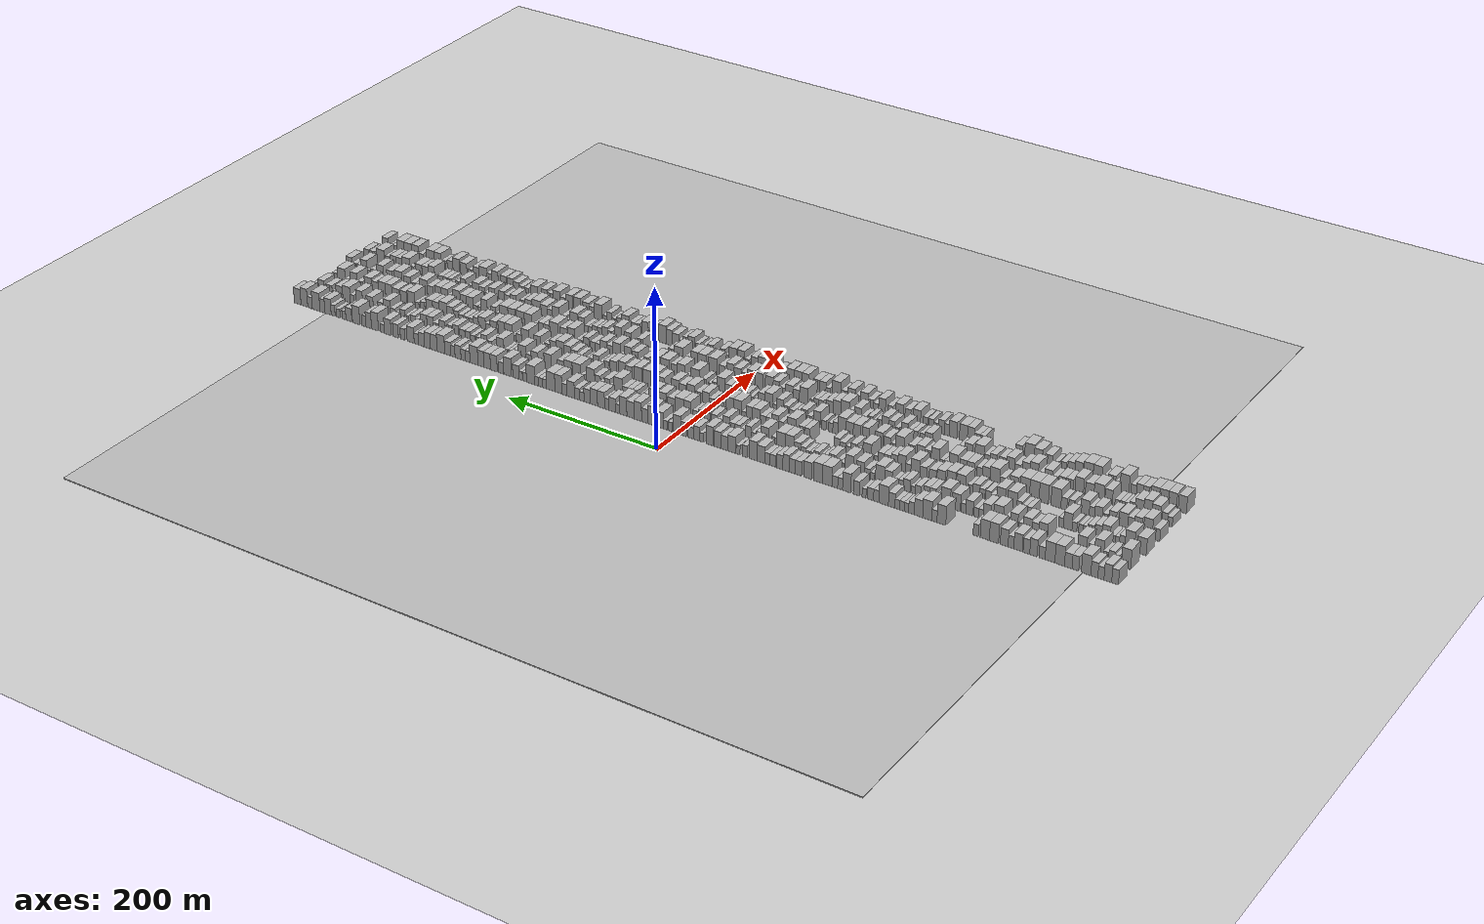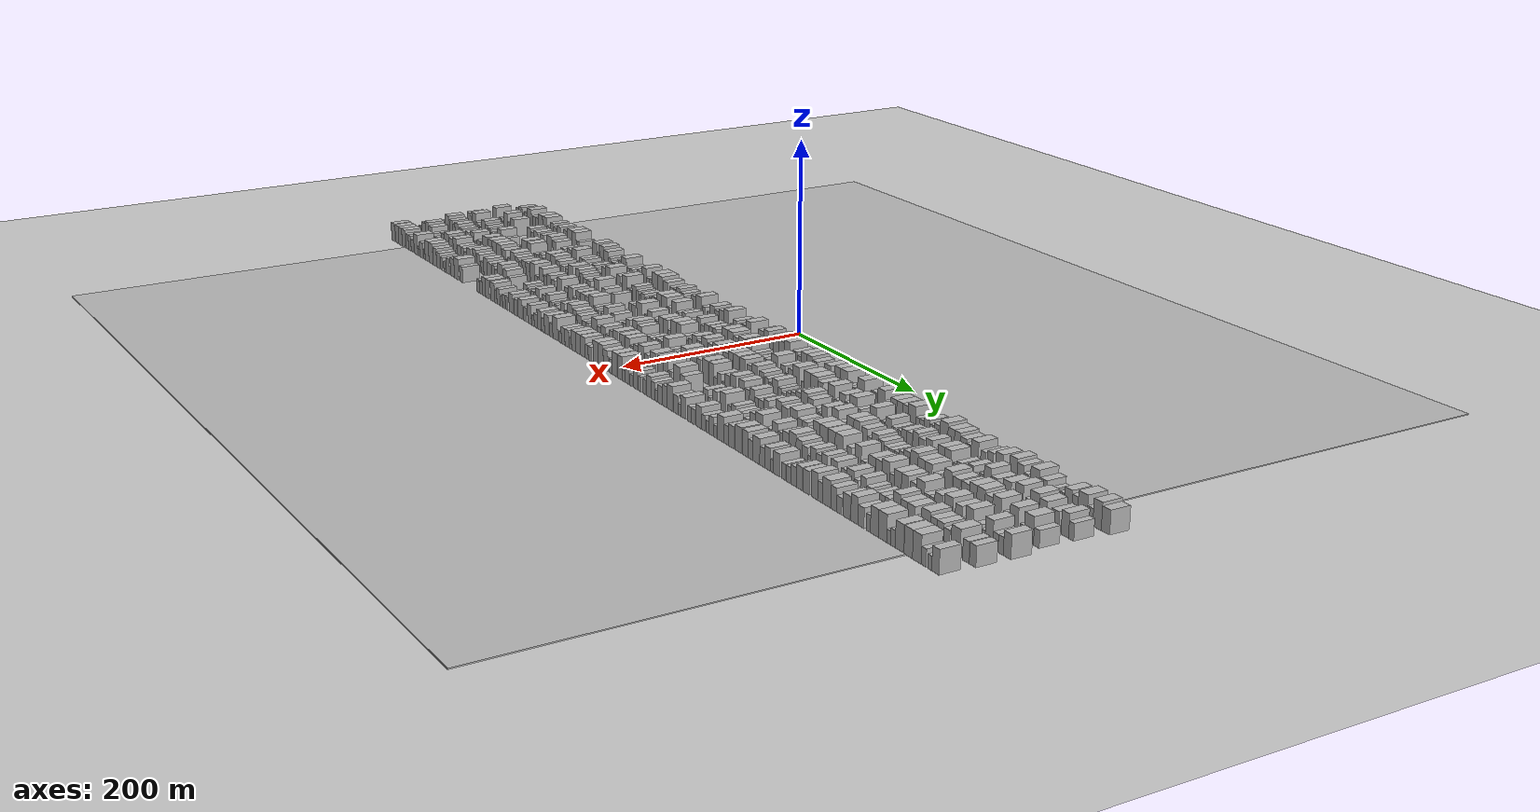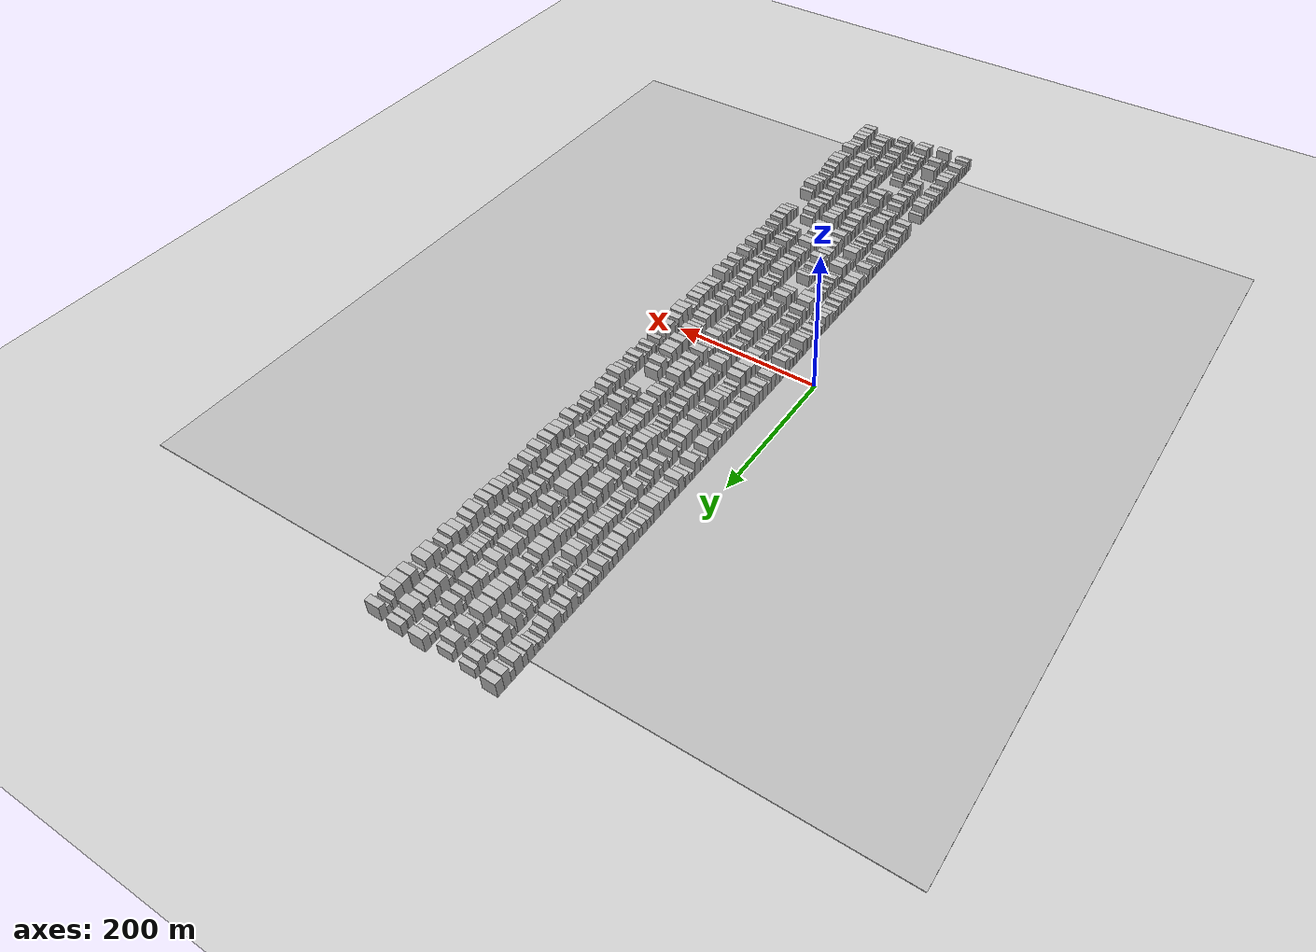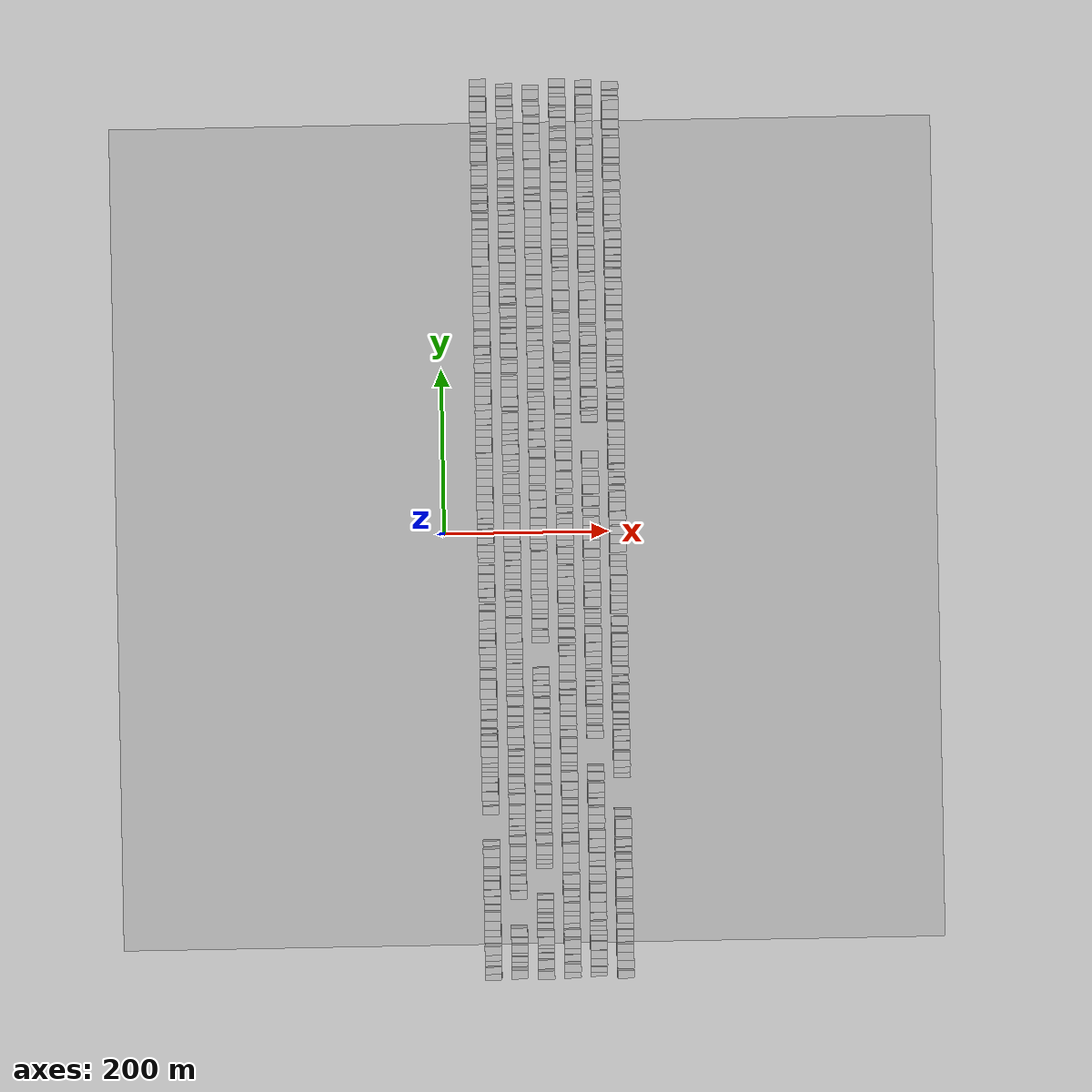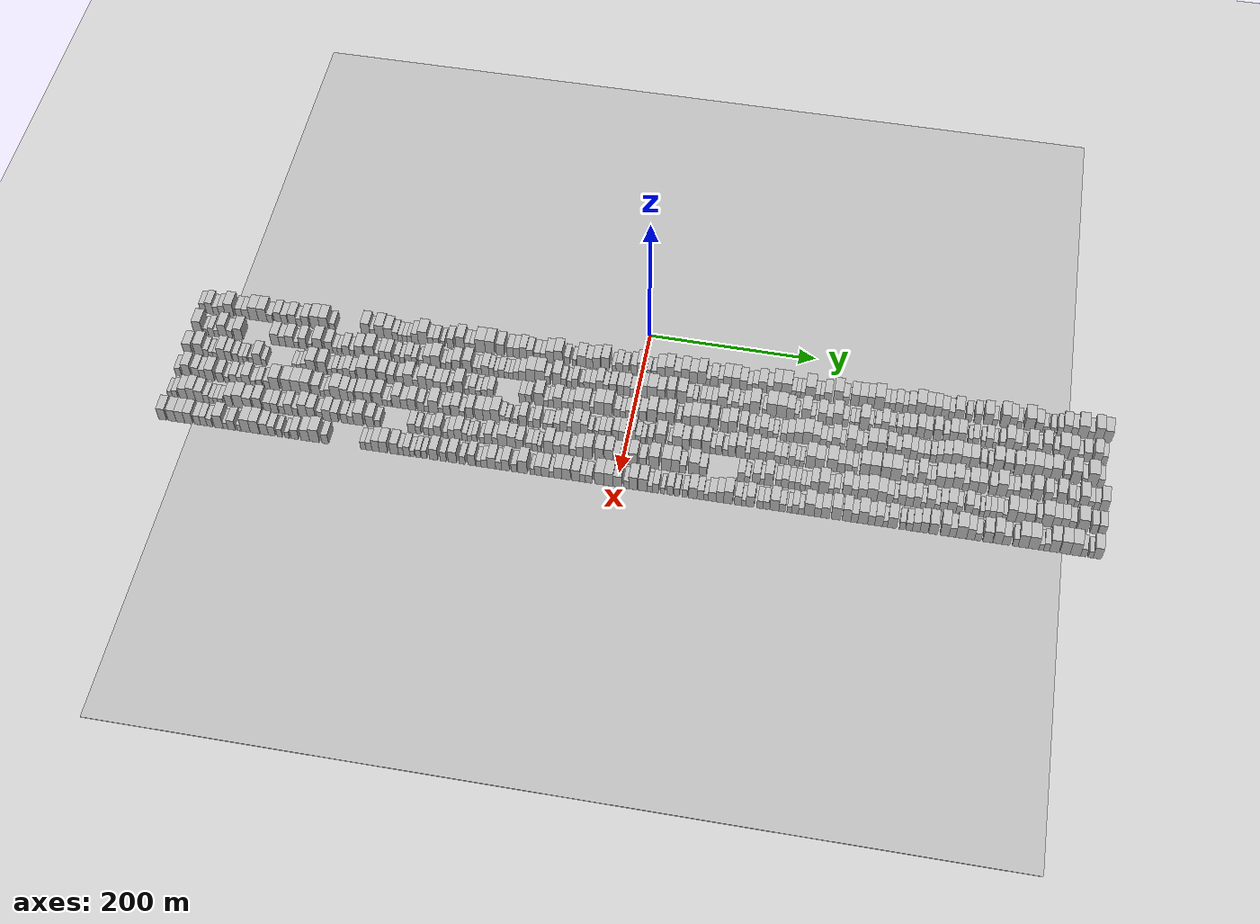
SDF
<?xml version="1.0" encoding="utf-8"?>

<sdf version="1.6">

   <world name="default">

      <gui fullscreen="0">

         <camera name="user_camera">

            <pose>-15 0 4.57585 0 0 0</pose>

            <view_controller>orbit</view_controller>

         </camera>

      </gui>

      <scene>

         <sky>

           <clouds>

             <speed>12</speed>

           </clouds>

         </sky>

         <ambient>0.4 0.4 0.4 1</ambient>

         <background>0.7 0.7 0.7 1</background>

         <shadows>1</shadows>

      </scene>

      <gravity>0 0 -9.8066</gravity>

      <magnetic_field>6e-06 2.3e-05 -4.2e-05</magnetic_field>

      <physics default="0" name="default_physics" type="ode">

         <ode>

            <solver>

               <type>quick</type>

               <iters>10</iters>

               <sor>1.0</sor>

               <use_dynamic_moi_rescaling>0</use_dynamic_moi_rescaling>

            </solver>

            <constraints>

               <cfm>0</cfm>

               <erp>0.2</erp>

               <contact_max_correcting_vel>100</contact_max_correcting_vel>

               <contact_surface_layer>0.001</contact_surface_layer>

            </constraints>

         </ode>

         <max_step_size>0.004</max_step_size>

         <real_time_factor>1</real_time_factor>

         <real_time_update_rate>250</real_time_update_rate>

      </physics>

      <light name="sun" type="directional">

         <cast_shadows>1</cast_shadows>

         <pose>0 0 10 0 0 0</pose>

         <diffuse>0.8 0.8 0.8 1</diffuse>

         <specular>0.2 0.2 0.2 1</specular>

         <attenuation>

            <range>1000</range>

            <constant>0.9</constant>

            <linear>0.01</linear>

            <quadratic>0.001</quadratic>

         </attenuation>

         <direction>-0.5 0.1 -0.9</direction>

      </light>

      <include>

         <name>ground_plane_1</name>

         <uri>model://HANNAS_ground_plane</uri>

         <pose>0 0 0  0 0 0</pose>

      </include>

      <include>

         <name>ground_plane_2</name>

         <uri>model://HANNAS_ground_plane</uri>

         <pose>100 0 0  0 0 0</pose>

      </include>

      <model name="building_1">

         <static>1</static>

         <pose frame="">50.0000 -536.2582 0 0.000000 0.000000 0.000000</pose>

         <link name="link">

            <pose frame="">0 0 9.00 0 0 0</pose>

            <collision name="collision">

               <geometry>

                  <box>

                     <size>20.0000 7.4837 18.0000</size>

                  </box>

               </geometry>

               <max_contacts>10</max_contacts>

               <surface>

                  <contact>

                     <ode/>

                  </contact>

                  <bounce/>

                  <friction>

                     <torsional>

                        <ode/>

                     </torsional>

                     <ode/>

                  </friction>

               </surface>

            </collision>

            <visual name="visual">

               <cast_shadows>0</cast_shadows>

               <geometry>

                  <box>

                     <size>20.0000 7.4837 18.0000</size>

                  </box>

               </geometry>

               <material>

                  <script>

                     <uri>model://HANNAS_wall/materials/scripts</uri>

                     <uri>model://HANNAS_wall/materials/textures</uri>

                     <name>vrc/HANNAS_wall</name>

                  </script>

               </material>

            </visual>

            <self_collide>0</self_collide>

            <enable_wind>0</enable_wind>

            <kinematic>0</kinematic>

         </link>

      </model>

      <model name="building_2">

         <static>1</static>

         <pose frame="">50.0000 -528.1529 0 0.000000 0.000000 0.000000</pose>

         <link name="link">

            <pose frame="">0 0 10.50 0 0 0</pose>

            <collision name="collision">

               <geometry>

                  <box>

                     <size>20.0000 8.7269 21.0000</size>

                  </box>

               </geometry>

               <max_contacts>10</max_contacts>

               <surface>

                  <contact>

                     <ode/>

                  </contact>

                  <bounce/>

                  <friction>

                     <torsional>

                        <ode/>

                     </torsional>

                     <ode/>

                  </friction>

               </surface>

            </collision>

            <visual name="visual">

               <cast_shadows>0</cast_shadows>

               <geometry>

                  <box>

                     <size>20.0000 8.7269 21.0000</size>

                  </box>

               </geometry>

               <material>

                  <script>

                     <uri>model://HANNAS_wall/materials/scripts</uri>

                     <uri>model://HANNAS_wall/materials/textures</uri>

                     <name>vrc/HANNAS_wall</name>

                  </script>

               </material>

            </visual>

            <self_collide>0</self_collide>

            <enable_wind>0</enable_wind>

            <kinematic>0</kinematic>

         </link>

      </model>

      <model name="building_3">

         <static>1</static>

         <pose frame="">50.0000 -520.3074 0 0.000000 0.000000 0.000000</pose>

         <link name="link">

            <pose frame="">0 0 7.50 0 0 0</pose>

            <collision name="collision">

               <geometry>

                  <box>

                     <size>20.0000 6.9641 15.0000</size>

                  </box>

               </geometry>

               <max_contacts>10</max_contacts>

               <surface>

                  <contact>

                     <ode/>

                  </contact>

                  <bounce/>

                  <friction>

                     <torsional>

                        <ode/>

                     </torsional>

                     <ode/>

                  </friction>

               </surface>

            </collision>

            <visual name="visual">

               <cast_shadows>0</cast_shadows>

               <geometry>

                  <box>

                     <size>20.0000 6.9641 15.0000</size>

                  </box>

               </geometry>

               <material>

                  <script>

                     <uri>model://HANNAS_wall/materials/scripts</uri>

                     <uri>model://HANNAS_wall/materials/textures</uri>

                     <name>vrc/HANNAS_wall</name>

                  </script>

               </material>

            </visual>

            <self_collide>0</self_collide>

            <enable_wind>0</enable_wind>

            <kinematic>0</kinematic>

         </link>

      </model>

      <model name="building_4">

         <static>1</static>

         <pose frame="">50.0000 -512.8381 0 0.000000 0.000000 0.000000</pose>

         <link name="link">

            <pose frame="">0 0 9.00 0 0 0</pose>

            <collision name="collision">

               <geometry>

                  <box>

                     <size>20.0000 7.9745 18.0000</size>

                  </box>

               </geometry>

               <max_contacts>10</max_contacts>

               <surface>

                  <contact>

                     <ode/>

                  </contact>

                  <bounce/>

                  <friction>

                     <torsional>

                        <ode/>

                     </torsional>

                     <ode/>

                  </friction>

               </surface>

            </collision>

            <visual name="visual">

               <cast_shadows>0</cast_shadows>

               <geometry>

                  <box>

                     <size>20.0000 7.9745 18.0000</size>

                  </box>

               </geometry>

               <material>

                  <script>

                     <uri>model://HANNAS_wall/materials/scripts</uri>

                     <uri>model://HANNAS_wall/materials/textures</uri>

                     <name>vrc/HANNAS_wall</name>

                  </script>

               </material>

            </visual>

            <self_collide>0</self_collide>

            <enable_wind>0</enable_wind>

            <kinematic>0</kinematic>

         </link>

      </model>

      <model name="building_5">

         <static>1</static>

         <pose frame="">50.0000 -503.4555 0 0.000000 0.000000 0.000000</pose>

         <link name="link">

            <pose frame="">0 0 12.00 0 0 0</pose>

            <collision name="collision">

               <geometry>

                  <box>

                     <size>20.0000 10.7908 24.0000</size>

                  </box>

               </geometry>

               <max_contacts>10</max_contacts>

               <surface>

                  <contact>

                     <ode/>

                  </contact>

                  <bounce/>

                  <friction>

                     <torsional>

                        <ode/>

                     </torsional>

                     <ode/>

                  </friction>

               </surface>

            </collision>

            <visual name="visual">

               <cast_shadows>0</cast_shadows>

               <geometry>

                  <box>

                     <size>20.0000 10.7908 24.0000</size>

                  </box>

               </geometry>

               <material>

                  <script>

                     <uri>model://HANNAS_wall/materials/scripts</uri>

                     <uri>model://HANNAS_wall/materials/textures</uri>

                     <name>vrc/HANNAS_wall</name>

                  </script>

               </material>

            </visual>

            <self_collide>0</self_collide>

            <enable_wind>0</enable_wind>

            <kinematic>0</kinematic>

         </link>

      </model>

      <model name="building_6">

         <static>1</static>

         <pose frame="">50.0000 -491.2447 0 0.000000 0.000000 0.000000</pose>

         <link name="link">

            <pose frame="">0 0 9.00 0 0 0</pose>

            <collision name="collision">

               <geometry>

                  <box>

                     <size>20.0000 7.6307 18.0000</size>

                  </box>

               </geometry>

               <max_contacts>10</max_contacts>

               <surface>

                  <contact>

                     <ode/>

                  </contact>

                  <bounce/>

                  <friction>

                     <torsional>

                        <ode/>

                     </torsional>

                     <ode/>

                  </friction>

               </surface>

            </collision>

            <visual name="visual">

               <cast_shadows>0</cast_shadows>

               <geometry>

                  <box>

                     <size>20.0000 7.6307 18.0000</size>

                  </box>

               </geometry>

               <material>

                  <script>

                     <uri>model://HANNAS_wall/materials/scripts</uri>

                     <uri>model://HANNAS_wall/materials/textures</uri>

                     <name>vrc/HANNAS_wall</name>

                  </script>

               </material>

            </visual>

            <self_collide>0</self_collide>

            <enable_wind>0</enable_wind>

            <kinematic>0</kinematic>

         </link>

      </model>

      <model name="building_7">

         <static>1</static>

         <pose frame="">50.0000 -483.0584 0 0.000000 0.000000 0.000000</pose>

         <link name="link">

            <pose frame="">0 0 9.00 0 0 0</pose>

            <collision name="collision">

               <geometry>

                  <box>

                     <size>20.0000 8.7419 18.0000</size>

                  </box>

               </geometry>

               <max_contacts>10</max_contacts>

               <surface>

                  <contact>

                     <ode/>

                  </contact>

                  <bounce/>

                  <friction>

                     <torsional>

                        <ode/>

                     </torsional>

                     <ode/>

                  </friction>

               </surface>

            </collision>

            <visual name="visual">

               <cast_shadows>0</cast_shadows>

               <geometry>

                  <box>

                     <size>20.0000 8.7419 18.0000</size>

                  </box>

               </geometry>

               <material>

                  <script>

                     <uri>model://HANNAS_wall/materials/scripts</uri>

                     <uri>model://HANNAS_wall/materials/textures</uri>

                     <name>vrc/HANNAS_wall</name>

                  </script>

               </material>

            </visual>

            <self_collide>0</self_collide>

            <enable_wind>0</enable_wind>

            <kinematic>0</kinematic>

         </link>

      </model>

      <model name="building_8">

         <static>1</static>

         <pose frame="">50.0000 -473.2048 0 0.000000 0.000000 0.000000</pose>

         <link name="link">

            <pose frame="">0 0 12.00 0 0 0</pose>

            <collision name="collision">

               <geometry>

                  <box>

                     <size>20.0000 10.9654 24.0000</size>

                  </box>

               </geometry>

               <max_contacts>10</max_contacts>

               <surface>

                  <contact>

                     <ode/>

                  </contact>

                  <bounce/>

                  <friction>

                     <torsional>

                        <ode/>

                     </torsional>

                     <ode/>

                  </friction>

               </surface>

            </collision>

            <visual name="visual">

               <cast_shadows>0</cast_shadows>

               <geometry>

                  <box>

                     <size>20.0000 10.9654 24.0000</size>

                  </box>

               </geometry>

               <material>

                  <script>

                     <uri>model://HANNAS_wall/materials/scripts</uri>

                     <uri>model://HANNAS_wall/materials/textures</uri>

                     <name>vrc/HANNAS_wall</name>

                  </script>

               </material>

            </visual>

            <self_collide>0</self_collide>

            <enable_wind>0</enable_wind>

            <kinematic>0</kinematic>

         </link>

      </model>

      <model name="building_9">

         <static>1</static>

         <pose frame="">50.0000 -462.0692 0 0.000000 0.000000 0.000000</pose>

         <link name="link">

            <pose frame="">0 0 12.00 0 0 0</pose>

            <collision name="collision">

               <geometry>

                  <box>

                     <size>20.0000 11.3057 24.0000</size>

                  </box>

               </geometry>

               <max_contacts>10</max_contacts>

               <surface>

                  <contact>

                     <ode/>

                  </contact>

                  <bounce/>

                  <friction>

                     <torsional>

                        <ode/>

                     </torsional>

                     <ode/>

                  </friction>

               </surface>

            </collision>

            <visual name="visual">

               <cast_shadows>0</cast_shadows>

               <geometry>

                  <box>

                     <size>20.0000 11.3057 24.0000</size>

                  </box>

               </geometry>

               <material>

                  <script>

                     <uri>model://HANNAS_wall/materials/scripts</uri>

                     <uri>model://HANNAS_wall/materials/textures</uri>

                     <name>vrc/HANNAS_wall</name>

                  </script>

               </material>

            </visual>

            <self_collide>0</self_collide>

            <enable_wind>0</enable_wind>

            <kinematic>0</kinematic>

         </link>

      </model>

      <model name="building_10">

         <static>1</static>

         <pose frame="">50.0000 -452.8031 0 0.000000 0.000000 0.000000</pose>

         <link name="link">

            <pose frame="">0 0 7.50 0 0 0</pose>

            <collision name="collision">

               <geometry>

                  <box>

                     <size>20.0000 7.2263 15.0000</size>

                  </box>

               </geometry>

               <max_contacts>10</max_contacts>

               <surface>

                  <contact>

                     <ode/>

                  </contact>

                  <bounce/>

                  <friction>

                     <torsional>

                        <ode/>

                     </torsional>

                     <ode/>

                  </friction>

               </surface>

            </collision>

            <visual name="visual">

               <cast_shadows>0</cast_shadows>

               <geometry>

                  <box>

                     <size>20.0000 7.2263 15.0000</size>

                  </box>

               </geometry>

               <material>

                  <script>

                     <uri>model://HANNAS_wall/materials/scripts</uri>

                     <uri>model://HANNAS_wall/materials/textures</uri>

                     <name>vrc/HANNAS_wall</name>

                  </script>

               </material>

            </visual>

            <self_collide>0</self_collide>

            <enable_wind>0</enable_wind>

            <kinematic>0</kinematic>

         </link>

      </model>

      <model name="building_11">

         <static>1</static>

         <pose frame="">50.0000 -442.8882 0 0.000000 0.000000 0.000000</pose>

         <link name="link">

            <pose frame="">0 0 10.50 0 0 0</pose>

            <collision name="collision">

               <geometry>

                  <box>

                     <size>20.0000 8.6036 21.0000</size>

                  </box>

               </geometry>

               <max_contacts>10</max_contacts>

               <surface>

                  <contact>

                     <ode/>

                  </contact>

                  <bounce/>

                  <friction>

                     <torsional>

                        <ode/>

                     </torsional>

                     <ode/>

                  </friction>

               </surface>

            </collision>

            <visual name="visual">

               <cast_shadows>0</cast_shadows>

               <geometry>

                  <box>

                     <size>20.0000 8.6036 21.0000</size>

                  </box>

               </geometry>

               <material>

                  <script>

                     <uri>model://HANNAS_wall/materials/scripts</uri>

                     <uri>model://HANNAS_wall/materials/textures</uri>

                     <name>vrc/HANNAS_wall</name>

                  </script>

               </material>

            </visual>

            <self_collide>0</self_collide>

            <enable_wind>0</enable_wind>

            <kinematic>0</kinematic>

         </link>

      </model>

      <model name="building_12">

         <static>1</static>

         <pose frame="">50.0000 -434.7102 0 0.000000 0.000000 0.000000</pose>

         <link name="link">

            <pose frame="">0 0 9.00 0 0 0</pose>

            <collision name="collision">

               <geometry>

                  <box>

                     <size>20.0000 7.7524 18.0000</size>

                  </box>

               </geometry>

               <max_contacts>10</max_contacts>

               <surface>

                  <contact>

                     <ode/>

                  </contact>

                  <bounce/>

                  <friction>

                     <torsional>

                        <ode/>

                     </torsional>

                     <ode/>

                  </friction>

               </surface>

            </collision>

            <visual name="visual">

               <cast_shadows>0</cast_shadows>

               <geometry>

                  <box>

                     <size>20.0000 7.7524 18.0000</size>

                  </box>

               </geometry>

               <material>

                  <script>

                     <uri>model://HANNAS_wall/materials/scripts</uri>

                     <uri>model://HANNAS_wall/materials/textures</uri>

                     <name>vrc/HANNAS_wall</name>

                  </script>

               </material>

            </visual>

            <self_collide>0</self_collide>

            <enable_wind>0</enable_wind>

            <kinematic>0</kinematic>

         </link>

      </model>

      <model name="building_13">

         <static>1</static>

         <pose frame="">50.0000 -424.9100 0 0.000000 0.000000 0.000000</pose>

         <link name="link">

            <pose frame="">0 0 10.50 0 0 0</pose>

            <collision name="collision">

               <geometry>

                  <box>

                     <size>20.0000 9.8479 21.0000</size>

                  </box>

               </geometry>

               <max_contacts>10</max_contacts>

               <surface>

                  <contact>

                     <ode/>

                  </contact>

                  <bounce/>

                  <friction>

                     <torsional>

                        <ode/>

                     </torsional>

                     <ode/>

                  </friction>

               </surface>

            </collision>

            <visual name="visual">

               <cast_shadows>0</cast_shadows>

               <geometry>

                  <box>

                     <size>20.0000 9.8479 21.0000</size>

                  </box>

               </geometry>

               <material>

                  <script>

                     <uri>model://HANNAS_wall/materials/scripts</uri>

                     <uri>model://HANNAS_wall/materials/textures</uri>

                     <name>vrc/HANNAS_wall</name>

                  </script>

               </material>

            </visual>

            <self_collide>0</self_collide>

            <enable_wind>0</enable_wind>

            <kinematic>0</kinematic>

         </link>

      </model>

      <model name="building_14">

         <static>1</static>

         <pose frame="">50.0000 -416.6208 0 0.000000 0.000000 0.000000</pose>

         <link name="link">

            <pose frame="">0 0 7.50 0 0 0</pose>

            <collision name="collision">

               <geometry>

                  <box>

                     <size>20.0000 6.7304 15.0000</size>

                  </box>

               </geometry>

               <max_contacts>10</max_contacts>

               <surface>

                  <contact>

                     <ode/>

                  </contact>

                  <bounce/>

                  <friction>

                     <torsional>

                        <ode/>

                     </torsional>

                     <ode/>

                  </friction>

               </surface>

            </collision>

            <visual name="visual">

               <cast_shadows>0</cast_shadows>

               <geometry>

                  <box>

                     <size>20.0000 6.7304 15.0000</size>

                  </box>

               </geometry>

               <material>

                  <script>

                     <uri>model://HANNAS_wall/materials/scripts</uri>

                     <uri>model://HANNAS_wall/materials/textures</uri>

                     <name>vrc/HANNAS_wall</name>

                  </script>

               </material>

            </visual>

            <self_collide>0</self_collide>

            <enable_wind>0</enable_wind>

            <kinematic>0</kinematic>

         </link>

      </model>

      <model name="building_15">

         <static>1</static>

         <pose frame="">50.0000 -408.6573 0 0.000000 0.000000 0.000000</pose>

         <link name="link">

            <pose frame="">0 0 10.50 0 0 0</pose>

            <collision name="collision">

               <geometry>

                  <box>

                     <size>20.0000 9.1966 21.0000</size>

                  </box>

               </geometry>

               <max_contacts>10</max_contacts>

               <surface>

                  <contact>

                     <ode/>

                  </contact>

                  <bounce/>

                  <friction>

                     <torsional>

                        <ode/>

                     </torsional>

                     <ode/>

                  </friction>

               </surface>

            </collision>

            <visual name="visual">

               <cast_shadows>0</cast_shadows>

               <geometry>

                  <box>

                     <size>20.0000 9.1966 21.0000</size>

                  </box>

               </geometry>

               <material>

                  <script>

                     <uri>model://HANNAS_wall/materials/scripts</uri>

                     <uri>model://HANNAS_wall/materials/textures</uri>

                     <name>vrc/HANNAS_wall</name>

                  </script>

               </material>

            </visual>

            <self_collide>0</self_collide>

            <enable_wind>0</enable_wind>

            <kinematic>0</kinematic>

         </link>

      </model>

      <model name="building_16">

         <static>1</static>

         <pose frame="">50.0000 -396.6379 0 0.000000 0.000000 0.000000</pose>

         <link name="link">

            <pose frame="">0 0 12.00 0 0 0</pose>

            <collision name="collision">

               <geometry>

                  <box>

                     <size>20.0000 10.8422 24.0000</size>

                  </box>

               </geometry>

               <max_contacts>10</max_contacts>

               <surface>

                  <contact>

                     <ode/>

                  </contact>

                  <bounce/>

                  <friction>

                     <torsional>

                        <ode/>

                     </torsional>

                     <ode/>

                  </friction>

               </surface>

            </collision>

            <visual name="visual">

               <cast_shadows>0</cast_shadows>

               <geometry>

                  <box>

                     <size>20.0000 10.8422 24.0000</size>

                  </box>

               </geometry>

               <material>

                  <script>

                     <uri>model://HANNAS_wall/materials/scripts</uri>

                     <uri>model://HANNAS_wall/materials/textures</uri>

                     <name>vrc/HANNAS_wall</name>

                  </script>

               </material>

            </visual>

            <self_collide>0</self_collide>

            <enable_wind>0</enable_wind>

            <kinematic>0</kinematic>

         </link>

      </model>

      <model name="building_17">

         <static>1</static>

         <pose frame="">50.0000 -385.8478 0 0.000000 0.000000 0.000000</pose>

         <link name="link">

            <pose frame="">0 0 12.00 0 0 0</pose>

            <collision name="collision">

               <geometry>

                  <box>

                     <size>20.0000 10.7379 24.0000</size>

                  </box>

               </geometry>

               <max_contacts>10</max_contacts>

               <surface>

                  <contact>

                     <ode/>

                  </contact>

                  <bounce/>

                  <friction>

                     <torsional>

                        <ode/>

                     </torsional>

                     <ode/>

                  </friction>

               </surface>

            </collision>

            <visual name="visual">

               <cast_shadows>0</cast_shadows>

               <geometry>

                  <box>

                     <size>20.0000 10.7379 24.0000</size>

                  </box>

               </geometry>

               <material>

                  <script>

                     <uri>model://HANNAS_wall/materials/scripts</uri>

                     <uri>model://HANNAS_wall/materials/textures</uri>

                     <name>vrc/HANNAS_wall</name>

                  </script>

               </material>

            </visual>

            <self_collide>0</self_collide>

            <enable_wind>0</enable_wind>

            <kinematic>0</kinematic>

         </link>

      </model>

      <model name="building_18">

         <static>1</static>

         <pose frame="">50.0000 -375.2231 0 0.000000 0.000000 0.000000</pose>

         <link name="link">

            <pose frame="">0 0 7.50 0 0 0</pose>

            <collision name="collision">

               <geometry>

                  <box>

                     <size>20.0000 6.5116 15.0000</size>

                  </box>

               </geometry>

               <max_contacts>10</max_contacts>

               <surface>

                  <contact>

                     <ode/>

                  </contact>

                  <bounce/>

                  <friction>

                     <torsional>

                        <ode/>

                     </torsional>

                     <ode/>

                  </friction>

               </surface>

            </collision>

            <visual name="visual">

               <cast_shadows>0</cast_shadows>

               <geometry>

                  <box>

                     <size>20.0000 6.5116 15.0000</size>

                  </box>

               </geometry>

               <material>

                  <script>

                     <uri>model://HANNAS_wall/materials/scripts</uri>

                     <uri>model://HANNAS_wall/materials/textures</uri>

                     <name>vrc/HANNAS_wall</name>

                  </script>

               </material>

            </visual>

            <self_collide>0</self_collide>

            <enable_wind>0</enable_wind>

            <kinematic>0</kinematic>

         </link>

      </model>

      <model name="building_19">

         <static>1</static>

         <pose frame="">50.0000 -334.1305 0 0.000000 0.000000 0.000000</pose>

         <link name="link">

            <pose frame="">0 0 12.00 0 0 0</pose>

            <collision name="collision">

               <geometry>

                  <box>

                     <size>20.0000 10.5579 24.0000</size>

                  </box>

               </geometry>

               <max_contacts>10</max_contacts>

               <surface>

                  <contact>

                     <ode/>

                  </contact>

                  <bounce/>

                  <friction>

                     <torsional>

                        <ode/>

                     </torsional>

                     <ode/>

                  </friction>

               </surface>

            </collision>

            <visual name="visual">

               <cast_shadows>0</cast_shadows>

               <geometry>

                  <box>

                     <size>20.0000 10.5579 24.0000</size>

                  </box>

               </geometry>

               <material>

                  <script>

                     <uri>model://HANNAS_wall/materials/scripts</uri>

                     <uri>model://HANNAS_wall/materials/textures</uri>

                     <name>vrc/HANNAS_wall</name>

                  </script>

               </material>

            </visual>

            <self_collide>0</self_collide>

            <enable_wind>0</enable_wind>

            <kinematic>0</kinematic>

         </link>

      </model>

      <model name="building_20">

         <static>1</static>

         <pose frame="">50.0000 -325.7065 0 0.000000 0.000000 0.000000</pose>

         <link name="link">

            <pose frame="">0 0 7.50 0 0 0</pose>

            <collision name="collision">

               <geometry>

                  <box>

                     <size>20.0000 6.2900 15.0000</size>

                  </box>

               </geometry>

               <max_contacts>10</max_contacts>

               <surface>

                  <contact>

                     <ode/>

                  </contact>

                  <bounce/>

                  <friction>

                     <torsional>

                        <ode/>

                     </torsional>

                     <ode/>

                  </friction>

               </surface>

            </collision>

            <visual name="visual">

               <cast_shadows>0</cast_shadows>

               <geometry>

                  <box>

                     <size>20.0000 6.2900 15.0000</size>

                  </box>

               </geometry>

               <material>

                  <script>

                     <uri>model://HANNAS_wall/materials/scripts</uri>

                     <uri>model://HANNAS_wall/materials/textures</uri>

                     <name>vrc/HANNAS_wall</name>

                  </script>

               </material>

            </visual>

            <self_collide>0</self_collide>

            <enable_wind>0</enable_wind>

            <kinematic>0</kinematic>

         </link>

      </model>

      <model name="building_21">

         <static>1</static>

         <pose frame="">50.0000 -317.0275 0 0.000000 0.000000 0.000000</pose>

         <link name="link">

            <pose frame="">0 0 12.00 0 0 0</pose>

            <collision name="collision">

               <geometry>

                  <box>

                     <size>20.0000 11.0679 24.0000</size>

                  </box>

               </geometry>

               <max_contacts>10</max_contacts>

               <surface>

                  <contact>

                     <ode/>

                  </contact>

                  <bounce/>

                  <friction>

                     <torsional>

                        <ode/>

                     </torsional>

                     <ode/>

                  </friction>

               </surface>

            </collision>

            <visual name="visual">

               <cast_shadows>0</cast_shadows>

               <geometry>

                  <box>

                     <size>20.0000 11.0679 24.0000</size>

                  </box>

               </geometry>

               <material>

                  <script>

                     <uri>model://HANNAS_wall/materials/scripts</uri>

                     <uri>model://HANNAS_wall/materials/textures</uri>

                     <name>vrc/HANNAS_wall</name>

                  </script>

               </material>

            </visual>

            <self_collide>0</self_collide>

            <enable_wind>0</enable_wind>

            <kinematic>0</kinematic>

         </link>

      </model>

      <model name="building_22">

         <static>1</static>

         <pose frame="">50.0000 -306.4596 0 0.000000 0.000000 0.000000</pose>

         <link name="link">

            <pose frame="">0 0 10.50 0 0 0</pose>

            <collision name="collision">

               <geometry>

                  <box>

                     <size>20.0000 10.0678 21.0000</size>

                  </box>

               </geometry>

               <max_contacts>10</max_contacts>

               <surface>

                  <contact>

                     <ode/>

                  </contact>

                  <bounce/>

                  <friction>

                     <torsional>

                        <ode/>

                     </torsional>

                     <ode/>

                  </friction>

               </surface>

            </collision>

            <visual name="visual">

               <cast_shadows>0</cast_shadows>

               <geometry>

                  <box>

                     <size>20.0000 10.0678 21.0000</size>

                  </box>

               </geometry>

               <material>

                  <script>

                     <uri>model://HANNAS_wall/materials/scripts</uri>

                     <uri>model://HANNAS_wall/materials/textures</uri>

                     <name>vrc/HANNAS_wall</name>

                  </script>

               </material>

            </visual>

            <self_collide>0</self_collide>

            <enable_wind>0</enable_wind>

            <kinematic>0</kinematic>

         </link>

      </model>

      <model name="building_23">

         <static>1</static>

         <pose frame="">50.0000 -297.9620 0 0.000000 0.000000 0.000000</pose>

         <link name="link">

            <pose frame="">0 0 7.50 0 0 0</pose>

            <collision name="collision">

               <geometry>

                  <box>

                     <size>20.0000 6.9274 15.0000</size>

                  </box>

               </geometry>

               <max_contacts>10</max_contacts>

               <surface>

                  <contact>

                     <ode/>

                  </contact>

                  <bounce/>

                  <friction>

                     <torsional>

                        <ode/>

                     </torsional>

                     <ode/>

                  </friction>

               </surface>

            </collision>

            <visual name="visual">

               <cast_shadows>0</cast_shadows>

               <geometry>

                  <box>

                     <size>20.0000 6.9274 15.0000</size>

                  </box>

               </geometry>

               <material>

                  <script>

                     <uri>model://HANNAS_wall/materials/scripts</uri>

                     <uri>model://HANNAS_wall/materials/textures</uri>

                     <name>vrc/HANNAS_wall</name>

                  </script>

               </material>

            </visual>

            <self_collide>0</self_collide>

            <enable_wind>0</enable_wind>

            <kinematic>0</kinematic>

         </link>

      </model>

      <model name="building_24">

         <static>1</static>

         <pose frame="">50.0000 -291.8963 0 0.000000 0.000000 0.000000</pose>

         <link name="link">

            <pose frame="">0 0 6.00 0 0 0</pose>

            <collision name="collision">

               <geometry>

                  <box>

                     <size>20.0000 5.2041 12.0000</size>

                  </box>

               </geometry>

               <max_contacts>10</max_contacts>

               <surface>

                  <contact>

                     <ode/>

                  </contact>

                  <bounce/>

                  <friction>

                     <torsional>

                        <ode/>

                     </torsional>

                     <ode/>

                  </friction>

               </surface>

            </collision>

            <visual name="visual">

               <cast_shadows>0</cast_shadows>

               <geometry>

                  <box>

                     <size>20.0000 5.2041 12.0000</size>

                  </box>

               </geometry>

               <material>

                  <script>

                     <uri>model://HANNAS_wall/materials/scripts</uri>

                     <uri>model://HANNAS_wall/materials/textures</uri>

                     <name>vrc/HANNAS_wall</name>

                  </script>

               </material>

            </visual>

            <self_collide>0</self_collide>

            <enable_wind>0</enable_wind>

            <kinematic>0</kinematic>

         </link>

      </model>

      <model name="building_25">

         <static>1</static>

         <pose frame="">50.0000 -286.4737 0 0.000000 0.000000 0.000000</pose>

         <link name="link">

            <pose frame="">0 0 6.00 0 0 0</pose>

            <collision name="collision">

               <geometry>

                  <box>

                     <size>20.0000 5.6412 12.0000</size>

                  </box>

               </geometry>

               <max_contacts>10</max_contacts>

               <surface>

                  <contact>

                     <ode/>

                  </contact>

                  <bounce/>

                  <friction>

                     <torsional>

                        <ode/>

                     </torsional>

                     <ode/>

                  </friction>

               </surface>

            </collision>

            <visual name="visual">

               <cast_shadows>0</cast_shadows>

               <geometry>

                  <box>

                     <size>20.0000 5.6412 12.0000</size>

                  </box>

               </geometry>

               <material>

                  <script>

                     <uri>model://HANNAS_wall/materials/scripts</uri>

                     <uri>model://HANNAS_wall/materials/textures</uri>

                     <name>vrc/HANNAS_wall</name>

                  </script>

               </material>

            </visual>

            <self_collide>0</self_collide>

            <enable_wind>0</enable_wind>

            <kinematic>0</kinematic>

         </link>

      </model>

      <model name="building_26">

         <static>1</static>

         <pose frame="">50.0000 -280.7566 0 0.000000 0.000000 0.000000</pose>

         <link name="link">

            <pose frame="">0 0 6.00 0 0 0</pose>

            <collision name="collision">

               <geometry>

                  <box>

                     <size>20.0000 5.7930 12.0000</size>

                  </box>

               </geometry>

               <max_contacts>10</max_contacts>

               <surface>

                  <contact>

                     <ode/>

                  </contact>

                  <bounce/>

                  <friction>

                     <torsional>

                        <ode/>

                     </torsional>

                     <ode/>

                  </friction>

               </surface>

            </collision>

            <visual name="visual">

               <cast_shadows>0</cast_shadows>

               <geometry>

                  <box>

                     <size>20.0000 5.7930 12.0000</size>

                  </box>

               </geometry>

               <material>

                  <script>

                     <uri>model://HANNAS_wall/materials/scripts</uri>

                     <uri>model://HANNAS_wall/materials/textures</uri>

                     <name>vrc/HANNAS_wall</name>

                  </script>

               </material>

            </visual>

            <self_collide>0</self_collide>

            <enable_wind>0</enable_wind>

            <kinematic>0</kinematic>

         </link>

      </model>

      <model name="building_27">

         <static>1</static>

         <pose frame="">50.0000 -273.8065 0 0.000000 0.000000 0.000000</pose>

         <link name="link">

            <pose frame="">0 0 9.00 0 0 0</pose>

            <collision name="collision">

               <geometry>

                  <box>

                     <size>20.0000 8.1072 18.0000</size>

                  </box>

               </geometry>

               <max_contacts>10</max_contacts>

               <surface>

                  <contact>

                     <ode/>

                  </contact>

                  <bounce/>

                  <friction>

                     <torsional>

                        <ode/>

                     </torsional>

                     <ode/>

                  </friction>

               </surface>

            </collision>

            <visual name="visual">

               <cast_shadows>0</cast_shadows>

               <geometry>

                  <box>

                     <size>20.0000 8.1072 18.0000</size>

                  </box>

               </geometry>

               <material>

                  <script>

                     <uri>model://HANNAS_wall/materials/scripts</uri>

                     <uri>model://HANNAS_wall/materials/textures</uri>

                     <name>vrc/HANNAS_wall</name>

                  </script>

               </material>

            </visual>

            <self_collide>0</self_collide>

            <enable_wind>0</enable_wind>

            <kinematic>0</kinematic>

         </link>

      </model>

      <model name="building_28">

         <static>1</static>

         <pose frame="">50.0000 -263.9449 0 0.000000 0.000000 0.000000</pose>

         <link name="link">

            <pose frame="">0 0 12.00 0 0 0</pose>

            <collision name="collision">

               <geometry>

                  <box>

                     <size>20.0000 11.6159 24.0000</size>

                  </box>

               </geometry>

               <max_contacts>10</max_contacts>

               <surface>

                  <contact>

                     <ode/>

                  </contact>

                  <bounce/>

                  <friction>

                     <torsional>

                        <ode/>

                     </torsional>

                     <ode/>

                  </friction>

               </surface>

            </collision>

            <visual name="visual">

               <cast_shadows>0</cast_shadows>

               <geometry>

                  <box>

                     <size>20.0000 11.6159 24.0000</size>

                  </box>

               </geometry>

               <material>

                  <script>

                     <uri>model://HANNAS_wall/materials/scripts</uri>

                     <uri>model://HANNAS_wall/materials/textures</uri>

                     <name>vrc/HANNAS_wall</name>

                  </script>

               </material>

            </visual>

            <self_collide>0</self_collide>

            <enable_wind>0</enable_wind>

            <kinematic>0</kinematic>

         </link>

      </model>

      <model name="building_29">

         <static>1</static>

         <pose frame="">50.0000 -254.8474 0 0.000000 0.000000 0.000000</pose>

         <link name="link">

            <pose frame="">0 0 7.50 0 0 0</pose>

            <collision name="collision">

               <geometry>

                  <box>

                     <size>20.0000 6.5791 15.0000</size>

                  </box>

               </geometry>

               <max_contacts>10</max_contacts>

               <surface>

                  <contact>

                     <ode/>

                  </contact>

                  <bounce/>

                  <friction>

                     <torsional>

                        <ode/>

                     </torsional>

                     <ode/>

                  </friction>

               </surface>

            </collision>

            <visual name="visual">

               <cast_shadows>0</cast_shadows>

               <geometry>

                  <box>

                     <size>20.0000 6.5791 15.0000</size>

                  </box>

               </geometry>

               <material>

                  <script>

                     <uri>model://HANNAS_wall/materials/scripts</uri>

                     <uri>model://HANNAS_wall/materials/textures</uri>

                     <name>vrc/HANNAS_wall</name>

                  </script>

               </material>

            </visual>

            <self_collide>0</self_collide>

            <enable_wind>0</enable_wind>

            <kinematic>0</kinematic>

         </link>

      </model>

      <model name="building_30">

         <static>1</static>

         <pose frame="">50.0000 -247.8670 0 0.000000 0.000000 0.000000</pose>

         <link name="link">

            <pose frame="">0 0 7.50 0 0 0</pose>

            <collision name="collision">

               <geometry>

                  <box>

                     <size>20.0000 7.3816 15.0000</size>

                  </box>

               </geometry>

               <max_contacts>10</max_contacts>

               <surface>

                  <contact>

                     <ode/>

                  </contact>

                  <bounce/>

                  <friction>

                     <torsional>

                        <ode/>

                     </torsional>

                     <ode/>

                  </friction>

               </surface>

            </collision>

            <visual name="visual">

               <cast_shadows>0</cast_shadows>

               <geometry>

                  <box>

                     <size>20.0000 7.3816 15.0000</size>

                  </box>

               </geometry>

               <material>

                  <script>

                     <uri>model://HANNAS_wall/materials/scripts</uri>

                     <uri>model://HANNAS_wall/materials/textures</uri>

                     <name>vrc/HANNAS_wall</name>

                  </script>

               </material>

            </visual>

            <self_collide>0</self_collide>

            <enable_wind>0</enable_wind>

            <kinematic>0</kinematic>

         </link>

      </model>

      <model name="building_31">

         <static>1</static>

         <pose frame="">50.0000 -239.7686 0 0.000000 0.000000 0.000000</pose>

         <link name="link">

            <pose frame="">0 0 6.00 0 0 0</pose>

            <collision name="collision">

               <geometry>

                  <box>

                     <size>20.0000 4.8153 12.0000</size>

                  </box>

               </geometry>

               <max_contacts>10</max_contacts>

               <surface>

                  <contact>

                     <ode/>

                  </contact>

                  <bounce/>

                  <friction>

                     <torsional>

                        <ode/>

                     </torsional>

                     <ode/>

                  </friction>

               </surface>

            </collision>

            <visual name="visual">

               <cast_shadows>0</cast_shadows>

               <geometry>

                  <box>

                     <size>20.0000 4.8153 12.0000</size>

                  </box>

               </geometry>

               <material>

                  <script>

                     <uri>model://HANNAS_wall/materials/scripts</uri>

                     <uri>model://HANNAS_wall/materials/textures</uri>

                     <name>vrc/HANNAS_wall</name>

                  </script>

               </material>

            </visual>

            <self_collide>0</self_collide>

            <enable_wind>0</enable_wind>

            <kinematic>0</kinematic>

         </link>

      </model>

      <model name="building_32">

         <static>1</static>

         <pose frame="">50.0000 -230.4440 0 0.000000 0.000000 0.000000</pose>

         <link name="link">

            <pose frame="">0 0 9.00 0 0 0</pose>

            <collision name="collision">

               <geometry>

                  <box>

                     <size>20.0000 7.8339 18.0000</size>

                  </box>

               </geometry>

               <max_contacts>10</max_contacts>

               <surface>

                  <contact>

                     <ode/>

                  </contact>

                  <bounce/>

                  <friction>

                     <torsional>

                        <ode/>

                     </torsional>

                     <ode/>

                  </friction>

               </surface>

            </collision>

            <visual name="visual">

               <cast_shadows>0</cast_shadows>

               <geometry>

                  <box>

                     <size>20.0000 7.8339 18.0000</size>

                  </box>

               </geometry>

               <material>

                  <script>

                     <uri>model://HANNAS_wall/materials/scripts</uri>

                     <uri>model://HANNAS_wall/materials/textures</uri>

                     <name>vrc/HANNAS_wall</name>

                  </script>

               </material>

            </visual>

            <self_collide>0</self_collide>

            <enable_wind>0</enable_wind>

            <kinematic>0</kinematic>

         </link>

      </model>

      <model name="building_33">

         <static>1</static>

         <pose frame="">50.0000 -218.3248 0 0.000000 0.000000 0.000000</pose>

         <link name="link">

            <pose frame="">0 0 12.00 0 0 0</pose>

            <collision name="collision">

               <geometry>

                  <box>

                     <size>20.0000 10.4044 24.0000</size>

                  </box>

               </geometry>

               <max_contacts>10</max_contacts>

               <surface>

                  <contact>

                     <ode/>

                  </contact>

                  <bounce/>

                  <friction>

                     <torsional>

                        <ode/>

                     </torsional>

                     <ode/>

                  </friction>

               </surface>

            </collision>

            <visual name="visual">

               <cast_shadows>0</cast_shadows>

               <geometry>

                  <box>

                     <size>20.0000 10.4044 24.0000</size>

                  </box>

               </geometry>

               <material>

                  <script>

                     <uri>model://HANNAS_wall/materials/scripts</uri>

                     <uri>model://HANNAS_wall/materials/textures</uri>

                     <name>vrc/HANNAS_wall</name>

                  </script>

               </material>

            </visual>

            <self_collide>0</self_collide>

            <enable_wind>0</enable_wind>

            <kinematic>0</kinematic>

         </link>

      </model>

      <model name="building_34">

         <static>1</static>

         <pose frame="">50.0000 -210.0626 0 0.000000 0.000000 0.000000</pose>

         <link name="link">

            <pose frame="">0 0 7.50 0 0 0</pose>

            <collision name="collision">

               <geometry>

                  <box>

                     <size>20.0000 6.1201 15.0000</size>

                  </box>

               </geometry>

               <max_contacts>10</max_contacts>

               <surface>

                  <contact>

                     <ode/>

                  </contact>

                  <bounce/>

                  <friction>

                     <torsional>

                        <ode/>

                     </torsional>

                     <ode/>

                  </friction>

               </surface>

            </collision>

            <visual name="visual">

               <cast_shadows>0</cast_shadows>

               <geometry>

                  <box>

                     <size>20.0000 6.1201 15.0000</size>

                  </box>

               </geometry>

               <material>

                  <script>

                     <uri>model://HANNAS_wall/materials/scripts</uri>

                     <uri>model://HANNAS_wall/materials/textures</uri>

                     <name>vrc/HANNAS_wall</name>

                  </script>

               </material>

            </visual>

            <self_collide>0</self_collide>

            <enable_wind>0</enable_wind>

            <kinematic>0</kinematic>

         </link>

      </model>

      <model name="building_35">

         <static>1</static>

         <pose frame="">50.0000 -203.4293 0 0.000000 0.000000 0.000000</pose>

         <link name="link">

            <pose frame="">0 0 7.50 0 0 0</pose>

            <collision name="collision">

               <geometry>

                  <box>

                     <size>20.0000 7.1464 15.0000</size>

                  </box>

               </geometry>

               <max_contacts>10</max_contacts>

               <surface>

                  <contact>

                     <ode/>

                  </contact>

                  <bounce/>

                  <friction>

                     <torsional>

                        <ode/>

                     </torsional>

                     <ode/>

                  </friction>

               </surface>

            </collision>

            <visual name="visual">

               <cast_shadows>0</cast_shadows>

               <geometry>

                  <box>

                     <size>20.0000 7.1464 15.0000</size>

                  </box>

               </geometry>

               <material>

                  <script>

                     <uri>model://HANNAS_wall/materials/scripts</uri>

                     <uri>model://HANNAS_wall/materials/textures</uri>

                     <name>vrc/HANNAS_wall</name>

                  </script>

               </material>

            </visual>

            <self_collide>0</self_collide>

            <enable_wind>0</enable_wind>

            <kinematic>0</kinematic>

         </link>

      </model>

      <model name="building_36">

         <static>1</static>

         <pose frame="">50.0000 -193.8844 0 0.000000 0.000000 0.000000</pose>

         <link name="link">

            <pose frame="">0 0 12.00 0 0 0</pose>

            <collision name="collision">

               <geometry>

                  <box>

                     <size>20.0000 11.9434 24.0000</size>

                  </box>

               </geometry>

               <max_contacts>10</max_contacts>

               <surface>

                  <contact>

                     <ode/>

                  </contact>

                  <bounce/>

                  <friction>

                     <torsional>

                        <ode/>

                     </torsional>

                     <ode/>

                  </friction>

               </surface>

            </collision>

            <visual name="visual">

               <cast_shadows>0</cast_shadows>

               <geometry>

                  <box>

                     <size>20.0000 11.9434 24.0000</size>

                  </box>

               </geometry>

               <material>

                  <script>

                     <uri>model://HANNAS_wall/materials/scripts</uri>

                     <uri>model://HANNAS_wall/materials/textures</uri>

                     <name>vrc/HANNAS_wall</name>

                  </script>

               </material>

            </visual>

            <self_collide>0</self_collide>

            <enable_wind>0</enable_wind>

            <kinematic>0</kinematic>

         </link>

      </model>

      <model name="building_37">

         <static>1</static>

         <pose frame="">50.0000 -182.1937 0 0.000000 0.000000 0.000000</pose>

         <link name="link">

            <pose frame="">0 0 12.00 0 0 0</pose>

            <collision name="collision">

               <geometry>

                  <box>

                     <size>20.0000 11.4381 24.0000</size>

                  </box>

               </geometry>

               <max_contacts>10</max_contacts>

               <surface>

                  <contact>

                     <ode/>

                  </contact>

                  <bounce/>

                  <friction>

                     <torsional>

                        <ode/>

                     </torsional>

                     <ode/>

                  </friction>

               </surface>

            </collision>

            <visual name="visual">

               <cast_shadows>0</cast_shadows>

               <geometry>

                  <box>

                     <size>20.0000 11.4381 24.0000</size>

                  </box>

               </geometry>

               <material>

                  <script>

                     <uri>model://HANNAS_wall/materials/scripts</uri>

                     <uri>model://HANNAS_wall/materials/textures</uri>

                     <name>vrc/HANNAS_wall</name>

                  </script>

               </material>

            </visual>

            <self_collide>0</self_collide>

            <enable_wind>0</enable_wind>

            <kinematic>0</kinematic>

         </link>

      </model>

      <model name="building_38">

         <static>1</static>

         <pose frame="">50.0000 -169.5516 0 0.000000 0.000000 0.000000</pose>

         <link name="link">

            <pose frame="">0 0 10.50 0 0 0</pose>

            <collision name="collision">

               <geometry>

                  <box>

                     <size>20.0000 9.8461 21.0000</size>

                  </box>

               </geometry>

               <max_contacts>10</max_contacts>

               <surface>

                  <contact>

                     <ode/>

                  </contact>

                  <bounce/>

                  <friction>

                     <torsional>

                        <ode/>

                     </torsional>

                     <ode/>

                  </friction>

               </surface>

            </collision>

            <visual name="visual">

               <cast_shadows>0</cast_shadows>

               <geometry>

                  <box>

                     <size>20.0000 9.8461 21.0000</size>

                  </box>

               </geometry>

               <material>

                  <script>

                     <uri>model://HANNAS_wall/materials/scripts</uri>

                     <uri>model://HANNAS_wall/materials/textures</uri>

                     <name>vrc/HANNAS_wall</name>

                  </script>

               </material>

            </visual>

            <self_collide>0</self_collide>

            <enable_wind>0</enable_wind>

            <kinematic>0</kinematic>

         </link>

      </model>

      <model name="building_39">

         <static>1</static>

         <pose frame="">50.0000 -157.7126 0 0.000000 0.000000 0.000000</pose>

         <link name="link">

            <pose frame="">0 0 9.00 0 0 0</pose>

            <collision name="collision">

               <geometry>

                  <box>

                     <size>20.0000 7.8317 18.0000</size>

                  </box>

               </geometry>

               <max_contacts>10</max_contacts>

               <surface>

                  <contact>

                     <ode/>

                  </contact>

                  <bounce/>

                  <friction>

                     <torsional>

                        <ode/>

                     </torsional>

                     <ode/>

                  </friction>

               </surface>

            </collision>

            <visual name="visual">

               <cast_shadows>0</cast_shadows>

               <geometry>

                  <box>

                     <size>20.0000 7.8317 18.0000</size>

                  </box>

               </geometry>

               <material>

                  <script>

                     <uri>model://HANNAS_wall/materials/scripts</uri>

                     <uri>model://HANNAS_wall/materials/textures</uri>

                     <name>vrc/HANNAS_wall</name>

                  </script>

               </material>

            </visual>

            <self_collide>0</self_collide>

            <enable_wind>0</enable_wind>

            <kinematic>0</kinematic>

         </link>

      </model>

      <model name="building_40">

         <static>1</static>

         <pose frame="">50.0000 -150.0281 0 0.000000 0.000000 0.000000</pose>

         <link name="link">

            <pose frame="">0 0 9.00 0 0 0</pose>

            <collision name="collision">

               <geometry>

                  <box>

                     <size>20.0000 7.5374 18.0000</size>

                  </box>

               </geometry>

               <max_contacts>10</max_contacts>

               <surface>

                  <contact>

                     <ode/>

                  </contact>

                  <bounce/>

                  <friction>

                     <torsional>

                        <ode/>

                     </torsional>

                     <ode/>

                  </friction>

               </surface>

            </collision>

            <visual name="visual">

               <cast_shadows>0</cast_shadows>

               <geometry>

                  <box>

                     <size>20.0000 7.5374 18.0000</size>

                  </box>

               </geometry>

               <material>

                  <script>

                     <uri>model://HANNAS_wall/materials/scripts</uri>

                     <uri>model://HANNAS_wall/materials/textures</uri>

                     <name>vrc/HANNAS_wall</name>

                  </script>

               </material>

            </visual>

            <self_collide>0</self_collide>

            <enable_wind>0</enable_wind>

            <kinematic>0</kinematic>

         </link>

      </model>

      <model name="building_41">

         <static>1</static>

         <pose frame="">50.0000 -142.0535 0 0.000000 0.000000 0.000000</pose>

         <link name="link">

            <pose frame="">0 0 10.50 0 0 0</pose>

            <collision name="collision">

               <geometry>

                  <box>

                     <size>20.0000 8.4118 21.0000</size>

                  </box>

               </geometry>

               <max_contacts>10</max_contacts>

               <surface>

                  <contact>

                     <ode/>

                  </contact>

                  <bounce/>

                  <friction>

                     <torsional>

                        <ode/>

                     </torsional>

                     <ode/>

                  </friction>

               </surface>

            </collision>

            <visual name="visual">

               <cast_shadows>0</cast_shadows>

               <geometry>

                  <box>

                     <size>20.0000 8.4118 21.0000</size>

                  </box>

               </geometry>

               <material>

                  <script>

                     <uri>model://HANNAS_wall/materials/scripts</uri>

                     <uri>model://HANNAS_wall/materials/textures</uri>

                     <name>vrc/HANNAS_wall</name>

                  </script>

               </material>

            </visual>

            <self_collide>0</self_collide>

            <enable_wind>0</enable_wind>

            <kinematic>0</kinematic>

         </link>

      </model>

      <model name="building_42">

         <static>1</static>

         <pose frame="">50.0000 -133.8638 0 0.000000 0.000000 0.000000</pose>

         <link name="link">

            <pose frame="">0 0 9.00 0 0 0</pose>

            <collision name="collision">

               <geometry>

                  <box>

                     <size>20.0000 7.9675 18.0000</size>

                  </box>

               </geometry>

               <max_contacts>10</max_contacts>

               <surface>

                  <contact>

                     <ode/>

                  </contact>

                  <bounce/>

                  <friction>

                     <torsional>

                        <ode/>

                     </torsional>

                     <ode/>

                  </friction>

               </surface>

            </collision>

            <visual name="visual">

               <cast_shadows>0</cast_shadows>

               <geometry>

                  <box>

                     <size>20.0000 7.9675 18.0000</size>

                  </box>

               </geometry>

               <material>

                  <script>

                     <uri>model://HANNAS_wall/materials/scripts</uri>

                     <uri>model://HANNAS_wall/materials/textures</uri>

                     <name>vrc/HANNAS_wall</name>

                  </script>

               </material>

            </visual>

            <self_collide>0</self_collide>

            <enable_wind>0</enable_wind>

            <kinematic>0</kinematic>

         </link>

      </model>

      <model name="building_43">

         <static>1</static>

         <pose frame="">50.0000 -125.1613 0 0.000000 0.000000 0.000000</pose>

         <link name="link">

            <pose frame="">0 0 7.50 0 0 0</pose>

            <collision name="collision">

               <geometry>

                  <box>

                     <size>20.0000 7.4376 15.0000</size>

                  </box>

               </geometry>

               <max_contacts>10</max_contacts>

               <surface>

                  <contact>

                     <ode/>

                  </contact>

                  <bounce/>

                  <friction>

                     <torsional>

                        <ode/>

                     </torsional>

                     <ode/>

                  </friction>

               </surface>

            </collision>

            <visual name="visual">

               <cast_shadows>0</cast_shadows>

               <geometry>

                  <box>

                     <size>20.0000 7.4376 15.0000</size>

                  </box>

               </geometry>

               <material>

                  <script>

                     <uri>model://HANNAS_wall/materials/scripts</uri>

                     <uri>model://HANNAS_wall/materials/textures</uri>

                     <name>vrc/HANNAS_wall</name>

                  </script>

               </material>

            </visual>

            <self_collide>0</self_collide>

            <enable_wind>0</enable_wind>

            <kinematic>0</kinematic>

         </link>

      </model>

      <model name="building_44">

         <static>1</static>

         <pose frame="">50.0000 -118.1211 0 0.000000 0.000000 0.000000</pose>

         <link name="link">

            <pose frame="">0 0 7.50 0 0 0</pose>

            <collision name="collision">

               <geometry>

                  <box>

                     <size>20.0000 6.6428 15.0000</size>

                  </box>

               </geometry>

               <max_contacts>10</max_contacts>

               <surface>

                  <contact>

                     <ode/>

                  </contact>

                  <bounce/>

                  <friction>

                     <torsional>

                        <ode/>

                     </torsional>

                     <ode/>

                  </friction>

               </surface>

            </collision>

            <visual name="visual">

               <cast_shadows>0</cast_shadows>

               <geometry>

                  <box>

                     <size>20.0000 6.6428 15.0000</size>

                  </box>

               </geometry>

               <material>

                  <script>

                     <uri>model://HANNAS_wall/materials/scripts</uri>

                     <uri>model://HANNAS_wall/materials/textures</uri>

                     <name>vrc/HANNAS_wall</name>

                  </script>

               </material>

            </visual>

            <self_collide>0</self_collide>

            <enable_wind>0</enable_wind>

            <kinematic>0</kinematic>

         </link>

      </model>

      <model name="building_45">

         <static>1</static>

         <pose frame="">50.0000 -109.7506 0 0.000000 0.000000 0.000000</pose>

         <link name="link">

            <pose frame="">0 0 10.50 0 0 0</pose>

            <collision name="collision">

               <geometry>

                  <box>

                     <size>20.0000 10.0981 21.0000</size>

                  </box>

               </geometry>

               <max_contacts>10</max_contacts>

               <surface>

                  <contact>

                     <ode/>

                  </contact>

                  <bounce/>

                  <friction>

                     <torsional>

                        <ode/>

                     </torsional>

                     <ode/>

                  </friction>

               </surface>

            </collision>

            <visual name="visual">

               <cast_shadows>0</cast_shadows>

               <geometry>

                  <box>

                     <size>20.0000 10.0981 21.0000</size>

                  </box>

               </geometry>

               <material>

                  <script>

                     <uri>model://HANNAS_wall/materials/scripts</uri>

                     <uri>model://HANNAS_wall/materials/textures</uri>

                     <name>vrc/HANNAS_wall</name>

                  </script>

               </material>

            </visual>

            <self_collide>0</self_collide>

            <enable_wind>0</enable_wind>

            <kinematic>0</kinematic>

         </link>

      </model>

      <model name="building_46">

         <static>1</static>

         <pose frame="">50.0000 -99.5699 0 0.000000 0.000000 0.000000</pose>

         <link name="link">

            <pose frame="">0 0 12.00 0 0 0</pose>

            <collision name="collision">

               <geometry>

                  <box>

                     <size>20.0000 10.2633 24.0000</size>

                  </box>

               </geometry>

               <max_contacts>10</max_contacts>

               <surface>

                  <contact>

                     <ode/>

                  </contact>

                  <bounce/>

                  <friction>

                     <torsional>

                        <ode/>

                     </torsional>

                     <ode/>

                  </friction>

               </surface>

            </collision>

            <visual name="visual">

               <cast_shadows>0</cast_shadows>

               <geometry>

                  <box>

                     <size>20.0000 10.2633 24.0000</size>

                  </box>

               </geometry>

               <material>

                  <script>

                     <uri>model://HANNAS_wall/materials/scripts</uri>

                     <uri>model://HANNAS_wall/materials/textures</uri>

                     <name>vrc/HANNAS_wall</name>

                  </script>

               </material>

            </visual>

            <self_collide>0</self_collide>

            <enable_wind>0</enable_wind>

            <kinematic>0</kinematic>

         </link>

      </model>

      <model name="building_47">

         <static>1</static>

         <pose frame="">50.0000 -89.1114 0 0.000000 0.000000 0.000000</pose>

         <link name="link">

            <pose frame="">0 0 7.50 0 0 0</pose>

            <collision name="collision">

               <geometry>

                  <box>

                     <size>20.0000 6.6538 15.0000</size>

                  </box>

               </geometry>

               <max_contacts>10</max_contacts>

               <surface>

                  <contact>

                     <ode/>

                  </contact>

                  <bounce/>

                  <friction>

                     <torsional>

                        <ode/>

                     </torsional>

                     <ode/>

                  </friction>

               </surface>

            </collision>

            <visual name="visual">

               <cast_shadows>0</cast_shadows>

               <geometry>

                  <box>

                     <size>20.0000 6.6538 15.0000</size>

                  </box>

               </geometry>

               <material>

                  <script>

                     <uri>model://HANNAS_wall/materials/scripts</uri>

                     <uri>model://HANNAS_wall/materials/textures</uri>

                     <name>vrc/HANNAS_wall</name>

                  </script>

               </material>

            </visual>

            <self_collide>0</self_collide>

            <enable_wind>0</enable_wind>

            <kinematic>0</kinematic>

         </link>

      </model>

      <model name="building_48">

         <static>1</static>

         <pose frame="">50.0000 -80.2523 0 0.000000 0.000000 0.000000</pose>

         <link name="link">

            <pose frame="">0 0 6.00 0 0 0</pose>

            <collision name="collision">

               <geometry>

                  <box>

                     <size>20.0000 5.0644 12.0000</size>

                  </box>

               </geometry>

               <max_contacts>10</max_contacts>

               <surface>

                  <contact>

                     <ode/>

                  </contact>

                  <bounce/>

                  <friction>

                     <torsional>

                        <ode/>

                     </torsional>

                     <ode/>

                  </friction>

               </surface>

            </collision>

            <visual name="visual">

               <cast_shadows>0</cast_shadows>

               <geometry>

                  <box>

                     <size>20.0000 5.0644 12.0000</size>

                  </box>

               </geometry>

               <material>

                  <script>

                     <uri>model://HANNAS_wall/materials/scripts</uri>

                     <uri>model://HANNAS_wall/materials/textures</uri>

                     <name>vrc/HANNAS_wall</name>

                  </script>

               </material>

            </visual>

            <self_collide>0</self_collide>

            <enable_wind>0</enable_wind>

            <kinematic>0</kinematic>

         </link>

      </model>

      <model name="building_49">

         <static>1</static>

         <pose frame="">50.0000 -71.5882 0 0.000000 0.000000 0.000000</pose>

         <link name="link">

            <pose frame="">0 0 10.50 0 0 0</pose>

            <collision name="collision">

               <geometry>

                  <box>

                     <size>20.0000 10.2639 21.0000</size>

                  </box>

               </geometry>

               <max_contacts>10</max_contacts>

               <surface>

                  <contact>

                     <ode/>

                  </contact>

                  <bounce/>

                  <friction>

                     <torsional>

                        <ode/>

                     </torsional>

                     <ode/>

                  </friction>

               </surface>

            </collision>

            <visual name="visual">

               <cast_shadows>0</cast_shadows>

               <geometry>

                  <box>

                     <size>20.0000 10.2639 21.0000</size>

                  </box>

               </geometry>

               <material>

                  <script>

                     <uri>model://HANNAS_wall/materials/scripts</uri>

                     <uri>model://HANNAS_wall/materials/textures</uri>

                     <name>vrc/HANNAS_wall</name>

                  </script>

               </material>

            </visual>

            <self_collide>0</self_collide>

            <enable_wind>0</enable_wind>

            <kinematic>0</kinematic>

         </link>

      </model>

      <model name="building_50">

         <static>1</static>

         <pose frame="">50.0000 -62.2357 0 0.000000 0.000000 0.000000</pose>

         <link name="link">

            <pose frame="">0 0 9.00 0 0 0</pose>

            <collision name="collision">

               <geometry>

                  <box>

                     <size>20.0000 8.4412 18.0000</size>

                  </box>

               </geometry>

               <max_contacts>10</max_contacts>

               <surface>

                  <contact>

                     <ode/>

                  </contact>

                  <bounce/>

                  <friction>

                     <torsional>

                        <ode/>

                     </torsional>

                     <ode/>

                  </friction>

               </surface>

            </collision>

            <visual name="visual">

               <cast_shadows>0</cast_shadows>

               <geometry>

                  <box>

                     <size>20.0000 8.4412 18.0000</size>

                  </box>

               </geometry>

               <material>

                  <script>

                     <uri>model://HANNAS_wall/materials/scripts</uri>

                     <uri>model://HANNAS_wall/materials/textures</uri>

                     <name>vrc/HANNAS_wall</name>

                  </script>

               </material>

            </visual>

            <self_collide>0</self_collide>

            <enable_wind>0</enable_wind>

            <kinematic>0</kinematic>

         </link>

      </model>

      <model name="building_51">

         <static>1</static>

         <pose frame="">50.0000 -53.5287 0 0.000000 0.000000 0.000000</pose>

         <link name="link">

            <pose frame="">0 0 10.50 0 0 0</pose>

            <collision name="collision">

               <geometry>

                  <box>

                     <size>20.0000 8.9727 21.0000</size>

                  </box>

               </geometry>

               <max_contacts>10</max_contacts>

               <surface>

                  <contact>

                     <ode/>

                  </contact>

                  <bounce/>

                  <friction>

                     <torsional>

                        <ode/>

                     </torsional>

                     <ode/>

                  </friction>

               </surface>

            </collision>

            <visual name="visual">

               <cast_shadows>0</cast_shadows>

               <geometry>

                  <box>

                     <size>20.0000 8.9727 21.0000</size>

                  </box>

               </geometry>

               <material>

                  <script>

                     <uri>model://HANNAS_wall/materials/scripts</uri>

                     <uri>model://HANNAS_wall/materials/textures</uri>

                     <name>vrc/HANNAS_wall</name>

                  </script>

               </material>

            </visual>

            <self_collide>0</self_collide>

            <enable_wind>0</enable_wind>

            <kinematic>0</kinematic>

         </link>

      </model>

      <model name="building_52">

         <static>1</static>

         <pose frame="">50.0000 -43.1414 0 0.000000 0.000000 0.000000</pose>

         <link name="link">

            <pose frame="">0 0 12.00 0 0 0</pose>

            <collision name="collision">

               <geometry>

                  <box>

                     <size>20.0000 9.8020 24.0000</size>

                  </box>

               </geometry>

               <max_contacts>10</max_contacts>

               <surface>

                  <contact>

                     <ode/>

                  </contact>

                  <bounce/>

                  <friction>

                     <torsional>

                        <ode/>

                     </torsional>

                     <ode/>

                  </friction>

               </surface>

            </collision>

            <visual name="visual">

               <cast_shadows>0</cast_shadows>

               <geometry>

                  <box>

                     <size>20.0000 9.8020 24.0000</size>

                  </box>

               </geometry>

               <material>

                  <script>

                     <uri>model://HANNAS_wall/materials/scripts</uri>

                     <uri>model://HANNAS_wall/materials/textures</uri>

                     <name>vrc/HANNAS_wall</name>

                  </script>

               </material>

            </visual>

            <self_collide>0</self_collide>

            <enable_wind>0</enable_wind>

            <kinematic>0</kinematic>

         </link>

      </model>

      <model name="building_53">

         <static>1</static>

         <pose frame="">50.0000 -32.6499 0 0.000000 0.000000 0.000000</pose>

         <link name="link">

            <pose frame="">0 0 6.00 0 0 0</pose>

            <collision name="collision">

               <geometry>

                  <box>

                     <size>20.0000 5.1810 12.0000</size>

                  </box>

               </geometry>

               <max_contacts>10</max_contacts>

               <surface>

                  <contact>

                     <ode/>

                  </contact>

                  <bounce/>

                  <friction>

                     <torsional>

                        <ode/>

                     </torsional>

                     <ode/>

                  </friction>

               </surface>

            </collision>

            <visual name="visual">

               <cast_shadows>0</cast_shadows>

               <geometry>

                  <box>

                     <size>20.0000 5.1810 12.0000</size>

                  </box>

               </geometry>

               <material>

                  <script>

                     <uri>model://HANNAS_wall/materials/scripts</uri>

                     <uri>model://HANNAS_wall/materials/textures</uri>

                     <name>vrc/HANNAS_wall</name>

                  </script>

               </material>

            </visual>

            <self_collide>0</self_collide>

            <enable_wind>0</enable_wind>

            <kinematic>0</kinematic>

         </link>

      </model>

      <model name="building_54">

         <static>1</static>

         <pose frame="">50.0000 -26.0676 0 0.000000 0.000000 0.000000</pose>

         <link name="link">

            <pose frame="">0 0 9.00 0 0 0</pose>

            <collision name="collision">

               <geometry>

                  <box>

                     <size>20.0000 7.9837 18.0000</size>

                  </box>

               </geometry>

               <max_contacts>10</max_contacts>

               <surface>

                  <contact>

                     <ode/>

                  </contact>

                  <bounce/>

                  <friction>

                     <torsional>

                        <ode/>

                     </torsional>

                     <ode/>

                  </friction>

               </surface>

            </collision>

            <visual name="visual">

               <cast_shadows>0</cast_shadows>

               <geometry>

                  <box>

                     <size>20.0000 7.9837 18.0000</size>

                  </box>

               </geometry>

               <material>

                  <script>

                     <uri>model://HANNAS_wall/materials/scripts</uri>

                     <uri>model://HANNAS_wall/materials/textures</uri>

                     <name>vrc/HANNAS_wall</name>

                  </script>

               </material>

            </visual>

            <self_collide>0</self_collide>

            <enable_wind>0</enable_wind>

            <kinematic>0</kinematic>

         </link>

      </model>

      <model name="building_55">

         <static>1</static>

         <pose frame="">50.0000 -18.3484 0 0.000000 0.000000 0.000000</pose>

         <link name="link">

            <pose frame="">0 0 7.50 0 0 0</pose>

            <collision name="collision">

               <geometry>

                  <box>

                     <size>20.0000 7.4547 15.0000</size>

                  </box>

               </geometry>

               <max_contacts>10</max_contacts>

               <surface>

                  <contact>

                     <ode/>

                  </contact>

                  <bounce/>

                  <friction>

                     <torsional>

                        <ode/>

                     </torsional>

                     <ode/>

                  </friction>

               </surface>

            </collision>

            <visual name="visual">

               <cast_shadows>0</cast_shadows>

               <geometry>

                  <box>

                     <size>20.0000 7.4547 15.0000</size>

                  </box>

               </geometry>

               <material>

                  <script>

                     <uri>model://HANNAS_wall/materials/scripts</uri>

                     <uri>model://HANNAS_wall/materials/textures</uri>

                     <name>vrc/HANNAS_wall</name>

                  </script>

               </material>

            </visual>

            <self_collide>0</self_collide>

            <enable_wind>0</enable_wind>

            <kinematic>0</kinematic>

         </link>

      </model>

      <model name="building_56">

         <static>1</static>

         <pose frame="">50.0000 -8.8292 0 0.000000 0.000000 0.000000</pose>

         <link name="link">

            <pose frame="">0 0 9.00 0 0 0</pose>

            <collision name="collision">

               <geometry>

                  <box>

                     <size>20.0000 7.5837 18.0000</size>

                  </box>

               </geometry>

               <max_contacts>10</max_contacts>

               <surface>

                  <contact>

                     <ode/>

                  </contact>

                  <bounce/>

                  <friction>

                     <torsional>

                        <ode/>

                     </torsional>

                     <ode/>

                  </friction>

               </surface>

            </collision>

            <visual name="visual">

               <cast_shadows>0</cast_shadows>

               <geometry>

                  <box>

                     <size>20.0000 7.5837 18.0000</size>

                  </box>

               </geometry>

               <material>

                  <script>

                     <uri>model://HANNAS_wall/materials/scripts</uri>

                     <uri>model://HANNAS_wall/materials/textures</uri>

                     <name>vrc/HANNAS_wall</name>

                  </script>

               </material>

            </visual>

            <self_collide>0</self_collide>

            <enable_wind>0</enable_wind>

            <kinematic>0</kinematic>

         </link>

      </model>

      <model name="building_57">

         <static>1</static>

         <pose frame="">50.0000 0.0270 0 0.000000 0.000000 0.000000</pose>

         <link name="link">

            <pose frame="">0 0 12.00 0 0 0</pose>

            <collision name="collision">

               <geometry>

                  <box>

                     <size>20.0000 10.1287 24.0000</size>

                  </box>

               </geometry>

               <max_contacts>10</max_contacts>

               <surface>

                  <contact>

                     <ode/>

                  </contact>

                  <bounce/>

                  <friction>

                     <torsional>

                        <ode/>

                     </torsional>

                     <ode/>

                  </friction>

               </surface>

            </collision>

            <visual name="visual">

               <cast_shadows>0</cast_shadows>

               <geometry>

                  <box>

                     <size>20.0000 10.1287 24.0000</size>

                  </box>

               </geometry>

               <material>

                  <script>

                     <uri>model://HANNAS_wall/materials/scripts</uri>

                     <uri>model://HANNAS_wall/materials/textures</uri>

                     <name>vrc/HANNAS_wall</name>

                  </script>

               </material>

            </visual>

            <self_collide>0</self_collide>

            <enable_wind>0</enable_wind>

            <kinematic>0</kinematic>

         </link>

      </model>

      <model name="building_58">

         <static>1</static>

         <pose frame="">50.0000 8.7703 0 0.000000 0.000000 0.000000</pose>

         <link name="link">

            <pose frame="">0 0 6.00 0 0 0</pose>

            <collision name="collision">

               <geometry>

                  <box>

                     <size>20.0000 5.3580 12.0000</size>

                  </box>

               </geometry>

               <max_contacts>10</max_contacts>

               <surface>

                  <contact>

                     <ode/>

                  </contact>

                  <bounce/>

                  <friction>

                     <torsional>

                        <ode/>

                     </torsional>

                     <ode/>

                  </friction>

               </surface>

            </collision>

            <visual name="visual">

               <cast_shadows>0</cast_shadows>

               <geometry>

                  <box>

                     <size>20.0000 5.3580 12.0000</size>

                  </box>

               </geometry>

               <material>

                  <script>

                     <uri>model://HANNAS_wall/materials/scripts</uri>

                     <uri>model://HANNAS_wall/materials/textures</uri>

                     <name>vrc/HANNAS_wall</name>

                  </script>

               </material>

            </visual>

            <self_collide>0</self_collide>

            <enable_wind>0</enable_wind>

            <kinematic>0</kinematic>

         </link>

      </model>

      <model name="building_59">

         <static>1</static>

         <pose frame="">50.0000 15.3868 0 0.000000 0.000000 0.000000</pose>

         <link name="link">

            <pose frame="">0 0 6.00 0 0 0</pose>

            <collision name="collision">

               <geometry>

                  <box>

                     <size>20.0000 5.8748 12.0000</size>

                  </box>

               </geometry>

               <max_contacts>10</max_contacts>

               <surface>

                  <contact>

                     <ode/>

                  </contact>

                  <bounce/>

                  <friction>

                     <torsional>

                        <ode/>

                     </torsional>

                     <ode/>

                  </friction>

               </surface>

            </collision>

            <visual name="visual">

               <cast_shadows>0</cast_shadows>

               <geometry>

                  <box>

                     <size>20.0000 5.8748 12.0000</size>

                  </box>

               </geometry>

               <material>

                  <script>

                     <uri>model://HANNAS_wall/materials/scripts</uri>

                     <uri>model://HANNAS_wall/materials/textures</uri>

                     <name>vrc/HANNAS_wall</name>

                  </script>

               </material>

            </visual>

            <self_collide>0</self_collide>

            <enable_wind>0</enable_wind>

            <kinematic>0</kinematic>

         </link>

      </model>

      <model name="building_60">

         <static>1</static>

         <pose frame="">50.0000 23.4802 0 0.000000 0.000000 0.000000</pose>

         <link name="link">

            <pose frame="">0 0 10.50 0 0 0</pose>

            <collision name="collision">

               <geometry>

                  <box>

                     <size>20.0000 10.3121 21.0000</size>

                  </box>

               </geometry>

               <max_contacts>10</max_contacts>

               <surface>

                  <contact>

                     <ode/>

                  </contact>

                  <bounce/>

                  <friction>

                     <torsional>

                        <ode/>

                     </torsional>

                     <ode/>

                  </friction>

               </surface>

            </collision>

            <visual name="visual">

               <cast_shadows>0</cast_shadows>

               <geometry>

                  <box>

                     <size>20.0000 10.3121 21.0000</size>

                  </box>

               </geometry>

               <material>

                  <script>

                     <uri>model://HANNAS_wall/materials/scripts</uri>

                     <uri>model://HANNAS_wall/materials/textures</uri>

                     <name>vrc/HANNAS_wall</name>

                  </script>

               </material>

            </visual>

            <self_collide>0</self_collide>

            <enable_wind>0</enable_wind>

            <kinematic>0</kinematic>

         </link>

      </model>

      <model name="building_61">

         <static>1</static>

         <pose frame="">50.0000 33.6829 0 0.000000 0.000000 0.000000</pose>

         <link name="link">

            <pose frame="">0 0 12.00 0 0 0</pose>

            <collision name="collision">

               <geometry>

                  <box>

                     <size>20.0000 10.0933 24.0000</size>

                  </box>

               </geometry>

               <max_contacts>10</max_contacts>

               <surface>

                  <contact>

                     <ode/>

                  </contact>

                  <bounce/>

                  <friction>

                     <torsional>

                        <ode/>

                     </torsional>

                     <ode/>

                  </friction>

               </surface>

            </collision>

            <visual name="visual">

               <cast_shadows>0</cast_shadows>

               <geometry>

                  <box>

                     <size>20.0000 10.0933 24.0000</size>

                  </box>

               </geometry>

               <material>

                  <script>

                     <uri>model://HANNAS_wall/materials/scripts</uri>

                     <uri>model://HANNAS_wall/materials/textures</uri>

                     <name>vrc/HANNAS_wall</name>

                  </script>

               </material>

            </visual>

            <self_collide>0</self_collide>

            <enable_wind>0</enable_wind>

            <kinematic>0</kinematic>

         </link>

      </model>

      <model name="building_62">

         <static>1</static>

         <pose frame="">50.0000 43.0296 0 0.000000 0.000000 0.000000</pose>

         <link name="link">

            <pose frame="">0 0 9.00 0 0 0</pose>

            <collision name="collision">

               <geometry>

                  <box>

                     <size>20.0000 8.6001 18.0000</size>

                  </box>

               </geometry>

               <max_contacts>10</max_contacts>

               <surface>

                  <contact>

                     <ode/>

                  </contact>

                  <bounce/>

                  <friction>

                     <torsional>

                        <ode/>

                     </torsional>

                     <ode/>

                  </friction>

               </surface>

            </collision>

            <visual name="visual">

               <cast_shadows>0</cast_shadows>

               <geometry>

                  <box>

                     <size>20.0000 8.6001 18.0000</size>

                  </box>

               </geometry>

               <material>

                  <script>

                     <uri>model://HANNAS_wall/materials/scripts</uri>

                     <uri>model://HANNAS_wall/materials/textures</uri>

                     <name>vrc/HANNAS_wall</name>

                  </script>

               </material>

            </visual>

            <self_collide>0</self_collide>

            <enable_wind>0</enable_wind>

            <kinematic>0</kinematic>

         </link>

      </model>

      <model name="building_63">

         <static>1</static>

         <pose frame="">50.0000 52.4383 0 0.000000 0.000000 0.000000</pose>

         <link name="link">

            <pose frame="">0 0 12.00 0 0 0</pose>

            <collision name="collision">

               <geometry>

                  <box>

                     <size>20.0000 10.2171 24.0000</size>

                  </box>

               </geometry>

               <max_contacts>10</max_contacts>

               <surface>

                  <contact>

                     <ode/>

                  </contact>

                  <bounce/>

                  <friction>

                     <torsional>

                        <ode/>

                     </torsional>

                     <ode/>

                  </friction>

               </surface>

            </collision>

            <visual name="visual">

               <cast_shadows>0</cast_shadows>

               <geometry>

                  <box>

                     <size>20.0000 10.2171 24.0000</size>

                  </box>

               </geometry>

               <material>

                  <script>

                     <uri>model://HANNAS_wall/materials/scripts</uri>

                     <uri>model://HANNAS_wall/materials/textures</uri>

                     <name>vrc/HANNAS_wall</name>

                  </script>

               </material>

            </visual>

            <self_collide>0</self_collide>

            <enable_wind>0</enable_wind>

            <kinematic>0</kinematic>

         </link>

      </model>

      <model name="building_64">

         <static>1</static>

         <pose frame="">50.0000 62.3815 0 0.000000 0.000000 0.000000</pose>

         <link name="link">

            <pose frame="">0 0 10.50 0 0 0</pose>

            <collision name="collision">

               <geometry>

                  <box>

                     <size>20.0000 9.6693 21.0000</size>

                  </box>

               </geometry>

               <max_contacts>10</max_contacts>

               <surface>

                  <contact>

                     <ode/>

                  </contact>

                  <bounce/>

                  <friction>

                     <torsional>

                        <ode/>

                     </torsional>

                     <ode/>

                  </friction>

               </surface>

            </collision>

            <visual name="visual">

               <cast_shadows>0</cast_shadows>

               <geometry>

                  <box>

                     <size>20.0000 9.6693 21.0000</size>

                  </box>

               </geometry>

               <material>

                  <script>

                     <uri>model://HANNAS_wall/materials/scripts</uri>

                     <uri>model://HANNAS_wall/materials/textures</uri>

                     <name>vrc/HANNAS_wall</name>

                  </script>

               </material>

            </visual>

            <self_collide>0</self_collide>

            <enable_wind>0</enable_wind>

            <kinematic>0</kinematic>

         </link>

      </model>

      <model name="building_65">

         <static>1</static>

         <pose frame="">50.0000 72.2107 0 0.000000 0.000000 0.000000</pose>

         <link name="link">

            <pose frame="">0 0 12.00 0 0 0</pose>

            <collision name="collision">

               <geometry>

                  <box>

                     <size>20.0000 9.9893 24.0000</size>

                  </box>

               </geometry>

               <max_contacts>10</max_contacts>

               <surface>

                  <contact>

                     <ode/>

                  </contact>

                  <bounce/>

                  <friction>

                     <torsional>

                        <ode/>

                     </torsional>

                     <ode/>

                  </friction>

               </surface>

            </collision>

            <visual name="visual">

               <cast_shadows>0</cast_shadows>

               <geometry>

                  <box>

                     <size>20.0000 9.9893 24.0000</size>

                  </box>

               </geometry>

               <material>

                  <script>

                     <uri>model://HANNAS_wall/materials/scripts</uri>

                     <uri>model://HANNAS_wall/materials/textures</uri>

                     <name>vrc/HANNAS_wall</name>

                  </script>

               </material>

            </visual>

            <self_collide>0</self_collide>

            <enable_wind>0</enable_wind>

            <kinematic>0</kinematic>

         </link>

      </model>

      <model name="building_66">

         <static>1</static>

         <pose frame="">50.0000 79.8347 0 0.000000 0.000000 0.000000</pose>

         <link name="link">

            <pose frame="">0 0 6.00 0 0 0</pose>

            <collision name="collision">

               <geometry>

                  <box>

                     <size>20.0000 5.2586 12.0000</size>

                  </box>

               </geometry>

               <max_contacts>10</max_contacts>

               <surface>

                  <contact>

                     <ode/>

                  </contact>

                  <bounce/>

                  <friction>

                     <torsional>

                        <ode/>

                     </torsional>

                     <ode/>

                  </friction>

               </surface>

            </collision>

            <visual name="visual">

               <cast_shadows>0</cast_shadows>

               <geometry>

                  <box>

                     <size>20.0000 5.2586 12.0000</size>

                  </box>

               </geometry>

               <material>

                  <script>

                     <uri>model://HANNAS_wall/materials/scripts</uri>

                     <uri>model://HANNAS_wall/materials/textures</uri>

                     <name>vrc/HANNAS_wall</name>

                  </script>

               </material>

            </visual>

            <self_collide>0</self_collide>

            <enable_wind>0</enable_wind>

            <kinematic>0</kinematic>

         </link>

      </model>

      <model name="building_67">

         <static>1</static>

         <pose frame="">50.0000 86.8928 0 0.000000 0.000000 0.000000</pose>

         <link name="link">

            <pose frame="">0 0 9.00 0 0 0</pose>

            <collision name="collision">

               <geometry>

                  <box>

                     <size>20.0000 8.8576 18.0000</size>

                  </box>

               </geometry>

               <max_contacts>10</max_contacts>

               <surface>

                  <contact>

                     <ode/>

                  </contact>

                  <bounce/>

                  <friction>

                     <torsional>

                        <ode/>

                     </torsional>

                     <ode/>

                  </friction>

               </surface>

            </collision>

            <visual name="visual">

               <cast_shadows>0</cast_shadows>

               <geometry>

                  <box>

                     <size>20.0000 8.8576 18.0000</size>

                  </box>

               </geometry>

               <material>

                  <script>

                     <uri>model://HANNAS_wall/materials/scripts</uri>

                     <uri>model://HANNAS_wall/materials/textures</uri>

                     <name>vrc/HANNAS_wall</name>

                  </script>

               </material>

            </visual>

            <self_collide>0</self_collide>

            <enable_wind>0</enable_wind>

            <kinematic>0</kinematic>

         </link>

      </model>

      <model name="building_68">

         <static>1</static>

         <pose frame="">50.0000 94.4413 0 0.000000 0.000000 0.000000</pose>

         <link name="link">

            <pose frame="">0 0 7.50 0 0 0</pose>

            <collision name="collision">

               <geometry>

                  <box>

                     <size>20.0000 6.2395 15.0000</size>

                  </box>

               </geometry>

               <max_contacts>10</max_contacts>

               <surface>

                  <contact>

                     <ode/>

                  </contact>

                  <bounce/>

                  <friction>

                     <torsional>

                        <ode/>

                     </torsional>

                     <ode/>

                  </friction>

               </surface>

            </collision>

            <visual name="visual">

               <cast_shadows>0</cast_shadows>

               <geometry>

                  <box>

                     <size>20.0000 6.2395 15.0000</size>

                  </box>

               </geometry>

               <material>

                  <script>

                     <uri>model://HANNAS_wall/materials/scripts</uri>

                     <uri>model://HANNAS_wall/materials/textures</uri>

                     <name>vrc/HANNAS_wall</name>

                  </script>

               </material>

            </visual>

            <self_collide>0</self_collide>

            <enable_wind>0</enable_wind>

            <kinematic>0</kinematic>

         </link>

      </model>

      <model name="building_69">

         <static>1</static>

         <pose frame="">50.0000 102.3436 0 0.000000 0.000000 0.000000</pose>

         <link name="link">

            <pose frame="">0 0 10.50 0 0 0</pose>

            <collision name="collision">

               <geometry>

                  <box>

                     <size>20.0000 9.5651 21.0000</size>

                  </box>

               </geometry>

               <max_contacts>10</max_contacts>

               <surface>

                  <contact>

                     <ode/>

                  </contact>

                  <bounce/>

                  <friction>

                     <torsional>

                        <ode/>

                     </torsional>

                     <ode/>

                  </friction>

               </surface>

            </collision>

            <visual name="visual">

               <cast_shadows>0</cast_shadows>

               <geometry>

                  <box>

                     <size>20.0000 9.5651 21.0000</size>

                  </box>

               </geometry>

               <material>

                  <script>

                     <uri>model://HANNAS_wall/materials/scripts</uri>

                     <uri>model://HANNAS_wall/materials/textures</uri>

                     <name>vrc/HANNAS_wall</name>

                  </script>

               </material>

            </visual>

            <self_collide>0</self_collide>

            <enable_wind>0</enable_wind>

            <kinematic>0</kinematic>

         </link>

      </model>

      <model name="building_70">

         <static>1</static>

         <pose frame="">50.0000 111.9869 0 0.000000 0.000000 0.000000</pose>

         <link name="link">

            <pose frame="">0 0 10.50 0 0 0</pose>

            <collision name="collision">

               <geometry>

                  <box>

                     <size>20.0000 9.7216 21.0000</size>

                  </box>

               </geometry>

               <max_contacts>10</max_contacts>

               <surface>

                  <contact>

                     <ode/>

                  </contact>

                  <bounce/>

                  <friction>

                     <torsional>

                        <ode/>

                     </torsional>

                     <ode/>

                  </friction>

               </surface>

            </collision>

            <visual name="visual">

               <cast_shadows>0</cast_shadows>

               <geometry>

                  <box>

                     <size>20.0000 9.7216 21.0000</size>

                  </box>

               </geometry>

               <material>

                  <script>

                     <uri>model://HANNAS_wall/materials/scripts</uri>

                     <uri>model://HANNAS_wall/materials/textures</uri>

                     <name>vrc/HANNAS_wall</name>

                  </script>

               </material>

            </visual>

            <self_collide>0</self_collide>

            <enable_wind>0</enable_wind>

            <kinematic>0</kinematic>

         </link>

      </model>

      <model name="building_71">

         <static>1</static>

         <pose frame="">50.0000 121.2988 0 0.000000 0.000000 0.000000</pose>

         <link name="link">

            <pose frame="">0 0 9.00 0 0 0</pose>

            <collision name="collision">

               <geometry>

                  <box>

                     <size>20.0000 8.9022 18.0000</size>

                  </box>

               </geometry>

               <max_contacts>10</max_contacts>

               <surface>

                  <contact>

                     <ode/>

                  </contact>

                  <bounce/>

                  <friction>

                     <torsional>

                        <ode/>

                     </torsional>

                     <ode/>

                  </friction>

               </surface>

            </collision>

            <visual name="visual">

               <cast_shadows>0</cast_shadows>

               <geometry>

                  <box>

                     <size>20.0000 8.9022 18.0000</size>

                  </box>

               </geometry>

               <material>

                  <script>

                     <uri>model://HANNAS_wall/materials/scripts</uri>

                     <uri>model://HANNAS_wall/materials/textures</uri>

                     <name>vrc/HANNAS_wall</name>

                  </script>

               </material>

            </visual>

            <self_collide>0</self_collide>

            <enable_wind>0</enable_wind>

            <kinematic>0</kinematic>

         </link>

      </model>

      <model name="building_72">

         <static>1</static>

         <pose frame="">50.0000 128.7161 0 0.000000 0.000000 0.000000</pose>

         <link name="link">

            <pose frame="">0 0 6.00 0 0 0</pose>

            <collision name="collision">

               <geometry>

                  <box>

                     <size>20.0000 5.9323 12.0000</size>

                  </box>

               </geometry>

               <max_contacts>10</max_contacts>

               <surface>

                  <contact>

                     <ode/>

                  </contact>

                  <bounce/>

                  <friction>

                     <torsional>

                        <ode/>

                     </torsional>

                     <ode/>

                  </friction>

               </surface>

            </collision>

            <visual name="visual">

               <cast_shadows>0</cast_shadows>

               <geometry>

                  <box>

                     <size>20.0000 5.9323 12.0000</size>

                  </box>

               </geometry>

               <material>

                  <script>

                     <uri>model://HANNAS_wall/materials/scripts</uri>

                     <uri>model://HANNAS_wall/materials/textures</uri>

                     <name>vrc/HANNAS_wall</name>

                  </script>

               </material>

            </visual>

            <self_collide>0</self_collide>

            <enable_wind>0</enable_wind>

            <kinematic>0</kinematic>

         </link>

      </model>

      <model name="building_73">

         <static>1</static>

         <pose frame="">50.0000 135.3491 0 0.000000 0.000000 0.000000</pose>

         <link name="link">

            <pose frame="">0 0 7.50 0 0 0</pose>

            <collision name="collision">

               <geometry>

                  <box>

                     <size>20.0000 7.3336 15.0000</size>

                  </box>

               </geometry>

               <max_contacts>10</max_contacts>

               <surface>

                  <contact>

                     <ode/>

                  </contact>

                  <bounce/>

                  <friction>

                     <torsional>

                        <ode/>

                     </torsional>

                     <ode/>

                  </friction>

               </surface>

            </collision>

            <visual name="visual">

               <cast_shadows>0</cast_shadows>

               <geometry>

                  <box>

                     <size>20.0000 7.3336 15.0000</size>

                  </box>

               </geometry>

               <material>

                  <script>

                     <uri>model://HANNAS_wall/materials/scripts</uri>

                     <uri>model://HANNAS_wall/materials/textures</uri>

                     <name>vrc/HANNAS_wall</name>

                  </script>

               </material>

            </visual>

            <self_collide>0</self_collide>

            <enable_wind>0</enable_wind>

            <kinematic>0</kinematic>

         </link>

      </model>

      <model name="building_74">

         <static>1</static>

         <pose frame="">50.0000 144.0091 0 0.000000 0.000000 0.000000</pose>

         <link name="link">

            <pose frame="">0 0 10.50 0 0 0</pose>

            <collision name="collision">

               <geometry>

                  <box>

                     <size>20.0000 9.9865 21.0000</size>

                  </box>

               </geometry>

               <max_contacts>10</max_contacts>

               <surface>

                  <contact>

                     <ode/>

                  </contact>

                  <bounce/>

                  <friction>

                     <torsional>

                        <ode/>

                     </torsional>

                     <ode/>

                  </friction>

               </surface>

            </collision>

            <visual name="visual">

               <cast_shadows>0</cast_shadows>

               <geometry>

                  <box>

                     <size>20.0000 9.9865 21.0000</size>

                  </box>

               </geometry>

               <material>

                  <script>

                     <uri>model://HANNAS_wall/materials/scripts</uri>

                     <uri>model://HANNAS_wall/materials/textures</uri>

                     <name>vrc/HANNAS_wall</name>

                  </script>

               </material>

            </visual>

            <self_collide>0</self_collide>

            <enable_wind>0</enable_wind>

            <kinematic>0</kinematic>

         </link>

      </model>

      <model name="building_75">

         <static>1</static>

         <pose frame="">50.0000 152.7264 0 0.000000 0.000000 0.000000</pose>

         <link name="link">

            <pose frame="">0 0 7.50 0 0 0</pose>

            <collision name="collision">

               <geometry>

                  <box>

                     <size>20.0000 7.4480 15.0000</size>

                  </box>

               </geometry>

               <max_contacts>10</max_contacts>

               <surface>

                  <contact>

                     <ode/>

                  </contact>

                  <bounce/>

                  <friction>

                     <torsional>

                        <ode/>

                     </torsional>

                     <ode/>

                  </friction>

               </surface>

            </collision>

            <visual name="visual">

               <cast_shadows>0</cast_shadows>

               <geometry>

                  <box>

                     <size>20.0000 7.4480 15.0000</size>

                  </box>

               </geometry>

               <material>

                  <script>

                     <uri>model://HANNAS_wall/materials/scripts</uri>

                     <uri>model://HANNAS_wall/materials/textures</uri>

                     <name>vrc/HANNAS_wall</name>

                  </script>

               </material>

            </visual>

            <self_collide>0</self_collide>

            <enable_wind>0</enable_wind>

            <kinematic>0</kinematic>

         </link>

      </model>

      <model name="building_76">

         <static>1</static>

         <pose frame="">50.0000 161.2679 0 0.000000 0.000000 0.000000</pose>

         <link name="link">

            <pose frame="">0 0 12.00 0 0 0</pose>

            <collision name="collision">

               <geometry>

                  <box>

                     <size>20.0000 9.6351 24.0000</size>

                  </box>

               </geometry>

               <max_contacts>10</max_contacts>

               <surface>

                  <contact>

                     <ode/>

                  </contact>

                  <bounce/>

                  <friction>

                     <torsional>

                        <ode/>

                     </torsional>

                     <ode/>

                  </friction>

               </surface>

            </collision>

            <visual name="visual">

               <cast_shadows>0</cast_shadows>

               <geometry>

                  <box>

                     <size>20.0000 9.6351 24.0000</size>

                  </box>

               </geometry>

               <material>

                  <script>

                     <uri>model://HANNAS_wall/materials/scripts</uri>

                     <uri>model://HANNAS_wall/materials/textures</uri>

                     <name>vrc/HANNAS_wall</name>

                  </script>

               </material>

            </visual>

            <self_collide>0</self_collide>

            <enable_wind>0</enable_wind>

            <kinematic>0</kinematic>

         </link>

      </model>

      <model name="building_77">

         <static>1</static>

         <pose frame="">50.0000 172.0378 0 0.000000 0.000000 0.000000</pose>

         <link name="link">

            <pose frame="">0 0 12.00 0 0 0</pose>

            <collision name="collision">

               <geometry>

                  <box>

                     <size>20.0000 11.9045 24.0000</size>

                  </box>

               </geometry>

               <max_contacts>10</max_contacts>

               <surface>

                  <contact>

                     <ode/>

                  </contact>

                  <bounce/>

                  <friction>

                     <torsional>

                        <ode/>

                     </torsional>

                     <ode/>

                  </friction>

               </surface>

            </collision>

            <visual name="visual">

               <cast_shadows>0</cast_shadows>

               <geometry>

                  <box>

                     <size>20.0000 11.9045 24.0000</size>

                  </box>

               </geometry>

               <material>

                  <script>

                     <uri>model://HANNAS_wall/materials/scripts</uri>

                     <uri>model://HANNAS_wall/materials/textures</uri>

                     <name>vrc/HANNAS_wall</name>

                  </script>

               </material>

            </visual>

            <self_collide>0</self_collide>

            <enable_wind>0</enable_wind>

            <kinematic>0</kinematic>

         </link>

      </model>

      <model name="building_78">

         <static>1</static>

         <pose frame="">50.0000 180.6485 0 0.000000 0.000000 0.000000</pose>

         <link name="link">

            <pose frame="">0 0 6.00 0 0 0</pose>

            <collision name="collision">

               <geometry>

                  <box>

                     <size>20.0000 5.3170 12.0000</size>

                  </box>

               </geometry>

               <max_contacts>10</max_contacts>

               <surface>

                  <contact>

                     <ode/>

                  </contact>

                  <bounce/>

                  <friction>

                     <torsional>

                        <ode/>

                     </torsional>

                     <ode/>

                  </friction>

               </surface>

            </collision>

            <visual name="visual">

               <cast_shadows>0</cast_shadows>

               <geometry>

                  <box>

                     <size>20.0000 5.3170 12.0000</size>

                  </box>

               </geometry>

               <material>

                  <script>

                     <uri>model://HANNAS_wall/materials/scripts</uri>

                     <uri>model://HANNAS_wall/materials/textures</uri>

                     <name>vrc/HANNAS_wall</name>

                  </script>

               </material>

            </visual>

            <self_collide>0</self_collide>

            <enable_wind>0</enable_wind>

            <kinematic>0</kinematic>

         </link>

      </model>

      <model name="building_79">

         <static>1</static>

         <pose frame="">50.0000 186.0152 0 0.000000 0.000000 0.000000</pose>

         <link name="link">

            <pose frame="">0 0 6.00 0 0 0</pose>

            <collision name="collision">

               <geometry>

                  <box>

                     <size>20.0000 5.4164 12.0000</size>

                  </box>

               </geometry>

               <max_contacts>10</max_contacts>

               <surface>

                  <contact>

                     <ode/>

                  </contact>

                  <bounce/>

                  <friction>

                     <torsional>

                        <ode/>

                     </torsional>

                     <ode/>

                  </friction>

               </surface>

            </collision>

            <visual name="visual">

               <cast_shadows>0</cast_shadows>

               <geometry>

                  <box>

                     <size>20.0000 5.4164 12.0000</size>

                  </box>

               </geometry>

               <material>

                  <script>

                     <uri>model://HANNAS_wall/materials/scripts</uri>

                     <uri>model://HANNAS_wall/materials/textures</uri>

                     <name>vrc/HANNAS_wall</name>

                  </script>

               </material>

            </visual>

            <self_collide>0</self_collide>

            <enable_wind>0</enable_wind>

            <kinematic>0</kinematic>

         </link>

      </model>

      <model name="building_80">

         <static>1</static>

         <pose frame="">50.0000 191.4409 0 0.000000 0.000000 0.000000</pose>

         <link name="link">

            <pose frame="">0 0 6.00 0 0 0</pose>

            <collision name="collision">

               <geometry>

                  <box>

                     <size>20.0000 5.4349 12.0000</size>

                  </box>

               </geometry>

               <max_contacts>10</max_contacts>

               <surface>

                  <contact>

                     <ode/>

                  </contact>

                  <bounce/>

                  <friction>

                     <torsional>

                        <ode/>

                     </torsional>

                     <ode/>

                  </friction>

               </surface>

            </collision>

            <visual name="visual">

               <cast_shadows>0</cast_shadows>

               <geometry>

                  <box>

                     <size>20.0000 5.4349 12.0000</size>

                  </box>

               </geometry>

               <material>

                  <script>

                     <uri>model://HANNAS_wall/materials/scripts</uri>

                     <uri>model://HANNAS_wall/materials/textures</uri>

                     <name>vrc/HANNAS_wall</name>

                  </script>

               </material>

            </visual>

            <self_collide>0</self_collide>

            <enable_wind>0</enable_wind>

            <kinematic>0</kinematic>

         </link>

      </model>

      <model name="building_81">

         <static>1</static>

         <pose frame="">50.0000 200.0442 0 0.000000 0.000000 0.000000</pose>

         <link name="link">

            <pose frame="">0 0 12.00 0 0 0</pose>

            <collision name="collision">

               <geometry>

                  <box>

                     <size>20.0000 11.7718 24.0000</size>

                  </box>

               </geometry>

               <max_contacts>10</max_contacts>

               <surface>

                  <contact>

                     <ode/>

                  </contact>

                  <bounce/>

                  <friction>

                     <torsional>

                        <ode/>

                     </torsional>

                     <ode/>

                  </friction>

               </surface>

            </collision>

            <visual name="visual">

               <cast_shadows>0</cast_shadows>

               <geometry>

                  <box>

                     <size>20.0000 11.7718 24.0000</size>

                  </box>

               </geometry>

               <material>

                  <script>

                     <uri>model://HANNAS_wall/materials/scripts</uri>

                     <uri>model://HANNAS_wall/materials/textures</uri>

                     <name>vrc/HANNAS_wall</name>

                  </script>

               </material>

            </visual>

            <self_collide>0</self_collide>

            <enable_wind>0</enable_wind>

            <kinematic>0</kinematic>

         </link>

      </model>

      <model name="building_82">

         <static>1</static>

         <pose frame="">50.0000 208.7123 0 0.000000 0.000000 0.000000</pose>

         <link name="link">

            <pose frame="">0 0 6.00 0 0 0</pose>

            <collision name="collision">

               <geometry>

                  <box>

                     <size>20.0000 5.5643 12.0000</size>

                  </box>

               </geometry>

               <max_contacts>10</max_contacts>

               <surface>

                  <contact>

                     <ode/>

                  </contact>

                  <bounce/>

                  <friction>

                     <torsional>

                        <ode/>

                     </torsional>

                     <ode/>

                  </friction>

               </surface>

            </collision>

            <visual name="visual">

               <cast_shadows>0</cast_shadows>

               <geometry>

                  <box>

                     <size>20.0000 5.5643 12.0000</size>

                  </box>

               </geometry>

               <material>

                  <script>

                     <uri>model://HANNAS_wall/materials/scripts</uri>

                     <uri>model://HANNAS_wall/materials/textures</uri>

                     <name>vrc/HANNAS_wall</name>

                  </script>

               </material>

            </visual>

            <self_collide>0</self_collide>

            <enable_wind>0</enable_wind>

            <kinematic>0</kinematic>

         </link>

      </model>

      <model name="building_83">

         <static>1</static>

         <pose frame="">50.0000 213.9297 0 0.000000 0.000000 0.000000</pose>

         <link name="link">

            <pose frame="">0 0 6.00 0 0 0</pose>

            <collision name="collision">

               <geometry>

                  <box>

                     <size>20.0000 4.8705 12.0000</size>

                  </box>

               </geometry>

               <max_contacts>10</max_contacts>

               <surface>

                  <contact>

                     <ode/>

                  </contact>

                  <bounce/>

                  <friction>

                     <torsional>

                        <ode/>

                     </torsional>

                     <ode/>

                  </friction>

               </surface>

            </collision>

            <visual name="visual">

               <cast_shadows>0</cast_shadows>

               <geometry>

                  <box>

                     <size>20.0000 4.8705 12.0000</size>

                  </box>

               </geometry>

               <material>

                  <script>

                     <uri>model://HANNAS_wall/materials/scripts</uri>

                     <uri>model://HANNAS_wall/materials/textures</uri>

                     <name>vrc/HANNAS_wall</name>

                  </script>

               </material>

            </visual>

            <self_collide>0</self_collide>

            <enable_wind>0</enable_wind>

            <kinematic>0</kinematic>

         </link>

      </model>

      <model name="building_84">

         <static>1</static>

         <pose frame="">50.0000 220.8197 0 0.000000 0.000000 0.000000</pose>

         <link name="link">

            <pose frame="">0 0 9.00 0 0 0</pose>

            <collision name="collision">

               <geometry>

                  <box>

                     <size>20.0000 8.9095 18.0000</size>

                  </box>

               </geometry>

               <max_contacts>10</max_contacts>

               <surface>

                  <contact>

                     <ode/>

                  </contact>

                  <bounce/>

                  <friction>

                     <torsional>

                        <ode/>

                     </torsional>

                     <ode/>

                  </friction>

               </surface>

            </collision>

            <visual name="visual">

               <cast_shadows>0</cast_shadows>

               <geometry>

                  <box>

                     <size>20.0000 8.9095 18.0000</size>

                  </box>

               </geometry>

               <material>

                  <script>

                     <uri>model://HANNAS_wall/materials/scripts</uri>

                     <uri>model://HANNAS_wall/materials/textures</uri>

                     <name>vrc/HANNAS_wall</name>

                  </script>

               </material>

            </visual>

            <self_collide>0</self_collide>

            <enable_wind>0</enable_wind>

            <kinematic>0</kinematic>

         </link>

      </model>

      <model name="building_85">

         <static>1</static>

         <pose frame="">50.0000 232.6775 0 0.000000 0.000000 0.000000</pose>

         <link name="link">

            <pose frame="">0 0 12.00 0 0 0</pose>

            <collision name="collision">

               <geometry>

                  <box>

                     <size>20.0000 10.8062 24.0000</size>

                  </box>

               </geometry>

               <max_contacts>10</max_contacts>

               <surface>

                  <contact>

                     <ode/>

                  </contact>

                  <bounce/>

                  <friction>

                     <torsional>

                        <ode/>

                     </torsional>

                     <ode/>

                  </friction>

               </surface>

            </collision>

            <visual name="visual">

               <cast_shadows>0</cast_shadows>

               <geometry>

                  <box>

                     <size>20.0000 10.8062 24.0000</size>

                  </box>

               </geometry>

               <material>

                  <script>

                     <uri>model://HANNAS_wall/materials/scripts</uri>

                     <uri>model://HANNAS_wall/materials/textures</uri>

                     <name>vrc/HANNAS_wall</name>

                  </script>

               </material>

            </visual>

            <self_collide>0</self_collide>

            <enable_wind>0</enable_wind>

            <kinematic>0</kinematic>

         </link>

      </model>

      <model name="building_86">

         <static>1</static>

         <pose frame="">50.0000 241.7405 0 0.000000 0.000000 0.000000</pose>

         <link name="link">

            <pose frame="">0 0 7.50 0 0 0</pose>

            <collision name="collision">

               <geometry>

                  <box>

                     <size>20.0000 7.3197 15.0000</size>

                  </box>

               </geometry>

               <max_contacts>10</max_contacts>

               <surface>

                  <contact>

                     <ode/>

                  </contact>

                  <bounce/>

                  <friction>

                     <torsional>

                        <ode/>

                     </torsional>

                     <ode/>

                  </friction>

               </surface>

            </collision>

            <visual name="visual">

               <cast_shadows>0</cast_shadows>

               <geometry>

                  <box>

                     <size>20.0000 7.3197 15.0000</size>

                  </box>

               </geometry>

               <material>

                  <script>

                     <uri>model://HANNAS_wall/materials/scripts</uri>

                     <uri>model://HANNAS_wall/materials/textures</uri>

                     <name>vrc/HANNAS_wall</name>

                  </script>

               </material>

            </visual>

            <self_collide>0</self_collide>

            <enable_wind>0</enable_wind>

            <kinematic>0</kinematic>

         </link>

      </model>

      <model name="building_87">

         <static>1</static>

         <pose frame="">50.0000 252.2231 0 0.000000 0.000000 0.000000</pose>

         <link name="link">

            <pose frame="">0 0 10.50 0 0 0</pose>

            <collision name="collision">

               <geometry>

                  <box>

                     <size>20.0000 9.6453 21.0000</size>

                  </box>

               </geometry>

               <max_contacts>10</max_contacts>

               <surface>

                  <contact>

                     <ode/>

                  </contact>

                  <bounce/>

                  <friction>

                     <torsional>

                        <ode/>

                     </torsional>

                     <ode/>

                  </friction>

               </surface>

            </collision>

            <visual name="visual">

               <cast_shadows>0</cast_shadows>

               <geometry>

                  <box>

                     <size>20.0000 9.6453 21.0000</size>

                  </box>

               </geometry>

               <material>

                  <script>

                     <uri>model://HANNAS_wall/materials/scripts</uri>

                     <uri>model://HANNAS_wall/materials/textures</uri>

                     <name>vrc/HANNAS_wall</name>

                  </script>

               </material>

            </visual>

            <self_collide>0</self_collide>

            <enable_wind>0</enable_wind>

            <kinematic>0</kinematic>

         </link>

      </model>

      <model name="building_88">

         <static>1</static>

         <pose frame="">50.0000 261.8066 0 0.000000 0.000000 0.000000</pose>

         <link name="link">

            <pose frame="">0 0 10.50 0 0 0</pose>

            <collision name="collision">

               <geometry>

                  <box>

                     <size>20.0000 9.5218 21.0000</size>

                  </box>

               </geometry>

               <max_contacts>10</max_contacts>

               <surface>

                  <contact>

                     <ode/>

                  </contact>

                  <bounce/>

                  <friction>

                     <torsional>

                        <ode/>

                     </torsional>

                     <ode/>

                  </friction>

               </surface>

            </collision>

            <visual name="visual">

               <cast_shadows>0</cast_shadows>

               <geometry>

                  <box>

                     <size>20.0000 9.5218 21.0000</size>

                  </box>

               </geometry>

               <material>

                  <script>

                     <uri>model://HANNAS_wall/materials/scripts</uri>

                     <uri>model://HANNAS_wall/materials/textures</uri>

                     <name>vrc/HANNAS_wall</name>

                  </script>

               </material>

            </visual>

            <self_collide>0</self_collide>

            <enable_wind>0</enable_wind>

            <kinematic>0</kinematic>

         </link>

      </model>

      <model name="building_89">

         <static>1</static>

         <pose frame="">50.0000 270.7801 0 0.000000 0.000000 0.000000</pose>

         <link name="link">

            <pose frame="">0 0 10.50 0 0 0</pose>

            <collision name="collision">

               <geometry>

                  <box>

                     <size>20.0000 8.4251 21.0000</size>

                  </box>

               </geometry>

               <max_contacts>10</max_contacts>

               <surface>

                  <contact>

                     <ode/>

                  </contact>

                  <bounce/>

                  <friction>

                     <torsional>

                        <ode/>

                     </torsional>

                     <ode/>

                  </friction>

               </surface>

            </collision>

            <visual name="visual">

               <cast_shadows>0</cast_shadows>

               <geometry>

                  <box>

                     <size>20.0000 8.4251 21.0000</size>

                  </box>

               </geometry>

               <material>

                  <script>

                     <uri>model://HANNAS_wall/materials/scripts</uri>

                     <uri>model://HANNAS_wall/materials/textures</uri>

                     <name>vrc/HANNAS_wall</name>

                  </script>

               </material>

            </visual>

            <self_collide>0</self_collide>

            <enable_wind>0</enable_wind>

            <kinematic>0</kinematic>

         </link>

      </model>

      <model name="building_90">

         <static>1</static>

         <pose frame="">50.0000 280.7421 0 0.000000 0.000000 0.000000</pose>

         <link name="link">

            <pose frame="">0 0 12.00 0 0 0</pose>

            <collision name="collision">

               <geometry>

                  <box>

                     <size>20.0000 11.4990 24.0000</size>

                  </box>

               </geometry>

               <max_contacts>10</max_contacts>

               <surface>

                  <contact>

                     <ode/>

                  </contact>

                  <bounce/>

                  <friction>

                     <torsional>

                        <ode/>

                     </torsional>

                     <ode/>

                  </friction>

               </surface>

            </collision>

            <visual name="visual">

               <cast_shadows>0</cast_shadows>

               <geometry>

                  <box>

                     <size>20.0000 11.4990 24.0000</size>

                  </box>

               </geometry>

               <material>

                  <script>

                     <uri>model://HANNAS_wall/materials/scripts</uri>

                     <uri>model://HANNAS_wall/materials/textures</uri>

                     <name>vrc/HANNAS_wall</name>

                  </script>

               </material>

            </visual>

            <self_collide>0</self_collide>

            <enable_wind>0</enable_wind>

            <kinematic>0</kinematic>

         </link>

      </model>

      <model name="building_91">

         <static>1</static>

         <pose frame="">50.0000 289.6226 0 0.000000 0.000000 0.000000</pose>

         <link name="link">

            <pose frame="">0 0 7.50 0 0 0</pose>

            <collision name="collision">

               <geometry>

                  <box>

                     <size>20.0000 6.2621 15.0000</size>

                  </box>

               </geometry>

               <max_contacts>10</max_contacts>

               <surface>

                  <contact>

                     <ode/>

                  </contact>

                  <bounce/>

                  <friction>

                     <torsional>

                        <ode/>

                     </torsional>

                     <ode/>

                  </friction>

               </surface>

            </collision>

            <visual name="visual">

               <cast_shadows>0</cast_shadows>

               <geometry>

                  <box>

                     <size>20.0000 6.2621 15.0000</size>

                  </box>

               </geometry>

               <material>

                  <script>

                     <uri>model://HANNAS_wall/materials/scripts</uri>

                     <uri>model://HANNAS_wall/materials/textures</uri>

                     <name>vrc/HANNAS_wall</name>

                  </script>

               </material>

            </visual>

            <self_collide>0</self_collide>

            <enable_wind>0</enable_wind>

            <kinematic>0</kinematic>

         </link>

      </model>

      <model name="building_92">

         <static>1</static>

         <pose frame="">50.0000 296.1294 0 0.000000 0.000000 0.000000</pose>

         <link name="link">

            <pose frame="">0 0 7.50 0 0 0</pose>

            <collision name="collision">

               <geometry>

                  <box>

                     <size>20.0000 6.7515 15.0000</size>

                  </box>

               </geometry>

               <max_contacts>10</max_contacts>

               <surface>

                  <contact>

                     <ode/>

                  </contact>

                  <bounce/>

                  <friction>

                     <torsional>

                        <ode/>

                     </torsional>

                     <ode/>

                  </friction>

               </surface>

            </collision>

            <visual name="visual">

               <cast_shadows>0</cast_shadows>

               <geometry>

                  <box>

                     <size>20.0000 6.7515 15.0000</size>

                  </box>

               </geometry>

               <material>

                  <script>

                     <uri>model://HANNAS_wall/materials/scripts</uri>

                     <uri>model://HANNAS_wall/materials/textures</uri>

                     <name>vrc/HANNAS_wall</name>

                  </script>

               </material>

            </visual>

            <self_collide>0</self_collide>

            <enable_wind>0</enable_wind>

            <kinematic>0</kinematic>

         </link>

      </model>

      <model name="building_93">

         <static>1</static>

         <pose frame="">50.0000 303.7982 0 0.000000 0.000000 0.000000</pose>

         <link name="link">

            <pose frame="">0 0 9.00 0 0 0</pose>

            <collision name="collision">

               <geometry>

                  <box>

                     <size>20.0000 8.5862 18.0000</size>

                  </box>

               </geometry>

               <max_contacts>10</max_contacts>

               <surface>

                  <contact>

                     <ode/>

                  </contact>

                  <bounce/>

                  <friction>

                     <torsional>

                        <ode/>

                     </torsional>

                     <ode/>

                  </friction>

               </surface>

            </collision>

            <visual name="visual">

               <cast_shadows>0</cast_shadows>

               <geometry>

                  <box>

                     <size>20.0000 8.5862 18.0000</size>

                  </box>

               </geometry>

               <material>

                  <script>

                     <uri>model://HANNAS_wall/materials/scripts</uri>

                     <uri>model://HANNAS_wall/materials/textures</uri>

                     <name>vrc/HANNAS_wall</name>

                  </script>

               </material>

            </visual>

            <self_collide>0</self_collide>

            <enable_wind>0</enable_wind>

            <kinematic>0</kinematic>

         </link>

      </model>

      <model name="building_94">

         <static>1</static>

         <pose frame="">50.0000 311.1018 0 0.000000 0.000000 0.000000</pose>

         <link name="link">

            <pose frame="">0 0 7.50 0 0 0</pose>

            <collision name="collision">

               <geometry>

                  <box>

                     <size>20.0000 6.0210 15.0000</size>

                  </box>

               </geometry>

               <max_contacts>10</max_contacts>

               <surface>

                  <contact>

                     <ode/>

                  </contact>

                  <bounce/>

                  <friction>

                     <torsional>

                        <ode/>

                     </torsional>

                     <ode/>

                  </friction>

               </surface>

            </collision>

            <visual name="visual">

               <cast_shadows>0</cast_shadows>

               <geometry>

                  <box>

                     <size>20.0000 6.0210 15.0000</size>

                  </box>

               </geometry>

               <material>

                  <script>

                     <uri>model://HANNAS_wall/materials/scripts</uri>

                     <uri>model://HANNAS_wall/materials/textures</uri>

                     <name>vrc/HANNAS_wall</name>

                  </script>

               </material>

            </visual>

            <self_collide>0</self_collide>

            <enable_wind>0</enable_wind>

            <kinematic>0</kinematic>

         </link>

      </model>

      <model name="building_95">

         <static>1</static>

         <pose frame="">50.0000 318.6065 0 0.000000 0.000000 0.000000</pose>

         <link name="link">

            <pose frame="">0 0 9.00 0 0 0</pose>

            <collision name="collision">

               <geometry>

                  <box>

                     <size>20.0000 8.9884 18.0000</size>

                  </box>

               </geometry>

               <max_contacts>10</max_contacts>

               <surface>

                  <contact>

                     <ode/>

                  </contact>

                  <bounce/>

                  <friction>

                     <torsional>

                        <ode/>

                     </torsional>

                     <ode/>

                  </friction>

               </surface>

            </collision>

            <visual name="visual">

               <cast_shadows>0</cast_shadows>

               <geometry>

                  <box>

                     <size>20.0000 8.9884 18.0000</size>

                  </box>

               </geometry>

               <material>

                  <script>

                     <uri>model://HANNAS_wall/materials/scripts</uri>

                     <uri>model://HANNAS_wall/materials/textures</uri>

                     <name>vrc/HANNAS_wall</name>

                  </script>

               </material>

            </visual>

            <self_collide>0</self_collide>

            <enable_wind>0</enable_wind>

            <kinematic>0</kinematic>

         </link>

      </model>

      <model name="building_96">

         <static>1</static>

         <pose frame="">50.0000 328.6964 0 0.000000 0.000000 0.000000</pose>

         <link name="link">

            <pose frame="">0 0 12.00 0 0 0</pose>

            <collision name="collision">

               <geometry>

                  <box>

                     <size>20.0000 11.1913 24.0000</size>

                  </box>

               </geometry>

               <max_contacts>10</max_contacts>

               <surface>

                  <contact>

                     <ode/>

                  </contact>

                  <bounce/>

                  <friction>

                     <torsional>

                        <ode/>

                     </torsional>

                     <ode/>

                  </friction>

               </surface>

            </collision>

            <visual name="visual">

               <cast_shadows>0</cast_shadows>

               <geometry>

                  <box>

                     <size>20.0000 11.1913 24.0000</size>

                  </box>

               </geometry>

               <material>

                  <script>

                     <uri>model://HANNAS_wall/materials/scripts</uri>

                     <uri>model://HANNAS_wall/materials/textures</uri>

                     <name>vrc/HANNAS_wall</name>

                  </script>

               </material>

            </visual>

            <self_collide>0</self_collide>

            <enable_wind>0</enable_wind>

            <kinematic>0</kinematic>

         </link>

      </model>

      <model name="building_97">

         <static>1</static>

         <pose frame="">50.0000 339.1069 0 0.000000 0.000000 0.000000</pose>

         <link name="link">

            <pose frame="">0 0 10.50 0 0 0</pose>

            <collision name="collision">

               <geometry>

                  <box>

                     <size>20.0000 9.6296 21.0000</size>

                  </box>

               </geometry>

               <max_contacts>10</max_contacts>

               <surface>

                  <contact>

                     <ode/>

                  </contact>

                  <bounce/>

                  <friction>

                     <torsional>

                        <ode/>

                     </torsional>

                     <ode/>

                  </friction>

               </surface>

            </collision>

            <visual name="visual">

               <cast_shadows>0</cast_shadows>

               <geometry>

                  <box>

                     <size>20.0000 9.6296 21.0000</size>

                  </box>

               </geometry>

               <material>

                  <script>

                     <uri>model://HANNAS_wall/materials/scripts</uri>

                     <uri>model://HANNAS_wall/materials/textures</uri>

                     <name>vrc/HANNAS_wall</name>

                  </script>

               </material>

            </visual>

            <self_collide>0</self_collide>

            <enable_wind>0</enable_wind>

            <kinematic>0</kinematic>

         </link>

      </model>

      <model name="building_98">

         <static>1</static>

         <pose frame="">50.0000 348.2786 0 0.000000 0.000000 0.000000</pose>

         <link name="link">

            <pose frame="">0 0 10.50 0 0 0</pose>

            <collision name="collision">

               <geometry>

                  <box>

                     <size>20.0000 8.7138 21.0000</size>

                  </box>

               </geometry>

               <max_contacts>10</max_contacts>

               <surface>

                  <contact>

                     <ode/>

                  </contact>

                  <bounce/>

                  <friction>

                     <torsional>

                        <ode/>

                     </torsional>

                     <ode/>

                  </friction>

               </surface>

            </collision>

            <visual name="visual">

               <cast_shadows>0</cast_shadows>

               <geometry>

                  <box>

                     <size>20.0000 8.7138 21.0000</size>

                  </box>

               </geometry>

               <material>

                  <script>

                     <uri>model://HANNAS_wall/materials/scripts</uri>

                     <uri>model://HANNAS_wall/materials/textures</uri>

                     <name>vrc/HANNAS_wall</name>

                  </script>

               </material>

            </visual>

            <self_collide>0</self_collide>

            <enable_wind>0</enable_wind>

            <kinematic>0</kinematic>

         </link>

      </model>

      <model name="building_99">

         <static>1</static>

         <pose frame="">50.0000 356.9619 0 0.000000 0.000000 0.000000</pose>

         <link name="link">

            <pose frame="">0 0 9.00 0 0 0</pose>

            <collision name="collision">

               <geometry>

                  <box>

                     <size>20.0000 8.6529 18.0000</size>

                  </box>

               </geometry>

               <max_contacts>10</max_contacts>

               <surface>

                  <contact>

                     <ode/>

                  </contact>

                  <bounce/>

                  <friction>

                     <torsional>

                        <ode/>

                     </torsional>

                     <ode/>

                  </friction>

               </surface>

            </collision>

            <visual name="visual">

               <cast_shadows>0</cast_shadows>

               <geometry>

                  <box>

                     <size>20.0000 8.6529 18.0000</size>

                  </box>

               </geometry>

               <material>

                  <script>

                     <uri>model://HANNAS_wall/materials/scripts</uri>

                     <uri>model://HANNAS_wall/materials/textures</uri>

                     <name>vrc/HANNAS_wall</name>

                  </script>

               </material>

            </visual>

            <self_collide>0</self_collide>

            <enable_wind>0</enable_wind>

            <kinematic>0</kinematic>

         </link>

      </model>

      <model name="building_100">

         <static>1</static>

         <pose frame="">50.0000 364.6082 0 0.000000 0.000000 0.000000</pose>

         <link name="link">

            <pose frame="">0 0 7.50 0 0 0</pose>

            <collision name="collision">

               <geometry>

                  <box>

                     <size>20.0000 6.6396 15.0000</size>

                  </box>

               </geometry>

               <max_contacts>10</max_contacts>

               <surface>

                  <contact>

                     <ode/>

                  </contact>

                  <bounce/>

                  <friction>

                     <torsional>

                        <ode/>

                     </torsional>

                     <ode/>

                  </friction>

               </surface>

            </collision>

            <visual name="visual">

               <cast_shadows>0</cast_shadows>

               <geometry>

                  <box>

                     <size>20.0000 6.6396 15.0000</size>

                  </box>

               </geometry>

               <material>

                  <script>

                     <uri>model://HANNAS_wall/materials/scripts</uri>

                     <uri>model://HANNAS_wall/materials/textures</uri>

                     <name>vrc/HANNAS_wall</name>

                  </script>

               </material>

            </visual>

            <self_collide>0</self_collide>

            <enable_wind>0</enable_wind>

            <kinematic>0</kinematic>

         </link>

      </model>

      <model name="building_101">

         <static>1</static>

         <pose frame="">50.0000 373.1488 0 0.000000 0.000000 0.000000</pose>

         <link name="link">

            <pose frame="">0 0 10.50 0 0 0</pose>

            <collision name="collision">

               <geometry>

                  <box>

                     <size>20.0000 10.4415 21.0000</size>

                  </box>

               </geometry>

               <max_contacts>10</max_contacts>

               <surface>

                  <contact>

                     <ode/>

                  </contact>

                  <bounce/>

                  <friction>

                     <torsional>

                        <ode/>

                     </torsional>

                     <ode/>

                  </friction>

               </surface>

            </collision>

            <visual name="visual">

               <cast_shadows>0</cast_shadows>

               <geometry>

                  <box>

                     <size>20.0000 10.4415 21.0000</size>

                  </box>

               </geometry>

               <material>

                  <script>

                     <uri>model://HANNAS_wall/materials/scripts</uri>

                     <uri>model://HANNAS_wall/materials/textures</uri>

                     <name>vrc/HANNAS_wall</name>

                  </script>

               </material>

            </visual>

            <self_collide>0</self_collide>

            <enable_wind>0</enable_wind>

            <kinematic>0</kinematic>

         </link>

      </model>

      <model name="building_102">

         <static>1</static>

         <pose frame="">50.0000 384.7958 0 0.000000 0.000000 0.000000</pose>

         <link name="link">

            <pose frame="">0 0 7.50 0 0 0</pose>

            <collision name="collision">

               <geometry>

                  <box>

                     <size>20.0000 6.8526 15.0000</size>

                  </box>

               </geometry>

               <max_contacts>10</max_contacts>

               <surface>

                  <contact>

                     <ode/>

                  </contact>

                  <bounce/>

                  <friction>

                     <torsional>

                        <ode/>

                     </torsional>

                     <ode/>

                  </friction>

               </surface>

            </collision>

            <visual name="visual">

               <cast_shadows>0</cast_shadows>

               <geometry>

                  <box>

                     <size>20.0000 6.8526 15.0000</size>

                  </box>

               </geometry>

               <material>

                  <script>

                     <uri>model://HANNAS_wall/materials/scripts</uri>

                     <uri>model://HANNAS_wall/materials/textures</uri>

                     <name>vrc/HANNAS_wall</name>

                  </script>

               </material>

            </visual>

            <self_collide>0</self_collide>

            <enable_wind>0</enable_wind>

            <kinematic>0</kinematic>

         </link>

      </model>

      <model name="building_103">

         <static>1</static>

         <pose frame="">50.0000 395.1527 0 0.000000 0.000000 0.000000</pose>

         <link name="link">

            <pose frame="">0 0 9.00 0 0 0</pose>

            <collision name="collision">

               <geometry>

                  <box>

                     <size>20.0000 7.8612 18.0000</size>

                  </box>

               </geometry>

               <max_contacts>10</max_contacts>

               <surface>

                  <contact>

                     <ode/>

                  </contact>

                  <bounce/>

                  <friction>

                     <torsional>

                        <ode/>

                     </torsional>

                     <ode/>

                  </friction>

               </surface>

            </collision>

            <visual name="visual">

               <cast_shadows>0</cast_shadows>

               <geometry>

                  <box>

                     <size>20.0000 7.8612 18.0000</size>

                  </box>

               </geometry>

               <material>

                  <script>

                     <uri>model://HANNAS_wall/materials/scripts</uri>

                     <uri>model://HANNAS_wall/materials/textures</uri>

                     <name>vrc/HANNAS_wall</name>

                  </script>

               </material>

            </visual>

            <self_collide>0</self_collide>

            <enable_wind>0</enable_wind>

            <kinematic>0</kinematic>

         </link>

      </model>

      <model name="building_104">

         <static>1</static>

         <pose frame="">50.0000 407.1559 0 0.000000 0.000000 0.000000</pose>

         <link name="link">

            <pose frame="">0 0 10.50 0 0 0</pose>

            <collision name="collision">

               <geometry>

                  <box>

                     <size>20.0000 10.1452 21.0000</size>

                  </box>

               </geometry>

               <max_contacts>10</max_contacts>

               <surface>

                  <contact>

                     <ode/>

                  </contact>

                  <bounce/>

                  <friction>

                     <torsional>

                        <ode/>

                     </torsional>

                     <ode/>

                  </friction>

               </surface>

            </collision>

            <visual name="visual">

               <cast_shadows>0</cast_shadows>

               <geometry>

                  <box>

                     <size>20.0000 10.1452 21.0000</size>

                  </box>

               </geometry>

               <material>

                  <script>

                     <uri>model://HANNAS_wall/materials/scripts</uri>

                     <uri>model://HANNAS_wall/materials/textures</uri>

                     <name>vrc/HANNAS_wall</name>

                  </script>

               </material>

            </visual>

            <self_collide>0</self_collide>

            <enable_wind>0</enable_wind>

            <kinematic>0</kinematic>

         </link>

      </model>

      <model name="building_105">

         <static>1</static>

         <pose frame="">50.0000 415.1613 0 0.000000 0.000000 0.000000</pose>

         <link name="link">

            <pose frame="">0 0 6.00 0 0 0</pose>

            <collision name="collision">

               <geometry>

                  <box>

                     <size>20.0000 5.8655 12.0000</size>

                  </box>

               </geometry>

               <max_contacts>10</max_contacts>

               <surface>

                  <contact>

                     <ode/>

                  </contact>

                  <bounce/>

                  <friction>

                     <torsional>

                        <ode/>

                     </torsional>

                     <ode/>

                  </friction>

               </surface>

            </collision>

            <visual name="visual">

               <cast_shadows>0</cast_shadows>

               <geometry>

                  <box>

                     <size>20.0000 5.8655 12.0000</size>

                  </box>

               </geometry>

               <material>

                  <script>

                     <uri>model://HANNAS_wall/materials/scripts</uri>

                     <uri>model://HANNAS_wall/materials/textures</uri>

                     <name>vrc/HANNAS_wall</name>

                  </script>

               </material>

            </visual>

            <self_collide>0</self_collide>

            <enable_wind>0</enable_wind>

            <kinematic>0</kinematic>

         </link>

      </model>

      <model name="building_106">

         <static>1</static>

         <pose frame="">50.0000 426.2678 0 0.000000 0.000000 0.000000</pose>

         <link name="link">

            <pose frame="">0 0 12.00 0 0 0</pose>

            <collision name="collision">

               <geometry>

                  <box>

                     <size>20.0000 10.3475 24.0000</size>

                  </box>

               </geometry>

               <max_contacts>10</max_contacts>

               <surface>

                  <contact>

                     <ode/>

                  </contact>

                  <bounce/>

                  <friction>

                     <torsional>

                        <ode/>

                     </torsional>

                     <ode/>

                  </friction>

               </surface>

            </collision>

            <visual name="visual">

               <cast_shadows>0</cast_shadows>

               <geometry>

                  <box>

                     <size>20.0000 10.3475 24.0000</size>

                  </box>

               </geometry>

               <material>

                  <script>

                     <uri>model://HANNAS_wall/materials/scripts</uri>

                     <uri>model://HANNAS_wall/materials/textures</uri>

                     <name>vrc/HANNAS_wall</name>

                  </script>

               </material>

            </visual>

            <self_collide>0</self_collide>

            <enable_wind>0</enable_wind>

            <kinematic>0</kinematic>

         </link>

      </model>

      <model name="building_107">

         <static>1</static>

         <pose frame="">50.0000 435.6473 0 0.000000 0.000000 0.000000</pose>

         <link name="link">

            <pose frame="">0 0 10.50 0 0 0</pose>

            <collision name="collision">

               <geometry>

                  <box>

                     <size>20.0000 8.4114 21.0000</size>

                  </box>

               </geometry>

               <max_contacts>10</max_contacts>

               <surface>

                  <contact>

                     <ode/>

                  </contact>

                  <bounce/>

                  <friction>

                     <torsional>

                        <ode/>

                     </torsional>

                     <ode/>

                  </friction>

               </surface>

            </collision>

            <visual name="visual">

               <cast_shadows>0</cast_shadows>

               <geometry>

                  <box>

                     <size>20.0000 8.4114 21.0000</size>

                  </box>

               </geometry>

               <material>

                  <script>

                     <uri>model://HANNAS_wall/materials/scripts</uri>

                     <uri>model://HANNAS_wall/materials/textures</uri>

                     <name>vrc/HANNAS_wall</name>

                  </script>

               </material>

            </visual>

            <self_collide>0</self_collide>

            <enable_wind>0</enable_wind>

            <kinematic>0</kinematic>

         </link>

      </model>

      <model name="building_108">

         <static>1</static>

         <pose frame="">50.0000 442.8544 0 0.000000 0.000000 0.000000</pose>

         <link name="link">

            <pose frame="">0 0 7.50 0 0 0</pose>

            <collision name="collision">

               <geometry>

                  <box>

                     <size>20.0000 6.0029 15.0000</size>

                  </box>

               </geometry>

               <max_contacts>10</max_contacts>

               <surface>

                  <contact>

                     <ode/>

                  </contact>

                  <bounce/>

                  <friction>

                     <torsional>

                        <ode/>

                     </torsional>

                     <ode/>

                  </friction>

               </surface>

            </collision>

            <visual name="visual">

               <cast_shadows>0</cast_shadows>

               <geometry>

                  <box>

                     <size>20.0000 6.0029 15.0000</size>

                  </box>

               </geometry>

               <material>

                  <script>

                     <uri>model://HANNAS_wall/materials/scripts</uri>

                     <uri>model://HANNAS_wall/materials/textures</uri>

                     <name>vrc/HANNAS_wall</name>

                  </script>

               </material>

            </visual>

            <self_collide>0</self_collide>

            <enable_wind>0</enable_wind>

            <kinematic>0</kinematic>

         </link>

      </model>

      <model name="building_109">

         <static>1</static>

         <pose frame="">50.0000 454.4763 0 0.000000 0.000000 0.000000</pose>

         <link name="link">

            <pose frame="">0 0 12.00 0 0 0</pose>

            <collision name="collision">

               <geometry>

                  <box>

                     <size>20.0000 11.2409 24.0000</size>

                  </box>

               </geometry>

               <max_contacts>10</max_contacts>

               <surface>

                  <contact>

                     <ode/>

                  </contact>

                  <bounce/>

                  <friction>

                     <torsional>

                        <ode/>

                     </torsional>

                     <ode/>

                  </friction>

               </surface>

            </collision>

            <visual name="visual">

               <cast_shadows>0</cast_shadows>

               <geometry>

                  <box>

                     <size>20.0000 11.2409 24.0000</size>

                  </box>

               </geometry>

               <material>

                  <script>

                     <uri>model://HANNAS_wall/materials/scripts</uri>

                     <uri>model://HANNAS_wall/materials/textures</uri>

                     <name>vrc/HANNAS_wall</name>

                  </script>

               </material>

            </visual>

            <self_collide>0</self_collide>

            <enable_wind>0</enable_wind>

            <kinematic>0</kinematic>

         </link>

      </model>

      <model name="building_110">

         <static>1</static>

         <pose frame="">50.0000 465.5707 0 0.000000 0.000000 0.000000</pose>

         <link name="link">

            <pose frame="">0 0 9.00 0 0 0</pose>

            <collision name="collision">

               <geometry>

                  <box>

                     <size>20.0000 8.9480 18.0000</size>

                  </box>

               </geometry>

               <max_contacts>10</max_contacts>

               <surface>

                  <contact>

                     <ode/>

                  </contact>

                  <bounce/>

                  <friction>

                     <torsional>

                        <ode/>

                     </torsional>

                     <ode/>

                  </friction>

               </surface>

            </collision>

            <visual name="visual">

               <cast_shadows>0</cast_shadows>

               <geometry>

                  <box>

                     <size>20.0000 8.9480 18.0000</size>

                  </box>

               </geometry>

               <material>

                  <script>

                     <uri>model://HANNAS_wall/materials/scripts</uri>

                     <uri>model://HANNAS_wall/materials/textures</uri>

                     <name>vrc/HANNAS_wall</name>

                  </script>

               </material>

            </visual>

            <self_collide>0</self_collide>

            <enable_wind>0</enable_wind>

            <kinematic>0</kinematic>

         </link>

      </model>

      <model name="building_111">

         <static>1</static>

         <pose frame="">50.0000 472.9303 0 0.000000 0.000000 0.000000</pose>

         <link name="link">

            <pose frame="">0 0 6.00 0 0 0</pose>

            <collision name="collision">

               <geometry>

                  <box>

                     <size>20.0000 5.7711 12.0000</size>

                  </box>

               </geometry>

               <max_contacts>10</max_contacts>

               <surface>

                  <contact>

                     <ode/>

                  </contact>

                  <bounce/>

                  <friction>

                     <torsional>

                        <ode/>

                     </torsional>

                     <ode/>

                  </friction>

               </surface>

            </collision>

            <visual name="visual">

               <cast_shadows>0</cast_shadows>

               <geometry>

                  <box>

                     <size>20.0000 5.7711 12.0000</size>

                  </box>

               </geometry>

               <material>

                  <script>

                     <uri>model://HANNAS_wall/materials/scripts</uri>

                     <uri>model://HANNAS_wall/materials/textures</uri>

                     <name>vrc/HANNAS_wall</name>

                  </script>

               </material>

            </visual>

            <self_collide>0</self_collide>

            <enable_wind>0</enable_wind>

            <kinematic>0</kinematic>

         </link>

      </model>

      <model name="building_112">

         <static>1</static>

         <pose frame="">50.0000 481.7112 0 0.000000 0.000000 0.000000</pose>

         <link name="link">

            <pose frame="">0 0 6.00 0 0 0</pose>

            <collision name="collision">

               <geometry>

                  <box>

                     <size>20.0000 5.7907 12.0000</size>

                  </box>

               </geometry>

               <max_contacts>10</max_contacts>

               <surface>

                  <contact>

                     <ode/>

                  </contact>

                  <bounce/>

                  <friction>

                     <torsional>

                        <ode/>

                     </torsional>

                     <ode/>

                  </friction>

               </surface>

            </collision>

            <visual name="visual">

               <cast_shadows>0</cast_shadows>

               <geometry>

                  <box>

                     <size>20.0000 5.7907 12.0000</size>

                  </box>

               </geometry>

               <material>

                  <script>

                     <uri>model://HANNAS_wall/materials/scripts</uri>

                     <uri>model://HANNAS_wall/materials/textures</uri>

                     <name>vrc/HANNAS_wall</name>

                  </script>

               </material>

            </visual>

            <self_collide>0</self_collide>

            <enable_wind>0</enable_wind>

            <kinematic>0</kinematic>

         </link>

      </model>

      <model name="building_113">

         <static>1</static>

         <pose frame="">50.0000 489.6312 0 0.000000 0.000000 0.000000</pose>

         <link name="link">

            <pose frame="">0 0 7.50 0 0 0</pose>

            <collision name="collision">

               <geometry>

                  <box>

                     <size>20.0000 6.0494 15.0000</size>

                  </box>

               </geometry>

               <max_contacts>10</max_contacts>

               <surface>

                  <contact>

                     <ode/>

                  </contact>

                  <bounce/>

                  <friction>

                     <torsional>

                        <ode/>

                     </torsional>

                     <ode/>

                  </friction>

               </surface>

            </collision>

            <visual name="visual">

               <cast_shadows>0</cast_shadows>

               <geometry>

                  <box>

                     <size>20.0000 6.0494 15.0000</size>

                  </box>

               </geometry>

               <material>

                  <script>

                     <uri>model://HANNAS_wall/materials/scripts</uri>

                     <uri>model://HANNAS_wall/materials/textures</uri>

                     <name>vrc/HANNAS_wall</name>

                  </script>

               </material>

            </visual>

            <self_collide>0</self_collide>

            <enable_wind>0</enable_wind>

            <kinematic>0</kinematic>

         </link>

      </model>

      <model name="building_114">

         <static>1</static>

         <pose frame="">50.0000 497.4347 0 0.000000 0.000000 0.000000</pose>

         <link name="link">

            <pose frame="">0 0 10.50 0 0 0</pose>

            <collision name="collision">

               <geometry>

                  <box>

                     <size>20.0000 9.5577 21.0000</size>

                  </box>

               </geometry>

               <max_contacts>10</max_contacts>

               <surface>

                  <contact>

                     <ode/>

                  </contact>

                  <bounce/>

                  <friction>

                     <torsional>

                        <ode/>

                     </torsional>

                     <ode/>

                  </friction>

               </surface>

            </collision>

            <visual name="visual">

               <cast_shadows>0</cast_shadows>

               <geometry>

                  <box>

                     <size>20.0000 9.5577 21.0000</size>

                  </box>

               </geometry>

               <material>

                  <script>

                     <uri>model://HANNAS_wall/materials/scripts</uri>

                     <uri>model://HANNAS_wall/materials/textures</uri>

                     <name>vrc/HANNAS_wall</name>

                  </script>

               </material>

            </visual>

            <self_collide>0</self_collide>

            <enable_wind>0</enable_wind>

            <kinematic>0</kinematic>

         </link>

      </model>

      <model name="building_115">

         <static>1</static>

         <pose frame="">50.0000 505.9645 0 0.000000 0.000000 0.000000</pose>

         <link name="link">

            <pose frame="">0 0 9.00 0 0 0</pose>

            <collision name="collision">

               <geometry>

                  <box>

                     <size>20.0000 7.5018 18.0000</size>

                  </box>

               </geometry>

               <max_contacts>10</max_contacts>

               <surface>

                  <contact>

                     <ode/>

                  </contact>

                  <bounce/>

                  <friction>

                     <torsional>

                        <ode/>

                     </torsional>

                     <ode/>

                  </friction>

               </surface>

            </collision>

            <visual name="visual">

               <cast_shadows>0</cast_shadows>

               <geometry>

                  <box>

                     <size>20.0000 7.5018 18.0000</size>

                  </box>

               </geometry>

               <material>

                  <script>

                     <uri>model://HANNAS_wall/materials/scripts</uri>

                     <uri>model://HANNAS_wall/materials/textures</uri>

                     <name>vrc/HANNAS_wall</name>

                  </script>

               </material>

            </visual>

            <self_collide>0</self_collide>

            <enable_wind>0</enable_wind>

            <kinematic>0</kinematic>

         </link>

      </model>

      <model name="building_116">

         <static>1</static>

         <pose frame="">50.0000 515.5728 0 0.000000 0.000000 0.000000</pose>

         <link name="link">

            <pose frame="">0 0 12.00 0 0 0</pose>

            <collision name="collision">

               <geometry>

                  <box>

                     <size>20.0000 11.7149 24.0000</size>

                  </box>

               </geometry>

               <max_contacts>10</max_contacts>

               <surface>

                  <contact>

                     <ode/>

                  </contact>

                  <bounce/>

                  <friction>

                     <torsional>

                        <ode/>

                     </torsional>

                     <ode/>

                  </friction>

               </surface>

            </collision>

            <visual name="visual">

               <cast_shadows>0</cast_shadows>

               <geometry>

                  <box>

                     <size>20.0000 11.7149 24.0000</size>

                  </box>

               </geometry>

               <material>

                  <script>

                     <uri>model://HANNAS_wall/materials/scripts</uri>

                     <uri>model://HANNAS_wall/materials/textures</uri>

                     <name>vrc/HANNAS_wall</name>

                  </script>

               </material>

            </visual>

            <self_collide>0</self_collide>

            <enable_wind>0</enable_wind>

            <kinematic>0</kinematic>

         </link>

      </model>

      <model name="building_117">

         <static>1</static>

         <pose frame="">50.0000 525.0377 0 0.000000 0.000000 0.000000</pose>

         <link name="link">

            <pose frame="">0 0 7.50 0 0 0</pose>

            <collision name="collision">

               <geometry>

                  <box>

                     <size>20.0000 7.2148 15.0000</size>

                  </box>

               </geometry>

               <max_contacts>10</max_contacts>

               <surface>

                  <contact>

                     <ode/>

                  </contact>

                  <bounce/>

                  <friction>

                     <torsional>

                        <ode/>

                     </torsional>

                     <ode/>

                  </friction>

               </surface>

            </collision>

            <visual name="visual">

               <cast_shadows>0</cast_shadows>

               <geometry>

                  <box>

                     <size>20.0000 7.2148 15.0000</size>

                  </box>

               </geometry>

               <material>

                  <script>

                     <uri>model://HANNAS_wall/materials/scripts</uri>

                     <uri>model://HANNAS_wall/materials/textures</uri>

                     <name>vrc/HANNAS_wall</name>

                  </script>

               </material>

            </visual>

            <self_collide>0</self_collide>

            <enable_wind>0</enable_wind>

            <kinematic>0</kinematic>

         </link>

      </model>

      <model name="building_118">

         <static>1</static>

         <pose frame="">50.0000 533.8089 0 0.000000 0.000000 0.000000</pose>

         <link name="link">

            <pose frame="">0 0 12.00 0 0 0</pose>

            <collision name="collision">

               <geometry>

                  <box>

                     <size>20.0000 10.3277 24.0000</size>

                  </box>

               </geometry>

               <max_contacts>10</max_contacts>

               <surface>

                  <contact>

                     <ode/>

                  </contact>

                  <bounce/>

                  <friction>

                     <torsional>

                        <ode/>

                     </torsional>

                     <ode/>

                  </friction>

               </surface>

            </collision>

            <visual name="visual">

               <cast_shadows>0</cast_shadows>

               <geometry>

                  <box>

                     <size>20.0000 10.3277 24.0000</size>

                  </box>

               </geometry>

               <material>

                  <script>

                     <uri>model://HANNAS_wall/materials/scripts</uri>

                     <uri>model://HANNAS_wall/materials/textures</uri>

                     <name>vrc/HANNAS_wall</name>

                  </script>

               </material>

            </visual>

            <self_collide>0</self_collide>

            <enable_wind>0</enable_wind>

            <kinematic>0</kinematic>

         </link>

      </model>

      <model name="building_119">

         <static>1</static>

         <pose frame="">50.0000 544.0579 0 0.000000 0.000000 0.000000</pose>

         <link name="link">

            <pose frame="">0 0 10.50 0 0 0</pose>

            <collision name="collision">

               <geometry>

                  <box>

                     <size>20.0000 10.1703 21.0000</size>

                  </box>

               </geometry>

               <max_contacts>10</max_contacts>

               <surface>

                  <contact>

                     <ode/>

                  </contact>

                  <bounce/>

                  <friction>

                     <torsional>

                        <ode/>

                     </torsional>

                     <ode/>

                  </friction>

               </surface>

            </collision>

            <visual name="visual">

               <cast_shadows>0</cast_shadows>

               <geometry>

                  <box>

                     <size>20.0000 10.1703 21.0000</size>

                  </box>

               </geometry>

               <material>

                  <script>

                     <uri>model://HANNAS_wall/materials/scripts</uri>

                     <uri>model://HANNAS_wall/materials/textures</uri>

                     <name>vrc/HANNAS_wall</name>

                  </script>

               </material>

            </visual>

            <self_collide>0</self_collide>

            <enable_wind>0</enable_wind>

            <kinematic>0</kinematic>

         </link>

      </model>

      <model name="building_120">

         <static>1</static>

         <pose frame="">82.0000 -532.6504 0 0.000000 0.000000 0.000000</pose>

         <link name="link">

            <pose frame="">0 0 12.00 0 0 0</pose>

            <collision name="collision">

               <geometry>

                  <box>

                     <size>20.0000 10.6992 24.0000</size>

                  </box>

               </geometry>

               <max_contacts>10</max_contacts>

               <surface>

                  <contact>

                     <ode/>

                  </contact>

                  <bounce/>

                  <friction>

                     <torsional>

                        <ode/>

                     </torsional>

                     <ode/>

                  </friction>

               </surface>

            </collision>

            <visual name="visual">

               <cast_shadows>0</cast_shadows>

               <geometry>

                  <box>

                     <size>20.0000 10.6992 24.0000</size>

                  </box>

               </geometry>

               <material>

                  <script>

                     <uri>model://HANNAS_wall/materials/scripts</uri>

                     <uri>model://HANNAS_wall/materials/textures</uri>

                     <name>vrc/HANNAS_wall</name>

                  </script>

               </material>

            </visual>

            <self_collide>0</self_collide>

            <enable_wind>0</enable_wind>

            <kinematic>0</kinematic>

         </link>

      </model>

      <model name="building_121">

         <static>1</static>

         <pose frame="">82.0000 -522.6222 0 0.000000 0.000000 0.000000</pose>

         <link name="link">

            <pose frame="">0 0 6.00 0 0 0</pose>

            <collision name="collision">

               <geometry>

                  <box>

                     <size>20.0000 5.3572 12.0000</size>

                  </box>

               </geometry>

               <max_contacts>10</max_contacts>

               <surface>

                  <contact>

                     <ode/>

                  </contact>

                  <bounce/>

                  <friction>

                     <torsional>

                        <ode/>

                     </torsional>

                     <ode/>

                  </friction>

               </surface>

            </collision>

            <visual name="visual">

               <cast_shadows>0</cast_shadows>

               <geometry>

                  <box>

                     <size>20.0000 5.3572 12.0000</size>

                  </box>

               </geometry>

               <material>

                  <script>

                     <uri>model://HANNAS_wall/materials/scripts</uri>

                     <uri>model://HANNAS_wall/materials/textures</uri>

                     <name>vrc/HANNAS_wall</name>

                  </script>

               </material>

            </visual>

            <self_collide>0</self_collide>

            <enable_wind>0</enable_wind>

            <kinematic>0</kinematic>

         </link>

      </model>

      <model name="building_122">

         <static>1</static>

         <pose frame="">82.0000 -516.3066 0 0.000000 0.000000 0.000000</pose>

         <link name="link">

            <pose frame="">0 0 7.50 0 0 0</pose>

            <collision name="collision">

               <geometry>

                  <box>

                     <size>20.0000 7.2742 15.0000</size>

                  </box>

               </geometry>

               <max_contacts>10</max_contacts>

               <surface>

                  <contact>

                     <ode/>

                  </contact>

                  <bounce/>

                  <friction>

                     <torsional>

                        <ode/>

                     </torsional>

                     <ode/>

                  </friction>

               </surface>

            </collision>

            <visual name="visual">

               <cast_shadows>0</cast_shadows>

               <geometry>

                  <box>

                     <size>20.0000 7.2742 15.0000</size>

                  </box>

               </geometry>

               <material>

                  <script>

                     <uri>model://HANNAS_wall/materials/scripts</uri>

                     <uri>model://HANNAS_wall/materials/textures</uri>

                     <name>vrc/HANNAS_wall</name>

                  </script>

               </material>

            </visual>

            <self_collide>0</self_collide>

            <enable_wind>0</enable_wind>

            <kinematic>0</kinematic>

         </link>

      </model>

      <model name="building_123">

         <static>1</static>

         <pose frame="">82.0000 -509.8130 0 0.000000 0.000000 0.000000</pose>

         <link name="link">

            <pose frame="">0 0 6.00 0 0 0</pose>

            <collision name="collision">

               <geometry>

                  <box>

                     <size>20.0000 5.7129 12.0000</size>

                  </box>

               </geometry>

               <max_contacts>10</max_contacts>

               <surface>

                  <contact>

                     <ode/>

                  </contact>

                  <bounce/>

                  <friction>

                     <torsional>

                        <ode/>

                     </torsional>

                     <ode/>

                  </friction>

               </surface>

            </collision>

            <visual name="visual">

               <cast_shadows>0</cast_shadows>

               <geometry>

                  <box>

                     <size>20.0000 5.7129 12.0000</size>

                  </box>

               </geometry>

               <material>

                  <script>

                     <uri>model://HANNAS_wall/materials/scripts</uri>

                     <uri>model://HANNAS_wall/materials/textures</uri>

                     <name>vrc/HANNAS_wall</name>

                  </script>

               </material>

            </visual>

            <self_collide>0</self_collide>

            <enable_wind>0</enable_wind>

            <kinematic>0</kinematic>

         </link>

      </model>

      <model name="building_124">

         <static>1</static>

         <pose frame="">82.0000 -501.7520 0 0.000000 0.000000 0.000000</pose>

         <link name="link">

            <pose frame="">0 0 12.00 0 0 0</pose>

            <collision name="collision">

               <geometry>

                  <box>

                     <size>20.0000 10.4091 24.0000</size>

                  </box>

               </geometry>

               <max_contacts>10</max_contacts>

               <surface>

                  <contact>

                     <ode/>

                  </contact>

                  <bounce/>

                  <friction>

                     <torsional>

                        <ode/>

                     </torsional>

                     <ode/>

                  </friction>

               </surface>

            </collision>

            <visual name="visual">

               <cast_shadows>0</cast_shadows>

               <geometry>

                  <box>

                     <size>20.0000 10.4091 24.0000</size>

                  </box>

               </geometry>

               <material>

                  <script>

                     <uri>model://HANNAS_wall/materials/scripts</uri>

                     <uri>model://HANNAS_wall/materials/textures</uri>

                     <name>vrc/HANNAS_wall</name>

                  </script>

               </material>

            </visual>

            <self_collide>0</self_collide>

            <enable_wind>0</enable_wind>

            <kinematic>0</kinematic>

         </link>

      </model>

      <model name="building_125">

         <static>1</static>

         <pose frame="">82.0000 -493.0839 0 0.000000 0.000000 0.000000</pose>

         <link name="link">

            <pose frame="">0 0 7.50 0 0 0</pose>

            <collision name="collision">

               <geometry>

                  <box>

                     <size>20.0000 6.9271 15.0000</size>

                  </box>

               </geometry>

               <max_contacts>10</max_contacts>

               <surface>

                  <contact>

                     <ode/>

                  </contact>

                  <bounce/>

                  <friction>

                     <torsional>

                        <ode/>

                     </torsional>

                     <ode/>

                  </friction>

               </surface>

            </collision>

            <visual name="visual">

               <cast_shadows>0</cast_shadows>

               <geometry>

                  <box>

                     <size>20.0000 6.9271 15.0000</size>

                  </box>

               </geometry>

               <material>

                  <script>

                     <uri>model://HANNAS_wall/materials/scripts</uri>

                     <uri>model://HANNAS_wall/materials/textures</uri>

                     <name>vrc/HANNAS_wall</name>

                  </script>

               </material>

            </visual>

            <self_collide>0</self_collide>

            <enable_wind>0</enable_wind>

            <kinematic>0</kinematic>

         </link>

      </model>

      <model name="building_126">

         <static>1</static>

         <pose frame="">82.0000 -482.4094 0 0.000000 0.000000 0.000000</pose>

         <link name="link">

            <pose frame="">0 0 10.50 0 0 0</pose>

            <collision name="collision">

               <geometry>

                  <box>

                     <size>20.0000 10.4218 21.0000</size>

                  </box>

               </geometry>

               <max_contacts>10</max_contacts>

               <surface>

                  <contact>

                     <ode/>

                  </contact>

                  <bounce/>

                  <friction>

                     <torsional>

                        <ode/>

                     </torsional>

                     <ode/>

                  </friction>

               </surface>

            </collision>

            <visual name="visual">

               <cast_shadows>0</cast_shadows>

               <geometry>

                  <box>

                     <size>20.0000 10.4218 21.0000</size>

                  </box>

               </geometry>

               <material>

                  <script>

                     <uri>model://HANNAS_wall/materials/scripts</uri>

                     <uri>model://HANNAS_wall/materials/textures</uri>

                     <name>vrc/HANNAS_wall</name>

                  </script>

               </material>

            </visual>

            <self_collide>0</self_collide>

            <enable_wind>0</enable_wind>

            <kinematic>0</kinematic>

         </link>

      </model>

      <model name="building_127">

         <static>1</static>

         <pose frame="">82.0000 -437.0843 0 0.000000 0.000000 0.000000</pose>

         <link name="link">

            <pose frame="">0 0 10.50 0 0 0</pose>

            <collision name="collision">

               <geometry>

                  <box>

                     <size>20.0000 10.0761 21.0000</size>

                  </box>

               </geometry>

               <max_contacts>10</max_contacts>

               <surface>

                  <contact>

                     <ode/>

                  </contact>

                  <bounce/>

                  <friction>

                     <torsional>

                        <ode/>

                     </torsional>

                     <ode/>

                  </friction>

               </surface>

            </collision>

            <visual name="visual">

               <cast_shadows>0</cast_shadows>

               <geometry>

                  <box>

                     <size>20.0000 10.0761 21.0000</size>

                  </box>

               </geometry>

               <material>

                  <script>

                     <uri>model://HANNAS_wall/materials/scripts</uri>

                     <uri>model://HANNAS_wall/materials/textures</uri>

                     <name>vrc/HANNAS_wall</name>

                  </script>

               </material>

            </visual>

            <self_collide>0</self_collide>

            <enable_wind>0</enable_wind>

            <kinematic>0</kinematic>

         </link>

      </model>

      <model name="building_128">

         <static>1</static>

         <pose frame="">82.0000 -427.9666 0 0.000000 0.000000 0.000000</pose>

         <link name="link">

            <pose frame="">0 0 9.00 0 0 0</pose>

            <collision name="collision">

               <geometry>

                  <box>

                     <size>20.0000 8.1594 18.0000</size>

                  </box>

               </geometry>

               <max_contacts>10</max_contacts>

               <surface>

                  <contact>

                     <ode/>

                  </contact>

                  <bounce/>

                  <friction>

                     <torsional>

                        <ode/>

                     </torsional>

                     <ode/>

                  </friction>

               </surface>

            </collision>

            <visual name="visual">

               <cast_shadows>0</cast_shadows>

               <geometry>

                  <box>

                     <size>20.0000 8.1594 18.0000</size>

                  </box>

               </geometry>

               <material>

                  <script>

                     <uri>model://HANNAS_wall/materials/scripts</uri>

                     <uri>model://HANNAS_wall/materials/textures</uri>

                     <name>vrc/HANNAS_wall</name>

                  </script>

               </material>

            </visual>

            <self_collide>0</self_collide>

            <enable_wind>0</enable_wind>

            <kinematic>0</kinematic>

         </link>

      </model>

      <model name="building_129">

         <static>1</static>

         <pose frame="">82.0000 -418.8209 0 0.000000 0.000000 0.000000</pose>

         <link name="link">

            <pose frame="">0 0 10.50 0 0 0</pose>

            <collision name="collision">

               <geometry>

                  <box>

                     <size>20.0000 10.1321 21.0000</size>

                  </box>

               </geometry>

               <max_contacts>10</max_contacts>

               <surface>

                  <contact>

                     <ode/>

                  </contact>

                  <bounce/>

                  <friction>

                     <torsional>

                        <ode/>

                     </torsional>

                     <ode/>

                  </friction>

               </surface>

            </collision>

            <visual name="visual">

               <cast_shadows>0</cast_shadows>

               <geometry>

                  <box>

                     <size>20.0000 10.1321 21.0000</size>

                  </box>

               </geometry>

               <material>

                  <script>

                     <uri>model://HANNAS_wall/materials/scripts</uri>

                     <uri>model://HANNAS_wall/materials/textures</uri>

                     <name>vrc/HANNAS_wall</name>

                  </script>

               </material>

            </visual>

            <self_collide>0</self_collide>

            <enable_wind>0</enable_wind>

            <kinematic>0</kinematic>

         </link>

      </model>

      <model name="building_130">

         <static>1</static>

         <pose frame="">82.0000 -410.9679 0 0.000000 0.000000 0.000000</pose>

         <link name="link">

            <pose frame="">0 0 6.00 0 0 0</pose>

            <collision name="collision">

               <geometry>

                  <box>

                     <size>20.0000 5.5739 12.0000</size>

                  </box>

               </geometry>

               <max_contacts>10</max_contacts>

               <surface>

                  <contact>

                     <ode/>

                  </contact>

                  <bounce/>

                  <friction>

                     <torsional>

                        <ode/>

                     </torsional>

                     <ode/>

                  </friction>

               </surface>

            </collision>

            <visual name="visual">

               <cast_shadows>0</cast_shadows>

               <geometry>

                  <box>

                     <size>20.0000 5.5739 12.0000</size>

                  </box>

               </geometry>

               <material>

                  <script>

                     <uri>model://HANNAS_wall/materials/scripts</uri>

                     <uri>model://HANNAS_wall/materials/textures</uri>

                     <name>vrc/HANNAS_wall</name>

                  </script>

               </material>

            </visual>

            <self_collide>0</self_collide>

            <enable_wind>0</enable_wind>

            <kinematic>0</kinematic>

         </link>

      </model>

      <model name="building_131">

         <static>1</static>

         <pose frame="">82.0000 -402.6836 0 0.000000 0.000000 0.000000</pose>

         <link name="link">

            <pose frame="">0 0 10.50 0 0 0</pose>

            <collision name="collision">

               <geometry>

                  <box>

                     <size>20.0000 8.9948 21.0000</size>

                  </box>

               </geometry>

               <max_contacts>10</max_contacts>

               <surface>

                  <contact>

                     <ode/>

                  </contact>

                  <bounce/>

                  <friction>

                     <torsional>

                        <ode/>

                     </torsional>

                     <ode/>

                  </friction>

               </surface>

            </collision>

            <visual name="visual">

               <cast_shadows>0</cast_shadows>

               <geometry>

                  <box>

                     <size>20.0000 8.9948 21.0000</size>

                  </box>

               </geometry>

               <material>

                  <script>

                     <uri>model://HANNAS_wall/materials/scripts</uri>

                     <uri>model://HANNAS_wall/materials/textures</uri>

                     <name>vrc/HANNAS_wall</name>

                  </script>

               </material>

            </visual>

            <self_collide>0</self_collide>

            <enable_wind>0</enable_wind>

            <kinematic>0</kinematic>

         </link>

      </model>

      <model name="building_132">

         <static>1</static>

         <pose frame="">82.0000 -393.6144 0 0.000000 0.000000 0.000000</pose>

         <link name="link">

            <pose frame="">0 0 6.00 0 0 0</pose>

            <collision name="collision">

               <geometry>

                  <box>

                     <size>20.0000 5.1436 12.0000</size>

                  </box>

               </geometry>

               <max_contacts>10</max_contacts>

               <surface>

                  <contact>

                     <ode/>

                  </contact>

                  <bounce/>

                  <friction>

                     <torsional>

                        <ode/>

                     </torsional>

                     <ode/>

                  </friction>

               </surface>

            </collision>

            <visual name="visual">

               <cast_shadows>0</cast_shadows>

               <geometry>

                  <box>

                     <size>20.0000 5.1436 12.0000</size>

                  </box>

               </geometry>

               <material>

                  <script>

                     <uri>model://HANNAS_wall/materials/scripts</uri>

                     <uri>model://HANNAS_wall/materials/textures</uri>

                     <name>vrc/HANNAS_wall</name>

                  </script>

               </material>

            </visual>

            <self_collide>0</self_collide>

            <enable_wind>0</enable_wind>

            <kinematic>0</kinematic>

         </link>

      </model>

      <model name="building_133">

         <static>1</static>

         <pose frame="">82.0000 -384.2282 0 0.000000 0.000000 0.000000</pose>

         <link name="link">

            <pose frame="">0 0 12.00 0 0 0</pose>

            <collision name="collision">

               <geometry>

                  <box>

                     <size>20.0000 11.6287 24.0000</size>

                  </box>

               </geometry>

               <max_contacts>10</max_contacts>

               <surface>

                  <contact>

                     <ode/>

                  </contact>

                  <bounce/>

                  <friction>

                     <torsional>

                        <ode/>

                     </torsional>

                     <ode/>

                  </friction>

               </surface>

            </collision>

            <visual name="visual">

               <cast_shadows>0</cast_shadows>

               <geometry>

                  <box>

                     <size>20.0000 11.6287 24.0000</size>

                  </box>

               </geometry>

               <material>

                  <script>

                     <uri>model://HANNAS_wall/materials/scripts</uri>

                     <uri>model://HANNAS_wall/materials/textures</uri>

                     <name>vrc/HANNAS_wall</name>

                  </script>

               </material>

            </visual>

            <self_collide>0</self_collide>

            <enable_wind>0</enable_wind>

            <kinematic>0</kinematic>

         </link>

      </model>

      <model name="building_134">

         <static>1</static>

         <pose frame="">82.0000 -370.8042 0 0.000000 0.000000 0.000000</pose>

         <link name="link">

            <pose frame="">0 0 10.50 0 0 0</pose>

            <collision name="collision">

               <geometry>

                  <box>

                     <size>20.0000 9.2194 21.0000</size>

                  </box>

               </geometry>

               <max_contacts>10</max_contacts>

               <surface>

                  <contact>

                     <ode/>

                  </contact>

                  <bounce/>

                  <friction>

                     <torsional>

                        <ode/>

                     </torsional>

                     <ode/>

                  </friction>

               </surface>

            </collision>

            <visual name="visual">

               <cast_shadows>0</cast_shadows>

               <geometry>

                  <box>

                     <size>20.0000 9.2194 21.0000</size>

                  </box>

               </geometry>

               <material>

                  <script>

                     <uri>model://HANNAS_wall/materials/scripts</uri>

                     <uri>model://HANNAS_wall/materials/textures</uri>

                     <name>vrc/HANNAS_wall</name>

                  </script>

               </material>

            </visual>

            <self_collide>0</self_collide>

            <enable_wind>0</enable_wind>

            <kinematic>0</kinematic>

         </link>

      </model>

      <model name="building_135">

         <static>1</static>

         <pose frame="">82.0000 -363.3767 0 0.000000 0.000000 0.000000</pose>

         <link name="link">

            <pose frame="">0 0 6.00 0 0 0</pose>

            <collision name="collision">

               <geometry>

                  <box>

                     <size>20.0000 5.6356 12.0000</size>

                  </box>

               </geometry>

               <max_contacts>10</max_contacts>

               <surface>

                  <contact>

                     <ode/>

                  </contact>

                  <bounce/>

                  <friction>

                     <torsional>

                        <ode/>

                     </torsional>

                     <ode/>

                  </friction>

               </surface>

            </collision>

            <visual name="visual">

               <cast_shadows>0</cast_shadows>

               <geometry>

                  <box>

                     <size>20.0000 5.6356 12.0000</size>

                  </box>

               </geometry>

               <material>

                  <script>

                     <uri>model://HANNAS_wall/materials/scripts</uri>

                     <uri>model://HANNAS_wall/materials/textures</uri>

                     <name>vrc/HANNAS_wall</name>

                  </script>

               </material>

            </visual>

            <self_collide>0</self_collide>

            <enable_wind>0</enable_wind>

            <kinematic>0</kinematic>

         </link>

      </model>

      <model name="building_136">

         <static>1</static>

         <pose frame="">82.0000 -357.9130 0 0.000000 0.000000 0.000000</pose>

         <link name="link">

            <pose frame="">0 0 6.00 0 0 0</pose>

            <collision name="collision">

               <geometry>

                  <box>

                     <size>20.0000 5.2917 12.0000</size>

                  </box>

               </geometry>

               <max_contacts>10</max_contacts>

               <surface>

                  <contact>

                     <ode/>

                  </contact>

                  <bounce/>

                  <friction>

                     <torsional>

                        <ode/>

                     </torsional>

                     <ode/>

                  </friction>

               </surface>

            </collision>

            <visual name="visual">

               <cast_shadows>0</cast_shadows>

               <geometry>

                  <box>

                     <size>20.0000 5.2917 12.0000</size>

                  </box>

               </geometry>

               <material>

                  <script>

                     <uri>model://HANNAS_wall/materials/scripts</uri>

                     <uri>model://HANNAS_wall/materials/textures</uri>

                     <name>vrc/HANNAS_wall</name>

                  </script>

               </material>

            </visual>

            <self_collide>0</self_collide>

            <enable_wind>0</enable_wind>

            <kinematic>0</kinematic>

         </link>

      </model>

      <model name="building_137">

         <static>1</static>

         <pose frame="">82.0000 -349.8831 0 0.000000 0.000000 0.000000</pose>

         <link name="link">

            <pose frame="">0 0 9.00 0 0 0</pose>

            <collision name="collision">

               <geometry>

                  <box>

                     <size>20.0000 8.7682 18.0000</size>

                  </box>

               </geometry>

               <max_contacts>10</max_contacts>

               <surface>

                  <contact>

                     <ode/>

                  </contact>

                  <bounce/>

                  <friction>

                     <torsional>

                        <ode/>

                     </torsional>

                     <ode/>

                  </friction>

               </surface>

            </collision>

            <visual name="visual">

               <cast_shadows>0</cast_shadows>

               <geometry>

                  <box>

                     <size>20.0000 8.7682 18.0000</size>

                  </box>

               </geometry>

               <material>

                  <script>

                     <uri>model://HANNAS_wall/materials/scripts</uri>

                     <uri>model://HANNAS_wall/materials/textures</uri>

                     <name>vrc/HANNAS_wall</name>

                  </script>

               </material>

            </visual>

            <self_collide>0</self_collide>

            <enable_wind>0</enable_wind>

            <kinematic>0</kinematic>

         </link>

      </model>

      <model name="building_138">

         <static>1</static>

         <pose frame="">82.0000 -342.7308 0 0.000000 0.000000 0.000000</pose>

         <link name="link">

            <pose frame="">0 0 6.00 0 0 0</pose>

            <collision name="collision">

               <geometry>

                  <box>

                     <size>20.0000 5.5363 12.0000</size>

                  </box>

               </geometry>

               <max_contacts>10</max_contacts>

               <surface>

                  <contact>

                     <ode/>

                  </contact>

                  <bounce/>

                  <friction>

                     <torsional>

                        <ode/>

                     </torsional>

                     <ode/>

                  </friction>

               </surface>

            </collision>

            <visual name="visual">

               <cast_shadows>0</cast_shadows>

               <geometry>

                  <box>

                     <size>20.0000 5.5363 12.0000</size>

                  </box>

               </geometry>

               <material>

                  <script>

                     <uri>model://HANNAS_wall/materials/scripts</uri>

                     <uri>model://HANNAS_wall/materials/textures</uri>

                     <name>vrc/HANNAS_wall</name>

                  </script>

               </material>

            </visual>

            <self_collide>0</self_collide>

            <enable_wind>0</enable_wind>

            <kinematic>0</kinematic>

         </link>

      </model>

      <model name="building_139">

         <static>1</static>

         <pose frame="">82.0000 -333.8696 0 0.000000 0.000000 0.000000</pose>

         <link name="link">

            <pose frame="">0 0 10.50 0 0 0</pose>

            <collision name="collision">

               <geometry>

                  <box>

                     <size>20.0000 10.1862 21.0000</size>

                  </box>

               </geometry>

               <max_contacts>10</max_contacts>

               <surface>

                  <contact>

                     <ode/>

                  </contact>

                  <bounce/>

                  <friction>

                     <torsional>

                        <ode/>

                     </torsional>

                     <ode/>

                  </friction>

               </surface>

            </collision>

            <visual name="visual">

               <cast_shadows>0</cast_shadows>

               <geometry>

                  <box>

                     <size>20.0000 10.1862 21.0000</size>

                  </box>

               </geometry>

               <material>

                  <script>

                     <uri>model://HANNAS_wall/materials/scripts</uri>

                     <uri>model://HANNAS_wall/materials/textures</uri>

                     <name>vrc/HANNAS_wall</name>

                  </script>

               </material>

            </visual>

            <self_collide>0</self_collide>

            <enable_wind>0</enable_wind>

            <kinematic>0</kinematic>

         </link>

      </model>

      <model name="building_140">

         <static>1</static>

         <pose frame="">82.0000 -320.9263 0 0.000000 0.000000 0.000000</pose>

         <link name="link">

            <pose frame="">0 0 12.00 0 0 0</pose>

            <collision name="collision">

               <geometry>

                  <box>

                     <size>20.0000 11.7004 24.0000</size>

                  </box>

               </geometry>

               <max_contacts>10</max_contacts>

               <surface>

                  <contact>

                     <ode/>

                  </contact>

                  <bounce/>

                  <friction>

                     <torsional>

                        <ode/>

                     </torsional>

                     <ode/>

                  </friction>

               </surface>

            </collision>

            <visual name="visual">

               <cast_shadows>0</cast_shadows>

               <geometry>

                  <box>

                     <size>20.0000 11.7004 24.0000</size>

                  </box>

               </geometry>

               <material>

                  <script>

                     <uri>model://HANNAS_wall/materials/scripts</uri>

                     <uri>model://HANNAS_wall/materials/textures</uri>

                     <name>vrc/HANNAS_wall</name>

                  </script>

               </material>

            </visual>

            <self_collide>0</self_collide>

            <enable_wind>0</enable_wind>

            <kinematic>0</kinematic>

         </link>

      </model>

      <model name="building_141">

         <static>1</static>

         <pose frame="">82.0000 -312.1546 0 0.000000 0.000000 0.000000</pose>

         <link name="link">

            <pose frame="">0 0 6.00 0 0 0</pose>

            <collision name="collision">

               <geometry>

                  <box>

                     <size>20.0000 5.8429 12.0000</size>

                  </box>

               </geometry>

               <max_contacts>10</max_contacts>

               <surface>

                  <contact>

                     <ode/>

                  </contact>

                  <bounce/>

                  <friction>

                     <torsional>

                        <ode/>

                     </torsional>

                     <ode/>

                  </friction>

               </surface>

            </collision>

            <visual name="visual">

               <cast_shadows>0</cast_shadows>

               <geometry>

                  <box>

                     <size>20.0000 5.8429 12.0000</size>

                  </box>

               </geometry>

               <material>

                  <script>

                     <uri>model://HANNAS_wall/materials/scripts</uri>

                     <uri>model://HANNAS_wall/materials/textures</uri>

                     <name>vrc/HANNAS_wall</name>

                  </script>

               </material>

            </visual>

            <self_collide>0</self_collide>

            <enable_wind>0</enable_wind>

            <kinematic>0</kinematic>

         </link>

      </model>

      <model name="building_142">

         <static>1</static>

         <pose frame="">82.0000 -305.5435 0 0.000000 0.000000 0.000000</pose>

         <link name="link">

            <pose frame="">0 0 9.00 0 0 0</pose>

            <collision name="collision">

               <geometry>

                  <box>

                     <size>20.0000 7.3793 18.0000</size>

                  </box>

               </geometry>

               <max_contacts>10</max_contacts>

               <surface>

                  <contact>

                     <ode/>

                  </contact>

                  <bounce/>

                  <friction>

                     <torsional>

                        <ode/>

                     </torsional>

                     <ode/>

                  </friction>

               </surface>

            </collision>

            <visual name="visual">

               <cast_shadows>0</cast_shadows>

               <geometry>

                  <box>

                     <size>20.0000 7.3793 18.0000</size>

                  </box>

               </geometry>

               <material>

                  <script>

                     <uri>model://HANNAS_wall/materials/scripts</uri>

                     <uri>model://HANNAS_wall/materials/textures</uri>

                     <name>vrc/HANNAS_wall</name>

                  </script>

               </material>

            </visual>

            <self_collide>0</self_collide>

            <enable_wind>0</enable_wind>

            <kinematic>0</kinematic>

         </link>

      </model>

      <model name="building_143">

         <static>1</static>

         <pose frame="">82.0000 -298.0076 0 0.000000 0.000000 0.000000</pose>

         <link name="link">

            <pose frame="">0 0 9.00 0 0 0</pose>

            <collision name="collision">

               <geometry>

                  <box>

                     <size>20.0000 7.6925 18.0000</size>

                  </box>

               </geometry>

               <max_contacts>10</max_contacts>

               <surface>

                  <contact>

                     <ode/>

                  </contact>

                  <bounce/>

                  <friction>

                     <torsional>

                        <ode/>

                     </torsional>

                     <ode/>

                  </friction>

               </surface>

            </collision>

            <visual name="visual">

               <cast_shadows>0</cast_shadows>

               <geometry>

                  <box>

                     <size>20.0000 7.6925 18.0000</size>

                  </box>

               </geometry>

               <material>

                  <script>

                     <uri>model://HANNAS_wall/materials/scripts</uri>

                     <uri>model://HANNAS_wall/materials/textures</uri>

                     <name>vrc/HANNAS_wall</name>

                  </script>

               </material>

            </visual>

            <self_collide>0</self_collide>

            <enable_wind>0</enable_wind>

            <kinematic>0</kinematic>

         </link>

      </model>

      <model name="building_144">

         <static>1</static>

         <pose frame="">82.0000 -287.6262 0 0.000000 0.000000 0.000000</pose>

         <link name="link">

            <pose frame="">0 0 7.50 0 0 0</pose>

            <collision name="collision">

               <geometry>

                  <box>

                     <size>20.0000 7.0702 15.0000</size>

                  </box>

               </geometry>

               <max_contacts>10</max_contacts>

               <surface>

                  <contact>

                     <ode/>

                  </contact>

                  <bounce/>

                  <friction>

                     <torsional>

                        <ode/>

                     </torsional>

                     <ode/>

                  </friction>

               </surface>

            </collision>

            <visual name="visual">

               <cast_shadows>0</cast_shadows>

               <geometry>

                  <box>

                     <size>20.0000 7.0702 15.0000</size>

                  </box>

               </geometry>

               <material>

                  <script>

                     <uri>model://HANNAS_wall/materials/scripts</uri>

                     <uri>model://HANNAS_wall/materials/textures</uri>

                     <name>vrc/HANNAS_wall</name>

                  </script>

               </material>

            </visual>

            <self_collide>0</self_collide>

            <enable_wind>0</enable_wind>

            <kinematic>0</kinematic>

         </link>

      </model>

      <model name="building_145">

         <static>1</static>

         <pose frame="">82.0000 -281.4189 0 0.000000 0.000000 0.000000</pose>

         <link name="link">

            <pose frame="">0 0 6.00 0 0 0</pose>

            <collision name="collision">

               <geometry>

                  <box>

                     <size>20.0000 5.3445 12.0000</size>

                  </box>

               </geometry>

               <max_contacts>10</max_contacts>

               <surface>

                  <contact>

                     <ode/>

                  </contact>

                  <bounce/>

                  <friction>

                     <torsional>

                        <ode/>

                     </torsional>

                     <ode/>

                  </friction>

               </surface>

            </collision>

            <visual name="visual">

               <cast_shadows>0</cast_shadows>

               <geometry>

                  <box>

                     <size>20.0000 5.3445 12.0000</size>

                  </box>

               </geometry>

               <material>

                  <script>

                     <uri>model://HANNAS_wall/materials/scripts</uri>

                     <uri>model://HANNAS_wall/materials/textures</uri>

                     <name>vrc/HANNAS_wall</name>

                  </script>

               </material>

            </visual>

            <self_collide>0</self_collide>

            <enable_wind>0</enable_wind>

            <kinematic>0</kinematic>

         </link>

      </model>

      <model name="building_146">

         <static>1</static>

         <pose frame="">82.0000 -273.7589 0 0.000000 0.000000 0.000000</pose>

         <link name="link">

            <pose frame="">0 0 9.00 0 0 0</pose>

            <collision name="collision">

               <geometry>

                  <box>

                     <size>20.0000 7.9755 18.0000</size>

                  </box>

               </geometry>

               <max_contacts>10</max_contacts>

               <surface>

                  <contact>

                     <ode/>

                  </contact>

                  <bounce/>

                  <friction>

                     <torsional>

                        <ode/>

                     </torsional>

                     <ode/>

                  </friction>

               </surface>

            </collision>

            <visual name="visual">

               <cast_shadows>0</cast_shadows>

               <geometry>

                  <box>

                     <size>20.0000 7.9755 18.0000</size>

                  </box>

               </geometry>

               <material>

                  <script>

                     <uri>model://HANNAS_wall/materials/scripts</uri>

                     <uri>model://HANNAS_wall/materials/textures</uri>

                     <name>vrc/HANNAS_wall</name>

                  </script>

               </material>

            </visual>

            <self_collide>0</self_collide>

            <enable_wind>0</enable_wind>

            <kinematic>0</kinematic>

         </link>

      </model>

      <model name="building_147">

         <static>1</static>

         <pose frame="">82.0000 -266.6083 0 0.000000 0.000000 0.000000</pose>

         <link name="link">

            <pose frame="">0 0 7.50 0 0 0</pose>

            <collision name="collision">

               <geometry>

                  <box>

                     <size>20.0000 6.3256 15.0000</size>

                  </box>

               </geometry>

               <max_contacts>10</max_contacts>

               <surface>

                  <contact>

                     <ode/>

                  </contact>

                  <bounce/>

                  <friction>

                     <torsional>

                        <ode/>

                     </torsional>

                     <ode/>

                  </friction>

               </surface>

            </collision>

            <visual name="visual">

               <cast_shadows>0</cast_shadows>

               <geometry>

                  <box>

                     <size>20.0000 6.3256 15.0000</size>

                  </box>

               </geometry>

               <material>

                  <script>

                     <uri>model://HANNAS_wall/materials/scripts</uri>

                     <uri>model://HANNAS_wall/materials/textures</uri>

                     <name>vrc/HANNAS_wall</name>

                  </script>

               </material>

            </visual>

            <self_collide>0</self_collide>

            <enable_wind>0</enable_wind>

            <kinematic>0</kinematic>

         </link>

      </model>

      <model name="building_148">

         <static>1</static>

         <pose frame="">82.0000 -258.4618 0 0.000000 0.000000 0.000000</pose>

         <link name="link">

            <pose frame="">0 0 6.00 0 0 0</pose>

            <collision name="collision">

               <geometry>

                  <box>

                     <size>20.0000 5.9676 12.0000</size>

                  </box>

               </geometry>

               <max_contacts>10</max_contacts>

               <surface>

                  <contact>

                     <ode/>

                  </contact>

                  <bounce/>

                  <friction>

                     <torsional>

                        <ode/>

                     </torsional>

                     <ode/>

                  </friction>

               </surface>

            </collision>

            <visual name="visual">

               <cast_shadows>0</cast_shadows>

               <geometry>

                  <box>

                     <size>20.0000 5.9676 12.0000</size>

                  </box>

               </geometry>

               <material>

                  <script>

                     <uri>model://HANNAS_wall/materials/scripts</uri>

                     <uri>model://HANNAS_wall/materials/textures</uri>

                     <name>vrc/HANNAS_wall</name>

                  </script>

               </material>

            </visual>

            <self_collide>0</self_collide>

            <enable_wind>0</enable_wind>

            <kinematic>0</kinematic>

         </link>

      </model>

      <model name="building_149">

         <static>1</static>

         <pose frame="">82.0000 -250.9563 0 0.000000 0.000000 0.000000</pose>

         <link name="link">

            <pose frame="">0 0 10.50 0 0 0</pose>

            <collision name="collision">

               <geometry>

                  <box>

                     <size>20.0000 9.0434 21.0000</size>

                  </box>

               </geometry>

               <max_contacts>10</max_contacts>

               <surface>

                  <contact>

                     <ode/>

                  </contact>

                  <bounce/>

                  <friction>

                     <torsional>

                        <ode/>

                     </torsional>

                     <ode/>

                  </friction>

               </surface>

            </collision>

            <visual name="visual">

               <cast_shadows>0</cast_shadows>

               <geometry>

                  <box>

                     <size>20.0000 9.0434 21.0000</size>

                  </box>

               </geometry>

               <material>

                  <script>

                     <uri>model://HANNAS_wall/materials/scripts</uri>

                     <uri>model://HANNAS_wall/materials/textures</uri>

                     <name>vrc/HANNAS_wall</name>

                  </script>

               </material>

            </visual>

            <self_collide>0</self_collide>

            <enable_wind>0</enable_wind>

            <kinematic>0</kinematic>

         </link>

      </model>

      <model name="building_150">

         <static>1</static>

         <pose frame="">82.0000 -240.6890 0 0.000000 0.000000 0.000000</pose>

         <link name="link">

            <pose frame="">0 0 12.00 0 0 0</pose>

            <collision name="collision">

               <geometry>

                  <box>

                     <size>20.0000 11.4912 24.0000</size>

                  </box>

               </geometry>

               <max_contacts>10</max_contacts>

               <surface>

                  <contact>

                     <ode/>

                  </contact>

                  <bounce/>

                  <friction>

                     <torsional>

                        <ode/>

                     </torsional>

                     <ode/>

                  </friction>

               </surface>

            </collision>

            <visual name="visual">

               <cast_shadows>0</cast_shadows>

               <geometry>

                  <box>

                     <size>20.0000 11.4912 24.0000</size>

                  </box>

               </geometry>

               <material>

                  <script>

                     <uri>model://HANNAS_wall/materials/scripts</uri>

                     <uri>model://HANNAS_wall/materials/textures</uri>

                     <name>vrc/HANNAS_wall</name>

                  </script>

               </material>

            </visual>

            <self_collide>0</self_collide>

            <enable_wind>0</enable_wind>

            <kinematic>0</kinematic>

         </link>

      </model>

      <model name="building_151">

         <static>1</static>

         <pose frame="">82.0000 -231.1967 0 0.000000 0.000000 0.000000</pose>

         <link name="link">

            <pose frame="">0 0 6.00 0 0 0</pose>

            <collision name="collision">

               <geometry>

                  <box>

                     <size>20.0000 5.4934 12.0000</size>

                  </box>

               </geometry>

               <max_contacts>10</max_contacts>

               <surface>

                  <contact>

                     <ode/>

                  </contact>

                  <bounce/>

                  <friction>

                     <torsional>

                        <ode/>

                     </torsional>

                     <ode/>

                  </friction>

               </surface>

            </collision>

            <visual name="visual">

               <cast_shadows>0</cast_shadows>

               <geometry>

                  <box>

                     <size>20.0000 5.4934 12.0000</size>

                  </box>

               </geometry>

               <material>

                  <script>

                     <uri>model://HANNAS_wall/materials/scripts</uri>

                     <uri>model://HANNAS_wall/materials/textures</uri>

                     <name>vrc/HANNAS_wall</name>

                  </script>

               </material>

            </visual>

            <self_collide>0</self_collide>

            <enable_wind>0</enable_wind>

            <kinematic>0</kinematic>

         </link>

      </model>

      <model name="building_152">

         <static>1</static>

         <pose frame="">82.0000 -225.0478 0 0.000000 0.000000 0.000000</pose>

         <link name="link">

            <pose frame="">0 0 7.50 0 0 0</pose>

            <collision name="collision">

               <geometry>

                  <box>

                     <size>20.0000 6.8043 15.0000</size>

                  </box>

               </geometry>

               <max_contacts>10</max_contacts>

               <surface>

                  <contact>

                     <ode/>

                  </contact>

                  <bounce/>

                  <friction>

                     <torsional>

                        <ode/>

                     </torsional>

                     <ode/>

                  </friction>

               </surface>

            </collision>

            <visual name="visual">

               <cast_shadows>0</cast_shadows>

               <geometry>

                  <box>

                     <size>20.0000 6.8043 15.0000</size>

                  </box>

               </geometry>

               <material>

                  <script>

                     <uri>model://HANNAS_wall/materials/scripts</uri>

                     <uri>model://HANNAS_wall/materials/textures</uri>

                     <name>vrc/HANNAS_wall</name>

                  </script>

               </material>

            </visual>

            <self_collide>0</self_collide>

            <enable_wind>0</enable_wind>

            <kinematic>0</kinematic>

         </link>

      </model>

      <model name="building_153">

         <static>1</static>

         <pose frame="">82.0000 -215.6510 0 0.000000 0.000000 0.000000</pose>

         <link name="link">

            <pose frame="">0 0 10.50 0 0 0</pose>

            <collision name="collision">

               <geometry>

                  <box>

                     <size>20.0000 9.9894 21.0000</size>

                  </box>

               </geometry>

               <max_contacts>10</max_contacts>

               <surface>

                  <contact>

                     <ode/>

                  </contact>

                  <bounce/>

                  <friction>

                     <torsional>

                        <ode/>

                     </torsional>

                     <ode/>

                  </friction>

               </surface>

            </collision>

            <visual name="visual">

               <cast_shadows>0</cast_shadows>

               <geometry>

                  <box>

                     <size>20.0000 9.9894 21.0000</size>

                  </box>

               </geometry>

               <material>

                  <script>

                     <uri>model://HANNAS_wall/materials/scripts</uri>

                     <uri>model://HANNAS_wall/materials/textures</uri>

                     <name>vrc/HANNAS_wall</name>

                  </script>

               </material>

            </visual>

            <self_collide>0</self_collide>

            <enable_wind>0</enable_wind>

            <kinematic>0</kinematic>

         </link>

      </model>

      <model name="building_154">

         <static>1</static>

         <pose frame="">82.0000 -202.3772 0 0.000000 0.000000 0.000000</pose>

         <link name="link">

            <pose frame="">0 0 12.00 0 0 0</pose>

            <collision name="collision">

               <geometry>

                  <box>

                     <size>20.0000 10.5583 24.0000</size>

                  </box>

               </geometry>

               <max_contacts>10</max_contacts>

               <surface>

                  <contact>

                     <ode/>

                  </contact>

                  <bounce/>

                  <friction>

                     <torsional>

                        <ode/>

                     </torsional>

                     <ode/>

                  </friction>

               </surface>

            </collision>

            <visual name="visual">

               <cast_shadows>0</cast_shadows>

               <geometry>

                  <box>

                     <size>20.0000 10.5583 24.0000</size>

                  </box>

               </geometry>

               <material>

                  <script>

                     <uri>model://HANNAS_wall/materials/scripts</uri>

                     <uri>model://HANNAS_wall/materials/textures</uri>

                     <name>vrc/HANNAS_wall</name>

                  </script>

               </material>

            </visual>

            <self_collide>0</self_collide>

            <enable_wind>0</enable_wind>

            <kinematic>0</kinematic>

         </link>

      </model>

      <model name="building_155">

         <static>1</static>

         <pose frame="">82.0000 -193.5159 0 0.000000 0.000000 0.000000</pose>

         <link name="link">

            <pose frame="">0 0 6.00 0 0 0</pose>

            <collision name="collision">

               <geometry>

                  <box>

                     <size>20.0000 5.1642 12.0000</size>

                  </box>

               </geometry>

               <max_contacts>10</max_contacts>

               <surface>

                  <contact>

                     <ode/>

                  </contact>

                  <bounce/>

                  <friction>

                     <torsional>

                        <ode/>

                     </torsional>

                     <ode/>

                  </friction>

               </surface>

            </collision>

            <visual name="visual">

               <cast_shadows>0</cast_shadows>

               <geometry>

                  <box>

                     <size>20.0000 5.1642 12.0000</size>

                  </box>

               </geometry>

               <material>

                  <script>

                     <uri>model://HANNAS_wall/materials/scripts</uri>

                     <uri>model://HANNAS_wall/materials/textures</uri>

                     <name>vrc/HANNAS_wall</name>

                  </script>

               </material>

            </visual>

            <self_collide>0</self_collide>

            <enable_wind>0</enable_wind>

            <kinematic>0</kinematic>

         </link>

      </model>

      <model name="building_156">

         <static>1</static>

         <pose frame="">82.0000 -188.1320 0 0.000000 0.000000 0.000000</pose>

         <link name="link">

            <pose frame="">0 0 6.00 0 0 0</pose>

            <collision name="collision">

               <geometry>

                  <box>

                     <size>20.0000 5.6036 12.0000</size>

                  </box>

               </geometry>

               <max_contacts>10</max_contacts>

               <surface>

                  <contact>

                     <ode/>

                  </contact>

                  <bounce/>

                  <friction>

                     <torsional>

                        <ode/>

                     </torsional>

                     <ode/>

                  </friction>

               </surface>

            </collision>

            <visual name="visual">

               <cast_shadows>0</cast_shadows>

               <geometry>

                  <box>

                     <size>20.0000 5.6036 12.0000</size>

                  </box>

               </geometry>

               <material>

                  <script>

                     <uri>model://HANNAS_wall/materials/scripts</uri>

                     <uri>model://HANNAS_wall/materials/textures</uri>

                     <name>vrc/HANNAS_wall</name>

                  </script>

               </material>

            </visual>

            <self_collide>0</self_collide>

            <enable_wind>0</enable_wind>

            <kinematic>0</kinematic>

         </link>

      </model>

      <model name="building_157">

         <static>1</static>

         <pose frame="">82.0000 -180.8897 0 0.000000 0.000000 0.000000</pose>

         <link name="link">

            <pose frame="">0 0 9.00 0 0 0</pose>

            <collision name="collision">

               <geometry>

                  <box>

                     <size>20.0000 8.8810 18.0000</size>

                  </box>

               </geometry>

               <max_contacts>10</max_contacts>

               <surface>

                  <contact>

                     <ode/>

                  </contact>

                  <bounce/>

                  <friction>

                     <torsional>

                        <ode/>

                     </torsional>

                     <ode/>

                  </friction>

               </surface>

            </collision>

            <visual name="visual">

               <cast_shadows>0</cast_shadows>

               <geometry>

                  <box>

                     <size>20.0000 8.8810 18.0000</size>

                  </box>

               </geometry>

               <material>

                  <script>

                     <uri>model://HANNAS_wall/materials/scripts</uri>

                     <uri>model://HANNAS_wall/materials/textures</uri>

                     <name>vrc/HANNAS_wall</name>

                  </script>

               </material>

            </visual>

            <self_collide>0</self_collide>

            <enable_wind>0</enable_wind>

            <kinematic>0</kinematic>

         </link>

      </model>

      <model name="building_158">

         <static>1</static>

         <pose frame="">82.0000 -173.4260 0 0.000000 0.000000 0.000000</pose>

         <link name="link">

            <pose frame="">0 0 7.50 0 0 0</pose>

            <collision name="collision">

               <geometry>

                  <box>

                     <size>20.0000 6.0465 15.0000</size>

                  </box>

               </geometry>

               <max_contacts>10</max_contacts>

               <surface>

                  <contact>

                     <ode/>

                  </contact>

                  <bounce/>

                  <friction>

                     <torsional>

                        <ode/>

                     </torsional>

                     <ode/>

                  </friction>

               </surface>

            </collision>

            <visual name="visual">

               <cast_shadows>0</cast_shadows>

               <geometry>

                  <box>

                     <size>20.0000 6.0465 15.0000</size>

                  </box>

               </geometry>

               <material>

                  <script>

                     <uri>model://HANNAS_wall/materials/scripts</uri>

                     <uri>model://HANNAS_wall/materials/textures</uri>

                     <name>vrc/HANNAS_wall</name>

                  </script>

               </material>

            </visual>

            <self_collide>0</self_collide>

            <enable_wind>0</enable_wind>

            <kinematic>0</kinematic>

         </link>

      </model>

      <model name="building_159">

         <static>1</static>

         <pose frame="">82.0000 -167.7476 0 0.000000 0.000000 0.000000</pose>

         <link name="link">

            <pose frame="">0 0 6.00 0 0 0</pose>

            <collision name="collision">

               <geometry>

                  <box>

                     <size>20.0000 5.3101 12.0000</size>

                  </box>

               </geometry>

               <max_contacts>10</max_contacts>

               <surface>

                  <contact>

                     <ode/>

                  </contact>

                  <bounce/>

                  <friction>

                     <torsional>

                        <ode/>

                     </torsional>

                     <ode/>

                  </friction>

               </surface>

            </collision>

            <visual name="visual">

               <cast_shadows>0</cast_shadows>

               <geometry>

                  <box>

                     <size>20.0000 5.3101 12.0000</size>

                  </box>

               </geometry>

               <material>

                  <script>

                     <uri>model://HANNAS_wall/materials/scripts</uri>

                     <uri>model://HANNAS_wall/materials/textures</uri>

                     <name>vrc/HANNAS_wall</name>

                  </script>

               </material>

            </visual>

            <self_collide>0</self_collide>

            <enable_wind>0</enable_wind>

            <kinematic>0</kinematic>

         </link>

      </model>

      <model name="building_160">

         <static>1</static>

         <pose frame="">82.0000 -161.4004 0 0.000000 0.000000 0.000000</pose>

         <link name="link">

            <pose frame="">0 0 7.50 0 0 0</pose>

            <collision name="collision">

               <geometry>

                  <box>

                     <size>20.0000 7.3844 15.0000</size>

                  </box>

               </geometry>

               <max_contacts>10</max_contacts>

               <surface>

                  <contact>

                     <ode/>

                  </contact>

                  <bounce/>

                  <friction>

                     <torsional>

                        <ode/>

                     </torsional>

                     <ode/>

                  </friction>

               </surface>

            </collision>

            <visual name="visual">

               <cast_shadows>0</cast_shadows>

               <geometry>

                  <box>

                     <size>20.0000 7.3844 15.0000</size>

                  </box>

               </geometry>

               <material>

                  <script>

                     <uri>model://HANNAS_wall/materials/scripts</uri>

                     <uri>model://HANNAS_wall/materials/textures</uri>

                     <name>vrc/HANNAS_wall</name>

                  </script>

               </material>

            </visual>

            <self_collide>0</self_collide>

            <enable_wind>0</enable_wind>

            <kinematic>0</kinematic>

         </link>

      </model>

      <model name="building_161">

         <static>1</static>

         <pose frame="">82.0000 -155.0652 0 0.000000 0.000000 0.000000</pose>

         <link name="link">

            <pose frame="">0 0 6.00 0 0 0</pose>

            <collision name="collision">

               <geometry>

                  <box>

                     <size>20.0000 5.2860 12.0000</size>

                  </box>

               </geometry>

               <max_contacts>10</max_contacts>

               <surface>

                  <contact>

                     <ode/>

                  </contact>

                  <bounce/>

                  <friction>

                     <torsional>

                        <ode/>

                     </torsional>

                     <ode/>

                  </friction>

               </surface>

            </collision>

            <visual name="visual">

               <cast_shadows>0</cast_shadows>

               <geometry>

                  <box>

                     <size>20.0000 5.2860 12.0000</size>

                  </box>

               </geometry>

               <material>

                  <script>

                     <uri>model://HANNAS_wall/materials/scripts</uri>

                     <uri>model://HANNAS_wall/materials/textures</uri>

                     <name>vrc/HANNAS_wall</name>

                  </script>

               </material>

            </visual>

            <self_collide>0</self_collide>

            <enable_wind>0</enable_wind>

            <kinematic>0</kinematic>

         </link>

      </model>

      <model name="building_162">

         <static>1</static>

         <pose frame="">82.0000 -149.7202 0 0.000000 0.000000 0.000000</pose>

         <link name="link">

            <pose frame="">0 0 6.00 0 0 0</pose>

            <collision name="collision">

               <geometry>

                  <box>

                     <size>20.0000 5.4039 12.0000</size>

                  </box>

               </geometry>

               <max_contacts>10</max_contacts>

               <surface>

                  <contact>

                     <ode/>

                  </contact>

                  <bounce/>

                  <friction>

                     <torsional>

                        <ode/>

                     </torsional>

                     <ode/>

                  </friction>

               </surface>

            </collision>

            <visual name="visual">

               <cast_shadows>0</cast_shadows>

               <geometry>

                  <box>

                     <size>20.0000 5.4039 12.0000</size>

                  </box>

               </geometry>

               <material>

                  <script>

                     <uri>model://HANNAS_wall/materials/scripts</uri>

                     <uri>model://HANNAS_wall/materials/textures</uri>

                     <name>vrc/HANNAS_wall</name>

                  </script>

               </material>

            </visual>

            <self_collide>0</self_collide>

            <enable_wind>0</enable_wind>

            <kinematic>0</kinematic>

         </link>

      </model>

      <model name="building_163">

         <static>1</static>

         <pose frame="">82.0000 -143.7997 0 0.000000 0.000000 0.000000</pose>

         <link name="link">

            <pose frame="">0 0 7.50 0 0 0</pose>

            <collision name="collision">

               <geometry>

                  <box>

                     <size>20.0000 6.4373 15.0000</size>

                  </box>

               </geometry>

               <max_contacts>10</max_contacts>

               <surface>

                  <contact>

                     <ode/>

                  </contact>

                  <bounce/>

                  <friction>

                     <torsional>

                        <ode/>

                     </torsional>

                     <ode/>

                  </friction>

               </surface>

            </collision>

            <visual name="visual">

               <cast_shadows>0</cast_shadows>

               <geometry>

                  <box>

                     <size>20.0000 6.4373 15.0000</size>

                  </box>

               </geometry>

               <material>

                  <script>

                     <uri>model://HANNAS_wall/materials/scripts</uri>

                     <uri>model://HANNAS_wall/materials/textures</uri>

                     <name>vrc/HANNAS_wall</name>

                  </script>

               </material>

            </visual>

            <self_collide>0</self_collide>

            <enable_wind>0</enable_wind>

            <kinematic>0</kinematic>

         </link>

      </model>

      <model name="building_164">

         <static>1</static>

         <pose frame="">82.0000 -136.1888 0 0.000000 0.000000 0.000000</pose>

         <link name="link">

            <pose frame="">0 0 9.00 0 0 0</pose>

            <collision name="collision">

               <geometry>

                  <box>

                     <size>20.0000 8.7845 18.0000</size>

                  </box>

               </geometry>

               <max_contacts>10</max_contacts>

               <surface>

                  <contact>

                     <ode/>

                  </contact>

                  <bounce/>

                  <friction>

                     <torsional>

                        <ode/>

                     </torsional>

                     <ode/>

                  </friction>

               </surface>

            </collision>

            <visual name="visual">

               <cast_shadows>0</cast_shadows>

               <geometry>

                  <box>

                     <size>20.0000 8.7845 18.0000</size>

                  </box>

               </geometry>

               <material>

                  <script>

                     <uri>model://HANNAS_wall/materials/scripts</uri>

                     <uri>model://HANNAS_wall/materials/textures</uri>

                     <name>vrc/HANNAS_wall</name>

                  </script>

               </material>

            </visual>

            <self_collide>0</self_collide>

            <enable_wind>0</enable_wind>

            <kinematic>0</kinematic>

         </link>

      </model>

      <model name="building_165">

         <static>1</static>

         <pose frame="">82.0000 -126.3332 0 0.000000 0.000000 0.000000</pose>

         <link name="link">

            <pose frame="">0 0 12.00 0 0 0</pose>

            <collision name="collision">

               <geometry>

                  <box>

                     <size>20.0000 10.9266 24.0000</size>

                  </box>

               </geometry>

               <max_contacts>10</max_contacts>

               <surface>

                  <contact>

                     <ode/>

                  </contact>

                  <bounce/>

                  <friction>

                     <torsional>

                        <ode/>

                     </torsional>

                     <ode/>

                  </friction>

               </surface>

            </collision>

            <visual name="visual">

               <cast_shadows>0</cast_shadows>

               <geometry>

                  <box>

                     <size>20.0000 10.9266 24.0000</size>

                  </box>

               </geometry>

               <material>

                  <script>

                     <uri>model://HANNAS_wall/materials/scripts</uri>

                     <uri>model://HANNAS_wall/materials/textures</uri>

                     <name>vrc/HANNAS_wall</name>

                  </script>

               </material>

            </visual>

            <self_collide>0</self_collide>

            <enable_wind>0</enable_wind>

            <kinematic>0</kinematic>

         </link>

      </model>

      <model name="building_166">

         <static>1</static>

         <pose frame="">82.0000 -115.1122 0 0.000000 0.000000 0.000000</pose>

         <link name="link">

            <pose frame="">0 0 12.00 0 0 0</pose>

            <collision name="collision">

               <geometry>

                  <box>

                     <size>20.0000 11.5154 24.0000</size>

                  </box>

               </geometry>

               <max_contacts>10</max_contacts>

               <surface>

                  <contact>

                     <ode/>

                  </contact>

                  <bounce/>

                  <friction>

                     <torsional>

                        <ode/>

                     </torsional>

                     <ode/>

                  </friction>

               </surface>

            </collision>

            <visual name="visual">

               <cast_shadows>0</cast_shadows>

               <geometry>

                  <box>

                     <size>20.0000 11.5154 24.0000</size>

                  </box>

               </geometry>

               <material>

                  <script>

                     <uri>model://HANNAS_wall/materials/scripts</uri>

                     <uri>model://HANNAS_wall/materials/textures</uri>

                     <name>vrc/HANNAS_wall</name>

                  </script>

               </material>

            </visual>

            <self_collide>0</self_collide>

            <enable_wind>0</enable_wind>

            <kinematic>0</kinematic>

         </link>

      </model>

      <model name="building_167">

         <static>1</static>

         <pose frame="">82.0000 -106.0651 0 0.000000 0.000000 0.000000</pose>

         <link name="link">

            <pose frame="">0 0 7.50 0 0 0</pose>

            <collision name="collision">

               <geometry>

                  <box>

                     <size>20.0000 6.5788 15.0000</size>

                  </box>

               </geometry>

               <max_contacts>10</max_contacts>

               <surface>

                  <contact>

                     <ode/>

                  </contact>

                  <bounce/>

                  <friction>

                     <torsional>

                        <ode/>

                     </torsional>

                     <ode/>

                  </friction>

               </surface>

            </collision>

            <visual name="visual">

               <cast_shadows>0</cast_shadows>

               <geometry>

                  <box>

                     <size>20.0000 6.5788 15.0000</size>

                  </box>

               </geometry>

               <material>

                  <script>

                     <uri>model://HANNAS_wall/materials/scripts</uri>

                     <uri>model://HANNAS_wall/materials/textures</uri>

                     <name>vrc/HANNAS_wall</name>

                  </script>

               </material>

            </visual>

            <self_collide>0</self_collide>

            <enable_wind>0</enable_wind>

            <kinematic>0</kinematic>

         </link>

      </model>

      <model name="building_168">

         <static>1</static>

         <pose frame="">82.0000 -94.7246 0 0.000000 0.000000 0.000000</pose>

         <link name="link">

            <pose frame="">0 0 12.00 0 0 0</pose>

            <collision name="collision">

               <geometry>

                  <box>

                     <size>20.0000 10.1022 24.0000</size>

                  </box>

               </geometry>

               <max_contacts>10</max_contacts>

               <surface>

                  <contact>

                     <ode/>

                  </contact>

                  <bounce/>

                  <friction>

                     <torsional>

                        <ode/>

                     </torsional>

                     <ode/>

                  </friction>

               </surface>

            </collision>

            <visual name="visual">

               <cast_shadows>0</cast_shadows>

               <geometry>

                  <box>

                     <size>20.0000 10.1022 24.0000</size>

                  </box>

               </geometry>

               <material>

                  <script>

                     <uri>model://HANNAS_wall/materials/scripts</uri>

                     <uri>model://HANNAS_wall/materials/textures</uri>

                     <name>vrc/HANNAS_wall</name>

                  </script>

               </material>

            </visual>

            <self_collide>0</self_collide>

            <enable_wind>0</enable_wind>

            <kinematic>0</kinematic>

         </link>

      </model>

      <model name="building_169">

         <static>1</static>

         <pose frame="">82.0000 -86.5748 0 0.000000 0.000000 0.000000</pose>

         <link name="link">

            <pose frame="">0 0 7.50 0 0 0</pose>

            <collision name="collision">

               <geometry>

                  <box>

                     <size>20.0000 6.1973 15.0000</size>

                  </box>

               </geometry>

               <max_contacts>10</max_contacts>

               <surface>

                  <contact>

                     <ode/>

                  </contact>

                  <bounce/>

                  <friction>

                     <torsional>

                        <ode/>

                     </torsional>

                     <ode/>

                  </friction>

               </surface>

            </collision>

            <visual name="visual">

               <cast_shadows>0</cast_shadows>

               <geometry>

                  <box>

                     <size>20.0000 6.1973 15.0000</size>

                  </box>

               </geometry>

               <material>

                  <script>

                     <uri>model://HANNAS_wall/materials/scripts</uri>

                     <uri>model://HANNAS_wall/materials/textures</uri>

                     <name>vrc/HANNAS_wall</name>

                  </script>

               </material>

            </visual>

            <self_collide>0</self_collide>

            <enable_wind>0</enable_wind>

            <kinematic>0</kinematic>

         </link>

      </model>

      <model name="building_170">

         <static>1</static>

         <pose frame="">82.0000 -79.7055 0 0.000000 0.000000 0.000000</pose>

         <link name="link">

            <pose frame="">0 0 6.00 0 0 0</pose>

            <collision name="collision">

               <geometry>

                  <box>

                     <size>20.0000 5.5413 12.0000</size>

                  </box>

               </geometry>

               <max_contacts>10</max_contacts>

               <surface>

                  <contact>

                     <ode/>

                  </contact>

                  <bounce/>

                  <friction>

                     <torsional>

                        <ode/>

                     </torsional>

                     <ode/>

                  </friction>

               </surface>

            </collision>

            <visual name="visual">

               <cast_shadows>0</cast_shadows>

               <geometry>

                  <box>

                     <size>20.0000 5.5413 12.0000</size>

                  </box>

               </geometry>

               <material>

                  <script>

                     <uri>model://HANNAS_wall/materials/scripts</uri>

                     <uri>model://HANNAS_wall/materials/textures</uri>

                     <name>vrc/HANNAS_wall</name>

                  </script>

               </material>

            </visual>

            <self_collide>0</self_collide>

            <enable_wind>0</enable_wind>

            <kinematic>0</kinematic>

         </link>

      </model>

      <model name="building_171">

         <static>1</static>

         <pose frame="">82.0000 -73.3323 0 0.000000 0.000000 0.000000</pose>

         <link name="link">

            <pose frame="">0 0 9.00 0 0 0</pose>

            <collision name="collision">

               <geometry>

                  <box>

                     <size>20.0000 7.2050 18.0000</size>

                  </box>

               </geometry>

               <max_contacts>10</max_contacts>

               <surface>

                  <contact>

                     <ode/>

                  </contact>

                  <bounce/>

                  <friction>

                     <torsional>

                        <ode/>

                     </torsional>

                     <ode/>

                  </friction>

               </surface>

            </collision>

            <visual name="visual">

               <cast_shadows>0</cast_shadows>

               <geometry>

                  <box>

                     <size>20.0000 7.2050 18.0000</size>

                  </box>

               </geometry>

               <material>

                  <script>

                     <uri>model://HANNAS_wall/materials/scripts</uri>

                     <uri>model://HANNAS_wall/materials/textures</uri>

                     <name>vrc/HANNAS_wall</name>

                  </script>

               </material>

            </visual>

            <self_collide>0</self_collide>

            <enable_wind>0</enable_wind>

            <kinematic>0</kinematic>

         </link>

      </model>

      <model name="building_172">

         <static>1</static>

         <pose frame="">82.0000 -65.1794 0 0.000000 0.000000 0.000000</pose>

         <link name="link">

            <pose frame="">0 0 6.00 0 0 0</pose>

            <collision name="collision">

               <geometry>

                  <box>

                     <size>20.0000 5.1008 12.0000</size>

                  </box>

               </geometry>

               <max_contacts>10</max_contacts>

               <surface>

                  <contact>

                     <ode/>

                  </contact>

                  <bounce/>

                  <friction>

                     <torsional>

                        <ode/>

                     </torsional>

                     <ode/>

                  </friction>

               </surface>

            </collision>

            <visual name="visual">

               <cast_shadows>0</cast_shadows>

               <geometry>

                  <box>

                     <size>20.0000 5.1008 12.0000</size>

                  </box>

               </geometry>

               <material>

                  <script>

                     <uri>model://HANNAS_wall/materials/scripts</uri>

                     <uri>model://HANNAS_wall/materials/textures</uri>

                     <name>vrc/HANNAS_wall</name>

                  </script>

               </material>

            </visual>

            <self_collide>0</self_collide>

            <enable_wind>0</enable_wind>

            <kinematic>0</kinematic>

         </link>

      </model>

      <model name="building_173">

         <static>1</static>

         <pose frame="">82.0000 -59.1339 0 0.000000 0.000000 0.000000</pose>

         <link name="link">

            <pose frame="">0 0 7.50 0 0 0</pose>

            <collision name="collision">

               <geometry>

                  <box>

                     <size>20.0000 6.9902 15.0000</size>

                  </box>

               </geometry>

               <max_contacts>10</max_contacts>

               <surface>

                  <contact>

                     <ode/>

                  </contact>

                  <bounce/>

                  <friction>

                     <torsional>

                        <ode/>

                     </torsional>

                     <ode/>

                  </friction>

               </surface>

            </collision>

            <visual name="visual">

               <cast_shadows>0</cast_shadows>

               <geometry>

                  <box>

                     <size>20.0000 6.9902 15.0000</size>

                  </box>

               </geometry>

               <material>

                  <script>

                     <uri>model://HANNAS_wall/materials/scripts</uri>

                     <uri>model://HANNAS_wall/materials/textures</uri>

                     <name>vrc/HANNAS_wall</name>

                  </script>

               </material>

            </visual>

            <self_collide>0</self_collide>

            <enable_wind>0</enable_wind>

            <kinematic>0</kinematic>

         </link>

      </model>

      <model name="building_174">

         <static>1</static>

         <pose frame="">82.0000 -51.8982 0 0.000000 0.000000 0.000000</pose>

         <link name="link">

            <pose frame="">0 0 7.50 0 0 0</pose>

            <collision name="collision">

               <geometry>

                  <box>

                     <size>20.0000 7.4813 15.0000</size>

                  </box>

               </geometry>

               <max_contacts>10</max_contacts>

               <surface>

                  <contact>

                     <ode/>

                  </contact>

                  <bounce/>

                  <friction>

                     <torsional>

                        <ode/>

                     </torsional>

                     <ode/>

                  </friction>

               </surface>

            </collision>

            <visual name="visual">

               <cast_shadows>0</cast_shadows>

               <geometry>

                  <box>

                     <size>20.0000 7.4813 15.0000</size>

                  </box>

               </geometry>

               <material>

                  <script>

                     <uri>model://HANNAS_wall/materials/scripts</uri>

                     <uri>model://HANNAS_wall/materials/textures</uri>

                     <name>vrc/HANNAS_wall</name>

                  </script>

               </material>

            </visual>

            <self_collide>0</self_collide>

            <enable_wind>0</enable_wind>

            <kinematic>0</kinematic>

         </link>

      </model>

      <model name="building_175">

         <static>1</static>

         <pose frame="">82.0000 -43.8235 0 0.000000 0.000000 0.000000</pose>

         <link name="link">

            <pose frame="">0 0 10.50 0 0 0</pose>

            <collision name="collision">

               <geometry>

                  <box>

                     <size>20.0000 8.6681 21.0000</size>

                  </box>

               </geometry>

               <max_contacts>10</max_contacts>

               <surface>

                  <contact>

                     <ode/>

                  </contact>

                  <bounce/>

                  <friction>

                     <torsional>

                        <ode/>

                     </torsional>

                     <ode/>

                  </friction>

               </surface>

            </collision>

            <visual name="visual">

               <cast_shadows>0</cast_shadows>

               <geometry>

                  <box>

                     <size>20.0000 8.6681 21.0000</size>

                  </box>

               </geometry>

               <material>

                  <script>

                     <uri>model://HANNAS_wall/materials/scripts</uri>

                     <uri>model://HANNAS_wall/materials/textures</uri>

                     <name>vrc/HANNAS_wall</name>

                  </script>

               </material>

            </visual>

            <self_collide>0</self_collide>

            <enable_wind>0</enable_wind>

            <kinematic>0</kinematic>

         </link>

      </model>

      <model name="building_176">

         <static>1</static>

         <pose frame="">82.0000 -36.2660 0 0.000000 0.000000 0.000000</pose>

         <link name="link">

            <pose frame="">0 0 7.50 0 0 0</pose>

            <collision name="collision">

               <geometry>

                  <box>

                     <size>20.0000 6.4470 15.0000</size>

                  </box>

               </geometry>

               <max_contacts>10</max_contacts>

               <surface>

                  <contact>

                     <ode/>

                  </contact>

                  <bounce/>

                  <friction>

                     <torsional>

                        <ode/>

                     </torsional>

                     <ode/>

                  </friction>

               </surface>

            </collision>

            <visual name="visual">

               <cast_shadows>0</cast_shadows>

               <geometry>

                  <box>

                     <size>20.0000 6.4470 15.0000</size>

                  </box>

               </geometry>

               <material>

                  <script>

                     <uri>model://HANNAS_wall/materials/scripts</uri>

                     <uri>model://HANNAS_wall/materials/textures</uri>

                     <name>vrc/HANNAS_wall</name>

                  </script>

               </material>

            </visual>

            <self_collide>0</self_collide>

            <enable_wind>0</enable_wind>

            <kinematic>0</kinematic>

         </link>

      </model>

      <model name="building_177">

         <static>1</static>

         <pose frame="">82.0000 -27.9535 0 0.000000 0.000000 0.000000</pose>

         <link name="link">

            <pose frame="">0 0 9.00 0 0 0</pose>

            <collision name="collision">

               <geometry>

                  <box>

                     <size>20.0000 8.1780 18.0000</size>

                  </box>

               </geometry>

               <max_contacts>10</max_contacts>

               <surface>

                  <contact>

                     <ode/>

                  </contact>

                  <bounce/>

                  <friction>

                     <torsional>

                        <ode/>

                     </torsional>

                     <ode/>

                  </friction>

               </surface>

            </collision>

            <visual name="visual">

               <cast_shadows>0</cast_shadows>

               <geometry>

                  <box>

                     <size>20.0000 8.1780 18.0000</size>

                  </box>

               </geometry>

               <material>

                  <script>

                     <uri>model://HANNAS_wall/materials/scripts</uri>

                     <uri>model://HANNAS_wall/materials/textures</uri>

                     <name>vrc/HANNAS_wall</name>

                  </script>

               </material>

            </visual>

            <self_collide>0</self_collide>

            <enable_wind>0</enable_wind>

            <kinematic>0</kinematic>

         </link>

      </model>

      <model name="building_178">

         <static>1</static>

         <pose frame="">82.0000 -19.2156 0 0.000000 0.000000 0.000000</pose>

         <link name="link">

            <pose frame="">0 0 9.00 0 0 0</pose>

            <collision name="collision">

               <geometry>

                  <box>

                     <size>20.0000 7.2979 18.0000</size>

                  </box>

               </geometry>

               <max_contacts>10</max_contacts>

               <surface>

                  <contact>

                     <ode/>

                  </contact>

                  <bounce/>

                  <friction>

                     <torsional>

                        <ode/>

                     </torsional>

                     <ode/>

                  </friction>

               </surface>

            </collision>

            <visual name="visual">

               <cast_shadows>0</cast_shadows>

               <geometry>

                  <box>

                     <size>20.0000 7.2979 18.0000</size>

                  </box>

               </geometry>

               <material>

                  <script>

                     <uri>model://HANNAS_wall/materials/scripts</uri>

                     <uri>model://HANNAS_wall/materials/textures</uri>

                     <name>vrc/HANNAS_wall</name>

                  </script>

               </material>

            </visual>

            <self_collide>0</self_collide>

            <enable_wind>0</enable_wind>

            <kinematic>0</kinematic>

         </link>

      </model>

      <model name="building_179">

         <static>1</static>

         <pose frame="">82.0000 -11.4724 0 0.000000 0.000000 0.000000</pose>

         <link name="link">

            <pose frame="">0 0 9.00 0 0 0</pose>

            <collision name="collision">

               <geometry>

                  <box>

                     <size>20.0000 8.1885 18.0000</size>

                  </box>

               </geometry>

               <max_contacts>10</max_contacts>

               <surface>

                  <contact>

                     <ode/>

                  </contact>

                  <bounce/>

                  <friction>

                     <torsional>

                        <ode/>

                     </torsional>

                     <ode/>

                  </friction>

               </surface>

            </collision>

            <visual name="visual">

               <cast_shadows>0</cast_shadows>

               <geometry>

                  <box>

                     <size>20.0000 8.1885 18.0000</size>

                  </box>

               </geometry>

               <material>

                  <script>

                     <uri>model://HANNAS_wall/materials/scripts</uri>

                     <uri>model://HANNAS_wall/materials/textures</uri>

                     <name>vrc/HANNAS_wall</name>

                  </script>

               </material>

            </visual>

            <self_collide>0</self_collide>

            <enable_wind>0</enable_wind>

            <kinematic>0</kinematic>

         </link>

      </model>

      <model name="building_180">

         <static>1</static>

         <pose frame="">82.0000 -3.6989 0 0.000000 0.000000 0.000000</pose>

         <link name="link">

            <pose frame="">0 0 7.50 0 0 0</pose>

            <collision name="collision">

               <geometry>

                  <box>

                     <size>20.0000 7.3584 15.0000</size>

                  </box>

               </geometry>

               <max_contacts>10</max_contacts>

               <surface>

                  <contact>

                     <ode/>

                  </contact>

                  <bounce/>

                  <friction>

                     <torsional>

                        <ode/>

                     </torsional>

                     <ode/>

                  </friction>

               </surface>

            </collision>

            <visual name="visual">

               <cast_shadows>0</cast_shadows>

               <geometry>

                  <box>

                     <size>20.0000 7.3584 15.0000</size>

                  </box>

               </geometry>

               <material>

                  <script>

                     <uri>model://HANNAS_wall/materials/scripts</uri>

                     <uri>model://HANNAS_wall/materials/textures</uri>

                     <name>vrc/HANNAS_wall</name>

                  </script>

               </material>

            </visual>

            <self_collide>0</self_collide>

            <enable_wind>0</enable_wind>

            <kinematic>0</kinematic>

         </link>

      </model>

      <model name="building_181">

         <static>1</static>

         <pose frame="">82.0000 7.8106 0 0.000000 0.000000 0.000000</pose>

         <link name="link">

            <pose frame="">0 0 12.00 0 0 0</pose>

            <collision name="collision">

               <geometry>

                  <box>

                     <size>20.0000 9.6605 24.0000</size>

                  </box>

               </geometry>

               <max_contacts>10</max_contacts>

               <surface>

                  <contact>

                     <ode/>

                  </contact>

                  <bounce/>

                  <friction>

                     <torsional>

                        <ode/>

                     </torsional>

                     <ode/>

                  </friction>

               </surface>

            </collision>

            <visual name="visual">

               <cast_shadows>0</cast_shadows>

               <geometry>

                  <box>

                     <size>20.0000 9.6605 24.0000</size>

                  </box>

               </geometry>

               <material>

                  <script>

                     <uri>model://HANNAS_wall/materials/scripts</uri>

                     <uri>model://HANNAS_wall/materials/textures</uri>

                     <name>vrc/HANNAS_wall</name>

                  </script>

               </material>

            </visual>

            <self_collide>0</self_collide>

            <enable_wind>0</enable_wind>

            <kinematic>0</kinematic>

         </link>

      </model>

      <model name="building_182">

         <static>1</static>

         <pose frame="">82.0000 18.5074 0 0.000000 0.000000 0.000000</pose>

         <link name="link">

            <pose frame="">0 0 12.00 0 0 0</pose>

            <collision name="collision">

               <geometry>

                  <box>

                     <size>20.0000 11.7330 24.0000</size>

                  </box>

               </geometry>

               <max_contacts>10</max_contacts>

               <surface>

                  <contact>

                     <ode/>

                  </contact>

                  <bounce/>

                  <friction>

                     <torsional>

                        <ode/>

                     </torsional>

                     <ode/>

                  </friction>

               </surface>

            </collision>

            <visual name="visual">

               <cast_shadows>0</cast_shadows>

               <geometry>

                  <box>

                     <size>20.0000 11.7330 24.0000</size>

                  </box>

               </geometry>

               <material>

                  <script>

                     <uri>model://HANNAS_wall/materials/scripts</uri>

                     <uri>model://HANNAS_wall/materials/textures</uri>

                     <name>vrc/HANNAS_wall</name>

                  </script>

               </material>

            </visual>

            <self_collide>0</self_collide>

            <enable_wind>0</enable_wind>

            <kinematic>0</kinematic>

         </link>

      </model>

      <model name="building_183">

         <static>1</static>

         <pose frame="">82.0000 29.0555 0 0.000000 0.000000 0.000000</pose>

         <link name="link">

            <pose frame="">0 0 10.50 0 0 0</pose>

            <collision name="collision">

               <geometry>

                  <box>

                     <size>20.0000 9.3634 21.0000</size>

                  </box>

               </geometry>

               <max_contacts>10</max_contacts>

               <surface>

                  <contact>

                     <ode/>

                  </contact>

                  <bounce/>

                  <friction>

                     <torsional>

                        <ode/>

                     </torsional>

                     <ode/>

                  </friction>

               </surface>

            </collision>

            <visual name="visual">

               <cast_shadows>0</cast_shadows>

               <geometry>

                  <box>

                     <size>20.0000 9.3634 21.0000</size>

                  </box>

               </geometry>

               <material>

                  <script>

                     <uri>model://HANNAS_wall/materials/scripts</uri>

                     <uri>model://HANNAS_wall/materials/textures</uri>

                     <name>vrc/HANNAS_wall</name>

                  </script>

               </material>

            </visual>

            <self_collide>0</self_collide>

            <enable_wind>0</enable_wind>

            <kinematic>0</kinematic>

         </link>

      </model>

      <model name="building_184">

         <static>1</static>

         <pose frame="">82.0000 40.8371 0 0.000000 0.000000 0.000000</pose>

         <link name="link">

            <pose frame="">0 0 12.00 0 0 0</pose>

            <collision name="collision">

               <geometry>

                  <box>

                     <size>20.0000 10.1998 24.0000</size>

                  </box>

               </geometry>

               <max_contacts>10</max_contacts>

               <surface>

                  <contact>

                     <ode/>

                  </contact>

                  <bounce/>

                  <friction>

                     <torsional>

                        <ode/>

                     </torsional>

                     <ode/>

                  </friction>

               </surface>

            </collision>

            <visual name="visual">

               <cast_shadows>0</cast_shadows>

               <geometry>

                  <box>

                     <size>20.0000 10.1998 24.0000</size>

                  </box>

               </geometry>

               <material>

                  <script>

                     <uri>model://HANNAS_wall/materials/scripts</uri>

                     <uri>model://HANNAS_wall/materials/textures</uri>

                     <name>vrc/HANNAS_wall</name>

                  </script>

               </material>

            </visual>

            <self_collide>0</self_collide>

            <enable_wind>0</enable_wind>

            <kinematic>0</kinematic>

         </link>

      </model>

      <model name="building_185">

         <static>1</static>

         <pose frame="">82.0000 53.4792 0 0.000000 0.000000 0.000000</pose>

         <link name="link">

            <pose frame="">0 0 12.00 0 0 0</pose>

            <collision name="collision">

               <geometry>

                  <box>

                     <size>20.0000 11.0843 24.0000</size>

                  </box>

               </geometry>

               <max_contacts>10</max_contacts>

               <surface>

                  <contact>

                     <ode/>

                  </contact>

                  <bounce/>

                  <friction>

                     <torsional>

                        <ode/>

                     </torsional>

                     <ode/>

                  </friction>

               </surface>

            </collision>

            <visual name="visual">

               <cast_shadows>0</cast_shadows>

               <geometry>

                  <box>

                     <size>20.0000 11.0843 24.0000</size>

                  </box>

               </geometry>

               <material>

                  <script>

                     <uri>model://HANNAS_wall/materials/scripts</uri>

                     <uri>model://HANNAS_wall/materials/textures</uri>

                     <name>vrc/HANNAS_wall</name>

                  </script>

               </material>

            </visual>

            <self_collide>0</self_collide>

            <enable_wind>0</enable_wind>

            <kinematic>0</kinematic>

         </link>

      </model>

      <model name="building_186">

         <static>1</static>

         <pose frame="">82.0000 62.7030 0 0.000000 0.000000 0.000000</pose>

         <link name="link">

            <pose frame="">0 0 7.50 0 0 0</pose>

            <collision name="collision">

               <geometry>

                  <box>

                     <size>20.0000 7.3633 15.0000</size>

                  </box>

               </geometry>

               <max_contacts>10</max_contacts>

               <surface>

                  <contact>

                     <ode/>

                  </contact>

                  <bounce/>

                  <friction>

                     <torsional>

                        <ode/>

                     </torsional>

                     <ode/>

                  </friction>

               </surface>

            </collision>

            <visual name="visual">

               <cast_shadows>0</cast_shadows>

               <geometry>

                  <box>

                     <size>20.0000 7.3633 15.0000</size>

                  </box>

               </geometry>

               <material>

                  <script>

                     <uri>model://HANNAS_wall/materials/scripts</uri>

                     <uri>model://HANNAS_wall/materials/textures</uri>

                     <name>vrc/HANNAS_wall</name>

                  </script>

               </material>

            </visual>

            <self_collide>0</self_collide>

            <enable_wind>0</enable_wind>

            <kinematic>0</kinematic>

         </link>

      </model>

      <model name="building_187">

         <static>1</static>

         <pose frame="">82.0000 69.1044 0 0.000000 0.000000 0.000000</pose>

         <link name="link">

            <pose frame="">0 0 6.00 0 0 0</pose>

            <collision name="collision">

               <geometry>

                  <box>

                     <size>20.0000 5.4395 12.0000</size>

                  </box>

               </geometry>

               <max_contacts>10</max_contacts>

               <surface>

                  <contact>

                     <ode/>

                  </contact>

                  <bounce/>

                  <friction>

                     <torsional>

                        <ode/>

                     </torsional>

                     <ode/>

                  </friction>

               </surface>

            </collision>

            <visual name="visual">

               <cast_shadows>0</cast_shadows>

               <geometry>

                  <box>

                     <size>20.0000 5.4395 12.0000</size>

                  </box>

               </geometry>

               <material>

                  <script>

                     <uri>model://HANNAS_wall/materials/scripts</uri>

                     <uri>model://HANNAS_wall/materials/textures</uri>

                     <name>vrc/HANNAS_wall</name>

                  </script>

               </material>

            </visual>

            <self_collide>0</self_collide>

            <enable_wind>0</enable_wind>

            <kinematic>0</kinematic>

         </link>

      </model>

      <model name="building_188">

         <static>1</static>

         <pose frame="">82.0000 78.1077 0 0.000000 0.000000 0.000000</pose>

         <link name="link">

            <pose frame="">0 0 7.50 0 0 0</pose>

            <collision name="collision">

               <geometry>

                  <box>

                     <size>20.0000 6.5672 15.0000</size>

                  </box>

               </geometry>

               <max_contacts>10</max_contacts>

               <surface>

                  <contact>

                     <ode/>

                  </contact>

                  <bounce/>

                  <friction>

                     <torsional>

                        <ode/>

                     </torsional>

                     <ode/>

                  </friction>

               </surface>

            </collision>

            <visual name="visual">

               <cast_shadows>0</cast_shadows>

               <geometry>

                  <box>

                     <size>20.0000 6.5672 15.0000</size>

                  </box>

               </geometry>

               <material>

                  <script>

                     <uri>model://HANNAS_wall/materials/scripts</uri>

                     <uri>model://HANNAS_wall/materials/textures</uri>

                     <name>vrc/HANNAS_wall</name>

                  </script>

               </material>

            </visual>

            <self_collide>0</self_collide>

            <enable_wind>0</enable_wind>

            <kinematic>0</kinematic>

         </link>

      </model>

      <model name="building_189">

         <static>1</static>

         <pose frame="">82.0000 84.7889 0 0.000000 0.000000 0.000000</pose>

         <link name="link">

            <pose frame="">0 0 7.50 0 0 0</pose>

            <collision name="collision">

               <geometry>

                  <box>

                     <size>20.0000 6.7951 15.0000</size>

                  </box>

               </geometry>

               <max_contacts>10</max_contacts>

               <surface>

                  <contact>

                     <ode/>

                  </contact>

                  <bounce/>

                  <friction>

                     <torsional>

                        <ode/>

                     </torsional>

                     <ode/>

                  </friction>

               </surface>

            </collision>

            <visual name="visual">

               <cast_shadows>0</cast_shadows>

               <geometry>

                  <box>

                     <size>20.0000 6.7951 15.0000</size>

                  </box>

               </geometry>

               <material>

                  <script>

                     <uri>model://HANNAS_wall/materials/scripts</uri>

                     <uri>model://HANNAS_wall/materials/textures</uri>

                     <name>vrc/HANNAS_wall</name>

                  </script>

               </material>

            </visual>

            <self_collide>0</self_collide>

            <enable_wind>0</enable_wind>

            <kinematic>0</kinematic>

         </link>

      </model>

      <model name="building_190">

         <static>1</static>

         <pose frame="">82.0000 91.8250 0 0.000000 0.000000 0.000000</pose>

         <link name="link">

            <pose frame="">0 0 7.50 0 0 0</pose>

            <collision name="collision">

               <geometry>

                  <box>

                     <size>20.0000 7.2771 15.0000</size>

                  </box>

               </geometry>

               <max_contacts>10</max_contacts>

               <surface>

                  <contact>

                     <ode/>

                  </contact>

                  <bounce/>

                  <friction>

                     <torsional>

                        <ode/>

                     </torsional>

                     <ode/>

                  </friction>

               </surface>

            </collision>

            <visual name="visual">

               <cast_shadows>0</cast_shadows>

               <geometry>

                  <box>

                     <size>20.0000 7.2771 15.0000</size>

                  </box>

               </geometry>

               <material>

                  <script>

                     <uri>model://HANNAS_wall/materials/scripts</uri>

                     <uri>model://HANNAS_wall/materials/textures</uri>

                     <name>vrc/HANNAS_wall</name>

                  </script>

               </material>

            </visual>

            <self_collide>0</self_collide>

            <enable_wind>0</enable_wind>

            <kinematic>0</kinematic>

         </link>

      </model>

      <model name="building_191">

         <static>1</static>

         <pose frame="">82.0000 101.0601 0 0.000000 0.000000 0.000000</pose>

         <link name="link">

            <pose frame="">0 0 12.00 0 0 0</pose>

            <collision name="collision">

               <geometry>

                  <box>

                     <size>20.0000 11.1932 24.0000</size>

                  </box>

               </geometry>

               <max_contacts>10</max_contacts>

               <surface>

                  <contact>

                     <ode/>

                  </contact>

                  <bounce/>

                  <friction>

                     <torsional>

                        <ode/>

                     </torsional>

                     <ode/>

                  </friction>

               </surface>

            </collision>

            <visual name="visual">

               <cast_shadows>0</cast_shadows>

               <geometry>

                  <box>

                     <size>20.0000 11.1932 24.0000</size>

                  </box>

               </geometry>

               <material>

                  <script>

                     <uri>model://HANNAS_wall/materials/scripts</uri>

                     <uri>model://HANNAS_wall/materials/textures</uri>

                     <name>vrc/HANNAS_wall</name>

                  </script>

               </material>

            </visual>

            <self_collide>0</self_collide>

            <enable_wind>0</enable_wind>

            <kinematic>0</kinematic>

         </link>

      </model>

      <model name="building_192">

         <static>1</static>

         <pose frame="">82.0000 109.4199 0 0.000000 0.000000 0.000000</pose>

         <link name="link">

            <pose frame="">0 0 6.00 0 0 0</pose>

            <collision name="collision">

               <geometry>

                  <box>

                     <size>20.0000 5.5265 12.0000</size>

                  </box>

               </geometry>

               <max_contacts>10</max_contacts>

               <surface>

                  <contact>

                     <ode/>

                  </contact>

                  <bounce/>

                  <friction>

                     <torsional>

                        <ode/>

                     </torsional>

                     <ode/>

                  </friction>

               </surface>

            </collision>

            <visual name="visual">

               <cast_shadows>0</cast_shadows>

               <geometry>

                  <box>

                     <size>20.0000 5.5265 12.0000</size>

                  </box>

               </geometry>

               <material>

                  <script>

                     <uri>model://HANNAS_wall/materials/scripts</uri>

                     <uri>model://HANNAS_wall/materials/textures</uri>

                     <name>vrc/HANNAS_wall</name>

                  </script>

               </material>

            </visual>

            <self_collide>0</self_collide>

            <enable_wind>0</enable_wind>

            <kinematic>0</kinematic>

         </link>

      </model>

      <model name="building_193">

         <static>1</static>

         <pose frame="">82.0000 116.1025 0 0.000000 0.000000 0.000000</pose>

         <link name="link">

            <pose frame="">0 0 9.00 0 0 0</pose>

            <collision name="collision">

               <geometry>

                  <box>

                     <size>20.0000 7.8385 18.0000</size>

                  </box>

               </geometry>

               <max_contacts>10</max_contacts>

               <surface>

                  <contact>

                     <ode/>

                  </contact>

                  <bounce/>

                  <friction>

                     <torsional>

                        <ode/>

                     </torsional>

                     <ode/>

                  </friction>

               </surface>

            </collision>

            <visual name="visual">

               <cast_shadows>0</cast_shadows>

               <geometry>

                  <box>

                     <size>20.0000 7.8385 18.0000</size>

                  </box>

               </geometry>

               <material>

                  <script>

                     <uri>model://HANNAS_wall/materials/scripts</uri>

                     <uri>model://HANNAS_wall/materials/textures</uri>

                     <name>vrc/HANNAS_wall</name>

                  </script>

               </material>

            </visual>

            <self_collide>0</self_collide>

            <enable_wind>0</enable_wind>

            <kinematic>0</kinematic>

         </link>

      </model>

      <model name="building_194">

         <static>1</static>

         <pose frame="">82.0000 122.7184 0 0.000000 0.000000 0.000000</pose>

         <link name="link">

            <pose frame="">0 0 6.00 0 0 0</pose>

            <collision name="collision">

               <geometry>

                  <box>

                     <size>20.0000 5.3933 12.0000</size>

                  </box>

               </geometry>

               <max_contacts>10</max_contacts>

               <surface>

                  <contact>

                     <ode/>

                  </contact>

                  <bounce/>

                  <friction>

                     <torsional>

                        <ode/>

                     </torsional>

                     <ode/>

                  </friction>

               </surface>

            </collision>

            <visual name="visual">

               <cast_shadows>0</cast_shadows>

               <geometry>

                  <box>

                     <size>20.0000 5.3933 12.0000</size>

                  </box>

               </geometry>

               <material>

                  <script>

                     <uri>model://HANNAS_wall/materials/scripts</uri>

                     <uri>model://HANNAS_wall/materials/textures</uri>

                     <name>vrc/HANNAS_wall</name>

                  </script>

               </material>

            </visual>

            <self_collide>0</self_collide>

            <enable_wind>0</enable_wind>

            <kinematic>0</kinematic>

         </link>

      </model>

      <model name="building_195">

         <static>1</static>

         <pose frame="">82.0000 129.4393 0 0.000000 0.000000 0.000000</pose>

         <link name="link">

            <pose frame="">0 0 9.00 0 0 0</pose>

            <collision name="collision">

               <geometry>

                  <box>

                     <size>20.0000 8.0487 18.0000</size>

                  </box>

               </geometry>

               <max_contacts>10</max_contacts>

               <surface>

                  <contact>

                     <ode/>

                  </contact>

                  <bounce/>

                  <friction>

                     <torsional>

                        <ode/>

                     </torsional>

                     <ode/>

                  </friction>

               </surface>

            </collision>

            <visual name="visual">

               <cast_shadows>0</cast_shadows>

               <geometry>

                  <box>

                     <size>20.0000 8.0487 18.0000</size>

                  </box>

               </geometry>

               <material>

                  <script>

                     <uri>model://HANNAS_wall/materials/scripts</uri>

                     <uri>model://HANNAS_wall/materials/textures</uri>

                     <name>vrc/HANNAS_wall</name>

                  </script>

               </material>

            </visual>

            <self_collide>0</self_collide>

            <enable_wind>0</enable_wind>

            <kinematic>0</kinematic>

         </link>

      </model>

      <model name="building_196">

         <static>1</static>

         <pose frame="">82.0000 139.2432 0 0.000000 0.000000 0.000000</pose>

         <link name="link">

            <pose frame="">0 0 12.00 0 0 0</pose>

            <collision name="collision">

               <geometry>

                  <box>

                     <size>20.0000 11.5591 24.0000</size>

                  </box>

               </geometry>

               <max_contacts>10</max_contacts>

               <surface>

                  <contact>

                     <ode/>

                  </contact>

                  <bounce/>

                  <friction>

                     <torsional>

                        <ode/>

                     </torsional>

                     <ode/>

                  </friction>

               </surface>

            </collision>

            <visual name="visual">

               <cast_shadows>0</cast_shadows>

               <geometry>

                  <box>

                     <size>20.0000 11.5591 24.0000</size>

                  </box>

               </geometry>

               <material>

                  <script>

                     <uri>model://HANNAS_wall/materials/scripts</uri>

                     <uri>model://HANNAS_wall/materials/textures</uri>

                     <name>vrc/HANNAS_wall</name>

                  </script>

               </material>

            </visual>

            <self_collide>0</self_collide>

            <enable_wind>0</enable_wind>

            <kinematic>0</kinematic>

         </link>

      </model>

      <model name="building_197">

         <static>1</static>

         <pose frame="">82.0000 150.4244 0 0.000000 0.000000 0.000000</pose>

         <link name="link">

            <pose frame="">0 0 6.00 0 0 0</pose>

            <collision name="collision">

               <geometry>

                  <box>

                     <size>20.0000 4.8032 12.0000</size>

                  </box>

               </geometry>

               <max_contacts>10</max_contacts>

               <surface>

                  <contact>

                     <ode/>

                  </contact>

                  <bounce/>

                  <friction>

                     <torsional>

                        <ode/>

                     </torsional>

                     <ode/>

                  </friction>

               </surface>

            </collision>

            <visual name="visual">

               <cast_shadows>0</cast_shadows>

               <geometry>

                  <box>

                     <size>20.0000 4.8032 12.0000</size>

                  </box>

               </geometry>

               <material>

                  <script>

                     <uri>model://HANNAS_wall/materials/scripts</uri>

                     <uri>model://HANNAS_wall/materials/textures</uri>

                     <name>vrc/HANNAS_wall</name>

                  </script>

               </material>

            </visual>

            <self_collide>0</self_collide>

            <enable_wind>0</enable_wind>

            <kinematic>0</kinematic>

         </link>

      </model>

      <model name="building_198">

         <static>1</static>

         <pose frame="">82.0000 158.7117 0 0.000000 0.000000 0.000000</pose>

         <link name="link">

            <pose frame="">0 0 12.00 0 0 0</pose>

            <collision name="collision">

               <geometry>

                  <box>

                     <size>20.0000 11.7715 24.0000</size>

                  </box>

               </geometry>

               <max_contacts>10</max_contacts>

               <surface>

                  <contact>

                     <ode/>

                  </contact>

                  <bounce/>

                  <friction>

                     <torsional>

                        <ode/>

                     </torsional>

                     <ode/>

                  </friction>

               </surface>

            </collision>

            <visual name="visual">

               <cast_shadows>0</cast_shadows>

               <geometry>

                  <box>

                     <size>20.0000 11.7715 24.0000</size>

                  </box>

               </geometry>

               <material>

                  <script>

                     <uri>model://HANNAS_wall/materials/scripts</uri>

                     <uri>model://HANNAS_wall/materials/textures</uri>

                     <name>vrc/HANNAS_wall</name>

                  </script>

               </material>

            </visual>

            <self_collide>0</self_collide>

            <enable_wind>0</enable_wind>

            <kinematic>0</kinematic>

         </link>

      </model>

      <model name="building_199">

         <static>1</static>

         <pose frame="">82.0000 170.4356 0 0.000000 0.000000 0.000000</pose>

         <link name="link">

            <pose frame="">0 0 12.00 0 0 0</pose>

            <collision name="collision">

               <geometry>

                  <box>

                     <size>20.0000 11.6763 24.0000</size>

                  </box>

               </geometry>

               <max_contacts>10</max_contacts>

               <surface>

                  <contact>

                     <ode/>

                  </contact>

                  <bounce/>

                  <friction>

                     <torsional>

                        <ode/>

                     </torsional>

                     <ode/>

                  </friction>

               </surface>

            </collision>

            <visual name="visual">

               <cast_shadows>0</cast_shadows>

               <geometry>

                  <box>

                     <size>20.0000 11.6763 24.0000</size>

                  </box>

               </geometry>

               <material>

                  <script>

                     <uri>model://HANNAS_wall/materials/scripts</uri>

                     <uri>model://HANNAS_wall/materials/textures</uri>

                     <name>vrc/HANNAS_wall</name>

                  </script>

               </material>

            </visual>

            <self_collide>0</self_collide>

            <enable_wind>0</enable_wind>

            <kinematic>0</kinematic>

         </link>

      </model>

      <model name="building_200">

         <static>1</static>

         <pose frame="">82.0000 180.8566 0 0.000000 0.000000 0.000000</pose>

         <link name="link">

            <pose frame="">0 0 10.50 0 0 0</pose>

            <collision name="collision">

               <geometry>

                  <box>

                     <size>20.0000 9.1656 21.0000</size>

                  </box>

               </geometry>

               <max_contacts>10</max_contacts>

               <surface>

                  <contact>

                     <ode/>

                  </contact>

                  <bounce/>

                  <friction>

                     <torsional>

                        <ode/>

                     </torsional>

                     <ode/>

                  </friction>

               </surface>

            </collision>

            <visual name="visual">

               <cast_shadows>0</cast_shadows>

               <geometry>

                  <box>

                     <size>20.0000 9.1656 21.0000</size>

                  </box>

               </geometry>

               <material>

                  <script>

                     <uri>model://HANNAS_wall/materials/scripts</uri>

                     <uri>model://HANNAS_wall/materials/textures</uri>

                     <name>vrc/HANNAS_wall</name>

                  </script>

               </material>

            </visual>

            <self_collide>0</self_collide>

            <enable_wind>0</enable_wind>

            <kinematic>0</kinematic>

         </link>

      </model>

      <model name="building_201">

         <static>1</static>

         <pose frame="">82.0000 188.1111 0 0.000000 0.000000 0.000000</pose>

         <link name="link">

            <pose frame="">0 0 6.00 0 0 0</pose>

            <collision name="collision">

               <geometry>

                  <box>

                     <size>20.0000 5.3434 12.0000</size>

                  </box>

               </geometry>

               <max_contacts>10</max_contacts>

               <surface>

                  <contact>

                     <ode/>

                  </contact>

                  <bounce/>

                  <friction>

                     <torsional>

                        <ode/>

                     </torsional>

                     <ode/>

                  </friction>

               </surface>

            </collision>

            <visual name="visual">

               <cast_shadows>0</cast_shadows>

               <geometry>

                  <box>

                     <size>20.0000 5.3434 12.0000</size>

                  </box>

               </geometry>

               <material>

                  <script>

                     <uri>model://HANNAS_wall/materials/scripts</uri>

                     <uri>model://HANNAS_wall/materials/textures</uri>

                     <name>vrc/HANNAS_wall</name>

                  </script>

               </material>

            </visual>

            <self_collide>0</self_collide>

            <enable_wind>0</enable_wind>

            <kinematic>0</kinematic>

         </link>

      </model>

      <model name="building_202">

         <static>1</static>

         <pose frame="">82.0000 199.0524 0 0.000000 0.000000 0.000000</pose>

         <link name="link">

            <pose frame="">0 0 12.00 0 0 0</pose>

            <collision name="collision">

               <geometry>

                  <box>

                     <size>20.0000 10.5392 24.0000</size>

                  </box>

               </geometry>

               <max_contacts>10</max_contacts>

               <surface>

                  <contact>

                     <ode/>

                  </contact>

                  <bounce/>

                  <friction>

                     <torsional>

                        <ode/>

                     </torsional>

                     <ode/>

                  </friction>

               </surface>

            </collision>

            <visual name="visual">

               <cast_shadows>0</cast_shadows>

               <geometry>

                  <box>

                     <size>20.0000 10.5392 24.0000</size>

                  </box>

               </geometry>

               <material>

                  <script>

                     <uri>model://HANNAS_wall/materials/scripts</uri>

                     <uri>model://HANNAS_wall/materials/textures</uri>

                     <name>vrc/HANNAS_wall</name>

                  </script>

               </material>

            </visual>

            <self_collide>0</self_collide>

            <enable_wind>0</enable_wind>

            <kinematic>0</kinematic>

         </link>

      </model>

      <model name="building_203">

         <static>1</static>

         <pose frame="">82.0000 207.1091 0 0.000000 0.000000 0.000000</pose>

         <link name="link">

            <pose frame="">0 0 6.00 0 0 0</pose>

            <collision name="collision">

               <geometry>

                  <box>

                     <size>20.0000 5.5742 12.0000</size>

                  </box>

               </geometry>

               <max_contacts>10</max_contacts>

               <surface>

                  <contact>

                     <ode/>

                  </contact>

                  <bounce/>

                  <friction>

                     <torsional>

                        <ode/>

                     </torsional>

                     <ode/>

                  </friction>

               </surface>

            </collision>

            <visual name="visual">

               <cast_shadows>0</cast_shadows>

               <geometry>

                  <box>

                     <size>20.0000 5.5742 12.0000</size>

                  </box>

               </geometry>

               <material>

                  <script>

                     <uri>model://HANNAS_wall/materials/scripts</uri>

                     <uri>model://HANNAS_wall/materials/textures</uri>

                     <name>vrc/HANNAS_wall</name>

                  </script>

               </material>

            </visual>

            <self_collide>0</self_collide>

            <enable_wind>0</enable_wind>

            <kinematic>0</kinematic>

         </link>

      </model>

      <model name="building_204">

         <static>1</static>

         <pose frame="">82.0000 217.6840 0 0.000000 0.000000 0.000000</pose>

         <link name="link">

            <pose frame="">0 0 10.50 0 0 0</pose>

            <collision name="collision">

               <geometry>

                  <box>

                     <size>20.0000 9.5755 21.0000</size>

                  </box>

               </geometry>

               <max_contacts>10</max_contacts>

               <surface>

                  <contact>

                     <ode/>

                  </contact>

                  <bounce/>

                  <friction>

                     <torsional>

                        <ode/>

                     </torsional>

                     <ode/>

                  </friction>

               </surface>

            </collision>

            <visual name="visual">

               <cast_shadows>0</cast_shadows>

               <geometry>

                  <box>

                     <size>20.0000 9.5755 21.0000</size>

                  </box>

               </geometry>

               <material>

                  <script>

                     <uri>model://HANNAS_wall/materials/scripts</uri>

                     <uri>model://HANNAS_wall/materials/textures</uri>

                     <name>vrc/HANNAS_wall</name>

                  </script>

               </material>

            </visual>

            <self_collide>0</self_collide>

            <enable_wind>0</enable_wind>

            <kinematic>0</kinematic>

         </link>

      </model>

      <model name="building_205">

         <static>1</static>

         <pose frame="">82.0000 226.1425 0 0.000000 0.000000 0.000000</pose>

         <link name="link">

            <pose frame="">0 0 7.50 0 0 0</pose>

            <collision name="collision">

               <geometry>

                  <box>

                     <size>20.0000 7.3415 15.0000</size>

                  </box>

               </geometry>

               <max_contacts>10</max_contacts>

               <surface>

                  <contact>

                     <ode/>

                  </contact>

                  <bounce/>

                  <friction>

                     <torsional>

                        <ode/>

                     </torsional>

                     <ode/>

                  </friction>

               </surface>

            </collision>

            <visual name="visual">

               <cast_shadows>0</cast_shadows>

               <geometry>

                  <box>

                     <size>20.0000 7.3415 15.0000</size>

                  </box>

               </geometry>

               <material>

                  <script>

                     <uri>model://HANNAS_wall/materials/scripts</uri>

                     <uri>model://HANNAS_wall/materials/textures</uri>

                     <name>vrc/HANNAS_wall</name>

                  </script>

               </material>

            </visual>

            <self_collide>0</self_collide>

            <enable_wind>0</enable_wind>

            <kinematic>0</kinematic>

         </link>

      </model>

      <model name="building_206">

         <static>1</static>

         <pose frame="">82.0000 235.1916 0 0.000000 0.000000 0.000000</pose>

         <link name="link">

            <pose frame="">0 0 12.00 0 0 0</pose>

            <collision name="collision">

               <geometry>

                  <box>

                     <size>20.0000 10.7566 24.0000</size>

                  </box>

               </geometry>

               <max_contacts>10</max_contacts>

               <surface>

                  <contact>

                     <ode/>

                  </contact>

                  <bounce/>

                  <friction>

                     <torsional>

                        <ode/>

                     </torsional>

                     <ode/>

                  </friction>

               </surface>

            </collision>

            <visual name="visual">

               <cast_shadows>0</cast_shadows>

               <geometry>

                  <box>

                     <size>20.0000 10.7566 24.0000</size>

                  </box>

               </geometry>

               <material>

                  <script>

                     <uri>model://HANNAS_wall/materials/scripts</uri>

                     <uri>model://HANNAS_wall/materials/textures</uri>

                     <name>vrc/HANNAS_wall</name>

                  </script>

               </material>

            </visual>

            <self_collide>0</self_collide>

            <enable_wind>0</enable_wind>

            <kinematic>0</kinematic>

         </link>

      </model>

      <model name="building_207">

         <static>1</static>

         <pose frame="">82.0000 244.7305 0 0.000000 0.000000 0.000000</pose>

         <link name="link">

            <pose frame="">0 0 7.50 0 0 0</pose>

            <collision name="collision">

               <geometry>

                  <box>

                     <size>20.0000 6.3211 15.0000</size>

                  </box>

               </geometry>

               <max_contacts>10</max_contacts>

               <surface>

                  <contact>

                     <ode/>

                  </contact>

                  <bounce/>

                  <friction>

                     <torsional>

                        <ode/>

                     </torsional>

                     <ode/>

                  </friction>

               </surface>

            </collision>

            <visual name="visual">

               <cast_shadows>0</cast_shadows>

               <geometry>

                  <box>

                     <size>20.0000 6.3211 15.0000</size>

                  </box>

               </geometry>

               <material>

                  <script>

                     <uri>model://HANNAS_wall/materials/scripts</uri>

                     <uri>model://HANNAS_wall/materials/textures</uri>

                     <name>vrc/HANNAS_wall</name>

                  </script>

               </material>

            </visual>

            <self_collide>0</self_collide>

            <enable_wind>0</enable_wind>

            <kinematic>0</kinematic>

         </link>

      </model>

      <model name="building_208">

         <static>1</static>

         <pose frame="">82.0000 252.6291 0 0.000000 0.000000 0.000000</pose>

         <link name="link">

            <pose frame="">0 0 6.00 0 0 0</pose>

            <collision name="collision">

               <geometry>

                  <box>

                     <size>20.0000 5.4761 12.0000</size>

                  </box>

               </geometry>

               <max_contacts>10</max_contacts>

               <surface>

                  <contact>

                     <ode/>

                  </contact>

                  <bounce/>

                  <friction>

                     <torsional>

                        <ode/>

                     </torsional>

                     <ode/>

                  </friction>

               </surface>

            </collision>

            <visual name="visual">

               <cast_shadows>0</cast_shadows>

               <geometry>

                  <box>

                     <size>20.0000 5.4761 12.0000</size>

                  </box>

               </geometry>

               <material>

                  <script>

                     <uri>model://HANNAS_wall/materials/scripts</uri>

                     <uri>model://HANNAS_wall/materials/textures</uri>

                     <name>vrc/HANNAS_wall</name>

                  </script>

               </material>

            </visual>

            <self_collide>0</self_collide>

            <enable_wind>0</enable_wind>

            <kinematic>0</kinematic>

         </link>

      </model>

      <model name="building_209">

         <static>1</static>

         <pose frame="">82.0000 257.8853 0 0.000000 0.000000 0.000000</pose>

         <link name="link">

            <pose frame="">0 0 6.00 0 0 0</pose>

            <collision name="collision">

               <geometry>

                  <box>

                     <size>20.0000 5.0364 12.0000</size>

                  </box>

               </geometry>

               <max_contacts>10</max_contacts>

               <surface>

                  <contact>

                     <ode/>

                  </contact>

                  <bounce/>

                  <friction>

                     <torsional>

                        <ode/>

                     </torsional>

                     <ode/>

                  </friction>

               </surface>

            </collision>

            <visual name="visual">

               <cast_shadows>0</cast_shadows>

               <geometry>

                  <box>

                     <size>20.0000 5.0364 12.0000</size>

                  </box>

               </geometry>

               <material>

                  <script>

                     <uri>model://HANNAS_wall/materials/scripts</uri>

                     <uri>model://HANNAS_wall/materials/textures</uri>

                     <name>vrc/HANNAS_wall</name>

                  </script>

               </material>

            </visual>

            <self_collide>0</self_collide>

            <enable_wind>0</enable_wind>

            <kinematic>0</kinematic>

         </link>

      </model>

      <model name="building_210">

         <static>1</static>

         <pose frame="">82.0000 266.6277 0 0.000000 0.000000 0.000000</pose>

         <link name="link">

            <pose frame="">0 0 12.00 0 0 0</pose>

            <collision name="collision">

               <geometry>

                  <box>

                     <size>20.0000 10.4486 24.0000</size>

                  </box>

               </geometry>

               <max_contacts>10</max_contacts>

               <surface>

                  <contact>

                     <ode/>

                  </contact>

                  <bounce/>

                  <friction>

                     <torsional>

                        <ode/>

                     </torsional>

                     <ode/>

                  </friction>

               </surface>

            </collision>

            <visual name="visual">

               <cast_shadows>0</cast_shadows>

               <geometry>

                  <box>

                     <size>20.0000 10.4486 24.0000</size>

                  </box>

               </geometry>

               <material>

                  <script>

                     <uri>model://HANNAS_wall/materials/scripts</uri>

                     <uri>model://HANNAS_wall/materials/textures</uri>

                     <name>vrc/HANNAS_wall</name>

                  </script>

               </material>

            </visual>

            <self_collide>0</self_collide>

            <enable_wind>0</enable_wind>

            <kinematic>0</kinematic>

         </link>

      </model>

      <model name="building_211">

         <static>1</static>

         <pose frame="">82.0000 274.3190 0 0.000000 0.000000 0.000000</pose>

         <link name="link">

            <pose frame="">0 0 6.00 0 0 0</pose>

            <collision name="collision">

               <geometry>

                  <box>

                     <size>20.0000 4.9340 12.0000</size>

                  </box>

               </geometry>

               <max_contacts>10</max_contacts>

               <surface>

                  <contact>

                     <ode/>

                  </contact>

                  <bounce/>

                  <friction>

                     <torsional>

                        <ode/>

                     </torsional>

                     <ode/>

                  </friction>

               </surface>

            </collision>

            <visual name="visual">

               <cast_shadows>0</cast_shadows>

               <geometry>

                  <box>

                     <size>20.0000 4.9340 12.0000</size>

                  </box>

               </geometry>

               <material>

                  <script>

                     <uri>model://HANNAS_wall/materials/scripts</uri>

                     <uri>model://HANNAS_wall/materials/textures</uri>

                     <name>vrc/HANNAS_wall</name>

                  </script>

               </material>

            </visual>

            <self_collide>0</self_collide>

            <enable_wind>0</enable_wind>

            <kinematic>0</kinematic>

         </link>

      </model>

      <model name="building_212">

         <static>1</static>

         <pose frame="">82.0000 282.3787 0 0.000000 0.000000 0.000000</pose>

         <link name="link">

            <pose frame="">0 0 7.50 0 0 0</pose>

            <collision name="collision">

               <geometry>

                  <box>

                     <size>20.0000 7.1854 15.0000</size>

                  </box>

               </geometry>

               <max_contacts>10</max_contacts>

               <surface>

                  <contact>

                     <ode/>

                  </contact>

                  <bounce/>

                  <friction>

                     <torsional>

                        <ode/>

                     </torsional>

                     <ode/>

                  </friction>

               </surface>

            </collision>

            <visual name="visual">

               <cast_shadows>0</cast_shadows>

               <geometry>

                  <box>

                     <size>20.0000 7.1854 15.0000</size>

                  </box>

               </geometry>

               <material>

                  <script>

                     <uri>model://HANNAS_wall/materials/scripts</uri>

                     <uri>model://HANNAS_wall/materials/textures</uri>

                     <name>vrc/HANNAS_wall</name>

                  </script>

               </material>

            </visual>

            <self_collide>0</self_collide>

            <enable_wind>0</enable_wind>

            <kinematic>0</kinematic>

         </link>

      </model>

      <model name="building_213">

         <static>1</static>

         <pose frame="">82.0000 290.3673 0 0.000000 0.000000 0.000000</pose>

         <link name="link">

            <pose frame="">0 0 10.50 0 0 0</pose>

            <collision name="collision">

               <geometry>

                  <box>

                     <size>20.0000 8.7919 21.0000</size>

                  </box>

               </geometry>

               <max_contacts>10</max_contacts>

               <surface>

                  <contact>

                     <ode/>

                  </contact>

                  <bounce/>

                  <friction>

                     <torsional>

                        <ode/>

                     </torsional>

                     <ode/>

                  </friction>

               </surface>

            </collision>

            <visual name="visual">

               <cast_shadows>0</cast_shadows>

               <geometry>

                  <box>

                     <size>20.0000 8.7919 21.0000</size>

                  </box>

               </geometry>

               <material>

                  <script>

                     <uri>model://HANNAS_wall/materials/scripts</uri>

                     <uri>model://HANNAS_wall/materials/textures</uri>

                     <name>vrc/HANNAS_wall</name>

                  </script>

               </material>

            </visual>

            <self_collide>0</self_collide>

            <enable_wind>0</enable_wind>

            <kinematic>0</kinematic>

         </link>

      </model>

      <model name="building_214">

         <static>1</static>

         <pose frame="">82.0000 298.2306 0 0.000000 0.000000 0.000000</pose>

         <link name="link">

            <pose frame="">0 0 7.50 0 0 0</pose>

            <collision name="collision">

               <geometry>

                  <box>

                     <size>20.0000 6.9346 15.0000</size>

                  </box>

               </geometry>

               <max_contacts>10</max_contacts>

               <surface>

                  <contact>

                     <ode/>

                  </contact>

                  <bounce/>

                  <friction>

                     <torsional>

                        <ode/>

                     </torsional>

                     <ode/>

                  </friction>

               </surface>

            </collision>

            <visual name="visual">

               <cast_shadows>0</cast_shadows>

               <geometry>

                  <box>

                     <size>20.0000 6.9346 15.0000</size>

                  </box>

               </geometry>

               <material>

                  <script>

                     <uri>model://HANNAS_wall/materials/scripts</uri>

                     <uri>model://HANNAS_wall/materials/textures</uri>

                     <name>vrc/HANNAS_wall</name>

                  </script>

               </material>

            </visual>

            <self_collide>0</self_collide>

            <enable_wind>0</enable_wind>

            <kinematic>0</kinematic>

         </link>

      </model>

      <model name="building_215">

         <static>1</static>

         <pose frame="">82.0000 306.9303 0 0.000000 0.000000 0.000000</pose>

         <link name="link">

            <pose frame="">0 0 7.50 0 0 0</pose>

            <collision name="collision">

               <geometry>

                  <box>

                     <size>20.0000 6.4648 15.0000</size>

                  </box>

               </geometry>

               <max_contacts>10</max_contacts>

               <surface>

                  <contact>

                     <ode/>

                  </contact>

                  <bounce/>

                  <friction>

                     <torsional>

                        <ode/>

                     </torsional>

                     <ode/>

                  </friction>

               </surface>

            </collision>

            <visual name="visual">

               <cast_shadows>0</cast_shadows>

               <geometry>

                  <box>

                     <size>20.0000 6.4648 15.0000</size>

                  </box>

               </geometry>

               <material>

                  <script>

                     <uri>model://HANNAS_wall/materials/scripts</uri>

                     <uri>model://HANNAS_wall/materials/textures</uri>

                     <name>vrc/HANNAS_wall</name>

                  </script>

               </material>

            </visual>

            <self_collide>0</self_collide>

            <enable_wind>0</enable_wind>

            <kinematic>0</kinematic>

         </link>

      </model>

      <model name="building_216">

         <static>1</static>

         <pose frame="">82.0000 313.9962 0 0.000000 0.000000 0.000000</pose>

         <link name="link">

            <pose frame="">0 0 9.00 0 0 0</pose>

            <collision name="collision">

               <geometry>

                  <box>

                     <size>20.0000 7.6670 18.0000</size>

                  </box>

               </geometry>

               <max_contacts>10</max_contacts>

               <surface>

                  <contact>

                     <ode/>

                  </contact>

                  <bounce/>

                  <friction>

                     <torsional>

                        <ode/>

                     </torsional>

                     <ode/>

                  </friction>

               </surface>

            </collision>

            <visual name="visual">

               <cast_shadows>0</cast_shadows>

               <geometry>

                  <box>

                     <size>20.0000 7.6670 18.0000</size>

                  </box>

               </geometry>

               <material>

                  <script>

                     <uri>model://HANNAS_wall/materials/scripts</uri>

                     <uri>model://HANNAS_wall/materials/textures</uri>

                     <name>vrc/HANNAS_wall</name>

                  </script>

               </material>

            </visual>

            <self_collide>0</self_collide>

            <enable_wind>0</enable_wind>

            <kinematic>0</kinematic>

         </link>

      </model>

      <model name="building_217">

         <static>1</static>

         <pose frame="">82.0000 321.9769 0 0.000000 0.000000 0.000000</pose>

         <link name="link">

            <pose frame="">0 0 9.00 0 0 0</pose>

            <collision name="collision">

               <geometry>

                  <box>

                     <size>20.0000 8.2944 18.0000</size>

                  </box>

               </geometry>

               <max_contacts>10</max_contacts>

               <surface>

                  <contact>

                     <ode/>

                  </contact>

                  <bounce/>

                  <friction>

                     <torsional>

                        <ode/>

                     </torsional>

                     <ode/>

                  </friction>

               </surface>

            </collision>

            <visual name="visual">

               <cast_shadows>0</cast_shadows>

               <geometry>

                  <box>

                     <size>20.0000 8.2944 18.0000</size>

                  </box>

               </geometry>

               <material>

                  <script>

                     <uri>model://HANNAS_wall/materials/scripts</uri>

                     <uri>model://HANNAS_wall/materials/textures</uri>

                     <name>vrc/HANNAS_wall</name>

                  </script>

               </material>

            </visual>

            <self_collide>0</self_collide>

            <enable_wind>0</enable_wind>

            <kinematic>0</kinematic>

         </link>

      </model>

      <model name="building_218">

         <static>1</static>

         <pose frame="">82.0000 331.5340 0 0.000000 0.000000 0.000000</pose>

         <link name="link">

            <pose frame="">0 0 10.50 0 0 0</pose>

            <collision name="collision">

               <geometry>

                  <box>

                     <size>20.0000 8.8198 21.0000</size>

                  </box>

               </geometry>

               <max_contacts>10</max_contacts>

               <surface>

                  <contact>

                     <ode/>

                  </contact>

                  <bounce/>

                  <friction>

                     <torsional>

                        <ode/>

                     </torsional>

                     <ode/>

                  </friction>

               </surface>

            </collision>

            <visual name="visual">

               <cast_shadows>0</cast_shadows>

               <geometry>

                  <box>

                     <size>20.0000 8.8198 21.0000</size>

                  </box>

               </geometry>

               <material>

                  <script>

                     <uri>model://HANNAS_wall/materials/scripts</uri>

                     <uri>model://HANNAS_wall/materials/textures</uri>

                     <name>vrc/HANNAS_wall</name>

                  </script>

               </material>

            </visual>

            <self_collide>0</self_collide>

            <enable_wind>0</enable_wind>

            <kinematic>0</kinematic>

         </link>

      </model>

      <model name="building_219">

         <static>1</static>

         <pose frame="">82.0000 340.1978 0 0.000000 0.000000 0.000000</pose>

         <link name="link">

            <pose frame="">0 0 9.00 0 0 0</pose>

            <collision name="collision">

               <geometry>

                  <box>

                     <size>20.0000 8.5077 18.0000</size>

                  </box>

               </geometry>

               <max_contacts>10</max_contacts>

               <surface>

                  <contact>

                     <ode/>

                  </contact>

                  <bounce/>

                  <friction>

                     <torsional>

                        <ode/>

                     </torsional>

                     <ode/>

                  </friction>

               </surface>

            </collision>

            <visual name="visual">

               <cast_shadows>0</cast_shadows>

               <geometry>

                  <box>

                     <size>20.0000 8.5077 18.0000</size>

                  </box>

               </geometry>

               <material>

                  <script>

                     <uri>model://HANNAS_wall/materials/scripts</uri>

                     <uri>model://HANNAS_wall/materials/textures</uri>

                     <name>vrc/HANNAS_wall</name>

                  </script>

               </material>

            </visual>

            <self_collide>0</self_collide>

            <enable_wind>0</enable_wind>

            <kinematic>0</kinematic>

         </link>

      </model>

      <model name="building_220">

         <static>1</static>

         <pose frame="">82.0000 351.0111 0 0.000000 0.000000 0.000000</pose>

         <link name="link">

            <pose frame="">0 0 10.50 0 0 0</pose>

            <collision name="collision">

               <geometry>

                  <box>

                     <size>20.0000 9.1188 21.0000</size>

                  </box>

               </geometry>

               <max_contacts>10</max_contacts>

               <surface>

                  <contact>

                     <ode/>

                  </contact>

                  <bounce/>

                  <friction>

                     <torsional>

                        <ode/>

                     </torsional>

                     <ode/>

                  </friction>

               </surface>

            </collision>

            <visual name="visual">

               <cast_shadows>0</cast_shadows>

               <geometry>

                  <box>

                     <size>20.0000 9.1188 21.0000</size>

                  </box>

               </geometry>

               <material>

                  <script>

                     <uri>model://HANNAS_wall/materials/scripts</uri>

                     <uri>model://HANNAS_wall/materials/textures</uri>

                     <name>vrc/HANNAS_wall</name>

                  </script>

               </material>

            </visual>

            <self_collide>0</self_collide>

            <enable_wind>0</enable_wind>

            <kinematic>0</kinematic>

         </link>

      </model>

      <model name="building_221">

         <static>1</static>

         <pose frame="">82.0000 361.1053 0 0.000000 0.000000 0.000000</pose>

         <link name="link">

            <pose frame="">0 0 7.50 0 0 0</pose>

            <collision name="collision">

               <geometry>

                  <box>

                     <size>20.0000 7.0697 15.0000</size>

                  </box>

               </geometry>

               <max_contacts>10</max_contacts>

               <surface>

                  <contact>

                     <ode/>

                  </contact>

                  <bounce/>

                  <friction>

                     <torsional>

                        <ode/>

                     </torsional>

                     <ode/>

                  </friction>

               </surface>

            </collision>

            <visual name="visual">

               <cast_shadows>0</cast_shadows>

               <geometry>

                  <box>

                     <size>20.0000 7.0697 15.0000</size>

                  </box>

               </geometry>

               <material>

                  <script>

                     <uri>model://HANNAS_wall/materials/scripts</uri>

                     <uri>model://HANNAS_wall/materials/textures</uri>

                     <name>vrc/HANNAS_wall</name>

                  </script>

               </material>

            </visual>

            <self_collide>0</self_collide>

            <enable_wind>0</enable_wind>

            <kinematic>0</kinematic>

         </link>

      </model>

      <model name="building_222">

         <static>1</static>

         <pose frame="">82.0000 369.2116 0 0.000000 0.000000 0.000000</pose>

         <link name="link">

            <pose frame="">0 0 10.50 0 0 0</pose>

            <collision name="collision">

               <geometry>

                  <box>

                     <size>20.0000 9.1430 21.0000</size>

                  </box>

               </geometry>

               <max_contacts>10</max_contacts>

               <surface>

                  <contact>

                     <ode/>

                  </contact>

                  <bounce/>

                  <friction>

                     <torsional>

                        <ode/>

                     </torsional>

                     <ode/>

                  </friction>

               </surface>

            </collision>

            <visual name="visual">

               <cast_shadows>0</cast_shadows>

               <geometry>

                  <box>

                     <size>20.0000 9.1430 21.0000</size>

                  </box>

               </geometry>

               <material>

                  <script>

                     <uri>model://HANNAS_wall/materials/scripts</uri>

                     <uri>model://HANNAS_wall/materials/textures</uri>

                     <name>vrc/HANNAS_wall</name>

                  </script>

               </material>

            </visual>

            <self_collide>0</self_collide>

            <enable_wind>0</enable_wind>

            <kinematic>0</kinematic>

         </link>

      </model>

      <model name="building_223">

         <static>1</static>

         <pose frame="">82.0000 378.4392 0 0.000000 0.000000 0.000000</pose>

         <link name="link">

            <pose frame="">0 0 10.50 0 0 0</pose>

            <collision name="collision">

               <geometry>

                  <box>

                     <size>20.0000 9.3122 21.0000</size>

                  </box>

               </geometry>

               <max_contacts>10</max_contacts>

               <surface>

                  <contact>

                     <ode/>

                  </contact>

                  <bounce/>

                  <friction>

                     <torsional>

                        <ode/>

                     </torsional>

                     <ode/>

                  </friction>

               </surface>

            </collision>

            <visual name="visual">

               <cast_shadows>0</cast_shadows>

               <geometry>

                  <box>

                     <size>20.0000 9.3122 21.0000</size>

                  </box>

               </geometry>

               <material>

                  <script>

                     <uri>model://HANNAS_wall/materials/scripts</uri>

                     <uri>model://HANNAS_wall/materials/textures</uri>

                     <name>vrc/HANNAS_wall</name>

                  </script>

               </material>

            </visual>

            <self_collide>0</self_collide>

            <enable_wind>0</enable_wind>

            <kinematic>0</kinematic>

         </link>

      </model>

      <model name="building_224">

         <static>1</static>

         <pose frame="">82.0000 388.6367 0 0.000000 0.000000 0.000000</pose>

         <link name="link">

            <pose frame="">0 0 6.00 0 0 0</pose>

            <collision name="collision">

               <geometry>

                  <box>

                     <size>20.0000 5.0829 12.0000</size>

                  </box>

               </geometry>

               <max_contacts>10</max_contacts>

               <surface>

                  <contact>

                     <ode/>

                  </contact>

                  <bounce/>

                  <friction>

                     <torsional>

                        <ode/>

                     </torsional>

                     <ode/>

                  </friction>

               </surface>

            </collision>

            <visual name="visual">

               <cast_shadows>0</cast_shadows>

               <geometry>

                  <box>

                     <size>20.0000 5.0829 12.0000</size>

                  </box>

               </geometry>

               <material>

                  <script>

                     <uri>model://HANNAS_wall/materials/scripts</uri>

                     <uri>model://HANNAS_wall/materials/textures</uri>

                     <name>vrc/HANNAS_wall</name>

                  </script>

               </material>

            </visual>

            <self_collide>0</self_collide>

            <enable_wind>0</enable_wind>

            <kinematic>0</kinematic>

         </link>

      </model>

      <model name="building_225">

         <static>1</static>

         <pose frame="">82.0000 394.6690 0 0.000000 0.000000 0.000000</pose>

         <link name="link">

            <pose frame="">0 0 7.50 0 0 0</pose>

            <collision name="collision">

               <geometry>

                  <box>

                     <size>20.0000 6.9817 15.0000</size>

                  </box>

               </geometry>

               <max_contacts>10</max_contacts>

               <surface>

                  <contact>

                     <ode/>

                  </contact>

                  <bounce/>

                  <friction>

                     <torsional>

                        <ode/>

                     </torsional>

                     <ode/>

                  </friction>

               </surface>

            </collision>

            <visual name="visual">

               <cast_shadows>0</cast_shadows>

               <geometry>

                  <box>

                     <size>20.0000 6.9817 15.0000</size>

                  </box>

               </geometry>

               <material>

                  <script>

                     <uri>model://HANNAS_wall/materials/scripts</uri>

                     <uri>model://HANNAS_wall/materials/textures</uri>

                     <name>vrc/HANNAS_wall</name>

                  </script>

               </material>

            </visual>

            <self_collide>0</self_collide>

            <enable_wind>0</enable_wind>

            <kinematic>0</kinematic>

         </link>

      </model>

      <model name="building_226">

         <static>1</static>

         <pose frame="">82.0000 403.6852 0 0.000000 0.000000 0.000000</pose>

         <link name="link">

            <pose frame="">0 0 6.00 0 0 0</pose>

            <collision name="collision">

               <geometry>

                  <box>

                     <size>20.0000 5.0506 12.0000</size>

                  </box>

               </geometry>

               <max_contacts>10</max_contacts>

               <surface>

                  <contact>

                     <ode/>

                  </contact>

                  <bounce/>

                  <friction>

                     <torsional>

                        <ode/>

                     </torsional>

                     <ode/>

                  </friction>

               </surface>

            </collision>

            <visual name="visual">

               <cast_shadows>0</cast_shadows>

               <geometry>

                  <box>

                     <size>20.0000 5.0506 12.0000</size>

                  </box>

               </geometry>

               <material>

                  <script>

                     <uri>model://HANNAS_wall/materials/scripts</uri>

                     <uri>model://HANNAS_wall/materials/textures</uri>

                     <name>vrc/HANNAS_wall</name>

                  </script>

               </material>

            </visual>

            <self_collide>0</self_collide>

            <enable_wind>0</enable_wind>

            <kinematic>0</kinematic>

         </link>

      </model>

      <model name="building_227">

         <static>1</static>

         <pose frame="">82.0000 410.3026 0 0.000000 0.000000 0.000000</pose>

         <link name="link">

            <pose frame="">0 0 9.00 0 0 0</pose>

            <collision name="collision">

               <geometry>

                  <box>

                     <size>20.0000 8.1843 18.0000</size>

                  </box>

               </geometry>

               <max_contacts>10</max_contacts>

               <surface>

                  <contact>

                     <ode/>

                  </contact>

                  <bounce/>

                  <friction>

                     <torsional>

                        <ode/>

                     </torsional>

                     <ode/>

                  </friction>

               </surface>

            </collision>

            <visual name="visual">

               <cast_shadows>0</cast_shadows>

               <geometry>

                  <box>

                     <size>20.0000 8.1843 18.0000</size>

                  </box>

               </geometry>

               <material>

                  <script>

                     <uri>model://HANNAS_wall/materials/scripts</uri>

                     <uri>model://HANNAS_wall/materials/textures</uri>

                     <name>vrc/HANNAS_wall</name>

                  </script>

               </material>

            </visual>

            <self_collide>0</self_collide>

            <enable_wind>0</enable_wind>

            <kinematic>0</kinematic>

         </link>

      </model>

      <model name="building_228">

         <static>1</static>

         <pose frame="">82.0000 417.0681 0 0.000000 0.000000 0.000000</pose>

         <link name="link">

            <pose frame="">0 0 6.00 0 0 0</pose>

            <collision name="collision">

               <geometry>

                  <box>

                     <size>20.0000 5.3469 12.0000</size>

                  </box>

               </geometry>

               <max_contacts>10</max_contacts>

               <surface>

                  <contact>

                     <ode/>

                  </contact>

                  <bounce/>

                  <friction>

                     <torsional>

                        <ode/>

                     </torsional>

                     <ode/>

                  </friction>

               </surface>

            </collision>

            <visual name="visual">

               <cast_shadows>0</cast_shadows>

               <geometry>

                  <box>

                     <size>20.0000 5.3469 12.0000</size>

                  </box>

               </geometry>

               <material>

                  <script>

                     <uri>model://HANNAS_wall/materials/scripts</uri>

                     <uri>model://HANNAS_wall/materials/textures</uri>

                     <name>vrc/HANNAS_wall</name>

                  </script>

               </material>

            </visual>

            <self_collide>0</self_collide>

            <enable_wind>0</enable_wind>

            <kinematic>0</kinematic>

         </link>

      </model>

      <model name="building_229">

         <static>1</static>

         <pose frame="">82.0000 425.0925 0 0.000000 0.000000 0.000000</pose>

         <link name="link">

            <pose frame="">0 0 7.50 0 0 0</pose>

            <collision name="collision">

               <geometry>

                  <box>

                     <size>20.0000 6.7019 15.0000</size>

                  </box>

               </geometry>

               <max_contacts>10</max_contacts>

               <surface>

                  <contact>

                     <ode/>

                  </contact>

                  <bounce/>

                  <friction>

                     <torsional>

                        <ode/>

                     </torsional>

                     <ode/>

                  </friction>

               </surface>

            </collision>

            <visual name="visual">

               <cast_shadows>0</cast_shadows>

               <geometry>

                  <box>

                     <size>20.0000 6.7019 15.0000</size>

                  </box>

               </geometry>

               <material>

                  <script>

                     <uri>model://HANNAS_wall/materials/scripts</uri>

                     <uri>model://HANNAS_wall/materials/textures</uri>

                     <name>vrc/HANNAS_wall</name>

                  </script>

               </material>

            </visual>

            <self_collide>0</self_collide>

            <enable_wind>0</enable_wind>

            <kinematic>0</kinematic>

         </link>

      </model>

      <model name="building_230">

         <static>1</static>

         <pose frame="">82.0000 433.2831 0 0.000000 0.000000 0.000000</pose>

         <link name="link">

            <pose frame="">0 0 12.00 0 0 0</pose>

            <collision name="collision">

               <geometry>

                  <box>

                     <size>20.0000 9.6793 24.0000</size>

                  </box>

               </geometry>

               <max_contacts>10</max_contacts>

               <surface>

                  <contact>

                     <ode/>

                  </contact>

                  <bounce/>

                  <friction>

                     <torsional>

                        <ode/>

                     </torsional>

                     <ode/>

                  </friction>

               </surface>

            </collision>

            <visual name="visual">

               <cast_shadows>0</cast_shadows>

               <geometry>

                  <box>

                     <size>20.0000 9.6793 24.0000</size>

                  </box>

               </geometry>

               <material>

                  <script>

                     <uri>model://HANNAS_wall/materials/scripts</uri>

                     <uri>model://HANNAS_wall/materials/textures</uri>

                     <name>vrc/HANNAS_wall</name>

                  </script>

               </material>

            </visual>

            <self_collide>0</self_collide>

            <enable_wind>0</enable_wind>

            <kinematic>0</kinematic>

         </link>

      </model>

      <model name="building_231">

         <static>1</static>

         <pose frame="">82.0000 442.5906 0 0.000000 0.000000 0.000000</pose>

         <link name="link">

            <pose frame="">0 0 9.00 0 0 0</pose>

            <collision name="collision">

               <geometry>

                  <box>

                     <size>20.0000 8.9357 18.0000</size>

                  </box>

               </geometry>

               <max_contacts>10</max_contacts>

               <surface>

                  <contact>

                     <ode/>

                  </contact>

                  <bounce/>

                  <friction>

                     <torsional>

                        <ode/>

                     </torsional>

                     <ode/>

                  </friction>

               </surface>

            </collision>

            <visual name="visual">

               <cast_shadows>0</cast_shadows>

               <geometry>

                  <box>

                     <size>20.0000 8.9357 18.0000</size>

                  </box>

               </geometry>

               <material>

                  <script>

                     <uri>model://HANNAS_wall/materials/scripts</uri>

                     <uri>model://HANNAS_wall/materials/textures</uri>

                     <name>vrc/HANNAS_wall</name>

                  </script>

               </material>

            </visual>

            <self_collide>0</self_collide>

            <enable_wind>0</enable_wind>

            <kinematic>0</kinematic>

         </link>

      </model>

      <model name="building_232">

         <static>1</static>

         <pose frame="">82.0000 449.6217 0 0.000000 0.000000 0.000000</pose>

         <link name="link">

            <pose frame="">0 0 6.00 0 0 0</pose>

            <collision name="collision">

               <geometry>

                  <box>

                     <size>20.0000 5.1264 12.0000</size>

                  </box>

               </geometry>

               <max_contacts>10</max_contacts>

               <surface>

                  <contact>

                     <ode/>

                  </contact>

                  <bounce/>

                  <friction>

                     <torsional>

                        <ode/>

                     </torsional>

                     <ode/>

                  </friction>

               </surface>

            </collision>

            <visual name="visual">

               <cast_shadows>0</cast_shadows>

               <geometry>

                  <box>

                     <size>20.0000 5.1264 12.0000</size>

                  </box>

               </geometry>

               <material>

                  <script>

                     <uri>model://HANNAS_wall/materials/scripts</uri>

                     <uri>model://HANNAS_wall/materials/textures</uri>

                     <name>vrc/HANNAS_wall</name>

                  </script>

               </material>

            </visual>

            <self_collide>0</self_collide>

            <enable_wind>0</enable_wind>

            <kinematic>0</kinematic>

         </link>

      </model>

      <model name="building_233">

         <static>1</static>

         <pose frame="">82.0000 459.3549 0 0.000000 0.000000 0.000000</pose>

         <link name="link">

            <pose frame="">0 0 10.50 0 0 0</pose>

            <collision name="collision">

               <geometry>

                  <box>

                     <size>20.0000 10.3401 21.0000</size>

                  </box>

               </geometry>

               <max_contacts>10</max_contacts>

               <surface>

                  <contact>

                     <ode/>

                  </contact>

                  <bounce/>

                  <friction>

                     <torsional>

                        <ode/>

                     </torsional>

                     <ode/>

                  </friction>

               </surface>

            </collision>

            <visual name="visual">

               <cast_shadows>0</cast_shadows>

               <geometry>

                  <box>

                     <size>20.0000 10.3401 21.0000</size>

                  </box>

               </geometry>

               <material>

                  <script>

                     <uri>model://HANNAS_wall/materials/scripts</uri>

                     <uri>model://HANNAS_wall/materials/textures</uri>

                     <name>vrc/HANNAS_wall</name>

                  </script>

               </material>

            </visual>

            <self_collide>0</self_collide>

            <enable_wind>0</enable_wind>

            <kinematic>0</kinematic>

         </link>

      </model>

      <model name="building_234">

         <static>1</static>

         <pose frame="">82.0000 467.3938 0 0.000000 0.000000 0.000000</pose>

         <link name="link">

            <pose frame="">0 0 6.00 0 0 0</pose>

            <collision name="collision">

               <geometry>

                  <box>

                     <size>20.0000 5.7378 12.0000</size>

                  </box>

               </geometry>

               <max_contacts>10</max_contacts>

               <surface>

                  <contact>

                     <ode/>

                  </contact>

                  <bounce/>

                  <friction>

                     <torsional>

                        <ode/>

                     </torsional>

                     <ode/>

                  </friction>

               </surface>

            </collision>

            <visual name="visual">

               <cast_shadows>0</cast_shadows>

               <geometry>

                  <box>

                     <size>20.0000 5.7378 12.0000</size>

                  </box>

               </geometry>

               <material>

                  <script>

                     <uri>model://HANNAS_wall/materials/scripts</uri>

                     <uri>model://HANNAS_wall/materials/textures</uri>

                     <name>vrc/HANNAS_wall</name>

                  </script>

               </material>

            </visual>

            <self_collide>0</self_collide>

            <enable_wind>0</enable_wind>

            <kinematic>0</kinematic>

         </link>

      </model>

      <model name="building_235">

         <static>1</static>

         <pose frame="">82.0000 475.2846 0 0.000000 0.000000 0.000000</pose>

         <link name="link">

            <pose frame="">0 0 12.00 0 0 0</pose>

            <collision name="collision">

               <geometry>

                  <box>

                     <size>20.0000 10.0438 24.0000</size>

                  </box>

               </geometry>

               <max_contacts>10</max_contacts>

               <surface>

                  <contact>

                     <ode/>

                  </contact>

                  <bounce/>

                  <friction>

                     <torsional>

                        <ode/>

                     </torsional>

                     <ode/>

                  </friction>

               </surface>

            </collision>

            <visual name="visual">

               <cast_shadows>0</cast_shadows>

               <geometry>

                  <box>

                     <size>20.0000 10.0438 24.0000</size>

                  </box>

               </geometry>

               <material>

                  <script>

                     <uri>model://HANNAS_wall/materials/scripts</uri>

                     <uri>model://HANNAS_wall/materials/textures</uri>

                     <name>vrc/HANNAS_wall</name>

                  </script>

               </material>

            </visual>

            <self_collide>0</self_collide>

            <enable_wind>0</enable_wind>

            <kinematic>0</kinematic>

         </link>

      </model>

      <model name="building_236">

         <static>1</static>

         <pose frame="">82.0000 486.3159 0 0.000000 0.000000 0.000000</pose>

         <link name="link">

            <pose frame="">0 0 7.50 0 0 0</pose>

            <collision name="collision">

               <geometry>

                  <box>

                     <size>20.0000 6.0187 15.0000</size>

                  </box>

               </geometry>

               <max_contacts>10</max_contacts>

               <surface>

                  <contact>

                     <ode/>

                  </contact>

                  <bounce/>

                  <friction>

                     <torsional>

                        <ode/>

                     </torsional>

                     <ode/>

                  </friction>

               </surface>

            </collision>

            <visual name="visual">

               <cast_shadows>0</cast_shadows>

               <geometry>

                  <box>

                     <size>20.0000 6.0187 15.0000</size>

                  </box>

               </geometry>

               <material>

                  <script>

                     <uri>model://HANNAS_wall/materials/scripts</uri>

                     <uri>model://HANNAS_wall/materials/textures</uri>

                     <name>vrc/HANNAS_wall</name>

                  </script>

               </material>

            </visual>

            <self_collide>0</self_collide>

            <enable_wind>0</enable_wind>

            <kinematic>0</kinematic>

         </link>

      </model>

      <model name="building_237">

         <static>1</static>

         <pose frame="">82.0000 495.0230 0 0.000000 0.000000 0.000000</pose>

         <link name="link">

            <pose frame="">0 0 12.00 0 0 0</pose>

            <collision name="collision">

               <geometry>

                  <box>

                     <size>20.0000 11.3955 24.0000</size>

                  </box>

               </geometry>

               <max_contacts>10</max_contacts>

               <surface>

                  <contact>

                     <ode/>

                  </contact>

                  <bounce/>

                  <friction>

                     <torsional>

                        <ode/>

                     </torsional>

                     <ode/>

                  </friction>

               </surface>

            </collision>

            <visual name="visual">

               <cast_shadows>0</cast_shadows>

               <geometry>

                  <box>

                     <size>20.0000 11.3955 24.0000</size>

                  </box>

               </geometry>

               <material>

                  <script>

                     <uri>model://HANNAS_wall/materials/scripts</uri>

                     <uri>model://HANNAS_wall/materials/textures</uri>

                     <name>vrc/HANNAS_wall</name>

                  </script>

               </material>

            </visual>

            <self_collide>0</self_collide>

            <enable_wind>0</enable_wind>

            <kinematic>0</kinematic>

         </link>

      </model>

      <model name="building_238">

         <static>1</static>

         <pose frame="">82.0000 505.7731 0 0.000000 0.000000 0.000000</pose>

         <link name="link">

            <pose frame="">0 0 10.50 0 0 0</pose>

            <collision name="collision">

               <geometry>

                  <box>

                     <size>20.0000 10.1045 21.0000</size>

                  </box>

               </geometry>

               <max_contacts>10</max_contacts>

               <surface>

                  <contact>

                     <ode/>

                  </contact>

                  <bounce/>

                  <friction>

                     <torsional>

                        <ode/>

                     </torsional>

                     <ode/>

                  </friction>

               </surface>

            </collision>

            <visual name="visual">

               <cast_shadows>0</cast_shadows>

               <geometry>

                  <box>

                     <size>20.0000 10.1045 21.0000</size>

                  </box>

               </geometry>

               <material>

                  <script>

                     <uri>model://HANNAS_wall/materials/scripts</uri>

                     <uri>model://HANNAS_wall/materials/textures</uri>

                     <name>vrc/HANNAS_wall</name>

                  </script>

               </material>

            </visual>

            <self_collide>0</self_collide>

            <enable_wind>0</enable_wind>

            <kinematic>0</kinematic>

         </link>

      </model>

      <model name="building_239">

         <static>1</static>

         <pose frame="">82.0000 513.8068 0 0.000000 0.000000 0.000000</pose>

         <link name="link">

            <pose frame="">0 0 6.00 0 0 0</pose>

            <collision name="collision">

               <geometry>

                  <box>

                     <size>20.0000 5.9629 12.0000</size>

                  </box>

               </geometry>

               <max_contacts>10</max_contacts>

               <surface>

                  <contact>

                     <ode/>

                  </contact>

                  <bounce/>

                  <friction>

                     <torsional>

                        <ode/>

                     </torsional>

                     <ode/>

                  </friction>

               </surface>

            </collision>

            <visual name="visual">

               <cast_shadows>0</cast_shadows>

               <geometry>

                  <box>

                     <size>20.0000 5.9629 12.0000</size>

                  </box>

               </geometry>

               <material>

                  <script>

                     <uri>model://HANNAS_wall/materials/scripts</uri>

                     <uri>model://HANNAS_wall/materials/textures</uri>

                     <name>vrc/HANNAS_wall</name>

                  </script>

               </material>

            </visual>

            <self_collide>0</self_collide>

            <enable_wind>0</enable_wind>

            <kinematic>0</kinematic>

         </link>

      </model>

      <model name="building_240">

         <static>1</static>

         <pose frame="">82.0000 521.2770 0 0.000000 0.000000 0.000000</pose>

         <link name="link">

            <pose frame="">0 0 9.00 0 0 0</pose>

            <collision name="collision">

               <geometry>

                  <box>

                     <size>20.0000 8.9775 18.0000</size>

                  </box>

               </geometry>

               <max_contacts>10</max_contacts>

               <surface>

                  <contact>

                     <ode/>

                  </contact>

                  <bounce/>

                  <friction>

                     <torsional>

                        <ode/>

                     </torsional>

                     <ode/>

                  </friction>

               </surface>

            </collision>

            <visual name="visual">

               <cast_shadows>0</cast_shadows>

               <geometry>

                  <box>

                     <size>20.0000 8.9775 18.0000</size>

                  </box>

               </geometry>

               <material>

                  <script>

                     <uri>model://HANNAS_wall/materials/scripts</uri>

                     <uri>model://HANNAS_wall/materials/textures</uri>

                     <name>vrc/HANNAS_wall</name>

                  </script>

               </material>

            </visual>

            <self_collide>0</self_collide>

            <enable_wind>0</enable_wind>

            <kinematic>0</kinematic>

         </link>

      </model>

      <model name="building_241">

         <static>1</static>

         <pose frame="">82.0000 533.4039 0 0.000000 0.000000 0.000000</pose>

         <link name="link">

            <pose frame="">0 0 10.50 0 0 0</pose>

            <collision name="collision">

               <geometry>

                  <box>

                     <size>20.0000 9.2765 21.0000</size>

                  </box>

               </geometry>

               <max_contacts>10</max_contacts>

               <surface>

                  <contact>

                     <ode/>

                  </contact>

                  <bounce/>

                  <friction>

                     <torsional>

                        <ode/>

                     </torsional>

                     <ode/>

                  </friction>

               </surface>

            </collision>

            <visual name="visual">

               <cast_shadows>0</cast_shadows>

               <geometry>

                  <box>

                     <size>20.0000 9.2765 21.0000</size>

                  </box>

               </geometry>

               <material>

                  <script>

                     <uri>model://HANNAS_wall/materials/scripts</uri>

                     <uri>model://HANNAS_wall/materials/textures</uri>

                     <name>vrc/HANNAS_wall</name>

                  </script>

               </material>

            </visual>

            <self_collide>0</self_collide>

            <enable_wind>0</enable_wind>

            <kinematic>0</kinematic>

         </link>

      </model>

      <model name="building_242">

         <static>1</static>

         <pose frame="">82.0000 541.2153 0 0.000000 0.000000 0.000000</pose>

         <link name="link">

            <pose frame="">0 0 7.50 0 0 0</pose>

            <collision name="collision">

               <geometry>

                  <box>

                     <size>20.0000 6.3463 15.0000</size>

                  </box>

               </geometry>

               <max_contacts>10</max_contacts>

               <surface>

                  <contact>

                     <ode/>

                  </contact>

                  <bounce/>

                  <friction>

                     <torsional>

                        <ode/>

                     </torsional>

                     <ode/>

                  </friction>

               </surface>

            </collision>

            <visual name="visual">

               <cast_shadows>0</cast_shadows>

               <geometry>

                  <box>

                     <size>20.0000 6.3463 15.0000</size>

                  </box>

               </geometry>

               <material>

                  <script>

                     <uri>model://HANNAS_wall/materials/scripts</uri>

                     <uri>model://HANNAS_wall/materials/textures</uri>

                     <name>vrc/HANNAS_wall</name>

                  </script>

               </material>

            </visual>

            <self_collide>0</self_collide>

            <enable_wind>0</enable_wind>

            <kinematic>0</kinematic>

         </link>

      </model>

      <model name="building_243">

         <static>1</static>

         <pose frame="">114.0000 -534.7584 0 0.000000 0.000000 0.000000</pose>

         <link name="link">

            <pose frame="">0 0 10.50 0 0 0</pose>

            <collision name="collision">

               <geometry>

                  <box>

                     <size>20.0000 10.4832 21.0000</size>

                  </box>

               </geometry>

               <max_contacts>10</max_contacts>

               <surface>

                  <contact>

                     <ode/>

                  </contact>

                  <bounce/>

                  <friction>

                     <torsional>

                        <ode/>

                     </torsional>

                     <ode/>

                  </friction>

               </surface>

            </collision>

            <visual name="visual">

               <cast_shadows>0</cast_shadows>

               <geometry>

                  <box>

                     <size>20.0000 10.4832 21.0000</size>

                  </box>

               </geometry>

               <material>

                  <script>

                     <uri>model://HANNAS_wall/materials/scripts</uri>

                     <uri>model://HANNAS_wall/materials/textures</uri>

                     <name>vrc/HANNAS_wall</name>

                  </script>

               </material>

            </visual>

            <self_collide>0</self_collide>

            <enable_wind>0</enable_wind>

            <kinematic>0</kinematic>

         </link>

      </model>

      <model name="building_244">

         <static>1</static>

         <pose frame="">114.0000 -521.0586 0 0.000000 0.000000 0.000000</pose>

         <link name="link">

            <pose frame="">0 0 12.00 0 0 0</pose>

            <collision name="collision">

               <geometry>

                  <box>

                     <size>20.0000 10.9165 24.0000</size>

                  </box>

               </geometry>

               <max_contacts>10</max_contacts>

               <surface>

                  <contact>

                     <ode/>

                  </contact>

                  <bounce/>

                  <friction>

                     <torsional>

                        <ode/>

                     </torsional>

                     <ode/>

                  </friction>

               </surface>

            </collision>

            <visual name="visual">

               <cast_shadows>0</cast_shadows>

               <geometry>

                  <box>

                     <size>20.0000 10.9165 24.0000</size>

                  </box>

               </geometry>

               <material>

                  <script>

                     <uri>model://HANNAS_wall/materials/scripts</uri>

                     <uri>model://HANNAS_wall/materials/textures</uri>

                     <name>vrc/HANNAS_wall</name>

                  </script>

               </material>

            </visual>

            <self_collide>0</self_collide>

            <enable_wind>0</enable_wind>

            <kinematic>0</kinematic>

         </link>

      </model>

      <model name="building_245">

         <static>1</static>

         <pose frame="">114.0000 -512.3420 0 0.000000 0.000000 0.000000</pose>

         <link name="link">

            <pose frame="">0 0 7.50 0 0 0</pose>

            <collision name="collision">

               <geometry>

                  <box>

                     <size>20.0000 6.5166 15.0000</size>

                  </box>

               </geometry>

               <max_contacts>10</max_contacts>

               <surface>

                  <contact>

                     <ode/>

                  </contact>

                  <bounce/>

                  <friction>

                     <torsional>

                        <ode/>

                     </torsional>

                     <ode/>

                  </friction>

               </surface>

            </collision>

            <visual name="visual">

               <cast_shadows>0</cast_shadows>

               <geometry>

                  <box>

                     <size>20.0000 6.5166 15.0000</size>

                  </box>

               </geometry>

               <material>

                  <script>

                     <uri>model://HANNAS_wall/materials/scripts</uri>

                     <uri>model://HANNAS_wall/materials/textures</uri>

                     <name>vrc/HANNAS_wall</name>

                  </script>

               </material>

            </visual>

            <self_collide>0</self_collide>

            <enable_wind>0</enable_wind>

            <kinematic>0</kinematic>

         </link>

      </model>

      <model name="building_246">

         <static>1</static>

         <pose frame="">114.0000 -506.5728 0 0.000000 0.000000 0.000000</pose>

         <link name="link">

            <pose frame="">0 0 6.00 0 0 0</pose>

            <collision name="collision">

               <geometry>

                  <box>

                     <size>20.0000 5.0218 12.0000</size>

                  </box>

               </geometry>

               <max_contacts>10</max_contacts>

               <surface>

                  <contact>

                     <ode/>

                  </contact>

                  <bounce/>

                  <friction>

                     <torsional>

                        <ode/>

                     </torsional>

                     <ode/>

                  </friction>

               </surface>

            </collision>

            <visual name="visual">

               <cast_shadows>0</cast_shadows>

               <geometry>

                  <box>

                     <size>20.0000 5.0218 12.0000</size>

                  </box>

               </geometry>

               <material>

                  <script>

                     <uri>model://HANNAS_wall/materials/scripts</uri>

                     <uri>model://HANNAS_wall/materials/textures</uri>

                     <name>vrc/HANNAS_wall</name>

                  </script>

               </material>

            </visual>

            <self_collide>0</self_collide>

            <enable_wind>0</enable_wind>

            <kinematic>0</kinematic>

         </link>

      </model>

      <model name="building_247">

         <static>1</static>

         <pose frame="">114.0000 -501.2593 0 0.000000 0.000000 0.000000</pose>

         <link name="link">

            <pose frame="">0 0 6.00 0 0 0</pose>

            <collision name="collision">

               <geometry>

                  <box>

                     <size>20.0000 5.6052 12.0000</size>

                  </box>

               </geometry>

               <max_contacts>10</max_contacts>

               <surface>

                  <contact>

                     <ode/>

                  </contact>

                  <bounce/>

                  <friction>

                     <torsional>

                        <ode/>

                     </torsional>

                     <ode/>

                  </friction>

               </surface>

            </collision>

            <visual name="visual">

               <cast_shadows>0</cast_shadows>

               <geometry>

                  <box>

                     <size>20.0000 5.6052 12.0000</size>

                  </box>

               </geometry>

               <material>

                  <script>

                     <uri>model://HANNAS_wall/materials/scripts</uri>

                     <uri>model://HANNAS_wall/materials/textures</uri>

                     <name>vrc/HANNAS_wall</name>

                  </script>

               </material>

            </visual>

            <self_collide>0</self_collide>

            <enable_wind>0</enable_wind>

            <kinematic>0</kinematic>

         </link>

      </model>

      <model name="building_248">

         <static>1</static>

         <pose frame="">114.0000 -493.5565 0 0.000000 0.000000 0.000000</pose>

         <link name="link">

            <pose frame="">0 0 10.50 0 0 0</pose>

            <collision name="collision">

               <geometry>

                  <box>

                     <size>20.0000 9.8004 21.0000</size>

                  </box>

               </geometry>

               <max_contacts>10</max_contacts>

               <surface>

                  <contact>

                     <ode/>

                  </contact>

                  <bounce/>

                  <friction>

                     <torsional>

                        <ode/>

                     </torsional>

                     <ode/>

                  </friction>

               </surface>

            </collision>

            <visual name="visual">

               <cast_shadows>0</cast_shadows>

               <geometry>

                  <box>

                     <size>20.0000 9.8004 21.0000</size>

                  </box>

               </geometry>

               <material>

                  <script>

                     <uri>model://HANNAS_wall/materials/scripts</uri>

                     <uri>model://HANNAS_wall/materials/textures</uri>

                     <name>vrc/HANNAS_wall</name>

                  </script>

               </material>

            </visual>

            <self_collide>0</self_collide>

            <enable_wind>0</enable_wind>

            <kinematic>0</kinematic>

         </link>

      </model>

      <model name="building_249">

         <static>1</static>

         <pose frame="">114.0000 -484.6726 0 0.000000 0.000000 0.000000</pose>

         <link name="link">

            <pose frame="">0 0 9.00 0 0 0</pose>

            <collision name="collision">

               <geometry>

                  <box>

                     <size>20.0000 7.9675 18.0000</size>

                  </box>

               </geometry>

               <max_contacts>10</max_contacts>

               <surface>

                  <contact>

                     <ode/>

                  </contact>

                  <bounce/>

                  <friction>

                     <torsional>

                        <ode/>

                     </torsional>

                     <ode/>

                  </friction>

               </surface>

            </collision>

            <visual name="visual">

               <cast_shadows>0</cast_shadows>

               <geometry>

                  <box>

                     <size>20.0000 7.9675 18.0000</size>

                  </box>

               </geometry>

               <material>

                  <script>

                     <uri>model://HANNAS_wall/materials/scripts</uri>

                     <uri>model://HANNAS_wall/materials/textures</uri>

                     <name>vrc/HANNAS_wall</name>

                  </script>

               </material>

            </visual>

            <self_collide>0</self_collide>

            <enable_wind>0</enable_wind>

            <kinematic>0</kinematic>

         </link>

      </model>

      <model name="building_250">

         <static>1</static>

         <pose frame="">114.0000 -476.1221 0 0.000000 0.000000 0.000000</pose>

         <link name="link">

            <pose frame="">0 0 7.50 0 0 0</pose>

            <collision name="collision">

               <geometry>

                  <box>

                     <size>20.0000 7.1335 15.0000</size>

                  </box>

               </geometry>

               <max_contacts>10</max_contacts>

               <surface>

                  <contact>

                     <ode/>

                  </contact>

                  <bounce/>

                  <friction>

                     <torsional>

                        <ode/>

                     </torsional>

                     <ode/>

                  </friction>

               </surface>

            </collision>

            <visual name="visual">

               <cast_shadows>0</cast_shadows>

               <geometry>

                  <box>

                     <size>20.0000 7.1335 15.0000</size>

                  </box>

               </geometry>

               <material>

                  <script>

                     <uri>model://HANNAS_wall/materials/scripts</uri>

                     <uri>model://HANNAS_wall/materials/textures</uri>

                     <name>vrc/HANNAS_wall</name>

                  </script>

               </material>

            </visual>

            <self_collide>0</self_collide>

            <enable_wind>0</enable_wind>

            <kinematic>0</kinematic>

         </link>

      </model>

      <model name="building_251">

         <static>1</static>

         <pose frame="">114.0000 -469.7394 0 0.000000 0.000000 0.000000</pose>

         <link name="link">

            <pose frame="">0 0 6.00 0 0 0</pose>

            <collision name="collision">

               <geometry>

                  <box>

                     <size>20.0000 5.6320 12.0000</size>

                  </box>

               </geometry>

               <max_contacts>10</max_contacts>

               <surface>

                  <contact>

                     <ode/>

                  </contact>

                  <bounce/>

                  <friction>

                     <torsional>

                        <ode/>

                     </torsional>

                     <ode/>

                  </friction>

               </surface>

            </collision>

            <visual name="visual">

               <cast_shadows>0</cast_shadows>

               <geometry>

                  <box>

                     <size>20.0000 5.6320 12.0000</size>

                  </box>

               </geometry>

               <material>

                  <script>

                     <uri>model://HANNAS_wall/materials/scripts</uri>

                     <uri>model://HANNAS_wall/materials/textures</uri>

                     <name>vrc/HANNAS_wall</name>

                  </script>

               </material>

            </visual>

            <self_collide>0</self_collide>

            <enable_wind>0</enable_wind>

            <kinematic>0</kinematic>

         </link>

      </model>

      <model name="building_252">

         <static>1</static>

         <pose frame="">114.0000 -464.4218 0 0.000000 0.000000 0.000000</pose>

         <link name="link">

            <pose frame="">0 0 6.00 0 0 0</pose>

            <collision name="collision">

               <geometry>

                  <box>

                     <size>20.0000 5.0031 12.0000</size>

                  </box>

               </geometry>

               <max_contacts>10</max_contacts>

               <surface>

                  <contact>

                     <ode/>

                  </contact>

                  <bounce/>

                  <friction>

                     <torsional>

                        <ode/>

                     </torsional>

                     <ode/>

                  </friction>

               </surface>

            </collision>

            <visual name="visual">

               <cast_shadows>0</cast_shadows>

               <geometry>

                  <box>

                     <size>20.0000 5.0031 12.0000</size>

                  </box>

               </geometry>

               <material>

                  <script>

                     <uri>model://HANNAS_wall/materials/scripts</uri>

                     <uri>model://HANNAS_wall/materials/textures</uri>

                     <name>vrc/HANNAS_wall</name>

                  </script>

               </material>

            </visual>

            <self_collide>0</self_collide>

            <enable_wind>0</enable_wind>

            <kinematic>0</kinematic>

         </link>

      </model>

      <model name="building_253">

         <static>1</static>

         <pose frame="">114.0000 -457.1871 0 0.000000 0.000000 0.000000</pose>

         <link name="link">

            <pose frame="">0 0 6.00 0 0 0</pose>

            <collision name="collision">

               <geometry>

                  <box>

                     <size>20.0000 5.4662 12.0000</size>

                  </box>

               </geometry>

               <max_contacts>10</max_contacts>

               <surface>

                  <contact>

                     <ode/>

                  </contact>

                  <bounce/>

                  <friction>

                     <torsional>

                        <ode/>

                     </torsional>

                     <ode/>

                  </friction>

               </surface>

            </collision>

            <visual name="visual">

               <cast_shadows>0</cast_shadows>

               <geometry>

                  <box>

                     <size>20.0000 5.4662 12.0000</size>

                  </box>

               </geometry>

               <material>

                  <script>

                     <uri>model://HANNAS_wall/materials/scripts</uri>

                     <uri>model://HANNAS_wall/materials/textures</uri>

                     <name>vrc/HANNAS_wall</name>

                  </script>

               </material>

            </visual>

            <self_collide>0</self_collide>

            <enable_wind>0</enable_wind>

            <kinematic>0</kinematic>

         </link>

      </model>

      <model name="building_254">

         <static>1</static>

         <pose frame="">114.0000 -449.3891 0 0.000000 0.000000 0.000000</pose>

         <link name="link">

            <pose frame="">0 0 10.50 0 0 0</pose>

            <collision name="collision">

               <geometry>

                  <box>

                     <size>20.0000 10.1298 21.0000</size>

                  </box>

               </geometry>

               <max_contacts>10</max_contacts>

               <surface>

                  <contact>

                     <ode/>

                  </contact>

                  <bounce/>

                  <friction>

                     <torsional>

                        <ode/>

                     </torsional>

                     <ode/>

                  </friction>

               </surface>

            </collision>

            <visual name="visual">

               <cast_shadows>0</cast_shadows>

               <geometry>

                  <box>

                     <size>20.0000 10.1298 21.0000</size>

                  </box>

               </geometry>

               <material>

                  <script>

                     <uri>model://HANNAS_wall/materials/scripts</uri>

                     <uri>model://HANNAS_wall/materials/textures</uri>

                     <name>vrc/HANNAS_wall</name>

                  </script>

               </material>

            </visual>

            <self_collide>0</self_collide>

            <enable_wind>0</enable_wind>

            <kinematic>0</kinematic>

         </link>

      </model>

      <model name="building_255">

         <static>1</static>

         <pose frame="">114.0000 -441.4302 0 0.000000 0.000000 0.000000</pose>

         <link name="link">

            <pose frame="">0 0 6.00 0 0 0</pose>

            <collision name="collision">

               <geometry>

                  <box>

                     <size>20.0000 5.7882 12.0000</size>

                  </box>

               </geometry>

               <max_contacts>10</max_contacts>

               <surface>

                  <contact>

                     <ode/>

                  </contact>

                  <bounce/>

                  <friction>

                     <torsional>

                        <ode/>

                     </torsional>

                     <ode/>

                  </friction>

               </surface>

            </collision>

            <visual name="visual">

               <cast_shadows>0</cast_shadows>

               <geometry>

                  <box>

                     <size>20.0000 5.7882 12.0000</size>

                  </box>

               </geometry>

               <material>

                  <script>

                     <uri>model://HANNAS_wall/materials/scripts</uri>

                     <uri>model://HANNAS_wall/materials/textures</uri>

                     <name>vrc/HANNAS_wall</name>

                  </script>

               </material>

            </visual>

            <self_collide>0</self_collide>

            <enable_wind>0</enable_wind>

            <kinematic>0</kinematic>

         </link>

      </model>

      <model name="building_256">

         <static>1</static>

         <pose frame="">114.0000 -404.0442 0 0.000000 0.000000 0.000000</pose>

         <link name="link">

            <pose frame="">0 0 6.00 0 0 0</pose>

            <collision name="collision">

               <geometry>

                  <box>

                     <size>20.0000 5.6613 12.0000</size>

                  </box>

               </geometry>

               <max_contacts>10</max_contacts>

               <surface>

                  <contact>

                     <ode/>

                  </contact>

                  <bounce/>

                  <friction>

                     <torsional>

                        <ode/>

                     </torsional>

                     <ode/>

                  </friction>

               </surface>

            </collision>

            <visual name="visual">

               <cast_shadows>0</cast_shadows>

               <geometry>

                  <box>

                     <size>20.0000 5.6613 12.0000</size>

                  </box>

               </geometry>

               <material>

                  <script>

                     <uri>model://HANNAS_wall/materials/scripts</uri>

                     <uri>model://HANNAS_wall/materials/textures</uri>

                     <name>vrc/HANNAS_wall</name>

                  </script>

               </material>

            </visual>

            <self_collide>0</self_collide>

            <enable_wind>0</enable_wind>

            <kinematic>0</kinematic>

         </link>

      </model>

      <model name="building_257">

         <static>1</static>

         <pose frame="">114.0000 -398.5400 0 0.000000 0.000000 0.000000</pose>

         <link name="link">

            <pose frame="">0 0 6.00 0 0 0</pose>

            <collision name="collision">

               <geometry>

                  <box>

                     <size>20.0000 5.3472 12.0000</size>

                  </box>

               </geometry>

               <max_contacts>10</max_contacts>

               <surface>

                  <contact>

                     <ode/>

                  </contact>

                  <bounce/>

                  <friction>

                     <torsional>

                        <ode/>

                     </torsional>

                     <ode/>

                  </friction>

               </surface>

            </collision>

            <visual name="visual">

               <cast_shadows>0</cast_shadows>

               <geometry>

                  <box>

                     <size>20.0000 5.3472 12.0000</size>

                  </box>

               </geometry>

               <material>

                  <script>

                     <uri>model://HANNAS_wall/materials/scripts</uri>

                     <uri>model://HANNAS_wall/materials/textures</uri>

                     <name>vrc/HANNAS_wall</name>

                  </script>

               </material>

            </visual>

            <self_collide>0</self_collide>

            <enable_wind>0</enable_wind>

            <kinematic>0</kinematic>

         </link>

      </model>

      <model name="building_258">

         <static>1</static>

         <pose frame="">114.0000 -392.4809 0 0.000000 0.000000 0.000000</pose>

         <link name="link">

            <pose frame="">0 0 7.50 0 0 0</pose>

            <collision name="collision">

               <geometry>

                  <box>

                     <size>20.0000 6.7709 15.0000</size>

                  </box>

               </geometry>

               <max_contacts>10</max_contacts>

               <surface>

                  <contact>

                     <ode/>

                  </contact>

                  <bounce/>

                  <friction>

                     <torsional>

                        <ode/>

                     </torsional>

                     <ode/>

                  </friction>

               </surface>

            </collision>

            <visual name="visual">

               <cast_shadows>0</cast_shadows>

               <geometry>

                  <box>

                     <size>20.0000 6.7709 15.0000</size>

                  </box>

               </geometry>

               <material>

                  <script>

                     <uri>model://HANNAS_wall/materials/scripts</uri>

                     <uri>model://HANNAS_wall/materials/textures</uri>

                     <name>vrc/HANNAS_wall</name>

                  </script>

               </material>

            </visual>

            <self_collide>0</self_collide>

            <enable_wind>0</enable_wind>

            <kinematic>0</kinematic>

         </link>

      </model>

      <model name="building_259">

         <static>1</static>

         <pose frame="">114.0000 -383.5652 0 0.000000 0.000000 0.000000</pose>

         <link name="link">

            <pose frame="">0 0 12.00 0 0 0</pose>

            <collision name="collision">

               <geometry>

                  <box>

                     <size>20.0000 11.0605 24.0000</size>

                  </box>

               </geometry>

               <max_contacts>10</max_contacts>

               <surface>

                  <contact>

                     <ode/>

                  </contact>

                  <bounce/>

                  <friction>

                     <torsional>

                        <ode/>

                     </torsional>

                     <ode/>

                  </friction>

               </surface>

            </collision>

            <visual name="visual">

               <cast_shadows>0</cast_shadows>

               <geometry>

                  <box>

                     <size>20.0000 11.0605 24.0000</size>

                  </box>

               </geometry>

               <material>

                  <script>

                     <uri>model://HANNAS_wall/materials/scripts</uri>

                     <uri>model://HANNAS_wall/materials/textures</uri>

                     <name>vrc/HANNAS_wall</name>

                  </script>

               </material>

            </visual>

            <self_collide>0</self_collide>

            <enable_wind>0</enable_wind>

            <kinematic>0</kinematic>

         </link>

      </model>

      <model name="building_260">

         <static>1</static>

         <pose frame="">114.0000 -369.8477 0 0.000000 0.000000 0.000000</pose>

         <link name="link">

            <pose frame="">0 0 12.00 0 0 0</pose>

            <collision name="collision">

               <geometry>

                  <box>

                     <size>20.0000 10.3744 24.0000</size>

                  </box>

               </geometry>

               <max_contacts>10</max_contacts>

               <surface>

                  <contact>

                     <ode/>

                  </contact>

                  <bounce/>

                  <friction>

                     <torsional>

                        <ode/>

                     </torsional>

                     <ode/>

                  </friction>

               </surface>

            </collision>

            <visual name="visual">

               <cast_shadows>0</cast_shadows>

               <geometry>

                  <box>

                     <size>20.0000 10.3744 24.0000</size>

                  </box>

               </geometry>

               <material>

                  <script>

                     <uri>model://HANNAS_wall/materials/scripts</uri>

                     <uri>model://HANNAS_wall/materials/textures</uri>

                     <name>vrc/HANNAS_wall</name>

                  </script>

               </material>

            </visual>

            <self_collide>0</self_collide>

            <enable_wind>0</enable_wind>

            <kinematic>0</kinematic>

         </link>

      </model>

      <model name="building_261">

         <static>1</static>

         <pose frame="">114.0000 -360.9784 0 0.000000 0.000000 0.000000</pose>

         <link name="link">

            <pose frame="">0 0 6.00 0 0 0</pose>

            <collision name="collision">

               <geometry>

                  <box>

                     <size>20.0000 5.3643 12.0000</size>

                  </box>

               </geometry>

               <max_contacts>10</max_contacts>

               <surface>

                  <contact>

                     <ode/>

                  </contact>

                  <bounce/>

                  <friction>

                     <torsional>

                        <ode/>

                     </torsional>

                     <ode/>

                  </friction>

               </surface>

            </collision>

            <visual name="visual">

               <cast_shadows>0</cast_shadows>

               <geometry>

                  <box>

                     <size>20.0000 5.3643 12.0000</size>

                  </box>

               </geometry>

               <material>

                  <script>

                     <uri>model://HANNAS_wall/materials/scripts</uri>

                     <uri>model://HANNAS_wall/materials/textures</uri>

                     <name>vrc/HANNAS_wall</name>

                  </script>

               </material>

            </visual>

            <self_collide>0</self_collide>

            <enable_wind>0</enable_wind>

            <kinematic>0</kinematic>

         </link>

      </model>

      <model name="building_262">

         <static>1</static>

         <pose frame="">114.0000 -355.0479 0 0.000000 0.000000 0.000000</pose>

         <link name="link">

            <pose frame="">0 0 7.50 0 0 0</pose>

            <collision name="collision">

               <geometry>

                  <box>

                     <size>20.0000 6.4966 15.0000</size>

                  </box>

               </geometry>

               <max_contacts>10</max_contacts>

               <surface>

                  <contact>

                     <ode/>

                  </contact>

                  <bounce/>

                  <friction>

                     <torsional>

                        <ode/>

                     </torsional>

                     <ode/>

                  </friction>

               </surface>

            </collision>

            <visual name="visual">

               <cast_shadows>0</cast_shadows>

               <geometry>

                  <box>

                     <size>20.0000 6.4966 15.0000</size>

                  </box>

               </geometry>

               <material>

                  <script>

                     <uri>model://HANNAS_wall/materials/scripts</uri>

                     <uri>model://HANNAS_wall/materials/textures</uri>

                     <name>vrc/HANNAS_wall</name>

                  </script>

               </material>

            </visual>

            <self_collide>0</self_collide>

            <enable_wind>0</enable_wind>

            <kinematic>0</kinematic>

         </link>

      </model>

      <model name="building_263">

         <static>1</static>

         <pose frame="">114.0000 -347.7049 0 0.000000 0.000000 0.000000</pose>

         <link name="link">

            <pose frame="">0 0 7.50 0 0 0</pose>

            <collision name="collision">

               <geometry>

                  <box>

                     <size>20.0000 6.1894 15.0000</size>

                  </box>

               </geometry>

               <max_contacts>10</max_contacts>

               <surface>

                  <contact>

                     <ode/>

                  </contact>

                  <bounce/>

                  <friction>

                     <torsional>

                        <ode/>

                     </torsional>

                     <ode/>

                  </friction>

               </surface>

            </collision>

            <visual name="visual">

               <cast_shadows>0</cast_shadows>

               <geometry>

                  <box>

                     <size>20.0000 6.1894 15.0000</size>

                  </box>

               </geometry>

               <material>

                  <script>

                     <uri>model://HANNAS_wall/materials/scripts</uri>

                     <uri>model://HANNAS_wall/materials/textures</uri>

                     <name>vrc/HANNAS_wall</name>

                  </script>

               </material>

            </visual>

            <self_collide>0</self_collide>

            <enable_wind>0</enable_wind>

            <kinematic>0</kinematic>

         </link>

      </model>

      <model name="building_264">

         <static>1</static>

         <pose frame="">114.0000 -340.4233 0 0.000000 0.000000 0.000000</pose>

         <link name="link">

            <pose frame="">0 0 9.00 0 0 0</pose>

            <collision name="collision">

               <geometry>

                  <box>

                     <size>20.0000 8.3737 18.0000</size>

                  </box>

               </geometry>

               <max_contacts>10</max_contacts>

               <surface>

                  <contact>

                     <ode/>

                  </contact>

                  <bounce/>

                  <friction>

                     <torsional>

                        <ode/>

                     </torsional>

                     <ode/>

                  </friction>

               </surface>

            </collision>

            <visual name="visual">

               <cast_shadows>0</cast_shadows>

               <geometry>

                  <box>

                     <size>20.0000 8.3737 18.0000</size>

                  </box>

               </geometry>

               <material>

                  <script>

                     <uri>model://HANNAS_wall/materials/scripts</uri>

                     <uri>model://HANNAS_wall/materials/textures</uri>

                     <name>vrc/HANNAS_wall</name>

                  </script>

               </material>

            </visual>

            <self_collide>0</self_collide>

            <enable_wind>0</enable_wind>

            <kinematic>0</kinematic>

         </link>

      </model>

      <model name="building_265">

         <static>1</static>

         <pose frame="">114.0000 -332.8501 0 0.000000 0.000000 0.000000</pose>

         <link name="link">

            <pose frame="">0 0 7.50 0 0 0</pose>

            <collision name="collision">

               <geometry>

                  <box>

                     <size>20.0000 6.7725 15.0000</size>

                  </box>

               </geometry>

               <max_contacts>10</max_contacts>

               <surface>

                  <contact>

                     <ode/>

                  </contact>

                  <bounce/>

                  <friction>

                     <torsional>

                        <ode/>

                     </torsional>

                     <ode/>

                  </friction>

               </surface>

            </collision>

            <visual name="visual">

               <cast_shadows>0</cast_shadows>

               <geometry>

                  <box>

                     <size>20.0000 6.7725 15.0000</size>

                  </box>

               </geometry>

               <material>

                  <script>

                     <uri>model://HANNAS_wall/materials/scripts</uri>

                     <uri>model://HANNAS_wall/materials/textures</uri>

                     <name>vrc/HANNAS_wall</name>

                  </script>

               </material>

            </visual>

            <self_collide>0</self_collide>

            <enable_wind>0</enable_wind>

            <kinematic>0</kinematic>

         </link>

      </model>

      <model name="building_266">

         <static>1</static>

         <pose frame="">114.0000 -321.7629 0 0.000000 0.000000 0.000000</pose>

         <link name="link">

            <pose frame="">0 0 12.00 0 0 0</pose>

            <collision name="collision">

               <geometry>

                  <box>

                     <size>20.0000 11.4020 24.0000</size>

                  </box>

               </geometry>

               <max_contacts>10</max_contacts>

               <surface>

                  <contact>

                     <ode/>

                  </contact>

                  <bounce/>

                  <friction>

                     <torsional>

                        <ode/>

                     </torsional>

                     <ode/>

                  </friction>

               </surface>

            </collision>

            <visual name="visual">

               <cast_shadows>0</cast_shadows>

               <geometry>

                  <box>

                     <size>20.0000 11.4020 24.0000</size>

                  </box>

               </geometry>

               <material>

                  <script>

                     <uri>model://HANNAS_wall/materials/scripts</uri>

                     <uri>model://HANNAS_wall/materials/textures</uri>

                     <name>vrc/HANNAS_wall</name>

                  </script>

               </material>

            </visual>

            <self_collide>0</self_collide>

            <enable_wind>0</enable_wind>

            <kinematic>0</kinematic>

         </link>

      </model>

      <model name="building_267">

         <static>1</static>

         <pose frame="">114.0000 -309.7037 0 0.000000 0.000000 0.000000</pose>

         <link name="link">

            <pose frame="">0 0 12.00 0 0 0</pose>

            <collision name="collision">

               <geometry>

                  <box>

                     <size>20.0000 10.7164 24.0000</size>

                  </box>

               </geometry>

               <max_contacts>10</max_contacts>

               <surface>

                  <contact>

                     <ode/>

                  </contact>

                  <bounce/>

                  <friction>

                     <torsional>

                        <ode/>

                     </torsional>

                     <ode/>

                  </friction>

               </surface>

            </collision>

            <visual name="visual">

               <cast_shadows>0</cast_shadows>

               <geometry>

                  <box>

                     <size>20.0000 10.7164 24.0000</size>

                  </box>

               </geometry>

               <material>

                  <script>

                     <uri>model://HANNAS_wall/materials/scripts</uri>

                     <uri>model://HANNAS_wall/materials/textures</uri>

                     <name>vrc/HANNAS_wall</name>

                  </script>

               </material>

            </visual>

            <self_collide>0</self_collide>

            <enable_wind>0</enable_wind>

            <kinematic>0</kinematic>

         </link>

      </model>

      <model name="building_268">

         <static>1</static>

         <pose frame="">114.0000 -297.3556 0 0.000000 0.000000 0.000000</pose>

         <link name="link">

            <pose frame="">0 0 10.50 0 0 0</pose>

            <collision name="collision">

               <geometry>

                  <box>

                     <size>20.0000 9.9797 21.0000</size>

                  </box>

               </geometry>

               <max_contacts>10</max_contacts>

               <surface>

                  <contact>

                     <ode/>

                  </contact>

                  <bounce/>

                  <friction>

                     <torsional>

                        <ode/>

                     </torsional>

                     <ode/>

                  </friction>

               </surface>

            </collision>

            <visual name="visual">

               <cast_shadows>0</cast_shadows>

               <geometry>

                  <box>

                     <size>20.0000 9.9797 21.0000</size>

                  </box>

               </geometry>

               <material>

                  <script>

                     <uri>model://HANNAS_wall/materials/scripts</uri>

                     <uri>model://HANNAS_wall/materials/textures</uri>

                     <name>vrc/HANNAS_wall</name>

                  </script>

               </material>

            </visual>

            <self_collide>0</self_collide>

            <enable_wind>0</enable_wind>

            <kinematic>0</kinematic>

         </link>

      </model>

      <model name="building_269">

         <static>1</static>

         <pose frame="">114.0000 -287.0951 0 0.000000 0.000000 0.000000</pose>

         <link name="link">

            <pose frame="">0 0 9.00 0 0 0</pose>

            <collision name="collision">

               <geometry>

                  <box>

                     <size>20.0000 8.5413 18.0000</size>

                  </box>

               </geometry>

               <max_contacts>10</max_contacts>

               <surface>

                  <contact>

                     <ode/>

                  </contact>

                  <bounce/>

                  <friction>

                     <torsional>

                        <ode/>

                     </torsional>

                     <ode/>

                  </friction>

               </surface>

            </collision>

            <visual name="visual">

               <cast_shadows>0</cast_shadows>

               <geometry>

                  <box>

                     <size>20.0000 8.5413 18.0000</size>

                  </box>

               </geometry>

               <material>

                  <script>

                     <uri>model://HANNAS_wall/materials/scripts</uri>

                     <uri>model://HANNAS_wall/materials/textures</uri>

                     <name>vrc/HANNAS_wall</name>

                  </script>

               </material>

            </visual>

            <self_collide>0</self_collide>

            <enable_wind>0</enable_wind>

            <kinematic>0</kinematic>

         </link>

      </model>

      <model name="building_270">

         <static>1</static>

         <pose frame="">114.0000 -275.5654 0 0.000000 0.000000 0.000000</pose>

         <link name="link">

            <pose frame="">0 0 9.00 0 0 0</pose>

            <collision name="collision">

               <geometry>

                  <box>

                     <size>20.0000 8.5182 18.0000</size>

                  </box>

               </geometry>

               <max_contacts>10</max_contacts>

               <surface>

                  <contact>

                     <ode/>

                  </contact>

                  <bounce/>

                  <friction>

                     <torsional>

                        <ode/>

                     </torsional>

                     <ode/>

                  </friction>

               </surface>

            </collision>

            <visual name="visual">

               <cast_shadows>0</cast_shadows>

               <geometry>

                  <box>

                     <size>20.0000 8.5182 18.0000</size>

                  </box>

               </geometry>

               <material>

                  <script>

                     <uri>model://HANNAS_wall/materials/scripts</uri>

                     <uri>model://HANNAS_wall/materials/textures</uri>

                     <name>vrc/HANNAS_wall</name>

                  </script>

               </material>

            </visual>

            <self_collide>0</self_collide>

            <enable_wind>0</enable_wind>

            <kinematic>0</kinematic>

         </link>

      </model>

      <model name="building_271">

         <static>1</static>

         <pose frame="">114.0000 -265.7156 0 0.000000 0.000000 0.000000</pose>

         <link name="link">

            <pose frame="">0 0 12.00 0 0 0</pose>

            <collision name="collision">

               <geometry>

                  <box>

                     <size>20.0000 11.1815 24.0000</size>

                  </box>

               </geometry>

               <max_contacts>10</max_contacts>

               <surface>

                  <contact>

                     <ode/>

                  </contact>

                  <bounce/>

                  <friction>

                     <torsional>

                        <ode/>

                     </torsional>

                     <ode/>

                  </friction>

               </surface>

            </collision>

            <visual name="visual">

               <cast_shadows>0</cast_shadows>

               <geometry>

                  <box>

                     <size>20.0000 11.1815 24.0000</size>

                  </box>

               </geometry>

               <material>

                  <script>

                     <uri>model://HANNAS_wall/materials/scripts</uri>

                     <uri>model://HANNAS_wall/materials/textures</uri>

                     <name>vrc/HANNAS_wall</name>

                  </script>

               </material>

            </visual>

            <self_collide>0</self_collide>

            <enable_wind>0</enable_wind>

            <kinematic>0</kinematic>

         </link>

      </model>

      <model name="building_272">

         <static>1</static>

         <pose frame="">114.0000 -256.9331 0 0.000000 0.000000 0.000000</pose>

         <link name="link">

            <pose frame="">0 0 7.50 0 0 0</pose>

            <collision name="collision">

               <geometry>

                  <box>

                     <size>20.0000 6.3836 15.0000</size>

                  </box>

               </geometry>

               <max_contacts>10</max_contacts>

               <surface>

                  <contact>

                     <ode/>

                  </contact>

                  <bounce/>

                  <friction>

                     <torsional>

                        <ode/>

                     </torsional>

                     <ode/>

                  </friction>

               </surface>

            </collision>

            <visual name="visual">

               <cast_shadows>0</cast_shadows>

               <geometry>

                  <box>

                     <size>20.0000 6.3836 15.0000</size>

                  </box>

               </geometry>

               <material>

                  <script>

                     <uri>model://HANNAS_wall/materials/scripts</uri>

                     <uri>model://HANNAS_wall/materials/textures</uri>

                     <name>vrc/HANNAS_wall</name>

                  </script>

               </material>

            </visual>

            <self_collide>0</self_collide>

            <enable_wind>0</enable_wind>

            <kinematic>0</kinematic>

         </link>

      </model>

      <model name="building_273">

         <static>1</static>

         <pose frame="">114.0000 -248.8616 0 0.000000 0.000000 0.000000</pose>

         <link name="link">

            <pose frame="">0 0 12.00 0 0 0</pose>

            <collision name="collision">

               <geometry>

                  <box>

                     <size>20.0000 9.7594 24.0000</size>

                  </box>

               </geometry>

               <max_contacts>10</max_contacts>

               <surface>

                  <contact>

                     <ode/>

                  </contact>

                  <bounce/>

                  <friction>

                     <torsional>

                        <ode/>

                     </torsional>

                     <ode/>

                  </friction>

               </surface>

            </collision>

            <visual name="visual">

               <cast_shadows>0</cast_shadows>

               <geometry>

                  <box>

                     <size>20.0000 9.7594 24.0000</size>

                  </box>

               </geometry>

               <material>

                  <script>

                     <uri>model://HANNAS_wall/materials/scripts</uri>

                     <uri>model://HANNAS_wall/materials/textures</uri>

                     <name>vrc/HANNAS_wall</name>

                  </script>

               </material>

            </visual>

            <self_collide>0</self_collide>

            <enable_wind>0</enable_wind>

            <kinematic>0</kinematic>

         </link>

      </model>

      <model name="building_274">

         <static>1</static>

         <pose frame="">114.0000 -239.7584 0 0.000000 0.000000 0.000000</pose>

         <link name="link">

            <pose frame="">0 0 10.50 0 0 0</pose>

            <collision name="collision">

               <geometry>

                  <box>

                     <size>20.0000 8.4470 21.0000</size>

                  </box>

               </geometry>

               <max_contacts>10</max_contacts>

               <surface>

                  <contact>

                     <ode/>

                  </contact>

                  <bounce/>

                  <friction>

                     <torsional>

                        <ode/>

                     </torsional>

                     <ode/>

                  </friction>

               </surface>

            </collision>

            <visual name="visual">

               <cast_shadows>0</cast_shadows>

               <geometry>

                  <box>

                     <size>20.0000 8.4470 21.0000</size>

                  </box>

               </geometry>

               <material>

                  <script>

                     <uri>model://HANNAS_wall/materials/scripts</uri>

                     <uri>model://HANNAS_wall/materials/textures</uri>

                     <name>vrc/HANNAS_wall</name>

                  </script>

               </material>

            </visual>

            <self_collide>0</self_collide>

            <enable_wind>0</enable_wind>

            <kinematic>0</kinematic>

         </link>

      </model>

      <model name="building_275">

         <static>1</static>

         <pose frame="">114.0000 -231.1244 0 0.000000 0.000000 0.000000</pose>

         <link name="link">

            <pose frame="">0 0 9.00 0 0 0</pose>

            <collision name="collision">

               <geometry>

                  <box>

                     <size>20.0000 8.8209 18.0000</size>

                  </box>

               </geometry>

               <max_contacts>10</max_contacts>

               <surface>

                  <contact>

                     <ode/>

                  </contact>

                  <bounce/>

                  <friction>

                     <torsional>

                        <ode/>

                     </torsional>

                     <ode/>

                  </friction>

               </surface>

            </collision>

            <visual name="visual">

               <cast_shadows>0</cast_shadows>

               <geometry>

                  <box>

                     <size>20.0000 8.8209 18.0000</size>

                  </box>

               </geometry>

               <material>

                  <script>

                     <uri>model://HANNAS_wall/materials/scripts</uri>

                     <uri>model://HANNAS_wall/materials/textures</uri>

                     <name>vrc/HANNAS_wall</name>

                  </script>

               </material>

            </visual>

            <self_collide>0</self_collide>

            <enable_wind>0</enable_wind>

            <kinematic>0</kinematic>

         </link>

      </model>

      <model name="building_276">

         <static>1</static>

         <pose frame="">114.0000 -222.8920 0 0.000000 0.000000 0.000000</pose>

         <link name="link">

            <pose frame="">0 0 9.00 0 0 0</pose>

            <collision name="collision">

               <geometry>

                  <box>

                     <size>20.0000 7.6440 18.0000</size>

                  </box>

               </geometry>

               <max_contacts>10</max_contacts>

               <surface>

                  <contact>

                     <ode/>

                  </contact>

                  <bounce/>

                  <friction>

                     <torsional>

                        <ode/>

                     </torsional>

                     <ode/>

                  </friction>

               </surface>

            </collision>

            <visual name="visual">

               <cast_shadows>0</cast_shadows>

               <geometry>

                  <box>

                     <size>20.0000 7.6440 18.0000</size>

                  </box>

               </geometry>

               <material>

                  <script>

                     <uri>model://HANNAS_wall/materials/scripts</uri>

                     <uri>model://HANNAS_wall/materials/textures</uri>

                     <name>vrc/HANNAS_wall</name>

                  </script>

               </material>

            </visual>

            <self_collide>0</self_collide>

            <enable_wind>0</enable_wind>

            <kinematic>0</kinematic>

         </link>

      </model>

      <model name="building_277">

         <static>1</static>

         <pose frame="">114.0000 -216.5443 0 0.000000 0.000000 0.000000</pose>

         <link name="link">

            <pose frame="">0 0 6.00 0 0 0</pose>

            <collision name="collision">

               <geometry>

                  <box>

                     <size>20.0000 5.0513 12.0000</size>

                  </box>

               </geometry>

               <max_contacts>10</max_contacts>

               <surface>

                  <contact>

                     <ode/>

                  </contact>

                  <bounce/>

                  <friction>

                     <torsional>

                        <ode/>

                     </torsional>

                     <ode/>

                  </friction>

               </surface>

            </collision>

            <visual name="visual">

               <cast_shadows>0</cast_shadows>

               <geometry>

                  <box>

                     <size>20.0000 5.0513 12.0000</size>

                  </box>

               </geometry>

               <material>

                  <script>

                     <uri>model://HANNAS_wall/materials/scripts</uri>

                     <uri>model://HANNAS_wall/materials/textures</uri>

                     <name>vrc/HANNAS_wall</name>

                  </script>

               </material>

            </visual>

            <self_collide>0</self_collide>

            <enable_wind>0</enable_wind>

            <kinematic>0</kinematic>

         </link>

      </model>

      <model name="building_278">

         <static>1</static>

         <pose frame="">114.0000 -205.5445 0 0.000000 0.000000 0.000000</pose>

         <link name="link">

            <pose frame="">0 0 12.00 0 0 0</pose>

            <collision name="collision">

               <geometry>

                  <box>

                     <size>20.0000 10.9483 24.0000</size>

                  </box>

               </geometry>

               <max_contacts>10</max_contacts>

               <surface>

                  <contact>

                     <ode/>

                  </contact>

                  <bounce/>

                  <friction>

                     <torsional>

                        <ode/>

                     </torsional>

                     <ode/>

                  </friction>

               </surface>

            </collision>

            <visual name="visual">

               <cast_shadows>0</cast_shadows>

               <geometry>

                  <box>

                     <size>20.0000 10.9483 24.0000</size>

                  </box>

               </geometry>

               <material>

                  <script>

                     <uri>model://HANNAS_wall/materials/scripts</uri>

                     <uri>model://HANNAS_wall/materials/textures</uri>

                     <name>vrc/HANNAS_wall</name>

                  </script>

               </material>

            </visual>

            <self_collide>0</self_collide>

            <enable_wind>0</enable_wind>

            <kinematic>0</kinematic>

         </link>

      </model>

      <model name="building_279">

         <static>1</static>

         <pose frame="">114.0000 -195.5389 0 0.000000 0.000000 0.000000</pose>

         <link name="link">

            <pose frame="">0 0 6.00 0 0 0</pose>

            <collision name="collision">

               <geometry>

                  <box>

                     <size>20.0000 5.0629 12.0000</size>

                  </box>

               </geometry>

               <max_contacts>10</max_contacts>

               <surface>

                  <contact>

                     <ode/>

                  </contact>

                  <bounce/>

                  <friction>

                     <torsional>

                        <ode/>

                     </torsional>

                     <ode/>

                  </friction>

               </surface>

            </collision>

            <visual name="visual">

               <cast_shadows>0</cast_shadows>

               <geometry>

                  <box>

                     <size>20.0000 5.0629 12.0000</size>

                  </box>

               </geometry>

               <material>

                  <script>

                     <uri>model://HANNAS_wall/materials/scripts</uri>

                     <uri>model://HANNAS_wall/materials/textures</uri>

                     <name>vrc/HANNAS_wall</name>

                  </script>

               </material>

            </visual>

            <self_collide>0</self_collide>

            <enable_wind>0</enable_wind>

            <kinematic>0</kinematic>

         </link>

      </model>

      <model name="building_280">

         <static>1</static>

         <pose frame="">114.0000 -188.9431 0 0.000000 0.000000 0.000000</pose>

         <link name="link">

            <pose frame="">0 0 9.00 0 0 0</pose>

            <collision name="collision">

               <geometry>

                  <box>

                     <size>20.0000 8.1288 18.0000</size>

                  </box>

               </geometry>

               <max_contacts>10</max_contacts>

               <surface>

                  <contact>

                     <ode/>

                  </contact>

                  <bounce/>

                  <friction>

                     <torsional>

                        <ode/>

                     </torsional>

                     <ode/>

                  </friction>

               </surface>

            </collision>

            <visual name="visual">

               <cast_shadows>0</cast_shadows>

               <geometry>

                  <box>

                     <size>20.0000 8.1288 18.0000</size>

                  </box>

               </geometry>

               <material>

                  <script>

                     <uri>model://HANNAS_wall/materials/scripts</uri>

                     <uri>model://HANNAS_wall/materials/textures</uri>

                     <name>vrc/HANNAS_wall</name>

                  </script>

               </material>

            </visual>

            <self_collide>0</self_collide>

            <enable_wind>0</enable_wind>

            <kinematic>0</kinematic>

         </link>

      </model>

      <model name="building_281">

         <static>1</static>

         <pose frame="">114.0000 -182.0448 0 0.000000 0.000000 0.000000</pose>

         <link name="link">

            <pose frame="">0 0 6.00 0 0 0</pose>

            <collision name="collision">

               <geometry>

                  <box>

                     <size>20.0000 5.6677 12.0000</size>

                  </box>

               </geometry>

               <max_contacts>10</max_contacts>

               <surface>

                  <contact>

                     <ode/>

                  </contact>

                  <bounce/>

                  <friction>

                     <torsional>

                        <ode/>

                     </torsional>

                     <ode/>

                  </friction>

               </surface>

            </collision>

            <visual name="visual">

               <cast_shadows>0</cast_shadows>

               <geometry>

                  <box>

                     <size>20.0000 5.6677 12.0000</size>

                  </box>

               </geometry>

               <material>

                  <script>

                     <uri>model://HANNAS_wall/materials/scripts</uri>

                     <uri>model://HANNAS_wall/materials/textures</uri>

                     <name>vrc/HANNAS_wall</name>

                  </script>

               </material>

            </visual>

            <self_collide>0</self_collide>

            <enable_wind>0</enable_wind>

            <kinematic>0</kinematic>

         </link>

      </model>

      <model name="building_282">

         <static>1</static>

         <pose frame="">114.0000 -174.6232 0 0.000000 0.000000 0.000000</pose>

         <link name="link">

            <pose frame="">0 0 7.50 0 0 0</pose>

            <collision name="collision">

               <geometry>

                  <box>

                     <size>20.0000 7.1756 15.0000</size>

                  </box>

               </geometry>

               <max_contacts>10</max_contacts>

               <surface>

                  <contact>

                     <ode/>

                  </contact>

                  <bounce/>

                  <friction>

                     <torsional>

                        <ode/>

                     </torsional>

                     <ode/>

                  </friction>

               </surface>

            </collision>

            <visual name="visual">

               <cast_shadows>0</cast_shadows>

               <geometry>

                  <box>

                     <size>20.0000 7.1756 15.0000</size>

                  </box>

               </geometry>

               <material>

                  <script>

                     <uri>model://HANNAS_wall/materials/scripts</uri>

                     <uri>model://HANNAS_wall/materials/textures</uri>

                     <name>vrc/HANNAS_wall</name>

                  </script>

               </material>

            </visual>

            <self_collide>0</self_collide>

            <enable_wind>0</enable_wind>

            <kinematic>0</kinematic>

         </link>

      </model>

      <model name="building_283">

         <static>1</static>

         <pose frame="">114.0000 -167.2293 0 0.000000 0.000000 0.000000</pose>

         <link name="link">

            <pose frame="">0 0 9.00 0 0 0</pose>

            <collision name="collision">

               <geometry>

                  <box>

                     <size>20.0000 7.6121 18.0000</size>

                  </box>

               </geometry>

               <max_contacts>10</max_contacts>

               <surface>

                  <contact>

                     <ode/>

                  </contact>

                  <bounce/>

                  <friction>

                     <torsional>

                        <ode/>

                     </torsional>

                     <ode/>

                  </friction>

               </surface>

            </collision>

            <visual name="visual">

               <cast_shadows>0</cast_shadows>

               <geometry>

                  <box>

                     <size>20.0000 7.6121 18.0000</size>

                  </box>

               </geometry>

               <material>

                  <script>

                     <uri>model://HANNAS_wall/materials/scripts</uri>

                     <uri>model://HANNAS_wall/materials/textures</uri>

                     <name>vrc/HANNAS_wall</name>

                  </script>

               </material>

            </visual>

            <self_collide>0</self_collide>

            <enable_wind>0</enable_wind>

            <kinematic>0</kinematic>

         </link>

      </model>

      <model name="building_284">

         <static>1</static>

         <pose frame="">114.0000 -129.2963 0 0.000000 0.000000 0.000000</pose>

         <link name="link">

            <pose frame="">0 0 9.00 0 0 0</pose>

            <collision name="collision">

               <geometry>

                  <box>

                     <size>20.0000 7.4180 18.0000</size>

                  </box>

               </geometry>

               <max_contacts>10</max_contacts>

               <surface>

                  <contact>

                     <ode/>

                  </contact>

                  <bounce/>

                  <friction>

                     <torsional>

                        <ode/>

                     </torsional>

                     <ode/>

                  </friction>

               </surface>

            </collision>

            <visual name="visual">

               <cast_shadows>0</cast_shadows>

               <geometry>

                  <box>

                     <size>20.0000 7.4180 18.0000</size>

                  </box>

               </geometry>

               <material>

                  <script>

                     <uri>model://HANNAS_wall/materials/scripts</uri>

                     <uri>model://HANNAS_wall/materials/textures</uri>

                     <name>vrc/HANNAS_wall</name>

                  </script>

               </material>

            </visual>

            <self_collide>0</self_collide>

            <enable_wind>0</enable_wind>

            <kinematic>0</kinematic>

         </link>

      </model>

      <model name="building_285">

         <static>1</static>

         <pose frame="">114.0000 -121.8558 0 0.000000 0.000000 0.000000</pose>

         <link name="link">

            <pose frame="">0 0 9.00 0 0 0</pose>

            <collision name="collision">

               <geometry>

                  <box>

                     <size>20.0000 7.4631 18.0000</size>

                  </box>

               </geometry>

               <max_contacts>10</max_contacts>

               <surface>

                  <contact>

                     <ode/>

                  </contact>

                  <bounce/>

                  <friction>

                     <torsional>

                        <ode/>

                     </torsional>

                     <ode/>

                  </friction>

               </surface>

            </collision>

            <visual name="visual">

               <cast_shadows>0</cast_shadows>

               <geometry>

                  <box>

                     <size>20.0000 7.4631 18.0000</size>

                  </box>

               </geometry>

               <material>

                  <script>

                     <uri>model://HANNAS_wall/materials/scripts</uri>

                     <uri>model://HANNAS_wall/materials/textures</uri>

                     <name>vrc/HANNAS_wall</name>

                  </script>

               </material>

            </visual>

            <self_collide>0</self_collide>

            <enable_wind>0</enable_wind>

            <kinematic>0</kinematic>

         </link>

      </model>

      <model name="building_286">

         <static>1</static>

         <pose frame="">114.0000 -109.5274 0 0.000000 0.000000 0.000000</pose>

         <link name="link">

            <pose frame="">0 0 12.00 0 0 0</pose>

            <collision name="collision">

               <geometry>

                  <box>

                     <size>20.0000 11.1936 24.0000</size>

                  </box>

               </geometry>

               <max_contacts>10</max_contacts>

               <surface>

                  <contact>

                     <ode/>

                  </contact>

                  <bounce/>

                  <friction>

                     <torsional>

                        <ode/>

                     </torsional>

                     <ode/>

                  </friction>

               </surface>

            </collision>

            <visual name="visual">

               <cast_shadows>0</cast_shadows>

               <geometry>

                  <box>

                     <size>20.0000 11.1936 24.0000</size>

                  </box>

               </geometry>

               <material>

                  <script>

                     <uri>model://HANNAS_wall/materials/scripts</uri>

                     <uri>model://HANNAS_wall/materials/textures</uri>

                     <name>vrc/HANNAS_wall</name>

                  </script>

               </material>

            </visual>

            <self_collide>0</self_collide>

            <enable_wind>0</enable_wind>

            <kinematic>0</kinematic>

         </link>

      </model>

      <model name="building_287">

         <static>1</static>

         <pose frame="">114.0000 -101.1994 0 0.000000 0.000000 0.000000</pose>

         <link name="link">

            <pose frame="">0 0 6.00 0 0 0</pose>

            <collision name="collision">

               <geometry>

                  <box>

                     <size>20.0000 5.4625 12.0000</size>

                  </box>

               </geometry>

               <max_contacts>10</max_contacts>

               <surface>

                  <contact>

                     <ode/>

                  </contact>

                  <bounce/>

                  <friction>

                     <torsional>

                        <ode/>

                     </torsional>

                     <ode/>

                  </friction>

               </surface>

            </collision>

            <visual name="visual">

               <cast_shadows>0</cast_shadows>

               <geometry>

                  <box>

                     <size>20.0000 5.4625 12.0000</size>

                  </box>

               </geometry>

               <material>

                  <script>

                     <uri>model://HANNAS_wall/materials/scripts</uri>

                     <uri>model://HANNAS_wall/materials/textures</uri>

                     <name>vrc/HANNAS_wall</name>

                  </script>

               </material>

            </visual>

            <self_collide>0</self_collide>

            <enable_wind>0</enable_wind>

            <kinematic>0</kinematic>

         </link>

      </model>

      <model name="building_288">

         <static>1</static>

         <pose frame="">114.0000 -95.4665 0 0.000000 0.000000 0.000000</pose>

         <link name="link">

            <pose frame="">0 0 7.50 0 0 0</pose>

            <collision name="collision">

               <geometry>

                  <box>

                     <size>20.0000 6.0031 15.0000</size>

                  </box>

               </geometry>

               <max_contacts>10</max_contacts>

               <surface>

                  <contact>

                     <ode/>

                  </contact>

                  <bounce/>

                  <friction>

                     <torsional>

                        <ode/>

                     </torsional>

                     <ode/>

                  </friction>

               </surface>

            </collision>

            <visual name="visual">

               <cast_shadows>0</cast_shadows>

               <geometry>

                  <box>

                     <size>20.0000 6.0031 15.0000</size>

                  </box>

               </geometry>

               <material>

                  <script>

                     <uri>model://HANNAS_wall/materials/scripts</uri>

                     <uri>model://HANNAS_wall/materials/textures</uri>

                     <name>vrc/HANNAS_wall</name>

                  </script>

               </material>

            </visual>

            <self_collide>0</self_collide>

            <enable_wind>0</enable_wind>

            <kinematic>0</kinematic>

         </link>

      </model>

      <model name="building_289">

         <static>1</static>

         <pose frame="">114.0000 -87.5778 0 0.000000 0.000000 0.000000</pose>

         <link name="link">

            <pose frame="">0 0 10.50 0 0 0</pose>

            <collision name="collision">

               <geometry>

                  <box>

                     <size>20.0000 9.7743 21.0000</size>

                  </box>

               </geometry>

               <max_contacts>10</max_contacts>

               <surface>

                  <contact>

                     <ode/>

                  </contact>

                  <bounce/>

                  <friction>

                     <torsional>

                        <ode/>

                     </torsional>

                     <ode/>

                  </friction>

               </surface>

            </collision>

            <visual name="visual">

               <cast_shadows>0</cast_shadows>

               <geometry>

                  <box>

                     <size>20.0000 9.7743 21.0000</size>

                  </box>

               </geometry>

               <material>

                  <script>

                     <uri>model://HANNAS_wall/materials/scripts</uri>

                     <uri>model://HANNAS_wall/materials/textures</uri>

                     <name>vrc/HANNAS_wall</name>

                  </script>

               </material>

            </visual>

            <self_collide>0</self_collide>

            <enable_wind>0</enable_wind>

            <kinematic>0</kinematic>

         </link>

      </model>

      <model name="building_290">

         <static>1</static>

         <pose frame="">114.0000 -79.0157 0 0.000000 0.000000 0.000000</pose>

         <link name="link">

            <pose frame="">0 0 7.50 0 0 0</pose>

            <collision name="collision">

               <geometry>

                  <box>

                     <size>20.0000 7.3500 15.0000</size>

                  </box>

               </geometry>

               <max_contacts>10</max_contacts>

               <surface>

                  <contact>

                     <ode/>

                  </contact>

                  <bounce/>

                  <friction>

                     <torsional>

                        <ode/>

                     </torsional>

                     <ode/>

                  </friction>

               </surface>

            </collision>

            <visual name="visual">

               <cast_shadows>0</cast_shadows>

               <geometry>

                  <box>

                     <size>20.0000 7.3500 15.0000</size>

                  </box>

               </geometry>

               <material>

                  <script>

                     <uri>model://HANNAS_wall/materials/scripts</uri>

                     <uri>model://HANNAS_wall/materials/textures</uri>

                     <name>vrc/HANNAS_wall</name>

                  </script>

               </material>

            </visual>

            <self_collide>0</self_collide>

            <enable_wind>0</enable_wind>

            <kinematic>0</kinematic>

         </link>

      </model>

      <model name="building_291">

         <static>1</static>

         <pose frame="">114.0000 -71.7936 0 0.000000 0.000000 0.000000</pose>

         <link name="link">

            <pose frame="">0 0 7.50 0 0 0</pose>

            <collision name="collision">

               <geometry>

                  <box>

                     <size>20.0000 7.0943 15.0000</size>

                  </box>

               </geometry>

               <max_contacts>10</max_contacts>

               <surface>

                  <contact>

                     <ode/>

                  </contact>

                  <bounce/>

                  <friction>

                     <torsional>

                        <ode/>

                     </torsional>

                     <ode/>

                  </friction>

               </surface>

            </collision>

            <visual name="visual">

               <cast_shadows>0</cast_shadows>

               <geometry>

                  <box>

                     <size>20.0000 7.0943 15.0000</size>

                  </box>

               </geometry>

               <material>

                  <script>

                     <uri>model://HANNAS_wall/materials/scripts</uri>

                     <uri>model://HANNAS_wall/materials/textures</uri>

                     <name>vrc/HANNAS_wall</name>

                  </script>

               </material>

            </visual>

            <self_collide>0</self_collide>

            <enable_wind>0</enable_wind>

            <kinematic>0</kinematic>

         </link>

      </model>

      <model name="building_292">

         <static>1</static>

         <pose frame="">114.0000 -63.1746 0 0.000000 0.000000 0.000000</pose>

         <link name="link">

            <pose frame="">0 0 10.50 0 0 0</pose>

            <collision name="collision">

               <geometry>

                  <box>

                     <size>20.0000 10.1437 21.0000</size>

                  </box>

               </geometry>

               <max_contacts>10</max_contacts>

               <surface>

                  <contact>

                     <ode/>

                  </contact>

                  <bounce/>

                  <friction>

                     <torsional>

                        <ode/>

                     </torsional>

                     <ode/>

                  </friction>

               </surface>

            </collision>

            <visual name="visual">

               <cast_shadows>0</cast_shadows>

               <geometry>

                  <box>

                     <size>20.0000 10.1437 21.0000</size>

                  </box>

               </geometry>

               <material>

                  <script>

                     <uri>model://HANNAS_wall/materials/scripts</uri>

                     <uri>model://HANNAS_wall/materials/textures</uri>

                     <name>vrc/HANNAS_wall</name>

                  </script>

               </material>

            </visual>

            <self_collide>0</self_collide>

            <enable_wind>0</enable_wind>

            <kinematic>0</kinematic>

         </link>

      </model>

      <model name="building_293">

         <static>1</static>

         <pose frame="">114.0000 -53.7460 0 0.000000 0.000000 0.000000</pose>

         <link name="link">

            <pose frame="">0 0 10.50 0 0 0</pose>

            <collision name="collision">

               <geometry>

                  <box>

                     <size>20.0000 8.7136 21.0000</size>

                  </box>

               </geometry>

               <max_contacts>10</max_contacts>

               <surface>

                  <contact>

                     <ode/>

                  </contact>

                  <bounce/>

                  <friction>

                     <torsional>

                        <ode/>

                     </torsional>

                     <ode/>

                  </friction>

               </surface>

            </collision>

            <visual name="visual">

               <cast_shadows>0</cast_shadows>

               <geometry>

                  <box>

                     <size>20.0000 8.7136 21.0000</size>

                  </box>

               </geometry>

               <material>

                  <script>

                     <uri>model://HANNAS_wall/materials/scripts</uri>

                     <uri>model://HANNAS_wall/materials/textures</uri>

                     <name>vrc/HANNAS_wall</name>

                  </script>

               </material>

            </visual>

            <self_collide>0</self_collide>

            <enable_wind>0</enable_wind>

            <kinematic>0</kinematic>

         </link>

      </model>

      <model name="building_294">

         <static>1</static>

         <pose frame="">114.0000 -46.6439 0 0.000000 0.000000 0.000000</pose>

         <link name="link">

            <pose frame="">0 0 6.00 0 0 0</pose>

            <collision name="collision">

               <geometry>

                  <box>

                     <size>20.0000 5.4905 12.0000</size>

                  </box>

               </geometry>

               <max_contacts>10</max_contacts>

               <surface>

                  <contact>

                     <ode/>

                  </contact>

                  <bounce/>

                  <friction>

                     <torsional>

                        <ode/>

                     </torsional>

                     <ode/>

                  </friction>

               </surface>

            </collision>

            <visual name="visual">

               <cast_shadows>0</cast_shadows>

               <geometry>

                  <box>

                     <size>20.0000 5.4905 12.0000</size>

                  </box>

               </geometry>

               <material>

                  <script>

                     <uri>model://HANNAS_wall/materials/scripts</uri>

                     <uri>model://HANNAS_wall/materials/textures</uri>

                     <name>vrc/HANNAS_wall</name>

                  </script>

               </material>

            </visual>

            <self_collide>0</self_collide>

            <enable_wind>0</enable_wind>

            <kinematic>0</kinematic>

         </link>

      </model>

      <model name="building_295">

         <static>1</static>

         <pose frame="">114.0000 -38.2753 0 0.000000 0.000000 0.000000</pose>

         <link name="link">

            <pose frame="">0 0 12.00 0 0 0</pose>

            <collision name="collision">

               <geometry>

                  <box>

                     <size>20.0000 11.2466 24.0000</size>

                  </box>

               </geometry>

               <max_contacts>10</max_contacts>

               <surface>

                  <contact>

                     <ode/>

                  </contact>

                  <bounce/>

                  <friction>

                     <torsional>

                        <ode/>

                     </torsional>

                     <ode/>

                  </friction>

               </surface>

            </collision>

            <visual name="visual">

               <cast_shadows>0</cast_shadows>

               <geometry>

                  <box>

                     <size>20.0000 11.2466 24.0000</size>

                  </box>

               </geometry>

               <material>

                  <script>

                     <uri>model://HANNAS_wall/materials/scripts</uri>

                     <uri>model://HANNAS_wall/materials/textures</uri>

                     <name>vrc/HANNAS_wall</name>

                  </script>

               </material>

            </visual>

            <self_collide>0</self_collide>

            <enable_wind>0</enable_wind>

            <kinematic>0</kinematic>

         </link>

      </model>

      <model name="building_296">

         <static>1</static>

         <pose frame="">114.0000 -27.6060 0 0.000000 0.000000 0.000000</pose>

         <link name="link">

            <pose frame="">0 0 12.00 0 0 0</pose>

            <collision name="collision">

               <geometry>

                  <box>

                     <size>20.0000 10.0921 24.0000</size>

                  </box>

               </geometry>

               <max_contacts>10</max_contacts>

               <surface>

                  <contact>

                     <ode/>

                  </contact>

                  <bounce/>

                  <friction>

                     <torsional>

                        <ode/>

                     </torsional>

                     <ode/>

                  </friction>

               </surface>

            </collision>

            <visual name="visual">

               <cast_shadows>0</cast_shadows>

               <geometry>

                  <box>

                     <size>20.0000 10.0921 24.0000</size>

                  </box>

               </geometry>

               <material>

                  <script>

                     <uri>model://HANNAS_wall/materials/scripts</uri>

                     <uri>model://HANNAS_wall/materials/textures</uri>

                     <name>vrc/HANNAS_wall</name>

                  </script>

               </material>

            </visual>

            <self_collide>0</self_collide>

            <enable_wind>0</enable_wind>

            <kinematic>0</kinematic>

         </link>

      </model>

      <model name="building_297">

         <static>1</static>

         <pose frame="">114.0000 -16.8384 0 0.000000 0.000000 0.000000</pose>

         <link name="link">

            <pose frame="">0 0 7.50 0 0 0</pose>

            <collision name="collision">

               <geometry>

                  <box>

                     <size>20.0000 7.4430 15.0000</size>

                  </box>

               </geometry>

               <max_contacts>10</max_contacts>

               <surface>

                  <contact>

                     <ode/>

                  </contact>

                  <bounce/>

                  <friction>

                     <torsional>

                        <ode/>

                     </torsional>

                     <ode/>

                  </friction>

               </surface>

            </collision>

            <visual name="visual">

               <cast_shadows>0</cast_shadows>

               <geometry>

                  <box>

                     <size>20.0000 7.4430 15.0000</size>

                  </box>

               </geometry>

               <material>

                  <script>

                     <uri>model://HANNAS_wall/materials/scripts</uri>

                     <uri>model://HANNAS_wall/materials/textures</uri>

                     <name>vrc/HANNAS_wall</name>

                  </script>

               </material>

            </visual>

            <self_collide>0</self_collide>

            <enable_wind>0</enable_wind>

            <kinematic>0</kinematic>

         </link>

      </model>

      <model name="building_298">

         <static>1</static>

         <pose frame="">114.0000 -10.2827 0 0.000000 0.000000 0.000000</pose>

         <link name="link">

            <pose frame="">0 0 6.00 0 0 0</pose>

            <collision name="collision">

               <geometry>

                  <box>

                     <size>20.0000 5.6685 12.0000</size>

                  </box>

               </geometry>

               <max_contacts>10</max_contacts>

               <surface>

                  <contact>

                     <ode/>

                  </contact>

                  <bounce/>

                  <friction>

                     <torsional>

                        <ode/>

                     </torsional>

                     <ode/>

                  </friction>

               </surface>

            </collision>

            <visual name="visual">

               <cast_shadows>0</cast_shadows>

               <geometry>

                  <box>

                     <size>20.0000 5.6685 12.0000</size>

                  </box>

               </geometry>

               <material>

                  <script>

                     <uri>model://HANNAS_wall/materials/scripts</uri>

                     <uri>model://HANNAS_wall/materials/textures</uri>

                     <name>vrc/HANNAS_wall</name>

                  </script>

               </material>

            </visual>

            <self_collide>0</self_collide>

            <enable_wind>0</enable_wind>

            <kinematic>0</kinematic>

         </link>

      </model>

      <model name="building_299">

         <static>1</static>

         <pose frame="">114.0000 -3.9795 0 0.000000 0.000000 0.000000</pose>

         <link name="link">

            <pose frame="">0 0 7.50 0 0 0</pose>

            <collision name="collision">

               <geometry>

                  <box>

                     <size>20.0000 6.9378 15.0000</size>

                  </box>

               </geometry>

               <max_contacts>10</max_contacts>

               <surface>

                  <contact>

                     <ode/>

                  </contact>

                  <bounce/>

                  <friction>

                     <torsional>

                        <ode/>

                     </torsional>

                     <ode/>

                  </friction>

               </surface>

            </collision>

            <visual name="visual">

               <cast_shadows>0</cast_shadows>

               <geometry>

                  <box>

                     <size>20.0000 6.9378 15.0000</size>

                  </box>

               </geometry>

               <material>

                  <script>

                     <uri>model://HANNAS_wall/materials/scripts</uri>

                     <uri>model://HANNAS_wall/materials/textures</uri>

                     <name>vrc/HANNAS_wall</name>

                  </script>

               </material>

            </visual>

            <self_collide>0</self_collide>

            <enable_wind>0</enable_wind>

            <kinematic>0</kinematic>

         </link>

      </model>

      <model name="building_300">

         <static>1</static>

         <pose frame="">114.0000 4.1435 0 0.000000 0.000000 0.000000</pose>

         <link name="link">

            <pose frame="">0 0 10.50 0 0 0</pose>

            <collision name="collision">

               <geometry>

                  <box>

                     <size>20.0000 9.3082 21.0000</size>

                  </box>

               </geometry>

               <max_contacts>10</max_contacts>

               <surface>

                  <contact>

                     <ode/>

                  </contact>

                  <bounce/>

                  <friction>

                     <torsional>

                        <ode/>

                     </torsional>

                     <ode/>

                  </friction>

               </surface>

            </collision>

            <visual name="visual">

               <cast_shadows>0</cast_shadows>

               <geometry>

                  <box>

                     <size>20.0000 9.3082 21.0000</size>

                  </box>

               </geometry>

               <material>

                  <script>

                     <uri>model://HANNAS_wall/materials/scripts</uri>

                     <uri>model://HANNAS_wall/materials/textures</uri>

                     <name>vrc/HANNAS_wall</name>

                  </script>

               </material>

            </visual>

            <self_collide>0</self_collide>

            <enable_wind>0</enable_wind>

            <kinematic>0</kinematic>

         </link>

      </model>

      <model name="building_301">

         <static>1</static>

         <pose frame="">114.0000 13.1489 0 0.000000 0.000000 0.000000</pose>

         <link name="link">

            <pose frame="">0 0 9.00 0 0 0</pose>

            <collision name="collision">

               <geometry>

                  <box>

                     <size>20.0000 8.7026 18.0000</size>

                  </box>

               </geometry>

               <max_contacts>10</max_contacts>

               <surface>

                  <contact>

                     <ode/>

                  </contact>

                  <bounce/>

                  <friction>

                     <torsional>

                        <ode/>

                     </torsional>

                     <ode/>

                  </friction>

               </surface>

            </collision>

            <visual name="visual">

               <cast_shadows>0</cast_shadows>

               <geometry>

                  <box>

                     <size>20.0000 8.7026 18.0000</size>

                  </box>

               </geometry>

               <material>

                  <script>

                     <uri>model://HANNAS_wall/materials/scripts</uri>

                     <uri>model://HANNAS_wall/materials/textures</uri>

                     <name>vrc/HANNAS_wall</name>

                  </script>

               </material>

            </visual>

            <self_collide>0</self_collide>

            <enable_wind>0</enable_wind>

            <kinematic>0</kinematic>

         </link>

      </model>

      <model name="building_302">

         <static>1</static>

         <pose frame="">114.0000 23.8713 0 0.000000 0.000000 0.000000</pose>

         <link name="link">

            <pose frame="">0 0 12.00 0 0 0</pose>

            <collision name="collision">

               <geometry>

                  <box>

                     <size>20.0000 10.7421 24.0000</size>

                  </box>

               </geometry>

               <max_contacts>10</max_contacts>

               <surface>

                  <contact>

                     <ode/>

                  </contact>

                  <bounce/>

                  <friction>

                     <torsional>

                        <ode/>

                     </torsional>

                     <ode/>

                  </friction>

               </surface>

            </collision>

            <visual name="visual">

               <cast_shadows>0</cast_shadows>

               <geometry>

                  <box>

                     <size>20.0000 10.7421 24.0000</size>

                  </box>

               </geometry>

               <material>

                  <script>

                     <uri>model://HANNAS_wall/materials/scripts</uri>

                     <uri>model://HANNAS_wall/materials/textures</uri>

                     <name>vrc/HANNAS_wall</name>

                  </script>

               </material>

            </visual>

            <self_collide>0</self_collide>

            <enable_wind>0</enable_wind>

            <kinematic>0</kinematic>

         </link>

      </model>

      <model name="building_303">

         <static>1</static>

         <pose frame="">114.0000 35.1069 0 0.000000 0.000000 0.000000</pose>

         <link name="link">

            <pose frame="">0 0 10.50 0 0 0</pose>

            <collision name="collision">

               <geometry>

                  <box>

                     <size>20.0000 9.7292 21.0000</size>

                  </box>

               </geometry>

               <max_contacts>10</max_contacts>

               <surface>

                  <contact>

                     <ode/>

                  </contact>

                  <bounce/>

                  <friction>

                     <torsional>

                        <ode/>

                     </torsional>

                     <ode/>

                  </friction>

               </surface>

            </collision>

            <visual name="visual">

               <cast_shadows>0</cast_shadows>

               <geometry>

                  <box>

                     <size>20.0000 9.7292 21.0000</size>

                  </box>

               </geometry>

               <material>

                  <script>

                     <uri>model://HANNAS_wall/materials/scripts</uri>

                     <uri>model://HANNAS_wall/materials/textures</uri>

                     <name>vrc/HANNAS_wall</name>

                  </script>

               </material>

            </visual>

            <self_collide>0</self_collide>

            <enable_wind>0</enable_wind>

            <kinematic>0</kinematic>

         </link>

      </model>

      <model name="building_304">

         <static>1</static>

         <pose frame="">114.0000 45.0587 0 0.000000 0.000000 0.000000</pose>

         <link name="link">

            <pose frame="">0 0 12.00 0 0 0</pose>

            <collision name="collision">

               <geometry>

                  <box>

                     <size>20.0000 10.1744 24.0000</size>

                  </box>

               </geometry>

               <max_contacts>10</max_contacts>

               <surface>

                  <contact>

                     <ode/>

                  </contact>

                  <bounce/>

                  <friction>

                     <torsional>

                        <ode/>

                     </torsional>

                     <ode/>

                  </friction>

               </surface>

            </collision>

            <visual name="visual">

               <cast_shadows>0</cast_shadows>

               <geometry>

                  <box>

                     <size>20.0000 10.1744 24.0000</size>

                  </box>

               </geometry>

               <material>

                  <script>

                     <uri>model://HANNAS_wall/materials/scripts</uri>

                     <uri>model://HANNAS_wall/materials/textures</uri>

                     <name>vrc/HANNAS_wall</name>

                  </script>

               </material>

            </visual>

            <self_collide>0</self_collide>

            <enable_wind>0</enable_wind>

            <kinematic>0</kinematic>

         </link>

      </model>

      <model name="building_305">

         <static>1</static>

         <pose frame="">114.0000 54.8915 0 0.000000 0.000000 0.000000</pose>

         <link name="link">

            <pose frame="">0 0 6.00 0 0 0</pose>

            <collision name="collision">

               <geometry>

                  <box>

                     <size>20.0000 5.4911 12.0000</size>

                  </box>

               </geometry>

               <max_contacts>10</max_contacts>

               <surface>

                  <contact>

                     <ode/>

                  </contact>

                  <bounce/>

                  <friction>

                     <torsional>

                        <ode/>

                     </torsional>

                     <ode/>

                  </friction>

               </surface>

            </collision>

            <visual name="visual">

               <cast_shadows>0</cast_shadows>

               <geometry>

                  <box>

                     <size>20.0000 5.4911 12.0000</size>

                  </box>

               </geometry>

               <material>

                  <script>

                     <uri>model://HANNAS_wall/materials/scripts</uri>

                     <uri>model://HANNAS_wall/materials/textures</uri>

                     <name>vrc/HANNAS_wall</name>

                  </script>

               </material>

            </visual>

            <self_collide>0</self_collide>

            <enable_wind>0</enable_wind>

            <kinematic>0</kinematic>

         </link>

      </model>

      <model name="building_306">

         <static>1</static>

         <pose frame="">114.0000 64.2432 0 0.000000 0.000000 0.000000</pose>

         <link name="link">

            <pose frame="">0 0 10.50 0 0 0</pose>

            <collision name="collision">

               <geometry>

                  <box>

                     <size>20.0000 9.2123 21.0000</size>

                  </box>

               </geometry>

               <max_contacts>10</max_contacts>

               <surface>

                  <contact>

                     <ode/>

                  </contact>

                  <bounce/>

                  <friction>

                     <torsional>

                        <ode/>

                     </torsional>

                     <ode/>

                  </friction>

               </surface>

            </collision>

            <visual name="visual">

               <cast_shadows>0</cast_shadows>

               <geometry>

                  <box>

                     <size>20.0000 9.2123 21.0000</size>

                  </box>

               </geometry>

               <material>

                  <script>

                     <uri>model://HANNAS_wall/materials/scripts</uri>

                     <uri>model://HANNAS_wall/materials/textures</uri>

                     <name>vrc/HANNAS_wall</name>

                  </script>

               </material>

            </visual>

            <self_collide>0</self_collide>

            <enable_wind>0</enable_wind>

            <kinematic>0</kinematic>

         </link>

      </model>

      <model name="building_307">

         <static>1</static>

         <pose frame="">114.0000 73.8010 0 0.000000 0.000000 0.000000</pose>

         <link name="link">

            <pose frame="">0 0 12.00 0 0 0</pose>

            <collision name="collision">

               <geometry>

                  <box>

                     <size>20.0000 9.9033 24.0000</size>

                  </box>

               </geometry>

               <max_contacts>10</max_contacts>

               <surface>

                  <contact>

                     <ode/>

                  </contact>

                  <bounce/>

                  <friction>

                     <torsional>

                        <ode/>

                     </torsional>

                     <ode/>

                  </friction>

               </surface>

            </collision>

            <visual name="visual">

               <cast_shadows>0</cast_shadows>

               <geometry>

                  <box>

                     <size>20.0000 9.9033 24.0000</size>

                  </box>

               </geometry>

               <material>

                  <script>

                     <uri>model://HANNAS_wall/materials/scripts</uri>

                     <uri>model://HANNAS_wall/materials/textures</uri>

                     <name>vrc/HANNAS_wall</name>

                  </script>

               </material>

            </visual>

            <self_collide>0</self_collide>

            <enable_wind>0</enable_wind>

            <kinematic>0</kinematic>

         </link>

      </model>

      <model name="building_308">

         <static>1</static>

         <pose frame="">114.0000 83.9132 0 0.000000 0.000000 0.000000</pose>

         <link name="link">

            <pose frame="">0 0 12.00 0 0 0</pose>

            <collision name="collision">

               <geometry>

                  <box>

                     <size>20.0000 10.3211 24.0000</size>

                  </box>

               </geometry>

               <max_contacts>10</max_contacts>

               <surface>

                  <contact>

                     <ode/>

                  </contact>

                  <bounce/>

                  <friction>

                     <torsional>

                        <ode/>

                     </torsional>

                     <ode/>

                  </friction>

               </surface>

            </collision>

            <visual name="visual">

               <cast_shadows>0</cast_shadows>

               <geometry>

                  <box>

                     <size>20.0000 10.3211 24.0000</size>

                  </box>

               </geometry>

               <material>

                  <script>

                     <uri>model://HANNAS_wall/materials/scripts</uri>

                     <uri>model://HANNAS_wall/materials/textures</uri>

                     <name>vrc/HANNAS_wall</name>

                  </script>

               </material>

            </visual>

            <self_collide>0</self_collide>

            <enable_wind>0</enable_wind>

            <kinematic>0</kinematic>

         </link>

      </model>

      <model name="building_309">

         <static>1</static>

         <pose frame="">114.0000 95.9749 0 0.000000 0.000000 0.000000</pose>

         <link name="link">

            <pose frame="">0 0 12.00 0 0 0</pose>

            <collision name="collision">

               <geometry>

                  <box>

                     <size>20.0000 9.8024 24.0000</size>

                  </box>

               </geometry>

               <max_contacts>10</max_contacts>

               <surface>

                  <contact>

                     <ode/>

                  </contact>

                  <bounce/>

                  <friction>

                     <torsional>

                        <ode/>

                     </torsional>

                     <ode/>

                  </friction>

               </surface>

            </collision>

            <visual name="visual">

               <cast_shadows>0</cast_shadows>

               <geometry>

                  <box>

                     <size>20.0000 9.8024 24.0000</size>

                  </box>

               </geometry>

               <material>

                  <script>

                     <uri>model://HANNAS_wall/materials/scripts</uri>

                     <uri>model://HANNAS_wall/materials/textures</uri>

                     <name>vrc/HANNAS_wall</name>

                  </script>

               </material>

            </visual>

            <self_collide>0</self_collide>

            <enable_wind>0</enable_wind>

            <kinematic>0</kinematic>

         </link>

      </model>

      <model name="building_310">

         <static>1</static>

         <pose frame="">114.0000 108.3152 0 0.000000 0.000000 0.000000</pose>

         <link name="link">

            <pose frame="">0 0 10.50 0 0 0</pose>

            <collision name="collision">

               <geometry>

                  <box>

                     <size>20.0000 8.8782 21.0000</size>

                  </box>

               </geometry>

               <max_contacts>10</max_contacts>

               <surface>

                  <contact>

                     <ode/>

                  </contact>

                  <bounce/>

                  <friction>

                     <torsional>

                        <ode/>

                     </torsional>

                     <ode/>

                  </friction>

               </surface>

            </collision>

            <visual name="visual">

               <cast_shadows>0</cast_shadows>

               <geometry>

                  <box>

                     <size>20.0000 8.8782 21.0000</size>

                  </box>

               </geometry>

               <material>

                  <script>

                     <uri>model://HANNAS_wall/materials/scripts</uri>

                     <uri>model://HANNAS_wall/materials/textures</uri>

                     <name>vrc/HANNAS_wall</name>

                  </script>

               </material>

            </visual>

            <self_collide>0</self_collide>

            <enable_wind>0</enable_wind>

            <kinematic>0</kinematic>

         </link>

      </model>

      <model name="building_311">

         <static>1</static>

         <pose frame="">114.0000 117.7683 0 0.000000 0.000000 0.000000</pose>

         <link name="link">

            <pose frame="">0 0 12.00 0 0 0</pose>

            <collision name="collision">

               <geometry>

                  <box>

                     <size>20.0000 10.0280 24.0000</size>

                  </box>

               </geometry>

               <max_contacts>10</max_contacts>

               <surface>

                  <contact>

                     <ode/>

                  </contact>

                  <bounce/>

                  <friction>

                     <torsional>

                        <ode/>

                     </torsional>

                     <ode/>

                  </friction>

               </surface>

            </collision>

            <visual name="visual">

               <cast_shadows>0</cast_shadows>

               <geometry>

                  <box>

                     <size>20.0000 10.0280 24.0000</size>

                  </box>

               </geometry>

               <material>

                  <script>

                     <uri>model://HANNAS_wall/materials/scripts</uri>

                     <uri>model://HANNAS_wall/materials/textures</uri>

                     <name>vrc/HANNAS_wall</name>

                  </script>

               </material>

            </visual>

            <self_collide>0</self_collide>

            <enable_wind>0</enable_wind>

            <kinematic>0</kinematic>

         </link>

      </model>

      <model name="building_312">

         <static>1</static>

         <pose frame="">114.0000 130.2601 0 0.000000 0.000000 0.000000</pose>

         <link name="link">

            <pose frame="">0 0 10.50 0 0 0</pose>

            <collision name="collision">

               <geometry>

                  <box>

                     <size>20.0000 8.9556 21.0000</size>

                  </box>

               </geometry>

               <max_contacts>10</max_contacts>

               <surface>

                  <contact>

                     <ode/>

                  </contact>

                  <bounce/>

                  <friction>

                     <torsional>

                        <ode/>

                     </torsional>

                     <ode/>

                  </friction>

               </surface>

            </collision>

            <visual name="visual">

               <cast_shadows>0</cast_shadows>

               <geometry>

                  <box>

                     <size>20.0000 8.9556 21.0000</size>

                  </box>

               </geometry>

               <material>

                  <script>

                     <uri>model://HANNAS_wall/materials/scripts</uri>

                     <uri>model://HANNAS_wall/materials/textures</uri>

                     <name>vrc/HANNAS_wall</name>

                  </script>

               </material>

            </visual>

            <self_collide>0</self_collide>

            <enable_wind>0</enable_wind>

            <kinematic>0</kinematic>

         </link>

      </model>

      <model name="building_313">

         <static>1</static>

         <pose frame="">114.0000 139.4074 0 0.000000 0.000000 0.000000</pose>

         <link name="link">

            <pose frame="">0 0 9.00 0 0 0</pose>

            <collision name="collision">

               <geometry>

                  <box>

                     <size>20.0000 7.3390 18.0000</size>

                  </box>

               </geometry>

               <max_contacts>10</max_contacts>

               <surface>

                  <contact>

                     <ode/>

                  </contact>

                  <bounce/>

                  <friction>

                     <torsional>

                        <ode/>

                     </torsional>

                     <ode/>

                  </friction>

               </surface>

            </collision>

            <visual name="visual">

               <cast_shadows>0</cast_shadows>

               <geometry>

                  <box>

                     <size>20.0000 7.3390 18.0000</size>

                  </box>

               </geometry>

               <material>

                  <script>

                     <uri>model://HANNAS_wall/materials/scripts</uri>

                     <uri>model://HANNAS_wall/materials/textures</uri>

                     <name>vrc/HANNAS_wall</name>

                  </script>

               </material>

            </visual>

            <self_collide>0</self_collide>

            <enable_wind>0</enable_wind>

            <kinematic>0</kinematic>

         </link>

      </model>

      <model name="building_314">

         <static>1</static>

         <pose frame="">114.0000 146.1821 0 0.000000 0.000000 0.000000</pose>

         <link name="link">

            <pose frame="">0 0 7.50 0 0 0</pose>

            <collision name="collision">

               <geometry>

                  <box>

                     <size>20.0000 6.2103 15.0000</size>

                  </box>

               </geometry>

               <max_contacts>10</max_contacts>

               <surface>

                  <contact>

                     <ode/>

                  </contact>

                  <bounce/>

                  <friction>

                     <torsional>

                        <ode/>

                     </torsional>

                     <ode/>

                  </friction>

               </surface>

            </collision>

            <visual name="visual">

               <cast_shadows>0</cast_shadows>

               <geometry>

                  <box>

                     <size>20.0000 6.2103 15.0000</size>

                  </box>

               </geometry>

               <material>

                  <script>

                     <uri>model://HANNAS_wall/materials/scripts</uri>

                     <uri>model://HANNAS_wall/materials/textures</uri>

                     <name>vrc/HANNAS_wall</name>

                  </script>

               </material>

            </visual>

            <self_collide>0</self_collide>

            <enable_wind>0</enable_wind>

            <kinematic>0</kinematic>

         </link>

      </model>

      <model name="building_315">

         <static>1</static>

         <pose frame="">114.0000 153.8837 0 0.000000 0.000000 0.000000</pose>

         <link name="link">

            <pose frame="">0 0 10.50 0 0 0</pose>

            <collision name="collision">

               <geometry>

                  <box>

                     <size>20.0000 9.1930 21.0000</size>

                  </box>

               </geometry>

               <max_contacts>10</max_contacts>

               <surface>

                  <contact>

                     <ode/>

                  </contact>

                  <bounce/>

                  <friction>

                     <torsional>

                        <ode/>

                     </torsional>

                     <ode/>

                  </friction>

               </surface>

            </collision>

            <visual name="visual">

               <cast_shadows>0</cast_shadows>

               <geometry>

                  <box>

                     <size>20.0000 9.1930 21.0000</size>

                  </box>

               </geometry>

               <material>

                  <script>

                     <uri>model://HANNAS_wall/materials/scripts</uri>

                     <uri>model://HANNAS_wall/materials/textures</uri>

                     <name>vrc/HANNAS_wall</name>

                  </script>

               </material>

            </visual>

            <self_collide>0</self_collide>

            <enable_wind>0</enable_wind>

            <kinematic>0</kinematic>

         </link>

      </model>

      <model name="building_316">

         <static>1</static>

         <pose frame="">114.0000 161.6175 0 0.000000 0.000000 0.000000</pose>

         <link name="link">

            <pose frame="">0 0 7.50 0 0 0</pose>

            <collision name="collision">

               <geometry>

                  <box>

                     <size>20.0000 6.2747 15.0000</size>

                  </box>

               </geometry>

               <max_contacts>10</max_contacts>

               <surface>

                  <contact>

                     <ode/>

                  </contact>

                  <bounce/>

                  <friction>

                     <torsional>

                        <ode/>

                     </torsional>

                     <ode/>

                  </friction>

               </surface>

            </collision>

            <visual name="visual">

               <cast_shadows>0</cast_shadows>

               <geometry>

                  <box>

                     <size>20.0000 6.2747 15.0000</size>

                  </box>

               </geometry>

               <material>

                  <script>

                     <uri>model://HANNAS_wall/materials/scripts</uri>

                     <uri>model://HANNAS_wall/materials/textures</uri>

                     <name>vrc/HANNAS_wall</name>

                  </script>

               </material>

            </visual>

            <self_collide>0</self_collide>

            <enable_wind>0</enable_wind>

            <kinematic>0</kinematic>

         </link>

      </model>

      <model name="building_317">

         <static>1</static>

         <pose frame="">114.0000 167.7389 0 0.000000 0.000000 0.000000</pose>

         <link name="link">

            <pose frame="">0 0 6.00 0 0 0</pose>

            <collision name="collision">

               <geometry>

                  <box>

                     <size>20.0000 5.9681 12.0000</size>

                  </box>

               </geometry>

               <max_contacts>10</max_contacts>

               <surface>

                  <contact>

                     <ode/>

                  </contact>

                  <bounce/>

                  <friction>

                     <torsional>

                        <ode/>

                     </torsional>

                     <ode/>

                  </friction>

               </surface>

            </collision>

            <visual name="visual">

               <cast_shadows>0</cast_shadows>

               <geometry>

                  <box>

                     <size>20.0000 5.9681 12.0000</size>

                  </box>

               </geometry>

               <material>

                  <script>

                     <uri>model://HANNAS_wall/materials/scripts</uri>

                     <uri>model://HANNAS_wall/materials/textures</uri>

                     <name>vrc/HANNAS_wall</name>

                  </script>

               </material>

            </visual>

            <self_collide>0</self_collide>

            <enable_wind>0</enable_wind>

            <kinematic>0</kinematic>

         </link>

      </model>

      <model name="building_318">

         <static>1</static>

         <pose frame="">114.0000 177.2046 0 0.000000 0.000000 0.000000</pose>

         <link name="link">

            <pose frame="">0 0 7.50 0 0 0</pose>

            <collision name="collision">

               <geometry>

                  <box>

                     <size>20.0000 6.9633 15.0000</size>

                  </box>

               </geometry>

               <max_contacts>10</max_contacts>

               <surface>

                  <contact>

                     <ode/>

                  </contact>

                  <bounce/>

                  <friction>

                     <torsional>

                        <ode/>

                     </torsional>

                     <ode/>

                  </friction>

               </surface>

            </collision>

            <visual name="visual">

               <cast_shadows>0</cast_shadows>

               <geometry>

                  <box>

                     <size>20.0000 6.9633 15.0000</size>

                  </box>

               </geometry>

               <material>

                  <script>

                     <uri>model://HANNAS_wall/materials/scripts</uri>

                     <uri>model://HANNAS_wall/materials/textures</uri>

                     <name>vrc/HANNAS_wall</name>

                  </script>

               </material>

            </visual>

            <self_collide>0</self_collide>

            <enable_wind>0</enable_wind>

            <kinematic>0</kinematic>

         </link>

      </model>

      <model name="building_319">

         <static>1</static>

         <pose frame="">114.0000 184.9401 0 0.000000 0.000000 0.000000</pose>

         <link name="link">

            <pose frame="">0 0 9.00 0 0 0</pose>

            <collision name="collision">

               <geometry>

                  <box>

                     <size>20.0000 8.5078 18.0000</size>

                  </box>

               </geometry>

               <max_contacts>10</max_contacts>

               <surface>

                  <contact>

                     <ode/>

                  </contact>

                  <bounce/>

                  <friction>

                     <torsional>

                        <ode/>

                     </torsional>

                     <ode/>

                  </friction>

               </surface>

            </collision>

            <visual name="visual">

               <cast_shadows>0</cast_shadows>

               <geometry>

                  <box>

                     <size>20.0000 8.5078 18.0000</size>

                  </box>

               </geometry>

               <material>

                  <script>

                     <uri>model://HANNAS_wall/materials/scripts</uri>

                     <uri>model://HANNAS_wall/materials/textures</uri>

                     <name>vrc/HANNAS_wall</name>

                  </script>

               </material>

            </visual>

            <self_collide>0</self_collide>

            <enable_wind>0</enable_wind>

            <kinematic>0</kinematic>

         </link>

      </model>

      <model name="building_320">

         <static>1</static>

         <pose frame="">114.0000 194.2106 0 0.000000 0.000000 0.000000</pose>

         <link name="link">

            <pose frame="">0 0 10.50 0 0 0</pose>

            <collision name="collision">

               <geometry>

                  <box>

                     <size>20.0000 10.0331 21.0000</size>

                  </box>

               </geometry>

               <max_contacts>10</max_contacts>

               <surface>

                  <contact>

                     <ode/>

                  </contact>

                  <bounce/>

                  <friction>

                     <torsional>

                        <ode/>

                     </torsional>

                     <ode/>

                  </friction>

               </surface>

            </collision>

            <visual name="visual">

               <cast_shadows>0</cast_shadows>

               <geometry>

                  <box>

                     <size>20.0000 10.0331 21.0000</size>

                  </box>

               </geometry>

               <material>

                  <script>

                     <uri>model://HANNAS_wall/materials/scripts</uri>

                     <uri>model://HANNAS_wall/materials/textures</uri>

                     <name>vrc/HANNAS_wall</name>

                  </script>

               </material>

            </visual>

            <self_collide>0</self_collide>

            <enable_wind>0</enable_wind>

            <kinematic>0</kinematic>

         </link>

      </model>

      <model name="building_321">

         <static>1</static>

         <pose frame="">114.0000 204.6751 0 0.000000 0.000000 0.000000</pose>

         <link name="link">

            <pose frame="">0 0 12.00 0 0 0</pose>

            <collision name="collision">

               <geometry>

                  <box>

                     <size>20.0000 10.8959 24.0000</size>

                  </box>

               </geometry>

               <max_contacts>10</max_contacts>

               <surface>

                  <contact>

                     <ode/>

                  </contact>

                  <bounce/>

                  <friction>

                     <torsional>

                        <ode/>

                     </torsional>

                     <ode/>

                  </friction>

               </surface>

            </collision>

            <visual name="visual">

               <cast_shadows>0</cast_shadows>

               <geometry>

                  <box>

                     <size>20.0000 10.8959 24.0000</size>

                  </box>

               </geometry>

               <material>

                  <script>

                     <uri>model://HANNAS_wall/materials/scripts</uri>

                     <uri>model://HANNAS_wall/materials/textures</uri>

                     <name>vrc/HANNAS_wall</name>

                  </script>

               </material>

            </visual>

            <self_collide>0</self_collide>

            <enable_wind>0</enable_wind>

            <kinematic>0</kinematic>

         </link>

      </model>

      <model name="building_322">

         <static>1</static>

         <pose frame="">114.0000 214.7455 0 0.000000 0.000000 0.000000</pose>

         <link name="link">

            <pose frame="">0 0 10.50 0 0 0</pose>

            <collision name="collision">

               <geometry>

                  <box>

                     <size>20.0000 9.2450 21.0000</size>

                  </box>

               </geometry>

               <max_contacts>10</max_contacts>

               <surface>

                  <contact>

                     <ode/>

                  </contact>

                  <bounce/>

                  <friction>

                     <torsional>

                        <ode/>

                     </torsional>

                     <ode/>

                  </friction>

               </surface>

            </collision>

            <visual name="visual">

               <cast_shadows>0</cast_shadows>

               <geometry>

                  <box>

                     <size>20.0000 9.2450 21.0000</size>

                  </box>

               </geometry>

               <material>

                  <script>

                     <uri>model://HANNAS_wall/materials/scripts</uri>

                     <uri>model://HANNAS_wall/materials/textures</uri>

                     <name>vrc/HANNAS_wall</name>

                  </script>

               </material>

            </visual>

            <self_collide>0</self_collide>

            <enable_wind>0</enable_wind>

            <kinematic>0</kinematic>

         </link>

      </model>

      <model name="building_323">

         <static>1</static>

         <pose frame="">114.0000 222.9857 0 0.000000 0.000000 0.000000</pose>

         <link name="link">

            <pose frame="">0 0 7.50 0 0 0</pose>

            <collision name="collision">

               <geometry>

                  <box>

                     <size>20.0000 7.2353 15.0000</size>

                  </box>

               </geometry>

               <max_contacts>10</max_contacts>

               <surface>

                  <contact>

                     <ode/>

                  </contact>

                  <bounce/>

                  <friction>

                     <torsional>

                        <ode/>

                     </torsional>

                     <ode/>

                  </friction>

               </surface>

            </collision>

            <visual name="visual">

               <cast_shadows>0</cast_shadows>

               <geometry>

                  <box>

                     <size>20.0000 7.2353 15.0000</size>

                  </box>

               </geometry>

               <material>

                  <script>

                     <uri>model://HANNAS_wall/materials/scripts</uri>

                     <uri>model://HANNAS_wall/materials/textures</uri>

                     <name>vrc/HANNAS_wall</name>

                  </script>

               </material>

            </visual>

            <self_collide>0</self_collide>

            <enable_wind>0</enable_wind>

            <kinematic>0</kinematic>

         </link>

      </model>

      <model name="building_324">

         <static>1</static>

         <pose frame="">114.0000 229.5296 0 0.000000 0.000000 0.000000</pose>

         <link name="link">

            <pose frame="">0 0 6.00 0 0 0</pose>

            <collision name="collision">

               <geometry>

                  <box>

                     <size>20.0000 5.8527 12.0000</size>

                  </box>

               </geometry>

               <max_contacts>10</max_contacts>

               <surface>

                  <contact>

                     <ode/>

                  </contact>

                  <bounce/>

                  <friction>

                     <torsional>

                        <ode/>

                     </torsional>

                     <ode/>

                  </friction>

               </surface>

            </collision>

            <visual name="visual">

               <cast_shadows>0</cast_shadows>

               <geometry>

                  <box>

                     <size>20.0000 5.8527 12.0000</size>

                  </box>

               </geometry>

               <material>

                  <script>

                     <uri>model://HANNAS_wall/materials/scripts</uri>

                     <uri>model://HANNAS_wall/materials/textures</uri>

                     <name>vrc/HANNAS_wall</name>

                  </script>

               </material>

            </visual>

            <self_collide>0</self_collide>

            <enable_wind>0</enable_wind>

            <kinematic>0</kinematic>

         </link>

      </model>

      <model name="building_325">

         <static>1</static>

         <pose frame="">114.0000 237.1925 0 0.000000 0.000000 0.000000</pose>

         <link name="link">

            <pose frame="">0 0 10.50 0 0 0</pose>

            <collision name="collision">

               <geometry>

                  <box>

                     <size>20.0000 9.4731 21.0000</size>

                  </box>

               </geometry>

               <max_contacts>10</max_contacts>

               <surface>

                  <contact>

                     <ode/>

                  </contact>

                  <bounce/>

                  <friction>

                     <torsional>

                        <ode/>

                     </torsional>

                     <ode/>

                  </friction>

               </surface>

            </collision>

            <visual name="visual">

               <cast_shadows>0</cast_shadows>

               <geometry>

                  <box>

                     <size>20.0000 9.4731 21.0000</size>

                  </box>

               </geometry>

               <material>

                  <script>

                     <uri>model://HANNAS_wall/materials/scripts</uri>

                     <uri>model://HANNAS_wall/materials/textures</uri>

                     <name>vrc/HANNAS_wall</name>

                  </script>

               </material>

            </visual>

            <self_collide>0</self_collide>

            <enable_wind>0</enable_wind>

            <kinematic>0</kinematic>

         </link>

      </model>

      <model name="building_326">

         <static>1</static>

         <pose frame="">114.0000 244.8011 0 0.000000 0.000000 0.000000</pose>

         <link name="link">

            <pose frame="">0 0 6.00 0 0 0</pose>

            <collision name="collision">

               <geometry>

                  <box>

                     <size>20.0000 5.7439 12.0000</size>

                  </box>

               </geometry>

               <max_contacts>10</max_contacts>

               <surface>

                  <contact>

                     <ode/>

                  </contact>

                  <bounce/>

                  <friction>

                     <torsional>

                        <ode/>

                     </torsional>

                     <ode/>

                  </friction>

               </surface>

            </collision>

            <visual name="visual">

               <cast_shadows>0</cast_shadows>

               <geometry>

                  <box>

                     <size>20.0000 5.7439 12.0000</size>

                  </box>

               </geometry>

               <material>

                  <script>

                     <uri>model://HANNAS_wall/materials/scripts</uri>

                     <uri>model://HANNAS_wall/materials/textures</uri>

                     <name>vrc/HANNAS_wall</name>

                  </script>

               </material>

            </visual>

            <self_collide>0</self_collide>

            <enable_wind>0</enable_wind>

            <kinematic>0</kinematic>

         </link>

      </model>

      <model name="building_327">

         <static>1</static>

         <pose frame="">114.0000 254.8200 0 0.000000 0.000000 0.000000</pose>

         <link name="link">

            <pose frame="">0 0 12.00 0 0 0</pose>

            <collision name="collision">

               <geometry>

                  <box>

                     <size>20.0000 10.2940 24.0000</size>

                  </box>

               </geometry>

               <max_contacts>10</max_contacts>

               <surface>

                  <contact>

                     <ode/>

                  </contact>

                  <bounce/>

                  <friction>

                     <torsional>

                        <ode/>

                     </torsional>

                     <ode/>

                  </friction>

               </surface>

            </collision>

            <visual name="visual">

               <cast_shadows>0</cast_shadows>

               <geometry>

                  <box>

                     <size>20.0000 10.2940 24.0000</size>

                  </box>

               </geometry>

               <material>

                  <script>

                     <uri>model://HANNAS_wall/materials/scripts</uri>

                     <uri>model://HANNAS_wall/materials/textures</uri>

                     <name>vrc/HANNAS_wall</name>

                  </script>

               </material>

            </visual>

            <self_collide>0</self_collide>

            <enable_wind>0</enable_wind>

            <kinematic>0</kinematic>

         </link>

      </model>

      <model name="building_328">

         <static>1</static>

         <pose frame="">114.0000 263.6807 0 0.000000 0.000000 0.000000</pose>

         <link name="link">

            <pose frame="">0 0 7.50 0 0 0</pose>

            <collision name="collision">

               <geometry>

                  <box>

                     <size>20.0000 7.4273 15.0000</size>

                  </box>

               </geometry>

               <max_contacts>10</max_contacts>

               <surface>

                  <contact>

                     <ode/>

                  </contact>

                  <bounce/>

                  <friction>

                     <torsional>

                        <ode/>

                     </torsional>

                     <ode/>

                  </friction>

               </surface>

            </collision>

            <visual name="visual">

               <cast_shadows>0</cast_shadows>

               <geometry>

                  <box>

                     <size>20.0000 7.4273 15.0000</size>

                  </box>

               </geometry>

               <material>

                  <script>

                     <uri>model://HANNAS_wall/materials/scripts</uri>

                     <uri>model://HANNAS_wall/materials/textures</uri>

                     <name>vrc/HANNAS_wall</name>

                  </script>

               </material>

            </visual>

            <self_collide>0</self_collide>

            <enable_wind>0</enable_wind>

            <kinematic>0</kinematic>

         </link>

      </model>

      <model name="building_329">

         <static>1</static>

         <pose frame="">114.0000 270.3201 0 0.000000 0.000000 0.000000</pose>

         <link name="link">

            <pose frame="">0 0 6.00 0 0 0</pose>

            <collision name="collision">

               <geometry>

                  <box>

                     <size>20.0000 5.8515 12.0000</size>

                  </box>

               </geometry>

               <max_contacts>10</max_contacts>

               <surface>

                  <contact>

                     <ode/>

                  </contact>

                  <bounce/>

                  <friction>

                     <torsional>

                        <ode/>

                     </torsional>

                     <ode/>

                  </friction>

               </surface>

            </collision>

            <visual name="visual">

               <cast_shadows>0</cast_shadows>

               <geometry>

                  <box>

                     <size>20.0000 5.8515 12.0000</size>

                  </box>

               </geometry>

               <material>

                  <script>

                     <uri>model://HANNAS_wall/materials/scripts</uri>

                     <uri>model://HANNAS_wall/materials/textures</uri>

                     <name>vrc/HANNAS_wall</name>

                  </script>

               </material>

            </visual>

            <self_collide>0</self_collide>

            <enable_wind>0</enable_wind>

            <kinematic>0</kinematic>

         </link>

      </model>

      <model name="building_330">

         <static>1</static>

         <pose frame="">114.0000 278.5596 0 0.000000 0.000000 0.000000</pose>

         <link name="link">

            <pose frame="">0 0 12.00 0 0 0</pose>

            <collision name="collision">

               <geometry>

                  <box>

                     <size>20.0000 10.6276 24.0000</size>

                  </box>

               </geometry>

               <max_contacts>10</max_contacts>

               <surface>

                  <contact>

                     <ode/>

                  </contact>

                  <bounce/>

                  <friction>

                     <torsional>

                        <ode/>

                     </torsional>

                     <ode/>

                  </friction>

               </surface>

            </collision>

            <visual name="visual">

               <cast_shadows>0</cast_shadows>

               <geometry>

                  <box>

                     <size>20.0000 10.6276 24.0000</size>

                  </box>

               </geometry>

               <material>

                  <script>

                     <uri>model://HANNAS_wall/materials/scripts</uri>

                     <uri>model://HANNAS_wall/materials/textures</uri>

                     <name>vrc/HANNAS_wall</name>

                  </script>

               </material>

            </visual>

            <self_collide>0</self_collide>

            <enable_wind>0</enable_wind>

            <kinematic>0</kinematic>

         </link>

      </model>

      <model name="building_331">

         <static>1</static>

         <pose frame="">114.0000 288.7826 0 0.000000 0.000000 0.000000</pose>

         <link name="link">

            <pose frame="">0 0 12.00 0 0 0</pose>

            <collision name="collision">

               <geometry>

                  <box>

                     <size>20.0000 9.8183 24.0000</size>

                  </box>

               </geometry>

               <max_contacts>10</max_contacts>

               <surface>

                  <contact>

                     <ode/>

                  </contact>

                  <bounce/>

                  <friction>

                     <torsional>

                        <ode/>

                     </torsional>

                     <ode/>

                  </friction>

               </surface>

            </collision>

            <visual name="visual">

               <cast_shadows>0</cast_shadows>

               <geometry>

                  <box>

                     <size>20.0000 9.8183 24.0000</size>

                  </box>

               </geometry>

               <material>

                  <script>

                     <uri>model://HANNAS_wall/materials/scripts</uri>

                     <uri>model://HANNAS_wall/materials/textures</uri>

                     <name>vrc/HANNAS_wall</name>

                  </script>

               </material>

            </visual>

            <self_collide>0</self_collide>

            <enable_wind>0</enable_wind>

            <kinematic>0</kinematic>

         </link>

      </model>

      <model name="building_332">

         <static>1</static>

         <pose frame="">114.0000 300.4695 0 0.000000 0.000000 0.000000</pose>

         <link name="link">

            <pose frame="">0 0 10.50 0 0 0</pose>

            <collision name="collision">

               <geometry>

                  <box>

                     <size>20.0000 9.5556 21.0000</size>

                  </box>

               </geometry>

               <max_contacts>10</max_contacts>

               <surface>

                  <contact>

                     <ode/>

                  </contact>

                  <bounce/>

                  <friction>

                     <torsional>

                        <ode/>

                     </torsional>

                     <ode/>

                  </friction>

               </surface>

            </collision>

            <visual name="visual">

               <cast_shadows>0</cast_shadows>

               <geometry>

                  <box>

                     <size>20.0000 9.5556 21.0000</size>

                  </box>

               </geometry>

               <material>

                  <script>

                     <uri>model://HANNAS_wall/materials/scripts</uri>

                     <uri>model://HANNAS_wall/materials/textures</uri>

                     <name>vrc/HANNAS_wall</name>

                  </script>

               </material>

            </visual>

            <self_collide>0</self_collide>

            <enable_wind>0</enable_wind>

            <kinematic>0</kinematic>

         </link>

      </model>

      <model name="building_333">

         <static>1</static>

         <pose frame="">114.0000 308.7145 0 0.000000 0.000000 0.000000</pose>

         <link name="link">

            <pose frame="">0 0 7.50 0 0 0</pose>

            <collision name="collision">

               <geometry>

                  <box>

                     <size>20.0000 6.9345 15.0000</size>

                  </box>

               </geometry>

               <max_contacts>10</max_contacts>

               <surface>

                  <contact>

                     <ode/>

                  </contact>

                  <bounce/>

                  <friction>

                     <torsional>

                        <ode/>

                     </torsional>

                     <ode/>

                  </friction>

               </surface>

            </collision>

            <visual name="visual">

               <cast_shadows>0</cast_shadows>

               <geometry>

                  <box>

                     <size>20.0000 6.9345 15.0000</size>

                  </box>

               </geometry>

               <material>

                  <script>

                     <uri>model://HANNAS_wall/materials/scripts</uri>

                     <uri>model://HANNAS_wall/materials/textures</uri>

                     <name>vrc/HANNAS_wall</name>

                  </script>

               </material>

            </visual>

            <self_collide>0</self_collide>

            <enable_wind>0</enable_wind>

            <kinematic>0</kinematic>

         </link>

      </model>

      <model name="building_334">

         <static>1</static>

         <pose frame="">114.0000 317.2906 0 0.000000 0.000000 0.000000</pose>

         <link name="link">

            <pose frame="">0 0 10.50 0 0 0</pose>

            <collision name="collision">

               <geometry>

                  <box>

                     <size>20.0000 10.2178 21.0000</size>

                  </box>

               </geometry>

               <max_contacts>10</max_contacts>

               <surface>

                  <contact>

                     <ode/>

                  </contact>

                  <bounce/>

                  <friction>

                     <torsional>

                        <ode/>

                     </torsional>

                     <ode/>

                  </friction>

               </surface>

            </collision>

            <visual name="visual">

               <cast_shadows>0</cast_shadows>

               <geometry>

                  <box>

                     <size>20.0000 10.2178 21.0000</size>

                  </box>

               </geometry>

               <material>

                  <script>

                     <uri>model://HANNAS_wall/materials/scripts</uri>

                     <uri>model://HANNAS_wall/materials/textures</uri>

                     <name>vrc/HANNAS_wall</name>

                  </script>

               </material>

            </visual>

            <self_collide>0</self_collide>

            <enable_wind>0</enable_wind>

            <kinematic>0</kinematic>

         </link>

      </model>

      <model name="building_335">

         <static>1</static>

         <pose frame="">114.0000 326.3983 0 0.000000 0.000000 0.000000</pose>

         <link name="link">

            <pose frame="">0 0 9.00 0 0 0</pose>

            <collision name="collision">

               <geometry>

                  <box>

                     <size>20.0000 7.9976 18.0000</size>

                  </box>

               </geometry>

               <max_contacts>10</max_contacts>

               <surface>

                  <contact>

                     <ode/>

                  </contact>

                  <bounce/>

                  <friction>

                     <torsional>

                        <ode/>

                     </torsional>

                     <ode/>

                  </friction>

               </surface>

            </collision>

            <visual name="visual">

               <cast_shadows>0</cast_shadows>

               <geometry>

                  <box>

                     <size>20.0000 7.9976 18.0000</size>

                  </box>

               </geometry>

               <material>

                  <script>

                     <uri>model://HANNAS_wall/materials/scripts</uri>

                     <uri>model://HANNAS_wall/materials/textures</uri>

                     <name>vrc/HANNAS_wall</name>

                  </script>

               </material>

            </visual>

            <self_collide>0</self_collide>

            <enable_wind>0</enable_wind>

            <kinematic>0</kinematic>

         </link>

      </model>

      <model name="building_336">

         <static>1</static>

         <pose frame="">114.0000 334.1204 0 0.000000 0.000000 0.000000</pose>

         <link name="link">

            <pose frame="">0 0 7.50 0 0 0</pose>

            <collision name="collision">

               <geometry>

                  <box>

                     <size>20.0000 7.4466 15.0000</size>

                  </box>

               </geometry>

               <max_contacts>10</max_contacts>

               <surface>

                  <contact>

                     <ode/>

                  </contact>

                  <bounce/>

                  <friction>

                     <torsional>

                        <ode/>

                     </torsional>

                     <ode/>

                  </friction>

               </surface>

            </collision>

            <visual name="visual">

               <cast_shadows>0</cast_shadows>

               <geometry>

                  <box>

                     <size>20.0000 7.4466 15.0000</size>

                  </box>

               </geometry>

               <material>

                  <script>

                     <uri>model://HANNAS_wall/materials/scripts</uri>

                     <uri>model://HANNAS_wall/materials/textures</uri>

                     <name>vrc/HANNAS_wall</name>

                  </script>

               </material>

            </visual>

            <self_collide>0</self_collide>

            <enable_wind>0</enable_wind>

            <kinematic>0</kinematic>

         </link>

      </model>

      <model name="building_337">

         <static>1</static>

         <pose frame="">114.0000 341.2328 0 0.000000 0.000000 0.000000</pose>

         <link name="link">

            <pose frame="">0 0 7.50 0 0 0</pose>

            <collision name="collision">

               <geometry>

                  <box>

                     <size>20.0000 6.7783 15.0000</size>

                  </box>

               </geometry>

               <max_contacts>10</max_contacts>

               <surface>

                  <contact>

                     <ode/>

                  </contact>

                  <bounce/>

                  <friction>

                     <torsional>

                        <ode/>

                     </torsional>

                     <ode/>

                  </friction>

               </surface>

            </collision>

            <visual name="visual">

               <cast_shadows>0</cast_shadows>

               <geometry>

                  <box>

                     <size>20.0000 6.7783 15.0000</size>

                  </box>

               </geometry>

               <material>

                  <script>

                     <uri>model://HANNAS_wall/materials/scripts</uri>

                     <uri>model://HANNAS_wall/materials/textures</uri>

                     <name>vrc/HANNAS_wall</name>

                  </script>

               </material>

            </visual>

            <self_collide>0</self_collide>

            <enable_wind>0</enable_wind>

            <kinematic>0</kinematic>

         </link>

      </model>

      <model name="building_338">

         <static>1</static>

         <pose frame="">114.0000 348.9783 0 0.000000 0.000000 0.000000</pose>

         <link name="link">

            <pose frame="">0 0 7.50 0 0 0</pose>

            <collision name="collision">

               <geometry>

                  <box>

                     <size>20.0000 6.7126 15.0000</size>

                  </box>

               </geometry>

               <max_contacts>10</max_contacts>

               <surface>

                  <contact>

                     <ode/>

                  </contact>

                  <bounce/>

                  <friction>

                     <torsional>

                        <ode/>

                     </torsional>

                     <ode/>

                  </friction>

               </surface>

            </collision>

            <visual name="visual">

               <cast_shadows>0</cast_shadows>

               <geometry>

                  <box>

                     <size>20.0000 6.7126 15.0000</size>

                  </box>

               </geometry>

               <material>

                  <script>

                     <uri>model://HANNAS_wall/materials/scripts</uri>

                     <uri>model://HANNAS_wall/materials/textures</uri>

                     <name>vrc/HANNAS_wall</name>

                  </script>

               </material>

            </visual>

            <self_collide>0</self_collide>

            <enable_wind>0</enable_wind>

            <kinematic>0</kinematic>

         </link>

      </model>

      <model name="building_339">

         <static>1</static>

         <pose frame="">114.0000 355.9404 0 0.000000 0.000000 0.000000</pose>

         <link name="link">

            <pose frame="">0 0 9.00 0 0 0</pose>

            <collision name="collision">

               <geometry>

                  <box>

                     <size>20.0000 7.2117 18.0000</size>

                  </box>

               </geometry>

               <max_contacts>10</max_contacts>

               <surface>

                  <contact>

                     <ode/>

                  </contact>

                  <bounce/>

                  <friction>

                     <torsional>

                        <ode/>

                     </torsional>

                     <ode/>

                  </friction>

               </surface>

            </collision>

            <visual name="visual">

               <cast_shadows>0</cast_shadows>

               <geometry>

                  <box>

                     <size>20.0000 7.2117 18.0000</size>

                  </box>

               </geometry>

               <material>

                  <script>

                     <uri>model://HANNAS_wall/materials/scripts</uri>

                     <uri>model://HANNAS_wall/materials/textures</uri>

                     <name>vrc/HANNAS_wall</name>

                  </script>

               </material>

            </visual>

            <self_collide>0</self_collide>

            <enable_wind>0</enable_wind>

            <kinematic>0</kinematic>

         </link>

      </model>

      <model name="building_340">

         <static>1</static>

         <pose frame="">114.0000 364.4156 0 0.000000 0.000000 0.000000</pose>

         <link name="link">

            <pose frame="">0 0 10.50 0 0 0</pose>

            <collision name="collision">

               <geometry>

                  <box>

                     <size>20.0000 9.7387 21.0000</size>

                  </box>

               </geometry>

               <max_contacts>10</max_contacts>

               <surface>

                  <contact>

                     <ode/>

                  </contact>

                  <bounce/>

                  <friction>

                     <torsional>

                        <ode/>

                     </torsional>

                     <ode/>

                  </friction>

               </surface>

            </collision>

            <visual name="visual">

               <cast_shadows>0</cast_shadows>

               <geometry>

                  <box>

                     <size>20.0000 9.7387 21.0000</size>

                  </box>

               </geometry>

               <material>

                  <script>

                     <uri>model://HANNAS_wall/materials/scripts</uri>

                     <uri>model://HANNAS_wall/materials/textures</uri>

                     <name>vrc/HANNAS_wall</name>

                  </script>

               </material>

            </visual>

            <self_collide>0</self_collide>

            <enable_wind>0</enable_wind>

            <kinematic>0</kinematic>

         </link>

      </model>

      <model name="building_341">

         <static>1</static>

         <pose frame="">114.0000 374.6868 0 0.000000 0.000000 0.000000</pose>

         <link name="link">

            <pose frame="">0 0 12.00 0 0 0</pose>

            <collision name="collision">

               <geometry>

                  <box>

                     <size>20.0000 10.8037 24.0000</size>

                  </box>

               </geometry>

               <max_contacts>10</max_contacts>

               <surface>

                  <contact>

                     <ode/>

                  </contact>

                  <bounce/>

                  <friction>

                     <torsional>

                        <ode/>

                     </torsional>

                     <ode/>

                  </friction>

               </surface>

            </collision>

            <visual name="visual">

               <cast_shadows>0</cast_shadows>

               <geometry>

                  <box>

                     <size>20.0000 10.8037 24.0000</size>

                  </box>

               </geometry>

               <material>

                  <script>

                     <uri>model://HANNAS_wall/materials/scripts</uri>

                     <uri>model://HANNAS_wall/materials/textures</uri>

                     <name>vrc/HANNAS_wall</name>

                  </script>

               </material>

            </visual>

            <self_collide>0</self_collide>

            <enable_wind>0</enable_wind>

            <kinematic>0</kinematic>

         </link>

      </model>

      <model name="building_342">

         <static>1</static>

         <pose frame="">114.0000 385.1393 0 0.000000 0.000000 0.000000</pose>

         <link name="link">

            <pose frame="">0 0 10.50 0 0 0</pose>

            <collision name="collision">

               <geometry>

                  <box>

                     <size>20.0000 10.1014 21.0000</size>

                  </box>

               </geometry>

               <max_contacts>10</max_contacts>

               <surface>

                  <contact>

                     <ode/>

                  </contact>

                  <bounce/>

                  <friction>

                     <torsional>

                        <ode/>

                     </torsional>

                     <ode/>

                  </friction>

               </surface>

            </collision>

            <visual name="visual">

               <cast_shadows>0</cast_shadows>

               <geometry>

                  <box>

                     <size>20.0000 10.1014 21.0000</size>

                  </box>

               </geometry>

               <material>

                  <script>

                     <uri>model://HANNAS_wall/materials/scripts</uri>

                     <uri>model://HANNAS_wall/materials/textures</uri>

                     <name>vrc/HANNAS_wall</name>

                  </script>

               </material>

            </visual>

            <self_collide>0</self_collide>

            <enable_wind>0</enable_wind>

            <kinematic>0</kinematic>

         </link>

      </model>

      <model name="building_343">

         <static>1</static>

         <pose frame="">114.0000 395.1781 0 0.000000 0.000000 0.000000</pose>

         <link name="link">

            <pose frame="">0 0 10.50 0 0 0</pose>

            <collision name="collision">

               <geometry>

                  <box>

                     <size>20.0000 9.9763 21.0000</size>

                  </box>

               </geometry>

               <max_contacts>10</max_contacts>

               <surface>

                  <contact>

                     <ode/>

                  </contact>

                  <bounce/>

                  <friction>

                     <torsional>

                        <ode/>

                     </torsional>

                     <ode/>

                  </friction>

               </surface>

            </collision>

            <visual name="visual">

               <cast_shadows>0</cast_shadows>

               <geometry>

                  <box>

                     <size>20.0000 9.9763 21.0000</size>

                  </box>

               </geometry>

               <material>

                  <script>

                     <uri>model://HANNAS_wall/materials/scripts</uri>

                     <uri>model://HANNAS_wall/materials/textures</uri>

                     <name>vrc/HANNAS_wall</name>

                  </script>

               </material>

            </visual>

            <self_collide>0</self_collide>

            <enable_wind>0</enable_wind>

            <kinematic>0</kinematic>

         </link>

      </model>

      <model name="building_344">

         <static>1</static>

         <pose frame="">114.0000 405.5335 0 0.000000 0.000000 0.000000</pose>

         <link name="link">

            <pose frame="">0 0 7.50 0 0 0</pose>

            <collision name="collision">

               <geometry>

                  <box>

                     <size>20.0000 6.7344 15.0000</size>

                  </box>

               </geometry>

               <max_contacts>10</max_contacts>

               <surface>

                  <contact>

                     <ode/>

                  </contact>

                  <bounce/>

                  <friction>

                     <torsional>

                        <ode/>

                     </torsional>

                     <ode/>

                  </friction>

               </surface>

            </collision>

            <visual name="visual">

               <cast_shadows>0</cast_shadows>

               <geometry>

                  <box>

                     <size>20.0000 6.7344 15.0000</size>

                  </box>

               </geometry>

               <material>

                  <script>

                     <uri>model://HANNAS_wall/materials/scripts</uri>

                     <uri>model://HANNAS_wall/materials/textures</uri>

                     <name>vrc/HANNAS_wall</name>

                  </script>

               </material>

            </visual>

            <self_collide>0</self_collide>

            <enable_wind>0</enable_wind>

            <kinematic>0</kinematic>

         </link>

      </model>

      <model name="building_345">

         <static>1</static>

         <pose frame="">114.0000 413.8528 0 0.000000 0.000000 0.000000</pose>

         <link name="link">

            <pose frame="">0 0 6.00 0 0 0</pose>

            <collision name="collision">

               <geometry>

                  <box>

                     <size>20.0000 5.9043 12.0000</size>

                  </box>

               </geometry>

               <max_contacts>10</max_contacts>

               <surface>

                  <contact>

                     <ode/>

                  </contact>

                  <bounce/>

                  <friction>

                     <torsional>

                        <ode/>

                     </torsional>

                     <ode/>

                  </friction>

               </surface>

            </collision>

            <visual name="visual">

               <cast_shadows>0</cast_shadows>

               <geometry>

                  <box>

                     <size>20.0000 5.9043 12.0000</size>

                  </box>

               </geometry>

               <material>

                  <script>

                     <uri>model://HANNAS_wall/materials/scripts</uri>

                     <uri>model://HANNAS_wall/materials/textures</uri>

                     <name>vrc/HANNAS_wall</name>

                  </script>

               </material>

            </visual>

            <self_collide>0</self_collide>

            <enable_wind>0</enable_wind>

            <kinematic>0</kinematic>

         </link>

      </model>

      <model name="building_346">

         <static>1</static>

         <pose frame="">114.0000 422.3703 0 0.000000 0.000000 0.000000</pose>

         <link name="link">

            <pose frame="">0 0 12.00 0 0 0</pose>

            <collision name="collision">

               <geometry>

                  <box>

                     <size>20.0000 11.1306 24.0000</size>

                  </box>

               </geometry>

               <max_contacts>10</max_contacts>

               <surface>

                  <contact>

                     <ode/>

                  </contact>

                  <bounce/>

                  <friction>

                     <torsional>

                        <ode/>

                     </torsional>

                     <ode/>

                  </friction>

               </surface>

            </collision>

            <visual name="visual">

               <cast_shadows>0</cast_shadows>

               <geometry>

                  <box>

                     <size>20.0000 11.1306 24.0000</size>

                  </box>

               </geometry>

               <material>

                  <script>

                     <uri>model://HANNAS_wall/materials/scripts</uri>

                     <uri>model://HANNAS_wall/materials/textures</uri>

                     <name>vrc/HANNAS_wall</name>

                  </script>

               </material>

            </visual>

            <self_collide>0</self_collide>

            <enable_wind>0</enable_wind>

            <kinematic>0</kinematic>

         </link>

      </model>

      <model name="building_347">

         <static>1</static>

         <pose frame="">114.0000 433.9257 0 0.000000 0.000000 0.000000</pose>

         <link name="link">

            <pose frame="">0 0 10.50 0 0 0</pose>

            <collision name="collision">

               <geometry>

                  <box>

                     <size>20.0000 9.9802 21.0000</size>

                  </box>

               </geometry>

               <max_contacts>10</max_contacts>

               <surface>

                  <contact>

                     <ode/>

                  </contact>

                  <bounce/>

                  <friction>

                     <torsional>

                        <ode/>

                     </torsional>

                     <ode/>

                  </friction>

               </surface>

            </collision>

            <visual name="visual">

               <cast_shadows>0</cast_shadows>

               <geometry>

                  <box>

                     <size>20.0000 9.9802 21.0000</size>

                  </box>

               </geometry>

               <material>

                  <script>

                     <uri>model://HANNAS_wall/materials/scripts</uri>

                     <uri>model://HANNAS_wall/materials/textures</uri>

                     <name>vrc/HANNAS_wall</name>

                  </script>

               </material>

            </visual>

            <self_collide>0</self_collide>

            <enable_wind>0</enable_wind>

            <kinematic>0</kinematic>

         </link>

      </model>

      <model name="building_348">

         <static>1</static>

         <pose frame="">114.0000 446.1268 0 0.000000 0.000000 0.000000</pose>

         <link name="link">

            <pose frame="">0 0 10.50 0 0 0</pose>

            <collision name="collision">

               <geometry>

                  <box>

                     <size>20.0000 10.4220 21.0000</size>

                  </box>

               </geometry>

               <max_contacts>10</max_contacts>

               <surface>

                  <contact>

                     <ode/>

                  </contact>

                  <bounce/>

                  <friction>

                     <torsional>

                        <ode/>

                     </torsional>

                     <ode/>

                  </friction>

               </surface>

            </collision>

            <visual name="visual">

               <cast_shadows>0</cast_shadows>

               <geometry>

                  <box>

                     <size>20.0000 10.4220 21.0000</size>

                  </box>

               </geometry>

               <material>

                  <script>

                     <uri>model://HANNAS_wall/materials/scripts</uri>

                     <uri>model://HANNAS_wall/materials/textures</uri>

                     <name>vrc/HANNAS_wall</name>

                  </script>

               </material>

            </visual>

            <self_collide>0</self_collide>

            <enable_wind>0</enable_wind>

            <kinematic>0</kinematic>

         </link>

      </model>

      <model name="building_349">

         <static>1</static>

         <pose frame="">114.0000 456.2554 0 0.000000 0.000000 0.000000</pose>

         <link name="link">

            <pose frame="">0 0 12.00 0 0 0</pose>

            <collision name="collision">

               <geometry>

                  <box>

                     <size>20.0000 9.8350 24.0000</size>

                  </box>

               </geometry>

               <max_contacts>10</max_contacts>

               <surface>

                  <contact>

                     <ode/>

                  </contact>

                  <bounce/>

                  <friction>

                     <torsional>

                        <ode/>

                     </torsional>

                     <ode/>

                  </friction>

               </surface>

            </collision>

            <visual name="visual">

               <cast_shadows>0</cast_shadows>

               <geometry>

                  <box>

                     <size>20.0000 9.8350 24.0000</size>

                  </box>

               </geometry>

               <material>

                  <script>

                     <uri>model://HANNAS_wall/materials/scripts</uri>

                     <uri>model://HANNAS_wall/materials/textures</uri>

                     <name>vrc/HANNAS_wall</name>

                  </script>

               </material>

            </visual>

            <self_collide>0</self_collide>

            <enable_wind>0</enable_wind>

            <kinematic>0</kinematic>

         </link>

      </model>

      <model name="building_350">

         <static>1</static>

         <pose frame="">114.0000 466.6408 0 0.000000 0.000000 0.000000</pose>

         <link name="link">

            <pose frame="">0 0 12.00 0 0 0</pose>

            <collision name="collision">

               <geometry>

                  <box>

                     <size>20.0000 10.9359 24.0000</size>

                  </box>

               </geometry>

               <max_contacts>10</max_contacts>

               <surface>

                  <contact>

                     <ode/>

                  </contact>

                  <bounce/>

                  <friction>

                     <torsional>

                        <ode/>

                     </torsional>

                     <ode/>

                  </friction>

               </surface>

            </collision>

            <visual name="visual">

               <cast_shadows>0</cast_shadows>

               <geometry>

                  <box>

                     <size>20.0000 10.9359 24.0000</size>

                  </box>

               </geometry>

               <material>

                  <script>

                     <uri>model://HANNAS_wall/materials/scripts</uri>

                     <uri>model://HANNAS_wall/materials/textures</uri>

                     <name>vrc/HANNAS_wall</name>

                  </script>

               </material>

            </visual>

            <self_collide>0</self_collide>

            <enable_wind>0</enable_wind>

            <kinematic>0</kinematic>

         </link>

      </model>

      <model name="building_351">

         <static>1</static>

         <pose frame="">114.0000 477.0550 0 0.000000 0.000000 0.000000</pose>

         <link name="link">

            <pose frame="">0 0 10.50 0 0 0</pose>

            <collision name="collision">

               <geometry>

                  <box>

                     <size>20.0000 9.8924 21.0000</size>

                  </box>

               </geometry>

               <max_contacts>10</max_contacts>

               <surface>

                  <contact>

                     <ode/>

                  </contact>

                  <bounce/>

                  <friction>

                     <torsional>

                        <ode/>

                     </torsional>

                     <ode/>

                  </friction>

               </surface>

            </collision>

            <visual name="visual">

               <cast_shadows>0</cast_shadows>

               <geometry>

                  <box>

                     <size>20.0000 9.8924 21.0000</size>

                  </box>

               </geometry>

               <material>

                  <script>

                     <uri>model://HANNAS_wall/materials/scripts</uri>

                     <uri>model://HANNAS_wall/materials/textures</uri>

                     <name>vrc/HANNAS_wall</name>

                  </script>

               </material>

            </visual>

            <self_collide>0</self_collide>

            <enable_wind>0</enable_wind>

            <kinematic>0</kinematic>

         </link>

      </model>

      <model name="building_352">

         <static>1</static>

         <pose frame="">114.0000 487.5782 0 0.000000 0.000000 0.000000</pose>

         <link name="link">

            <pose frame="">0 0 12.00 0 0 0</pose>

            <collision name="collision">

               <geometry>

                  <box>

                     <size>20.0000 11.1540 24.0000</size>

                  </box>

               </geometry>

               <max_contacts>10</max_contacts>

               <surface>

                  <contact>

                     <ode/>

                  </contact>

                  <bounce/>

                  <friction>

                     <torsional>

                        <ode/>

                     </torsional>

                     <ode/>

                  </friction>

               </surface>

            </collision>

            <visual name="visual">

               <cast_shadows>0</cast_shadows>

               <geometry>

                  <box>

                     <size>20.0000 11.1540 24.0000</size>

                  </box>

               </geometry>

               <material>

                  <script>

                     <uri>model://HANNAS_wall/materials/scripts</uri>

                     <uri>model://HANNAS_wall/materials/textures</uri>

                     <name>vrc/HANNAS_wall</name>

                  </script>

               </material>

            </visual>

            <self_collide>0</self_collide>

            <enable_wind>0</enable_wind>

            <kinematic>0</kinematic>

         </link>

      </model>

      <model name="building_353">

         <static>1</static>

         <pose frame="">114.0000 499.8116 0 0.000000 0.000000 0.000000</pose>

         <link name="link">

            <pose frame="">0 0 7.50 0 0 0</pose>

            <collision name="collision">

               <geometry>

                  <box>

                     <size>20.0000 7.3128 15.0000</size>

                  </box>

               </geometry>

               <max_contacts>10</max_contacts>

               <surface>

                  <contact>

                     <ode/>

                  </contact>

                  <bounce/>

                  <friction>

                     <torsional>

                        <ode/>

                     </torsional>

                     <ode/>

                  </friction>

               </surface>

            </collision>

            <visual name="visual">

               <cast_shadows>0</cast_shadows>

               <geometry>

                  <box>

                     <size>20.0000 7.3128 15.0000</size>

                  </box>

               </geometry>

               <material>

                  <script>

                     <uri>model://HANNAS_wall/materials/scripts</uri>

                     <uri>model://HANNAS_wall/materials/textures</uri>

                     <name>vrc/HANNAS_wall</name>

                  </script>

               </material>

            </visual>

            <self_collide>0</self_collide>

            <enable_wind>0</enable_wind>

            <kinematic>0</kinematic>

         </link>

      </model>

      <model name="building_354">

         <static>1</static>

         <pose frame="">114.0000 509.8120 0 0.000000 0.000000 0.000000</pose>

         <link name="link">

            <pose frame="">0 0 12.00 0 0 0</pose>

            <collision name="collision">

               <geometry>

                  <box>

                     <size>20.0000 10.6881 24.0000</size>

                  </box>

               </geometry>

               <max_contacts>10</max_contacts>

               <surface>

                  <contact>

                     <ode/>

                  </contact>

                  <bounce/>

                  <friction>

                     <torsional>

                        <ode/>

                     </torsional>

                     <ode/>

                  </friction>

               </surface>

            </collision>

            <visual name="visual">

               <cast_shadows>0</cast_shadows>

               <geometry>

                  <box>

                     <size>20.0000 10.6881 24.0000</size>

                  </box>

               </geometry>

               <material>

                  <script>

                     <uri>model://HANNAS_wall/materials/scripts</uri>

                     <uri>model://HANNAS_wall/materials/textures</uri>

                     <name>vrc/HANNAS_wall</name>

                  </script>

               </material>

            </visual>

            <self_collide>0</self_collide>

            <enable_wind>0</enable_wind>

            <kinematic>0</kinematic>

         </link>

      </model>

      <model name="building_355">

         <static>1</static>

         <pose frame="">114.0000 520.1343 0 0.000000 0.000000 0.000000</pose>

         <link name="link">

            <pose frame="">0 0 6.00 0 0 0</pose>

            <collision name="collision">

               <geometry>

                  <box>

                     <size>20.0000 5.9564 12.0000</size>

                  </box>

               </geometry>

               <max_contacts>10</max_contacts>

               <surface>

                  <contact>

                     <ode/>

                  </contact>

                  <bounce/>

                  <friction>

                     <torsional>

                        <ode/>

                     </torsional>

                     <ode/>

                  </friction>

               </surface>

            </collision>

            <visual name="visual">

               <cast_shadows>0</cast_shadows>

               <geometry>

                  <box>

                     <size>20.0000 5.9564 12.0000</size>

                  </box>

               </geometry>

               <material>

                  <script>

                     <uri>model://HANNAS_wall/materials/scripts</uri>

                     <uri>model://HANNAS_wall/materials/textures</uri>

                     <name>vrc/HANNAS_wall</name>

                  </script>

               </material>

            </visual>

            <self_collide>0</self_collide>

            <enable_wind>0</enable_wind>

            <kinematic>0</kinematic>

         </link>

      </model>

      <model name="building_356">

         <static>1</static>

         <pose frame="">114.0000 528.9501 0 0.000000 0.000000 0.000000</pose>

         <link name="link">

            <pose frame="">0 0 12.00 0 0 0</pose>

            <collision name="collision">

               <geometry>

                  <box>

                     <size>20.0000 11.6752 24.0000</size>

                  </box>

               </geometry>

               <max_contacts>10</max_contacts>

               <surface>

                  <contact>

                     <ode/>

                  </contact>

                  <bounce/>

                  <friction>

                     <torsional>

                        <ode/>

                     </torsional>

                     <ode/>

                  </friction>

               </surface>

            </collision>

            <visual name="visual">

               <cast_shadows>0</cast_shadows>

               <geometry>

                  <box>

                     <size>20.0000 11.6752 24.0000</size>

                  </box>

               </geometry>

               <material>

                  <script>

                     <uri>model://HANNAS_wall/materials/scripts</uri>

                     <uri>model://HANNAS_wall/materials/textures</uri>

                     <name>vrc/HANNAS_wall</name>

                  </script>

               </material>

            </visual>

            <self_collide>0</self_collide>

            <enable_wind>0</enable_wind>

            <kinematic>0</kinematic>

         </link>

      </model>

      <model name="building_357">

         <static>1</static>

         <pose frame="">114.0000 538.3609 0 0.000000 0.000000 0.000000</pose>

         <link name="link">

            <pose frame="">0 0 7.50 0 0 0</pose>

            <collision name="collision">

               <geometry>

                  <box>

                     <size>20.0000 7.1465 15.0000</size>

                  </box>

               </geometry>

               <max_contacts>10</max_contacts>

               <surface>

                  <contact>

                     <ode/>

                  </contact>

                  <bounce/>

                  <friction>

                     <torsional>

                        <ode/>

                     </torsional>

                     <ode/>

                  </friction>

               </surface>

            </collision>

            <visual name="visual">

               <cast_shadows>0</cast_shadows>

               <geometry>

                  <box>

                     <size>20.0000 7.1465 15.0000</size>

                  </box>

               </geometry>

               <material>

                  <script>

                     <uri>model://HANNAS_wall/materials/scripts</uri>

                     <uri>model://HANNAS_wall/materials/textures</uri>

                     <name>vrc/HANNAS_wall</name>

                  </script>

               </material>

            </visual>

            <self_collide>0</self_collide>

            <enable_wind>0</enable_wind>

            <kinematic>0</kinematic>

         </link>

      </model>

      <model name="building_358">

         <static>1</static>

         <pose frame="">146.0000 -536.4902 0 0.000000 0.000000 0.000000</pose>

         <link name="link">

            <pose frame="">0 0 7.50 0 0 0</pose>

            <collision name="collision">

               <geometry>

                  <box>

                     <size>20.0000 7.0196 15.0000</size>

                  </box>

               </geometry>

               <max_contacts>10</max_contacts>

               <surface>

                  <contact>

                     <ode/>

                  </contact>

                  <bounce/>

                  <friction>

                     <torsional>

                        <ode/>

                     </torsional>

                     <ode/>

                  </friction>

               </surface>

            </collision>

            <visual name="visual">

               <cast_shadows>0</cast_shadows>

               <geometry>

                  <box>

                     <size>20.0000 7.0196 15.0000</size>

                  </box>

               </geometry>

               <material>

                  <script>

                     <uri>model://HANNAS_wall/materials/scripts</uri>

                     <uri>model://HANNAS_wall/materials/textures</uri>

                     <name>vrc/HANNAS_wall</name>

                  </script>

               </material>

            </visual>

            <self_collide>0</self_collide>

            <enable_wind>0</enable_wind>

            <kinematic>0</kinematic>

         </link>

      </model>

      <model name="building_359">

         <static>1</static>

         <pose frame="">146.0000 -525.9215 0 0.000000 0.000000 0.000000</pose>

         <link name="link">

            <pose frame="">0 0 12.00 0 0 0</pose>

            <collision name="collision">

               <geometry>

                  <box>

                     <size>20.0000 10.1177 24.0000</size>

                  </box>

               </geometry>

               <max_contacts>10</max_contacts>

               <surface>

                  <contact>

                     <ode/>

                  </contact>

                  <bounce/>

                  <friction>

                     <torsional>

                        <ode/>

                     </torsional>

                     <ode/>

                  </friction>

               </surface>

            </collision>

            <visual name="visual">

               <cast_shadows>0</cast_shadows>

               <geometry>

                  <box>

                     <size>20.0000 10.1177 24.0000</size>

                  </box>

               </geometry>

               <material>

                  <script>

                     <uri>model://HANNAS_wall/materials/scripts</uri>

                     <uri>model://HANNAS_wall/materials/textures</uri>

                     <name>vrc/HANNAS_wall</name>

                  </script>

               </material>

            </visual>

            <self_collide>0</self_collide>

            <enable_wind>0</enable_wind>

            <kinematic>0</kinematic>

         </link>

      </model>

      <model name="building_360">

         <static>1</static>

         <pose frame="">146.0000 -514.5279 0 0.000000 0.000000 0.000000</pose>

         <link name="link">

            <pose frame="">0 0 10.50 0 0 0</pose>

            <collision name="collision">

               <geometry>

                  <box>

                     <size>20.0000 8.6696 21.0000</size>

                  </box>

               </geometry>

               <max_contacts>10</max_contacts>

               <surface>

                  <contact>

                     <ode/>

                  </contact>

                  <bounce/>

                  <friction>

                     <torsional>

                        <ode/>

                     </torsional>

                     <ode/>

                  </friction>

               </surface>

            </collision>

            <visual name="visual">

               <cast_shadows>0</cast_shadows>

               <geometry>

                  <box>

                     <size>20.0000 8.6696 21.0000</size>

                  </box>

               </geometry>

               <material>

                  <script>

                     <uri>model://HANNAS_wall/materials/scripts</uri>

                     <uri>model://HANNAS_wall/materials/textures</uri>

                     <name>vrc/HANNAS_wall</name>

                  </script>

               </material>

            </visual>

            <self_collide>0</self_collide>

            <enable_wind>0</enable_wind>

            <kinematic>0</kinematic>

         </link>

      </model>

      <model name="building_361">

         <static>1</static>

         <pose frame="">146.0000 -506.5495 0 0.000000 0.000000 0.000000</pose>

         <link name="link">

            <pose frame="">0 0 9.00 0 0 0</pose>

            <collision name="collision">

               <geometry>

                  <box>

                     <size>20.0000 7.2873 18.0000</size>

                  </box>

               </geometry>

               <max_contacts>10</max_contacts>

               <surface>

                  <contact>

                     <ode/>

                  </contact>

                  <bounce/>

                  <friction>

                     <torsional>

                        <ode/>

                     </torsional>

                     <ode/>

                  </friction>

               </surface>

            </collision>

            <visual name="visual">

               <cast_shadows>0</cast_shadows>

               <geometry>

                  <box>

                     <size>20.0000 7.2873 18.0000</size>

                  </box>

               </geometry>

               <material>

                  <script>

                     <uri>model://HANNAS_wall/materials/scripts</uri>

                     <uri>model://HANNAS_wall/materials/textures</uri>

                     <name>vrc/HANNAS_wall</name>

                  </script>

               </material>

            </visual>

            <self_collide>0</self_collide>

            <enable_wind>0</enable_wind>

            <kinematic>0</kinematic>

         </link>

      </model>

      <model name="building_362">

         <static>1</static>

         <pose frame="">146.0000 -497.7256 0 0.000000 0.000000 0.000000</pose>

         <link name="link">

            <pose frame="">0 0 10.50 0 0 0</pose>

            <collision name="collision">

               <geometry>

                  <box>

                     <size>20.0000 10.3605 21.0000</size>

                  </box>

               </geometry>

               <max_contacts>10</max_contacts>

               <surface>

                  <contact>

                     <ode/>

                  </contact>

                  <bounce/>

                  <friction>

                     <torsional>

                        <ode/>

                     </torsional>

                     <ode/>

                  </friction>

               </surface>

            </collision>

            <visual name="visual">

               <cast_shadows>0</cast_shadows>

               <geometry>

                  <box>

                     <size>20.0000 10.3605 21.0000</size>

                  </box>

               </geometry>

               <material>

                  <script>

                     <uri>model://HANNAS_wall/materials/scripts</uri>

                     <uri>model://HANNAS_wall/materials/textures</uri>

                     <name>vrc/HANNAS_wall</name>

                  </script>

               </material>

            </visual>

            <self_collide>0</self_collide>

            <enable_wind>0</enable_wind>

            <kinematic>0</kinematic>

         </link>

      </model>

      <model name="building_363">

         <static>1</static>

         <pose frame="">146.0000 -485.2409 0 0.000000 0.000000 0.000000</pose>

         <link name="link">

            <pose frame="">0 0 9.00 0 0 0</pose>

            <collision name="collision">

               <geometry>

                  <box>

                     <size>20.0000 8.6091 18.0000</size>

                  </box>

               </geometry>

               <max_contacts>10</max_contacts>

               <surface>

                  <contact>

                     <ode/>

                  </contact>

                  <bounce/>

                  <friction>

                     <torsional>

                        <ode/>

                     </torsional>

                     <ode/>

                  </friction>

               </surface>

            </collision>

            <visual name="visual">

               <cast_shadows>0</cast_shadows>

               <geometry>

                  <box>

                     <size>20.0000 8.6091 18.0000</size>

                  </box>

               </geometry>

               <material>

                  <script>

                     <uri>model://HANNAS_wall/materials/scripts</uri>

                     <uri>model://HANNAS_wall/materials/textures</uri>

                     <name>vrc/HANNAS_wall</name>

                  </script>

               </material>

            </visual>

            <self_collide>0</self_collide>

            <enable_wind>0</enable_wind>

            <kinematic>0</kinematic>

         </link>

      </model>

      <model name="building_364">

         <static>1</static>

         <pose frame="">146.0000 -477.1224 0 0.000000 0.000000 0.000000</pose>

         <link name="link">

            <pose frame="">0 0 6.00 0 0 0</pose>

            <collision name="collision">

               <geometry>

                  <box>

                     <size>20.0000 5.6278 12.0000</size>

                  </box>

               </geometry>

               <max_contacts>10</max_contacts>

               <surface>

                  <contact>

                     <ode/>

                  </contact>

                  <bounce/>

                  <friction>

                     <torsional>

                        <ode/>

                     </torsional>

                     <ode/>

                  </friction>

               </surface>

            </collision>

            <visual name="visual">

               <cast_shadows>0</cast_shadows>

               <geometry>

                  <box>

                     <size>20.0000 5.6278 12.0000</size>

                  </box>

               </geometry>

               <material>

                  <script>

                     <uri>model://HANNAS_wall/materials/scripts</uri>

                     <uri>model://HANNAS_wall/materials/textures</uri>

                     <name>vrc/HANNAS_wall</name>

                  </script>

               </material>

            </visual>

            <self_collide>0</self_collide>

            <enable_wind>0</enable_wind>

            <kinematic>0</kinematic>

         </link>

      </model>

      <model name="building_365">

         <static>1</static>

         <pose frame="">146.0000 -468.8485 0 0.000000 0.000000 0.000000</pose>

         <link name="link">

            <pose frame="">0 0 9.00 0 0 0</pose>

            <collision name="collision">

               <geometry>

                  <box>

                     <size>20.0000 8.9199 18.0000</size>

                  </box>

               </geometry>

               <max_contacts>10</max_contacts>

               <surface>

                  <contact>

                     <ode/>

                  </contact>

                  <bounce/>

                  <friction>

                     <torsional>

                        <ode/>

                     </torsional>

                     <ode/>

                  </friction>

               </surface>

            </collision>

            <visual name="visual">

               <cast_shadows>0</cast_shadows>

               <geometry>

                  <box>

                     <size>20.0000 8.9199 18.0000</size>

                  </box>

               </geometry>

               <material>

                  <script>

                     <uri>model://HANNAS_wall/materials/scripts</uri>

                     <uri>model://HANNAS_wall/materials/textures</uri>

                     <name>vrc/HANNAS_wall</name>

                  </script>

               </material>

            </visual>

            <self_collide>0</self_collide>

            <enable_wind>0</enable_wind>

            <kinematic>0</kinematic>

         </link>

      </model>

      <model name="building_366">

         <static>1</static>

         <pose frame="">146.0000 -461.1972 0 0.000000 0.000000 0.000000</pose>

         <link name="link">

            <pose frame="">0 0 7.50 0 0 0</pose>

            <collision name="collision">

               <geometry>

                  <box>

                     <size>20.0000 6.3827 15.0000</size>

                  </box>

               </geometry>

               <max_contacts>10</max_contacts>

               <surface>

                  <contact>

                     <ode/>

                  </contact>

                  <bounce/>

                  <friction>

                     <torsional>

                        <ode/>

                     </torsional>

                     <ode/>

                  </friction>

               </surface>

            </collision>

            <visual name="visual">

               <cast_shadows>0</cast_shadows>

               <geometry>

                  <box>

                     <size>20.0000 6.3827 15.0000</size>

                  </box>

               </geometry>

               <material>

                  <script>

                     <uri>model://HANNAS_wall/materials/scripts</uri>

                     <uri>model://HANNAS_wall/materials/textures</uri>

                     <name>vrc/HANNAS_wall</name>

                  </script>

               </material>

            </visual>

            <self_collide>0</self_collide>

            <enable_wind>0</enable_wind>

            <kinematic>0</kinematic>

         </link>

      </model>

      <model name="building_367">

         <static>1</static>

         <pose frame="">146.0000 -452.9749 0 0.000000 0.000000 0.000000</pose>

         <link name="link">

            <pose frame="">0 0 10.50 0 0 0</pose>

            <collision name="collision">

               <geometry>

                  <box>

                     <size>20.0000 10.0618 21.0000</size>

                  </box>

               </geometry>

               <max_contacts>10</max_contacts>

               <surface>

                  <contact>

                     <ode/>

                  </contact>

                  <bounce/>

                  <friction>

                     <torsional>

                        <ode/>

                     </torsional>

                     <ode/>

                  </friction>

               </surface>

            </collision>

            <visual name="visual">

               <cast_shadows>0</cast_shadows>

               <geometry>

                  <box>

                     <size>20.0000 10.0618 21.0000</size>

                  </box>

               </geometry>

               <material>

                  <script>

                     <uri>model://HANNAS_wall/materials/scripts</uri>

                     <uri>model://HANNAS_wall/materials/textures</uri>

                     <name>vrc/HANNAS_wall</name>

                  </script>

               </material>

            </visual>

            <self_collide>0</self_collide>

            <enable_wind>0</enable_wind>

            <kinematic>0</kinematic>

         </link>

      </model>

      <model name="building_368">

         <static>1</static>

         <pose frame="">146.0000 -444.9758 0 0.000000 0.000000 0.000000</pose>

         <link name="link">

            <pose frame="">0 0 6.00 0 0 0</pose>

            <collision name="collision">

               <geometry>

                  <box>

                     <size>20.0000 5.9365 12.0000</size>

                  </box>

               </geometry>

               <max_contacts>10</max_contacts>

               <surface>

                  <contact>

                     <ode/>

                  </contact>

                  <bounce/>

                  <friction>

                     <torsional>

                        <ode/>

                     </torsional>

                     <ode/>

                  </friction>

               </surface>

            </collision>

            <visual name="visual">

               <cast_shadows>0</cast_shadows>

               <geometry>

                  <box>

                     <size>20.0000 5.9365 12.0000</size>

                  </box>

               </geometry>

               <material>

                  <script>

                     <uri>model://HANNAS_wall/materials/scripts</uri>

                     <uri>model://HANNAS_wall/materials/textures</uri>

                     <name>vrc/HANNAS_wall</name>

                  </script>

               </material>

            </visual>

            <self_collide>0</self_collide>

            <enable_wind>0</enable_wind>

            <kinematic>0</kinematic>

         </link>

      </model>

      <model name="building_369">

         <static>1</static>

         <pose frame="">146.0000 -437.4333 0 0.000000 0.000000 0.000000</pose>

         <link name="link">

            <pose frame="">0 0 7.50 0 0 0</pose>

            <collision name="collision">

               <geometry>

                  <box>

                     <size>20.0000 7.1486 15.0000</size>

                  </box>

               </geometry>

               <max_contacts>10</max_contacts>

               <surface>

                  <contact>

                     <ode/>

                  </contact>

                  <bounce/>

                  <friction>

                     <torsional>

                        <ode/>

                     </torsional>

                     <ode/>

                  </friction>

               </surface>

            </collision>

            <visual name="visual">

               <cast_shadows>0</cast_shadows>

               <geometry>

                  <box>

                     <size>20.0000 7.1486 15.0000</size>

                  </box>

               </geometry>

               <material>

                  <script>

                     <uri>model://HANNAS_wall/materials/scripts</uri>

                     <uri>model://HANNAS_wall/materials/textures</uri>

                     <name>vrc/HANNAS_wall</name>

                  </script>

               </material>

            </visual>

            <self_collide>0</self_collide>

            <enable_wind>0</enable_wind>

            <kinematic>0</kinematic>

         </link>

      </model>

      <model name="building_370">

         <static>1</static>

         <pose frame="">146.0000 -428.3000 0 0.000000 0.000000 0.000000</pose>

         <link name="link">

            <pose frame="">0 0 7.50 0 0 0</pose>

            <collision name="collision">

               <geometry>

                  <box>

                     <size>20.0000 7.1181 15.0000</size>

                  </box>

               </geometry>

               <max_contacts>10</max_contacts>

               <surface>

                  <contact>

                     <ode/>

                  </contact>

                  <bounce/>

                  <friction>

                     <torsional>

                        <ode/>

                     </torsional>

                     <ode/>

                  </friction>

               </surface>

            </collision>

            <visual name="visual">

               <cast_shadows>0</cast_shadows>

               <geometry>

                  <box>

                     <size>20.0000 7.1181 15.0000</size>

                  </box>

               </geometry>

               <material>

                  <script>

                     <uri>model://HANNAS_wall/materials/scripts</uri>

                     <uri>model://HANNAS_wall/materials/textures</uri>

                     <name>vrc/HANNAS_wall</name>

                  </script>

               </material>

            </visual>

            <self_collide>0</self_collide>

            <enable_wind>0</enable_wind>

            <kinematic>0</kinematic>

         </link>

      </model>

      <model name="building_371">

         <static>1</static>

         <pose frame="">146.0000 -418.8518 0 0.000000 0.000000 0.000000</pose>

         <link name="link">

            <pose frame="">0 0 12.00 0 0 0</pose>

            <collision name="collision">

               <geometry>

                  <box>

                     <size>20.0000 11.7782 24.0000</size>

                  </box>

               </geometry>

               <max_contacts>10</max_contacts>

               <surface>

                  <contact>

                     <ode/>

                  </contact>

                  <bounce/>

                  <friction>

                     <torsional>

                        <ode/>

                     </torsional>

                     <ode/>

                  </friction>

               </surface>

            </collision>

            <visual name="visual">

               <cast_shadows>0</cast_shadows>

               <geometry>

                  <box>

                     <size>20.0000 11.7782 24.0000</size>

                  </box>

               </geometry>

               <material>

                  <script>

                     <uri>model://HANNAS_wall/materials/scripts</uri>

                     <uri>model://HANNAS_wall/materials/textures</uri>

                     <name>vrc/HANNAS_wall</name>

                  </script>

               </material>

            </visual>

            <self_collide>0</self_collide>

            <enable_wind>0</enable_wind>

            <kinematic>0</kinematic>

         </link>

      </model>

      <model name="building_372">

         <static>1</static>

         <pose frame="">146.0000 -404.3838 0 0.000000 0.000000 0.000000</pose>

         <link name="link">

            <pose frame="">0 0 12.00 0 0 0</pose>

            <collision name="collision">

               <geometry>

                  <box>

                     <size>20.0000 11.1579 24.0000</size>

                  </box>

               </geometry>

               <max_contacts>10</max_contacts>

               <surface>

                  <contact>

                     <ode/>

                  </contact>

                  <bounce/>

                  <friction>

                     <torsional>

                        <ode/>

                     </torsional>

                     <ode/>

                  </friction>

               </surface>

            </collision>

            <visual name="visual">

               <cast_shadows>0</cast_shadows>

               <geometry>

                  <box>

                     <size>20.0000 11.1579 24.0000</size>

                  </box>

               </geometry>

               <material>

                  <script>

                     <uri>model://HANNAS_wall/materials/scripts</uri>

                     <uri>model://HANNAS_wall/materials/textures</uri>

                     <name>vrc/HANNAS_wall</name>

                  </script>

               </material>

            </visual>

            <self_collide>0</self_collide>

            <enable_wind>0</enable_wind>

            <kinematic>0</kinematic>

         </link>

      </model>

      <model name="building_373">

         <static>1</static>

         <pose frame="">146.0000 -393.0157 0 0.000000 0.000000 0.000000</pose>

         <link name="link">

            <pose frame="">0 0 12.00 0 0 0</pose>

            <collision name="collision">

               <geometry>

                  <box>

                     <size>20.0000 11.5784 24.0000</size>

                  </box>

               </geometry>

               <max_contacts>10</max_contacts>

               <surface>

                  <contact>

                     <ode/>

                  </contact>

                  <bounce/>

                  <friction>

                     <torsional>

                        <ode/>

                     </torsional>

                     <ode/>

                  </friction>

               </surface>

            </collision>

            <visual name="visual">

               <cast_shadows>0</cast_shadows>

               <geometry>

                  <box>

                     <size>20.0000 11.5784 24.0000</size>

                  </box>

               </geometry>

               <material>

                  <script>

                     <uri>model://HANNAS_wall/materials/scripts</uri>

                     <uri>model://HANNAS_wall/materials/textures</uri>

                     <name>vrc/HANNAS_wall</name>

                  </script>

               </material>

            </visual>

            <self_collide>0</self_collide>

            <enable_wind>0</enable_wind>

            <kinematic>0</kinematic>

         </link>

      </model>

      <model name="building_374">

         <static>1</static>

         <pose frame="">146.0000 -381.5420 0 0.000000 0.000000 0.000000</pose>

         <link name="link">

            <pose frame="">0 0 12.00 0 0 0</pose>

            <collision name="collision">

               <geometry>

                  <box>

                     <size>20.0000 11.3690 24.0000</size>

                  </box>

               </geometry>

               <max_contacts>10</max_contacts>

               <surface>

                  <contact>

                     <ode/>

                  </contact>

                  <bounce/>

                  <friction>

                     <torsional>

                        <ode/>

                     </torsional>

                     <ode/>

                  </friction>

               </surface>

            </collision>

            <visual name="visual">

               <cast_shadows>0</cast_shadows>

               <geometry>

                  <box>

                     <size>20.0000 11.3690 24.0000</size>

                  </box>

               </geometry>

               <material>

                  <script>

                     <uri>model://HANNAS_wall/materials/scripts</uri>

                     <uri>model://HANNAS_wall/materials/textures</uri>

                     <name>vrc/HANNAS_wall</name>

                  </script>

               </material>

            </visual>

            <self_collide>0</self_collide>

            <enable_wind>0</enable_wind>

            <kinematic>0</kinematic>

         </link>

      </model>

      <model name="building_375">

         <static>1</static>

         <pose frame="">146.0000 -368.6620 0 0.000000 0.000000 0.000000</pose>

         <link name="link">

            <pose frame="">0 0 10.50 0 0 0</pose>

            <collision name="collision">

               <geometry>

                  <box>

                     <size>20.0000 10.3909 21.0000</size>

                  </box>

               </geometry>

               <max_contacts>10</max_contacts>

               <surface>

                  <contact>

                     <ode/>

                  </contact>

                  <bounce/>

                  <friction>

                     <torsional>

                        <ode/>

                     </torsional>

                     <ode/>

                  </friction>

               </surface>

            </collision>

            <visual name="visual">

               <cast_shadows>0</cast_shadows>

               <geometry>

                  <box>

                     <size>20.0000 10.3909 21.0000</size>

                  </box>

               </geometry>

               <material>

                  <script>

                     <uri>model://HANNAS_wall/materials/scripts</uri>

                     <uri>model://HANNAS_wall/materials/textures</uri>

                     <name>vrc/HANNAS_wall</name>

                  </script>

               </material>

            </visual>

            <self_collide>0</self_collide>

            <enable_wind>0</enable_wind>

            <kinematic>0</kinematic>

         </link>

      </model>

      <model name="building_376">

         <static>1</static>

         <pose frame="">146.0000 -360.8914 0 0.000000 0.000000 0.000000</pose>

         <link name="link">

            <pose frame="">0 0 6.00 0 0 0</pose>

            <collision name="collision">

               <geometry>

                  <box>

                     <size>20.0000 5.1503 12.0000</size>

                  </box>

               </geometry>

               <max_contacts>10</max_contacts>

               <surface>

                  <contact>

                     <ode/>

                  </contact>

                  <bounce/>

                  <friction>

                     <torsional>

                        <ode/>

                     </torsional>

                     <ode/>

                  </friction>

               </surface>

            </collision>

            <visual name="visual">

               <cast_shadows>0</cast_shadows>

               <geometry>

                  <box>

                     <size>20.0000 5.1503 12.0000</size>

                  </box>

               </geometry>

               <material>

                  <script>

                     <uri>model://HANNAS_wall/materials/scripts</uri>

                     <uri>model://HANNAS_wall/materials/textures</uri>

                     <name>vrc/HANNAS_wall</name>

                  </script>

               </material>

            </visual>

            <self_collide>0</self_collide>

            <enable_wind>0</enable_wind>

            <kinematic>0</kinematic>

         </link>

      </model>

      <model name="building_377">

         <static>1</static>

         <pose frame="">146.0000 -354.8184 0 0.000000 0.000000 0.000000</pose>

         <link name="link">

            <pose frame="">0 0 7.50 0 0 0</pose>

            <collision name="collision">

               <geometry>

                  <box>

                     <size>20.0000 6.9958 15.0000</size>

                  </box>

               </geometry>

               <max_contacts>10</max_contacts>

               <surface>

                  <contact>

                     <ode/>

                  </contact>

                  <bounce/>

                  <friction>

                     <torsional>

                        <ode/>

                     </torsional>

                     <ode/>

                  </friction>

               </surface>

            </collision>

            <visual name="visual">

               <cast_shadows>0</cast_shadows>

               <geometry>

                  <box>

                     <size>20.0000 6.9958 15.0000</size>

                  </box>

               </geometry>

               <material>

                  <script>

                     <uri>model://HANNAS_wall/materials/scripts</uri>

                     <uri>model://HANNAS_wall/materials/textures</uri>

                     <name>vrc/HANNAS_wall</name>

                  </script>

               </material>

            </visual>

            <self_collide>0</self_collide>

            <enable_wind>0</enable_wind>

            <kinematic>0</kinematic>

         </link>

      </model>

      <model name="building_378">

         <static>1</static>

         <pose frame="">146.0000 -345.4421 0 0.000000 0.000000 0.000000</pose>

         <link name="link">

            <pose frame="">0 0 12.00 0 0 0</pose>

            <collision name="collision">

               <geometry>

                  <box>

                     <size>20.0000 11.7567 24.0000</size>

                  </box>

               </geometry>

               <max_contacts>10</max_contacts>

               <surface>

                  <contact>

                     <ode/>

                  </contact>

                  <bounce/>

                  <friction>

                     <torsional>

                        <ode/>

                     </torsional>

                     <ode/>

                  </friction>

               </surface>

            </collision>

            <visual name="visual">

               <cast_shadows>0</cast_shadows>

               <geometry>

                  <box>

                     <size>20.0000 11.7567 24.0000</size>

                  </box>

               </geometry>

               <material>

                  <script>

                     <uri>model://HANNAS_wall/materials/scripts</uri>

                     <uri>model://HANNAS_wall/materials/textures</uri>

                     <name>vrc/HANNAS_wall</name>

                  </script>

               </material>

            </visual>

            <self_collide>0</self_collide>

            <enable_wind>0</enable_wind>

            <kinematic>0</kinematic>

         </link>

      </model>

      <model name="building_379">

         <static>1</static>

         <pose frame="">146.0000 -334.8085 0 0.000000 0.000000 0.000000</pose>

         <link name="link">

            <pose frame="">0 0 10.50 0 0 0</pose>

            <collision name="collision">

               <geometry>

                  <box>

                     <size>20.0000 9.5105 21.0000</size>

                  </box>

               </geometry>

               <max_contacts>10</max_contacts>

               <surface>

                  <contact>

                     <ode/>

                  </contact>

                  <bounce/>

                  <friction>

                     <torsional>

                        <ode/>

                     </torsional>

                     <ode/>

                  </friction>

               </surface>

            </collision>

            <visual name="visual">

               <cast_shadows>0</cast_shadows>

               <geometry>

                  <box>

                     <size>20.0000 9.5105 21.0000</size>

                  </box>

               </geometry>

               <material>

                  <script>

                     <uri>model://HANNAS_wall/materials/scripts</uri>

                     <uri>model://HANNAS_wall/materials/textures</uri>

                     <name>vrc/HANNAS_wall</name>

                  </script>

               </material>

            </visual>

            <self_collide>0</self_collide>

            <enable_wind>0</enable_wind>

            <kinematic>0</kinematic>

         </link>

      </model>

      <model name="building_380">

         <static>1</static>

         <pose frame="">146.0000 -326.4280 0 0.000000 0.000000 0.000000</pose>

         <link name="link">

            <pose frame="">0 0 9.00 0 0 0</pose>

            <collision name="collision">

               <geometry>

                  <box>

                     <size>20.0000 7.2506 18.0000</size>

                  </box>

               </geometry>

               <max_contacts>10</max_contacts>

               <surface>

                  <contact>

                     <ode/>

                  </contact>

                  <bounce/>

                  <friction>

                     <torsional>

                        <ode/>

                     </torsional>

                     <ode/>

                  </friction>

               </surface>

            </collision>

            <visual name="visual">

               <cast_shadows>0</cast_shadows>

               <geometry>

                  <box>

                     <size>20.0000 7.2506 18.0000</size>

                  </box>

               </geometry>

               <material>

                  <script>

                     <uri>model://HANNAS_wall/materials/scripts</uri>

                     <uri>model://HANNAS_wall/materials/textures</uri>

                     <name>vrc/HANNAS_wall</name>

                  </script>

               </material>

            </visual>

            <self_collide>0</self_collide>

            <enable_wind>0</enable_wind>

            <kinematic>0</kinematic>

         </link>

      </model>

      <model name="building_381">

         <static>1</static>

         <pose frame="">146.0000 -316.0356 0 0.000000 0.000000 0.000000</pose>

         <link name="link">

            <pose frame="">0 0 10.50 0 0 0</pose>

            <collision name="collision">

               <geometry>

                  <box>

                     <size>20.0000 9.5342 21.0000</size>

                  </box>

               </geometry>

               <max_contacts>10</max_contacts>

               <surface>

                  <contact>

                     <ode/>

                  </contact>

                  <bounce/>

                  <friction>

                     <torsional>

                        <ode/>

                     </torsional>

                     <ode/>

                  </friction>

               </surface>

            </collision>

            <visual name="visual">

               <cast_shadows>0</cast_shadows>

               <geometry>

                  <box>

                     <size>20.0000 9.5342 21.0000</size>

                  </box>

               </geometry>

               <material>

                  <script>

                     <uri>model://HANNAS_wall/materials/scripts</uri>

                     <uri>model://HANNAS_wall/materials/textures</uri>

                     <name>vrc/HANNAS_wall</name>

                  </script>

               </material>

            </visual>

            <self_collide>0</self_collide>

            <enable_wind>0</enable_wind>

            <kinematic>0</kinematic>

         </link>

      </model>

      <model name="building_382">

         <static>1</static>

         <pose frame="">146.0000 -306.6569 0 0.000000 0.000000 0.000000</pose>

         <link name="link">

            <pose frame="">0 0 10.50 0 0 0</pose>

            <collision name="collision">

               <geometry>

                  <box>

                     <size>20.0000 9.2231 21.0000</size>

                  </box>

               </geometry>

               <max_contacts>10</max_contacts>

               <surface>

                  <contact>

                     <ode/>

                  </contact>

                  <bounce/>

                  <friction>

                     <torsional>

                        <ode/>

                     </torsional>

                     <ode/>

                  </friction>

               </surface>

            </collision>

            <visual name="visual">

               <cast_shadows>0</cast_shadows>

               <geometry>

                  <box>

                     <size>20.0000 9.2231 21.0000</size>

                  </box>

               </geometry>

               <material>

                  <script>

                     <uri>model://HANNAS_wall/materials/scripts</uri>

                     <uri>model://HANNAS_wall/materials/textures</uri>

                     <name>vrc/HANNAS_wall</name>

                  </script>

               </material>

            </visual>

            <self_collide>0</self_collide>

            <enable_wind>0</enable_wind>

            <kinematic>0</kinematic>

         </link>

      </model>

      <model name="building_383">

         <static>1</static>

         <pose frame="">146.0000 -294.4666 0 0.000000 0.000000 0.000000</pose>

         <link name="link">

            <pose frame="">0 0 12.00 0 0 0</pose>

            <collision name="collision">

               <geometry>

                  <box>

                     <size>20.0000 11.1576 24.0000</size>

                  </box>

               </geometry>

               <max_contacts>10</max_contacts>

               <surface>

                  <contact>

                     <ode/>

                  </contact>

                  <bounce/>

                  <friction>

                     <torsional>

                        <ode/>

                     </torsional>

                     <ode/>

                  </friction>

               </surface>

            </collision>

            <visual name="visual">

               <cast_shadows>0</cast_shadows>

               <geometry>

                  <box>

                     <size>20.0000 11.1576 24.0000</size>

                  </box>

               </geometry>

               <material>

                  <script>

                     <uri>model://HANNAS_wall/materials/scripts</uri>

                     <uri>model://HANNAS_wall/materials/textures</uri>

                     <name>vrc/HANNAS_wall</name>

                  </script>

               </material>

            </visual>

            <self_collide>0</self_collide>

            <enable_wind>0</enable_wind>

            <kinematic>0</kinematic>

         </link>

      </model>

      <model name="building_384">

         <static>1</static>

         <pose frame="">146.0000 -286.0366 0 0.000000 0.000000 0.000000</pose>

         <link name="link">

            <pose frame="">0 0 6.00 0 0 0</pose>

            <collision name="collision">

               <geometry>

                  <box>

                     <size>20.0000 5.7023 12.0000</size>

                  </box>

               </geometry>

               <max_contacts>10</max_contacts>

               <surface>

                  <contact>

                     <ode/>

                  </contact>

                  <bounce/>

                  <friction>

                     <torsional>

                        <ode/>

                     </torsional>

                     <ode/>

                  </friction>

               </surface>

            </collision>

            <visual name="visual">

               <cast_shadows>0</cast_shadows>

               <geometry>

                  <box>

                     <size>20.0000 5.7023 12.0000</size>

                  </box>

               </geometry>

               <material>

                  <script>

                     <uri>model://HANNAS_wall/materials/scripts</uri>

                     <uri>model://HANNAS_wall/materials/textures</uri>

                     <name>vrc/HANNAS_wall</name>

                  </script>

               </material>

            </visual>

            <self_collide>0</self_collide>

            <enable_wind>0</enable_wind>

            <kinematic>0</kinematic>

         </link>

      </model>

      <model name="building_385">

         <static>1</static>

         <pose frame="">146.0000 -280.6376 0 0.000000 0.000000 0.000000</pose>

         <link name="link">

            <pose frame="">0 0 6.00 0 0 0</pose>

            <collision name="collision">

               <geometry>

                  <box>

                     <size>20.0000 5.0958 12.0000</size>

                  </box>

               </geometry>

               <max_contacts>10</max_contacts>

               <surface>

                  <contact>

                     <ode/>

                  </contact>

                  <bounce/>

                  <friction>

                     <torsional>

                        <ode/>

                     </torsional>

                     <ode/>

                  </friction>

               </surface>

            </collision>

            <visual name="visual">

               <cast_shadows>0</cast_shadows>

               <geometry>

                  <box>

                     <size>20.0000 5.0958 12.0000</size>

                  </box>

               </geometry>

               <material>

                  <script>

                     <uri>model://HANNAS_wall/materials/scripts</uri>

                     <uri>model://HANNAS_wall/materials/textures</uri>

                     <name>vrc/HANNAS_wall</name>

                  </script>

               </material>

            </visual>

            <self_collide>0</self_collide>

            <enable_wind>0</enable_wind>

            <kinematic>0</kinematic>

         </link>

      </model>

      <model name="building_386">

         <static>1</static>

         <pose frame="">146.0000 -272.0803 0 0.000000 0.000000 0.000000</pose>

         <link name="link">

            <pose frame="">0 0 12.00 0 0 0</pose>

            <collision name="collision">

               <geometry>

                  <box>

                     <size>20.0000 10.0187 24.0000</size>

                  </box>

               </geometry>

               <max_contacts>10</max_contacts>

               <surface>

                  <contact>

                     <ode/>

                  </contact>

                  <bounce/>

                  <friction>

                     <torsional>

                        <ode/>

                     </torsional>

                     <ode/>

                  </friction>

               </surface>

            </collision>

            <visual name="visual">

               <cast_shadows>0</cast_shadows>

               <geometry>

                  <box>

                     <size>20.0000 10.0187 24.0000</size>

                  </box>

               </geometry>

               <material>

                  <script>

                     <uri>model://HANNAS_wall/materials/scripts</uri>

                     <uri>model://HANNAS_wall/materials/textures</uri>

                     <name>vrc/HANNAS_wall</name>

                  </script>

               </material>

            </visual>

            <self_collide>0</self_collide>

            <enable_wind>0</enable_wind>

            <kinematic>0</kinematic>

         </link>

      </model>

      <model name="building_387">

         <static>1</static>

         <pose frame="">146.0000 -262.9037 0 0.000000 0.000000 0.000000</pose>

         <link name="link">

            <pose frame="">0 0 9.00 0 0 0</pose>

            <collision name="collision">

               <geometry>

                  <box>

                     <size>20.0000 8.3347 18.0000</size>

                  </box>

               </geometry>

               <max_contacts>10</max_contacts>

               <surface>

                  <contact>

                     <ode/>

                  </contact>

                  <bounce/>

                  <friction>

                     <torsional>

                        <ode/>

                     </torsional>

                     <ode/>

                  </friction>

               </surface>

            </collision>

            <visual name="visual">

               <cast_shadows>0</cast_shadows>

               <geometry>

                  <box>

                     <size>20.0000 8.3347 18.0000</size>

                  </box>

               </geometry>

               <material>

                  <script>

                     <uri>model://HANNAS_wall/materials/scripts</uri>

                     <uri>model://HANNAS_wall/materials/textures</uri>

                     <name>vrc/HANNAS_wall</name>

                  </script>

               </material>

            </visual>

            <self_collide>0</self_collide>

            <enable_wind>0</enable_wind>

            <kinematic>0</kinematic>

         </link>

      </model>

      <model name="building_388">

         <static>1</static>

         <pose frame="">146.0000 -253.8765 0 0.000000 0.000000 0.000000</pose>

         <link name="link">

            <pose frame="">0 0 10.50 0 0 0</pose>

            <collision name="collision">

               <geometry>

                  <box>

                     <size>20.0000 9.7196 21.0000</size>

                  </box>

               </geometry>

               <max_contacts>10</max_contacts>

               <surface>

                  <contact>

                     <ode/>

                  </contact>

                  <bounce/>

                  <friction>

                     <torsional>

                        <ode/>

                     </torsional>

                     <ode/>

                  </friction>

               </surface>

            </collision>

            <visual name="visual">

               <cast_shadows>0</cast_shadows>

               <geometry>

                  <box>

                     <size>20.0000 9.7196 21.0000</size>

                  </box>

               </geometry>

               <material>

                  <script>

                     <uri>model://HANNAS_wall/materials/scripts</uri>

                     <uri>model://HANNAS_wall/materials/textures</uri>

                     <name>vrc/HANNAS_wall</name>

                  </script>

               </material>

            </visual>

            <self_collide>0</self_collide>

            <enable_wind>0</enable_wind>

            <kinematic>0</kinematic>

         </link>

      </model>

      <model name="building_389">

         <static>1</static>

         <pose frame="">146.0000 -242.9611 0 0.000000 0.000000 0.000000</pose>

         <link name="link">

            <pose frame="">0 0 9.00 0 0 0</pose>

            <collision name="collision">

               <geometry>

                  <box>

                     <size>20.0000 8.1113 18.0000</size>

                  </box>

               </geometry>

               <max_contacts>10</max_contacts>

               <surface>

                  <contact>

                     <ode/>

                  </contact>

                  <bounce/>

                  <friction>

                     <torsional>

                        <ode/>

                     </torsional>

                     <ode/>

                  </friction>

               </surface>

            </collision>

            <visual name="visual">

               <cast_shadows>0</cast_shadows>

               <geometry>

                  <box>

                     <size>20.0000 8.1113 18.0000</size>

                  </box>

               </geometry>

               <material>

                  <script>

                     <uri>model://HANNAS_wall/materials/scripts</uri>

                     <uri>model://HANNAS_wall/materials/textures</uri>

                     <name>vrc/HANNAS_wall</name>

                  </script>

               </material>

            </visual>

            <self_collide>0</self_collide>

            <enable_wind>0</enable_wind>

            <kinematic>0</kinematic>

         </link>

      </model>

      <model name="building_390">

         <static>1</static>

         <pose frame="">146.0000 -236.2172 0 0.000000 0.000000 0.000000</pose>

         <link name="link">

            <pose frame="">0 0 6.00 0 0 0</pose>

            <collision name="collision">

               <geometry>

                  <box>

                     <size>20.0000 5.3765 12.0000</size>

                  </box>

               </geometry>

               <max_contacts>10</max_contacts>

               <surface>

                  <contact>

                     <ode/>

                  </contact>

                  <bounce/>

                  <friction>

                     <torsional>

                        <ode/>

                     </torsional>

                     <ode/>

                  </friction>

               </surface>

            </collision>

            <visual name="visual">

               <cast_shadows>0</cast_shadows>

               <geometry>

                  <box>

                     <size>20.0000 5.3765 12.0000</size>

                  </box>

               </geometry>

               <material>

                  <script>

                     <uri>model://HANNAS_wall/materials/scripts</uri>

                     <uri>model://HANNAS_wall/materials/textures</uri>

                     <name>vrc/HANNAS_wall</name>

                  </script>

               </material>

            </visual>

            <self_collide>0</self_collide>

            <enable_wind>0</enable_wind>

            <kinematic>0</kinematic>

         </link>

      </model>

      <model name="building_391">

         <static>1</static>

         <pose frame="">146.0000 -227.8656 0 0.000000 0.000000 0.000000</pose>

         <link name="link">

            <pose frame="">0 0 12.00 0 0 0</pose>

            <collision name="collision">

               <geometry>

                  <box>

                     <size>20.0000 11.3267 24.0000</size>

                  </box>

               </geometry>

               <max_contacts>10</max_contacts>

               <surface>

                  <contact>

                     <ode/>

                  </contact>

                  <bounce/>

                  <friction>

                     <torsional>

                        <ode/>

                     </torsional>

                     <ode/>

                  </friction>

               </surface>

            </collision>

            <visual name="visual">

               <cast_shadows>0</cast_shadows>

               <geometry>

                  <box>

                     <size>20.0000 11.3267 24.0000</size>

                  </box>

               </geometry>

               <material>

                  <script>

                     <uri>model://HANNAS_wall/materials/scripts</uri>

                     <uri>model://HANNAS_wall/materials/textures</uri>

                     <name>vrc/HANNAS_wall</name>

                  </script>

               </material>

            </visual>

            <self_collide>0</self_collide>

            <enable_wind>0</enable_wind>

            <kinematic>0</kinematic>

         </link>

      </model>

      <model name="building_392">

         <static>1</static>

         <pose frame="">146.0000 -219.3016 0 0.000000 0.000000 0.000000</pose>

         <link name="link">

            <pose frame="">0 0 6.00 0 0 0</pose>

            <collision name="collision">

               <geometry>

                  <box>

                     <size>20.0000 5.8013 12.0000</size>

                  </box>

               </geometry>

               <max_contacts>10</max_contacts>

               <surface>

                  <contact>

                     <ode/>

                  </contact>

                  <bounce/>

                  <friction>

                     <torsional>

                        <ode/>

                     </torsional>

                     <ode/>

                  </friction>

               </surface>

            </collision>

            <visual name="visual">

               <cast_shadows>0</cast_shadows>

               <geometry>

                  <box>

                     <size>20.0000 5.8013 12.0000</size>

                  </box>

               </geometry>

               <material>

                  <script>

                     <uri>model://HANNAS_wall/materials/scripts</uri>

                     <uri>model://HANNAS_wall/materials/textures</uri>

                     <name>vrc/HANNAS_wall</name>

                  </script>

               </material>

            </visual>

            <self_collide>0</self_collide>

            <enable_wind>0</enable_wind>

            <kinematic>0</kinematic>

         </link>

      </model>

      <model name="building_393">

         <static>1</static>

         <pose frame="">146.0000 -212.1735 0 0.000000 0.000000 0.000000</pose>

         <link name="link">

            <pose frame="">0 0 9.00 0 0 0</pose>

            <collision name="collision">

               <geometry>

                  <box>

                     <size>20.0000 8.4549 18.0000</size>

                  </box>

               </geometry>

               <max_contacts>10</max_contacts>

               <surface>

                  <contact>

                     <ode/>

                  </contact>

                  <bounce/>

                  <friction>

                     <torsional>

                        <ode/>

                     </torsional>

                     <ode/>

                  </friction>

               </surface>

            </collision>

            <visual name="visual">

               <cast_shadows>0</cast_shadows>

               <geometry>

                  <box>

                     <size>20.0000 8.4549 18.0000</size>

                  </box>

               </geometry>

               <material>

                  <script>

                     <uri>model://HANNAS_wall/materials/scripts</uri>

                     <uri>model://HANNAS_wall/materials/textures</uri>

                     <name>vrc/HANNAS_wall</name>

                  </script>

               </material>

            </visual>

            <self_collide>0</self_collide>

            <enable_wind>0</enable_wind>

            <kinematic>0</kinematic>

         </link>

      </model>

      <model name="building_394">

         <static>1</static>

         <pose frame="">146.0000 -201.9607 0 0.000000 0.000000 0.000000</pose>

         <link name="link">

            <pose frame="">0 0 10.50 0 0 0</pose>

            <collision name="collision">

               <geometry>

                  <box>

                     <size>20.0000 9.9706 21.0000</size>

                  </box>

               </geometry>

               <max_contacts>10</max_contacts>

               <surface>

                  <contact>

                     <ode/>

                  </contact>

                  <bounce/>

                  <friction>

                     <torsional>

                        <ode/>

                     </torsional>

                     <ode/>

                  </friction>

               </surface>

            </collision>

            <visual name="visual">

               <cast_shadows>0</cast_shadows>

               <geometry>

                  <box>

                     <size>20.0000 9.9706 21.0000</size>

                  </box>

               </geometry>

               <material>

                  <script>

                     <uri>model://HANNAS_wall/materials/scripts</uri>

                     <uri>model://HANNAS_wall/materials/textures</uri>

                     <name>vrc/HANNAS_wall</name>

                  </script>

               </material>

            </visual>

            <self_collide>0</self_collide>

            <enable_wind>0</enable_wind>

            <kinematic>0</kinematic>

         </link>

      </model>

      <model name="building_395">

         <static>1</static>

         <pose frame="">146.0000 -194.0923 0 0.000000 0.000000 0.000000</pose>

         <link name="link">

            <pose frame="">0 0 6.00 0 0 0</pose>

            <collision name="collision">

               <geometry>

                  <box>

                     <size>20.0000 5.7662 12.0000</size>

                  </box>

               </geometry>

               <max_contacts>10</max_contacts>

               <surface>

                  <contact>

                     <ode/>

                  </contact>

                  <bounce/>

                  <friction>

                     <torsional>

                        <ode/>

                     </torsional>

                     <ode/>

                  </friction>

               </surface>

            </collision>

            <visual name="visual">

               <cast_shadows>0</cast_shadows>

               <geometry>

                  <box>

                     <size>20.0000 5.7662 12.0000</size>

                  </box>

               </geometry>

               <material>

                  <script>

                     <uri>model://HANNAS_wall/materials/scripts</uri>

                     <uri>model://HANNAS_wall/materials/textures</uri>

                     <name>vrc/HANNAS_wall</name>

                  </script>

               </material>

            </visual>

            <self_collide>0</self_collide>

            <enable_wind>0</enable_wind>

            <kinematic>0</kinematic>

         </link>

      </model>

      <model name="building_396">

         <static>1</static>

         <pose frame="">146.0000 -184.8629 0 0.000000 0.000000 0.000000</pose>

         <link name="link">

            <pose frame="">0 0 10.50 0 0 0</pose>

            <collision name="collision">

               <geometry>

                  <box>

                     <size>20.0000 8.6927 21.0000</size>

                  </box>

               </geometry>

               <max_contacts>10</max_contacts>

               <surface>

                  <contact>

                     <ode/>

                  </contact>

                  <bounce/>

                  <friction>

                     <torsional>

                        <ode/>

                     </torsional>

                     <ode/>

                  </friction>

               </surface>

            </collision>

            <visual name="visual">

               <cast_shadows>0</cast_shadows>

               <geometry>

                  <box>

                     <size>20.0000 8.6927 21.0000</size>

                  </box>

               </geometry>

               <material>

                  <script>

                     <uri>model://HANNAS_wall/materials/scripts</uri>

                     <uri>model://HANNAS_wall/materials/textures</uri>

                     <name>vrc/HANNAS_wall</name>

                  </script>

               </material>

            </visual>

            <self_collide>0</self_collide>

            <enable_wind>0</enable_wind>

            <kinematic>0</kinematic>

         </link>

      </model>

      <model name="building_397">

         <static>1</static>

         <pose frame="">146.0000 -173.6472 0 0.000000 0.000000 0.000000</pose>

         <link name="link">

            <pose frame="">0 0 10.50 0 0 0</pose>

            <collision name="collision">

               <geometry>

                  <box>

                     <size>20.0000 9.7388 21.0000</size>

                  </box>

               </geometry>

               <max_contacts>10</max_contacts>

               <surface>

                  <contact>

                     <ode/>

                  </contact>

                  <bounce/>

                  <friction>

                     <torsional>

                        <ode/>

                     </torsional>

                     <ode/>

                  </friction>

               </surface>

            </collision>

            <visual name="visual">

               <cast_shadows>0</cast_shadows>

               <geometry>

                  <box>

                     <size>20.0000 9.7388 21.0000</size>

                  </box>

               </geometry>

               <material>

                  <script>

                     <uri>model://HANNAS_wall/materials/scripts</uri>

                     <uri>model://HANNAS_wall/materials/textures</uri>

                     <name>vrc/HANNAS_wall</name>

                  </script>

               </material>

            </visual>

            <self_collide>0</self_collide>

            <enable_wind>0</enable_wind>

            <kinematic>0</kinematic>

         </link>

      </model>

      <model name="building_398">

         <static>1</static>

         <pose frame="">146.0000 -164.3111 0 0.000000 0.000000 0.000000</pose>

         <link name="link">

            <pose frame="">0 0 10.50 0 0 0</pose>

            <collision name="collision">

               <geometry>

                  <box>

                     <size>20.0000 8.9334 21.0000</size>

                  </box>

               </geometry>

               <max_contacts>10</max_contacts>

               <surface>

                  <contact>

                     <ode/>

                  </contact>

                  <bounce/>

                  <friction>

                     <torsional>

                        <ode/>

                     </torsional>

                     <ode/>

                  </friction>

               </surface>

            </collision>

            <visual name="visual">

               <cast_shadows>0</cast_shadows>

               <geometry>

                  <box>

                     <size>20.0000 8.9334 21.0000</size>

                  </box>

               </geometry>

               <material>

                  <script>

                     <uri>model://HANNAS_wall/materials/scripts</uri>

                     <uri>model://HANNAS_wall/materials/textures</uri>

                     <name>vrc/HANNAS_wall</name>

                  </script>

               </material>

            </visual>

            <self_collide>0</self_collide>

            <enable_wind>0</enable_wind>

            <kinematic>0</kinematic>

         </link>

      </model>

      <model name="building_399">

         <static>1</static>

         <pose frame="">146.0000 -154.6251 0 0.000000 0.000000 0.000000</pose>

         <link name="link">

            <pose frame="">0 0 12.00 0 0 0</pose>

            <collision name="collision">

               <geometry>

                  <box>

                     <size>20.0000 10.4385 24.0000</size>

                  </box>

               </geometry>

               <max_contacts>10</max_contacts>

               <surface>

                  <contact>

                     <ode/>

                  </contact>

                  <bounce/>

                  <friction>

                     <torsional>

                        <ode/>

                     </torsional>

                     <ode/>

                  </friction>

               </surface>

            </collision>

            <visual name="visual">

               <cast_shadows>0</cast_shadows>

               <geometry>

                  <box>

                     <size>20.0000 10.4385 24.0000</size>

                  </box>

               </geometry>

               <material>

                  <script>

                     <uri>model://HANNAS_wall/materials/scripts</uri>

                     <uri>model://HANNAS_wall/materials/textures</uri>

                     <name>vrc/HANNAS_wall</name>

                  </script>

               </material>

            </visual>

            <self_collide>0</self_collide>

            <enable_wind>0</enable_wind>

            <kinematic>0</kinematic>

         </link>

      </model>

      <model name="building_400">

         <static>1</static>

         <pose frame="">146.0000 -146.0442 0 0.000000 0.000000 0.000000</pose>

         <link name="link">

            <pose frame="">0 0 7.50 0 0 0</pose>

            <collision name="collision">

               <geometry>

                  <box>

                     <size>20.0000 6.7233 15.0000</size>

                  </box>

               </geometry>

               <max_contacts>10</max_contacts>

               <surface>

                  <contact>

                     <ode/>

                  </contact>

                  <bounce/>

                  <friction>

                     <torsional>

                        <ode/>

                     </torsional>

                     <ode/>

                  </friction>

               </surface>

            </collision>

            <visual name="visual">

               <cast_shadows>0</cast_shadows>

               <geometry>

                  <box>

                     <size>20.0000 6.7233 15.0000</size>

                  </box>

               </geometry>

               <material>

                  <script>

                     <uri>model://HANNAS_wall/materials/scripts</uri>

                     <uri>model://HANNAS_wall/materials/textures</uri>

                     <name>vrc/HANNAS_wall</name>

                  </script>

               </material>

            </visual>

            <self_collide>0</self_collide>

            <enable_wind>0</enable_wind>

            <kinematic>0</kinematic>

         </link>

      </model>

      <model name="building_401">

         <static>1</static>

         <pose frame="">146.0000 -139.8177 0 0.000000 0.000000 0.000000</pose>

         <link name="link">

            <pose frame="">0 0 6.00 0 0 0</pose>

            <collision name="collision">

               <geometry>

                  <box>

                     <size>20.0000 5.7298 12.0000</size>

                  </box>

               </geometry>

               <max_contacts>10</max_contacts>

               <surface>

                  <contact>

                     <ode/>

                  </contact>

                  <bounce/>

                  <friction>

                     <torsional>

                        <ode/>

                     </torsional>

                     <ode/>

                  </friction>

               </surface>

            </collision>

            <visual name="visual">

               <cast_shadows>0</cast_shadows>

               <geometry>

                  <box>

                     <size>20.0000 5.7298 12.0000</size>

                  </box>

               </geometry>

               <material>

                  <script>

                     <uri>model://HANNAS_wall/materials/scripts</uri>

                     <uri>model://HANNAS_wall/materials/textures</uri>

                     <name>vrc/HANNAS_wall</name>

                  </script>

               </material>

            </visual>

            <self_collide>0</self_collide>

            <enable_wind>0</enable_wind>

            <kinematic>0</kinematic>

         </link>

      </model>

      <model name="building_402">

         <static>1</static>

         <pose frame="">146.0000 -131.1283 0 0.000000 0.000000 0.000000</pose>

         <link name="link">

            <pose frame="">0 0 6.00 0 0 0</pose>

            <collision name="collision">

               <geometry>

                  <box>

                     <size>20.0000 5.6490 12.0000</size>

                  </box>

               </geometry>

               <max_contacts>10</max_contacts>

               <surface>

                  <contact>

                     <ode/>

                  </contact>

                  <bounce/>

                  <friction>

                     <torsional>

                        <ode/>

                     </torsional>

                     <ode/>

                  </friction>

               </surface>

            </collision>

            <visual name="visual">

               <cast_shadows>0</cast_shadows>

               <geometry>

                  <box>

                     <size>20.0000 5.6490 12.0000</size>

                  </box>

               </geometry>

               <material>

                  <script>

                     <uri>model://HANNAS_wall/materials/scripts</uri>

                     <uri>model://HANNAS_wall/materials/textures</uri>

                     <name>vrc/HANNAS_wall</name>

                  </script>

               </material>

            </visual>

            <self_collide>0</self_collide>

            <enable_wind>0</enable_wind>

            <kinematic>0</kinematic>

         </link>

      </model>

      <model name="building_403">

         <static>1</static>

         <pose frame="">146.0000 -121.8297 0 0.000000 0.000000 0.000000</pose>

         <link name="link">

            <pose frame="">0 0 10.50 0 0 0</pose>

            <collision name="collision">

               <geometry>

                  <box>

                     <size>20.0000 8.9483 21.0000</size>

                  </box>

               </geometry>

               <max_contacts>10</max_contacts>

               <surface>

                  <contact>

                     <ode/>

                  </contact>

                  <bounce/>

                  <friction>

                     <torsional>

                        <ode/>

                     </torsional>

                     <ode/>

                  </friction>

               </surface>

            </collision>

            <visual name="visual">

               <cast_shadows>0</cast_shadows>

               <geometry>

                  <box>

                     <size>20.0000 8.9483 21.0000</size>

                  </box>

               </geometry>

               <material>

                  <script>

                     <uri>model://HANNAS_wall/materials/scripts</uri>

                     <uri>model://HANNAS_wall/materials/textures</uri>

                     <name>vrc/HANNAS_wall</name>

                  </script>

               </material>

            </visual>

            <self_collide>0</self_collide>

            <enable_wind>0</enable_wind>

            <kinematic>0</kinematic>

         </link>

      </model>

      <model name="building_404">

         <static>1</static>

         <pose frame="">146.0000 -112.5162 0 0.000000 0.000000 0.000000</pose>

         <link name="link">

            <pose frame="">0 0 6.00 0 0 0</pose>

            <collision name="collision">

               <geometry>

                  <box>

                     <size>20.0000 5.6787 12.0000</size>

                  </box>

               </geometry>

               <max_contacts>10</max_contacts>

               <surface>

                  <contact>

                     <ode/>

                  </contact>

                  <bounce/>

                  <friction>

                     <torsional>

                        <ode/>

                     </torsional>

                     <ode/>

                  </friction>

               </surface>

            </collision>

            <visual name="visual">

               <cast_shadows>0</cast_shadows>

               <geometry>

                  <box>

                     <size>20.0000 5.6787 12.0000</size>

                  </box>

               </geometry>

               <material>

                  <script>

                     <uri>model://HANNAS_wall/materials/scripts</uri>

                     <uri>model://HANNAS_wall/materials/textures</uri>

                     <name>vrc/HANNAS_wall</name>

                  </script>

               </material>

            </visual>

            <self_collide>0</self_collide>

            <enable_wind>0</enable_wind>

            <kinematic>0</kinematic>

         </link>

      </model>

      <model name="building_405">

         <static>1</static>

         <pose frame="">146.0000 -105.5945 0 0.000000 0.000000 0.000000</pose>

         <link name="link">

            <pose frame="">0 0 9.00 0 0 0</pose>

            <collision name="collision">

               <geometry>

                  <box>

                     <size>20.0000 8.1646 18.0000</size>

                  </box>

               </geometry>

               <max_contacts>10</max_contacts>

               <surface>

                  <contact>

                     <ode/>

                  </contact>

                  <bounce/>

                  <friction>

                     <torsional>

                        <ode/>

                     </torsional>

                     <ode/>

                  </friction>

               </surface>

            </collision>

            <visual name="visual">

               <cast_shadows>0</cast_shadows>

               <geometry>

                  <box>

                     <size>20.0000 8.1646 18.0000</size>

                  </box>

               </geometry>

               <material>

                  <script>

                     <uri>model://HANNAS_wall/materials/scripts</uri>

                     <uri>model://HANNAS_wall/materials/textures</uri>

                     <name>vrc/HANNAS_wall</name>

                  </script>

               </material>

            </visual>

            <self_collide>0</self_collide>

            <enable_wind>0</enable_wind>

            <kinematic>0</kinematic>

         </link>

      </model>

      <model name="building_406">

         <static>1</static>

         <pose frame="">146.0000 -95.5960 0 0.000000 0.000000 0.000000</pose>

         <link name="link">

            <pose frame="">0 0 6.00 0 0 0</pose>

            <collision name="collision">

               <geometry>

                  <box>

                     <size>20.0000 5.8324 12.0000</size>

                  </box>

               </geometry>

               <max_contacts>10</max_contacts>

               <surface>

                  <contact>

                     <ode/>

                  </contact>

                  <bounce/>

                  <friction>

                     <torsional>

                        <ode/>

                     </torsional>

                     <ode/>

                  </friction>

               </surface>

            </collision>

            <visual name="visual">

               <cast_shadows>0</cast_shadows>

               <geometry>

                  <box>

                     <size>20.0000 5.8324 12.0000</size>

                  </box>

               </geometry>

               <material>

                  <script>

                     <uri>model://HANNAS_wall/materials/scripts</uri>

                     <uri>model://HANNAS_wall/materials/textures</uri>

                     <name>vrc/HANNAS_wall</name>

                  </script>

               </material>

            </visual>

            <self_collide>0</self_collide>

            <enable_wind>0</enable_wind>

            <kinematic>0</kinematic>

         </link>

      </model>

      <model name="building_407">

         <static>1</static>

         <pose frame="">146.0000 -89.7184 0 0.000000 0.000000 0.000000</pose>

         <link name="link">

            <pose frame="">0 0 6.00 0 0 0</pose>

            <collision name="collision">

               <geometry>

                  <box>

                     <size>20.0000 5.9228 12.0000</size>

                  </box>

               </geometry>

               <max_contacts>10</max_contacts>

               <surface>

                  <contact>

                     <ode/>

                  </contact>

                  <bounce/>

                  <friction>

                     <torsional>

                        <ode/>

                     </torsional>

                     <ode/>

                  </friction>

               </surface>

            </collision>

            <visual name="visual">

               <cast_shadows>0</cast_shadows>

               <geometry>

                  <box>

                     <size>20.0000 5.9228 12.0000</size>

                  </box>

               </geometry>

               <material>

                  <script>

                     <uri>model://HANNAS_wall/materials/scripts</uri>

                     <uri>model://HANNAS_wall/materials/textures</uri>

                     <name>vrc/HANNAS_wall</name>

                  </script>

               </material>

            </visual>

            <self_collide>0</self_collide>

            <enable_wind>0</enable_wind>

            <kinematic>0</kinematic>

         </link>

      </model>

      <model name="building_408">

         <static>1</static>

         <pose frame="">146.0000 -82.0194 0 0.000000 0.000000 0.000000</pose>

         <link name="link">

            <pose frame="">0 0 7.50 0 0 0</pose>

            <collision name="collision">

               <geometry>

                  <box>

                     <size>20.0000 7.4752 15.0000</size>

                  </box>

               </geometry>

               <max_contacts>10</max_contacts>

               <surface>

                  <contact>

                     <ode/>

                  </contact>

                  <bounce/>

                  <friction>

                     <torsional>

                        <ode/>

                     </torsional>

                     <ode/>

                  </friction>

               </surface>

            </collision>

            <visual name="visual">

               <cast_shadows>0</cast_shadows>

               <geometry>

                  <box>

                     <size>20.0000 7.4752 15.0000</size>

                  </box>

               </geometry>

               <material>

                  <script>

                     <uri>model://HANNAS_wall/materials/scripts</uri>

                     <uri>model://HANNAS_wall/materials/textures</uri>

                     <name>vrc/HANNAS_wall</name>

                  </script>

               </material>

            </visual>

            <self_collide>0</self_collide>

            <enable_wind>0</enable_wind>

            <kinematic>0</kinematic>

         </link>

      </model>

      <model name="building_409">

         <static>1</static>

         <pose frame="">146.0000 -74.0282 0 0.000000 0.000000 0.000000</pose>

         <link name="link">

            <pose frame="">0 0 10.50 0 0 0</pose>

            <collision name="collision">

               <geometry>

                  <box>

                     <size>20.0000 8.5072 21.0000</size>

                  </box>

               </geometry>

               <max_contacts>10</max_contacts>

               <surface>

                  <contact>

                     <ode/>

                  </contact>

                  <bounce/>

                  <friction>

                     <torsional>

                        <ode/>

                     </torsional>

                     <ode/>

                  </friction>

               </surface>

            </collision>

            <visual name="visual">

               <cast_shadows>0</cast_shadows>

               <geometry>

                  <box>

                     <size>20.0000 8.5072 21.0000</size>

                  </box>

               </geometry>

               <material>

                  <script>

                     <uri>model://HANNAS_wall/materials/scripts</uri>

                     <uri>model://HANNAS_wall/materials/textures</uri>

                     <name>vrc/HANNAS_wall</name>

                  </script>

               </material>

            </visual>

            <self_collide>0</self_collide>

            <enable_wind>0</enable_wind>

            <kinematic>0</kinematic>

         </link>

      </model>

      <model name="building_410">

         <static>1</static>

         <pose frame="">146.0000 -66.9501 0 0.000000 0.000000 0.000000</pose>

         <link name="link">

            <pose frame="">0 0 6.00 0 0 0</pose>

            <collision name="collision">

               <geometry>

                  <box>

                     <size>20.0000 5.6491 12.0000</size>

                  </box>

               </geometry>

               <max_contacts>10</max_contacts>

               <surface>

                  <contact>

                     <ode/>

                  </contact>

                  <bounce/>

                  <friction>

                     <torsional>

                        <ode/>

                     </torsional>

                     <ode/>

                  </friction>

               </surface>

            </collision>

            <visual name="visual">

               <cast_shadows>0</cast_shadows>

               <geometry>

                  <box>

                     <size>20.0000 5.6491 12.0000</size>

                  </box>

               </geometry>

               <material>

                  <script>

                     <uri>model://HANNAS_wall/materials/scripts</uri>

                     <uri>model://HANNAS_wall/materials/textures</uri>

                     <name>vrc/HANNAS_wall</name>

                  </script>

               </material>

            </visual>

            <self_collide>0</self_collide>

            <enable_wind>0</enable_wind>

            <kinematic>0</kinematic>

         </link>

      </model>

      <model name="building_411">

         <static>1</static>

         <pose frame="">146.0000 -59.0236 0 0.000000 0.000000 0.000000</pose>

         <link name="link">

            <pose frame="">0 0 12.00 0 0 0</pose>

            <collision name="collision">

               <geometry>

                  <box>

                     <size>20.0000 10.2037 24.0000</size>

                  </box>

               </geometry>

               <max_contacts>10</max_contacts>

               <surface>

                  <contact>

                     <ode/>

                  </contact>

                  <bounce/>

                  <friction>

                     <torsional>

                        <ode/>

                     </torsional>

                     <ode/>

                  </friction>

               </surface>

            </collision>

            <visual name="visual">

               <cast_shadows>0</cast_shadows>

               <geometry>

                  <box>

                     <size>20.0000 10.2037 24.0000</size>

                  </box>

               </geometry>

               <material>

                  <script>

                     <uri>model://HANNAS_wall/materials/scripts</uri>

                     <uri>model://HANNAS_wall/materials/textures</uri>

                     <name>vrc/HANNAS_wall</name>

                  </script>

               </material>

            </visual>

            <self_collide>0</self_collide>

            <enable_wind>0</enable_wind>

            <kinematic>0</kinematic>

         </link>

      </model>

      <model name="building_412">

         <static>1</static>

         <pose frame="">146.0000 -49.7095 0 0.000000 0.000000 0.000000</pose>

         <link name="link">

            <pose frame="">0 0 10.50 0 0 0</pose>

            <collision name="collision">

               <geometry>

                  <box>

                     <size>20.0000 8.4246 21.0000</size>

                  </box>

               </geometry>

               <max_contacts>10</max_contacts>

               <surface>

                  <contact>

                     <ode/>

                  </contact>

                  <bounce/>

                  <friction>

                     <torsional>

                        <ode/>

                     </torsional>

                     <ode/>

                  </friction>

               </surface>

            </collision>

            <visual name="visual">

               <cast_shadows>0</cast_shadows>

               <geometry>

                  <box>

                     <size>20.0000 8.4246 21.0000</size>

                  </box>

               </geometry>

               <material>

                  <script>

                     <uri>model://HANNAS_wall/materials/scripts</uri>

                     <uri>model://HANNAS_wall/materials/textures</uri>

                     <name>vrc/HANNAS_wall</name>

                  </script>

               </material>

            </visual>

            <self_collide>0</self_collide>

            <enable_wind>0</enable_wind>

            <kinematic>0</kinematic>

         </link>

      </model>

      <model name="building_413">

         <static>1</static>

         <pose frame="">146.0000 -42.7524 0 0.000000 0.000000 0.000000</pose>

         <link name="link">

            <pose frame="">0 0 6.00 0 0 0</pose>

            <collision name="collision">

               <geometry>

                  <box>

                     <size>20.0000 5.4895 12.0000</size>

                  </box>

               </geometry>

               <max_contacts>10</max_contacts>

               <surface>

                  <contact>

                     <ode/>

                  </contact>

                  <bounce/>

                  <friction>

                     <torsional>

                        <ode/>

                     </torsional>

                     <ode/>

                  </friction>

               </surface>

            </collision>

            <visual name="visual">

               <cast_shadows>0</cast_shadows>

               <geometry>

                  <box>

                     <size>20.0000 5.4895 12.0000</size>

                  </box>

               </geometry>

               <material>

                  <script>

                     <uri>model://HANNAS_wall/materials/scripts</uri>

                     <uri>model://HANNAS_wall/materials/textures</uri>

                     <name>vrc/HANNAS_wall</name>

                  </script>

               </material>

            </visual>

            <self_collide>0</self_collide>

            <enable_wind>0</enable_wind>

            <kinematic>0</kinematic>

         </link>

      </model>

      <model name="building_414">

         <static>1</static>

         <pose frame="">146.0000 -35.2825 0 0.000000 0.000000 0.000000</pose>

         <link name="link">

            <pose frame="">0 0 6.00 0 0 0</pose>

            <collision name="collision">

               <geometry>

                  <box>

                     <size>20.0000 5.4504 12.0000</size>

                  </box>

               </geometry>

               <max_contacts>10</max_contacts>

               <surface>

                  <contact>

                     <ode/>

                  </contact>

                  <bounce/>

                  <friction>

                     <torsional>

                        <ode/>

                     </torsional>

                     <ode/>

                  </friction>

               </surface>

            </collision>

            <visual name="visual">

               <cast_shadows>0</cast_shadows>

               <geometry>

                  <box>

                     <size>20.0000 5.4504 12.0000</size>

                  </box>

               </geometry>

               <material>

                  <script>

                     <uri>model://HANNAS_wall/materials/scripts</uri>

                     <uri>model://HANNAS_wall/materials/textures</uri>

                     <name>vrc/HANNAS_wall</name>

                  </script>

               </material>

            </visual>

            <self_collide>0</self_collide>

            <enable_wind>0</enable_wind>

            <kinematic>0</kinematic>

         </link>

      </model>

      <model name="building_415">

         <static>1</static>

         <pose frame="">146.0000 -29.1993 0 0.000000 0.000000 0.000000</pose>

         <link name="link">

            <pose frame="">0 0 7.50 0 0 0</pose>

            <collision name="collision">

               <geometry>

                  <box>

                     <size>20.0000 6.7161 15.0000</size>

                  </box>

               </geometry>

               <max_contacts>10</max_contacts>

               <surface>

                  <contact>

                     <ode/>

                  </contact>

                  <bounce/>

                  <friction>

                     <torsional>

                        <ode/>

                     </torsional>

                     <ode/>

                  </friction>

               </surface>

            </collision>

            <visual name="visual">

               <cast_shadows>0</cast_shadows>

               <geometry>

                  <box>

                     <size>20.0000 6.7161 15.0000</size>

                  </box>

               </geometry>

               <material>

                  <script>

                     <uri>model://HANNAS_wall/materials/scripts</uri>

                     <uri>model://HANNAS_wall/materials/textures</uri>

                     <name>vrc/HANNAS_wall</name>

                  </script>

               </material>

            </visual>

            <self_collide>0</self_collide>

            <enable_wind>0</enable_wind>

            <kinematic>0</kinematic>

         </link>

      </model>

      <model name="building_416">

         <static>1</static>

         <pose frame="">146.0000 -22.2157 0 0.000000 0.000000 0.000000</pose>

         <link name="link">

            <pose frame="">0 0 7.50 0 0 0</pose>

            <collision name="collision">

               <geometry>

                  <box>

                     <size>20.0000 7.2511 15.0000</size>

                  </box>

               </geometry>

               <max_contacts>10</max_contacts>

               <surface>

                  <contact>

                     <ode/>

                  </contact>

                  <bounce/>

                  <friction>

                     <torsional>

                        <ode/>

                     </torsional>

                     <ode/>

                  </friction>

               </surface>

            </collision>

            <visual name="visual">

               <cast_shadows>0</cast_shadows>

               <geometry>

                  <box>

                     <size>20.0000 7.2511 15.0000</size>

                  </box>

               </geometry>

               <material>

                  <script>

                     <uri>model://HANNAS_wall/materials/scripts</uri>

                     <uri>model://HANNAS_wall/materials/textures</uri>

                     <name>vrc/HANNAS_wall</name>

                  </script>

               </material>

            </visual>

            <self_collide>0</self_collide>

            <enable_wind>0</enable_wind>

            <kinematic>0</kinematic>

         </link>

      </model>

      <model name="building_417">

         <static>1</static>

         <pose frame="">146.0000 -12.9556 0 0.000000 0.000000 0.000000</pose>

         <link name="link">

            <pose frame="">0 0 9.00 0 0 0</pose>

            <collision name="collision">

               <geometry>

                  <box>

                     <size>20.0000 7.2691 18.0000</size>

                  </box>

               </geometry>

               <max_contacts>10</max_contacts>

               <surface>

                  <contact>

                     <ode/>

                  </contact>

                  <bounce/>

                  <friction>

                     <torsional>

                        <ode/>

                     </torsional>

                     <ode/>

                  </friction>

               </surface>

            </collision>

            <visual name="visual">

               <cast_shadows>0</cast_shadows>

               <geometry>

                  <box>

                     <size>20.0000 7.2691 18.0000</size>

                  </box>

               </geometry>

               <material>

                  <script>

                     <uri>model://HANNAS_wall/materials/scripts</uri>

                     <uri>model://HANNAS_wall/materials/textures</uri>

                     <name>vrc/HANNAS_wall</name>

                  </script>

               </material>

            </visual>

            <self_collide>0</self_collide>

            <enable_wind>0</enable_wind>

            <kinematic>0</kinematic>

         </link>

      </model>

      <model name="building_418">

         <static>1</static>

         <pose frame="">146.0000 -5.2402 0 0.000000 0.000000 0.000000</pose>

         <link name="link">

            <pose frame="">0 0 9.00 0 0 0</pose>

            <collision name="collision">

               <geometry>

                  <box>

                     <size>20.0000 8.1616 18.0000</size>

                  </box>

               </geometry>

               <max_contacts>10</max_contacts>

               <surface>

                  <contact>

                     <ode/>

                  </contact>

                  <bounce/>

                  <friction>

                     <torsional>

                        <ode/>

                     </torsional>

                     <ode/>

                  </friction>

               </surface>

            </collision>

            <visual name="visual">

               <cast_shadows>0</cast_shadows>

               <geometry>

                  <box>

                     <size>20.0000 8.1616 18.0000</size>

                  </box>

               </geometry>

               <material>

                  <script>

                     <uri>model://HANNAS_wall/materials/scripts</uri>

                     <uri>model://HANNAS_wall/materials/textures</uri>

                     <name>vrc/HANNAS_wall</name>

                  </script>

               </material>

            </visual>

            <self_collide>0</self_collide>

            <enable_wind>0</enable_wind>

            <kinematic>0</kinematic>

         </link>

      </model>

      <model name="building_419">

         <static>1</static>

         <pose frame="">146.0000 4.3986 0 0.000000 0.000000 0.000000</pose>

         <link name="link">

            <pose frame="">0 0 12.00 0 0 0</pose>

            <collision name="collision">

               <geometry>

                  <box>

                     <size>20.0000 11.1161 24.0000</size>

                  </box>

               </geometry>

               <max_contacts>10</max_contacts>

               <surface>

                  <contact>

                     <ode/>

                  </contact>

                  <bounce/>

                  <friction>

                     <torsional>

                        <ode/>

                     </torsional>

                     <ode/>

                  </friction>

               </surface>

            </collision>

            <visual name="visual">

               <cast_shadows>0</cast_shadows>

               <geometry>

                  <box>

                     <size>20.0000 11.1161 24.0000</size>

                  </box>

               </geometry>

               <material>

                  <script>

                     <uri>model://HANNAS_wall/materials/scripts</uri>

                     <uri>model://HANNAS_wall/materials/textures</uri>

                     <name>vrc/HANNAS_wall</name>

                  </script>

               </material>

            </visual>

            <self_collide>0</self_collide>

            <enable_wind>0</enable_wind>

            <kinematic>0</kinematic>

         </link>

      </model>

      <model name="building_420">

         <static>1</static>

         <pose frame="">146.0000 13.2618 0 0.000000 0.000000 0.000000</pose>

         <link name="link">

            <pose frame="">0 0 7.50 0 0 0</pose>

            <collision name="collision">

               <geometry>

                  <box>

                     <size>20.0000 6.6102 15.0000</size>

                  </box>

               </geometry>

               <max_contacts>10</max_contacts>

               <surface>

                  <contact>

                     <ode/>

                  </contact>

                  <bounce/>

                  <friction>

                     <torsional>

                        <ode/>

                     </torsional>

                     <ode/>

                  </friction>

               </surface>

            </collision>

            <visual name="visual">

               <cast_shadows>0</cast_shadows>

               <geometry>

                  <box>

                     <size>20.0000 6.6102 15.0000</size>

                  </box>

               </geometry>

               <material>

                  <script>

                     <uri>model://HANNAS_wall/materials/scripts</uri>

                     <uri>model://HANNAS_wall/materials/textures</uri>

                     <name>vrc/HANNAS_wall</name>

                  </script>

               </material>

            </visual>

            <self_collide>0</self_collide>

            <enable_wind>0</enable_wind>

            <kinematic>0</kinematic>

         </link>

      </model>

      <model name="building_421">

         <static>1</static>

         <pose frame="">146.0000 19.3407 0 0.000000 0.000000 0.000000</pose>

         <link name="link">

            <pose frame="">0 0 6.00 0 0 0</pose>

            <collision name="collision">

               <geometry>

                  <box>

                     <size>20.0000 5.5475 12.0000</size>

                  </box>

               </geometry>

               <max_contacts>10</max_contacts>

               <surface>

                  <contact>

                     <ode/>

                  </contact>

                  <bounce/>

                  <friction>

                     <torsional>

                        <ode/>

                     </torsional>

                     <ode/>

                  </friction>

               </surface>

            </collision>

            <visual name="visual">

               <cast_shadows>0</cast_shadows>

               <geometry>

                  <box>

                     <size>20.0000 5.5475 12.0000</size>

                  </box>

               </geometry>

               <material>

                  <script>

                     <uri>model://HANNAS_wall/materials/scripts</uri>

                     <uri>model://HANNAS_wall/materials/textures</uri>

                     <name>vrc/HANNAS_wall</name>

                  </script>

               </material>

            </visual>

            <self_collide>0</self_collide>

            <enable_wind>0</enable_wind>

            <kinematic>0</kinematic>

         </link>

      </model>

      <model name="building_422">

         <static>1</static>

         <pose frame="">146.0000 27.3079 0 0.000000 0.000000 0.000000</pose>

         <link name="link">

            <pose frame="">0 0 7.50 0 0 0</pose>

            <collision name="collision">

               <geometry>

                  <box>

                     <size>20.0000 6.3868 15.0000</size>

                  </box>

               </geometry>

               <max_contacts>10</max_contacts>

               <surface>

                  <contact>

                     <ode/>

                  </contact>

                  <bounce/>

                  <friction>

                     <torsional>

                        <ode/>

                     </torsional>

                     <ode/>

                  </friction>

               </surface>

            </collision>

            <visual name="visual">

               <cast_shadows>0</cast_shadows>

               <geometry>

                  <box>

                     <size>20.0000 6.3868 15.0000</size>

                  </box>

               </geometry>

               <material>

                  <script>

                     <uri>model://HANNAS_wall/materials/scripts</uri>

                     <uri>model://HANNAS_wall/materials/textures</uri>

                     <name>vrc/HANNAS_wall</name>

                  </script>

               </material>

            </visual>

            <self_collide>0</self_collide>

            <enable_wind>0</enable_wind>

            <kinematic>0</kinematic>

         </link>

      </model>

      <model name="building_423">

         <static>1</static>

         <pose frame="">146.0000 39.2919 0 0.000000 0.000000 0.000000</pose>

         <link name="link">

            <pose frame="">0 0 12.00 0 0 0</pose>

            <collision name="collision">

               <geometry>

                  <box>

                     <size>20.0000 11.5812 24.0000</size>

                  </box>

               </geometry>

               <max_contacts>10</max_contacts>

               <surface>

                  <contact>

                     <ode/>

                  </contact>

                  <bounce/>

                  <friction>

                     <torsional>

                        <ode/>

                     </torsional>

                     <ode/>

                  </friction>

               </surface>

            </collision>

            <visual name="visual">

               <cast_shadows>0</cast_shadows>

               <geometry>

                  <box>

                     <size>20.0000 11.5812 24.0000</size>

                  </box>

               </geometry>

               <material>

                  <script>

                     <uri>model://HANNAS_wall/materials/scripts</uri>

                     <uri>model://HANNAS_wall/materials/textures</uri>

                     <name>vrc/HANNAS_wall</name>

                  </script>

               </material>

            </visual>

            <self_collide>0</self_collide>

            <enable_wind>0</enable_wind>

            <kinematic>0</kinematic>

         </link>

      </model>

      <model name="building_424">

         <static>1</static>

         <pose frame="">146.0000 50.4912 0 0.000000 0.000000 0.000000</pose>

         <link name="link">

            <pose frame="">0 0 6.00 0 0 0</pose>

            <collision name="collision">

               <geometry>

                  <box>

                     <size>20.0000 4.8176 12.0000</size>

                  </box>

               </geometry>

               <max_contacts>10</max_contacts>

               <surface>

                  <contact>

                     <ode/>

                  </contact>

                  <bounce/>

                  <friction>

                     <torsional>

                        <ode/>

                     </torsional>

                     <ode/>

                  </friction>

               </surface>

            </collision>

            <visual name="visual">

               <cast_shadows>0</cast_shadows>

               <geometry>

                  <box>

                     <size>20.0000 4.8176 12.0000</size>

                  </box>

               </geometry>

               <material>

                  <script>

                     <uri>model://HANNAS_wall/materials/scripts</uri>

                     <uri>model://HANNAS_wall/materials/textures</uri>

                     <name>vrc/HANNAS_wall</name>

                  </script>

               </material>

            </visual>

            <self_collide>0</self_collide>

            <enable_wind>0</enable_wind>

            <kinematic>0</kinematic>

         </link>

      </model>

      <model name="building_425">

         <static>1</static>

         <pose frame="">146.0000 58.5255 0 0.000000 0.000000 0.000000</pose>

         <link name="link">

            <pose frame="">0 0 12.00 0 0 0</pose>

            <collision name="collision">

               <geometry>

                  <box>

                     <size>20.0000 11.2509 24.0000</size>

                  </box>

               </geometry>

               <max_contacts>10</max_contacts>

               <surface>

                  <contact>

                     <ode/>

                  </contact>

                  <bounce/>

                  <friction>

                     <torsional>

                        <ode/>

                     </torsional>

                     <ode/>

                  </friction>

               </surface>

            </collision>

            <visual name="visual">

               <cast_shadows>0</cast_shadows>

               <geometry>

                  <box>

                     <size>20.0000 11.2509 24.0000</size>

                  </box>

               </geometry>

               <material>

                  <script>

                     <uri>model://HANNAS_wall/materials/scripts</uri>

                     <uri>model://HANNAS_wall/materials/textures</uri>

                     <name>vrc/HANNAS_wall</name>

                  </script>

               </material>

            </visual>

            <self_collide>0</self_collide>

            <enable_wind>0</enable_wind>

            <kinematic>0</kinematic>

         </link>

      </model>

      <model name="building_426">

         <static>1</static>

         <pose frame="">146.0000 68.4294 0 0.000000 0.000000 0.000000</pose>

         <link name="link">

            <pose frame="">0 0 10.50 0 0 0</pose>

            <collision name="collision">

               <geometry>

                  <box>

                     <size>20.0000 8.5569 21.0000</size>

                  </box>

               </geometry>

               <max_contacts>10</max_contacts>

               <surface>

                  <contact>

                     <ode/>

                  </contact>

                  <bounce/>

                  <friction>

                     <torsional>

                        <ode/>

                     </torsional>

                     <ode/>

                  </friction>

               </surface>

            </collision>

            <visual name="visual">

               <cast_shadows>0</cast_shadows>

               <geometry>

                  <box>

                     <size>20.0000 8.5569 21.0000</size>

                  </box>

               </geometry>

               <material>

                  <script>

                     <uri>model://HANNAS_wall/materials/scripts</uri>

                     <uri>model://HANNAS_wall/materials/textures</uri>

                     <name>vrc/HANNAS_wall</name>

                  </script>

               </material>

            </visual>

            <self_collide>0</self_collide>

            <enable_wind>0</enable_wind>

            <kinematic>0</kinematic>

         </link>

      </model>

      <model name="building_427">

         <static>1</static>

         <pose frame="">146.0000 80.5045 0 0.000000 0.000000 0.000000</pose>

         <link name="link">

            <pose frame="">0 0 12.00 0 0 0</pose>

            <collision name="collision">

               <geometry>

                  <box>

                     <size>20.0000 11.5934 24.0000</size>

                  </box>

               </geometry>

               <max_contacts>10</max_contacts>

               <surface>

                  <contact>

                     <ode/>

                  </contact>

                  <bounce/>

                  <friction>

                     <torsional>

                        <ode/>

                     </torsional>

                     <ode/>

                  </friction>

               </surface>

            </collision>

            <visual name="visual">

               <cast_shadows>0</cast_shadows>

               <geometry>

                  <box>

                     <size>20.0000 11.5934 24.0000</size>

                  </box>

               </geometry>

               <material>

                  <script>

                     <uri>model://HANNAS_wall/materials/scripts</uri>

                     <uri>model://HANNAS_wall/materials/textures</uri>

                     <name>vrc/HANNAS_wall</name>

                  </script>

               </material>

            </visual>

            <self_collide>0</self_collide>

            <enable_wind>0</enable_wind>

            <kinematic>0</kinematic>

         </link>

      </model>

      <model name="building_428">

         <static>1</static>

         <pose frame="">146.0000 92.1626 0 0.000000 0.000000 0.000000</pose>

         <link name="link">

            <pose frame="">0 0 12.00 0 0 0</pose>

            <collision name="collision">

               <geometry>

                  <box>

                     <size>20.0000 9.7228 24.0000</size>

                  </box>

               </geometry>

               <max_contacts>10</max_contacts>

               <surface>

                  <contact>

                     <ode/>

                  </contact>

                  <bounce/>

                  <friction>

                     <torsional>

                        <ode/>

                     </torsional>

                     <ode/>

                  </friction>

               </surface>

            </collision>

            <visual name="visual">

               <cast_shadows>0</cast_shadows>

               <geometry>

                  <box>

                     <size>20.0000 9.7228 24.0000</size>

                  </box>

               </geometry>

               <material>

                  <script>

                     <uri>model://HANNAS_wall/materials/scripts</uri>

                     <uri>model://HANNAS_wall/materials/textures</uri>

                     <name>vrc/HANNAS_wall</name>

                  </script>

               </material>

            </visual>

            <self_collide>0</self_collide>

            <enable_wind>0</enable_wind>

            <kinematic>0</kinematic>

         </link>

      </model>

      <model name="building_429">

         <static>1</static>

         <pose frame="">146.0000 99.9062 0 0.000000 0.000000 0.000000</pose>

         <link name="link">

            <pose frame="">0 0 6.00 0 0 0</pose>

            <collision name="collision">

               <geometry>

                  <box>

                     <size>20.0000 5.7643 12.0000</size>

                  </box>

               </geometry>

               <max_contacts>10</max_contacts>

               <surface>

                  <contact>

                     <ode/>

                  </contact>

                  <bounce/>

                  <friction>

                     <torsional>

                        <ode/>

                     </torsional>

                     <ode/>

                  </friction>

               </surface>

            </collision>

            <visual name="visual">

               <cast_shadows>0</cast_shadows>

               <geometry>

                  <box>

                     <size>20.0000 5.7643 12.0000</size>

                  </box>

               </geometry>

               <material>

                  <script>

                     <uri>model://HANNAS_wall/materials/scripts</uri>

                     <uri>model://HANNAS_wall/materials/textures</uri>

                     <name>vrc/HANNAS_wall</name>

                  </script>

               </material>

            </visual>

            <self_collide>0</self_collide>

            <enable_wind>0</enable_wind>

            <kinematic>0</kinematic>

         </link>

      </model>

      <model name="building_430">

         <static>1</static>

         <pose frame="">146.0000 106.6086 0 0.000000 0.000000 0.000000</pose>

         <link name="link">

            <pose frame="">0 0 9.00 0 0 0</pose>

            <collision name="collision">

               <geometry>

                  <box>

                     <size>20.0000 7.6405 18.0000</size>

                  </box>

               </geometry>

               <max_contacts>10</max_contacts>

               <surface>

                  <contact>

                     <ode/>

                  </contact>

                  <bounce/>

                  <friction>

                     <torsional>

                        <ode/>

                     </torsional>

                     <ode/>

                  </friction>

               </surface>

            </collision>

            <visual name="visual">

               <cast_shadows>0</cast_shadows>

               <geometry>

                  <box>

                     <size>20.0000 7.6405 18.0000</size>

                  </box>

               </geometry>

               <material>

                  <script>

                     <uri>model://HANNAS_wall/materials/scripts</uri>

                     <uri>model://HANNAS_wall/materials/textures</uri>

                     <name>vrc/HANNAS_wall</name>

                  </script>

               </material>

            </visual>

            <self_collide>0</self_collide>

            <enable_wind>0</enable_wind>

            <kinematic>0</kinematic>

         </link>

      </model>

      <model name="building_431">

         <static>1</static>

         <pose frame="">146.0000 114.3692 0 0.000000 0.000000 0.000000</pose>

         <link name="link">

            <pose frame="">0 0 6.00 0 0 0</pose>

            <collision name="collision">

               <geometry>

                  <box>

                     <size>20.0000 5.8807 12.0000</size>

                  </box>

               </geometry>

               <max_contacts>10</max_contacts>

               <surface>

                  <contact>

                     <ode/>

                  </contact>

                  <bounce/>

                  <friction>

                     <torsional>

                        <ode/>

                     </torsional>

                     <ode/>

                  </friction>

               </surface>

            </collision>

            <visual name="visual">

               <cast_shadows>0</cast_shadows>

               <geometry>

                  <box>

                     <size>20.0000 5.8807 12.0000</size>

                  </box>

               </geometry>

               <material>

                  <script>

                     <uri>model://HANNAS_wall/materials/scripts</uri>

                     <uri>model://HANNAS_wall/materials/textures</uri>

                     <name>vrc/HANNAS_wall</name>

                  </script>

               </material>

            </visual>

            <self_collide>0</self_collide>

            <enable_wind>0</enable_wind>

            <kinematic>0</kinematic>

         </link>

      </model>

      <model name="building_432">

         <static>1</static>

         <pose frame="">146.0000 121.6203 0 0.000000 0.000000 0.000000</pose>

         <link name="link">

            <pose frame="">0 0 10.50 0 0 0</pose>

            <collision name="collision">

               <geometry>

                  <box>

                     <size>20.0000 8.6214 21.0000</size>

                  </box>

               </geometry>

               <max_contacts>10</max_contacts>

               <surface>

                  <contact>

                     <ode/>

                  </contact>

                  <bounce/>

                  <friction>

                     <torsional>

                        <ode/>

                     </torsional>

                     <ode/>

                  </friction>

               </surface>

            </collision>

            <visual name="visual">

               <cast_shadows>0</cast_shadows>

               <geometry>

                  <box>

                     <size>20.0000 8.6214 21.0000</size>

                  </box>

               </geometry>

               <material>

                  <script>

                     <uri>model://HANNAS_wall/materials/scripts</uri>

                     <uri>model://HANNAS_wall/materials/textures</uri>

                     <name>vrc/HANNAS_wall</name>

                  </script>

               </material>

            </visual>

            <self_collide>0</self_collide>

            <enable_wind>0</enable_wind>

            <kinematic>0</kinematic>

         </link>

      </model>

      <model name="building_433">

         <static>1</static>

         <pose frame="">146.0000 132.0406 0 0.000000 0.000000 0.000000</pose>

         <link name="link">

            <pose frame="">0 0 12.00 0 0 0</pose>

            <collision name="collision">

               <geometry>

                  <box>

                     <size>20.0000 10.2193 24.0000</size>

                  </box>

               </geometry>

               <max_contacts>10</max_contacts>

               <surface>

                  <contact>

                     <ode/>

                  </contact>

                  <bounce/>

                  <friction>

                     <torsional>

                        <ode/>

                     </torsional>

                     <ode/>

                  </friction>

               </surface>

            </collision>

            <visual name="visual">

               <cast_shadows>0</cast_shadows>

               <geometry>

                  <box>

                     <size>20.0000 10.2193 24.0000</size>

                  </box>

               </geometry>

               <material>

                  <script>

                     <uri>model://HANNAS_wall/materials/scripts</uri>

                     <uri>model://HANNAS_wall/materials/textures</uri>

                     <name>vrc/HANNAS_wall</name>

                  </script>

               </material>

            </visual>

            <self_collide>0</self_collide>

            <enable_wind>0</enable_wind>

            <kinematic>0</kinematic>

         </link>

      </model>

      <model name="building_434">

         <static>1</static>

         <pose frame="">146.0000 139.9927 0 0.000000 0.000000 0.000000</pose>

         <link name="link">

            <pose frame="">0 0 6.00 0 0 0</pose>

            <collision name="collision">

               <geometry>

                  <box>

                     <size>20.0000 5.6848 12.0000</size>

                  </box>

               </geometry>

               <max_contacts>10</max_contacts>

               <surface>

                  <contact>

                     <ode/>

                  </contact>

                  <bounce/>

                  <friction>

                     <torsional>

                        <ode/>

                     </torsional>

                     <ode/>

                  </friction>

               </surface>

            </collision>

            <visual name="visual">

               <cast_shadows>0</cast_shadows>

               <geometry>

                  <box>

                     <size>20.0000 5.6848 12.0000</size>

                  </box>

               </geometry>

               <material>

                  <script>

                     <uri>model://HANNAS_wall/materials/scripts</uri>

                     <uri>model://HANNAS_wall/materials/textures</uri>

                     <name>vrc/HANNAS_wall</name>

                  </script>

               </material>

            </visual>

            <self_collide>0</self_collide>

            <enable_wind>0</enable_wind>

            <kinematic>0</kinematic>

         </link>

      </model>

      <model name="building_435">

         <static>1</static>

         <pose frame="">146.0000 147.8298 0 0.000000 0.000000 0.000000</pose>

         <link name="link">

            <pose frame="">0 0 12.00 0 0 0</pose>

            <collision name="collision">

               <geometry>

                  <box>

                     <size>20.0000 9.9893 24.0000</size>

                  </box>

               </geometry>

               <max_contacts>10</max_contacts>

               <surface>

                  <contact>

                     <ode/>

                  </contact>

                  <bounce/>

                  <friction>

                     <torsional>

                        <ode/>

                     </torsional>

                     <ode/>

                  </friction>

               </surface>

            </collision>

            <visual name="visual">

               <cast_shadows>0</cast_shadows>

               <geometry>

                  <box>

                     <size>20.0000 9.9893 24.0000</size>

                  </box>

               </geometry>

               <material>

                  <script>

                     <uri>model://HANNAS_wall/materials/scripts</uri>

                     <uri>model://HANNAS_wall/materials/textures</uri>

                     <name>vrc/HANNAS_wall</name>

                  </script>

               </material>

            </visual>

            <self_collide>0</self_collide>

            <enable_wind>0</enable_wind>

            <kinematic>0</kinematic>

         </link>

      </model>

      <model name="building_436">

         <static>1</static>

         <pose frame="">146.0000 157.1355 0 0.000000 0.000000 0.000000</pose>

         <link name="link">

            <pose frame="">0 0 9.00 0 0 0</pose>

            <collision name="collision">

               <geometry>

                  <box>

                     <size>20.0000 8.6221 18.0000</size>

                  </box>

               </geometry>

               <max_contacts>10</max_contacts>

               <surface>

                  <contact>

                     <ode/>

                  </contact>

                  <bounce/>

                  <friction>

                     <torsional>

                        <ode/>

                     </torsional>

                     <ode/>

                  </friction>

               </surface>

            </collision>

            <visual name="visual">

               <cast_shadows>0</cast_shadows>

               <geometry>

                  <box>

                     <size>20.0000 8.6221 18.0000</size>

                  </box>

               </geometry>

               <material>

                  <script>

                     <uri>model://HANNAS_wall/materials/scripts</uri>

                     <uri>model://HANNAS_wall/materials/textures</uri>

                     <name>vrc/HANNAS_wall</name>

                  </script>

               </material>

            </visual>

            <self_collide>0</self_collide>

            <enable_wind>0</enable_wind>

            <kinematic>0</kinematic>

         </link>

      </model>

      <model name="building_437">

         <static>1</static>

         <pose frame="">146.0000 166.0156 0 0.000000 0.000000 0.000000</pose>

         <link name="link">

            <pose frame="">0 0 10.50 0 0 0</pose>

            <collision name="collision">

               <geometry>

                  <box>

                     <size>20.0000 9.1381 21.0000</size>

                  </box>

               </geometry>

               <max_contacts>10</max_contacts>

               <surface>

                  <contact>

                     <ode/>

                  </contact>

                  <bounce/>

                  <friction>

                     <torsional>

                        <ode/>

                     </torsional>

                     <ode/>

                  </friction>

               </surface>

            </collision>

            <visual name="visual">

               <cast_shadows>0</cast_shadows>

               <geometry>

                  <box>

                     <size>20.0000 9.1381 21.0000</size>

                  </box>

               </geometry>

               <material>

                  <script>

                     <uri>model://HANNAS_wall/materials/scripts</uri>

                     <uri>model://HANNAS_wall/materials/textures</uri>

                     <name>vrc/HANNAS_wall</name>

                  </script>

               </material>

            </visual>

            <self_collide>0</self_collide>

            <enable_wind>0</enable_wind>

            <kinematic>0</kinematic>

         </link>

      </model>

      <model name="building_438">

         <static>1</static>

         <pose frame="">146.0000 174.1381 0 0.000000 0.000000 0.000000</pose>

         <link name="link">

            <pose frame="">0 0 7.50 0 0 0</pose>

            <collision name="collision">

               <geometry>

                  <box>

                     <size>20.0000 7.1068 15.0000</size>

                  </box>

               </geometry>

               <max_contacts>10</max_contacts>

               <surface>

                  <contact>

                     <ode/>

                  </contact>

                  <bounce/>

                  <friction>

                     <torsional>

                        <ode/>

                     </torsional>

                     <ode/>

                  </friction>

               </surface>

            </collision>

            <visual name="visual">

               <cast_shadows>0</cast_shadows>

               <geometry>

                  <box>

                     <size>20.0000 7.1068 15.0000</size>

                  </box>

               </geometry>

               <material>

                  <script>

                     <uri>model://HANNAS_wall/materials/scripts</uri>

                     <uri>model://HANNAS_wall/materials/textures</uri>

                     <name>vrc/HANNAS_wall</name>

                  </script>

               </material>

            </visual>

            <self_collide>0</self_collide>

            <enable_wind>0</enable_wind>

            <kinematic>0</kinematic>

         </link>

      </model>

      <model name="building_439">

         <static>1</static>

         <pose frame="">146.0000 181.3263 0 0.000000 0.000000 0.000000</pose>

         <link name="link">

            <pose frame="">0 0 7.50 0 0 0</pose>

            <collision name="collision">

               <geometry>

                  <box>

                     <size>20.0000 7.2695 15.0000</size>

                  </box>

               </geometry>

               <max_contacts>10</max_contacts>

               <surface>

                  <contact>

                     <ode/>

                  </contact>

                  <bounce/>

                  <friction>

                     <torsional>

                        <ode/>

                     </torsional>

                     <ode/>

                  </friction>

               </surface>

            </collision>

            <visual name="visual">

               <cast_shadows>0</cast_shadows>

               <geometry>

                  <box>

                     <size>20.0000 7.2695 15.0000</size>

                  </box>

               </geometry>

               <material>

                  <script>

                     <uri>model://HANNAS_wall/materials/scripts</uri>

                     <uri>model://HANNAS_wall/materials/textures</uri>

                     <name>vrc/HANNAS_wall</name>

                  </script>

               </material>

            </visual>

            <self_collide>0</self_collide>

            <enable_wind>0</enable_wind>

            <kinematic>0</kinematic>

         </link>

      </model>

      <model name="building_440">

         <static>1</static>

         <pose frame="">146.0000 190.7427 0 0.000000 0.000000 0.000000</pose>

         <link name="link">

            <pose frame="">0 0 9.00 0 0 0</pose>

            <collision name="collision">

               <geometry>

                  <box>

                     <size>20.0000 7.5633 18.0000</size>

                  </box>

               </geometry>

               <max_contacts>10</max_contacts>

               <surface>

                  <contact>

                     <ode/>

                  </contact>

                  <bounce/>

                  <friction>

                     <torsional>

                        <ode/>

                     </torsional>

                     <ode/>

                  </friction>

               </surface>

            </collision>

            <visual name="visual">

               <cast_shadows>0</cast_shadows>

               <geometry>

                  <box>

                     <size>20.0000 7.5633 18.0000</size>

                  </box>

               </geometry>

               <material>

                  <script>

                     <uri>model://HANNAS_wall/materials/scripts</uri>

                     <uri>model://HANNAS_wall/materials/textures</uri>

                     <name>vrc/HANNAS_wall</name>

                  </script>

               </material>

            </visual>

            <self_collide>0</self_collide>

            <enable_wind>0</enable_wind>

            <kinematic>0</kinematic>

         </link>

      </model>

      <model name="building_441">

         <static>1</static>

         <pose frame="">146.0000 197.1808 0 0.000000 0.000000 0.000000</pose>

         <link name="link">

            <pose frame="">0 0 6.00 0 0 0</pose>

            <collision name="collision">

               <geometry>

                  <box>

                     <size>20.0000 5.3129 12.0000</size>

                  </box>

               </geometry>

               <max_contacts>10</max_contacts>

               <surface>

                  <contact>

                     <ode/>

                  </contact>

                  <bounce/>

                  <friction>

                     <torsional>

                        <ode/>

                     </torsional>

                     <ode/>

                  </friction>

               </surface>

            </collision>

            <visual name="visual">

               <cast_shadows>0</cast_shadows>

               <geometry>

                  <box>

                     <size>20.0000 5.3129 12.0000</size>

                  </box>

               </geometry>

               <material>

                  <script>

                     <uri>model://HANNAS_wall/materials/scripts</uri>

                     <uri>model://HANNAS_wall/materials/textures</uri>

                     <name>vrc/HANNAS_wall</name>

                  </script>

               </material>

            </visual>

            <self_collide>0</self_collide>

            <enable_wind>0</enable_wind>

            <kinematic>0</kinematic>

         </link>

      </model>

      <model name="building_442">

         <static>1</static>

         <pose frame="">146.0000 202.3487 0 0.000000 0.000000 0.000000</pose>

         <link name="link">

            <pose frame="">0 0 6.00 0 0 0</pose>

            <collision name="collision">

               <geometry>

                  <box>

                     <size>20.0000 5.0229 12.0000</size>

                  </box>

               </geometry>

               <max_contacts>10</max_contacts>

               <surface>

                  <contact>

                     <ode/>

                  </contact>

                  <bounce/>

                  <friction>

                     <torsional>

                        <ode/>

                     </torsional>

                     <ode/>

                  </friction>

               </surface>

            </collision>

            <visual name="visual">

               <cast_shadows>0</cast_shadows>

               <geometry>

                  <box>

                     <size>20.0000 5.0229 12.0000</size>

                  </box>

               </geometry>

               <material>

                  <script>

                     <uri>model://HANNAS_wall/materials/scripts</uri>

                     <uri>model://HANNAS_wall/materials/textures</uri>

                     <name>vrc/HANNAS_wall</name>

                  </script>

               </material>

            </visual>

            <self_collide>0</self_collide>

            <enable_wind>0</enable_wind>

            <kinematic>0</kinematic>

         </link>

      </model>

      <model name="building_443">

         <static>1</static>

         <pose frame="">146.0000 212.1005 0 0.000000 0.000000 0.000000</pose>

         <link name="link">

            <pose frame="">0 0 12.00 0 0 0</pose>

            <collision name="collision">

               <geometry>

                  <box>

                     <size>20.0000 10.4806 24.0000</size>

                  </box>

               </geometry>

               <max_contacts>10</max_contacts>

               <surface>

                  <contact>

                     <ode/>

                  </contact>

                  <bounce/>

                  <friction>

                     <torsional>

                        <ode/>

                     </torsional>

                     <ode/>

                  </friction>

               </surface>

            </collision>

            <visual name="visual">

               <cast_shadows>0</cast_shadows>

               <geometry>

                  <box>

                     <size>20.0000 10.4806 24.0000</size>

                  </box>

               </geometry>

               <material>

                  <script>

                     <uri>model://HANNAS_wall/materials/scripts</uri>

                     <uri>model://HANNAS_wall/materials/textures</uri>

                     <name>vrc/HANNAS_wall</name>

                  </script>

               </material>

            </visual>

            <self_collide>0</self_collide>

            <enable_wind>0</enable_wind>

            <kinematic>0</kinematic>

         </link>

      </model>

      <model name="building_444">

         <static>1</static>

         <pose frame="">146.0000 222.5134 0 0.000000 0.000000 0.000000</pose>

         <link name="link">

            <pose frame="">0 0 10.50 0 0 0</pose>

            <collision name="collision">

               <geometry>

                  <box>

                     <size>20.0000 10.3452 21.0000</size>

                  </box>

               </geometry>

               <max_contacts>10</max_contacts>

               <surface>

                  <contact>

                     <ode/>

                  </contact>

                  <bounce/>

                  <friction>

                     <torsional>

                        <ode/>

                     </torsional>

                     <ode/>

                  </friction>

               </surface>

            </collision>

            <visual name="visual">

               <cast_shadows>0</cast_shadows>

               <geometry>

                  <box>

                     <size>20.0000 10.3452 21.0000</size>

                  </box>

               </geometry>

               <material>

                  <script>

                     <uri>model://HANNAS_wall/materials/scripts</uri>

                     <uri>model://HANNAS_wall/materials/textures</uri>

                     <name>vrc/HANNAS_wall</name>

                  </script>

               </material>

            </visual>

            <self_collide>0</self_collide>

            <enable_wind>0</enable_wind>

            <kinematic>0</kinematic>

         </link>

      </model>

      <model name="building_445">

         <static>1</static>

         <pose frame="">146.0000 236.6601 0 0.000000 0.000000 0.000000</pose>

         <link name="link">

            <pose frame="">0 0 12.00 0 0 0</pose>

            <collision name="collision">

               <geometry>

                  <box>

                     <size>20.0000 11.9482 24.0000</size>

                  </box>

               </geometry>

               <max_contacts>10</max_contacts>

               <surface>

                  <contact>

                     <ode/>

                  </contact>

                  <bounce/>

                  <friction>

                     <torsional>

                        <ode/>

                     </torsional>

                     <ode/>

                  </friction>

               </surface>

            </collision>

            <visual name="visual">

               <cast_shadows>0</cast_shadows>

               <geometry>

                  <box>

                     <size>20.0000 11.9482 24.0000</size>

                  </box>

               </geometry>

               <material>

                  <script>

                     <uri>model://HANNAS_wall/materials/scripts</uri>

                     <uri>model://HANNAS_wall/materials/textures</uri>

                     <name>vrc/HANNAS_wall</name>

                  </script>

               </material>

            </visual>

            <self_collide>0</self_collide>

            <enable_wind>0</enable_wind>

            <kinematic>0</kinematic>

         </link>

      </model>

      <model name="building_446">

         <static>1</static>

         <pose frame="">146.0000 247.0251 0 0.000000 0.000000 0.000000</pose>

         <link name="link">

            <pose frame="">0 0 9.00 0 0 0</pose>

            <collision name="collision">

               <geometry>

                  <box>

                     <size>20.0000 8.7819 18.0000</size>

                  </box>

               </geometry>

               <max_contacts>10</max_contacts>

               <surface>

                  <contact>

                     <ode/>

                  </contact>

                  <bounce/>

                  <friction>

                     <torsional>

                        <ode/>

                     </torsional>

                     <ode/>

                  </friction>

               </surface>

            </collision>

            <visual name="visual">

               <cast_shadows>0</cast_shadows>

               <geometry>

                  <box>

                     <size>20.0000 8.7819 18.0000</size>

                  </box>

               </geometry>

               <material>

                  <script>

                     <uri>model://HANNAS_wall/materials/scripts</uri>

                     <uri>model://HANNAS_wall/materials/textures</uri>

                     <name>vrc/HANNAS_wall</name>

                  </script>

               </material>

            </visual>

            <self_collide>0</self_collide>

            <enable_wind>0</enable_wind>

            <kinematic>0</kinematic>

         </link>

      </model>

      <model name="building_447">

         <static>1</static>

         <pose frame="">146.0000 255.3464 0 0.000000 0.000000 0.000000</pose>

         <link name="link">

            <pose frame="">0 0 9.00 0 0 0</pose>

            <collision name="collision">

               <geometry>

                  <box>

                     <size>20.0000 7.8608 18.0000</size>

                  </box>

               </geometry>

               <max_contacts>10</max_contacts>

               <surface>

                  <contact>

                     <ode/>

                  </contact>

                  <bounce/>

                  <friction>

                     <torsional>

                        <ode/>

                     </torsional>

                     <ode/>

                  </friction>

               </surface>

            </collision>

            <visual name="visual">

               <cast_shadows>0</cast_shadows>

               <geometry>

                  <box>

                     <size>20.0000 7.8608 18.0000</size>

                  </box>

               </geometry>

               <material>

                  <script>

                     <uri>model://HANNAS_wall/materials/scripts</uri>

                     <uri>model://HANNAS_wall/materials/textures</uri>

                     <name>vrc/HANNAS_wall</name>

                  </script>

               </material>

            </visual>

            <self_collide>0</self_collide>

            <enable_wind>0</enable_wind>

            <kinematic>0</kinematic>

         </link>

      </model>

      <model name="building_448">

         <static>1</static>

         <pose frame="">146.0000 262.4040 0 0.000000 0.000000 0.000000</pose>

         <link name="link">

            <pose frame="">0 0 7.50 0 0 0</pose>

            <collision name="collision">

               <geometry>

                  <box>

                     <size>20.0000 6.2544 15.0000</size>

                  </box>

               </geometry>

               <max_contacts>10</max_contacts>

               <surface>

                  <contact>

                     <ode/>

                  </contact>

                  <bounce/>

                  <friction>

                     <torsional>

                        <ode/>

                     </torsional>

                     <ode/>

                  </friction>

               </surface>

            </collision>

            <visual name="visual">

               <cast_shadows>0</cast_shadows>

               <geometry>

                  <box>

                     <size>20.0000 6.2544 15.0000</size>

                  </box>

               </geometry>

               <material>

                  <script>

                     <uri>model://HANNAS_wall/materials/scripts</uri>

                     <uri>model://HANNAS_wall/materials/textures</uri>

                     <name>vrc/HANNAS_wall</name>

                  </script>

               </material>

            </visual>

            <self_collide>0</self_collide>

            <enable_wind>0</enable_wind>

            <kinematic>0</kinematic>

         </link>

      </model>

      <model name="building_449">

         <static>1</static>

         <pose frame="">146.0000 273.9398 0 0.000000 0.000000 0.000000</pose>

         <link name="link">

            <pose frame="">0 0 12.00 0 0 0</pose>

            <collision name="collision">

               <geometry>

                  <box>

                     <size>20.0000 10.8172 24.0000</size>

                  </box>

               </geometry>

               <max_contacts>10</max_contacts>

               <surface>

                  <contact>

                     <ode/>

                  </contact>

                  <bounce/>

                  <friction>

                     <torsional>

                        <ode/>

                     </torsional>

                     <ode/>

                  </friction>

               </surface>

            </collision>

            <visual name="visual">

               <cast_shadows>0</cast_shadows>

               <geometry>

                  <box>

                     <size>20.0000 10.8172 24.0000</size>

                  </box>

               </geometry>

               <material>

                  <script>

                     <uri>model://HANNAS_wall/materials/scripts</uri>

                     <uri>model://HANNAS_wall/materials/textures</uri>

                     <name>vrc/HANNAS_wall</name>

                  </script>

               </material>

            </visual>

            <self_collide>0</self_collide>

            <enable_wind>0</enable_wind>

            <kinematic>0</kinematic>

         </link>

      </model>

      <model name="building_450">

         <static>1</static>

         <pose frame="">146.0000 285.3461 0 0.000000 0.000000 0.000000</pose>

         <link name="link">

            <pose frame="">0 0 12.00 0 0 0</pose>

            <collision name="collision">

               <geometry>

                  <box>

                     <size>20.0000 11.9954 24.0000</size>

                  </box>

               </geometry>

               <max_contacts>10</max_contacts>

               <surface>

                  <contact>

                     <ode/>

                  </contact>

                  <bounce/>

                  <friction>

                     <torsional>

                        <ode/>

                     </torsional>

                     <ode/>

                  </friction>

               </surface>

            </collision>

            <visual name="visual">

               <cast_shadows>0</cast_shadows>

               <geometry>

                  <box>

                     <size>20.0000 11.9954 24.0000</size>

                  </box>

               </geometry>

               <material>

                  <script>

                     <uri>model://HANNAS_wall/materials/scripts</uri>

                     <uri>model://HANNAS_wall/materials/textures</uri>

                     <name>vrc/HANNAS_wall</name>

                  </script>

               </material>

            </visual>

            <self_collide>0</self_collide>

            <enable_wind>0</enable_wind>

            <kinematic>0</kinematic>

         </link>

      </model>

      <model name="building_451">

         <static>1</static>

         <pose frame="">146.0000 297.8330 0 0.000000 0.000000 0.000000</pose>

         <link name="link">

            <pose frame="">0 0 12.00 0 0 0</pose>

            <collision name="collision">

               <geometry>

                  <box>

                     <size>20.0000 10.9783 24.0000</size>

                  </box>

               </geometry>

               <max_contacts>10</max_contacts>

               <surface>

                  <contact>

                     <ode/>

                  </contact>

                  <bounce/>

                  <friction>

                     <torsional>

                        <ode/>

                     </torsional>

                     <ode/>

                  </friction>

               </surface>

            </collision>

            <visual name="visual">

               <cast_shadows>0</cast_shadows>

               <geometry>

                  <box>

                     <size>20.0000 10.9783 24.0000</size>

                  </box>

               </geometry>

               <material>

                  <script>

                     <uri>model://HANNAS_wall/materials/scripts</uri>

                     <uri>model://HANNAS_wall/materials/textures</uri>

                     <name>vrc/HANNAS_wall</name>

                  </script>

               </material>

            </visual>

            <self_collide>0</self_collide>

            <enable_wind>0</enable_wind>

            <kinematic>0</kinematic>

         </link>

      </model>

      <model name="building_452">

         <static>1</static>

         <pose frame="">146.0000 309.2623 0 0.000000 0.000000 0.000000</pose>

         <link name="link">

            <pose frame="">0 0 12.00 0 0 0</pose>

            <collision name="collision">

               <geometry>

                  <box>

                     <size>20.0000 11.8802 24.0000</size>

                  </box>

               </geometry>

               <max_contacts>10</max_contacts>

               <surface>

                  <contact>

                     <ode/>

                  </contact>

                  <bounce/>

                  <friction>

                     <torsional>

                        <ode/>

                     </torsional>

                     <ode/>

                  </friction>

               </surface>

            </collision>

            <visual name="visual">

               <cast_shadows>0</cast_shadows>

               <geometry>

                  <box>

                     <size>20.0000 11.8802 24.0000</size>

                  </box>

               </geometry>

               <material>

                  <script>

                     <uri>model://HANNAS_wall/materials/scripts</uri>

                     <uri>model://HANNAS_wall/materials/textures</uri>

                     <name>vrc/HANNAS_wall</name>

                  </script>

               </material>

            </visual>

            <self_collide>0</self_collide>

            <enable_wind>0</enable_wind>

            <kinematic>0</kinematic>

         </link>

      </model>

      <model name="building_453">

         <static>1</static>

         <pose frame="">146.0000 318.1059 0 0.000000 0.000000 0.000000</pose>

         <link name="link">

            <pose frame="">0 0 6.00 0 0 0</pose>

            <collision name="collision">

               <geometry>

                  <box>

                     <size>20.0000 5.8070 12.0000</size>

                  </box>

               </geometry>

               <max_contacts>10</max_contacts>

               <surface>

                  <contact>

                     <ode/>

                  </contact>

                  <bounce/>

                  <friction>

                     <torsional>

                        <ode/>

                     </torsional>

                     <ode/>

                  </friction>

               </surface>

            </collision>

            <visual name="visual">

               <cast_shadows>0</cast_shadows>

               <geometry>

                  <box>

                     <size>20.0000 5.8070 12.0000</size>

                  </box>

               </geometry>

               <material>

                  <script>

                     <uri>model://HANNAS_wall/materials/scripts</uri>

                     <uri>model://HANNAS_wall/materials/textures</uri>

                     <name>vrc/HANNAS_wall</name>

                  </script>

               </material>

            </visual>

            <self_collide>0</self_collide>

            <enable_wind>0</enable_wind>

            <kinematic>0</kinematic>

         </link>

      </model>

      <model name="building_454">

         <static>1</static>

         <pose frame="">146.0000 324.9353 0 0.000000 0.000000 0.000000</pose>

         <link name="link">

            <pose frame="">0 0 9.00 0 0 0</pose>

            <collision name="collision">

               <geometry>

                  <box>

                     <size>20.0000 7.8519 18.0000</size>

                  </box>

               </geometry>

               <max_contacts>10</max_contacts>

               <surface>

                  <contact>

                     <ode/>

                  </contact>

                  <bounce/>

                  <friction>

                     <torsional>

                        <ode/>

                     </torsional>

                     <ode/>

                  </friction>

               </surface>

            </collision>

            <visual name="visual">

               <cast_shadows>0</cast_shadows>

               <geometry>

                  <box>

                     <size>20.0000 7.8519 18.0000</size>

                  </box>

               </geometry>

               <material>

                  <script>

                     <uri>model://HANNAS_wall/materials/scripts</uri>

                     <uri>model://HANNAS_wall/materials/textures</uri>

                     <name>vrc/HANNAS_wall</name>

                  </script>

               </material>

            </visual>

            <self_collide>0</self_collide>

            <enable_wind>0</enable_wind>

            <kinematic>0</kinematic>

         </link>

      </model>

      <model name="building_455">

         <static>1</static>

         <pose frame="">146.0000 331.2676 0 0.000000 0.000000 0.000000</pose>

         <link name="link">

            <pose frame="">0 0 6.00 0 0 0</pose>

            <collision name="collision">

               <geometry>

                  <box>

                     <size>20.0000 4.8127 12.0000</size>

                  </box>

               </geometry>

               <max_contacts>10</max_contacts>

               <surface>

                  <contact>

                     <ode/>

                  </contact>

                  <bounce/>

                  <friction>

                     <torsional>

                        <ode/>

                     </torsional>

                     <ode/>

                  </friction>

               </surface>

            </collision>

            <visual name="visual">

               <cast_shadows>0</cast_shadows>

               <geometry>

                  <box>

                     <size>20.0000 4.8127 12.0000</size>

                  </box>

               </geometry>

               <material>

                  <script>

                     <uri>model://HANNAS_wall/materials/scripts</uri>

                     <uri>model://HANNAS_wall/materials/textures</uri>

                     <name>vrc/HANNAS_wall</name>

                  </script>

               </material>

            </visual>

            <self_collide>0</self_collide>

            <enable_wind>0</enable_wind>

            <kinematic>0</kinematic>

         </link>

      </model>

      <model name="building_456">

         <static>1</static>

         <pose frame="">146.0000 338.4947 0 0.000000 0.000000 0.000000</pose>

         <link name="link">

            <pose frame="">0 0 12.00 0 0 0</pose>

            <collision name="collision">

               <geometry>

                  <box>

                     <size>20.0000 9.6414 24.0000</size>

                  </box>

               </geometry>

               <max_contacts>10</max_contacts>

               <surface>

                  <contact>

                     <ode/>

                  </contact>

                  <bounce/>

                  <friction>

                     <torsional>

                        <ode/>

                     </torsional>

                     <ode/>

                  </friction>

               </surface>

            </collision>

            <visual name="visual">

               <cast_shadows>0</cast_shadows>

               <geometry>

                  <box>

                     <size>20.0000 9.6414 24.0000</size>

                  </box>

               </geometry>

               <material>

                  <script>

                     <uri>model://HANNAS_wall/materials/scripts</uri>

                     <uri>model://HANNAS_wall/materials/textures</uri>

                     <name>vrc/HANNAS_wall</name>

                  </script>

               </material>

            </visual>

            <self_collide>0</self_collide>

            <enable_wind>0</enable_wind>

            <kinematic>0</kinematic>

         </link>

      </model>

      <model name="building_457">

         <static>1</static>

         <pose frame="">146.0000 345.8057 0 0.000000 0.000000 0.000000</pose>

         <link name="link">

            <pose frame="">0 0 6.00 0 0 0</pose>

            <collision name="collision">

               <geometry>

                  <box>

                     <size>20.0000 4.9807 12.0000</size>

                  </box>

               </geometry>

               <max_contacts>10</max_contacts>

               <surface>

                  <contact>

                     <ode/>

                  </contact>

                  <bounce/>

                  <friction>

                     <torsional>

                        <ode/>

                     </torsional>

                     <ode/>

                  </friction>

               </surface>

            </collision>

            <visual name="visual">

               <cast_shadows>0</cast_shadows>

               <geometry>

                  <box>

                     <size>20.0000 4.9807 12.0000</size>

                  </box>

               </geometry>

               <material>

                  <script>

                     <uri>model://HANNAS_wall/materials/scripts</uri>

                     <uri>model://HANNAS_wall/materials/textures</uri>

                     <name>vrc/HANNAS_wall</name>

                  </script>

               </material>

            </visual>

            <self_collide>0</self_collide>

            <enable_wind>0</enable_wind>

            <kinematic>0</kinematic>

         </link>

      </model>

      <model name="building_458">

         <static>1</static>

         <pose frame="">146.0000 351.2822 0 0.000000 0.000000 0.000000</pose>

         <link name="link">

            <pose frame="">0 0 6.00 0 0 0</pose>

            <collision name="collision">

               <geometry>

                  <box>

                     <size>20.0000 5.9722 12.0000</size>

                  </box>

               </geometry>

               <max_contacts>10</max_contacts>

               <surface>

                  <contact>

                     <ode/>

                  </contact>

                  <bounce/>

                  <friction>

                     <torsional>

                        <ode/>

                     </torsional>

                     <ode/>

                  </friction>

               </surface>

            </collision>

            <visual name="visual">

               <cast_shadows>0</cast_shadows>

               <geometry>

                  <box>

                     <size>20.0000 5.9722 12.0000</size>

                  </box>

               </geometry>

               <material>

                  <script>

                     <uri>model://HANNAS_wall/materials/scripts</uri>

                     <uri>model://HANNAS_wall/materials/textures</uri>

                     <name>vrc/HANNAS_wall</name>

                  </script>

               </material>

            </visual>

            <self_collide>0</self_collide>

            <enable_wind>0</enable_wind>

            <kinematic>0</kinematic>

         </link>

      </model>

      <model name="building_459">

         <static>1</static>

         <pose frame="">146.0000 359.3987 0 0.000000 0.000000 0.000000</pose>

         <link name="link">

            <pose frame="">0 0 10.50 0 0 0</pose>

            <collision name="collision">

               <geometry>

                  <box>

                     <size>20.0000 10.2609 21.0000</size>

                  </box>

               </geometry>

               <max_contacts>10</max_contacts>

               <surface>

                  <contact>

                     <ode/>

                  </contact>

                  <bounce/>

                  <friction>

                     <torsional>

                        <ode/>

                     </torsional>

                     <ode/>

                  </friction>

               </surface>

            </collision>

            <visual name="visual">

               <cast_shadows>0</cast_shadows>

               <geometry>

                  <box>

                     <size>20.0000 10.2609 21.0000</size>

                  </box>

               </geometry>

               <material>

                  <script>

                     <uri>model://HANNAS_wall/materials/scripts</uri>

                     <uri>model://HANNAS_wall/materials/textures</uri>

                     <name>vrc/HANNAS_wall</name>

                  </script>

               </material>

            </visual>

            <self_collide>0</self_collide>

            <enable_wind>0</enable_wind>

            <kinematic>0</kinematic>

         </link>

      </model>

      <model name="building_460">

         <static>1</static>

         <pose frame="">146.0000 369.1812 0 0.000000 0.000000 0.000000</pose>

         <link name="link">

            <pose frame="">0 0 10.50 0 0 0</pose>

            <collision name="collision">

               <geometry>

                  <box>

                     <size>20.0000 9.3040 21.0000</size>

                  </box>

               </geometry>

               <max_contacts>10</max_contacts>

               <surface>

                  <contact>

                     <ode/>

                  </contact>

                  <bounce/>

                  <friction>

                     <torsional>

                        <ode/>

                     </torsional>

                     <ode/>

                  </friction>

               </surface>

            </collision>

            <visual name="visual">

               <cast_shadows>0</cast_shadows>

               <geometry>

                  <box>

                     <size>20.0000 9.3040 21.0000</size>

                  </box>

               </geometry>

               <material>

                  <script>

                     <uri>model://HANNAS_wall/materials/scripts</uri>

                     <uri>model://HANNAS_wall/materials/textures</uri>

                     <name>vrc/HANNAS_wall</name>

                  </script>

               </material>

            </visual>

            <self_collide>0</self_collide>

            <enable_wind>0</enable_wind>

            <kinematic>0</kinematic>

         </link>

      </model>

      <model name="building_461">

         <static>1</static>

         <pose frame="">146.0000 379.3501 0 0.000000 0.000000 0.000000</pose>

         <link name="link">

            <pose frame="">0 0 12.00 0 0 0</pose>

            <collision name="collision">

               <geometry>

                  <box>

                     <size>20.0000 11.0336 24.0000</size>

                  </box>

               </geometry>

               <max_contacts>10</max_contacts>

               <surface>

                  <contact>

                     <ode/>

                  </contact>

                  <bounce/>

                  <friction>

                     <torsional>

                        <ode/>

                     </torsional>

                     <ode/>

                  </friction>

               </surface>

            </collision>

            <visual name="visual">

               <cast_shadows>0</cast_shadows>

               <geometry>

                  <box>

                     <size>20.0000 11.0336 24.0000</size>

                  </box>

               </geometry>

               <material>

                  <script>

                     <uri>model://HANNAS_wall/materials/scripts</uri>

                     <uri>model://HANNAS_wall/materials/textures</uri>

                     <name>vrc/HANNAS_wall</name>

                  </script>

               </material>

            </visual>

            <self_collide>0</self_collide>

            <enable_wind>0</enable_wind>

            <kinematic>0</kinematic>

         </link>

      </model>

      <model name="building_462">

         <static>1</static>

         <pose frame="">146.0000 388.3175 0 0.000000 0.000000 0.000000</pose>

         <link name="link">

            <pose frame="">0 0 7.50 0 0 0</pose>

            <collision name="collision">

               <geometry>

                  <box>

                     <size>20.0000 6.9013 15.0000</size>

                  </box>

               </geometry>

               <max_contacts>10</max_contacts>

               <surface>

                  <contact>

                     <ode/>

                  </contact>

                  <bounce/>

                  <friction>

                     <torsional>

                        <ode/>

                     </torsional>

                     <ode/>

                  </friction>

               </surface>

            </collision>

            <visual name="visual">

               <cast_shadows>0</cast_shadows>

               <geometry>

                  <box>

                     <size>20.0000 6.9013 15.0000</size>

                  </box>

               </geometry>

               <material>

                  <script>

                     <uri>model://HANNAS_wall/materials/scripts</uri>

                     <uri>model://HANNAS_wall/materials/textures</uri>

                     <name>vrc/HANNAS_wall</name>

                  </script>

               </material>

            </visual>

            <self_collide>0</self_collide>

            <enable_wind>0</enable_wind>

            <kinematic>0</kinematic>

         </link>

      </model>

      <model name="building_463">

         <static>1</static>

         <pose frame="">146.0000 396.9417 0 0.000000 0.000000 0.000000</pose>

         <link name="link">

            <pose frame="">0 0 10.50 0 0 0</pose>

            <collision name="collision">

               <geometry>

                  <box>

                     <size>20.0000 10.3471 21.0000</size>

                  </box>

               </geometry>

               <max_contacts>10</max_contacts>

               <surface>

                  <contact>

                     <ode/>

                  </contact>

                  <bounce/>

                  <friction>

                     <torsional>

                        <ode/>

                     </torsional>

                     <ode/>

                  </friction>

               </surface>

            </collision>

            <visual name="visual">

               <cast_shadows>0</cast_shadows>

               <geometry>

                  <box>

                     <size>20.0000 10.3471 21.0000</size>

                  </box>

               </geometry>

               <material>

                  <script>

                     <uri>model://HANNAS_wall/materials/scripts</uri>

                     <uri>model://HANNAS_wall/materials/textures</uri>

                     <name>vrc/HANNAS_wall</name>

                  </script>

               </material>

            </visual>

            <self_collide>0</self_collide>

            <enable_wind>0</enable_wind>

            <kinematic>0</kinematic>

         </link>

      </model>

      <model name="building_464">

         <static>1</static>

         <pose frame="">146.0000 406.8110 0 0.000000 0.000000 0.000000</pose>

         <link name="link">

            <pose frame="">0 0 10.50 0 0 0</pose>

            <collision name="collision">

               <geometry>

                  <box>

                     <size>20.0000 9.3915 21.0000</size>

                  </box>

               </geometry>

               <max_contacts>10</max_contacts>

               <surface>

                  <contact>

                     <ode/>

                  </contact>

                  <bounce/>

                  <friction>

                     <torsional>

                        <ode/>

                     </torsional>

                     <ode/>

                  </friction>

               </surface>

            </collision>

            <visual name="visual">

               <cast_shadows>0</cast_shadows>

               <geometry>

                  <box>

                     <size>20.0000 9.3915 21.0000</size>

                  </box>

               </geometry>

               <material>

                  <script>

                     <uri>model://HANNAS_wall/materials/scripts</uri>

                     <uri>model://HANNAS_wall/materials/textures</uri>

                     <name>vrc/HANNAS_wall</name>

                  </script>

               </material>

            </visual>

            <self_collide>0</self_collide>

            <enable_wind>0</enable_wind>

            <kinematic>0</kinematic>

         </link>

      </model>

      <model name="building_465">

         <static>1</static>

         <pose frame="">146.0000 418.7842 0 0.000000 0.000000 0.000000</pose>

         <link name="link">

            <pose frame="">0 0 9.00 0 0 0</pose>

            <collision name="collision">

               <geometry>

                  <box>

                     <size>20.0000 8.5548 18.0000</size>

                  </box>

               </geometry>

               <max_contacts>10</max_contacts>

               <surface>

                  <contact>

                     <ode/>

                  </contact>

                  <bounce/>

                  <friction>

                     <torsional>

                        <ode/>

                     </torsional>

                     <ode/>

                  </friction>

               </surface>

            </collision>

            <visual name="visual">

               <cast_shadows>0</cast_shadows>

               <geometry>

                  <box>

                     <size>20.0000 8.5548 18.0000</size>

                  </box>

               </geometry>

               <material>

                  <script>

                     <uri>model://HANNAS_wall/materials/scripts</uri>

                     <uri>model://HANNAS_wall/materials/textures</uri>

                     <name>vrc/HANNAS_wall</name>

                  </script>

               </material>

            </visual>

            <self_collide>0</self_collide>

            <enable_wind>0</enable_wind>

            <kinematic>0</kinematic>

         </link>

      </model>

      <model name="building_466">

         <static>1</static>

         <pose frame="">146.0000 428.7135 0 0.000000 0.000000 0.000000</pose>

         <link name="link">

            <pose frame="">0 0 12.00 0 0 0</pose>

            <collision name="collision">

               <geometry>

                  <box>

                     <size>20.0000 11.3038 24.0000</size>

                  </box>

               </geometry>

               <max_contacts>10</max_contacts>

               <surface>

                  <contact>

                     <ode/>

                  </contact>

                  <bounce/>

                  <friction>

                     <torsional>

                        <ode/>

                     </torsional>

                     <ode/>

                  </friction>

               </surface>

            </collision>

            <visual name="visual">

               <cast_shadows>0</cast_shadows>

               <geometry>

                  <box>

                     <size>20.0000 11.3038 24.0000</size>

                  </box>

               </geometry>

               <material>

                  <script>

                     <uri>model://HANNAS_wall/materials/scripts</uri>

                     <uri>model://HANNAS_wall/materials/textures</uri>

                     <name>vrc/HANNAS_wall</name>

                  </script>

               </material>

            </visual>

            <self_collide>0</self_collide>

            <enable_wind>0</enable_wind>

            <kinematic>0</kinematic>

         </link>

      </model>

      <model name="building_467">

         <static>1</static>

         <pose frame="">146.0000 437.7740 0 0.000000 0.000000 0.000000</pose>

         <link name="link">

            <pose frame="">0 0 7.50 0 0 0</pose>

            <collision name="collision">

               <geometry>

                  <box>

                     <size>20.0000 6.8174 15.0000</size>

                  </box>

               </geometry>

               <max_contacts>10</max_contacts>

               <surface>

                  <contact>

                     <ode/>

                  </contact>

                  <bounce/>

                  <friction>

                     <torsional>

                        <ode/>

                     </torsional>

                     <ode/>

                  </friction>

               </surface>

            </collision>

            <visual name="visual">

               <cast_shadows>0</cast_shadows>

               <geometry>

                  <box>

                     <size>20.0000 6.8174 15.0000</size>

                  </box>

               </geometry>

               <material>

                  <script>

                     <uri>model://HANNAS_wall/materials/scripts</uri>

                     <uri>model://HANNAS_wall/materials/textures</uri>

                     <name>vrc/HANNAS_wall</name>

                  </script>

               </material>

            </visual>

            <self_collide>0</self_collide>

            <enable_wind>0</enable_wind>

            <kinematic>0</kinematic>

         </link>

      </model>

      <model name="building_468">

         <static>1</static>

         <pose frame="">146.0000 444.8144 0 0.000000 0.000000 0.000000</pose>

         <link name="link">

            <pose frame="">0 0 7.50 0 0 0</pose>

            <collision name="collision">

               <geometry>

                  <box>

                     <size>20.0000 7.2633 15.0000</size>

                  </box>

               </geometry>

               <max_contacts>10</max_contacts>

               <surface>

                  <contact>

                     <ode/>

                  </contact>

                  <bounce/>

                  <friction>

                     <torsional>

                        <ode/>

                     </torsional>

                     <ode/>

                  </friction>

               </surface>

            </collision>

            <visual name="visual">

               <cast_shadows>0</cast_shadows>

               <geometry>

                  <box>

                     <size>20.0000 7.2633 15.0000</size>

                  </box>

               </geometry>

               <material>

                  <script>

                     <uri>model://HANNAS_wall/materials/scripts</uri>

                     <uri>model://HANNAS_wall/materials/textures</uri>

                     <name>vrc/HANNAS_wall</name>

                  </script>

               </material>

            </visual>

            <self_collide>0</self_collide>

            <enable_wind>0</enable_wind>

            <kinematic>0</kinematic>

         </link>

      </model>

      <model name="building_469">

         <static>1</static>

         <pose frame="">146.0000 453.6584 0 0.000000 0.000000 0.000000</pose>

         <link name="link">

            <pose frame="">0 0 10.50 0 0 0</pose>

            <collision name="collision">

               <geometry>

                  <box>

                     <size>20.0000 10.4247 21.0000</size>

                  </box>

               </geometry>

               <max_contacts>10</max_contacts>

               <surface>

                  <contact>

                     <ode/>

                  </contact>

                  <bounce/>

                  <friction>

                     <torsional>

                        <ode/>

                     </torsional>

                     <ode/>

                  </friction>

               </surface>

            </collision>

            <visual name="visual">

               <cast_shadows>0</cast_shadows>

               <geometry>

                  <box>

                     <size>20.0000 10.4247 21.0000</size>

                  </box>

               </geometry>

               <material>

                  <script>

                     <uri>model://HANNAS_wall/materials/scripts</uri>

                     <uri>model://HANNAS_wall/materials/textures</uri>

                     <name>vrc/HANNAS_wall</name>

                  </script>

               </material>

            </visual>

            <self_collide>0</self_collide>

            <enable_wind>0</enable_wind>

            <kinematic>0</kinematic>

         </link>

      </model>

      <model name="building_470">

         <static>1</static>

         <pose frame="">146.0000 467.4567 0 0.000000 0.000000 0.000000</pose>

         <link name="link">

            <pose frame="">0 0 12.00 0 0 0</pose>

            <collision name="collision">

               <geometry>

                  <box>

                     <size>20.0000 11.1719 24.0000</size>

                  </box>

               </geometry>

               <max_contacts>10</max_contacts>

               <surface>

                  <contact>

                     <ode/>

                  </contact>

                  <bounce/>

                  <friction>

                     <torsional>

                        <ode/>

                     </torsional>

                     <ode/>

                  </friction>

               </surface>

            </collision>

            <visual name="visual">

               <cast_shadows>0</cast_shadows>

               <geometry>

                  <box>

                     <size>20.0000 11.1719 24.0000</size>

                  </box>

               </geometry>

               <material>

                  <script>

                     <uri>model://HANNAS_wall/materials/scripts</uri>

                     <uri>model://HANNAS_wall/materials/textures</uri>

                     <name>vrc/HANNAS_wall</name>

                  </script>

               </material>

            </visual>

            <self_collide>0</self_collide>

            <enable_wind>0</enable_wind>

            <kinematic>0</kinematic>

         </link>

      </model>

      <model name="building_471">

         <static>1</static>

         <pose frame="">146.0000 480.4546 0 0.000000 0.000000 0.000000</pose>

         <link name="link">

            <pose frame="">0 0 10.50 0 0 0</pose>

            <collision name="collision">

               <geometry>

                  <box>

                     <size>20.0000 8.8241 21.0000</size>

                  </box>

               </geometry>

               <max_contacts>10</max_contacts>

               <surface>

                  <contact>

                     <ode/>

                  </contact>

                  <bounce/>

                  <friction>

                     <torsional>

                        <ode/>

                     </torsional>

                     <ode/>

                  </friction>

               </surface>

            </collision>

            <visual name="visual">

               <cast_shadows>0</cast_shadows>

               <geometry>

                  <box>

                     <size>20.0000 8.8241 21.0000</size>

                  </box>

               </geometry>

               <material>

                  <script>

                     <uri>model://HANNAS_wall/materials/scripts</uri>

                     <uri>model://HANNAS_wall/materials/textures</uri>

                     <name>vrc/HANNAS_wall</name>

                  </script>

               </material>

            </visual>

            <self_collide>0</self_collide>

            <enable_wind>0</enable_wind>

            <kinematic>0</kinematic>

         </link>

      </model>

      <model name="building_472">

         <static>1</static>

         <pose frame="">146.0000 487.3275 0 0.000000 0.000000 0.000000</pose>

         <link name="link">

            <pose frame="">0 0 6.00 0 0 0</pose>

            <collision name="collision">

               <geometry>

                  <box>

                     <size>20.0000 4.9217 12.0000</size>

                  </box>

               </geometry>

               <max_contacts>10</max_contacts>

               <surface>

                  <contact>

                     <ode/>

                  </contact>

                  <bounce/>

                  <friction>

                     <torsional>

                        <ode/>

                     </torsional>

                     <ode/>

                  </friction>

               </surface>

            </collision>

            <visual name="visual">

               <cast_shadows>0</cast_shadows>

               <geometry>

                  <box>

                     <size>20.0000 4.9217 12.0000</size>

                  </box>

               </geometry>

               <material>

                  <script>

                     <uri>model://HANNAS_wall/materials/scripts</uri>

                     <uri>model://HANNAS_wall/materials/textures</uri>

                     <name>vrc/HANNAS_wall</name>

                  </script>

               </material>

            </visual>

            <self_collide>0</self_collide>

            <enable_wind>0</enable_wind>

            <kinematic>0</kinematic>

         </link>

      </model>

      <model name="building_473">

         <static>1</static>

         <pose frame="">146.0000 494.8470 0 0.000000 0.000000 0.000000</pose>

         <link name="link">

            <pose frame="">0 0 12.00 0 0 0</pose>

            <collision name="collision">

               <geometry>

                  <box>

                     <size>20.0000 10.1172 24.0000</size>

                  </box>

               </geometry>

               <max_contacts>10</max_contacts>

               <surface>

                  <contact>

                     <ode/>

                  </contact>

                  <bounce/>

                  <friction>

                     <torsional>

                        <ode/>

                     </torsional>

                     <ode/>

                  </friction>

               </surface>

            </collision>

            <visual name="visual">

               <cast_shadows>0</cast_shadows>

               <geometry>

                  <box>

                     <size>20.0000 10.1172 24.0000</size>

                  </box>

               </geometry>

               <material>

                  <script>

                     <uri>model://HANNAS_wall/materials/scripts</uri>

                     <uri>model://HANNAS_wall/materials/textures</uri>

                     <name>vrc/HANNAS_wall</name>

                  </script>

               </material>

            </visual>

            <self_collide>0</self_collide>

            <enable_wind>0</enable_wind>

            <kinematic>0</kinematic>

         </link>

      </model>

      <model name="building_474">

         <static>1</static>

         <pose frame="">146.0000 506.5679 0 0.000000 0.000000 0.000000</pose>

         <link name="link">

            <pose frame="">0 0 7.50 0 0 0</pose>

            <collision name="collision">

               <geometry>

                  <box>

                     <size>20.0000 7.3247 15.0000</size>

                  </box>

               </geometry>

               <max_contacts>10</max_contacts>

               <surface>

                  <contact>

                     <ode/>

                  </contact>

                  <bounce/>

                  <friction>

                     <torsional>

                        <ode/>

                     </torsional>

                     <ode/>

                  </friction>

               </surface>

            </collision>

            <visual name="visual">

               <cast_shadows>0</cast_shadows>

               <geometry>

                  <box>

                     <size>20.0000 7.3247 15.0000</size>

                  </box>

               </geometry>

               <material>

                  <script>

                     <uri>model://HANNAS_wall/materials/scripts</uri>

                     <uri>model://HANNAS_wall/materials/textures</uri>

                     <name>vrc/HANNAS_wall</name>

                  </script>

               </material>

            </visual>

            <self_collide>0</self_collide>

            <enable_wind>0</enable_wind>

            <kinematic>0</kinematic>

         </link>

      </model>

      <model name="building_475">

         <static>1</static>

         <pose frame="">146.0000 512.7161 0 0.000000 0.000000 0.000000</pose>

         <link name="link">

            <pose frame="">0 0 6.00 0 0 0</pose>

            <collision name="collision">

               <geometry>

                  <box>

                     <size>20.0000 4.9717 12.0000</size>

                  </box>

               </geometry>

               <max_contacts>10</max_contacts>

               <surface>

                  <contact>

                     <ode/>

                  </contact>

                  <bounce/>

                  <friction>

                     <torsional>

                        <ode/>

                     </torsional>

                     <ode/>

                  </friction>

               </surface>

            </collision>

            <visual name="visual">

               <cast_shadows>0</cast_shadows>

               <geometry>

                  <box>

                     <size>20.0000 4.9717 12.0000</size>

                  </box>

               </geometry>

               <material>

                  <script>

                     <uri>model://HANNAS_wall/materials/scripts</uri>

                     <uri>model://HANNAS_wall/materials/textures</uri>

                     <name>vrc/HANNAS_wall</name>

                  </script>

               </material>

            </visual>

            <self_collide>0</self_collide>

            <enable_wind>0</enable_wind>

            <kinematic>0</kinematic>

         </link>

      </model>

      <model name="building_476">

         <static>1</static>

         <pose frame="">146.0000 520.1888 0 0.000000 0.000000 0.000000</pose>

         <link name="link">

            <pose frame="">0 0 12.00 0 0 0</pose>

            <collision name="collision">

               <geometry>

                  <box>

                     <size>20.0000 9.9736 24.0000</size>

                  </box>

               </geometry>

               <max_contacts>10</max_contacts>

               <surface>

                  <contact>

                     <ode/>

                  </contact>

                  <bounce/>

                  <friction>

                     <torsional>

                        <ode/>

                     </torsional>

                     <ode/>

                  </friction>

               </surface>

            </collision>

            <visual name="visual">

               <cast_shadows>0</cast_shadows>

               <geometry>

                  <box>

                     <size>20.0000 9.9736 24.0000</size>

                  </box>

               </geometry>

               <material>

                  <script>

                     <uri>model://HANNAS_wall/materials/scripts</uri>

                     <uri>model://HANNAS_wall/materials/textures</uri>

                     <name>vrc/HANNAS_wall</name>

                  </script>

               </material>

            </visual>

            <self_collide>0</self_collide>

            <enable_wind>0</enable_wind>

            <kinematic>0</kinematic>

         </link>

      </model>

      <model name="building_477">

         <static>1</static>

         <pose frame="">146.0000 528.4988 0 0.000000 0.000000 0.000000</pose>

         <link name="link">

            <pose frame="">0 0 7.50 0 0 0</pose>

            <collision name="collision">

               <geometry>

                  <box>

                     <size>20.0000 6.6463 15.0000</size>

                  </box>

               </geometry>

               <max_contacts>10</max_contacts>

               <surface>

                  <contact>

                     <ode/>

                  </contact>

                  <bounce/>

                  <friction>

                     <torsional>

                        <ode/>

                     </torsional>

                     <ode/>

                  </friction>

               </surface>

            </collision>

            <visual name="visual">

               <cast_shadows>0</cast_shadows>

               <geometry>

                  <box>

                     <size>20.0000 6.6463 15.0000</size>

                  </box>

               </geometry>

               <material>

                  <script>

                     <uri>model://HANNAS_wall/materials/scripts</uri>

                     <uri>model://HANNAS_wall/materials/textures</uri>

                     <name>vrc/HANNAS_wall</name>

                  </script>

               </material>

            </visual>

            <self_collide>0</self_collide>

            <enable_wind>0</enable_wind>

            <kinematic>0</kinematic>

         </link>

      </model>

      <model name="building_478">

         <static>1</static>

         <pose frame="">146.0000 535.1483 0 0.000000 0.000000 0.000000</pose>

         <link name="link">

            <pose frame="">0 0 7.50 0 0 0</pose>

            <collision name="collision">

               <geometry>

                  <box>

                     <size>20.0000 6.6526 15.0000</size>

                  </box>

               </geometry>

               <max_contacts>10</max_contacts>

               <surface>

                  <contact>

                     <ode/>

                  </contact>

                  <bounce/>

                  <friction>

                     <torsional>

                        <ode/>

                     </torsional>

                     <ode/>

                  </friction>

               </surface>

            </collision>

            <visual name="visual">

               <cast_shadows>0</cast_shadows>

               <geometry>

                  <box>

                     <size>20.0000 6.6526 15.0000</size>

                  </box>

               </geometry>

               <material>

                  <script>

                     <uri>model://HANNAS_wall/materials/scripts</uri>

                     <uri>model://HANNAS_wall/materials/textures</uri>

                     <name>vrc/HANNAS_wall</name>

                  </script>

               </material>

            </visual>

            <self_collide>0</self_collide>

            <enable_wind>0</enable_wind>

            <kinematic>0</kinematic>

         </link>

      </model>

      <model name="building_479">

         <static>1</static>

         <pose frame="">146.0000 543.2105 0 0.000000 0.000000 0.000000</pose>

         <link name="link">

            <pose frame="">0 0 10.50 0 0 0</pose>

            <collision name="collision">

               <geometry>

                  <box>

                     <size>20.0000 9.4719 21.0000</size>

                  </box>

               </geometry>

               <max_contacts>10</max_contacts>

               <surface>

                  <contact>

                     <ode/>

                  </contact>

                  <bounce/>

                  <friction>

                     <torsional>

                        <ode/>

                     </torsional>

                     <ode/>

                  </friction>

               </surface>

            </collision>

            <visual name="visual">

               <cast_shadows>0</cast_shadows>

               <geometry>

                  <box>

                     <size>20.0000 9.4719 21.0000</size>

                  </box>

               </geometry>

               <material>

                  <script>

                     <uri>model://HANNAS_wall/materials/scripts</uri>

                     <uri>model://HANNAS_wall/materials/textures</uri>

                     <name>vrc/HANNAS_wall</name>

                  </script>

               </material>

            </visual>

            <self_collide>0</self_collide>

            <enable_wind>0</enable_wind>

            <kinematic>0</kinematic>

         </link>

      </model>

      <model name="building_480">

         <static>1</static>

         <pose frame="">178.0000 -536.0747 0 0.000000 0.000000 0.000000</pose>

         <link name="link">

            <pose frame="">0 0 6.00 0 0 0</pose>

            <collision name="collision">

               <geometry>

                  <box>

                     <size>20.0000 5.8505 12.0000</size>

                  </box>

               </geometry>

               <max_contacts>10</max_contacts>

               <surface>

                  <contact>

                     <ode/>

                  </contact>

                  <bounce/>

                  <friction>

                     <torsional>

                        <ode/>

                     </torsional>

                     <ode/>

                  </friction>

               </surface>

            </collision>

            <visual name="visual">

               <cast_shadows>0</cast_shadows>

               <geometry>

                  <box>

                     <size>20.0000 5.8505 12.0000</size>

                  </box>

               </geometry>

               <material>

                  <script>

                     <uri>model://HANNAS_wall/materials/scripts</uri>

                     <uri>model://HANNAS_wall/materials/textures</uri>

                     <name>vrc/HANNAS_wall</name>

                  </script>

               </material>

            </visual>

            <self_collide>0</self_collide>

            <enable_wind>0</enable_wind>

            <kinematic>0</kinematic>

         </link>

      </model>

      <model name="building_481">

         <static>1</static>

         <pose frame="">178.0000 -529.9488 0 0.000000 0.000000 0.000000</pose>

         <link name="link">

            <pose frame="">0 0 7.50 0 0 0</pose>

            <collision name="collision">

               <geometry>

                  <box>

                     <size>20.0000 6.4013 15.0000</size>

                  </box>

               </geometry>

               <max_contacts>10</max_contacts>

               <surface>

                  <contact>

                     <ode/>

                  </contact>

                  <bounce/>

                  <friction>

                     <torsional>

                        <ode/>

                     </torsional>

                     <ode/>

                  </friction>

               </surface>

            </collision>

            <visual name="visual">

               <cast_shadows>0</cast_shadows>

               <geometry>

                  <box>

                     <size>20.0000 6.4013 15.0000</size>

                  </box>

               </geometry>

               <material>

                  <script>

                     <uri>model://HANNAS_wall/materials/scripts</uri>

                     <uri>model://HANNAS_wall/materials/textures</uri>

                     <name>vrc/HANNAS_wall</name>

                  </script>

               </material>

            </visual>

            <self_collide>0</self_collide>

            <enable_wind>0</enable_wind>

            <kinematic>0</kinematic>

         </link>

      </model>

      <model name="building_482">

         <static>1</static>

         <pose frame="">178.0000 -519.9103 0 0.000000 0.000000 0.000000</pose>

         <link name="link">

            <pose frame="">0 0 10.50 0 0 0</pose>

            <collision name="collision">

               <geometry>

                  <box>

                     <size>20.0000 9.6757 21.0000</size>

                  </box>

               </geometry>

               <max_contacts>10</max_contacts>

               <surface>

                  <contact>

                     <ode/>

                  </contact>

                  <bounce/>

                  <friction>

                     <torsional>

                        <ode/>

                     </torsional>

                     <ode/>

                  </friction>

               </surface>

            </collision>

            <visual name="visual">

               <cast_shadows>0</cast_shadows>

               <geometry>

                  <box>

                     <size>20.0000 9.6757 21.0000</size>

                  </box>

               </geometry>

               <material>

                  <script>

                     <uri>model://HANNAS_wall/materials/scripts</uri>

                     <uri>model://HANNAS_wall/materials/textures</uri>

                     <name>vrc/HANNAS_wall</name>

                  </script>

               </material>

            </visual>

            <self_collide>0</self_collide>

            <enable_wind>0</enable_wind>

            <kinematic>0</kinematic>

         </link>

      </model>

      <model name="building_483">

         <static>1</static>

         <pose frame="">178.0000 -510.1881 0 0.000000 0.000000 0.000000</pose>

         <link name="link">

            <pose frame="">0 0 12.00 0 0 0</pose>

            <collision name="collision">

               <geometry>

                  <box>

                     <size>20.0000 9.7687 24.0000</size>

                  </box>

               </geometry>

               <max_contacts>10</max_contacts>

               <surface>

                  <contact>

                     <ode/>

                  </contact>

                  <bounce/>

                  <friction>

                     <torsional>

                        <ode/>

                     </torsional>

                     <ode/>

                  </friction>

               </surface>

            </collision>

            <visual name="visual">

               <cast_shadows>0</cast_shadows>

               <geometry>

                  <box>

                     <size>20.0000 9.7687 24.0000</size>

                  </box>

               </geometry>

               <material>

                  <script>

                     <uri>model://HANNAS_wall/materials/scripts</uri>

                     <uri>model://HANNAS_wall/materials/textures</uri>

                     <name>vrc/HANNAS_wall</name>

                  </script>

               </material>

            </visual>

            <self_collide>0</self_collide>

            <enable_wind>0</enable_wind>

            <kinematic>0</kinematic>

         </link>

      </model>

      <model name="building_484">

         <static>1</static>

         <pose frame="">178.0000 -500.2652 0 0.000000 0.000000 0.000000</pose>

         <link name="link">

            <pose frame="">0 0 10.50 0 0 0</pose>

            <collision name="collision">

               <geometry>

                  <box>

                     <size>20.0000 10.0771 21.0000</size>

                  </box>

               </geometry>

               <max_contacts>10</max_contacts>

               <surface>

                  <contact>

                     <ode/>

                  </contact>

                  <bounce/>

                  <friction>

                     <torsional>

                        <ode/>

                     </torsional>

                     <ode/>

                  </friction>

               </surface>

            </collision>

            <visual name="visual">

               <cast_shadows>0</cast_shadows>

               <geometry>

                  <box>

                     <size>20.0000 10.0771 21.0000</size>

                  </box>

               </geometry>

               <material>

                  <script>

                     <uri>model://HANNAS_wall/materials/scripts</uri>

                     <uri>model://HANNAS_wall/materials/textures</uri>

                     <name>vrc/HANNAS_wall</name>

                  </script>

               </material>

            </visual>

            <self_collide>0</self_collide>

            <enable_wind>0</enable_wind>

            <kinematic>0</kinematic>

         </link>

      </model>

      <model name="building_485">

         <static>1</static>

         <pose frame="">178.0000 -491.9369 0 0.000000 0.000000 0.000000</pose>

         <link name="link">

            <pose frame="">0 0 7.50 0 0 0</pose>

            <collision name="collision">

               <geometry>

                  <box>

                     <size>20.0000 6.5795 15.0000</size>

                  </box>

               </geometry>

               <max_contacts>10</max_contacts>

               <surface>

                  <contact>

                     <ode/>

                  </contact>

                  <bounce/>

                  <friction>

                     <torsional>

                        <ode/>

                     </torsional>

                     <ode/>

                  </friction>

               </surface>

            </collision>

            <visual name="visual">

               <cast_shadows>0</cast_shadows>

               <geometry>

                  <box>

                     <size>20.0000 6.5795 15.0000</size>

                  </box>

               </geometry>

               <material>

                  <script>

                     <uri>model://HANNAS_wall/materials/scripts</uri>

                     <uri>model://HANNAS_wall/materials/textures</uri>

                     <name>vrc/HANNAS_wall</name>

                  </script>

               </material>

            </visual>

            <self_collide>0</self_collide>

            <enable_wind>0</enable_wind>

            <kinematic>0</kinematic>

         </link>

      </model>

      <model name="building_486">

         <static>1</static>

         <pose frame="">178.0000 -486.0209 0 0.000000 0.000000 0.000000</pose>

         <link name="link">

            <pose frame="">0 0 6.00 0 0 0</pose>

            <collision name="collision">

               <geometry>

                  <box>

                     <size>20.0000 5.2524 12.0000</size>

                  </box>

               </geometry>

               <max_contacts>10</max_contacts>

               <surface>

                  <contact>

                     <ode/>

                  </contact>

                  <bounce/>

                  <friction>

                     <torsional>

                        <ode/>

                     </torsional>

                     <ode/>

                  </friction>

               </surface>

            </collision>

            <visual name="visual">

               <cast_shadows>0</cast_shadows>

               <geometry>

                  <box>

                     <size>20.0000 5.2524 12.0000</size>

                  </box>

               </geometry>

               <material>

                  <script>

                     <uri>model://HANNAS_wall/materials/scripts</uri>

                     <uri>model://HANNAS_wall/materials/textures</uri>

                     <name>vrc/HANNAS_wall</name>

                  </script>

               </material>

            </visual>

            <self_collide>0</self_collide>

            <enable_wind>0</enable_wind>

            <kinematic>0</kinematic>

         </link>

      </model>

      <model name="building_487">

         <static>1</static>

         <pose frame="">178.0000 -480.6336 0 0.000000 0.000000 0.000000</pose>

         <link name="link">

            <pose frame="">0 0 6.00 0 0 0</pose>

            <collision name="collision">

               <geometry>

                  <box>

                     <size>20.0000 5.5222 12.0000</size>

                  </box>

               </geometry>

               <max_contacts>10</max_contacts>

               <surface>

                  <contact>

                     <ode/>

                  </contact>

                  <bounce/>

                  <friction>

                     <torsional>

                        <ode/>

                     </torsional>

                     <ode/>

                  </friction>

               </surface>

            </collision>

            <visual name="visual">

               <cast_shadows>0</cast_shadows>

               <geometry>

                  <box>

                     <size>20.0000 5.5222 12.0000</size>

                  </box>

               </geometry>

               <material>

                  <script>

                     <uri>model://HANNAS_wall/materials/scripts</uri>

                     <uri>model://HANNAS_wall/materials/textures</uri>

                     <name>vrc/HANNAS_wall</name>

                  </script>

               </material>

            </visual>

            <self_collide>0</self_collide>

            <enable_wind>0</enable_wind>

            <kinematic>0</kinematic>

         </link>

      </model>

      <model name="building_488">

         <static>1</static>

         <pose frame="">178.0000 -474.8799 0 0.000000 0.000000 0.000000</pose>

         <link name="link">

            <pose frame="">0 0 6.00 0 0 0</pose>

            <collision name="collision">

               <geometry>

                  <box>

                     <size>20.0000 5.9852 12.0000</size>

                  </box>

               </geometry>

               <max_contacts>10</max_contacts>

               <surface>

                  <contact>

                     <ode/>

                  </contact>

                  <bounce/>

                  <friction>

                     <torsional>

                        <ode/>

                     </torsional>

                     <ode/>

                  </friction>

               </surface>

            </collision>

            <visual name="visual">

               <cast_shadows>0</cast_shadows>

               <geometry>

                  <box>

                     <size>20.0000 5.9852 12.0000</size>

                  </box>

               </geometry>

               <material>

                  <script>

                     <uri>model://HANNAS_wall/materials/scripts</uri>

                     <uri>model://HANNAS_wall/materials/textures</uri>

                     <name>vrc/HANNAS_wall</name>

                  </script>

               </material>

            </visual>

            <self_collide>0</self_collide>

            <enable_wind>0</enable_wind>

            <kinematic>0</kinematic>

         </link>

      </model>

      <model name="building_489">

         <static>1</static>

         <pose frame="">178.0000 -464.5029 0 0.000000 0.000000 0.000000</pose>

         <link name="link">

            <pose frame="">0 0 10.50 0 0 0</pose>

            <collision name="collision">

               <geometry>

                  <box>

                     <size>20.0000 8.7688 21.0000</size>

                  </box>

               </geometry>

               <max_contacts>10</max_contacts>

               <surface>

                  <contact>

                     <ode/>

                  </contact>

                  <bounce/>

                  <friction>

                     <torsional>

                        <ode/>

                     </torsional>

                     <ode/>

                  </friction>

               </surface>

            </collision>

            <visual name="visual">

               <cast_shadows>0</cast_shadows>

               <geometry>

                  <box>

                     <size>20.0000 8.7688 21.0000</size>

                  </box>

               </geometry>

               <material>

                  <script>

                     <uri>model://HANNAS_wall/materials/scripts</uri>

                     <uri>model://HANNAS_wall/materials/textures</uri>

                     <name>vrc/HANNAS_wall</name>

                  </script>

               </material>

            </visual>

            <self_collide>0</self_collide>

            <enable_wind>0</enable_wind>

            <kinematic>0</kinematic>

         </link>

      </model>

      <model name="building_490">

         <static>1</static>

         <pose frame="">178.0000 -453.1380 0 0.000000 0.000000 0.000000</pose>

         <link name="link">

            <pose frame="">0 0 12.00 0 0 0</pose>

            <collision name="collision">

               <geometry>

                  <box>

                     <size>20.0000 11.9610 24.0000</size>

                  </box>

               </geometry>

               <max_contacts>10</max_contacts>

               <surface>

                  <contact>

                     <ode/>

                  </contact>

                  <bounce/>

                  <friction>

                     <torsional>

                        <ode/>

                     </torsional>

                     <ode/>

                  </friction>

               </surface>

            </collision>

            <visual name="visual">

               <cast_shadows>0</cast_shadows>

               <geometry>

                  <box>

                     <size>20.0000 11.9610 24.0000</size>

                  </box>

               </geometry>

               <material>

                  <script>

                     <uri>model://HANNAS_wall/materials/scripts</uri>

                     <uri>model://HANNAS_wall/materials/textures</uri>

                     <name>vrc/HANNAS_wall</name>

                  </script>

               </material>

            </visual>

            <self_collide>0</self_collide>

            <enable_wind>0</enable_wind>

            <kinematic>0</kinematic>

         </link>

      </model>

      <model name="building_491">

         <static>1</static>

         <pose frame="">178.0000 -442.0163 0 0.000000 0.000000 0.000000</pose>

         <link name="link">

            <pose frame="">0 0 10.50 0 0 0</pose>

            <collision name="collision">

               <geometry>

                  <box>

                     <size>20.0000 10.2824 21.0000</size>

                  </box>

               </geometry>

               <max_contacts>10</max_contacts>

               <surface>

                  <contact>

                     <ode/>

                  </contact>

                  <bounce/>

                  <friction>

                     <torsional>

                        <ode/>

                     </torsional>

                     <ode/>

                  </friction>

               </surface>

            </collision>

            <visual name="visual">

               <cast_shadows>0</cast_shadows>

               <geometry>

                  <box>

                     <size>20.0000 10.2824 21.0000</size>

                  </box>

               </geometry>

               <material>

                  <script>

                     <uri>model://HANNAS_wall/materials/scripts</uri>

                     <uri>model://HANNAS_wall/materials/textures</uri>

                     <name>vrc/HANNAS_wall</name>

                  </script>

               </material>

            </visual>

            <self_collide>0</self_collide>

            <enable_wind>0</enable_wind>

            <kinematic>0</kinematic>

         </link>

      </model>

      <model name="building_492">

         <static>1</static>

         <pose frame="">178.0000 -429.7491 0 0.000000 0.000000 0.000000</pose>

         <link name="link">

            <pose frame="">0 0 12.00 0 0 0</pose>

            <collision name="collision">

               <geometry>

                  <box>

                     <size>20.0000 10.2519 24.0000</size>

                  </box>

               </geometry>

               <max_contacts>10</max_contacts>

               <surface>

                  <contact>

                     <ode/>

                  </contact>

                  <bounce/>

                  <friction>

                     <torsional>

                        <ode/>

                     </torsional>

                     <ode/>

                  </friction>

               </surface>

            </collision>

            <visual name="visual">

               <cast_shadows>0</cast_shadows>

               <geometry>

                  <box>

                     <size>20.0000 10.2519 24.0000</size>

                  </box>

               </geometry>

               <material>

                  <script>

                     <uri>model://HANNAS_wall/materials/scripts</uri>

                     <uri>model://HANNAS_wall/materials/textures</uri>

                     <name>vrc/HANNAS_wall</name>

                  </script>

               </material>

            </visual>

            <self_collide>0</self_collide>

            <enable_wind>0</enable_wind>

            <kinematic>0</kinematic>

         </link>

      </model>

      <model name="building_493">

         <static>1</static>

         <pose frame="">178.0000 -418.2650 0 0.000000 0.000000 0.000000</pose>

         <link name="link">

            <pose frame="">0 0 9.00 0 0 0</pose>

            <collision name="collision">

               <geometry>

                  <box>

                     <size>20.0000 8.7161 18.0000</size>

                  </box>

               </geometry>

               <max_contacts>10</max_contacts>

               <surface>

                  <contact>

                     <ode/>

                  </contact>

                  <bounce/>

                  <friction>

                     <torsional>

                        <ode/>

                     </torsional>

                     <ode/>

                  </friction>

               </surface>

            </collision>

            <visual name="visual">

               <cast_shadows>0</cast_shadows>

               <geometry>

                  <box>

                     <size>20.0000 8.7161 18.0000</size>

                  </box>

               </geometry>

               <material>

                  <script>

                     <uri>model://HANNAS_wall/materials/scripts</uri>

                     <uri>model://HANNAS_wall/materials/textures</uri>

                     <name>vrc/HANNAS_wall</name>

                  </script>

               </material>

            </visual>

            <self_collide>0</self_collide>

            <enable_wind>0</enable_wind>

            <kinematic>0</kinematic>

         </link>

      </model>

      <model name="building_494">

         <static>1</static>

         <pose frame="">178.0000 -409.6000 0 0.000000 0.000000 0.000000</pose>

         <link name="link">

            <pose frame="">0 0 9.00 0 0 0</pose>

            <collision name="collision">

               <geometry>

                  <box>

                     <size>20.0000 8.6140 18.0000</size>

                  </box>

               </geometry>

               <max_contacts>10</max_contacts>

               <surface>

                  <contact>

                     <ode/>

                  </contact>

                  <bounce/>

                  <friction>

                     <torsional>

                        <ode/>

                     </torsional>

                     <ode/>

                  </friction>

               </surface>

            </collision>

            <visual name="visual">

               <cast_shadows>0</cast_shadows>

               <geometry>

                  <box>

                     <size>20.0000 8.6140 18.0000</size>

                  </box>

               </geometry>

               <material>

                  <script>

                     <uri>model://HANNAS_wall/materials/scripts</uri>

                     <uri>model://HANNAS_wall/materials/textures</uri>

                     <name>vrc/HANNAS_wall</name>

                  </script>

               </material>

            </visual>

            <self_collide>0</self_collide>

            <enable_wind>0</enable_wind>

            <kinematic>0</kinematic>

         </link>

      </model>

      <model name="building_495">

         <static>1</static>

         <pose frame="">178.0000 -400.8982 0 0.000000 0.000000 0.000000</pose>

         <link name="link">

            <pose frame="">0 0 7.50 0 0 0</pose>

            <collision name="collision">

               <geometry>

                  <box>

                     <size>20.0000 6.7895 15.0000</size>

                  </box>

               </geometry>

               <max_contacts>10</max_contacts>

               <surface>

                  <contact>

                     <ode/>

                  </contact>

                  <bounce/>

                  <friction>

                     <torsional>

                        <ode/>

                     </torsional>

                     <ode/>

                  </friction>

               </surface>

            </collision>

            <visual name="visual">

               <cast_shadows>0</cast_shadows>

               <geometry>

                  <box>

                     <size>20.0000 6.7895 15.0000</size>

                  </box>

               </geometry>

               <material>

                  <script>

                     <uri>model://HANNAS_wall/materials/scripts</uri>

                     <uri>model://HANNAS_wall/materials/textures</uri>

                     <name>vrc/HANNAS_wall</name>

                  </script>

               </material>

            </visual>

            <self_collide>0</self_collide>

            <enable_wind>0</enable_wind>

            <kinematic>0</kinematic>

         </link>

      </model>

      <model name="building_496">

         <static>1</static>

         <pose frame="">178.0000 -392.7082 0 0.000000 0.000000 0.000000</pose>

         <link name="link">

            <pose frame="">0 0 10.50 0 0 0</pose>

            <collision name="collision">

               <geometry>

                  <box>

                     <size>20.0000 9.5905 21.0000</size>

                  </box>

               </geometry>

               <max_contacts>10</max_contacts>

               <surface>

                  <contact>

                     <ode/>

                  </contact>

                  <bounce/>

                  <friction>

                     <torsional>

                        <ode/>

                     </torsional>

                     <ode/>

                  </friction>

               </surface>

            </collision>

            <visual name="visual">

               <cast_shadows>0</cast_shadows>

               <geometry>

                  <box>

                     <size>20.0000 9.5905 21.0000</size>

                  </box>

               </geometry>

               <material>

                  <script>

                     <uri>model://HANNAS_wall/materials/scripts</uri>

                     <uri>model://HANNAS_wall/materials/textures</uri>

                     <name>vrc/HANNAS_wall</name>

                  </script>

               </material>

            </visual>

            <self_collide>0</self_collide>

            <enable_wind>0</enable_wind>

            <kinematic>0</kinematic>

         </link>

      </model>

      <model name="building_497">

         <static>1</static>

         <pose frame="">178.0000 -384.7665 0 0.000000 0.000000 0.000000</pose>

         <link name="link">

            <pose frame="">0 0 7.50 0 0 0</pose>

            <collision name="collision">

               <geometry>

                  <box>

                     <size>20.0000 6.2930 15.0000</size>

                  </box>

               </geometry>

               <max_contacts>10</max_contacts>

               <surface>

                  <contact>

                     <ode/>

                  </contact>

                  <bounce/>

                  <friction>

                     <torsional>

                        <ode/>

                     </torsional>

                     <ode/>

                  </friction>

               </surface>

            </collision>

            <visual name="visual">

               <cast_shadows>0</cast_shadows>

               <geometry>

                  <box>

                     <size>20.0000 6.2930 15.0000</size>

                  </box>

               </geometry>

               <material>

                  <script>

                     <uri>model://HANNAS_wall/materials/scripts</uri>

                     <uri>model://HANNAS_wall/materials/textures</uri>

                     <name>vrc/HANNAS_wall</name>

                  </script>

               </material>

            </visual>

            <self_collide>0</self_collide>

            <enable_wind>0</enable_wind>

            <kinematic>0</kinematic>

         </link>

      </model>

      <model name="building_498">

         <static>1</static>

         <pose frame="">178.0000 -375.6212 0 0.000000 0.000000 0.000000</pose>

         <link name="link">

            <pose frame="">0 0 12.00 0 0 0</pose>

            <collision name="collision">

               <geometry>

                  <box>

                     <size>20.0000 9.9977 24.0000</size>

                  </box>

               </geometry>

               <max_contacts>10</max_contacts>

               <surface>

                  <contact>

                     <ode/>

                  </contact>

                  <bounce/>

                  <friction>

                     <torsional>

                        <ode/>

                     </torsional>

                     <ode/>

                  </friction>

               </surface>

            </collision>

            <visual name="visual">

               <cast_shadows>0</cast_shadows>

               <geometry>

                  <box>

                     <size>20.0000 9.9977 24.0000</size>

                  </box>

               </geometry>

               <material>

                  <script>

                     <uri>model://HANNAS_wall/materials/scripts</uri>

                     <uri>model://HANNAS_wall/materials/textures</uri>

                     <name>vrc/HANNAS_wall</name>

                  </script>

               </material>

            </visual>

            <self_collide>0</self_collide>

            <enable_wind>0</enable_wind>

            <kinematic>0</kinematic>

         </link>

      </model>

      <model name="building_499">

         <static>1</static>

         <pose frame="">178.0000 -365.7957 0 0.000000 0.000000 0.000000</pose>

         <link name="link">

            <pose frame="">0 0 10.50 0 0 0</pose>

            <collision name="collision">

               <geometry>

                  <box>

                     <size>20.0000 9.6533 21.0000</size>

                  </box>

               </geometry>

               <max_contacts>10</max_contacts>

               <surface>

                  <contact>

                     <ode/>

                  </contact>

                  <bounce/>

                  <friction>

                     <torsional>

                        <ode/>

                     </torsional>

                     <ode/>

                  </friction>

               </surface>

            </collision>

            <visual name="visual">

               <cast_shadows>0</cast_shadows>

               <geometry>

                  <box>

                     <size>20.0000 9.6533 21.0000</size>

                  </box>

               </geometry>

               <material>

                  <script>

                     <uri>model://HANNAS_wall/materials/scripts</uri>

                     <uri>model://HANNAS_wall/materials/textures</uri>

                     <name>vrc/HANNAS_wall</name>

                  </script>

               </material>

            </visual>

            <self_collide>0</self_collide>

            <enable_wind>0</enable_wind>

            <kinematic>0</kinematic>

         </link>

      </model>

      <model name="building_500">

         <static>1</static>

         <pose frame="">178.0000 -355.4023 0 0.000000 0.000000 0.000000</pose>

         <link name="link">

            <pose frame="">0 0 7.50 0 0 0</pose>

            <collision name="collision">

               <geometry>

                  <box>

                     <size>20.0000 7.1336 15.0000</size>

                  </box>

               </geometry>

               <max_contacts>10</max_contacts>

               <surface>

                  <contact>

                     <ode/>

                  </contact>

                  <bounce/>

                  <friction>

                     <torsional>

                        <ode/>

                     </torsional>

                     <ode/>

                  </friction>

               </surface>

            </collision>

            <visual name="visual">

               <cast_shadows>0</cast_shadows>

               <geometry>

                  <box>

                     <size>20.0000 7.1336 15.0000</size>

                  </box>

               </geometry>

               <material>

                  <script>

                     <uri>model://HANNAS_wall/materials/scripts</uri>

                     <uri>model://HANNAS_wall/materials/textures</uri>

                     <name>vrc/HANNAS_wall</name>

                  </script>

               </material>

            </visual>

            <self_collide>0</self_collide>

            <enable_wind>0</enable_wind>

            <kinematic>0</kinematic>

         </link>

      </model>

      <model name="building_501">

         <static>1</static>

         <pose frame="">178.0000 -346.9573 0 0.000000 0.000000 0.000000</pose>

         <link name="link">

            <pose frame="">0 0 10.50 0 0 0</pose>

            <collision name="collision">

               <geometry>

                  <box>

                     <size>20.0000 9.7563 21.0000</size>

                  </box>

               </geometry>

               <max_contacts>10</max_contacts>

               <surface>

                  <contact>

                     <ode/>

                  </contact>

                  <bounce/>

                  <friction>

                     <torsional>

                        <ode/>

                     </torsional>

                     <ode/>

                  </friction>

               </surface>

            </collision>

            <visual name="visual">

               <cast_shadows>0</cast_shadows>

               <geometry>

                  <box>

                     <size>20.0000 9.7563 21.0000</size>

                  </box>

               </geometry>

               <material>

                  <script>

                     <uri>model://HANNAS_wall/materials/scripts</uri>

                     <uri>model://HANNAS_wall/materials/textures</uri>

                     <name>vrc/HANNAS_wall</name>

                  </script>

               </material>

            </visual>

            <self_collide>0</self_collide>

            <enable_wind>0</enable_wind>

            <kinematic>0</kinematic>

         </link>

      </model>

      <model name="building_502">

         <static>1</static>

         <pose frame="">178.0000 -337.6042 0 0.000000 0.000000 0.000000</pose>

         <link name="link">

            <pose frame="">0 0 9.00 0 0 0</pose>

            <collision name="collision">

               <geometry>

                  <box>

                     <size>20.0000 8.9500 18.0000</size>

                  </box>

               </geometry>

               <max_contacts>10</max_contacts>

               <surface>

                  <contact>

                     <ode/>

                  </contact>

                  <bounce/>

                  <friction>

                     <torsional>

                        <ode/>

                     </torsional>

                     <ode/>

                  </friction>

               </surface>

            </collision>

            <visual name="visual">

               <cast_shadows>0</cast_shadows>

               <geometry>

                  <box>

                     <size>20.0000 8.9500 18.0000</size>

                  </box>

               </geometry>

               <material>

                  <script>

                     <uri>model://HANNAS_wall/materials/scripts</uri>

                     <uri>model://HANNAS_wall/materials/textures</uri>

                     <name>vrc/HANNAS_wall</name>

                  </script>

               </material>

            </visual>

            <self_collide>0</self_collide>

            <enable_wind>0</enable_wind>

            <kinematic>0</kinematic>

         </link>

      </model>

      <model name="building_503">

         <static>1</static>

         <pose frame="">178.0000 -326.1161 0 0.000000 0.000000 0.000000</pose>

         <link name="link">

            <pose frame="">0 0 9.00 0 0 0</pose>

            <collision name="collision">

               <geometry>

                  <box>

                     <size>20.0000 8.0262 18.0000</size>

                  </box>

               </geometry>

               <max_contacts>10</max_contacts>

               <surface>

                  <contact>

                     <ode/>

                  </contact>

                  <bounce/>

                  <friction>

                     <torsional>

                        <ode/>

                     </torsional>

                     <ode/>

                  </friction>

               </surface>

            </collision>

            <visual name="visual">

               <cast_shadows>0</cast_shadows>

               <geometry>

                  <box>

                     <size>20.0000 8.0262 18.0000</size>

                  </box>

               </geometry>

               <material>

                  <script>

                     <uri>model://HANNAS_wall/materials/scripts</uri>

                     <uri>model://HANNAS_wall/materials/textures</uri>

                     <name>vrc/HANNAS_wall</name>

                  </script>

               </material>

            </visual>

            <self_collide>0</self_collide>

            <enable_wind>0</enable_wind>

            <kinematic>0</kinematic>

         </link>

      </model>

      <model name="building_504">

         <static>1</static>

         <pose frame="">178.0000 -318.4364 0 0.000000 0.000000 0.000000</pose>

         <link name="link">

            <pose frame="">0 0 7.50 0 0 0</pose>

            <collision name="collision">

               <geometry>

                  <box>

                     <size>20.0000 7.3331 15.0000</size>

                  </box>

               </geometry>

               <max_contacts>10</max_contacts>

               <surface>

                  <contact>

                     <ode/>

                  </contact>

                  <bounce/>

                  <friction>

                     <torsional>

                        <ode/>

                     </torsional>

                     <ode/>

                  </friction>

               </surface>

            </collision>

            <visual name="visual">

               <cast_shadows>0</cast_shadows>

               <geometry>

                  <box>

                     <size>20.0000 7.3331 15.0000</size>

                  </box>

               </geometry>

               <material>

                  <script>

                     <uri>model://HANNAS_wall/materials/scripts</uri>

                     <uri>model://HANNAS_wall/materials/textures</uri>

                     <name>vrc/HANNAS_wall</name>

                  </script>

               </material>

            </visual>

            <self_collide>0</self_collide>

            <enable_wind>0</enable_wind>

            <kinematic>0</kinematic>

         </link>

      </model>

      <model name="building_505">

         <static>1</static>

         <pose frame="">178.0000 -309.0655 0 0.000000 0.000000 0.000000</pose>

         <link name="link">

            <pose frame="">0 0 12.00 0 0 0</pose>

            <collision name="collision">

               <geometry>

                  <box>

                     <size>20.0000 11.4088 24.0000</size>

                  </box>

               </geometry>

               <max_contacts>10</max_contacts>

               <surface>

                  <contact>

                     <ode/>

                  </contact>

                  <bounce/>

                  <friction>

                     <torsional>

                        <ode/>

                     </torsional>

                     <ode/>

                  </friction>

               </surface>

            </collision>

            <visual name="visual">

               <cast_shadows>0</cast_shadows>

               <geometry>

                  <box>

                     <size>20.0000 11.4088 24.0000</size>

                  </box>

               </geometry>

               <material>

                  <script>

                     <uri>model://HANNAS_wall/materials/scripts</uri>

                     <uri>model://HANNAS_wall/materials/textures</uri>

                     <name>vrc/HANNAS_wall</name>

                  </script>

               </material>

            </visual>

            <self_collide>0</self_collide>

            <enable_wind>0</enable_wind>

            <kinematic>0</kinematic>

         </link>

      </model>

      <model name="building_506">

         <static>1</static>

         <pose frame="">178.0000 -295.5136 0 0.000000 0.000000 0.000000</pose>

         <link name="link">

            <pose frame="">0 0 10.50 0 0 0</pose>

            <collision name="collision">

               <geometry>

                  <box>

                     <size>20.0000 9.6950 21.0000</size>

                  </box>

               </geometry>

               <max_contacts>10</max_contacts>

               <surface>

                  <contact>

                     <ode/>

                  </contact>

                  <bounce/>

                  <friction>

                     <torsional>

                        <ode/>

                     </torsional>

                     <ode/>

                  </friction>

               </surface>

            </collision>

            <visual name="visual">

               <cast_shadows>0</cast_shadows>

               <geometry>

                  <box>

                     <size>20.0000 9.6950 21.0000</size>

                  </box>

               </geometry>

               <material>

                  <script>

                     <uri>model://HANNAS_wall/materials/scripts</uri>

                     <uri>model://HANNAS_wall/materials/textures</uri>

                     <name>vrc/HANNAS_wall</name>

                  </script>

               </material>

            </visual>

            <self_collide>0</self_collide>

            <enable_wind>0</enable_wind>

            <kinematic>0</kinematic>

         </link>

      </model>

      <model name="building_507">

         <static>1</static>

         <pose frame="">178.0000 -286.3545 0 0.000000 0.000000 0.000000</pose>

         <link name="link">

            <pose frame="">0 0 7.50 0 0 0</pose>

            <collision name="collision">

               <geometry>

                  <box>

                     <size>20.0000 6.6233 15.0000</size>

                  </box>

               </geometry>

               <max_contacts>10</max_contacts>

               <surface>

                  <contact>

                     <ode/>

                  </contact>

                  <bounce/>

                  <friction>

                     <torsional>

                        <ode/>

                     </torsional>

                     <ode/>

                  </friction>

               </surface>

            </collision>

            <visual name="visual">

               <cast_shadows>0</cast_shadows>

               <geometry>

                  <box>

                     <size>20.0000 6.6233 15.0000</size>

                  </box>

               </geometry>

               <material>

                  <script>

                     <uri>model://HANNAS_wall/materials/scripts</uri>

                     <uri>model://HANNAS_wall/materials/textures</uri>

                     <name>vrc/HANNAS_wall</name>

                  </script>

               </material>

            </visual>

            <self_collide>0</self_collide>

            <enable_wind>0</enable_wind>

            <kinematic>0</kinematic>

         </link>

      </model>

      <model name="building_508">

         <static>1</static>

         <pose frame="">178.0000 -245.8073 0 0.000000 0.000000 0.000000</pose>

         <link name="link">

            <pose frame="">0 0 9.00 0 0 0</pose>

            <collision name="collision">

               <geometry>

                  <box>

                     <size>20.0000 8.8237 18.0000</size>

                  </box>

               </geometry>

               <max_contacts>10</max_contacts>

               <surface>

                  <contact>

                     <ode/>

                  </contact>

                  <bounce/>

                  <friction>

                     <torsional>

                        <ode/>

                     </torsional>

                     <ode/>

                  </friction>

               </surface>

            </collision>

            <visual name="visual">

               <cast_shadows>0</cast_shadows>

               <geometry>

                  <box>

                     <size>20.0000 8.8237 18.0000</size>

                  </box>

               </geometry>

               <material>

                  <script>

                     <uri>model://HANNAS_wall/materials/scripts</uri>

                     <uri>model://HANNAS_wall/materials/textures</uri>

                     <name>vrc/HANNAS_wall</name>

                  </script>

               </material>

            </visual>

            <self_collide>0</self_collide>

            <enable_wind>0</enable_wind>

            <kinematic>0</kinematic>

         </link>

      </model>

      <model name="building_509">

         <static>1</static>

         <pose frame="">178.0000 -238.1602 0 0.000000 0.000000 0.000000</pose>

         <link name="link">

            <pose frame="">0 0 7.50 0 0 0</pose>

            <collision name="collision">

               <geometry>

                  <box>

                     <size>20.0000 6.4706 15.0000</size>

                  </box>

               </geometry>

               <max_contacts>10</max_contacts>

               <surface>

                  <contact>

                     <ode/>

                  </contact>

                  <bounce/>

                  <friction>

                     <torsional>

                        <ode/>

                     </torsional>

                     <ode/>

                  </friction>

               </surface>

            </collision>

            <visual name="visual">

               <cast_shadows>0</cast_shadows>

               <geometry>

                  <box>

                     <size>20.0000 6.4706 15.0000</size>

                  </box>

               </geometry>

               <material>

                  <script>

                     <uri>model://HANNAS_wall/materials/scripts</uri>

                     <uri>model://HANNAS_wall/materials/textures</uri>

                     <name>vrc/HANNAS_wall</name>

                  </script>

               </material>

            </visual>

            <self_collide>0</self_collide>

            <enable_wind>0</enable_wind>

            <kinematic>0</kinematic>

         </link>

      </model>

      <model name="building_510">

         <static>1</static>

         <pose frame="">178.0000 -228.7891 0 0.000000 0.000000 0.000000</pose>

         <link name="link">

            <pose frame="">0 0 7.50 0 0 0</pose>

            <collision name="collision">

               <geometry>

                  <box>

                     <size>20.0000 6.2715 15.0000</size>

                  </box>

               </geometry>

               <max_contacts>10</max_contacts>

               <surface>

                  <contact>

                     <ode/>

                  </contact>

                  <bounce/>

                  <friction>

                     <torsional>

                        <ode/>

                     </torsional>

                     <ode/>

                  </friction>

               </surface>

            </collision>

            <visual name="visual">

               <cast_shadows>0</cast_shadows>

               <geometry>

                  <box>

                     <size>20.0000 6.2715 15.0000</size>

                  </box>

               </geometry>

               <material>

                  <script>

                     <uri>model://HANNAS_wall/materials/scripts</uri>

                     <uri>model://HANNAS_wall/materials/textures</uri>

                     <name>vrc/HANNAS_wall</name>

                  </script>

               </material>

            </visual>

            <self_collide>0</self_collide>

            <enable_wind>0</enable_wind>

            <kinematic>0</kinematic>

         </link>

      </model>

      <model name="building_511">

         <static>1</static>

         <pose frame="">178.0000 -222.6332 0 0.000000 0.000000 0.000000</pose>

         <link name="link">

            <pose frame="">0 0 7.50 0 0 0</pose>

            <collision name="collision">

               <geometry>

                  <box>

                     <size>20.0000 6.0403 15.0000</size>

                  </box>

               </geometry>

               <max_contacts>10</max_contacts>

               <surface>

                  <contact>

                     <ode/>

                  </contact>

                  <bounce/>

                  <friction>

                     <torsional>

                        <ode/>

                     </torsional>

                     <ode/>

                  </friction>

               </surface>

            </collision>

            <visual name="visual">

               <cast_shadows>0</cast_shadows>

               <geometry>

                  <box>

                     <size>20.0000 6.0403 15.0000</size>

                  </box>

               </geometry>

               <material>

                  <script>

                     <uri>model://HANNAS_wall/materials/scripts</uri>

                     <uri>model://HANNAS_wall/materials/textures</uri>

                     <name>vrc/HANNAS_wall</name>

                  </script>

               </material>

            </visual>

            <self_collide>0</self_collide>

            <enable_wind>0</enable_wind>

            <kinematic>0</kinematic>

         </link>

      </model>

      <model name="building_512">

         <static>1</static>

         <pose frame="">178.0000 -215.2606 0 0.000000 0.000000 0.000000</pose>

         <link name="link">

            <pose frame="">0 0 10.50 0 0 0</pose>

            <collision name="collision">

               <geometry>

                  <box>

                     <size>20.0000 8.7047 21.0000</size>

                  </box>

               </geometry>

               <max_contacts>10</max_contacts>

               <surface>

                  <contact>

                     <ode/>

                  </contact>

                  <bounce/>

                  <friction>

                     <torsional>

                        <ode/>

                     </torsional>

                     <ode/>

                  </friction>

               </surface>

            </collision>

            <visual name="visual">

               <cast_shadows>0</cast_shadows>

               <geometry>

                  <box>

                     <size>20.0000 8.7047 21.0000</size>

                  </box>

               </geometry>

               <material>

                  <script>

                     <uri>model://HANNAS_wall/materials/scripts</uri>

                     <uri>model://HANNAS_wall/materials/textures</uri>

                     <name>vrc/HANNAS_wall</name>

                  </script>

               </material>

            </visual>

            <self_collide>0</self_collide>

            <enable_wind>0</enable_wind>

            <kinematic>0</kinematic>

         </link>

      </model>

      <model name="building_513">

         <static>1</static>

         <pose frame="">178.0000 -206.0849 0 0.000000 0.000000 0.000000</pose>

         <link name="link">

            <pose frame="">0 0 6.00 0 0 0</pose>

            <collision name="collision">

               <geometry>

                  <box>

                     <size>20.0000 5.6467 12.0000</size>

                  </box>

               </geometry>

               <max_contacts>10</max_contacts>

               <surface>

                  <contact>

                     <ode/>

                  </contact>

                  <bounce/>

                  <friction>

                     <torsional>

                        <ode/>

                     </torsional>

                     <ode/>

                  </friction>

               </surface>

            </collision>

            <visual name="visual">

               <cast_shadows>0</cast_shadows>

               <geometry>

                  <box>

                     <size>20.0000 5.6467 12.0000</size>

                  </box>

               </geometry>

               <material>

                  <script>

                     <uri>model://HANNAS_wall/materials/scripts</uri>

                     <uri>model://HANNAS_wall/materials/textures</uri>

                     <name>vrc/HANNAS_wall</name>

                  </script>

               </material>

            </visual>

            <self_collide>0</self_collide>

            <enable_wind>0</enable_wind>

            <kinematic>0</kinematic>

         </link>

      </model>

      <model name="building_514">

         <static>1</static>

         <pose frame="">178.0000 -199.3701 0 0.000000 0.000000 0.000000</pose>

         <link name="link">

            <pose frame="">0 0 9.00 0 0 0</pose>

            <collision name="collision">

               <geometry>

                  <box>

                     <size>20.0000 7.7830 18.0000</size>

                  </box>

               </geometry>

               <max_contacts>10</max_contacts>

               <surface>

                  <contact>

                     <ode/>

                  </contact>

                  <bounce/>

                  <friction>

                     <torsional>

                        <ode/>

                     </torsional>

                     <ode/>

                  </friction>

               </surface>

            </collision>

            <visual name="visual">

               <cast_shadows>0</cast_shadows>

               <geometry>

                  <box>

                     <size>20.0000 7.7830 18.0000</size>

                  </box>

               </geometry>

               <material>

                  <script>

                     <uri>model://HANNAS_wall/materials/scripts</uri>

                     <uri>model://HANNAS_wall/materials/textures</uri>

                     <name>vrc/HANNAS_wall</name>

                  </script>

               </material>

            </visual>

            <self_collide>0</self_collide>

            <enable_wind>0</enable_wind>

            <kinematic>0</kinematic>

         </link>

      </model>

      <model name="building_515">

         <static>1</static>

         <pose frame="">178.0000 -190.9835 0 0.000000 0.000000 0.000000</pose>

         <link name="link">

            <pose frame="">0 0 10.50 0 0 0</pose>

            <collision name="collision">

               <geometry>

                  <box>

                     <size>20.0000 8.9903 21.0000</size>

                  </box>

               </geometry>

               <max_contacts>10</max_contacts>

               <surface>

                  <contact>

                     <ode/>

                  </contact>

                  <bounce/>

                  <friction>

                     <torsional>

                        <ode/>

                     </torsional>

                     <ode/>

                  </friction>

               </surface>

            </collision>

            <visual name="visual">

               <cast_shadows>0</cast_shadows>

               <geometry>

                  <box>

                     <size>20.0000 8.9903 21.0000</size>

                  </box>

               </geometry>

               <material>

                  <script>

                     <uri>model://HANNAS_wall/materials/scripts</uri>

                     <uri>model://HANNAS_wall/materials/textures</uri>

                     <name>vrc/HANNAS_wall</name>

                  </script>

               </material>

            </visual>

            <self_collide>0</self_collide>

            <enable_wind>0</enable_wind>

            <kinematic>0</kinematic>

         </link>

      </model>

      <model name="building_516">

         <static>1</static>

         <pose frame="">178.0000 -183.4080 0 0.000000 0.000000 0.000000</pose>

         <link name="link">

            <pose frame="">0 0 7.50 0 0 0</pose>

            <collision name="collision">

               <geometry>

                  <box>

                     <size>20.0000 6.1605 15.0000</size>

                  </box>

               </geometry>

               <max_contacts>10</max_contacts>

               <surface>

                  <contact>

                     <ode/>

                  </contact>

                  <bounce/>

                  <friction>

                     <torsional>

                        <ode/>

                     </torsional>

                     <ode/>

                  </friction>

               </surface>

            </collision>

            <visual name="visual">

               <cast_shadows>0</cast_shadows>

               <geometry>

                  <box>

                     <size>20.0000 6.1605 15.0000</size>

                  </box>

               </geometry>

               <material>

                  <script>

                     <uri>model://HANNAS_wall/materials/scripts</uri>

                     <uri>model://HANNAS_wall/materials/textures</uri>

                     <name>vrc/HANNAS_wall</name>

                  </script>

               </material>

            </visual>

            <self_collide>0</self_collide>

            <enable_wind>0</enable_wind>

            <kinematic>0</kinematic>

         </link>

      </model>

      <model name="building_517">

         <static>1</static>

         <pose frame="">178.0000 -177.6864 0 0.000000 0.000000 0.000000</pose>

         <link name="link">

            <pose frame="">0 0 6.00 0 0 0</pose>

            <collision name="collision">

               <geometry>

                  <box>

                     <size>20.0000 5.2828 12.0000</size>

                  </box>

               </geometry>

               <max_contacts>10</max_contacts>

               <surface>

                  <contact>

                     <ode/>

                  </contact>

                  <bounce/>

                  <friction>

                     <torsional>

                        <ode/>

                     </torsional>

                     <ode/>

                  </friction>

               </surface>

            </collision>

            <visual name="visual">

               <cast_shadows>0</cast_shadows>

               <geometry>

                  <box>

                     <size>20.0000 5.2828 12.0000</size>

                  </box>

               </geometry>

               <material>

                  <script>

                     <uri>model://HANNAS_wall/materials/scripts</uri>

                     <uri>model://HANNAS_wall/materials/textures</uri>

                     <name>vrc/HANNAS_wall</name>

                  </script>

               </material>

            </visual>

            <self_collide>0</self_collide>

            <enable_wind>0</enable_wind>

            <kinematic>0</kinematic>

         </link>

      </model>

      <model name="building_518">

         <static>1</static>

         <pose frame="">178.0000 -171.9882 0 0.000000 0.000000 0.000000</pose>

         <link name="link">

            <pose frame="">0 0 7.50 0 0 0</pose>

            <collision name="collision">

               <geometry>

                  <box>

                     <size>20.0000 6.1137 15.0000</size>

                  </box>

               </geometry>

               <max_contacts>10</max_contacts>

               <surface>

                  <contact>

                     <ode/>

                  </contact>

                  <bounce/>

                  <friction>

                     <torsional>

                        <ode/>

                     </torsional>

                     <ode/>

                  </friction>

               </surface>

            </collision>

            <visual name="visual">

               <cast_shadows>0</cast_shadows>

               <geometry>

                  <box>

                     <size>20.0000 6.1137 15.0000</size>

                  </box>

               </geometry>

               <material>

                  <script>

                     <uri>model://HANNAS_wall/materials/scripts</uri>

                     <uri>model://HANNAS_wall/materials/textures</uri>

                     <name>vrc/HANNAS_wall</name>

                  </script>

               </material>

            </visual>

            <self_collide>0</self_collide>

            <enable_wind>0</enable_wind>

            <kinematic>0</kinematic>

         </link>

      </model>

      <model name="building_519">

         <static>1</static>

         <pose frame="">178.0000 -162.9668 0 0.000000 0.000000 0.000000</pose>

         <link name="link">

            <pose frame="">0 0 6.00 0 0 0</pose>

            <collision name="collision">

               <geometry>

                  <box>

                     <size>20.0000 5.9289 12.0000</size>

                  </box>

               </geometry>

               <max_contacts>10</max_contacts>

               <surface>

                  <contact>

                     <ode/>

                  </contact>

                  <bounce/>

                  <friction>

                     <torsional>

                        <ode/>

                     </torsional>

                     <ode/>

                  </friction>

               </surface>

            </collision>

            <visual name="visual">

               <cast_shadows>0</cast_shadows>

               <geometry>

                  <box>

                     <size>20.0000 5.9289 12.0000</size>

                  </box>

               </geometry>

               <material>

                  <script>

                     <uri>model://HANNAS_wall/materials/scripts</uri>

                     <uri>model://HANNAS_wall/materials/textures</uri>

                     <name>vrc/HANNAS_wall</name>

                  </script>

               </material>

            </visual>

            <self_collide>0</self_collide>

            <enable_wind>0</enable_wind>

            <kinematic>0</kinematic>

         </link>

      </model>

      <model name="building_520">

         <static>1</static>

         <pose frame="">178.0000 -155.5308 0 0.000000 0.000000 0.000000</pose>

         <link name="link">

            <pose frame="">0 0 10.50 0 0 0</pose>

            <collision name="collision">

               <geometry>

                  <box>

                     <size>20.0000 8.9432 21.0000</size>

                  </box>

               </geometry>

               <max_contacts>10</max_contacts>

               <surface>

                  <contact>

                     <ode/>

                  </contact>

                  <bounce/>

                  <friction>

                     <torsional>

                        <ode/>

                     </torsional>

                     <ode/>

                  </friction>

               </surface>

            </collision>

            <visual name="visual">

               <cast_shadows>0</cast_shadows>

               <geometry>

                  <box>

                     <size>20.0000 8.9432 21.0000</size>

                  </box>

               </geometry>

               <material>

                  <script>

                     <uri>model://HANNAS_wall/materials/scripts</uri>

                     <uri>model://HANNAS_wall/materials/textures</uri>

                     <name>vrc/HANNAS_wall</name>

                  </script>

               </material>

            </visual>

            <self_collide>0</self_collide>

            <enable_wind>0</enable_wind>

            <kinematic>0</kinematic>

         </link>

      </model>

      <model name="building_521">

         <static>1</static>

         <pose frame="">178.0000 -147.7754 0 0.000000 0.000000 0.000000</pose>

         <link name="link">

            <pose frame="">0 0 7.50 0 0 0</pose>

            <collision name="collision">

               <geometry>

                  <box>

                     <size>20.0000 6.5675 15.0000</size>

                  </box>

               </geometry>

               <max_contacts>10</max_contacts>

               <surface>

                  <contact>

                     <ode/>

                  </contact>

                  <bounce/>

                  <friction>

                     <torsional>

                        <ode/>

                     </torsional>

                     <ode/>

                  </friction>

               </surface>

            </collision>

            <visual name="visual">

               <cast_shadows>0</cast_shadows>

               <geometry>

                  <box>

                     <size>20.0000 6.5675 15.0000</size>

                  </box>

               </geometry>

               <material>

                  <script>

                     <uri>model://HANNAS_wall/materials/scripts</uri>

                     <uri>model://HANNAS_wall/materials/textures</uri>

                     <name>vrc/HANNAS_wall</name>

                  </script>

               </material>

            </visual>

            <self_collide>0</self_collide>

            <enable_wind>0</enable_wind>

            <kinematic>0</kinematic>

         </link>

      </model>

      <model name="building_522">

         <static>1</static>

         <pose frame="">178.0000 -139.0363 0 0.000000 0.000000 0.000000</pose>

         <link name="link">

            <pose frame="">0 0 12.00 0 0 0</pose>

            <collision name="collision">

               <geometry>

                  <box>

                     <size>20.0000 10.9106 24.0000</size>

                  </box>

               </geometry>

               <max_contacts>10</max_contacts>

               <surface>

                  <contact>

                     <ode/>

                  </contact>

                  <bounce/>

                  <friction>

                     <torsional>

                        <ode/>

                     </torsional>

                     <ode/>

                  </friction>

               </surface>

            </collision>

            <visual name="visual">

               <cast_shadows>0</cast_shadows>

               <geometry>

                  <box>

                     <size>20.0000 10.9106 24.0000</size>

                  </box>

               </geometry>

               <material>

                  <script>

                     <uri>model://HANNAS_wall/materials/scripts</uri>

                     <uri>model://HANNAS_wall/materials/textures</uri>

                     <name>vrc/HANNAS_wall</name>

                  </script>

               </material>

            </visual>

            <self_collide>0</self_collide>

            <enable_wind>0</enable_wind>

            <kinematic>0</kinematic>

         </link>

      </model>

      <model name="building_523">

         <static>1</static>

         <pose frame="">178.0000 -128.5383 0 0.000000 0.000000 0.000000</pose>

         <link name="link">

            <pose frame="">0 0 10.50 0 0 0</pose>

            <collision name="collision">

               <geometry>

                  <box>

                     <size>20.0000 10.0856 21.0000</size>

                  </box>

               </geometry>

               <max_contacts>10</max_contacts>

               <surface>

                  <contact>

                     <ode/>

                  </contact>

                  <bounce/>

                  <friction>

                     <torsional>

                        <ode/>

                     </torsional>

                     <ode/>

                  </friction>

               </surface>

            </collision>

            <visual name="visual">

               <cast_shadows>0</cast_shadows>

               <geometry>

                  <box>

                     <size>20.0000 10.0856 21.0000</size>

                  </box>

               </geometry>

               <material>

                  <script>

                     <uri>model://HANNAS_wall/materials/scripts</uri>

                     <uri>model://HANNAS_wall/materials/textures</uri>

                     <name>vrc/HANNAS_wall</name>

                  </script>

               </material>

            </visual>

            <self_collide>0</self_collide>

            <enable_wind>0</enable_wind>

            <kinematic>0</kinematic>

         </link>

      </model>

      <model name="building_524">

         <static>1</static>

         <pose frame="">178.0000 -119.0510 0 0.000000 0.000000 0.000000</pose>

         <link name="link">

            <pose frame="">0 0 9.00 0 0 0</pose>

            <collision name="collision">

               <geometry>

                  <box>

                     <size>20.0000 8.8889 18.0000</size>

                  </box>

               </geometry>

               <max_contacts>10</max_contacts>

               <surface>

                  <contact>

                     <ode/>

                  </contact>

                  <bounce/>

                  <friction>

                     <torsional>

                        <ode/>

                     </torsional>

                     <ode/>

                  </friction>

               </surface>

            </collision>

            <visual name="visual">

               <cast_shadows>0</cast_shadows>

               <geometry>

                  <box>

                     <size>20.0000 8.8889 18.0000</size>

                  </box>

               </geometry>

               <material>

                  <script>

                     <uri>model://HANNAS_wall/materials/scripts</uri>

                     <uri>model://HANNAS_wall/materials/textures</uri>

                     <name>vrc/HANNAS_wall</name>

                  </script>

               </material>

            </visual>

            <self_collide>0</self_collide>

            <enable_wind>0</enable_wind>

            <kinematic>0</kinematic>

         </link>

      </model>

      <model name="building_525">

         <static>1</static>

         <pose frame="">178.0000 -108.0852 0 0.000000 0.000000 0.000000</pose>

         <link name="link">

            <pose frame="">0 0 7.50 0 0 0</pose>

            <collision name="collision">

               <geometry>

                  <box>

                     <size>20.0000 7.0427 15.0000</size>

                  </box>

               </geometry>

               <max_contacts>10</max_contacts>

               <surface>

                  <contact>

                     <ode/>

                  </contact>

                  <bounce/>

                  <friction>

                     <torsional>

                        <ode/>

                     </torsional>

                     <ode/>

                  </friction>

               </surface>

            </collision>

            <visual name="visual">

               <cast_shadows>0</cast_shadows>

               <geometry>

                  <box>

                     <size>20.0000 7.0427 15.0000</size>

                  </box>

               </geometry>

               <material>

                  <script>

                     <uri>model://HANNAS_wall/materials/scripts</uri>

                     <uri>model://HANNAS_wall/materials/textures</uri>

                     <name>vrc/HANNAS_wall</name>

                  </script>

               </material>

            </visual>

            <self_collide>0</self_collide>

            <enable_wind>0</enable_wind>

            <kinematic>0</kinematic>

         </link>

      </model>

      <model name="building_526">

         <static>1</static>

         <pose frame="">178.0000 -101.4512 0 0.000000 0.000000 0.000000</pose>

         <link name="link">

            <pose frame="">0 0 7.50 0 0 0</pose>

            <collision name="collision">

               <geometry>

                  <box>

                     <size>20.0000 6.2253 15.0000</size>

                  </box>

               </geometry>

               <max_contacts>10</max_contacts>

               <surface>

                  <contact>

                     <ode/>

                  </contact>

                  <bounce/>

                  <friction>

                     <torsional>

                        <ode/>

                     </torsional>

                     <ode/>

                  </friction>

               </surface>

            </collision>

            <visual name="visual">

               <cast_shadows>0</cast_shadows>

               <geometry>

                  <box>

                     <size>20.0000 6.2253 15.0000</size>

                  </box>

               </geometry>

               <material>

                  <script>

                     <uri>model://HANNAS_wall/materials/scripts</uri>

                     <uri>model://HANNAS_wall/materials/textures</uri>

                     <name>vrc/HANNAS_wall</name>

                  </script>

               </material>

            </visual>

            <self_collide>0</self_collide>

            <enable_wind>0</enable_wind>

            <kinematic>0</kinematic>

         </link>

      </model>

      <model name="building_527">

         <static>1</static>

         <pose frame="">178.0000 -95.9144 0 0.000000 0.000000 0.000000</pose>

         <link name="link">

            <pose frame="">0 0 6.00 0 0 0</pose>

            <collision name="collision">

               <geometry>

                  <box>

                     <size>20.0000 4.8484 12.0000</size>

                  </box>

               </geometry>

               <max_contacts>10</max_contacts>

               <surface>

                  <contact>

                     <ode/>

                  </contact>

                  <bounce/>

                  <friction>

                     <torsional>

                        <ode/>

                     </torsional>

                     <ode/>

                  </friction>

               </surface>

            </collision>

            <visual name="visual">

               <cast_shadows>0</cast_shadows>

               <geometry>

                  <box>

                     <size>20.0000 4.8484 12.0000</size>

                  </box>

               </geometry>

               <material>

                  <script>

                     <uri>model://HANNAS_wall/materials/scripts</uri>

                     <uri>model://HANNAS_wall/materials/textures</uri>

                     <name>vrc/HANNAS_wall</name>

                  </script>

               </material>

            </visual>

            <self_collide>0</self_collide>

            <enable_wind>0</enable_wind>

            <kinematic>0</kinematic>

         </link>

      </model>

      <model name="building_528">

         <static>1</static>

         <pose frame="">178.0000 -85.0503 0 0.000000 0.000000 0.000000</pose>

         <link name="link">

            <pose frame="">0 0 12.00 0 0 0</pose>

            <collision name="collision">

               <geometry>

                  <box>

                     <size>20.0000 10.8799 24.0000</size>

                  </box>

               </geometry>

               <max_contacts>10</max_contacts>

               <surface>

                  <contact>

                     <ode/>

                  </contact>

                  <bounce/>

                  <friction>

                     <torsional>

                        <ode/>

                     </torsional>

                     <ode/>

                  </friction>

               </surface>

            </collision>

            <visual name="visual">

               <cast_shadows>0</cast_shadows>

               <geometry>

                  <box>

                     <size>20.0000 10.8799 24.0000</size>

                  </box>

               </geometry>

               <material>

                  <script>

                     <uri>model://HANNAS_wall/materials/scripts</uri>

                     <uri>model://HANNAS_wall/materials/textures</uri>

                     <name>vrc/HANNAS_wall</name>

                  </script>

               </material>

            </visual>

            <self_collide>0</self_collide>

            <enable_wind>0</enable_wind>

            <kinematic>0</kinematic>

         </link>

      </model>

      <model name="building_529">

         <static>1</static>

         <pose frame="">178.0000 -75.3057 0 0.000000 0.000000 0.000000</pose>

         <link name="link">

            <pose frame="">0 0 9.00 0 0 0</pose>

            <collision name="collision">

               <geometry>

                  <box>

                     <size>20.0000 8.6093 18.0000</size>

                  </box>

               </geometry>

               <max_contacts>10</max_contacts>

               <surface>

                  <contact>

                     <ode/>

                  </contact>

                  <bounce/>

                  <friction>

                     <torsional>

                        <ode/>

                     </torsional>

                     <ode/>

                  </friction>

               </surface>

            </collision>

            <visual name="visual">

               <cast_shadows>0</cast_shadows>

               <geometry>

                  <box>

                     <size>20.0000 8.6093 18.0000</size>

                  </box>

               </geometry>

               <material>

                  <script>

                     <uri>model://HANNAS_wall/materials/scripts</uri>

                     <uri>model://HANNAS_wall/materials/textures</uri>

                     <name>vrc/HANNAS_wall</name>

                  </script>

               </material>

            </visual>

            <self_collide>0</self_collide>

            <enable_wind>0</enable_wind>

            <kinematic>0</kinematic>

         </link>

      </model>

      <model name="building_530">

         <static>1</static>

         <pose frame="">178.0000 -66.1988 0 0.000000 0.000000 0.000000</pose>

         <link name="link">

            <pose frame="">0 0 10.50 0 0 0</pose>

            <collision name="collision">

               <geometry>

                  <box>

                     <size>20.0000 9.6046 21.0000</size>

                  </box>

               </geometry>

               <max_contacts>10</max_contacts>

               <surface>

                  <contact>

                     <ode/>

                  </contact>

                  <bounce/>

                  <friction>

                     <torsional>

                        <ode/>

                     </torsional>

                     <ode/>

                  </friction>

               </surface>

            </collision>

            <visual name="visual">

               <cast_shadows>0</cast_shadows>

               <geometry>

                  <box>

                     <size>20.0000 9.6046 21.0000</size>

                  </box>

               </geometry>

               <material>

                  <script>

                     <uri>model://HANNAS_wall/materials/scripts</uri>

                     <uri>model://HANNAS_wall/materials/textures</uri>

                     <name>vrc/HANNAS_wall</name>

                  </script>

               </material>

            </visual>

            <self_collide>0</self_collide>

            <enable_wind>0</enable_wind>

            <kinematic>0</kinematic>

         </link>

      </model>

      <model name="building_531">

         <static>1</static>

         <pose frame="">178.0000 -56.7886 0 0.000000 0.000000 0.000000</pose>

         <link name="link">

            <pose frame="">0 0 7.50 0 0 0</pose>

            <collision name="collision">

               <geometry>

                  <box>

                     <size>20.0000 7.2157 15.0000</size>

                  </box>

               </geometry>

               <max_contacts>10</max_contacts>

               <surface>

                  <contact>

                     <ode/>

                  </contact>

                  <bounce/>

                  <friction>

                     <torsional>

                        <ode/>

                     </torsional>

                     <ode/>

                  </friction>

               </surface>

            </collision>

            <visual name="visual">

               <cast_shadows>0</cast_shadows>

               <geometry>

                  <box>

                     <size>20.0000 7.2157 15.0000</size>

                  </box>

               </geometry>

               <material>

                  <script>

                     <uri>model://HANNAS_wall/materials/scripts</uri>

                     <uri>model://HANNAS_wall/materials/textures</uri>

                     <name>vrc/HANNAS_wall</name>

                  </script>

               </material>

            </visual>

            <self_collide>0</self_collide>

            <enable_wind>0</enable_wind>

            <kinematic>0</kinematic>

         </link>

      </model>

      <model name="building_532">

         <static>1</static>

         <pose frame="">178.0000 -48.9332 0 0.000000 0.000000 0.000000</pose>

         <link name="link">

            <pose frame="">0 0 10.50 0 0 0</pose>

            <collision name="collision">

               <geometry>

                  <box>

                     <size>20.0000 8.4951 21.0000</size>

                  </box>

               </geometry>

               <max_contacts>10</max_contacts>

               <surface>

                  <contact>

                     <ode/>

                  </contact>

                  <bounce/>

                  <friction>

                     <torsional>

                        <ode/>

                     </torsional>

                     <ode/>

                  </friction>

               </surface>

            </collision>

            <visual name="visual">

               <cast_shadows>0</cast_shadows>

               <geometry>

                  <box>

                     <size>20.0000 8.4951 21.0000</size>

                  </box>

               </geometry>

               <material>

                  <script>

                     <uri>model://HANNAS_wall/materials/scripts</uri>

                     <uri>model://HANNAS_wall/materials/textures</uri>

                     <name>vrc/HANNAS_wall</name>

                  </script>

               </material>

            </visual>

            <self_collide>0</self_collide>

            <enable_wind>0</enable_wind>

            <kinematic>0</kinematic>

         </link>

      </model>

      <model name="building_533">

         <static>1</static>

         <pose frame="">178.0000 -39.4747 0 0.000000 0.000000 0.000000</pose>

         <link name="link">

            <pose frame="">0 0 12.00 0 0 0</pose>

            <collision name="collision">

               <geometry>

                  <box>

                     <size>20.0000 10.4219 24.0000</size>

                  </box>

               </geometry>

               <max_contacts>10</max_contacts>

               <surface>

                  <contact>

                     <ode/>

                  </contact>

                  <bounce/>

                  <friction>

                     <torsional>

                        <ode/>

                     </torsional>

                     <ode/>

                  </friction>

               </surface>

            </collision>

            <visual name="visual">

               <cast_shadows>0</cast_shadows>

               <geometry>

                  <box>

                     <size>20.0000 10.4219 24.0000</size>

                  </box>

               </geometry>

               <material>

                  <script>

                     <uri>model://HANNAS_wall/materials/scripts</uri>

                     <uri>model://HANNAS_wall/materials/textures</uri>

                     <name>vrc/HANNAS_wall</name>

                  </script>

               </material>

            </visual>

            <self_collide>0</self_collide>

            <enable_wind>0</enable_wind>

            <kinematic>0</kinematic>

         </link>

      </model>

      <model name="building_534">

         <static>1</static>

         <pose frame="">178.0000 -26.1584 0 0.000000 0.000000 0.000000</pose>

         <link name="link">

            <pose frame="">0 0 12.00 0 0 0</pose>

            <collision name="collision">

               <geometry>

                  <box>

                     <size>20.0000 10.2108 24.0000</size>

                  </box>

               </geometry>

               <max_contacts>10</max_contacts>

               <surface>

                  <contact>

                     <ode/>

                  </contact>

                  <bounce/>

                  <friction>

                     <torsional>

                        <ode/>

                     </torsional>

                     <ode/>

                  </friction>

               </surface>

            </collision>

            <visual name="visual">

               <cast_shadows>0</cast_shadows>

               <geometry>

                  <box>

                     <size>20.0000 10.2108 24.0000</size>

                  </box>

               </geometry>

               <material>

                  <script>

                     <uri>model://HANNAS_wall/materials/scripts</uri>

                     <uri>model://HANNAS_wall/materials/textures</uri>

                     <name>vrc/HANNAS_wall</name>

                  </script>

               </material>

            </visual>

            <self_collide>0</self_collide>

            <enable_wind>0</enable_wind>

            <kinematic>0</kinematic>

         </link>

      </model>

      <model name="building_535">

         <static>1</static>

         <pose frame="">178.0000 -15.1530 0 0.000000 0.000000 0.000000</pose>

         <link name="link">

            <pose frame="">0 0 12.00 0 0 0</pose>

            <collision name="collision">

               <geometry>

                  <box>

                     <size>20.0000 9.8000 24.0000</size>

                  </box>

               </geometry>

               <max_contacts>10</max_contacts>

               <surface>

                  <contact>

                     <ode/>

                  </contact>

                  <bounce/>

                  <friction>

                     <torsional>

                        <ode/>

                     </torsional>

                     <ode/>

                  </friction>

               </surface>

            </collision>

            <visual name="visual">

               <cast_shadows>0</cast_shadows>

               <geometry>

                  <box>

                     <size>20.0000 9.8000 24.0000</size>

                  </box>

               </geometry>

               <material>

                  <script>

                     <uri>model://HANNAS_wall/materials/scripts</uri>

                     <uri>model://HANNAS_wall/materials/textures</uri>

                     <name>vrc/HANNAS_wall</name>

                  </script>

               </material>

            </visual>

            <self_collide>0</self_collide>

            <enable_wind>0</enable_wind>

            <kinematic>0</kinematic>

         </link>

      </model>

      <model name="building_536">

         <static>1</static>

         <pose frame="">178.0000 -5.9616 0 0.000000 0.000000 0.000000</pose>

         <link name="link">

            <pose frame="">0 0 9.00 0 0 0</pose>

            <collision name="collision">

               <geometry>

                  <box>

                     <size>20.0000 8.5829 18.0000</size>

                  </box>

               </geometry>

               <max_contacts>10</max_contacts>

               <surface>

                  <contact>

                     <ode/>

                  </contact>

                  <bounce/>

                  <friction>

                     <torsional>

                        <ode/>

                     </torsional>

                     <ode/>

                  </friction>

               </surface>

            </collision>

            <visual name="visual">

               <cast_shadows>0</cast_shadows>

               <geometry>

                  <box>

                     <size>20.0000 8.5829 18.0000</size>

                  </box>

               </geometry>

               <material>

                  <script>

                     <uri>model://HANNAS_wall/materials/scripts</uri>

                     <uri>model://HANNAS_wall/materials/textures</uri>

                     <name>vrc/HANNAS_wall</name>

                  </script>

               </material>

            </visual>

            <self_collide>0</self_collide>

            <enable_wind>0</enable_wind>

            <kinematic>0</kinematic>

         </link>

      </model>

      <model name="building_537">

         <static>1</static>

         <pose frame="">178.0000 3.0246 0 0.000000 0.000000 0.000000</pose>

         <link name="link">

            <pose frame="">0 0 10.50 0 0 0</pose>

            <collision name="collision">

               <geometry>

                  <box>

                     <size>20.0000 9.3895 21.0000</size>

                  </box>

               </geometry>

               <max_contacts>10</max_contacts>

               <surface>

                  <contact>

                     <ode/>

                  </contact>

                  <bounce/>

                  <friction>

                     <torsional>

                        <ode/>

                     </torsional>

                     <ode/>

                  </friction>

               </surface>

            </collision>

            <visual name="visual">

               <cast_shadows>0</cast_shadows>

               <geometry>

                  <box>

                     <size>20.0000 9.3895 21.0000</size>

                  </box>

               </geometry>

               <material>

                  <script>

                     <uri>model://HANNAS_wall/materials/scripts</uri>

                     <uri>model://HANNAS_wall/materials/textures</uri>

                     <name>vrc/HANNAS_wall</name>

                  </script>

               </material>

            </visual>

            <self_collide>0</self_collide>

            <enable_wind>0</enable_wind>

            <kinematic>0</kinematic>

         </link>

      </model>

      <model name="building_538">

         <static>1</static>

         <pose frame="">178.0000 12.8240 0 0.000000 0.000000 0.000000</pose>

         <link name="link">

            <pose frame="">0 0 12.00 0 0 0</pose>

            <collision name="collision">

               <geometry>

                  <box>

                     <size>20.0000 10.2092 24.0000</size>

                  </box>

               </geometry>

               <max_contacts>10</max_contacts>

               <surface>

                  <contact>

                     <ode/>

                  </contact>

                  <bounce/>

                  <friction>

                     <torsional>

                        <ode/>

                     </torsional>

                     <ode/>

                  </friction>

               </surface>

            </collision>

            <visual name="visual">

               <cast_shadows>0</cast_shadows>

               <geometry>

                  <box>

                     <size>20.0000 10.2092 24.0000</size>

                  </box>

               </geometry>

               <material>

                  <script>

                     <uri>model://HANNAS_wall/materials/scripts</uri>

                     <uri>model://HANNAS_wall/materials/textures</uri>

                     <name>vrc/HANNAS_wall</name>

                  </script>

               </material>

            </visual>

            <self_collide>0</self_collide>

            <enable_wind>0</enable_wind>

            <kinematic>0</kinematic>

         </link>

      </model>

      <model name="building_539">

         <static>1</static>

         <pose frame="">178.0000 24.0530 0 0.000000 0.000000 0.000000</pose>

         <link name="link">

            <pose frame="">0 0 9.00 0 0 0</pose>

            <collision name="collision">

               <geometry>

                  <box>

                     <size>20.0000 8.2489 18.0000</size>

                  </box>

               </geometry>

               <max_contacts>10</max_contacts>

               <surface>

                  <contact>

                     <ode/>

                  </contact>

                  <bounce/>

                  <friction>

                     <torsional>

                        <ode/>

                     </torsional>

                     <ode/>

                  </friction>

               </surface>

            </collision>

            <visual name="visual">

               <cast_shadows>0</cast_shadows>

               <geometry>

                  <box>

                     <size>20.0000 8.2489 18.0000</size>

                  </box>

               </geometry>

               <material>

                  <script>

                     <uri>model://HANNAS_wall/materials/scripts</uri>

                     <uri>model://HANNAS_wall/materials/textures</uri>

                     <name>vrc/HANNAS_wall</name>

                  </script>

               </material>

            </visual>

            <self_collide>0</self_collide>

            <enable_wind>0</enable_wind>

            <kinematic>0</kinematic>

         </link>

      </model>

      <model name="building_540">

         <static>1</static>

         <pose frame="">178.0000 36.9813 0 0.000000 0.000000 0.000000</pose>

         <link name="link">

            <pose frame="">0 0 12.00 0 0 0</pose>

            <collision name="collision">

               <geometry>

                  <box>

                     <size>20.0000 11.6076 24.0000</size>

                  </box>

               </geometry>

               <max_contacts>10</max_contacts>

               <surface>

                  <contact>

                     <ode/>

                  </contact>

                  <bounce/>

                  <friction>

                     <torsional>

                        <ode/>

                     </torsional>

                     <ode/>

                  </friction>

               </surface>

            </collision>

            <visual name="visual">

               <cast_shadows>0</cast_shadows>

               <geometry>

                  <box>

                     <size>20.0000 11.6076 24.0000</size>

                  </box>

               </geometry>

               <material>

                  <script>

                     <uri>model://HANNAS_wall/materials/scripts</uri>

                     <uri>model://HANNAS_wall/materials/textures</uri>

                     <name>vrc/HANNAS_wall</name>

                  </script>

               </material>

            </visual>

            <self_collide>0</self_collide>

            <enable_wind>0</enable_wind>

            <kinematic>0</kinematic>

         </link>

      </model>

      <model name="building_541">

         <static>1</static>

         <pose frame="">178.0000 51.2688 0 0.000000 0.000000 0.000000</pose>

         <link name="link">

            <pose frame="">0 0 12.00 0 0 0</pose>

            <collision name="collision">

               <geometry>

                  <box>

                     <size>20.0000 10.9675 24.0000</size>

                  </box>

               </geometry>

               <max_contacts>10</max_contacts>

               <surface>

                  <contact>

                     <ode/>

                  </contact>

                  <bounce/>

                  <friction>

                     <torsional>

                        <ode/>

                     </torsional>

                     <ode/>

                  </friction>

               </surface>

            </collision>

            <visual name="visual">

               <cast_shadows>0</cast_shadows>

               <geometry>

                  <box>

                     <size>20.0000 10.9675 24.0000</size>

                  </box>

               </geometry>

               <material>

                  <script>

                     <uri>model://HANNAS_wall/materials/scripts</uri>

                     <uri>model://HANNAS_wall/materials/textures</uri>

                     <name>vrc/HANNAS_wall</name>

                  </script>

               </material>

            </visual>

            <self_collide>0</self_collide>

            <enable_wind>0</enable_wind>

            <kinematic>0</kinematic>

         </link>

      </model>

      <model name="building_542">

         <static>1</static>

         <pose frame="">178.0000 61.7638 0 0.000000 0.000000 0.000000</pose>

         <link name="link">

            <pose frame="">0 0 12.00 0 0 0</pose>

            <collision name="collision">

               <geometry>

                  <box>

                     <size>20.0000 10.0224 24.0000</size>

                  </box>

               </geometry>

               <max_contacts>10</max_contacts>

               <surface>

                  <contact>

                     <ode/>

                  </contact>

                  <bounce/>

                  <friction>

                     <torsional>

                        <ode/>

                     </torsional>

                     <ode/>

                  </friction>

               </surface>

            </collision>

            <visual name="visual">

               <cast_shadows>0</cast_shadows>

               <geometry>

                  <box>

                     <size>20.0000 10.0224 24.0000</size>

                  </box>

               </geometry>

               <material>

                  <script>

                     <uri>model://HANNAS_wall/materials/scripts</uri>

                     <uri>model://HANNAS_wall/materials/textures</uri>

                     <name>vrc/HANNAS_wall</name>

                  </script>

               </material>

            </visual>

            <self_collide>0</self_collide>

            <enable_wind>0</enable_wind>

            <kinematic>0</kinematic>

         </link>

      </model>

      <model name="building_543">

         <static>1</static>

         <pose frame="">178.0000 70.4170 0 0.000000 0.000000 0.000000</pose>

         <link name="link">

            <pose frame="">0 0 7.50 0 0 0</pose>

            <collision name="collision">

               <geometry>

                  <box>

                     <size>20.0000 7.2840 15.0000</size>

                  </box>

               </geometry>

               <max_contacts>10</max_contacts>

               <surface>

                  <contact>

                     <ode/>

                  </contact>

                  <bounce/>

                  <friction>

                     <torsional>

                        <ode/>

                     </torsional>

                     <ode/>

                  </friction>

               </surface>

            </collision>

            <visual name="visual">

               <cast_shadows>0</cast_shadows>

               <geometry>

                  <box>

                     <size>20.0000 7.2840 15.0000</size>

                  </box>

               </geometry>

               <material>

                  <script>

                     <uri>model://HANNAS_wall/materials/scripts</uri>

                     <uri>model://HANNAS_wall/materials/textures</uri>

                     <name>vrc/HANNAS_wall</name>

                  </script>

               </material>

            </visual>

            <self_collide>0</self_collide>

            <enable_wind>0</enable_wind>

            <kinematic>0</kinematic>

         </link>

      </model>

      <model name="building_544">

         <static>1</static>

         <pose frame="">178.0000 83.0331 0 0.000000 0.000000 0.000000</pose>

         <link name="link">

            <pose frame="">0 0 12.00 0 0 0</pose>

            <collision name="collision">

               <geometry>

                  <box>

                     <size>20.0000 11.9483 24.0000</size>

                  </box>

               </geometry>

               <max_contacts>10</max_contacts>

               <surface>

                  <contact>

                     <ode/>

                  </contact>

                  <bounce/>

                  <friction>

                     <torsional>

                        <ode/>

                     </torsional>

                     <ode/>

                  </friction>

               </surface>

            </collision>

            <visual name="visual">

               <cast_shadows>0</cast_shadows>

               <geometry>

                  <box>

                     <size>20.0000 11.9483 24.0000</size>

                  </box>

               </geometry>

               <material>

                  <script>

                     <uri>model://HANNAS_wall/materials/scripts</uri>

                     <uri>model://HANNAS_wall/materials/textures</uri>

                     <name>vrc/HANNAS_wall</name>

                  </script>

               </material>

            </visual>

            <self_collide>0</self_collide>

            <enable_wind>0</enable_wind>

            <kinematic>0</kinematic>

         </link>

      </model>

      <model name="building_545">

         <static>1</static>

         <pose frame="">178.0000 93.4257 0 0.000000 0.000000 0.000000</pose>

         <link name="link">

            <pose frame="">0 0 9.00 0 0 0</pose>

            <collision name="collision">

               <geometry>

                  <box>

                     <size>20.0000 8.8368 18.0000</size>

                  </box>

               </geometry>

               <max_contacts>10</max_contacts>

               <surface>

                  <contact>

                     <ode/>

                  </contact>

                  <bounce/>

                  <friction>

                     <torsional>

                        <ode/>

                     </torsional>

                     <ode/>

                  </friction>

               </surface>

            </collision>

            <visual name="visual">

               <cast_shadows>0</cast_shadows>

               <geometry>

                  <box>

                     <size>20.0000 8.8368 18.0000</size>

                  </box>

               </geometry>

               <material>

                  <script>

                     <uri>model://HANNAS_wall/materials/scripts</uri>

                     <uri>model://HANNAS_wall/materials/textures</uri>

                     <name>vrc/HANNAS_wall</name>

                  </script>

               </material>

            </visual>

            <self_collide>0</self_collide>

            <enable_wind>0</enable_wind>

            <kinematic>0</kinematic>

         </link>

      </model>

      <model name="building_546">

         <static>1</static>

         <pose frame="">178.0000 137.1754 0 0.000000 0.000000 0.000000</pose>

         <link name="link">

            <pose frame="">0 0 9.00 0 0 0</pose>

            <collision name="collision">

               <geometry>

                  <box>

                     <size>20.0000 8.2209 18.0000</size>

                  </box>

               </geometry>

               <max_contacts>10</max_contacts>

               <surface>

                  <contact>

                     <ode/>

                  </contact>

                  <bounce/>

                  <friction>

                     <torsional>

                        <ode/>

                     </torsional>

                     <ode/>

                  </friction>

               </surface>

            </collision>

            <visual name="visual">

               <cast_shadows>0</cast_shadows>

               <geometry>

                  <box>

                     <size>20.0000 8.2209 18.0000</size>

                  </box>

               </geometry>

               <material>

                  <script>

                     <uri>model://HANNAS_wall/materials/scripts</uri>

                     <uri>model://HANNAS_wall/materials/textures</uri>

                     <name>vrc/HANNAS_wall</name>

                  </script>

               </material>

            </visual>

            <self_collide>0</self_collide>

            <enable_wind>0</enable_wind>

            <kinematic>0</kinematic>

         </link>

      </model>

      <model name="building_547">

         <static>1</static>

         <pose frame="">178.0000 144.1660 0 0.000000 0.000000 0.000000</pose>

         <link name="link">

            <pose frame="">0 0 6.00 0 0 0</pose>

            <collision name="collision">

               <geometry>

                  <box>

                     <size>20.0000 5.7604 12.0000</size>

                  </box>

               </geometry>

               <max_contacts>10</max_contacts>

               <surface>

                  <contact>

                     <ode/>

                  </contact>

                  <bounce/>

                  <friction>

                     <torsional>

                        <ode/>

                     </torsional>

                     <ode/>

                  </friction>

               </surface>

            </collision>

            <visual name="visual">

               <cast_shadows>0</cast_shadows>

               <geometry>

                  <box>

                     <size>20.0000 5.7604 12.0000</size>

                  </box>

               </geometry>

               <material>

                  <script>

                     <uri>model://HANNAS_wall/materials/scripts</uri>

                     <uri>model://HANNAS_wall/materials/textures</uri>

                     <name>vrc/HANNAS_wall</name>

                  </script>

               </material>

            </visual>

            <self_collide>0</self_collide>

            <enable_wind>0</enable_wind>

            <kinematic>0</kinematic>

         </link>

      </model>

      <model name="building_548">

         <static>1</static>

         <pose frame="">178.0000 154.4474 0 0.000000 0.000000 0.000000</pose>

         <link name="link">

            <pose frame="">0 0 10.50 0 0 0</pose>

            <collision name="collision">

               <geometry>

                  <box>

                     <size>20.0000 8.8024 21.0000</size>

                  </box>

               </geometry>

               <max_contacts>10</max_contacts>

               <surface>

                  <contact>

                     <ode/>

                  </contact>

                  <bounce/>

                  <friction>

                     <torsional>

                        <ode/>

                     </torsional>

                     <ode/>

                  </friction>

               </surface>

            </collision>

            <visual name="visual">

               <cast_shadows>0</cast_shadows>

               <geometry>

                  <box>

                     <size>20.0000 8.8024 21.0000</size>

                  </box>

               </geometry>

               <material>

                  <script>

                     <uri>model://HANNAS_wall/materials/scripts</uri>

                     <uri>model://HANNAS_wall/materials/textures</uri>

                     <name>vrc/HANNAS_wall</name>

                  </script>

               </material>

            </visual>

            <self_collide>0</self_collide>

            <enable_wind>0</enable_wind>

            <kinematic>0</kinematic>

         </link>

      </model>

      <model name="building_549">

         <static>1</static>

         <pose frame="">178.0000 161.3017 0 0.000000 0.000000 0.000000</pose>

         <link name="link">

            <pose frame="">0 0 6.00 0 0 0</pose>

            <collision name="collision">

               <geometry>

                  <box>

                     <size>20.0000 4.9062 12.0000</size>

                  </box>

               </geometry>

               <max_contacts>10</max_contacts>

               <surface>

                  <contact>

                     <ode/>

                  </contact>

                  <bounce/>

                  <friction>

                     <torsional>

                        <ode/>

                     </torsional>

                     <ode/>

                  </friction>

               </surface>

            </collision>

            <visual name="visual">

               <cast_shadows>0</cast_shadows>

               <geometry>

                  <box>

                     <size>20.0000 4.9062 12.0000</size>

                  </box>

               </geometry>

               <material>

                  <script>

                     <uri>model://HANNAS_wall/materials/scripts</uri>

                     <uri>model://HANNAS_wall/materials/textures</uri>

                     <name>vrc/HANNAS_wall</name>

                  </script>

               </material>

            </visual>

            <self_collide>0</self_collide>

            <enable_wind>0</enable_wind>

            <kinematic>0</kinematic>

         </link>

      </model>

      <model name="building_550">

         <static>1</static>

         <pose frame="">178.0000 168.6072 0 0.000000 0.000000 0.000000</pose>

         <link name="link">

            <pose frame="">0 0 12.00 0 0 0</pose>

            <collision name="collision">

               <geometry>

                  <box>

                     <size>20.0000 9.7049 24.0000</size>

                  </box>

               </geometry>

               <max_contacts>10</max_contacts>

               <surface>

                  <contact>

                     <ode/>

                  </contact>

                  <bounce/>

                  <friction>

                     <torsional>

                        <ode/>

                     </torsional>

                     <ode/>

                  </friction>

               </surface>

            </collision>

            <visual name="visual">

               <cast_shadows>0</cast_shadows>

               <geometry>

                  <box>

                     <size>20.0000 9.7049 24.0000</size>

                  </box>

               </geometry>

               <material>

                  <script>

                     <uri>model://HANNAS_wall/materials/scripts</uri>

                     <uri>model://HANNAS_wall/materials/textures</uri>

                     <name>vrc/HANNAS_wall</name>

                  </script>

               </material>

            </visual>

            <self_collide>0</self_collide>

            <enable_wind>0</enable_wind>

            <kinematic>0</kinematic>

         </link>

      </model>

      <model name="building_551">

         <static>1</static>

         <pose frame="">178.0000 179.7448 0 0.000000 0.000000 0.000000</pose>

         <link name="link">

            <pose frame="">0 0 7.50 0 0 0</pose>

            <collision name="collision">

               <geometry>

                  <box>

                     <size>20.0000 6.5704 15.0000</size>

                  </box>

               </geometry>

               <max_contacts>10</max_contacts>

               <surface>

                  <contact>

                     <ode/>

                  </contact>

                  <bounce/>

                  <friction>

                     <torsional>

                        <ode/>

                     </torsional>

                     <ode/>

                  </friction>

               </surface>

            </collision>

            <visual name="visual">

               <cast_shadows>0</cast_shadows>

               <geometry>

                  <box>

                     <size>20.0000 6.5704 15.0000</size>

                  </box>

               </geometry>

               <material>

                  <script>

                     <uri>model://HANNAS_wall/materials/scripts</uri>

                     <uri>model://HANNAS_wall/materials/textures</uri>

                     <name>vrc/HANNAS_wall</name>

                  </script>

               </material>

            </visual>

            <self_collide>0</self_collide>

            <enable_wind>0</enable_wind>

            <kinematic>0</kinematic>

         </link>

      </model>

      <model name="building_552">

         <static>1</static>

         <pose frame="">178.0000 187.1370 0 0.000000 0.000000 0.000000</pose>

         <link name="link">

            <pose frame="">0 0 9.00 0 0 0</pose>

            <collision name="collision">

               <geometry>

                  <box>

                     <size>20.0000 8.2140 18.0000</size>

                  </box>

               </geometry>

               <max_contacts>10</max_contacts>

               <surface>

                  <contact>

                     <ode/>

                  </contact>

                  <bounce/>

                  <friction>

                     <torsional>

                        <ode/>

                     </torsional>

                     <ode/>

                  </friction>

               </surface>

            </collision>

            <visual name="visual">

               <cast_shadows>0</cast_shadows>

               <geometry>

                  <box>

                     <size>20.0000 8.2140 18.0000</size>

                  </box>

               </geometry>

               <material>

                  <script>

                     <uri>model://HANNAS_wall/materials/scripts</uri>

                     <uri>model://HANNAS_wall/materials/textures</uri>

                     <name>vrc/HANNAS_wall</name>

                  </script>

               </material>

            </visual>

            <self_collide>0</self_collide>

            <enable_wind>0</enable_wind>

            <kinematic>0</kinematic>

         </link>

      </model>

      <model name="building_553">

         <static>1</static>

         <pose frame="">178.0000 194.7723 0 0.000000 0.000000 0.000000</pose>

         <link name="link">

            <pose frame="">0 0 7.50 0 0 0</pose>

            <collision name="collision">

               <geometry>

                  <box>

                     <size>20.0000 7.0565 15.0000</size>

                  </box>

               </geometry>

               <max_contacts>10</max_contacts>

               <surface>

                  <contact>

                     <ode/>

                  </contact>

                  <bounce/>

                  <friction>

                     <torsional>

                        <ode/>

                     </torsional>

                     <ode/>

                  </friction>

               </surface>

            </collision>

            <visual name="visual">

               <cast_shadows>0</cast_shadows>

               <geometry>

                  <box>

                     <size>20.0000 7.0565 15.0000</size>

                  </box>

               </geometry>

               <material>

                  <script>

                     <uri>model://HANNAS_wall/materials/scripts</uri>

                     <uri>model://HANNAS_wall/materials/textures</uri>

                     <name>vrc/HANNAS_wall</name>

                  </script>

               </material>

            </visual>

            <self_collide>0</self_collide>

            <enable_wind>0</enable_wind>

            <kinematic>0</kinematic>

         </link>

      </model>

      <model name="building_554">

         <static>1</static>

         <pose frame="">178.0000 201.4566 0 0.000000 0.000000 0.000000</pose>

         <link name="link">

            <pose frame="">0 0 7.50 0 0 0</pose>

            <collision name="collision">

               <geometry>

                  <box>

                     <size>20.0000 6.3122 15.0000</size>

                  </box>

               </geometry>

               <max_contacts>10</max_contacts>

               <surface>

                  <contact>

                     <ode/>

                  </contact>

                  <bounce/>

                  <friction>

                     <torsional>

                        <ode/>

                     </torsional>

                     <ode/>

                  </friction>

               </surface>

            </collision>

            <visual name="visual">

               <cast_shadows>0</cast_shadows>

               <geometry>

                  <box>

                     <size>20.0000 6.3122 15.0000</size>

                  </box>

               </geometry>

               <material>

                  <script>

                     <uri>model://HANNAS_wall/materials/scripts</uri>

                     <uri>model://HANNAS_wall/materials/textures</uri>

                     <name>vrc/HANNAS_wall</name>

                  </script>

               </material>

            </visual>

            <self_collide>0</self_collide>

            <enable_wind>0</enable_wind>

            <kinematic>0</kinematic>

         </link>

      </model>

      <model name="building_555">

         <static>1</static>

         <pose frame="">178.0000 207.3938 0 0.000000 0.000000 0.000000</pose>

         <link name="link">

            <pose frame="">0 0 6.00 0 0 0</pose>

            <collision name="collision">

               <geometry>

                  <box>

                     <size>20.0000 5.5620 12.0000</size>

                  </box>

               </geometry>

               <max_contacts>10</max_contacts>

               <surface>

                  <contact>

                     <ode/>

                  </contact>

                  <bounce/>

                  <friction>

                     <torsional>

                        <ode/>

                     </torsional>

                     <ode/>

                  </friction>

               </surface>

            </collision>

            <visual name="visual">

               <cast_shadows>0</cast_shadows>

               <geometry>

                  <box>

                     <size>20.0000 5.5620 12.0000</size>

                  </box>

               </geometry>

               <material>

                  <script>

                     <uri>model://HANNAS_wall/materials/scripts</uri>

                     <uri>model://HANNAS_wall/materials/textures</uri>

                     <name>vrc/HANNAS_wall</name>

                  </script>

               </material>

            </visual>

            <self_collide>0</self_collide>

            <enable_wind>0</enable_wind>

            <kinematic>0</kinematic>

         </link>

      </model>

      <model name="building_556">

         <static>1</static>

         <pose frame="">178.0000 213.1243 0 0.000000 0.000000 0.000000</pose>

         <link name="link">

            <pose frame="">0 0 6.00 0 0 0</pose>

            <collision name="collision">

               <geometry>

                  <box>

                     <size>20.0000 5.8991 12.0000</size>

                  </box>

               </geometry>

               <max_contacts>10</max_contacts>

               <surface>

                  <contact>

                     <ode/>

                  </contact>

                  <bounce/>

                  <friction>

                     <torsional>

                        <ode/>

                     </torsional>

                     <ode/>

                  </friction>

               </surface>

            </collision>

            <visual name="visual">

               <cast_shadows>0</cast_shadows>

               <geometry>

                  <box>

                     <size>20.0000 5.8991 12.0000</size>

                  </box>

               </geometry>

               <material>

                  <script>

                     <uri>model://HANNAS_wall/materials/scripts</uri>

                     <uri>model://HANNAS_wall/materials/textures</uri>

                     <name>vrc/HANNAS_wall</name>

                  </script>

               </material>

            </visual>

            <self_collide>0</self_collide>

            <enable_wind>0</enable_wind>

            <kinematic>0</kinematic>

         </link>

      </model>

      <model name="building_557">

         <static>1</static>

         <pose frame="">178.0000 220.3126 0 0.000000 0.000000 0.000000</pose>

         <link name="link">

            <pose frame="">0 0 10.50 0 0 0</pose>

            <collision name="collision">

               <geometry>

                  <box>

                     <size>20.0000 8.4776 21.0000</size>

                  </box>

               </geometry>

               <max_contacts>10</max_contacts>

               <surface>

                  <contact>

                     <ode/>

                  </contact>

                  <bounce/>

                  <friction>

                     <torsional>

                        <ode/>

                     </torsional>

                     <ode/>

                  </friction>

               </surface>

            </collision>

            <visual name="visual">

               <cast_shadows>0</cast_shadows>

               <geometry>

                  <box>

                     <size>20.0000 8.4776 21.0000</size>

                  </box>

               </geometry>

               <material>

                  <script>

                     <uri>model://HANNAS_wall/materials/scripts</uri>

                     <uri>model://HANNAS_wall/materials/textures</uri>

                     <name>vrc/HANNAS_wall</name>

                  </script>

               </material>

            </visual>

            <self_collide>0</self_collide>

            <enable_wind>0</enable_wind>

            <kinematic>0</kinematic>

         </link>

      </model>

      <model name="building_558">

         <static>1</static>

         <pose frame="">178.0000 231.0975 0 0.000000 0.000000 0.000000</pose>

         <link name="link">

            <pose frame="">0 0 12.00 0 0 0</pose>

            <collision name="collision">

               <geometry>

                  <box>

                     <size>20.0000 11.0921 24.0000</size>

                  </box>

               </geometry>

               <max_contacts>10</max_contacts>

               <surface>

                  <contact>

                     <ode/>

                  </contact>

                  <bounce/>

                  <friction>

                     <torsional>

                        <ode/>

                     </torsional>

                     <ode/>

                  </friction>

               </surface>

            </collision>

            <visual name="visual">

               <cast_shadows>0</cast_shadows>

               <geometry>

                  <box>

                     <size>20.0000 11.0921 24.0000</size>

                  </box>

               </geometry>

               <material>

                  <script>

                     <uri>model://HANNAS_wall/materials/scripts</uri>

                     <uri>model://HANNAS_wall/materials/textures</uri>

                     <name>vrc/HANNAS_wall</name>

                  </script>

               </material>

            </visual>

            <self_collide>0</self_collide>

            <enable_wind>0</enable_wind>

            <kinematic>0</kinematic>

         </link>

      </model>

      <model name="building_559">

         <static>1</static>

         <pose frame="">178.0000 239.4042 0 0.000000 0.000000 0.000000</pose>

         <link name="link">

            <pose frame="">0 0 6.00 0 0 0</pose>

            <collision name="collision">

               <geometry>

                  <box>

                     <size>20.0000 5.5214 12.0000</size>

                  </box>

               </geometry>

               <max_contacts>10</max_contacts>

               <surface>

                  <contact>

                     <ode/>

                  </contact>

                  <bounce/>

                  <friction>

                     <torsional>

                        <ode/>

                     </torsional>

                     <ode/>

                  </friction>

               </surface>

            </collision>

            <visual name="visual">

               <cast_shadows>0</cast_shadows>

               <geometry>

                  <box>

                     <size>20.0000 5.5214 12.0000</size>

                  </box>

               </geometry>

               <material>

                  <script>

                     <uri>model://HANNAS_wall/materials/scripts</uri>

                     <uri>model://HANNAS_wall/materials/textures</uri>

                     <name>vrc/HANNAS_wall</name>

                  </script>

               </material>

            </visual>

            <self_collide>0</self_collide>

            <enable_wind>0</enable_wind>

            <kinematic>0</kinematic>

         </link>

      </model>

      <model name="building_560">

         <static>1</static>

         <pose frame="">178.0000 245.6645 0 0.000000 0.000000 0.000000</pose>

         <link name="link">

            <pose frame="">0 0 7.50 0 0 0</pose>

            <collision name="collision">

               <geometry>

                  <box>

                     <size>20.0000 6.9993 15.0000</size>

                  </box>

               </geometry>

               <max_contacts>10</max_contacts>

               <surface>

                  <contact>

                     <ode/>

                  </contact>

                  <bounce/>

                  <friction>

                     <torsional>

                        <ode/>

                     </torsional>

                     <ode/>

                  </friction>

               </surface>

            </collision>

            <visual name="visual">

               <cast_shadows>0</cast_shadows>

               <geometry>

                  <box>

                     <size>20.0000 6.9993 15.0000</size>

                  </box>

               </geometry>

               <material>

                  <script>

                     <uri>model://HANNAS_wall/materials/scripts</uri>

                     <uri>model://HANNAS_wall/materials/textures</uri>

                     <name>vrc/HANNAS_wall</name>

                  </script>

               </material>

            </visual>

            <self_collide>0</self_collide>

            <enable_wind>0</enable_wind>

            <kinematic>0</kinematic>

         </link>

      </model>

      <model name="building_561">

         <static>1</static>

         <pose frame="">178.0000 257.1906 0 0.000000 0.000000 0.000000</pose>

         <link name="link">

            <pose frame="">0 0 12.00 0 0 0</pose>

            <collision name="collision">

               <geometry>

                  <box>

                     <size>20.0000 10.0529 24.0000</size>

                  </box>

               </geometry>

               <max_contacts>10</max_contacts>

               <surface>

                  <contact>

                     <ode/>

                  </contact>

                  <bounce/>

                  <friction>

                     <torsional>

                        <ode/>

                     </torsional>

                     <ode/>

                  </friction>

               </surface>

            </collision>

            <visual name="visual">

               <cast_shadows>0</cast_shadows>

               <geometry>

                  <box>

                     <size>20.0000 10.0529 24.0000</size>

                  </box>

               </geometry>

               <material>

                  <script>

                     <uri>model://HANNAS_wall/materials/scripts</uri>

                     <uri>model://HANNAS_wall/materials/textures</uri>

                     <name>vrc/HANNAS_wall</name>

                  </script>

               </material>

            </visual>

            <self_collide>0</self_collide>

            <enable_wind>0</enable_wind>

            <kinematic>0</kinematic>

         </link>

      </model>

      <model name="building_562">

         <static>1</static>

         <pose frame="">178.0000 265.8666 0 0.000000 0.000000 0.000000</pose>

         <link name="link">

            <pose frame="">0 0 9.00 0 0 0</pose>

            <collision name="collision">

               <geometry>

                  <box>

                     <size>20.0000 7.2993 18.0000</size>

                  </box>

               </geometry>

               <max_contacts>10</max_contacts>

               <surface>

                  <contact>

                     <ode/>

                  </contact>

                  <bounce/>

                  <friction>

                     <torsional>

                        <ode/>

                     </torsional>

                     <ode/>

                  </friction>

               </surface>

            </collision>

            <visual name="visual">

               <cast_shadows>0</cast_shadows>

               <geometry>

                  <box>

                     <size>20.0000 7.2993 18.0000</size>

                  </box>

               </geometry>

               <material>

                  <script>

                     <uri>model://HANNAS_wall/materials/scripts</uri>

                     <uri>model://HANNAS_wall/materials/textures</uri>

                     <name>vrc/HANNAS_wall</name>

                  </script>

               </material>

            </visual>

            <self_collide>0</self_collide>

            <enable_wind>0</enable_wind>

            <kinematic>0</kinematic>

         </link>

      </model>

      <model name="building_563">

         <static>1</static>

         <pose frame="">178.0000 274.5941 0 0.000000 0.000000 0.000000</pose>

         <link name="link">

            <pose frame="">0 0 10.50 0 0 0</pose>

            <collision name="collision">

               <geometry>

                  <box>

                     <size>20.0000 10.1555 21.0000</size>

                  </box>

               </geometry>

               <max_contacts>10</max_contacts>

               <surface>

                  <contact>

                     <ode/>

                  </contact>

                  <bounce/>

                  <friction>

                     <torsional>

                        <ode/>

                     </torsional>

                     <ode/>

                  </friction>

               </surface>

            </collision>

            <visual name="visual">

               <cast_shadows>0</cast_shadows>

               <geometry>

                  <box>

                     <size>20.0000 10.1555 21.0000</size>

                  </box>

               </geometry>

               <material>

                  <script>

                     <uri>model://HANNAS_wall/materials/scripts</uri>

                     <uri>model://HANNAS_wall/materials/textures</uri>

                     <name>vrc/HANNAS_wall</name>

                  </script>

               </material>

            </visual>

            <self_collide>0</self_collide>

            <enable_wind>0</enable_wind>

            <kinematic>0</kinematic>

         </link>

      </model>

      <model name="building_564">

         <static>1</static>

         <pose frame="">178.0000 285.5793 0 0.000000 0.000000 0.000000</pose>

         <link name="link">

            <pose frame="">0 0 12.00 0 0 0</pose>

            <collision name="collision">

               <geometry>

                  <box>

                     <size>20.0000 11.8149 24.0000</size>

                  </box>

               </geometry>

               <max_contacts>10</max_contacts>

               <surface>

                  <contact>

                     <ode/>

                  </contact>

                  <bounce/>

                  <friction>

                     <torsional>

                        <ode/>

                     </torsional>

                     <ode/>

                  </friction>

               </surface>

            </collision>

            <visual name="visual">

               <cast_shadows>0</cast_shadows>

               <geometry>

                  <box>

                     <size>20.0000 11.8149 24.0000</size>

                  </box>

               </geometry>

               <material>

                  <script>

                     <uri>model://HANNAS_wall/materials/scripts</uri>

                     <uri>model://HANNAS_wall/materials/textures</uri>

                     <name>vrc/HANNAS_wall</name>

                  </script>

               </material>

            </visual>

            <self_collide>0</self_collide>

            <enable_wind>0</enable_wind>

            <kinematic>0</kinematic>

         </link>

      </model>

      <model name="building_565">

         <static>1</static>

         <pose frame="">178.0000 296.5934 0 0.000000 0.000000 0.000000</pose>

         <link name="link">

            <pose frame="">0 0 10.50 0 0 0</pose>

            <collision name="collision">

               <geometry>

                  <box>

                     <size>20.0000 10.2134 21.0000</size>

                  </box>

               </geometry>

               <max_contacts>10</max_contacts>

               <surface>

                  <contact>

                     <ode/>

                  </contact>

                  <bounce/>

                  <friction>

                     <torsional>

                        <ode/>

                     </torsional>

                     <ode/>

                  </friction>

               </surface>

            </collision>

            <visual name="visual">

               <cast_shadows>0</cast_shadows>

               <geometry>

                  <box>

                     <size>20.0000 10.2134 21.0000</size>

                  </box>

               </geometry>

               <material>

                  <script>

                     <uri>model://HANNAS_wall/materials/scripts</uri>

                     <uri>model://HANNAS_wall/materials/textures</uri>

                     <name>vrc/HANNAS_wall</name>

                  </script>

               </material>

            </visual>

            <self_collide>0</self_collide>

            <enable_wind>0</enable_wind>

            <kinematic>0</kinematic>

         </link>

      </model>

      <model name="building_566">

         <static>1</static>

         <pose frame="">178.0000 305.6087 0 0.000000 0.000000 0.000000</pose>

         <link name="link">

            <pose frame="">0 0 9.00 0 0 0</pose>

            <collision name="collision">

               <geometry>

                  <box>

                     <size>20.0000 7.8173 18.0000</size>

                  </box>

               </geometry>

               <max_contacts>10</max_contacts>

               <surface>

                  <contact>

                     <ode/>

                  </contact>

                  <bounce/>

                  <friction>

                     <torsional>

                        <ode/>

                     </torsional>

                     <ode/>

                  </friction>

               </surface>

            </collision>

            <visual name="visual">

               <cast_shadows>0</cast_shadows>

               <geometry>

                  <box>

                     <size>20.0000 7.8173 18.0000</size>

                  </box>

               </geometry>

               <material>

                  <script>

                     <uri>model://HANNAS_wall/materials/scripts</uri>

                     <uri>model://HANNAS_wall/materials/textures</uri>

                     <name>vrc/HANNAS_wall</name>

                  </script>

               </material>

            </visual>

            <self_collide>0</self_collide>

            <enable_wind>0</enable_wind>

            <kinematic>0</kinematic>

         </link>

      </model>

      <model name="building_567">

         <static>1</static>

         <pose frame="">178.0000 312.1483 0 0.000000 0.000000 0.000000</pose>

         <link name="link">

            <pose frame="">0 0 6.00 0 0 0</pose>

            <collision name="collision">

               <geometry>

                  <box>

                     <size>20.0000 5.2620 12.0000</size>

                  </box>

               </geometry>

               <max_contacts>10</max_contacts>

               <surface>

                  <contact>

                     <ode/>

                  </contact>

                  <bounce/>

                  <friction>

                     <torsional>

                        <ode/>

                     </torsional>

                     <ode/>

                  </friction>

               </surface>

            </collision>

            <visual name="visual">

               <cast_shadows>0</cast_shadows>

               <geometry>

                  <box>

                     <size>20.0000 5.2620 12.0000</size>

                  </box>

               </geometry>

               <material>

                  <script>

                     <uri>model://HANNAS_wall/materials/scripts</uri>

                     <uri>model://HANNAS_wall/materials/textures</uri>

                     <name>vrc/HANNAS_wall</name>

                  </script>

               </material>

            </visual>

            <self_collide>0</self_collide>

            <enable_wind>0</enable_wind>

            <kinematic>0</kinematic>

         </link>

      </model>

      <model name="building_568">

         <static>1</static>

         <pose frame="">178.0000 319.0835 0 0.000000 0.000000 0.000000</pose>

         <link name="link">

            <pose frame="">0 0 10.50 0 0 0</pose>

            <collision name="collision">

               <geometry>

                  <box>

                     <size>20.0000 8.6084 21.0000</size>

                  </box>

               </geometry>

               <max_contacts>10</max_contacts>

               <surface>

                  <contact>

                     <ode/>

                  </contact>

                  <bounce/>

                  <friction>

                     <torsional>

                        <ode/>

                     </torsional>

                     <ode/>

                  </friction>

               </surface>

            </collision>

            <visual name="visual">

               <cast_shadows>0</cast_shadows>

               <geometry>

                  <box>

                     <size>20.0000 8.6084 21.0000</size>

                  </box>

               </geometry>

               <material>

                  <script>

                     <uri>model://HANNAS_wall/materials/scripts</uri>

                     <uri>model://HANNAS_wall/materials/textures</uri>

                     <name>vrc/HANNAS_wall</name>

                  </script>

               </material>

            </visual>

            <self_collide>0</self_collide>

            <enable_wind>0</enable_wind>

            <kinematic>0</kinematic>

         </link>

      </model>

      <model name="building_569">

         <static>1</static>

         <pose frame="">178.0000 327.7874 0 0.000000 0.000000 0.000000</pose>

         <link name="link">

            <pose frame="">0 0 9.00 0 0 0</pose>

            <collision name="collision">

               <geometry>

                  <box>

                     <size>20.0000 8.7992 18.0000</size>

                  </box>

               </geometry>

               <max_contacts>10</max_contacts>

               <surface>

                  <contact>

                     <ode/>

                  </contact>

                  <bounce/>

                  <friction>

                     <torsional>

                        <ode/>

                     </torsional>

                     <ode/>

                  </friction>

               </surface>

            </collision>

            <visual name="visual">

               <cast_shadows>0</cast_shadows>

               <geometry>

                  <box>

                     <size>20.0000 8.7992 18.0000</size>

                  </box>

               </geometry>

               <material>

                  <script>

                     <uri>model://HANNAS_wall/materials/scripts</uri>

                     <uri>model://HANNAS_wall/materials/textures</uri>

                     <name>vrc/HANNAS_wall</name>

                  </script>

               </material>

            </visual>

            <self_collide>0</self_collide>

            <enable_wind>0</enable_wind>

            <kinematic>0</kinematic>

         </link>

      </model>

      <model name="building_570">

         <static>1</static>

         <pose frame="">178.0000 336.4228 0 0.000000 0.000000 0.000000</pose>

         <link name="link">

            <pose frame="">0 0 10.50 0 0 0</pose>

            <collision name="collision">

               <geometry>

                  <box>

                     <size>20.0000 8.4716 21.0000</size>

                  </box>

               </geometry>

               <max_contacts>10</max_contacts>

               <surface>

                  <contact>

                     <ode/>

                  </contact>

                  <bounce/>

                  <friction>

                     <torsional>

                        <ode/>

                     </torsional>

                     <ode/>

                  </friction>

               </surface>

            </collision>

            <visual name="visual">

               <cast_shadows>0</cast_shadows>

               <geometry>

                  <box>

                     <size>20.0000 8.4716 21.0000</size>

                  </box>

               </geometry>

               <material>

                  <script>

                     <uri>model://HANNAS_wall/materials/scripts</uri>

                     <uri>model://HANNAS_wall/materials/textures</uri>

                     <name>vrc/HANNAS_wall</name>

                  </script>

               </material>

            </visual>

            <self_collide>0</self_collide>

            <enable_wind>0</enable_wind>

            <kinematic>0</kinematic>

         </link>

      </model>

      <model name="building_571">

         <static>1</static>

         <pose frame="">178.0000 343.5299 0 0.000000 0.000000 0.000000</pose>

         <link name="link">

            <pose frame="">0 0 6.00 0 0 0</pose>

            <collision name="collision">

               <geometry>

                  <box>

                     <size>20.0000 5.7426 12.0000</size>

                  </box>

               </geometry>

               <max_contacts>10</max_contacts>

               <surface>

                  <contact>

                     <ode/>

                  </contact>

                  <bounce/>

                  <friction>

                     <torsional>

                        <ode/>

                     </torsional>

                     <ode/>

                  </friction>

               </surface>

            </collision>

            <visual name="visual">

               <cast_shadows>0</cast_shadows>

               <geometry>

                  <box>

                     <size>20.0000 5.7426 12.0000</size>

                  </box>

               </geometry>

               <material>

                  <script>

                     <uri>model://HANNAS_wall/materials/scripts</uri>

                     <uri>model://HANNAS_wall/materials/textures</uri>

                     <name>vrc/HANNAS_wall</name>

                  </script>

               </material>

            </visual>

            <self_collide>0</self_collide>

            <enable_wind>0</enable_wind>

            <kinematic>0</kinematic>

         </link>

      </model>

      <model name="building_572">

         <static>1</static>

         <pose frame="">178.0000 351.1847 0 0.000000 0.000000 0.000000</pose>

         <link name="link">

            <pose frame="">0 0 10.50 0 0 0</pose>

            <collision name="collision">

               <geometry>

                  <box>

                     <size>20.0000 9.5672 21.0000</size>

                  </box>

               </geometry>

               <max_contacts>10</max_contacts>

               <surface>

                  <contact>

                     <ode/>

                  </contact>

                  <bounce/>

                  <friction>

                     <torsional>

                        <ode/>

                     </torsional>

                     <ode/>

                  </friction>

               </surface>

            </collision>

            <visual name="visual">

               <cast_shadows>0</cast_shadows>

               <geometry>

                  <box>

                     <size>20.0000 9.5672 21.0000</size>

                  </box>

               </geometry>

               <material>

                  <script>

                     <uri>model://HANNAS_wall/materials/scripts</uri>

                     <uri>model://HANNAS_wall/materials/textures</uri>

                     <name>vrc/HANNAS_wall</name>

                  </script>

               </material>

            </visual>

            <self_collide>0</self_collide>

            <enable_wind>0</enable_wind>

            <kinematic>0</kinematic>

         </link>

      </model>

      <model name="building_573">

         <static>1</static>

         <pose frame="">178.0000 358.9233 0 0.000000 0.000000 0.000000</pose>

         <link name="link">

            <pose frame="">0 0 6.00 0 0 0</pose>

            <collision name="collision">

               <geometry>

                  <box>

                     <size>20.0000 5.9100 12.0000</size>

                  </box>

               </geometry>

               <max_contacts>10</max_contacts>

               <surface>

                  <contact>

                     <ode/>

                  </contact>

                  <bounce/>

                  <friction>

                     <torsional>

                        <ode/>

                     </torsional>

                     <ode/>

                  </friction>

               </surface>

            </collision>

            <visual name="visual">

               <cast_shadows>0</cast_shadows>

               <geometry>

                  <box>

                     <size>20.0000 5.9100 12.0000</size>

                  </box>

               </geometry>

               <material>

                  <script>

                     <uri>model://HANNAS_wall/materials/scripts</uri>

                     <uri>model://HANNAS_wall/materials/textures</uri>

                     <name>vrc/HANNAS_wall</name>

                  </script>

               </material>

            </visual>

            <self_collide>0</self_collide>

            <enable_wind>0</enable_wind>

            <kinematic>0</kinematic>

         </link>

      </model>

      <model name="building_574">

         <static>1</static>

         <pose frame="">178.0000 365.9992 0 0.000000 0.000000 0.000000</pose>

         <link name="link">

            <pose frame="">0 0 9.00 0 0 0</pose>

            <collision name="collision">

               <geometry>

                  <box>

                     <size>20.0000 8.2418 18.0000</size>

                  </box>

               </geometry>

               <max_contacts>10</max_contacts>

               <surface>

                  <contact>

                     <ode/>

                  </contact>

                  <bounce/>

                  <friction>

                     <torsional>

                        <ode/>

                     </torsional>

                     <ode/>

                  </friction>

               </surface>

            </collision>

            <visual name="visual">

               <cast_shadows>0</cast_shadows>

               <geometry>

                  <box>

                     <size>20.0000 8.2418 18.0000</size>

                  </box>

               </geometry>

               <material>

                  <script>

                     <uri>model://HANNAS_wall/materials/scripts</uri>

                     <uri>model://HANNAS_wall/materials/textures</uri>

                     <name>vrc/HANNAS_wall</name>

                  </script>

               </material>

            </visual>

            <self_collide>0</self_collide>

            <enable_wind>0</enable_wind>

            <kinematic>0</kinematic>

         </link>

      </model>

      <model name="building_575">

         <static>1</static>

         <pose frame="">178.0000 375.2222 0 0.000000 0.000000 0.000000</pose>

         <link name="link">

            <pose frame="">0 0 10.50 0 0 0</pose>

            <collision name="collision">

               <geometry>

                  <box>

                     <size>20.0000 10.2041 21.0000</size>

                  </box>

               </geometry>

               <max_contacts>10</max_contacts>

               <surface>

                  <contact>

                     <ode/>

                  </contact>

                  <bounce/>

                  <friction>

                     <torsional>

                        <ode/>

                     </torsional>

                     <ode/>

                  </friction>

               </surface>

            </collision>

            <visual name="visual">

               <cast_shadows>0</cast_shadows>

               <geometry>

                  <box>

                     <size>20.0000 10.2041 21.0000</size>

                  </box>

               </geometry>

               <material>

                  <script>

                     <uri>model://HANNAS_wall/materials/scripts</uri>

                     <uri>model://HANNAS_wall/materials/textures</uri>

                     <name>vrc/HANNAS_wall</name>

                  </script>

               </material>

            </visual>

            <self_collide>0</self_collide>

            <enable_wind>0</enable_wind>

            <kinematic>0</kinematic>

         </link>

      </model>

      <model name="building_576">

         <static>1</static>

         <pose frame="">178.0000 383.5419 0 0.000000 0.000000 0.000000</pose>

         <link name="link">

            <pose frame="">0 0 7.50 0 0 0</pose>

            <collision name="collision">

               <geometry>

                  <box>

                     <size>20.0000 6.4354 15.0000</size>

                  </box>

               </geometry>

               <max_contacts>10</max_contacts>

               <surface>

                  <contact>

                     <ode/>

                  </contact>

                  <bounce/>

                  <friction>

                     <torsional>

                        <ode/>

                     </torsional>

                     <ode/>

                  </friction>

               </surface>

            </collision>

            <visual name="visual">

               <cast_shadows>0</cast_shadows>

               <geometry>

                  <box>

                     <size>20.0000 6.4354 15.0000</size>

                  </box>

               </geometry>

               <material>

                  <script>

                     <uri>model://HANNAS_wall/materials/scripts</uri>

                     <uri>model://HANNAS_wall/materials/textures</uri>

                     <name>vrc/HANNAS_wall</name>

                  </script>

               </material>

            </visual>

            <self_collide>0</self_collide>

            <enable_wind>0</enable_wind>

            <kinematic>0</kinematic>

         </link>

      </model>

      <model name="building_577">

         <static>1</static>

         <pose frame="">178.0000 394.0394 0 0.000000 0.000000 0.000000</pose>

         <link name="link">

            <pose frame="">0 0 10.50 0 0 0</pose>

            <collision name="collision">

               <geometry>

                  <box>

                     <size>20.0000 8.5597 21.0000</size>

                  </box>

               </geometry>

               <max_contacts>10</max_contacts>

               <surface>

                  <contact>

                     <ode/>

                  </contact>

                  <bounce/>

                  <friction>

                     <torsional>

                        <ode/>

                     </torsional>

                     <ode/>

                  </friction>

               </surface>

            </collision>

            <visual name="visual">

               <cast_shadows>0</cast_shadows>

               <geometry>

                  <box>

                     <size>20.0000 8.5597 21.0000</size>

                  </box>

               </geometry>

               <material>

                  <script>

                     <uri>model://HANNAS_wall/materials/scripts</uri>

                     <uri>model://HANNAS_wall/materials/textures</uri>

                     <name>vrc/HANNAS_wall</name>

                  </script>

               </material>

            </visual>

            <self_collide>0</self_collide>

            <enable_wind>0</enable_wind>

            <kinematic>0</kinematic>

         </link>

      </model>

      <model name="building_578">

         <static>1</static>

         <pose frame="">178.0000 401.9075 0 0.000000 0.000000 0.000000</pose>

         <link name="link">

            <pose frame="">0 0 7.50 0 0 0</pose>

            <collision name="collision">

               <geometry>

                  <box>

                     <size>20.0000 7.1765 15.0000</size>

                  </box>

               </geometry>

               <max_contacts>10</max_contacts>

               <surface>

                  <contact>

                     <ode/>

                  </contact>

                  <bounce/>

                  <friction>

                     <torsional>

                        <ode/>

                     </torsional>

                     <ode/>

                  </friction>

               </surface>

            </collision>

            <visual name="visual">

               <cast_shadows>0</cast_shadows>

               <geometry>

                  <box>

                     <size>20.0000 7.1765 15.0000</size>

                  </box>

               </geometry>

               <material>

                  <script>

                     <uri>model://HANNAS_wall/materials/scripts</uri>

                     <uri>model://HANNAS_wall/materials/textures</uri>

                     <name>vrc/HANNAS_wall</name>

                  </script>

               </material>

            </visual>

            <self_collide>0</self_collide>

            <enable_wind>0</enable_wind>

            <kinematic>0</kinematic>

         </link>

      </model>

      <model name="building_579">

         <static>1</static>

         <pose frame="">178.0000 408.9513 0 0.000000 0.000000 0.000000</pose>

         <link name="link">

            <pose frame="">0 0 6.00 0 0 0</pose>

            <collision name="collision">

               <geometry>

                  <box>

                     <size>20.0000 4.9110 12.0000</size>

                  </box>

               </geometry>

               <max_contacts>10</max_contacts>

               <surface>

                  <contact>

                     <ode/>

                  </contact>

                  <bounce/>

                  <friction>

                     <torsional>

                        <ode/>

                     </torsional>

                     <ode/>

                  </friction>

               </surface>

            </collision>

            <visual name="visual">

               <cast_shadows>0</cast_shadows>

               <geometry>

                  <box>

                     <size>20.0000 4.9110 12.0000</size>

                  </box>

               </geometry>

               <material>

                  <script>

                     <uri>model://HANNAS_wall/materials/scripts</uri>

                     <uri>model://HANNAS_wall/materials/textures</uri>

                     <name>vrc/HANNAS_wall</name>

                  </script>

               </material>

            </visual>

            <self_collide>0</self_collide>

            <enable_wind>0</enable_wind>

            <kinematic>0</kinematic>

         </link>

      </model>

      <model name="building_580">

         <static>1</static>

         <pose frame="">178.0000 414.4213 0 0.000000 0.000000 0.000000</pose>

         <link name="link">

            <pose frame="">0 0 7.50 0 0 0</pose>

            <collision name="collision">

               <geometry>

                  <box>

                     <size>20.0000 6.0290 15.0000</size>

                  </box>

               </geometry>

               <max_contacts>10</max_contacts>

               <surface>

                  <contact>

                     <ode/>

                  </contact>

                  <bounce/>

                  <friction>

                     <torsional>

                        <ode/>

                     </torsional>

                     <ode/>

                  </friction>

               </surface>

            </collision>

            <visual name="visual">

               <cast_shadows>0</cast_shadows>

               <geometry>

                  <box>

                     <size>20.0000 6.0290 15.0000</size>

                  </box>

               </geometry>

               <material>

                  <script>

                     <uri>model://HANNAS_wall/materials/scripts</uri>

                     <uri>model://HANNAS_wall/materials/textures</uri>

                     <name>vrc/HANNAS_wall</name>

                  </script>

               </material>

            </visual>

            <self_collide>0</self_collide>

            <enable_wind>0</enable_wind>

            <kinematic>0</kinematic>

         </link>

      </model>

      <model name="building_581">

         <static>1</static>

         <pose frame="">178.0000 421.0053 0 0.000000 0.000000 0.000000</pose>

         <link name="link">

            <pose frame="">0 0 7.50 0 0 0</pose>

            <collision name="collision">

               <geometry>

                  <box>

                     <size>20.0000 7.1390 15.0000</size>

                  </box>

               </geometry>

               <max_contacts>10</max_contacts>

               <surface>

                  <contact>

                     <ode/>

                  </contact>

                  <bounce/>

                  <friction>

                     <torsional>

                        <ode/>

                     </torsional>

                     <ode/>

                  </friction>

               </surface>

            </collision>

            <visual name="visual">

               <cast_shadows>0</cast_shadows>

               <geometry>

                  <box>

                     <size>20.0000 7.1390 15.0000</size>

                  </box>

               </geometry>

               <material>

                  <script>

                     <uri>model://HANNAS_wall/materials/scripts</uri>

                     <uri>model://HANNAS_wall/materials/textures</uri>

                     <name>vrc/HANNAS_wall</name>

                  </script>

               </material>

            </visual>

            <self_collide>0</self_collide>

            <enable_wind>0</enable_wind>

            <kinematic>0</kinematic>

         </link>

      </model>

      <model name="building_582">

         <static>1</static>

         <pose frame="">178.0000 428.1756 0 0.000000 0.000000 0.000000</pose>

         <link name="link">

            <pose frame="">0 0 7.50 0 0 0</pose>

            <collision name="collision">

               <geometry>

                  <box>

                     <size>20.0000 7.2015 15.0000</size>

                  </box>

               </geometry>

               <max_contacts>10</max_contacts>

               <surface>

                  <contact>

                     <ode/>

                  </contact>

                  <bounce/>

                  <friction>

                     <torsional>

                        <ode/>

                     </torsional>

                     <ode/>

                  </friction>

               </surface>

            </collision>

            <visual name="visual">

               <cast_shadows>0</cast_shadows>

               <geometry>

                  <box>

                     <size>20.0000 7.2015 15.0000</size>

                  </box>

               </geometry>

               <material>

                  <script>

                     <uri>model://HANNAS_wall/materials/scripts</uri>

                     <uri>model://HANNAS_wall/materials/textures</uri>

                     <name>vrc/HANNAS_wall</name>

                  </script>

               </material>

            </visual>

            <self_collide>0</self_collide>

            <enable_wind>0</enable_wind>

            <kinematic>0</kinematic>

         </link>

      </model>

      <model name="building_583">

         <static>1</static>

         <pose frame="">178.0000 434.3818 0 0.000000 0.000000 0.000000</pose>

         <link name="link">

            <pose frame="">0 0 6.00 0 0 0</pose>

            <collision name="collision">

               <geometry>

                  <box>

                     <size>20.0000 5.2110 12.0000</size>

                  </box>

               </geometry>

               <max_contacts>10</max_contacts>

               <surface>

                  <contact>

                     <ode/>

                  </contact>

                  <bounce/>

                  <friction>

                     <torsional>

                        <ode/>

                     </torsional>

                     <ode/>

                  </friction>

               </surface>

            </collision>

            <visual name="visual">

               <cast_shadows>0</cast_shadows>

               <geometry>

                  <box>

                     <size>20.0000 5.2110 12.0000</size>

                  </box>

               </geometry>

               <material>

                  <script>

                     <uri>model://HANNAS_wall/materials/scripts</uri>

                     <uri>model://HANNAS_wall/materials/textures</uri>

                     <name>vrc/HANNAS_wall</name>

                  </script>

               </material>

            </visual>

            <self_collide>0</self_collide>

            <enable_wind>0</enable_wind>

            <kinematic>0</kinematic>

         </link>

      </model>

      <model name="building_584">

         <static>1</static>

         <pose frame="">178.0000 441.9637 0 0.000000 0.000000 0.000000</pose>

         <link name="link">

            <pose frame="">0 0 12.00 0 0 0</pose>

            <collision name="collision">

               <geometry>

                  <box>

                     <size>20.0000 9.9527 24.0000</size>

                  </box>

               </geometry>

               <max_contacts>10</max_contacts>

               <surface>

                  <contact>

                     <ode/>

                  </contact>

                  <bounce/>

                  <friction>

                     <torsional>

                        <ode/>

                     </torsional>

                     <ode/>

                  </friction>

               </surface>

            </collision>

            <visual name="visual">

               <cast_shadows>0</cast_shadows>

               <geometry>

                  <box>

                     <size>20.0000 9.9527 24.0000</size>

                  </box>

               </geometry>

               <material>

                  <script>

                     <uri>model://HANNAS_wall/materials/scripts</uri>

                     <uri>model://HANNAS_wall/materials/textures</uri>

                     <name>vrc/HANNAS_wall</name>

                  </script>

               </material>

            </visual>

            <self_collide>0</self_collide>

            <enable_wind>0</enable_wind>

            <kinematic>0</kinematic>

         </link>

      </model>

      <model name="building_585">

         <static>1</static>

         <pose frame="">178.0000 451.6409 0 0.000000 0.000000 0.000000</pose>

         <link name="link">

            <pose frame="">0 0 10.50 0 0 0</pose>

            <collision name="collision">

               <geometry>

                  <box>

                     <size>20.0000 9.4017 21.0000</size>

                  </box>

               </geometry>

               <max_contacts>10</max_contacts>

               <surface>

                  <contact>

                     <ode/>

                  </contact>

                  <bounce/>

                  <friction>

                     <torsional>

                        <ode/>

                     </torsional>

                     <ode/>

                  </friction>

               </surface>

            </collision>

            <visual name="visual">

               <cast_shadows>0</cast_shadows>

               <geometry>

                  <box>

                     <size>20.0000 9.4017 21.0000</size>

                  </box>

               </geometry>

               <material>

                  <script>

                     <uri>model://HANNAS_wall/materials/scripts</uri>

                     <uri>model://HANNAS_wall/materials/textures</uri>

                     <name>vrc/HANNAS_wall</name>

                  </script>

               </material>

            </visual>

            <self_collide>0</self_collide>

            <enable_wind>0</enable_wind>

            <kinematic>0</kinematic>

         </link>

      </model>

      <model name="building_586">

         <static>1</static>

         <pose frame="">178.0000 461.4997 0 0.000000 0.000000 0.000000</pose>

         <link name="link">

            <pose frame="">0 0 10.50 0 0 0</pose>

            <collision name="collision">

               <geometry>

                  <box>

                     <size>20.0000 10.3159 21.0000</size>

                  </box>

               </geometry>

               <max_contacts>10</max_contacts>

               <surface>

                  <contact>

                     <ode/>

                  </contact>

                  <bounce/>

                  <friction>

                     <torsional>

                        <ode/>

                     </torsional>

                     <ode/>

                  </friction>

               </surface>

            </collision>

            <visual name="visual">

               <cast_shadows>0</cast_shadows>

               <geometry>

                  <box>

                     <size>20.0000 10.3159 21.0000</size>

                  </box>

               </geometry>

               <material>

                  <script>

                     <uri>model://HANNAS_wall/materials/scripts</uri>

                     <uri>model://HANNAS_wall/materials/textures</uri>

                     <name>vrc/HANNAS_wall</name>

                  </script>

               </material>

            </visual>

            <self_collide>0</self_collide>

            <enable_wind>0</enable_wind>

            <kinematic>0</kinematic>

         </link>

      </model>

      <model name="building_587">

         <static>1</static>

         <pose frame="">178.0000 471.9604 0 0.000000 0.000000 0.000000</pose>

         <link name="link">

            <pose frame="">0 0 7.50 0 0 0</pose>

            <collision name="collision">

               <geometry>

                  <box>

                     <size>20.0000 6.6054 15.0000</size>

                  </box>

               </geometry>

               <max_contacts>10</max_contacts>

               <surface>

                  <contact>

                     <ode/>

                  </contact>

                  <bounce/>

                  <friction>

                     <torsional>

                        <ode/>

                     </torsional>

                     <ode/>

                  </friction>

               </surface>

            </collision>

            <visual name="visual">

               <cast_shadows>0</cast_shadows>

               <geometry>

                  <box>

                     <size>20.0000 6.6054 15.0000</size>

                  </box>

               </geometry>

               <material>

                  <script>

                     <uri>model://HANNAS_wall/materials/scripts</uri>

                     <uri>model://HANNAS_wall/materials/textures</uri>

                     <name>vrc/HANNAS_wall</name>

                  </script>

               </material>

            </visual>

            <self_collide>0</self_collide>

            <enable_wind>0</enable_wind>

            <kinematic>0</kinematic>

         </link>

      </model>

      <model name="building_588">

         <static>1</static>

         <pose frame="">178.0000 481.2336 0 0.000000 0.000000 0.000000</pose>

         <link name="link">

            <pose frame="">0 0 12.00 0 0 0</pose>

            <collision name="collision">

               <geometry>

                  <box>

                     <size>20.0000 11.9412 24.0000</size>

                  </box>

               </geometry>

               <max_contacts>10</max_contacts>

               <surface>

                  <contact>

                     <ode/>

                  </contact>

                  <bounce/>

                  <friction>

                     <torsional>

                        <ode/>

                     </torsional>

                     <ode/>

                  </friction>

               </surface>

            </collision>

            <visual name="visual">

               <cast_shadows>0</cast_shadows>

               <geometry>

                  <box>

                     <size>20.0000 11.9412 24.0000</size>

                  </box>

               </geometry>

               <material>

                  <script>

                     <uri>model://HANNAS_wall/materials/scripts</uri>

                     <uri>model://HANNAS_wall/materials/textures</uri>

                     <name>vrc/HANNAS_wall</name>

                  </script>

               </material>

            </visual>

            <self_collide>0</self_collide>

            <enable_wind>0</enable_wind>

            <kinematic>0</kinematic>

         </link>

      </model>

      <model name="building_589">

         <static>1</static>

         <pose frame="">178.0000 491.7078 0 0.000000 0.000000 0.000000</pose>

         <link name="link">

            <pose frame="">0 0 10.50 0 0 0</pose>

            <collision name="collision">

               <geometry>

                  <box>

                     <size>20.0000 9.0070 21.0000</size>

                  </box>

               </geometry>

               <max_contacts>10</max_contacts>

               <surface>

                  <contact>

                     <ode/>

                  </contact>

                  <bounce/>

                  <friction>

                     <torsional>

                        <ode/>

                     </torsional>

                     <ode/>

                  </friction>

               </surface>

            </collision>

            <visual name="visual">

               <cast_shadows>0</cast_shadows>

               <geometry>

                  <box>

                     <size>20.0000 9.0070 21.0000</size>

                  </box>

               </geometry>

               <material>

                  <script>

                     <uri>model://HANNAS_wall/materials/scripts</uri>

                     <uri>model://HANNAS_wall/materials/textures</uri>

                     <name>vrc/HANNAS_wall</name>

                  </script>

               </material>

            </visual>

            <self_collide>0</self_collide>

            <enable_wind>0</enable_wind>

            <kinematic>0</kinematic>

         </link>

      </model>

      <model name="building_590">

         <static>1</static>

         <pose frame="">178.0000 500.6161 0 0.000000 0.000000 0.000000</pose>

         <link name="link">

            <pose frame="">0 0 10.50 0 0 0</pose>

            <collision name="collision">

               <geometry>

                  <box>

                     <size>20.0000 8.8095 21.0000</size>

                  </box>

               </geometry>

               <max_contacts>10</max_contacts>

               <surface>

                  <contact>

                     <ode/>

                  </contact>

                  <bounce/>

                  <friction>

                     <torsional>

                        <ode/>

                     </torsional>

                     <ode/>

                  </friction>

               </surface>

            </collision>

            <visual name="visual">

               <cast_shadows>0</cast_shadows>

               <geometry>

                  <box>

                     <size>20.0000 8.8095 21.0000</size>

                  </box>

               </geometry>

               <material>

                  <script>

                     <uri>model://HANNAS_wall/materials/scripts</uri>

                     <uri>model://HANNAS_wall/materials/textures</uri>

                     <name>vrc/HANNAS_wall</name>

                  </script>

               </material>

            </visual>

            <self_collide>0</self_collide>

            <enable_wind>0</enable_wind>

            <kinematic>0</kinematic>

         </link>

      </model>

      <model name="building_591">

         <static>1</static>

         <pose frame="">178.0000 508.8147 0 0.000000 0.000000 0.000000</pose>

         <link name="link">

            <pose frame="">0 0 9.00 0 0 0</pose>

            <collision name="collision">

               <geometry>

                  <box>

                     <size>20.0000 7.5877 18.0000</size>

                  </box>

               </geometry>

               <max_contacts>10</max_contacts>

               <surface>

                  <contact>

                     <ode/>

                  </contact>

                  <bounce/>

                  <friction>

                     <torsional>

                        <ode/>

                     </torsional>

                     <ode/>

                  </friction>

               </surface>

            </collision>

            <visual name="visual">

               <cast_shadows>0</cast_shadows>

               <geometry>

                  <box>

                     <size>20.0000 7.5877 18.0000</size>

                  </box>

               </geometry>

               <material>

                  <script>

                     <uri>model://HANNAS_wall/materials/scripts</uri>

                     <uri>model://HANNAS_wall/materials/textures</uri>

                     <name>vrc/HANNAS_wall</name>

                  </script>

               </material>

            </visual>

            <self_collide>0</self_collide>

            <enable_wind>0</enable_wind>

            <kinematic>0</kinematic>

         </link>

      </model>

      <model name="building_592">

         <static>1</static>

         <pose frame="">178.0000 520.5667 0 0.000000 0.000000 0.000000</pose>

         <link name="link">

            <pose frame="">0 0 12.00 0 0 0</pose>

            <collision name="collision">

               <geometry>

                  <box>

                     <size>20.0000 11.9163 24.0000</size>

                  </box>

               </geometry>

               <max_contacts>10</max_contacts>

               <surface>

                  <contact>

                     <ode/>

                  </contact>

                  <bounce/>

                  <friction>

                     <torsional>

                        <ode/>

                     </torsional>

                     <ode/>

                  </friction>

               </surface>

            </collision>

            <visual name="visual">

               <cast_shadows>0</cast_shadows>

               <geometry>

                  <box>

                     <size>20.0000 11.9163 24.0000</size>

                  </box>

               </geometry>

               <material>

                  <script>

                     <uri>model://HANNAS_wall/materials/scripts</uri>

                     <uri>model://HANNAS_wall/materials/textures</uri>

                     <name>vrc/HANNAS_wall</name>

                  </script>

               </material>

            </visual>

            <self_collide>0</self_collide>

            <enable_wind>0</enable_wind>

            <kinematic>0</kinematic>

         </link>

      </model>

      <model name="building_593">

         <static>1</static>

         <pose frame="">178.0000 533.3310 0 0.000000 0.000000 0.000000</pose>

         <link name="link">

            <pose frame="">0 0 9.00 0 0 0</pose>

            <collision name="collision">

               <geometry>

                  <box>

                     <size>20.0000 7.6122 18.0000</size>

                  </box>

               </geometry>

               <max_contacts>10</max_contacts>

               <surface>

                  <contact>

                     <ode/>

                  </contact>

                  <bounce/>

                  <friction>

                     <torsional>

                        <ode/>

                     </torsional>

                     <ode/>

                  </friction>

               </surface>

            </collision>

            <visual name="visual">

               <cast_shadows>0</cast_shadows>

               <geometry>

                  <box>

                     <size>20.0000 7.6122 18.0000</size>

                  </box>

               </geometry>

               <material>

                  <script>

                     <uri>model://HANNAS_wall/materials/scripts</uri>

                     <uri>model://HANNAS_wall/materials/textures</uri>

                     <name>vrc/HANNAS_wall</name>

                  </script>

               </material>

            </visual>

            <self_collide>0</self_collide>

            <enable_wind>0</enable_wind>

            <kinematic>0</kinematic>

         </link>

      </model>

      <model name="building_594">

         <static>1</static>

         <pose frame="">178.0000 542.2867 0 0.000000 0.000000 0.000000</pose>

         <link name="link">

            <pose frame="">0 0 9.00 0 0 0</pose>

            <collision name="collision">

               <geometry>

                  <box>

                     <size>20.0000 8.2992 18.0000</size>

                  </box>

               </geometry>

               <max_contacts>10</max_contacts>

               <surface>

                  <contact>

                     <ode/>

                  </contact>

                  <bounce/>

                  <friction>

                     <torsional>

                        <ode/>

                     </torsional>

                     <ode/>

                  </friction>

               </surface>

            </collision>

            <visual name="visual">

               <cast_shadows>0</cast_shadows>

               <geometry>

                  <box>

                     <size>20.0000 8.2992 18.0000</size>

                  </box>

               </geometry>

               <material>

                  <script>

                     <uri>model://HANNAS_wall/materials/scripts</uri>

                     <uri>model://HANNAS_wall/materials/textures</uri>

                     <name>vrc/HANNAS_wall</name>

                  </script>

               </material>

            </visual>

            <self_collide>0</self_collide>

            <enable_wind>0</enable_wind>

            <kinematic>0</kinematic>

         </link>

      </model>

      <model name="building_595">

         <static>1</static>

         <pose frame="">210.0000 -535.1938 0 0.000000 0.000000 0.000000</pose>

         <link name="link">

            <pose frame="">0 0 10.50 0 0 0</pose>

            <collision name="collision">

               <geometry>

                  <box>

                     <size>20.0000 9.6125 21.0000</size>

                  </box>

               </geometry>

               <max_contacts>10</max_contacts>

               <surface>

                  <contact>

                     <ode/>

                  </contact>

                  <bounce/>

                  <friction>

                     <torsional>

                        <ode/>

                     </torsional>

                     <ode/>

                  </friction>

               </surface>

            </collision>

            <visual name="visual">

               <cast_shadows>0</cast_shadows>

               <geometry>

                  <box>

                     <size>20.0000 9.6125 21.0000</size>

                  </box>

               </geometry>

               <material>

                  <script>

                     <uri>model://HANNAS_wall/materials/scripts</uri>

                     <uri>model://HANNAS_wall/materials/textures</uri>

                     <name>vrc/HANNAS_wall</name>

                  </script>

               </material>

            </visual>

            <self_collide>0</self_collide>

            <enable_wind>0</enable_wind>

            <kinematic>0</kinematic>

         </link>

      </model>

      <model name="building_596">

         <static>1</static>

         <pose frame="">210.0000 -523.4965 0 0.000000 0.000000 0.000000</pose>

         <link name="link">

            <pose frame="">0 0 10.50 0 0 0</pose>

            <collision name="collision">

               <geometry>

                  <box>

                     <size>20.0000 9.7821 21.0000</size>

                  </box>

               </geometry>

               <max_contacts>10</max_contacts>

               <surface>

                  <contact>

                     <ode/>

                  </contact>

                  <bounce/>

                  <friction>

                     <torsional>

                        <ode/>

                     </torsional>

                     <ode/>

                  </friction>

               </surface>

            </collision>

            <visual name="visual">

               <cast_shadows>0</cast_shadows>

               <geometry>

                  <box>

                     <size>20.0000 9.7821 21.0000</size>

                  </box>

               </geometry>

               <material>

                  <script>

                     <uri>model://HANNAS_wall/materials/scripts</uri>

                     <uri>model://HANNAS_wall/materials/textures</uri>

                     <name>vrc/HANNAS_wall</name>

                  </script>

               </material>

            </visual>

            <self_collide>0</self_collide>

            <enable_wind>0</enable_wind>

            <kinematic>0</kinematic>

         </link>

      </model>

      <model name="building_597">

         <static>1</static>

         <pose frame="">210.0000 -513.5406 0 0.000000 0.000000 0.000000</pose>

         <link name="link">

            <pose frame="">0 0 10.50 0 0 0</pose>

            <collision name="collision">

               <geometry>

                  <box>

                     <size>20.0000 10.1298 21.0000</size>

                  </box>

               </geometry>

               <max_contacts>10</max_contacts>

               <surface>

                  <contact>

                     <ode/>

                  </contact>

                  <bounce/>

                  <friction>

                     <torsional>

                        <ode/>

                     </torsional>

                     <ode/>

                  </friction>

               </surface>

            </collision>

            <visual name="visual">

               <cast_shadows>0</cast_shadows>

               <geometry>

                  <box>

                     <size>20.0000 10.1298 21.0000</size>

                  </box>

               </geometry>

               <material>

                  <script>

                     <uri>model://HANNAS_wall/materials/scripts</uri>

                     <uri>model://HANNAS_wall/materials/textures</uri>

                     <name>vrc/HANNAS_wall</name>

                  </script>

               </material>

            </visual>

            <self_collide>0</self_collide>

            <enable_wind>0</enable_wind>

            <kinematic>0</kinematic>

         </link>

      </model>

      <model name="building_598">

         <static>1</static>

         <pose frame="">210.0000 -503.5251 0 0.000000 0.000000 0.000000</pose>

         <link name="link">

            <pose frame="">0 0 10.50 0 0 0</pose>

            <collision name="collision">

               <geometry>

                  <box>

                     <size>20.0000 9.9010 21.0000</size>

                  </box>

               </geometry>

               <max_contacts>10</max_contacts>

               <surface>

                  <contact>

                     <ode/>

                  </contact>

                  <bounce/>

                  <friction>

                     <torsional>

                        <ode/>

                     </torsional>

                     <ode/>

                  </friction>

               </surface>

            </collision>

            <visual name="visual">

               <cast_shadows>0</cast_shadows>

               <geometry>

                  <box>

                     <size>20.0000 9.9010 21.0000</size>

                  </box>

               </geometry>

               <material>

                  <script>

                     <uri>model://HANNAS_wall/materials/scripts</uri>

                     <uri>model://HANNAS_wall/materials/textures</uri>

                     <name>vrc/HANNAS_wall</name>

                  </script>

               </material>

            </visual>

            <self_collide>0</self_collide>

            <enable_wind>0</enable_wind>

            <kinematic>0</kinematic>

         </link>

      </model>

      <model name="building_599">

         <static>1</static>

         <pose frame="">210.0000 -492.9084 0 0.000000 0.000000 0.000000</pose>

         <link name="link">

            <pose frame="">0 0 9.00 0 0 0</pose>

            <collision name="collision">

               <geometry>

                  <box>

                     <size>20.0000 7.3325 18.0000</size>

                  </box>

               </geometry>

               <max_contacts>10</max_contacts>

               <surface>

                  <contact>

                     <ode/>

                  </contact>

                  <bounce/>

                  <friction>

                     <torsional>

                        <ode/>

                     </torsional>

                     <ode/>

                  </friction>

               </surface>

            </collision>

            <visual name="visual">

               <cast_shadows>0</cast_shadows>

               <geometry>

                  <box>

                     <size>20.0000 7.3325 18.0000</size>

                  </box>

               </geometry>

               <material>

                  <script>

                     <uri>model://HANNAS_wall/materials/scripts</uri>

                     <uri>model://HANNAS_wall/materials/textures</uri>

                     <name>vrc/HANNAS_wall</name>

                  </script>

               </material>

            </visual>

            <self_collide>0</self_collide>

            <enable_wind>0</enable_wind>

            <kinematic>0</kinematic>

         </link>

      </model>

      <model name="building_600">

         <static>1</static>

         <pose frame="">210.0000 -485.3794 0 0.000000 0.000000 0.000000</pose>

         <link name="link">

            <pose frame="">0 0 9.00 0 0 0</pose>

            <collision name="collision">

               <geometry>

                  <box>

                     <size>20.0000 7.7255 18.0000</size>

                  </box>

               </geometry>

               <max_contacts>10</max_contacts>

               <surface>

                  <contact>

                     <ode/>

                  </contact>

                  <bounce/>

                  <friction>

                     <torsional>

                        <ode/>

                     </torsional>

                     <ode/>

                  </friction>

               </surface>

            </collision>

            <visual name="visual">

               <cast_shadows>0</cast_shadows>

               <geometry>

                  <box>

                     <size>20.0000 7.7255 18.0000</size>

                  </box>

               </geometry>

               <material>

                  <script>

                     <uri>model://HANNAS_wall/materials/scripts</uri>

                     <uri>model://HANNAS_wall/materials/textures</uri>

                     <name>vrc/HANNAS_wall</name>

                  </script>

               </material>

            </visual>

            <self_collide>0</self_collide>

            <enable_wind>0</enable_wind>

            <kinematic>0</kinematic>

         </link>

      </model>

      <model name="building_601">

         <static>1</static>

         <pose frame="">210.0000 -478.1117 0 0.000000 0.000000 0.000000</pose>

         <link name="link">

            <pose frame="">0 0 7.50 0 0 0</pose>

            <collision name="collision">

               <geometry>

                  <box>

                     <size>20.0000 6.8099 15.0000</size>

                  </box>

               </geometry>

               <max_contacts>10</max_contacts>

               <surface>

                  <contact>

                     <ode/>

                  </contact>

                  <bounce/>

                  <friction>

                     <torsional>

                        <ode/>

                     </torsional>

                     <ode/>

                  </friction>

               </surface>

            </collision>

            <visual name="visual">

               <cast_shadows>0</cast_shadows>

               <geometry>

                  <box>

                     <size>20.0000 6.8099 15.0000</size>

                  </box>

               </geometry>

               <material>

                  <script>

                     <uri>model://HANNAS_wall/materials/scripts</uri>

                     <uri>model://HANNAS_wall/materials/textures</uri>

                     <name>vrc/HANNAS_wall</name>

                  </script>

               </material>

            </visual>

            <self_collide>0</self_collide>

            <enable_wind>0</enable_wind>

            <kinematic>0</kinematic>

         </link>

      </model>

      <model name="building_602">

         <static>1</static>

         <pose frame="">210.0000 -467.3610 0 0.000000 0.000000 0.000000</pose>

         <link name="link">

            <pose frame="">0 0 12.00 0 0 0</pose>

            <collision name="collision">

               <geometry>

                  <box>

                     <size>20.0000 10.6916 24.0000</size>

                  </box>

               </geometry>

               <max_contacts>10</max_contacts>

               <surface>

                  <contact>

                     <ode/>

                  </contact>

                  <bounce/>

                  <friction>

                     <torsional>

                        <ode/>

                     </torsional>

                     <ode/>

                  </friction>

               </surface>

            </collision>

            <visual name="visual">

               <cast_shadows>0</cast_shadows>

               <geometry>

                  <box>

                     <size>20.0000 10.6916 24.0000</size>

                  </box>

               </geometry>

               <material>

                  <script>

                     <uri>model://HANNAS_wall/materials/scripts</uri>

                     <uri>model://HANNAS_wall/materials/textures</uri>

                     <name>vrc/HANNAS_wall</name>

                  </script>

               </material>

            </visual>

            <self_collide>0</self_collide>

            <enable_wind>0</enable_wind>

            <kinematic>0</kinematic>

         </link>

      </model>

      <model name="building_603">

         <static>1</static>

         <pose frame="">210.0000 -459.2728 0 0.000000 0.000000 0.000000</pose>

         <link name="link">

            <pose frame="">0 0 6.00 0 0 0</pose>

            <collision name="collision">

               <geometry>

                  <box>

                     <size>20.0000 5.4848 12.0000</size>

                  </box>

               </geometry>

               <max_contacts>10</max_contacts>

               <surface>

                  <contact>

                     <ode/>

                  </contact>

                  <bounce/>

                  <friction>

                     <torsional>

                        <ode/>

                     </torsional>

                     <ode/>

                  </friction>

               </surface>

            </collision>

            <visual name="visual">

               <cast_shadows>0</cast_shadows>

               <geometry>

                  <box>

                     <size>20.0000 5.4848 12.0000</size>

                  </box>

               </geometry>

               <material>

                  <script>

                     <uri>model://HANNAS_wall/materials/scripts</uri>

                     <uri>model://HANNAS_wall/materials/textures</uri>

                     <name>vrc/HANNAS_wall</name>

                  </script>

               </material>

            </visual>

            <self_collide>0</self_collide>

            <enable_wind>0</enable_wind>

            <kinematic>0</kinematic>

         </link>

      </model>

      <model name="building_604">

         <static>1</static>

         <pose frame="">210.0000 -452.0581 0 0.000000 0.000000 0.000000</pose>

         <link name="link">

            <pose frame="">0 0 9.00 0 0 0</pose>

            <collision name="collision">

               <geometry>

                  <box>

                     <size>20.0000 8.9447 18.0000</size>

                  </box>

               </geometry>

               <max_contacts>10</max_contacts>

               <surface>

                  <contact>

                     <ode/>

                  </contact>

                  <bounce/>

                  <friction>

                     <torsional>

                        <ode/>

                     </torsional>

                     <ode/>

                  </friction>

               </surface>

            </collision>

            <visual name="visual">

               <cast_shadows>0</cast_shadows>

               <geometry>

                  <box>

                     <size>20.0000 8.9447 18.0000</size>

                  </box>

               </geometry>

               <material>

                  <script>

                     <uri>model://HANNAS_wall/materials/scripts</uri>

                     <uri>model://HANNAS_wall/materials/textures</uri>

                     <name>vrc/HANNAS_wall</name>

                  </script>

               </material>

            </visual>

            <self_collide>0</self_collide>

            <enable_wind>0</enable_wind>

            <kinematic>0</kinematic>

         </link>

      </model>

      <model name="building_605">

         <static>1</static>

         <pose frame="">210.0000 -443.0884 0 0.000000 0.000000 0.000000</pose>

         <link name="link">

            <pose frame="">0 0 6.00 0 0 0</pose>

            <collision name="collision">

               <geometry>

                  <box>

                     <size>20.0000 4.9946 12.0000</size>

                  </box>

               </geometry>

               <max_contacts>10</max_contacts>

               <surface>

                  <contact>

                     <ode/>

                  </contact>

                  <bounce/>

                  <friction>

                     <torsional>

                        <ode/>

                     </torsional>

                     <ode/>

                  </friction>

               </surface>

            </collision>

            <visual name="visual">

               <cast_shadows>0</cast_shadows>

               <geometry>

                  <box>

                     <size>20.0000 4.9946 12.0000</size>

                  </box>

               </geometry>

               <material>

                  <script>

                     <uri>model://HANNAS_wall/materials/scripts</uri>

                     <uri>model://HANNAS_wall/materials/textures</uri>

                     <name>vrc/HANNAS_wall</name>

                  </script>

               </material>

            </visual>

            <self_collide>0</self_collide>

            <enable_wind>0</enable_wind>

            <kinematic>0</kinematic>

         </link>

      </model>

      <model name="building_606">

         <static>1</static>

         <pose frame="">210.0000 -435.1936 0 0.000000 0.000000 0.000000</pose>

         <link name="link">

            <pose frame="">0 0 12.00 0 0 0</pose>

            <collision name="collision">

               <geometry>

                  <box>

                     <size>20.0000 10.7951 24.0000</size>

                  </box>

               </geometry>

               <max_contacts>10</max_contacts>

               <surface>

                  <contact>

                     <ode/>

                  </contact>

                  <bounce/>

                  <friction>

                     <torsional>

                        <ode/>

                     </torsional>

                     <ode/>

                  </friction>

               </surface>

            </collision>

            <visual name="visual">

               <cast_shadows>0</cast_shadows>

               <geometry>

                  <box>

                     <size>20.0000 10.7951 24.0000</size>

                  </box>

               </geometry>

               <material>

                  <script>

                     <uri>model://HANNAS_wall/materials/scripts</uri>

                     <uri>model://HANNAS_wall/materials/textures</uri>

                     <name>vrc/HANNAS_wall</name>

                  </script>

               </material>

            </visual>

            <self_collide>0</self_collide>

            <enable_wind>0</enable_wind>

            <kinematic>0</kinematic>

         </link>

      </model>

      <model name="building_607">

         <static>1</static>

         <pose frame="">210.0000 -424.1628 0 0.000000 0.000000 0.000000</pose>

         <link name="link">

            <pose frame="">0 0 12.00 0 0 0</pose>

            <collision name="collision">

               <geometry>

                  <box>

                     <size>20.0000 11.2664 24.0000</size>

                  </box>

               </geometry>

               <max_contacts>10</max_contacts>

               <surface>

                  <contact>

                     <ode/>

                  </contact>

                  <bounce/>

                  <friction>

                     <torsional>

                        <ode/>

                     </torsional>

                     <ode/>

                  </friction>

               </surface>

            </collision>

            <visual name="visual">

               <cast_shadows>0</cast_shadows>

               <geometry>

                  <box>

                     <size>20.0000 11.2664 24.0000</size>

                  </box>

               </geometry>

               <material>

                  <script>

                     <uri>model://HANNAS_wall/materials/scripts</uri>

                     <uri>model://HANNAS_wall/materials/textures</uri>

                     <name>vrc/HANNAS_wall</name>

                  </script>

               </material>

            </visual>

            <self_collide>0</self_collide>

            <enable_wind>0</enable_wind>

            <kinematic>0</kinematic>

         </link>

      </model>

      <model name="building_608">

         <static>1</static>

         <pose frame="">210.0000 -412.7483 0 0.000000 0.000000 0.000000</pose>

         <link name="link">

            <pose frame="">0 0 10.50 0 0 0</pose>

            <collision name="collision">

               <geometry>

                  <box>

                     <size>20.0000 9.5627 21.0000</size>

                  </box>

               </geometry>

               <max_contacts>10</max_contacts>

               <surface>

                  <contact>

                     <ode/>

                  </contact>

                  <bounce/>

                  <friction>

                     <torsional>

                        <ode/>

                     </torsional>

                     <ode/>

                  </friction>

               </surface>

            </collision>

            <visual name="visual">

               <cast_shadows>0</cast_shadows>

               <geometry>

                  <box>

                     <size>20.0000 9.5627 21.0000</size>

                  </box>

               </geometry>

               <material>

                  <script>

                     <uri>model://HANNAS_wall/materials/scripts</uri>

                     <uri>model://HANNAS_wall/materials/textures</uri>

                     <name>vrc/HANNAS_wall</name>

                  </script>

               </material>

            </visual>

            <self_collide>0</self_collide>

            <enable_wind>0</enable_wind>

            <kinematic>0</kinematic>

         </link>

      </model>

      <model name="building_609">

         <static>1</static>

         <pose frame="">210.0000 -403.7681 0 0.000000 0.000000 0.000000</pose>

         <link name="link">

            <pose frame="">0 0 9.00 0 0 0</pose>

            <collision name="collision">

               <geometry>

                  <box>

                     <size>20.0000 8.3977 18.0000</size>

                  </box>

               </geometry>

               <max_contacts>10</max_contacts>

               <surface>

                  <contact>

                     <ode/>

                  </contact>

                  <bounce/>

                  <friction>

                     <torsional>

                        <ode/>

                     </torsional>

                     <ode/>

                  </friction>

               </surface>

            </collision>

            <visual name="visual">

               <cast_shadows>0</cast_shadows>

               <geometry>

                  <box>

                     <size>20.0000 8.3977 18.0000</size>

                  </box>

               </geometry>

               <material>

                  <script>

                     <uri>model://HANNAS_wall/materials/scripts</uri>

                     <uri>model://HANNAS_wall/materials/textures</uri>

                     <name>vrc/HANNAS_wall</name>

                  </script>

               </material>

            </visual>

            <self_collide>0</self_collide>

            <enable_wind>0</enable_wind>

            <kinematic>0</kinematic>

         </link>

      </model>

      <model name="building_610">

         <static>1</static>

         <pose frame="">210.0000 -394.3635 0 0.000000 0.000000 0.000000</pose>

         <link name="link">

            <pose frame="">0 0 7.50 0 0 0</pose>

            <collision name="collision">

               <geometry>

                  <box>

                     <size>20.0000 6.4116 15.0000</size>

                  </box>

               </geometry>

               <max_contacts>10</max_contacts>

               <surface>

                  <contact>

                     <ode/>

                  </contact>

                  <bounce/>

                  <friction>

                     <torsional>

                        <ode/>

                     </torsional>

                     <ode/>

                  </friction>

               </surface>

            </collision>

            <visual name="visual">

               <cast_shadows>0</cast_shadows>

               <geometry>

                  <box>

                     <size>20.0000 6.4116 15.0000</size>

                  </box>

               </geometry>

               <material>

                  <script>

                     <uri>model://HANNAS_wall/materials/scripts</uri>

                     <uri>model://HANNAS_wall/materials/textures</uri>

                     <name>vrc/HANNAS_wall</name>

                  </script>

               </material>

            </visual>

            <self_collide>0</self_collide>

            <enable_wind>0</enable_wind>

            <kinematic>0</kinematic>

         </link>

      </model>

      <model name="building_611">

         <static>1</static>

         <pose frame="">210.0000 -385.5994 0 0.000000 0.000000 0.000000</pose>

         <link name="link">

            <pose frame="">0 0 6.00 0 0 0</pose>

            <collision name="collision">

               <geometry>

                  <box>

                     <size>20.0000 5.1166 12.0000</size>

                  </box>

               </geometry>

               <max_contacts>10</max_contacts>

               <surface>

                  <contact>

                     <ode/>

                  </contact>

                  <bounce/>

                  <friction>

                     <torsional>

                        <ode/>

                     </torsional>

                     <ode/>

                  </friction>

               </surface>

            </collision>

            <visual name="visual">

               <cast_shadows>0</cast_shadows>

               <geometry>

                  <box>

                     <size>20.0000 5.1166 12.0000</size>

                  </box>

               </geometry>

               <material>

                  <script>

                     <uri>model://HANNAS_wall/materials/scripts</uri>

                     <uri>model://HANNAS_wall/materials/textures</uri>

                     <name>vrc/HANNAS_wall</name>

                  </script>

               </material>

            </visual>

            <self_collide>0</self_collide>

            <enable_wind>0</enable_wind>

            <kinematic>0</kinematic>

         </link>

      </model>

      <model name="building_612">

         <static>1</static>

         <pose frame="">210.0000 -376.6074 0 0.000000 0.000000 0.000000</pose>

         <link name="link">

            <pose frame="">0 0 9.00 0 0 0</pose>

            <collision name="collision">

               <geometry>

                  <box>

                     <size>20.0000 8.8674 18.0000</size>

                  </box>

               </geometry>

               <max_contacts>10</max_contacts>

               <surface>

                  <contact>

                     <ode/>

                  </contact>

                  <bounce/>

                  <friction>

                     <torsional>

                        <ode/>

                     </torsional>

                     <ode/>

                  </friction>

               </surface>

            </collision>

            <visual name="visual">

               <cast_shadows>0</cast_shadows>

               <geometry>

                  <box>

                     <size>20.0000 8.8674 18.0000</size>

                  </box>

               </geometry>

               <material>

                  <script>

                     <uri>model://HANNAS_wall/materials/scripts</uri>

                     <uri>model://HANNAS_wall/materials/textures</uri>

                     <name>vrc/HANNAS_wall</name>

                  </script>

               </material>

            </visual>

            <self_collide>0</self_collide>

            <enable_wind>0</enable_wind>

            <kinematic>0</kinematic>

         </link>

      </model>

      <model name="building_613">

         <static>1</static>

         <pose frame="">210.0000 -364.0670 0 0.000000 0.000000 0.000000</pose>

         <link name="link">

            <pose frame="">0 0 10.50 0 0 0</pose>

            <collision name="collision">

               <geometry>

                  <box>

                     <size>20.0000 10.2135 21.0000</size>

                  </box>

               </geometry>

               <max_contacts>10</max_contacts>

               <surface>

                  <contact>

                     <ode/>

                  </contact>

                  <bounce/>

                  <friction>

                     <torsional>

                        <ode/>

                     </torsional>

                     <ode/>

                  </friction>

               </surface>

            </collision>

            <visual name="visual">

               <cast_shadows>0</cast_shadows>

               <geometry>

                  <box>

                     <size>20.0000 10.2135 21.0000</size>

                  </box>

               </geometry>

               <material>

                  <script>

                     <uri>model://HANNAS_wall/materials/scripts</uri>

                     <uri>model://HANNAS_wall/materials/textures</uri>

                     <name>vrc/HANNAS_wall</name>

                  </script>

               </material>

            </visual>

            <self_collide>0</self_collide>

            <enable_wind>0</enable_wind>

            <kinematic>0</kinematic>

         </link>

      </model>

      <model name="building_614">

         <static>1</static>

         <pose frame="">210.0000 -353.1059 0 0.000000 0.000000 0.000000</pose>

         <link name="link">

            <pose frame="">0 0 12.00 0 0 0</pose>

            <collision name="collision">

               <geometry>

                  <box>

                     <size>20.0000 11.7087 24.0000</size>

                  </box>

               </geometry>

               <max_contacts>10</max_contacts>

               <surface>

                  <contact>

                     <ode/>

                  </contact>

                  <bounce/>

                  <friction>

                     <torsional>

                        <ode/>

                     </torsional>

                     <ode/>

                  </friction>

               </surface>

            </collision>

            <visual name="visual">

               <cast_shadows>0</cast_shadows>

               <geometry>

                  <box>

                     <size>20.0000 11.7087 24.0000</size>

                  </box>

               </geometry>

               <material>

                  <script>

                     <uri>model://HANNAS_wall/materials/scripts</uri>

                     <uri>model://HANNAS_wall/materials/textures</uri>

                     <name>vrc/HANNAS_wall</name>

                  </script>

               </material>

            </visual>

            <self_collide>0</self_collide>

            <enable_wind>0</enable_wind>

            <kinematic>0</kinematic>

         </link>

      </model>

      <model name="building_615">

         <static>1</static>

         <pose frame="">210.0000 -340.2965 0 0.000000 0.000000 0.000000</pose>

         <link name="link">

            <pose frame="">0 0 9.00 0 0 0</pose>

            <collision name="collision">

               <geometry>

                  <box>

                     <size>20.0000 7.9101 18.0000</size>

                  </box>

               </geometry>

               <max_contacts>10</max_contacts>

               <surface>

                  <contact>

                     <ode/>

                  </contact>

                  <bounce/>

                  <friction>

                     <torsional>

                        <ode/>

                     </torsional>

                     <ode/>

                  </friction>

               </surface>

            </collision>

            <visual name="visual">

               <cast_shadows>0</cast_shadows>

               <geometry>

                  <box>

                     <size>20.0000 7.9101 18.0000</size>

                  </box>

               </geometry>

               <material>

                  <script>

                     <uri>model://HANNAS_wall/materials/scripts</uri>

                     <uri>model://HANNAS_wall/materials/textures</uri>

                     <name>vrc/HANNAS_wall</name>

                  </script>

               </material>

            </visual>

            <self_collide>0</self_collide>

            <enable_wind>0</enable_wind>

            <kinematic>0</kinematic>

         </link>

      </model>

      <model name="building_616">

         <static>1</static>

         <pose frame="">210.0000 -295.3305 0 0.000000 0.000000 0.000000</pose>

         <link name="link">

            <pose frame="">0 0 7.50 0 0 0</pose>

            <collision name="collision">

               <geometry>

                  <box>

                     <size>20.0000 6.0073 15.0000</size>

                  </box>

               </geometry>

               <max_contacts>10</max_contacts>

               <surface>

                  <contact>

                     <ode/>

                  </contact>

                  <bounce/>

                  <friction>

                     <torsional>

                        <ode/>

                     </torsional>

                     <ode/>

                  </friction>

               </surface>

            </collision>

            <visual name="visual">

               <cast_shadows>0</cast_shadows>

               <geometry>

                  <box>

                     <size>20.0000 6.0073 15.0000</size>

                  </box>

               </geometry>

               <material>

                  <script>

                     <uri>model://HANNAS_wall/materials/scripts</uri>

                     <uri>model://HANNAS_wall/materials/textures</uri>

                     <name>vrc/HANNAS_wall</name>

                  </script>

               </material>

            </visual>

            <self_collide>0</self_collide>

            <enable_wind>0</enable_wind>

            <kinematic>0</kinematic>

         </link>

      </model>

      <model name="building_617">

         <static>1</static>

         <pose frame="">210.0000 -288.6546 0 0.000000 0.000000 0.000000</pose>

         <link name="link">

            <pose frame="">0 0 7.50 0 0 0</pose>

            <collision name="collision">

               <geometry>

                  <box>

                     <size>20.0000 7.3446 15.0000</size>

                  </box>

               </geometry>

               <max_contacts>10</max_contacts>

               <surface>

                  <contact>

                     <ode/>

                  </contact>

                  <bounce/>

                  <friction>

                     <torsional>

                        <ode/>

                     </torsional>

                     <ode/>

                  </friction>

               </surface>

            </collision>

            <visual name="visual">

               <cast_shadows>0</cast_shadows>

               <geometry>

                  <box>

                     <size>20.0000 7.3446 15.0000</size>

                  </box>

               </geometry>

               <material>

                  <script>

                     <uri>model://HANNAS_wall/materials/scripts</uri>

                     <uri>model://HANNAS_wall/materials/textures</uri>

                     <name>vrc/HANNAS_wall</name>

                  </script>

               </material>

            </visual>

            <self_collide>0</self_collide>

            <enable_wind>0</enable_wind>

            <kinematic>0</kinematic>

         </link>

      </model>

      <model name="building_618">

         <static>1</static>

         <pose frame="">210.0000 -280.7211 0 0.000000 0.000000 0.000000</pose>

         <link name="link">

            <pose frame="">0 0 10.50 0 0 0</pose>

            <collision name="collision">

               <geometry>

                  <box>

                     <size>20.0000 8.5224 21.0000</size>

                  </box>

               </geometry>

               <max_contacts>10</max_contacts>

               <surface>

                  <contact>

                     <ode/>

                  </contact>

                  <bounce/>

                  <friction>

                     <torsional>

                        <ode/>

                     </torsional>

                     <ode/>

                  </friction>

               </surface>

            </collision>

            <visual name="visual">

               <cast_shadows>0</cast_shadows>

               <geometry>

                  <box>

                     <size>20.0000 8.5224 21.0000</size>

                  </box>

               </geometry>

               <material>

                  <script>

                     <uri>model://HANNAS_wall/materials/scripts</uri>

                     <uri>model://HANNAS_wall/materials/textures</uri>

                     <name>vrc/HANNAS_wall</name>

                  </script>

               </material>

            </visual>

            <self_collide>0</self_collide>

            <enable_wind>0</enable_wind>

            <kinematic>0</kinematic>

         </link>

      </model>

      <model name="building_619">

         <static>1</static>

         <pose frame="">210.0000 -271.5176 0 0.000000 0.000000 0.000000</pose>

         <link name="link">

            <pose frame="">0 0 10.50 0 0 0</pose>

            <collision name="collision">

               <geometry>

                  <box>

                     <size>20.0000 9.8846 21.0000</size>

                  </box>

               </geometry>

               <max_contacts>10</max_contacts>

               <surface>

                  <contact>

                     <ode/>

                  </contact>

                  <bounce/>

                  <friction>

                     <torsional>

                        <ode/>

                     </torsional>

                     <ode/>

                  </friction>

               </surface>

            </collision>

            <visual name="visual">

               <cast_shadows>0</cast_shadows>

               <geometry>

                  <box>

                     <size>20.0000 9.8846 21.0000</size>

                  </box>

               </geometry>

               <material>

                  <script>

                     <uri>model://HANNAS_wall/materials/scripts</uri>

                     <uri>model://HANNAS_wall/materials/textures</uri>

                     <name>vrc/HANNAS_wall</name>

                  </script>

               </material>

            </visual>

            <self_collide>0</self_collide>

            <enable_wind>0</enable_wind>

            <kinematic>0</kinematic>

         </link>

      </model>

      <model name="building_620">

         <static>1</static>

         <pose frame="">210.0000 -258.6503 0 0.000000 0.000000 0.000000</pose>

         <link name="link">

            <pose frame="">0 0 10.50 0 0 0</pose>

            <collision name="collision">

               <geometry>

                  <box>

                     <size>20.0000 9.8500 21.0000</size>

                  </box>

               </geometry>

               <max_contacts>10</max_contacts>

               <surface>

                  <contact>

                     <ode/>

                  </contact>

                  <bounce/>

                  <friction>

                     <torsional>

                        <ode/>

                     </torsional>

                     <ode/>

                  </friction>

               </surface>

            </collision>

            <visual name="visual">

               <cast_shadows>0</cast_shadows>

               <geometry>

                  <box>

                     <size>20.0000 9.8500 21.0000</size>

                  </box>

               </geometry>

               <material>

                  <script>

                     <uri>model://HANNAS_wall/materials/scripts</uri>

                     <uri>model://HANNAS_wall/materials/textures</uri>

                     <name>vrc/HANNAS_wall</name>

                  </script>

               </material>

            </visual>

            <self_collide>0</self_collide>

            <enable_wind>0</enable_wind>

            <kinematic>0</kinematic>

         </link>

      </model>

      <model name="building_621">

         <static>1</static>

         <pose frame="">210.0000 -250.7199 0 0.000000 0.000000 0.000000</pose>

         <link name="link">

            <pose frame="">0 0 7.50 0 0 0</pose>

            <collision name="collision">

               <geometry>

                  <box>

                     <size>20.0000 6.0108 15.0000</size>

                  </box>

               </geometry>

               <max_contacts>10</max_contacts>

               <surface>

                  <contact>

                     <ode/>

                  </contact>

                  <bounce/>

                  <friction>

                     <torsional>

                        <ode/>

                     </torsional>

                     <ode/>

                  </friction>

               </surface>

            </collision>

            <visual name="visual">

               <cast_shadows>0</cast_shadows>

               <geometry>

                  <box>

                     <size>20.0000 6.0108 15.0000</size>

                  </box>

               </geometry>

               <material>

                  <script>

                     <uri>model://HANNAS_wall/materials/scripts</uri>

                     <uri>model://HANNAS_wall/materials/textures</uri>

                     <name>vrc/HANNAS_wall</name>

                  </script>

               </material>

            </visual>

            <self_collide>0</self_collide>

            <enable_wind>0</enable_wind>

            <kinematic>0</kinematic>

         </link>

      </model>

      <model name="building_622">

         <static>1</static>

         <pose frame="">210.0000 -243.9203 0 0.000000 0.000000 0.000000</pose>

         <link name="link">

            <pose frame="">0 0 9.00 0 0 0</pose>

            <collision name="collision">

               <geometry>

                  <box>

                     <size>20.0000 7.5884 18.0000</size>

                  </box>

               </geometry>

               <max_contacts>10</max_contacts>

               <surface>

                  <contact>

                     <ode/>

                  </contact>

                  <bounce/>

                  <friction>

                     <torsional>

                        <ode/>

                     </torsional>

                     <ode/>

                  </friction>

               </surface>

            </collision>

            <visual name="visual">

               <cast_shadows>0</cast_shadows>

               <geometry>

                  <box>

                     <size>20.0000 7.5884 18.0000</size>

                  </box>

               </geometry>

               <material>

                  <script>

                     <uri>model://HANNAS_wall/materials/scripts</uri>

                     <uri>model://HANNAS_wall/materials/textures</uri>

                     <name>vrc/HANNAS_wall</name>

                  </script>

               </material>

            </visual>

            <self_collide>0</self_collide>

            <enable_wind>0</enable_wind>

            <kinematic>0</kinematic>

         </link>

      </model>

      <model name="building_623">

         <static>1</static>

         <pose frame="">210.0000 -237.3706 0 0.000000 0.000000 0.000000</pose>

         <link name="link">

            <pose frame="">0 0 6.00 0 0 0</pose>

            <collision name="collision">

               <geometry>

                  <box>

                     <size>20.0000 5.5110 12.0000</size>

                  </box>

               </geometry>

               <max_contacts>10</max_contacts>

               <surface>

                  <contact>

                     <ode/>

                  </contact>

                  <bounce/>

                  <friction>

                     <torsional>

                        <ode/>

                     </torsional>

                     <ode/>

                  </friction>

               </surface>

            </collision>

            <visual name="visual">

               <cast_shadows>0</cast_shadows>

               <geometry>

                  <box>

                     <size>20.0000 5.5110 12.0000</size>

                  </box>

               </geometry>

               <material>

                  <script>

                     <uri>model://HANNAS_wall/materials/scripts</uri>

                     <uri>model://HANNAS_wall/materials/textures</uri>

                     <name>vrc/HANNAS_wall</name>

                  </script>

               </material>

            </visual>

            <self_collide>0</self_collide>

            <enable_wind>0</enable_wind>

            <kinematic>0</kinematic>

         </link>

      </model>

      <model name="building_624">

         <static>1</static>

         <pose frame="">210.0000 -230.5374 0 0.000000 0.000000 0.000000</pose>

         <link name="link">

            <pose frame="">0 0 7.50 0 0 0</pose>

            <collision name="collision">

               <geometry>

                  <box>

                     <size>20.0000 6.1553 15.0000</size>

                  </box>

               </geometry>

               <max_contacts>10</max_contacts>

               <surface>

                  <contact>

                     <ode/>

                  </contact>

                  <bounce/>

                  <friction>

                     <torsional>

                        <ode/>

                     </torsional>

                     <ode/>

                  </friction>

               </surface>

            </collision>

            <visual name="visual">

               <cast_shadows>0</cast_shadows>

               <geometry>

                  <box>

                     <size>20.0000 6.1553 15.0000</size>

                  </box>

               </geometry>

               <material>

                  <script>

                     <uri>model://HANNAS_wall/materials/scripts</uri>

                     <uri>model://HANNAS_wall/materials/textures</uri>

                     <name>vrc/HANNAS_wall</name>

                  </script>

               </material>

            </visual>

            <self_collide>0</self_collide>

            <enable_wind>0</enable_wind>

            <kinematic>0</kinematic>

         </link>

      </model>

      <model name="building_625">

         <static>1</static>

         <pose frame="">210.0000 -223.3885 0 0.000000 0.000000 0.000000</pose>

         <link name="link">

            <pose frame="">0 0 7.50 0 0 0</pose>

            <collision name="collision">

               <geometry>

                  <box>

                     <size>20.0000 6.1426 15.0000</size>

                  </box>

               </geometry>

               <max_contacts>10</max_contacts>

               <surface>

                  <contact>

                     <ode/>

                  </contact>

                  <bounce/>

                  <friction>

                     <torsional>

                        <ode/>

                     </torsional>

                     <ode/>

                  </friction>

               </surface>

            </collision>

            <visual name="visual">

               <cast_shadows>0</cast_shadows>

               <geometry>

                  <box>

                     <size>20.0000 6.1426 15.0000</size>

                  </box>

               </geometry>

               <material>

                  <script>

                     <uri>model://HANNAS_wall/materials/scripts</uri>

                     <uri>model://HANNAS_wall/materials/textures</uri>

                     <name>vrc/HANNAS_wall</name>

                  </script>

               </material>

            </visual>

            <self_collide>0</self_collide>

            <enable_wind>0</enable_wind>

            <kinematic>0</kinematic>

         </link>

      </model>

      <model name="building_626">

         <static>1</static>

         <pose frame="">210.0000 -212.5189 0 0.000000 0.000000 0.000000</pose>

         <link name="link">

            <pose frame="">0 0 10.50 0 0 0</pose>

            <collision name="collision">

               <geometry>

                  <box>

                     <size>20.0000 9.5967 21.0000</size>

                  </box>

               </geometry>

               <max_contacts>10</max_contacts>

               <surface>

                  <contact>

                     <ode/>

                  </contact>

                  <bounce/>

                  <friction>

                     <torsional>

                        <ode/>

                     </torsional>

                     <ode/>

                  </friction>

               </surface>

            </collision>

            <visual name="visual">

               <cast_shadows>0</cast_shadows>

               <geometry>

                  <box>

                     <size>20.0000 9.5967 21.0000</size>

                  </box>

               </geometry>

               <material>

                  <script>

                     <uri>model://HANNAS_wall/materials/scripts</uri>

                     <uri>model://HANNAS_wall/materials/textures</uri>

                     <name>vrc/HANNAS_wall</name>

                  </script>

               </material>

            </visual>

            <self_collide>0</self_collide>

            <enable_wind>0</enable_wind>

            <kinematic>0</kinematic>

         </link>

      </model>

      <model name="building_627">

         <static>1</static>

         <pose frame="">210.0000 -201.0564 0 0.000000 0.000000 0.000000</pose>

         <link name="link">

            <pose frame="">0 0 9.00 0 0 0</pose>

            <collision name="collision">

               <geometry>

                  <box>

                     <size>20.0000 7.3283 18.0000</size>

                  </box>

               </geometry>

               <max_contacts>10</max_contacts>

               <surface>

                  <contact>

                     <ode/>

                  </contact>

                  <bounce/>

                  <friction>

                     <torsional>

                        <ode/>

                     </torsional>

                     <ode/>

                  </friction>

               </surface>

            </collision>

            <visual name="visual">

               <cast_shadows>0</cast_shadows>

               <geometry>

                  <box>

                     <size>20.0000 7.3283 18.0000</size>

                  </box>

               </geometry>

               <material>

                  <script>

                     <uri>model://HANNAS_wall/materials/scripts</uri>

                     <uri>model://HANNAS_wall/materials/textures</uri>

                     <name>vrc/HANNAS_wall</name>

                  </script>

               </material>

            </visual>

            <self_collide>0</self_collide>

            <enable_wind>0</enable_wind>

            <kinematic>0</kinematic>

         </link>

      </model>

      <model name="building_628">

         <static>1</static>

         <pose frame="">210.0000 -190.3258 0 0.000000 0.000000 0.000000</pose>

         <link name="link">

            <pose frame="">0 0 10.50 0 0 0</pose>

            <collision name="collision">

               <geometry>

                  <box>

                     <size>20.0000 10.1330 21.0000</size>

                  </box>

               </geometry>

               <max_contacts>10</max_contacts>

               <surface>

                  <contact>

                     <ode/>

                  </contact>

                  <bounce/>

                  <friction>

                     <torsional>

                        <ode/>

                     </torsional>

                     <ode/>

                  </friction>

               </surface>

            </collision>

            <visual name="visual">

               <cast_shadows>0</cast_shadows>

               <geometry>

                  <box>

                     <size>20.0000 10.1330 21.0000</size>

                  </box>

               </geometry>

               <material>

                  <script>

                     <uri>model://HANNAS_wall/materials/scripts</uri>

                     <uri>model://HANNAS_wall/materials/textures</uri>

                     <name>vrc/HANNAS_wall</name>

                  </script>

               </material>

            </visual>

            <self_collide>0</self_collide>

            <enable_wind>0</enable_wind>

            <kinematic>0</kinematic>

         </link>

      </model>

      <model name="building_629">

         <static>1</static>

         <pose frame="">210.0000 -178.8081 0 0.000000 0.000000 0.000000</pose>

         <link name="link">

            <pose frame="">0 0 7.50 0 0 0</pose>

            <collision name="collision">

               <geometry>

                  <box>

                     <size>20.0000 6.9025 15.0000</size>

                  </box>

               </geometry>

               <max_contacts>10</max_contacts>

               <surface>

                  <contact>

                     <ode/>

                  </contact>

                  <bounce/>

                  <friction>

                     <torsional>

                        <ode/>

                     </torsional>

                     <ode/>

                  </friction>

               </surface>

            </collision>

            <visual name="visual">

               <cast_shadows>0</cast_shadows>

               <geometry>

                  <box>

                     <size>20.0000 6.9025 15.0000</size>

                  </box>

               </geometry>

               <material>

                  <script>

                     <uri>model://HANNAS_wall/materials/scripts</uri>

                     <uri>model://HANNAS_wall/materials/textures</uri>

                     <name>vrc/HANNAS_wall</name>

                  </script>

               </material>

            </visual>

            <self_collide>0</self_collide>

            <enable_wind>0</enable_wind>

            <kinematic>0</kinematic>

         </link>

      </model>

      <model name="building_630">

         <static>1</static>

         <pose frame="">210.0000 -167.9796 0 0.000000 0.000000 0.000000</pose>

         <link name="link">

            <pose frame="">0 0 10.50 0 0 0</pose>

            <collision name="collision">

               <geometry>

                  <box>

                     <size>20.0000 8.7545 21.0000</size>

                  </box>

               </geometry>

               <max_contacts>10</max_contacts>

               <surface>

                  <contact>

                     <ode/>

                  </contact>

                  <bounce/>

                  <friction>

                     <torsional>

                        <ode/>

                     </torsional>

                     <ode/>

                  </friction>

               </surface>

            </collision>

            <visual name="visual">

               <cast_shadows>0</cast_shadows>

               <geometry>

                  <box>

                     <size>20.0000 8.7545 21.0000</size>

                  </box>

               </geometry>

               <material>

                  <script>

                     <uri>model://HANNAS_wall/materials/scripts</uri>

                     <uri>model://HANNAS_wall/materials/textures</uri>

                     <name>vrc/HANNAS_wall</name>

                  </script>

               </material>

            </visual>

            <self_collide>0</self_collide>

            <enable_wind>0</enable_wind>

            <kinematic>0</kinematic>

         </link>

      </model>

      <model name="building_631">

         <static>1</static>

         <pose frame="">210.0000 -159.8000 0 0.000000 0.000000 0.000000</pose>

         <link name="link">

            <pose frame="">0 0 6.00 0 0 0</pose>

            <collision name="collision">

               <geometry>

                  <box>

                     <size>20.0000 5.6046 12.0000</size>

                  </box>

               </geometry>

               <max_contacts>10</max_contacts>

               <surface>

                  <contact>

                     <ode/>

                  </contact>

                  <bounce/>

                  <friction>

                     <torsional>

                        <ode/>

                     </torsional>

                     <ode/>

                  </friction>

               </surface>

            </collision>

            <visual name="visual">

               <cast_shadows>0</cast_shadows>

               <geometry>

                  <box>

                     <size>20.0000 5.6046 12.0000</size>

                  </box>

               </geometry>

               <material>

                  <script>

                     <uri>model://HANNAS_wall/materials/scripts</uri>

                     <uri>model://HANNAS_wall/materials/textures</uri>

                     <name>vrc/HANNAS_wall</name>

                  </script>

               </material>

            </visual>

            <self_collide>0</self_collide>

            <enable_wind>0</enable_wind>

            <kinematic>0</kinematic>

         </link>

      </model>

      <model name="building_632">

         <static>1</static>

         <pose frame="">210.0000 -153.4165 0 0.000000 0.000000 0.000000</pose>

         <link name="link">

            <pose frame="">0 0 7.50 0 0 0</pose>

            <collision name="collision">

               <geometry>

                  <box>

                     <size>20.0000 7.1626 15.0000</size>

                  </box>

               </geometry>

               <max_contacts>10</max_contacts>

               <surface>

                  <contact>

                     <ode/>

                  </contact>

                  <bounce/>

                  <friction>

                     <torsional>

                        <ode/>

                     </torsional>

                     <ode/>

                  </friction>

               </surface>

            </collision>

            <visual name="visual">

               <cast_shadows>0</cast_shadows>

               <geometry>

                  <box>

                     <size>20.0000 7.1626 15.0000</size>

                  </box>

               </geometry>

               <material>

                  <script>

                     <uri>model://HANNAS_wall/materials/scripts</uri>

                     <uri>model://HANNAS_wall/materials/textures</uri>

                     <name>vrc/HANNAS_wall</name>

                  </script>

               </material>

            </visual>

            <self_collide>0</self_collide>

            <enable_wind>0</enable_wind>

            <kinematic>0</kinematic>

         </link>

      </model>

      <model name="building_633">

         <static>1</static>

         <pose frame="">210.0000 -144.8827 0 0.000000 0.000000 0.000000</pose>

         <link name="link">

            <pose frame="">0 0 10.50 0 0 0</pose>

            <collision name="collision">

               <geometry>

                  <box>

                     <size>20.0000 9.9049 21.0000</size>

                  </box>

               </geometry>

               <max_contacts>10</max_contacts>

               <surface>

                  <contact>

                     <ode/>

                  </contact>

                  <bounce/>

                  <friction>

                     <torsional>

                        <ode/>

                     </torsional>

                     <ode/>

                  </friction>

               </surface>

            </collision>

            <visual name="visual">

               <cast_shadows>0</cast_shadows>

               <geometry>

                  <box>

                     <size>20.0000 9.9049 21.0000</size>

                  </box>

               </geometry>

               <material>

                  <script>

                     <uri>model://HANNAS_wall/materials/scripts</uri>

                     <uri>model://HANNAS_wall/materials/textures</uri>

                     <name>vrc/HANNAS_wall</name>

                  </script>

               </material>

            </visual>

            <self_collide>0</self_collide>

            <enable_wind>0</enable_wind>

            <kinematic>0</kinematic>

         </link>

      </model>

      <model name="building_634">

         <static>1</static>

         <pose frame="">210.0000 -136.5114 0 0.000000 0.000000 0.000000</pose>

         <link name="link">

            <pose frame="">0 0 7.50 0 0 0</pose>

            <collision name="collision">

               <geometry>

                  <box>

                     <size>20.0000 6.8378 15.0000</size>

                  </box>

               </geometry>

               <max_contacts>10</max_contacts>

               <surface>

                  <contact>

                     <ode/>

                  </contact>

                  <bounce/>

                  <friction>

                     <torsional>

                        <ode/>

                     </torsional>

                     <ode/>

                  </friction>

               </surface>

            </collision>

            <visual name="visual">

               <cast_shadows>0</cast_shadows>

               <geometry>

                  <box>

                     <size>20.0000 6.8378 15.0000</size>

                  </box>

               </geometry>

               <material>

                  <script>

                     <uri>model://HANNAS_wall/materials/scripts</uri>

                     <uri>model://HANNAS_wall/materials/textures</uri>

                     <name>vrc/HANNAS_wall</name>

                  </script>

               </material>

            </visual>

            <self_collide>0</self_collide>

            <enable_wind>0</enable_wind>

            <kinematic>0</kinematic>

         </link>

      </model>

      <model name="building_635">

         <static>1</static>

         <pose frame="">210.0000 -128.5114 0 0.000000 0.000000 0.000000</pose>

         <link name="link">

            <pose frame="">0 0 10.50 0 0 0</pose>

            <collision name="collision">

               <geometry>

                  <box>

                     <size>20.0000 9.1621 21.0000</size>

                  </box>

               </geometry>

               <max_contacts>10</max_contacts>

               <surface>

                  <contact>

                     <ode/>

                  </contact>

                  <bounce/>

                  <friction>

                     <torsional>

                        <ode/>

                     </torsional>

                     <ode/>

                  </friction>

               </surface>

            </collision>

            <visual name="visual">

               <cast_shadows>0</cast_shadows>

               <geometry>

                  <box>

                     <size>20.0000 9.1621 21.0000</size>

                  </box>

               </geometry>

               <material>

                  <script>

                     <uri>model://HANNAS_wall/materials/scripts</uri>

                     <uri>model://HANNAS_wall/materials/textures</uri>

                     <name>vrc/HANNAS_wall</name>

                  </script>

               </material>

            </visual>

            <self_collide>0</self_collide>

            <enable_wind>0</enable_wind>

            <kinematic>0</kinematic>

         </link>

      </model>

      <model name="building_636">

         <static>1</static>

         <pose frame="">210.0000 -118.4861 0 0.000000 0.000000 0.000000</pose>

         <link name="link">

            <pose frame="">0 0 7.50 0 0 0</pose>

            <collision name="collision">

               <geometry>

                  <box>

                     <size>20.0000 6.8885 15.0000</size>

                  </box>

               </geometry>

               <max_contacts>10</max_contacts>

               <surface>

                  <contact>

                     <ode/>

                  </contact>

                  <bounce/>

                  <friction>

                     <torsional>

                        <ode/>

                     </torsional>

                     <ode/>

                  </friction>

               </surface>

            </collision>

            <visual name="visual">

               <cast_shadows>0</cast_shadows>

               <geometry>

                  <box>

                     <size>20.0000 6.8885 15.0000</size>

                  </box>

               </geometry>

               <material>

                  <script>

                     <uri>model://HANNAS_wall/materials/scripts</uri>

                     <uri>model://HANNAS_wall/materials/textures</uri>

                     <name>vrc/HANNAS_wall</name>

                  </script>

               </material>

            </visual>

            <self_collide>0</self_collide>

            <enable_wind>0</enable_wind>

            <kinematic>0</kinematic>

         </link>

      </model>

      <model name="building_637">

         <static>1</static>

         <pose frame="">210.0000 -108.5843 0 0.000000 0.000000 0.000000</pose>

         <link name="link">

            <pose frame="">0 0 12.00 0 0 0</pose>

            <collision name="collision">

               <geometry>

                  <box>

                     <size>20.0000 10.9150 24.0000</size>

                  </box>

               </geometry>

               <max_contacts>10</max_contacts>

               <surface>

                  <contact>

                     <ode/>

                  </contact>

                  <bounce/>

                  <friction>

                     <torsional>

                        <ode/>

                     </torsional>

                     <ode/>

                  </friction>

               </surface>

            </collision>

            <visual name="visual">

               <cast_shadows>0</cast_shadows>

               <geometry>

                  <box>

                     <size>20.0000 10.9150 24.0000</size>

                  </box>

               </geometry>

               <material>

                  <script>

                     <uri>model://HANNAS_wall/materials/scripts</uri>

                     <uri>model://HANNAS_wall/materials/textures</uri>

                     <name>vrc/HANNAS_wall</name>

                  </script>

               </material>

            </visual>

            <self_collide>0</self_collide>

            <enable_wind>0</enable_wind>

            <kinematic>0</kinematic>

         </link>

      </model>

      <model name="building_638">

         <static>1</static>

         <pose frame="">210.0000 -97.4745 0 0.000000 0.000000 0.000000</pose>

         <link name="link">

            <pose frame="">0 0 6.00 0 0 0</pose>

            <collision name="collision">

               <geometry>

                  <box>

                     <size>20.0000 5.3047 12.0000</size>

                  </box>

               </geometry>

               <max_contacts>10</max_contacts>

               <surface>

                  <contact>

                     <ode/>

                  </contact>

                  <bounce/>

                  <friction>

                     <torsional>

                        <ode/>

                     </torsional>

                     <ode/>

                  </friction>

               </surface>

            </collision>

            <visual name="visual">

               <cast_shadows>0</cast_shadows>

               <geometry>

                  <box>

                     <size>20.0000 5.3047 12.0000</size>

                  </box>

               </geometry>

               <material>

                  <script>

                     <uri>model://HANNAS_wall/materials/scripts</uri>

                     <uri>model://HANNAS_wall/materials/textures</uri>

                     <name>vrc/HANNAS_wall</name>

                  </script>

               </material>

            </visual>

            <self_collide>0</self_collide>

            <enable_wind>0</enable_wind>

            <kinematic>0</kinematic>

         </link>

      </model>

      <model name="building_639">

         <static>1</static>

         <pose frame="">210.0000 -90.8195 0 0.000000 0.000000 0.000000</pose>

         <link name="link">

            <pose frame="">0 0 9.00 0 0 0</pose>

            <collision name="collision">

               <geometry>

                  <box>

                     <size>20.0000 8.0053 18.0000</size>

                  </box>

               </geometry>

               <max_contacts>10</max_contacts>

               <surface>

                  <contact>

                     <ode/>

                  </contact>

                  <bounce/>

                  <friction>

                     <torsional>

                        <ode/>

                     </torsional>

                     <ode/>

                  </friction>

               </surface>

            </collision>

            <visual name="visual">

               <cast_shadows>0</cast_shadows>

               <geometry>

                  <box>

                     <size>20.0000 8.0053 18.0000</size>

                  </box>

               </geometry>

               <material>

                  <script>

                     <uri>model://HANNAS_wall/materials/scripts</uri>

                     <uri>model://HANNAS_wall/materials/textures</uri>

                     <name>vrc/HANNAS_wall</name>

                  </script>

               </material>

            </visual>

            <self_collide>0</self_collide>

            <enable_wind>0</enable_wind>

            <kinematic>0</kinematic>

         </link>

      </model>

      <model name="building_640">

         <static>1</static>

         <pose frame="">210.0000 -82.3881 0 0.000000 0.000000 0.000000</pose>

         <link name="link">

            <pose frame="">0 0 9.00 0 0 0</pose>

            <collision name="collision">

               <geometry>

                  <box>

                     <size>20.0000 8.8574 18.0000</size>

                  </box>

               </geometry>

               <max_contacts>10</max_contacts>

               <surface>

                  <contact>

                     <ode/>

                  </contact>

                  <bounce/>

                  <friction>

                     <torsional>

                        <ode/>

                     </torsional>

                     <ode/>

                  </friction>

               </surface>

            </collision>

            <visual name="visual">

               <cast_shadows>0</cast_shadows>

               <geometry>

                  <box>

                     <size>20.0000 8.8574 18.0000</size>

                  </box>

               </geometry>

               <material>

                  <script>

                     <uri>model://HANNAS_wall/materials/scripts</uri>

                     <uri>model://HANNAS_wall/materials/textures</uri>

                     <name>vrc/HANNAS_wall</name>

                  </script>

               </material>

            </visual>

            <self_collide>0</self_collide>

            <enable_wind>0</enable_wind>

            <kinematic>0</kinematic>

         </link>

      </model>

      <model name="building_641">

         <static>1</static>

         <pose frame="">210.0000 -75.1372 0 0.000000 0.000000 0.000000</pose>

         <link name="link">

            <pose frame="">0 0 6.00 0 0 0</pose>

            <collision name="collision">

               <geometry>

                  <box>

                     <size>20.0000 5.6444 12.0000</size>

                  </box>

               </geometry>

               <max_contacts>10</max_contacts>

               <surface>

                  <contact>

                     <ode/>

                  </contact>

                  <bounce/>

                  <friction>

                     <torsional>

                        <ode/>

                     </torsional>

                     <ode/>

                  </friction>

               </surface>

            </collision>

            <visual name="visual">

               <cast_shadows>0</cast_shadows>

               <geometry>

                  <box>

                     <size>20.0000 5.6444 12.0000</size>

                  </box>

               </geometry>

               <material>

                  <script>

                     <uri>model://HANNAS_wall/materials/scripts</uri>

                     <uri>model://HANNAS_wall/materials/textures</uri>

                     <name>vrc/HANNAS_wall</name>

                  </script>

               </material>

            </visual>

            <self_collide>0</self_collide>

            <enable_wind>0</enable_wind>

            <kinematic>0</kinematic>

         </link>

      </model>

      <model name="building_642">

         <static>1</static>

         <pose frame="">210.0000 -67.8405 0 0.000000 0.000000 0.000000</pose>

         <link name="link">

            <pose frame="">0 0 10.50 0 0 0</pose>

            <collision name="collision">

               <geometry>

                  <box>

                     <size>20.0000 8.9490 21.0000</size>

                  </box>

               </geometry>

               <max_contacts>10</max_contacts>

               <surface>

                  <contact>

                     <ode/>

                  </contact>

                  <bounce/>

                  <friction>

                     <torsional>

                        <ode/>

                     </torsional>

                     <ode/>

                  </friction>

               </surface>

            </collision>

            <visual name="visual">

               <cast_shadows>0</cast_shadows>

               <geometry>

                  <box>

                     <size>20.0000 8.9490 21.0000</size>

                  </box>

               </geometry>

               <material>

                  <script>

                     <uri>model://HANNAS_wall/materials/scripts</uri>

                     <uri>model://HANNAS_wall/materials/textures</uri>

                     <name>vrc/HANNAS_wall</name>

                  </script>

               </material>

            </visual>

            <self_collide>0</self_collide>

            <enable_wind>0</enable_wind>

            <kinematic>0</kinematic>

         </link>

      </model>

      <model name="building_643">

         <static>1</static>

         <pose frame="">210.0000 -58.2837 0 0.000000 0.000000 0.000000</pose>

         <link name="link">

            <pose frame="">0 0 10.50 0 0 0</pose>

            <collision name="collision">

               <geometry>

                  <box>

                     <size>20.0000 10.1647 21.0000</size>

                  </box>

               </geometry>

               <max_contacts>10</max_contacts>

               <surface>

                  <contact>

                     <ode/>

                  </contact>

                  <bounce/>

                  <friction>

                     <torsional>

                        <ode/>

                     </torsional>

                     <ode/>

                  </friction>

               </surface>

            </collision>

            <visual name="visual">

               <cast_shadows>0</cast_shadows>

               <geometry>

                  <box>

                     <size>20.0000 10.1647 21.0000</size>

                  </box>

               </geometry>

               <material>

                  <script>

                     <uri>model://HANNAS_wall/materials/scripts</uri>

                     <uri>model://HANNAS_wall/materials/textures</uri>

                     <name>vrc/HANNAS_wall</name>

                  </script>

               </material>

            </visual>

            <self_collide>0</self_collide>

            <enable_wind>0</enable_wind>

            <kinematic>0</kinematic>

         </link>

      </model>

      <model name="building_644">

         <static>1</static>

         <pose frame="">210.0000 -47.2516 0 0.000000 0.000000 0.000000</pose>

         <link name="link">

            <pose frame="">0 0 10.50 0 0 0</pose>

            <collision name="collision">

               <geometry>

                  <box>

                     <size>20.0000 9.8995 21.0000</size>

                  </box>

               </geometry>

               <max_contacts>10</max_contacts>

               <surface>

                  <contact>

                     <ode/>

                  </contact>

                  <bounce/>

                  <friction>

                     <torsional>

                        <ode/>

                     </torsional>

                     <ode/>

                  </friction>

               </surface>

            </collision>

            <visual name="visual">

               <cast_shadows>0</cast_shadows>

               <geometry>

                  <box>

                     <size>20.0000 9.8995 21.0000</size>

                  </box>

               </geometry>

               <material>

                  <script>

                     <uri>model://HANNAS_wall/materials/scripts</uri>

                     <uri>model://HANNAS_wall/materials/textures</uri>

                     <name>vrc/HANNAS_wall</name>

                  </script>

               </material>

            </visual>

            <self_collide>0</self_collide>

            <enable_wind>0</enable_wind>

            <kinematic>0</kinematic>

         </link>

      </model>

      <model name="building_645">

         <static>1</static>

         <pose frame="">210.0000 -39.0940 0 0.000000 0.000000 0.000000</pose>

         <link name="link">

            <pose frame="">0 0 7.50 0 0 0</pose>

            <collision name="collision">

               <geometry>

                  <box>

                     <size>20.0000 6.4156 15.0000</size>

                  </box>

               </geometry>

               <max_contacts>10</max_contacts>

               <surface>

                  <contact>

                     <ode/>

                  </contact>

                  <bounce/>

                  <friction>

                     <torsional>

                        <ode/>

                     </torsional>

                     <ode/>

                  </friction>

               </surface>

            </collision>

            <visual name="visual">

               <cast_shadows>0</cast_shadows>

               <geometry>

                  <box>

                     <size>20.0000 6.4156 15.0000</size>

                  </box>

               </geometry>

               <material>

                  <script>

                     <uri>model://HANNAS_wall/materials/scripts</uri>

                     <uri>model://HANNAS_wall/materials/textures</uri>

                     <name>vrc/HANNAS_wall</name>

                  </script>

               </material>

            </visual>

            <self_collide>0</self_collide>

            <enable_wind>0</enable_wind>

            <kinematic>0</kinematic>

         </link>

      </model>

      <model name="building_646">

         <static>1</static>

         <pose frame="">210.0000 -32.1644 0 0.000000 0.000000 0.000000</pose>

         <link name="link">

            <pose frame="">0 0 7.50 0 0 0</pose>

            <collision name="collision">

               <geometry>

                  <box>

                     <size>20.0000 7.4436 15.0000</size>

                  </box>

               </geometry>

               <max_contacts>10</max_contacts>

               <surface>

                  <contact>

                     <ode/>

                  </contact>

                  <bounce/>

                  <friction>

                     <torsional>

                        <ode/>

                     </torsional>

                     <ode/>

                  </friction>

               </surface>

            </collision>

            <visual name="visual">

               <cast_shadows>0</cast_shadows>

               <geometry>

                  <box>

                     <size>20.0000 7.4436 15.0000</size>

                  </box>

               </geometry>

               <material>

                  <script>

                     <uri>model://HANNAS_wall/materials/scripts</uri>

                     <uri>model://HANNAS_wall/materials/textures</uri>

                     <name>vrc/HANNAS_wall</name>

                  </script>

               </material>

            </visual>

            <self_collide>0</self_collide>

            <enable_wind>0</enable_wind>

            <kinematic>0</kinematic>

         </link>

      </model>

      <model name="building_647">

         <static>1</static>

         <pose frame="">210.0000 -20.1665 0 0.000000 0.000000 0.000000</pose>

         <link name="link">

            <pose frame="">0 0 12.00 0 0 0</pose>

            <collision name="collision">

               <geometry>

                  <box>

                     <size>20.0000 10.5521 24.0000</size>

                  </box>

               </geometry>

               <max_contacts>10</max_contacts>

               <surface>

                  <contact>

                     <ode/>

                  </contact>

                  <bounce/>

                  <friction>

                     <torsional>

                        <ode/>

                     </torsional>

                     <ode/>

                  </friction>

               </surface>

            </collision>

            <visual name="visual">

               <cast_shadows>0</cast_shadows>

               <geometry>

                  <box>

                     <size>20.0000 10.5521 24.0000</size>

                  </box>

               </geometry>

               <material>

                  <script>

                     <uri>model://HANNAS_wall/materials/scripts</uri>

                     <uri>model://HANNAS_wall/materials/textures</uri>

                     <name>vrc/HANNAS_wall</name>

                  </script>

               </material>

            </visual>

            <self_collide>0</self_collide>

            <enable_wind>0</enable_wind>

            <kinematic>0</kinematic>

         </link>

      </model>

      <model name="building_648">

         <static>1</static>

         <pose frame="">210.0000 -9.4842 0 0.000000 0.000000 0.000000</pose>

         <link name="link">

            <pose frame="">0 0 12.00 0 0 0</pose>

            <collision name="collision">

               <geometry>

                  <box>

                     <size>20.0000 10.8126 24.0000</size>

                  </box>

               </geometry>

               <max_contacts>10</max_contacts>

               <surface>

                  <contact>

                     <ode/>

                  </contact>

                  <bounce/>

                  <friction>

                     <torsional>

                        <ode/>

                     </torsional>

                     <ode/>

                  </friction>

               </surface>

            </collision>

            <visual name="visual">

               <cast_shadows>0</cast_shadows>

               <geometry>

                  <box>

                     <size>20.0000 10.8126 24.0000</size>

                  </box>

               </geometry>

               <material>

                  <script>

                     <uri>model://HANNAS_wall/materials/scripts</uri>

                     <uri>model://HANNAS_wall/materials/textures</uri>

                     <name>vrc/HANNAS_wall</name>

                  </script>

               </material>

            </visual>

            <self_collide>0</self_collide>

            <enable_wind>0</enable_wind>

            <kinematic>0</kinematic>

         </link>

      </model>

      <model name="building_649">

         <static>1</static>

         <pose frame="">210.0000 0.7988 0 0.000000 0.000000 0.000000</pose>

         <link name="link">

            <pose frame="">0 0 10.50 0 0 0</pose>

            <collision name="collision">

               <geometry>

                  <box>

                     <size>20.0000 9.7533 21.0000</size>

                  </box>

               </geometry>

               <max_contacts>10</max_contacts>

               <surface>

                  <contact>

                     <ode/>

                  </contact>

                  <bounce/>

                  <friction>

                     <torsional>

                        <ode/>

                     </torsional>

                     <ode/>

                  </friction>

               </surface>

            </collision>

            <visual name="visual">

               <cast_shadows>0</cast_shadows>

               <geometry>

                  <box>

                     <size>20.0000 9.7533 21.0000</size>

                  </box>

               </geometry>

               <material>

                  <script>

                     <uri>model://HANNAS_wall/materials/scripts</uri>

                     <uri>model://HANNAS_wall/materials/textures</uri>

                     <name>vrc/HANNAS_wall</name>

                  </script>

               </material>

            </visual>

            <self_collide>0</self_collide>

            <enable_wind>0</enable_wind>

            <kinematic>0</kinematic>

         </link>

      </model>

      <model name="building_650">

         <static>1</static>

         <pose frame="">210.0000 10.7401 0 0.000000 0.000000 0.000000</pose>

         <link name="link">

            <pose frame="">0 0 7.50 0 0 0</pose>

            <collision name="collision">

               <geometry>

                  <box>

                     <size>20.0000 6.1293 15.0000</size>

                  </box>

               </geometry>

               <max_contacts>10</max_contacts>

               <surface>

                  <contact>

                     <ode/>

                  </contact>

                  <bounce/>

                  <friction>

                     <torsional>

                        <ode/>

                     </torsional>

                     <ode/>

                  </friction>

               </surface>

            </collision>

            <visual name="visual">

               <cast_shadows>0</cast_shadows>

               <geometry>

                  <box>

                     <size>20.0000 6.1293 15.0000</size>

                  </box>

               </geometry>

               <material>

                  <script>

                     <uri>model://HANNAS_wall/materials/scripts</uri>

                     <uri>model://HANNAS_wall/materials/textures</uri>

                     <name>vrc/HANNAS_wall</name>

                  </script>

               </material>

            </visual>

            <self_collide>0</self_collide>

            <enable_wind>0</enable_wind>

            <kinematic>0</kinematic>

         </link>

      </model>

      <model name="building_651">

         <static>1</static>

         <pose frame="">210.0000 18.9127 0 0.000000 0.000000 0.000000</pose>

         <link name="link">

            <pose frame="">0 0 12.00 0 0 0</pose>

            <collision name="collision">

               <geometry>

                  <box>

                     <size>20.0000 10.2159 24.0000</size>

                  </box>

               </geometry>

               <max_contacts>10</max_contacts>

               <surface>

                  <contact>

                     <ode/>

                  </contact>

                  <bounce/>

                  <friction>

                     <torsional>

                        <ode/>

                     </torsional>

                     <ode/>

                  </friction>

               </surface>

            </collision>

            <visual name="visual">

               <cast_shadows>0</cast_shadows>

               <geometry>

                  <box>

                     <size>20.0000 10.2159 24.0000</size>

                  </box>

               </geometry>

               <material>

                  <script>

                     <uri>model://HANNAS_wall/materials/scripts</uri>

                     <uri>model://HANNAS_wall/materials/textures</uri>

                     <name>vrc/HANNAS_wall</name>

                  </script>

               </material>

            </visual>

            <self_collide>0</self_collide>

            <enable_wind>0</enable_wind>

            <kinematic>0</kinematic>

         </link>

      </model>

      <model name="building_652">

         <static>1</static>

         <pose frame="">210.0000 30.1761 0 0.000000 0.000000 0.000000</pose>

         <link name="link">

            <pose frame="">0 0 12.00 0 0 0</pose>

            <collision name="collision">

               <geometry>

                  <box>

                     <size>20.0000 10.3109 24.0000</size>

                  </box>

               </geometry>

               <max_contacts>10</max_contacts>

               <surface>

                  <contact>

                     <ode/>

                  </contact>

                  <bounce/>

                  <friction>

                     <torsional>

                        <ode/>

                     </torsional>

                     <ode/>

                  </friction>

               </surface>

            </collision>

            <visual name="visual">

               <cast_shadows>0</cast_shadows>

               <geometry>

                  <box>

                     <size>20.0000 10.3109 24.0000</size>

                  </box>

               </geometry>

               <material>

                  <script>

                     <uri>model://HANNAS_wall/materials/scripts</uri>

                     <uri>model://HANNAS_wall/materials/textures</uri>

                     <name>vrc/HANNAS_wall</name>

                  </script>

               </material>

            </visual>

            <self_collide>0</self_collide>

            <enable_wind>0</enable_wind>

            <kinematic>0</kinematic>

         </link>

      </model>

      <model name="building_653">

         <static>1</static>

         <pose frame="">210.0000 38.1860 0 0.000000 0.000000 0.000000</pose>

         <link name="link">

            <pose frame="">0 0 6.00 0 0 0</pose>

            <collision name="collision">

               <geometry>

                  <box>

                     <size>20.0000 5.7089 12.0000</size>

                  </box>

               </geometry>

               <max_contacts>10</max_contacts>

               <surface>

                  <contact>

                     <ode/>

                  </contact>

                  <bounce/>

                  <friction>

                     <torsional>

                        <ode/>

                     </torsional>

                     <ode/>

                  </friction>

               </surface>

            </collision>

            <visual name="visual">

               <cast_shadows>0</cast_shadows>

               <geometry>

                  <box>

                     <size>20.0000 5.7089 12.0000</size>

                  </box>

               </geometry>

               <material>

                  <script>

                     <uri>model://HANNAS_wall/materials/scripts</uri>

                     <uri>model://HANNAS_wall/materials/textures</uri>

                     <name>vrc/HANNAS_wall</name>

                  </script>

               </material>

            </visual>

            <self_collide>0</self_collide>

            <enable_wind>0</enable_wind>

            <kinematic>0</kinematic>

         </link>

      </model>

      <model name="building_654">

         <static>1</static>

         <pose frame="">210.0000 44.6689 0 0.000000 0.000000 0.000000</pose>

         <link name="link">

            <pose frame="">0 0 9.00 0 0 0</pose>

            <collision name="collision">

               <geometry>

                  <box>

                     <size>20.0000 7.2569 18.0000</size>

                  </box>

               </geometry>

               <max_contacts>10</max_contacts>

               <surface>

                  <contact>

                     <ode/>

                  </contact>

                  <bounce/>

                  <friction>

                     <torsional>

                        <ode/>

                     </torsional>

                     <ode/>

                  </friction>

               </surface>

            </collision>

            <visual name="visual">

               <cast_shadows>0</cast_shadows>

               <geometry>

                  <box>

                     <size>20.0000 7.2569 18.0000</size>

                  </box>

               </geometry>

               <material>

                  <script>

                     <uri>model://HANNAS_wall/materials/scripts</uri>

                     <uri>model://HANNAS_wall/materials/textures</uri>

                     <name>vrc/HANNAS_wall</name>

                  </script>

               </material>

            </visual>

            <self_collide>0</self_collide>

            <enable_wind>0</enable_wind>

            <kinematic>0</kinematic>

         </link>

      </model>

      <model name="building_655">

         <static>1</static>

         <pose frame="">210.0000 52.7386 0 0.000000 0.000000 0.000000</pose>

         <link name="link">

            <pose frame="">0 0 6.00 0 0 0</pose>

            <collision name="collision">

               <geometry>

                  <box>

                     <size>20.0000 4.8825 12.0000</size>

                  </box>

               </geometry>

               <max_contacts>10</max_contacts>

               <surface>

                  <contact>

                     <ode/>

                  </contact>

                  <bounce/>

                  <friction>

                     <torsional>

                        <ode/>

                     </torsional>

                     <ode/>

                  </friction>

               </surface>

            </collision>

            <visual name="visual">

               <cast_shadows>0</cast_shadows>

               <geometry>

                  <box>

                     <size>20.0000 4.8825 12.0000</size>

                  </box>

               </geometry>

               <material>

                  <script>

                     <uri>model://HANNAS_wall/materials/scripts</uri>

                     <uri>model://HANNAS_wall/materials/textures</uri>

                     <name>vrc/HANNAS_wall</name>

                  </script>

               </material>

            </visual>

            <self_collide>0</self_collide>

            <enable_wind>0</enable_wind>

            <kinematic>0</kinematic>

         </link>

      </model>

      <model name="building_656">

         <static>1</static>

         <pose frame="">210.0000 61.1026 0 0.000000 0.000000 0.000000</pose>

         <link name="link">

            <pose frame="">0 0 9.00 0 0 0</pose>

            <collision name="collision">

               <geometry>

                  <box>

                     <size>20.0000 7.8455 18.0000</size>

                  </box>

               </geometry>

               <max_contacts>10</max_contacts>

               <surface>

                  <contact>

                     <ode/>

                  </contact>

                  <bounce/>

                  <friction>

                     <torsional>

                        <ode/>

                     </torsional>

                     <ode/>

                  </friction>

               </surface>

            </collision>

            <visual name="visual">

               <cast_shadows>0</cast_shadows>

               <geometry>

                  <box>

                     <size>20.0000 7.8455 18.0000</size>

                  </box>

               </geometry>

               <material>

                  <script>

                     <uri>model://HANNAS_wall/materials/scripts</uri>

                     <uri>model://HANNAS_wall/materials/textures</uri>

                     <name>vrc/HANNAS_wall</name>

                  </script>

               </material>

            </visual>

            <self_collide>0</self_collide>

            <enable_wind>0</enable_wind>

            <kinematic>0</kinematic>

         </link>

      </model>

      <model name="building_657">

         <static>1</static>

         <pose frame="">210.0000 69.1184 0 0.000000 0.000000 0.000000</pose>

         <link name="link">

            <pose frame="">0 0 7.50 0 0 0</pose>

            <collision name="collision">

               <geometry>

                  <box>

                     <size>20.0000 6.1859 15.0000</size>

                  </box>

               </geometry>

               <max_contacts>10</max_contacts>

               <surface>

                  <contact>

                     <ode/>

                  </contact>

                  <bounce/>

                  <friction>

                     <torsional>

                        <ode/>

                     </torsional>

                     <ode/>

                  </friction>

               </surface>

            </collision>

            <visual name="visual">

               <cast_shadows>0</cast_shadows>

               <geometry>

                  <box>

                     <size>20.0000 6.1859 15.0000</size>

                  </box>

               </geometry>

               <material>

                  <script>

                     <uri>model://HANNAS_wall/materials/scripts</uri>

                     <uri>model://HANNAS_wall/materials/textures</uri>

                     <name>vrc/HANNAS_wall</name>

                  </script>

               </material>

            </visual>

            <self_collide>0</self_collide>

            <enable_wind>0</enable_wind>

            <kinematic>0</kinematic>

         </link>

      </model>

      <model name="building_658">

         <static>1</static>

         <pose frame="">210.0000 78.3222 0 0.000000 0.000000 0.000000</pose>

         <link name="link">

            <pose frame="">0 0 7.50 0 0 0</pose>

            <collision name="collision">

               <geometry>

                  <box>

                     <size>20.0000 6.2217 15.0000</size>

                  </box>

               </geometry>

               <max_contacts>10</max_contacts>

               <surface>

                  <contact>

                     <ode/>

                  </contact>

                  <bounce/>

                  <friction>

                     <torsional>

                        <ode/>

                     </torsional>

                     <ode/>

                  </friction>

               </surface>

            </collision>

            <visual name="visual">

               <cast_shadows>0</cast_shadows>

               <geometry>

                  <box>

                     <size>20.0000 6.2217 15.0000</size>

                  </box>

               </geometry>

               <material>

                  <script>

                     <uri>model://HANNAS_wall/materials/scripts</uri>

                     <uri>model://HANNAS_wall/materials/textures</uri>

                     <name>vrc/HANNAS_wall</name>

                  </script>

               </material>

            </visual>

            <self_collide>0</self_collide>

            <enable_wind>0</enable_wind>

            <kinematic>0</kinematic>

         </link>

      </model>

      <model name="building_659">

         <static>1</static>

         <pose frame="">210.0000 87.1618 0 0.000000 0.000000 0.000000</pose>

         <link name="link">

            <pose frame="">0 0 10.50 0 0 0</pose>

            <collision name="collision">

               <geometry>

                  <box>

                     <size>20.0000 9.4577 21.0000</size>

                  </box>

               </geometry>

               <max_contacts>10</max_contacts>

               <surface>

                  <contact>

                     <ode/>

                  </contact>

                  <bounce/>

                  <friction>

                     <torsional>

                        <ode/>

                     </torsional>

                     <ode/>

                  </friction>

               </surface>

            </collision>

            <visual name="visual">

               <cast_shadows>0</cast_shadows>

               <geometry>

                  <box>

                     <size>20.0000 9.4577 21.0000</size>

                  </box>

               </geometry>

               <material>

                  <script>

                     <uri>model://HANNAS_wall/materials/scripts</uri>

                     <uri>model://HANNAS_wall/materials/textures</uri>

                     <name>vrc/HANNAS_wall</name>

                  </script>

               </material>

            </visual>

            <self_collide>0</self_collide>

            <enable_wind>0</enable_wind>

            <kinematic>0</kinematic>

         </link>

      </model>

      <model name="building_660">

         <static>1</static>

         <pose frame="">210.0000 95.6807 0 0.000000 0.000000 0.000000</pose>

         <link name="link">

            <pose frame="">0 0 9.00 0 0 0</pose>

            <collision name="collision">

               <geometry>

                  <box>

                     <size>20.0000 7.5800 18.0000</size>

                  </box>

               </geometry>

               <max_contacts>10</max_contacts>

               <surface>

                  <contact>

                     <ode/>

                  </contact>

                  <bounce/>

                  <friction>

                     <torsional>

                        <ode/>

                     </torsional>

                     <ode/>

                  </friction>

               </surface>

            </collision>

            <visual name="visual">

               <cast_shadows>0</cast_shadows>

               <geometry>

                  <box>

                     <size>20.0000 7.5800 18.0000</size>

                  </box>

               </geometry>

               <material>

                  <script>

                     <uri>model://HANNAS_wall/materials/scripts</uri>

                     <uri>model://HANNAS_wall/materials/textures</uri>

                     <name>vrc/HANNAS_wall</name>

                  </script>

               </material>

            </visual>

            <self_collide>0</self_collide>

            <enable_wind>0</enable_wind>

            <kinematic>0</kinematic>

         </link>

      </model>

      <model name="building_661">

         <static>1</static>

         <pose frame="">210.0000 102.1278 0 0.000000 0.000000 0.000000</pose>

         <link name="link">

            <pose frame="">0 0 6.00 0 0 0</pose>

            <collision name="collision">

               <geometry>

                  <box>

                     <size>20.0000 5.3143 12.0000</size>

                  </box>

               </geometry>

               <max_contacts>10</max_contacts>

               <surface>

                  <contact>

                     <ode/>

                  </contact>

                  <bounce/>

                  <friction>

                     <torsional>

                        <ode/>

                     </torsional>

                     <ode/>

                  </friction>

               </surface>

            </collision>

            <visual name="visual">

               <cast_shadows>0</cast_shadows>

               <geometry>

                  <box>

                     <size>20.0000 5.3143 12.0000</size>

                  </box>

               </geometry>

               <material>

                  <script>

                     <uri>model://HANNAS_wall/materials/scripts</uri>

                     <uri>model://HANNAS_wall/materials/textures</uri>

                     <name>vrc/HANNAS_wall</name>

                  </script>

               </material>

            </visual>

            <self_collide>0</self_collide>

            <enable_wind>0</enable_wind>

            <kinematic>0</kinematic>

         </link>

      </model>

      <model name="building_662">

         <static>1</static>

         <pose frame="">210.0000 109.1846 0 0.000000 0.000000 0.000000</pose>

         <link name="link">

            <pose frame="">0 0 9.00 0 0 0</pose>

            <collision name="collision">

               <geometry>

                  <box>

                     <size>20.0000 8.7993 18.0000</size>

                  </box>

               </geometry>

               <max_contacts>10</max_contacts>

               <surface>

                  <contact>

                     <ode/>

                  </contact>

                  <bounce/>

                  <friction>

                     <torsional>

                        <ode/>

                     </torsional>

                     <ode/>

                  </friction>

               </surface>

            </collision>

            <visual name="visual">

               <cast_shadows>0</cast_shadows>

               <geometry>

                  <box>

                     <size>20.0000 8.7993 18.0000</size>

                  </box>

               </geometry>

               <material>

                  <script>

                     <uri>model://HANNAS_wall/materials/scripts</uri>

                     <uri>model://HANNAS_wall/materials/textures</uri>

                     <name>vrc/HANNAS_wall</name>

                  </script>

               </material>

            </visual>

            <self_collide>0</self_collide>

            <enable_wind>0</enable_wind>

            <kinematic>0</kinematic>

         </link>

      </model>

      <model name="building_663">

         <static>1</static>

         <pose frame="">210.0000 117.8721 0 0.000000 0.000000 0.000000</pose>

         <link name="link">

            <pose frame="">0 0 10.50 0 0 0</pose>

            <collision name="collision">

               <geometry>

                  <box>

                     <size>20.0000 8.5756 21.0000</size>

                  </box>

               </geometry>

               <max_contacts>10</max_contacts>

               <surface>

                  <contact>

                     <ode/>

                  </contact>

                  <bounce/>

                  <friction>

                     <torsional>

                        <ode/>

                     </torsional>

                     <ode/>

                  </friction>

               </surface>

            </collision>

            <visual name="visual">

               <cast_shadows>0</cast_shadows>

               <geometry>

                  <box>

                     <size>20.0000 8.5756 21.0000</size>

                  </box>

               </geometry>

               <material>

                  <script>

                     <uri>model://HANNAS_wall/materials/scripts</uri>

                     <uri>model://HANNAS_wall/materials/textures</uri>

                     <name>vrc/HANNAS_wall</name>

                  </script>

               </material>

            </visual>

            <self_collide>0</self_collide>

            <enable_wind>0</enable_wind>

            <kinematic>0</kinematic>

         </link>

      </model>

      <model name="building_664">

         <static>1</static>

         <pose frame="">210.0000 127.2977 0 0.000000 0.000000 0.000000</pose>

         <link name="link">

            <pose frame="">0 0 12.00 0 0 0</pose>

            <collision name="collision">

               <geometry>

                  <box>

                     <size>20.0000 10.2755 24.0000</size>

                  </box>

               </geometry>

               <max_contacts>10</max_contacts>

               <surface>

                  <contact>

                     <ode/>

                  </contact>

                  <bounce/>

                  <friction>

                     <torsional>

                        <ode/>

                     </torsional>

                     <ode/>

                  </friction>

               </surface>

            </collision>

            <visual name="visual">

               <cast_shadows>0</cast_shadows>

               <geometry>

                  <box>

                     <size>20.0000 10.2755 24.0000</size>

                  </box>

               </geometry>

               <material>

                  <script>

                     <uri>model://HANNAS_wall/materials/scripts</uri>

                     <uri>model://HANNAS_wall/materials/textures</uri>

                     <name>vrc/HANNAS_wall</name>

                  </script>

               </material>

            </visual>

            <self_collide>0</self_collide>

            <enable_wind>0</enable_wind>

            <kinematic>0</kinematic>

         </link>

      </model>

      <model name="building_665">

         <static>1</static>

         <pose frame="">210.0000 138.4574 0 0.000000 0.000000 0.000000</pose>

         <link name="link">

            <pose frame="">0 0 9.00 0 0 0</pose>

            <collision name="collision">

               <geometry>

                  <box>

                     <size>20.0000 8.0438 18.0000</size>

                  </box>

               </geometry>

               <max_contacts>10</max_contacts>

               <surface>

                  <contact>

                     <ode/>

                  </contact>

                  <bounce/>

                  <friction>

                     <torsional>

                        <ode/>

                     </torsional>

                     <ode/>

                  </friction>

               </surface>

            </collision>

            <visual name="visual">

               <cast_shadows>0</cast_shadows>

               <geometry>

                  <box>

                     <size>20.0000 8.0438 18.0000</size>

                  </box>

               </geometry>

               <material>

                  <script>

                     <uri>model://HANNAS_wall/materials/scripts</uri>

                     <uri>model://HANNAS_wall/materials/textures</uri>

                     <name>vrc/HANNAS_wall</name>

                  </script>

               </material>

            </visual>

            <self_collide>0</self_collide>

            <enable_wind>0</enable_wind>

            <kinematic>0</kinematic>

         </link>

      </model>

      <model name="building_666">

         <static>1</static>

         <pose frame="">210.0000 144.9512 0 0.000000 0.000000 0.000000</pose>

         <link name="link">

            <pose frame="">0 0 6.00 0 0 0</pose>

            <collision name="collision">

               <geometry>

                  <box>

                     <size>20.0000 4.9438 12.0000</size>

                  </box>

               </geometry>

               <max_contacts>10</max_contacts>

               <surface>

                  <contact>

                     <ode/>

                  </contact>

                  <bounce/>

                  <friction>

                     <torsional>

                        <ode/>

                     </torsional>

                     <ode/>

                  </friction>

               </surface>

            </collision>

            <visual name="visual">

               <cast_shadows>0</cast_shadows>

               <geometry>

                  <box>

                     <size>20.0000 4.9438 12.0000</size>

                  </box>

               </geometry>

               <material>

                  <script>

                     <uri>model://HANNAS_wall/materials/scripts</uri>

                     <uri>model://HANNAS_wall/materials/textures</uri>

                     <name>vrc/HANNAS_wall</name>

                  </script>

               </material>

            </visual>

            <self_collide>0</self_collide>

            <enable_wind>0</enable_wind>

            <kinematic>0</kinematic>

         </link>

      </model>

      <model name="building_667">

         <static>1</static>

         <pose frame="">210.0000 152.1264 0 0.000000 0.000000 0.000000</pose>

         <link name="link">

            <pose frame="">0 0 10.50 0 0 0</pose>

            <collision name="collision">

               <geometry>

                  <box>

                     <size>20.0000 9.4068 21.0000</size>

                  </box>

               </geometry>

               <max_contacts>10</max_contacts>

               <surface>

                  <contact>

                     <ode/>

                  </contact>

                  <bounce/>

                  <friction>

                     <torsional>

                        <ode/>

                     </torsional>

                     <ode/>

                  </friction>

               </surface>

            </collision>

            <visual name="visual">

               <cast_shadows>0</cast_shadows>

               <geometry>

                  <box>

                     <size>20.0000 9.4068 21.0000</size>

                  </box>

               </geometry>

               <material>

                  <script>

                     <uri>model://HANNAS_wall/materials/scripts</uri>

                     <uri>model://HANNAS_wall/materials/textures</uri>

                     <name>vrc/HANNAS_wall</name>

                  </script>

               </material>

            </visual>

            <self_collide>0</self_collide>

            <enable_wind>0</enable_wind>

            <kinematic>0</kinematic>

         </link>

      </model>

      <model name="building_668">

         <static>1</static>

         <pose frame="">210.0000 163.2678 0 0.000000 0.000000 0.000000</pose>

         <link name="link">

            <pose frame="">0 0 7.50 0 0 0</pose>

            <collision name="collision">

               <geometry>

                  <box>

                     <size>20.0000 6.8760 15.0000</size>

                  </box>

               </geometry>

               <max_contacts>10</max_contacts>

               <surface>

                  <contact>

                     <ode/>

                  </contact>

                  <bounce/>

                  <friction>

                     <torsional>

                        <ode/>

                     </torsional>

                     <ode/>

                  </friction>

               </surface>

            </collision>

            <visual name="visual">

               <cast_shadows>0</cast_shadows>

               <geometry>

                  <box>

                     <size>20.0000 6.8760 15.0000</size>

                  </box>

               </geometry>

               <material>

                  <script>

                     <uri>model://HANNAS_wall/materials/scripts</uri>

                     <uri>model://HANNAS_wall/materials/textures</uri>

                     <name>vrc/HANNAS_wall</name>

                  </script>

               </material>

            </visual>

            <self_collide>0</self_collide>

            <enable_wind>0</enable_wind>

            <kinematic>0</kinematic>

         </link>

      </model>

      <model name="building_669">

         <static>1</static>

         <pose frame="">210.0000 170.1737 0 0.000000 0.000000 0.000000</pose>

         <link name="link">

            <pose frame="">0 0 7.50 0 0 0</pose>

            <collision name="collision">

               <geometry>

                  <box>

                     <size>20.0000 6.9358 15.0000</size>

                  </box>

               </geometry>

               <max_contacts>10</max_contacts>

               <surface>

                  <contact>

                     <ode/>

                  </contact>

                  <bounce/>

                  <friction>

                     <torsional>

                        <ode/>

                     </torsional>

                     <ode/>

                  </friction>

               </surface>

            </collision>

            <visual name="visual">

               <cast_shadows>0</cast_shadows>

               <geometry>

                  <box>

                     <size>20.0000 6.9358 15.0000</size>

                  </box>

               </geometry>

               <material>

                  <script>

                     <uri>model://HANNAS_wall/materials/scripts</uri>

                     <uri>model://HANNAS_wall/materials/textures</uri>

                     <name>vrc/HANNAS_wall</name>

                  </script>

               </material>

            </visual>

            <self_collide>0</self_collide>

            <enable_wind>0</enable_wind>

            <kinematic>0</kinematic>

         </link>

      </model>

      <model name="building_670">

         <static>1</static>

         <pose frame="">210.0000 179.7640 0 0.000000 0.000000 0.000000</pose>

         <link name="link">

            <pose frame="">0 0 10.50 0 0 0</pose>

            <collision name="collision">

               <geometry>

                  <box>

                     <size>20.0000 10.2449 21.0000</size>

                  </box>

               </geometry>

               <max_contacts>10</max_contacts>

               <surface>

                  <contact>

                     <ode/>

                  </contact>

                  <bounce/>

                  <friction>

                     <torsional>

                        <ode/>

                     </torsional>

                     <ode/>

                  </friction>

               </surface>

            </collision>

            <visual name="visual">

               <cast_shadows>0</cast_shadows>

               <geometry>

                  <box>

                     <size>20.0000 10.2449 21.0000</size>

                  </box>

               </geometry>

               <material>

                  <script>

                     <uri>model://HANNAS_wall/materials/scripts</uri>

                     <uri>model://HANNAS_wall/materials/textures</uri>

                     <name>vrc/HANNAS_wall</name>

                  </script>

               </material>

            </visual>

            <self_collide>0</self_collide>

            <enable_wind>0</enable_wind>

            <kinematic>0</kinematic>

         </link>

      </model>

      <model name="building_671">

         <static>1</static>

         <pose frame="">210.0000 188.4286 0 0.000000 0.000000 0.000000</pose>

         <link name="link">

            <pose frame="">0 0 7.50 0 0 0</pose>

            <collision name="collision">

               <geometry>

                  <box>

                     <size>20.0000 7.0842 15.0000</size>

                  </box>

               </geometry>

               <max_contacts>10</max_contacts>

               <surface>

                  <contact>

                     <ode/>

                  </contact>

                  <bounce/>

                  <friction>

                     <torsional>

                        <ode/>

                     </torsional>

                     <ode/>

                  </friction>

               </surface>

            </collision>

            <visual name="visual">

               <cast_shadows>0</cast_shadows>

               <geometry>

                  <box>

                     <size>20.0000 7.0842 15.0000</size>

                  </box>

               </geometry>

               <material>

                  <script>

                     <uri>model://HANNAS_wall/materials/scripts</uri>

                     <uri>model://HANNAS_wall/materials/textures</uri>

                     <name>vrc/HANNAS_wall</name>

                  </script>

               </material>

            </visual>

            <self_collide>0</self_collide>

            <enable_wind>0</enable_wind>

            <kinematic>0</kinematic>

         </link>

      </model>

      <model name="building_672">

         <static>1</static>

         <pose frame="">210.0000 196.5677 0 0.000000 0.000000 0.000000</pose>

         <link name="link">

            <pose frame="">0 0 6.00 0 0 0</pose>

            <collision name="collision">

               <geometry>

                  <box>

                     <size>20.0000 5.1940 12.0000</size>

                  </box>

               </geometry>

               <max_contacts>10</max_contacts>

               <surface>

                  <contact>

                     <ode/>

                  </contact>

                  <bounce/>

                  <friction>

                     <torsional>

                        <ode/>

                     </torsional>

                     <ode/>

                  </friction>

               </surface>

            </collision>

            <visual name="visual">

               <cast_shadows>0</cast_shadows>

               <geometry>

                  <box>

                     <size>20.0000 5.1940 12.0000</size>

                  </box>

               </geometry>

               <material>

                  <script>

                     <uri>model://HANNAS_wall/materials/scripts</uri>

                     <uri>model://HANNAS_wall/materials/textures</uri>

                     <name>vrc/HANNAS_wall</name>

                  </script>

               </material>

            </visual>

            <self_collide>0</self_collide>

            <enable_wind>0</enable_wind>

            <kinematic>0</kinematic>

         </link>

      </model>

      <model name="building_673">

         <static>1</static>

         <pose frame="">210.0000 202.9638 0 0.000000 0.000000 0.000000</pose>

         <link name="link">

            <pose frame="">0 0 9.00 0 0 0</pose>

            <collision name="collision">

               <geometry>

                  <box>

                     <size>20.0000 7.5982 18.0000</size>

                  </box>

               </geometry>

               <max_contacts>10</max_contacts>

               <surface>

                  <contact>

                     <ode/>

                  </contact>

                  <bounce/>

                  <friction>

                     <torsional>

                        <ode/>

                     </torsional>

                     <ode/>

                  </friction>

               </surface>

            </collision>

            <visual name="visual">

               <cast_shadows>0</cast_shadows>

               <geometry>

                  <box>

                     <size>20.0000 7.5982 18.0000</size>

                  </box>

               </geometry>

               <material>

                  <script>

                     <uri>model://HANNAS_wall/materials/scripts</uri>

                     <uri>model://HANNAS_wall/materials/textures</uri>

                     <name>vrc/HANNAS_wall</name>

                  </script>

               </material>

            </visual>

            <self_collide>0</self_collide>

            <enable_wind>0</enable_wind>

            <kinematic>0</kinematic>

         </link>

      </model>

      <model name="building_674">

         <static>1</static>

         <pose frame="">210.0000 209.5066 0 0.000000 0.000000 0.000000</pose>

         <link name="link">

            <pose frame="">0 0 6.00 0 0 0</pose>

            <collision name="collision">

               <geometry>

                  <box>

                     <size>20.0000 5.4873 12.0000</size>

                  </box>

               </geometry>

               <max_contacts>10</max_contacts>

               <surface>

                  <contact>

                     <ode/>

                  </contact>

                  <bounce/>

                  <friction>

                     <torsional>

                        <ode/>

                     </torsional>

                     <ode/>

                  </friction>

               </surface>

            </collision>

            <visual name="visual">

               <cast_shadows>0</cast_shadows>

               <geometry>

                  <box>

                     <size>20.0000 5.4873 12.0000</size>

                  </box>

               </geometry>

               <material>

                  <script>

                     <uri>model://HANNAS_wall/materials/scripts</uri>

                     <uri>model://HANNAS_wall/materials/textures</uri>

                     <name>vrc/HANNAS_wall</name>

                  </script>

               </material>

            </visual>

            <self_collide>0</self_collide>

            <enable_wind>0</enable_wind>

            <kinematic>0</kinematic>

         </link>

      </model>

      <model name="building_675">

         <static>1</static>

         <pose frame="">210.0000 218.8230 0 0.000000 0.000000 0.000000</pose>

         <link name="link">

            <pose frame="">0 0 12.00 0 0 0</pose>

            <collision name="collision">

               <geometry>

                  <box>

                     <size>20.0000 11.1455 24.0000</size>

                  </box>

               </geometry>

               <max_contacts>10</max_contacts>

               <surface>

                  <contact>

                     <ode/>

                  </contact>

                  <bounce/>

                  <friction>

                     <torsional>

                        <ode/>

                     </torsional>

                     <ode/>

                  </friction>

               </surface>

            </collision>

            <visual name="visual">

               <cast_shadows>0</cast_shadows>

               <geometry>

                  <box>

                     <size>20.0000 11.1455 24.0000</size>

                  </box>

               </geometry>

               <material>

                  <script>

                     <uri>model://HANNAS_wall/materials/scripts</uri>

                     <uri>model://HANNAS_wall/materials/textures</uri>

                     <name>vrc/HANNAS_wall</name>

                  </script>

               </material>

            </visual>

            <self_collide>0</self_collide>

            <enable_wind>0</enable_wind>

            <kinematic>0</kinematic>

         </link>

      </model>

      <model name="building_676">

         <static>1</static>

         <pose frame="">210.0000 228.2969 0 0.000000 0.000000 0.000000</pose>

         <link name="link">

            <pose frame="">0 0 9.00 0 0 0</pose>

            <collision name="collision">

               <geometry>

                  <box>

                     <size>20.0000 7.8024 18.0000</size>

                  </box>

               </geometry>

               <max_contacts>10</max_contacts>

               <surface>

                  <contact>

                     <ode/>

                  </contact>

                  <bounce/>

                  <friction>

                     <torsional>

                        <ode/>

                     </torsional>

                     <ode/>

                  </friction>

               </surface>

            </collision>

            <visual name="visual">

               <cast_shadows>0</cast_shadows>

               <geometry>

                  <box>

                     <size>20.0000 7.8024 18.0000</size>

                  </box>

               </geometry>

               <material>

                  <script>

                     <uri>model://HANNAS_wall/materials/scripts</uri>

                     <uri>model://HANNAS_wall/materials/textures</uri>

                     <name>vrc/HANNAS_wall</name>

                  </script>

               </material>

            </visual>

            <self_collide>0</self_collide>

            <enable_wind>0</enable_wind>

            <kinematic>0</kinematic>

         </link>

      </model>

      <model name="building_677">

         <static>1</static>

         <pose frame="">210.0000 236.9914 0 0.000000 0.000000 0.000000</pose>

         <link name="link">

            <pose frame="">0 0 10.50 0 0 0</pose>

            <collision name="collision">

               <geometry>

                  <box>

                     <size>20.0000 9.5865 21.0000</size>

                  </box>

               </geometry>

               <max_contacts>10</max_contacts>

               <surface>

                  <contact>

                     <ode/>

                  </contact>

                  <bounce/>

                  <friction>

                     <torsional>

                        <ode/>

                     </torsional>

                     <ode/>

                  </friction>

               </surface>

            </collision>

            <visual name="visual">

               <cast_shadows>0</cast_shadows>

               <geometry>

                  <box>

                     <size>20.0000 9.5865 21.0000</size>

                  </box>

               </geometry>

               <material>

                  <script>

                     <uri>model://HANNAS_wall/materials/scripts</uri>

                     <uri>model://HANNAS_wall/materials/textures</uri>

                     <name>vrc/HANNAS_wall</name>

                  </script>

               </material>

            </visual>

            <self_collide>0</self_collide>

            <enable_wind>0</enable_wind>

            <kinematic>0</kinematic>

         </link>

      </model>

      <model name="building_678">

         <static>1</static>

         <pose frame="">210.0000 248.9789 0 0.000000 0.000000 0.000000</pose>

         <link name="link">

            <pose frame="">0 0 12.00 0 0 0</pose>

            <collision name="collision">

               <geometry>

                  <box>

                     <size>20.0000 10.3886 24.0000</size>

                  </box>

               </geometry>

               <max_contacts>10</max_contacts>

               <surface>

                  <contact>

                     <ode/>

                  </contact>

                  <bounce/>

                  <friction>

                     <torsional>

                        <ode/>

                     </torsional>

                     <ode/>

                  </friction>

               </surface>

            </collision>

            <visual name="visual">

               <cast_shadows>0</cast_shadows>

               <geometry>

                  <box>

                     <size>20.0000 10.3886 24.0000</size>

                  </box>

               </geometry>

               <material>

                  <script>

                     <uri>model://HANNAS_wall/materials/scripts</uri>

                     <uri>model://HANNAS_wall/materials/textures</uri>

                     <name>vrc/HANNAS_wall</name>

                  </script>

               </material>

            </visual>

            <self_collide>0</self_collide>

            <enable_wind>0</enable_wind>

            <kinematic>0</kinematic>

         </link>

      </model>

      <model name="building_679">

         <static>1</static>

         <pose frame="">210.0000 261.0257 0 0.000000 0.000000 0.000000</pose>

         <link name="link">

            <pose frame="">0 0 12.00 0 0 0</pose>

            <collision name="collision">

               <geometry>

                  <box>

                     <size>20.0000 9.7051 24.0000</size>

                  </box>

               </geometry>

               <max_contacts>10</max_contacts>

               <surface>

                  <contact>

                     <ode/>

                  </contact>

                  <bounce/>

                  <friction>

                     <torsional>

                        <ode/>

                     </torsional>

                     <ode/>

                  </friction>

               </surface>

            </collision>

            <visual name="visual">

               <cast_shadows>0</cast_shadows>

               <geometry>

                  <box>

                     <size>20.0000 9.7051 24.0000</size>

                  </box>

               </geometry>

               <material>

                  <script>

                     <uri>model://HANNAS_wall/materials/scripts</uri>

                     <uri>model://HANNAS_wall/materials/textures</uri>

                     <name>vrc/HANNAS_wall</name>

                  </script>

               </material>

            </visual>

            <self_collide>0</self_collide>

            <enable_wind>0</enable_wind>

            <kinematic>0</kinematic>

         </link>

      </model>

      <model name="building_680">

         <static>1</static>

         <pose frame="">210.0000 269.7526 0 0.000000 0.000000 0.000000</pose>

         <link name="link">

            <pose frame="">0 0 9.00 0 0 0</pose>

            <collision name="collision">

               <geometry>

                  <box>

                     <size>20.0000 7.7487 18.0000</size>

                  </box>

               </geometry>

               <max_contacts>10</max_contacts>

               <surface>

                  <contact>

                     <ode/>

                  </contact>

                  <bounce/>

                  <friction>

                     <torsional>

                        <ode/>

                     </torsional>

                     <ode/>

                  </friction>

               </surface>

            </collision>

            <visual name="visual">

               <cast_shadows>0</cast_shadows>

               <geometry>

                  <box>

                     <size>20.0000 7.7487 18.0000</size>

                  </box>

               </geometry>

               <material>

                  <script>

                     <uri>model://HANNAS_wall/materials/scripts</uri>

                     <uri>model://HANNAS_wall/materials/textures</uri>

                     <name>vrc/HANNAS_wall</name>

                  </script>

               </material>

            </visual>

            <self_collide>0</self_collide>

            <enable_wind>0</enable_wind>

            <kinematic>0</kinematic>

         </link>

      </model>

      <model name="building_681">

         <static>1</static>

         <pose frame="">210.0000 279.1315 0 0.000000 0.000000 0.000000</pose>

         <link name="link">

            <pose frame="">0 0 12.00 0 0 0</pose>

            <collision name="collision">

               <geometry>

                  <box>

                     <size>20.0000 11.0090 24.0000</size>

                  </box>

               </geometry>

               <max_contacts>10</max_contacts>

               <surface>

                  <contact>

                     <ode/>

                  </contact>

                  <bounce/>

                  <friction>

                     <torsional>

                        <ode/>

                     </torsional>

                     <ode/>

                  </friction>

               </surface>

            </collision>

            <visual name="visual">

               <cast_shadows>0</cast_shadows>

               <geometry>

                  <box>

                     <size>20.0000 11.0090 24.0000</size>

                  </box>

               </geometry>

               <material>

                  <script>

                     <uri>model://HANNAS_wall/materials/scripts</uri>

                     <uri>model://HANNAS_wall/materials/textures</uri>

                     <name>vrc/HANNAS_wall</name>

                  </script>

               </material>

            </visual>

            <self_collide>0</self_collide>

            <enable_wind>0</enable_wind>

            <kinematic>0</kinematic>

         </link>

      </model>

      <model name="building_682">

         <static>1</static>

         <pose frame="">210.0000 288.6099 0 0.000000 0.000000 0.000000</pose>

         <link name="link">

            <pose frame="">0 0 9.00 0 0 0</pose>

            <collision name="collision">

               <geometry>

                  <box>

                     <size>20.0000 7.9477 18.0000</size>

                  </box>

               </geometry>

               <max_contacts>10</max_contacts>

               <surface>

                  <contact>

                     <ode/>

                  </contact>

                  <bounce/>

                  <friction>

                     <torsional>

                        <ode/>

                     </torsional>

                     <ode/>

                  </friction>

               </surface>

            </collision>

            <visual name="visual">

               <cast_shadows>0</cast_shadows>

               <geometry>

                  <box>

                     <size>20.0000 7.9477 18.0000</size>

                  </box>

               </geometry>

               <material>

                  <script>

                     <uri>model://HANNAS_wall/materials/scripts</uri>

                     <uri>model://HANNAS_wall/materials/textures</uri>

                     <name>vrc/HANNAS_wall</name>

                  </script>

               </material>

            </visual>

            <self_collide>0</self_collide>

            <enable_wind>0</enable_wind>

            <kinematic>0</kinematic>

         </link>

      </model>

      <model name="building_683">

         <static>1</static>

         <pose frame="">210.0000 297.0925 0 0.000000 0.000000 0.000000</pose>

         <link name="link">

            <pose frame="">0 0 10.50 0 0 0</pose>

            <collision name="collision">

               <geometry>

                  <box>

                     <size>20.0000 9.0175 21.0000</size>

                  </box>

               </geometry>

               <max_contacts>10</max_contacts>

               <surface>

                  <contact>

                     <ode/>

                  </contact>

                  <bounce/>

                  <friction>

                     <torsional>

                        <ode/>

                     </torsional>

                     <ode/>

                  </friction>

               </surface>

            </collision>

            <visual name="visual">

               <cast_shadows>0</cast_shadows>

               <geometry>

                  <box>

                     <size>20.0000 9.0175 21.0000</size>

                  </box>

               </geometry>

               <material>

                  <script>

                     <uri>model://HANNAS_wall/materials/scripts</uri>

                     <uri>model://HANNAS_wall/materials/textures</uri>

                     <name>vrc/HANNAS_wall</name>

                  </script>

               </material>

            </visual>

            <self_collide>0</self_collide>

            <enable_wind>0</enable_wind>

            <kinematic>0</kinematic>

         </link>

      </model>

      <model name="building_684">

         <static>1</static>

         <pose frame="">210.0000 304.2070 0 0.000000 0.000000 0.000000</pose>

         <link name="link">

            <pose frame="">0 0 6.00 0 0 0</pose>

            <collision name="collision">

               <geometry>

                  <box>

                     <size>20.0000 5.2116 12.0000</size>

                  </box>

               </geometry>

               <max_contacts>10</max_contacts>

               <surface>

                  <contact>

                     <ode/>

                  </contact>

                  <bounce/>

                  <friction>

                     <torsional>

                        <ode/>

                     </torsional>

                     <ode/>

                  </friction>

               </surface>

            </collision>

            <visual name="visual">

               <cast_shadows>0</cast_shadows>

               <geometry>

                  <box>

                     <size>20.0000 5.2116 12.0000</size>

                  </box>

               </geometry>

               <material>

                  <script>

                     <uri>model://HANNAS_wall/materials/scripts</uri>

                     <uri>model://HANNAS_wall/materials/textures</uri>

                     <name>vrc/HANNAS_wall</name>

                  </script>

               </material>

            </visual>

            <self_collide>0</self_collide>

            <enable_wind>0</enable_wind>

            <kinematic>0</kinematic>

         </link>

      </model>

      <model name="building_685">

         <static>1</static>

         <pose frame="">210.0000 311.9548 0 0.000000 0.000000 0.000000</pose>

         <link name="link">

            <pose frame="">0 0 10.50 0 0 0</pose>

            <collision name="collision">

               <geometry>

                  <box>

                     <size>20.0000 10.2839 21.0000</size>

                  </box>

               </geometry>

               <max_contacts>10</max_contacts>

               <surface>

                  <contact>

                     <ode/>

                  </contact>

                  <bounce/>

                  <friction>

                     <torsional>

                        <ode/>

                     </torsional>

                     <ode/>

                  </friction>

               </surface>

            </collision>

            <visual name="visual">

               <cast_shadows>0</cast_shadows>

               <geometry>

                  <box>

                     <size>20.0000 10.2839 21.0000</size>

                  </box>

               </geometry>

               <material>

                  <script>

                     <uri>model://HANNAS_wall/materials/scripts</uri>

                     <uri>model://HANNAS_wall/materials/textures</uri>

                     <name>vrc/HANNAS_wall</name>

                  </script>

               </material>

            </visual>

            <self_collide>0</self_collide>

            <enable_wind>0</enable_wind>

            <kinematic>0</kinematic>

         </link>

      </model>

      <model name="building_686">

         <static>1</static>

         <pose frame="">210.0000 323.2098 0 0.000000 0.000000 0.000000</pose>

         <link name="link">

            <pose frame="">0 0 7.50 0 0 0</pose>

            <collision name="collision">

               <geometry>

                  <box>

                     <size>20.0000 6.2261 15.0000</size>

                  </box>

               </geometry>

               <max_contacts>10</max_contacts>

               <surface>

                  <contact>

                     <ode/>

                  </contact>

                  <bounce/>

                  <friction>

                     <torsional>

                        <ode/>

                     </torsional>

                     <ode/>

                  </friction>

               </surface>

            </collision>

            <visual name="visual">

               <cast_shadows>0</cast_shadows>

               <geometry>

                  <box>

                     <size>20.0000 6.2261 15.0000</size>

                  </box>

               </geometry>

               <material>

                  <script>

                     <uri>model://HANNAS_wall/materials/scripts</uri>

                     <uri>model://HANNAS_wall/materials/textures</uri>

                     <name>vrc/HANNAS_wall</name>

                  </script>

               </material>

            </visual>

            <self_collide>0</self_collide>

            <enable_wind>0</enable_wind>

            <kinematic>0</kinematic>

         </link>

      </model>

      <model name="building_687">

         <static>1</static>

         <pose frame="">210.0000 330.8758 0 0.000000 0.000000 0.000000</pose>

         <link name="link">

            <pose frame="">0 0 7.50 0 0 0</pose>

            <collision name="collision">

               <geometry>

                  <box>

                     <size>20.0000 7.1061 15.0000</size>

                  </box>

               </geometry>

               <max_contacts>10</max_contacts>

               <surface>

                  <contact>

                     <ode/>

                  </contact>

                  <bounce/>

                  <friction>

                     <torsional>

                        <ode/>

                     </torsional>

                     <ode/>

                  </friction>

               </surface>

            </collision>

            <visual name="visual">

               <cast_shadows>0</cast_shadows>

               <geometry>

                  <box>

                     <size>20.0000 7.1061 15.0000</size>

                  </box>

               </geometry>

               <material>

                  <script>

                     <uri>model://HANNAS_wall/materials/scripts</uri>

                     <uri>model://HANNAS_wall/materials/textures</uri>

                     <name>vrc/HANNAS_wall</name>

                  </script>

               </material>

            </visual>

            <self_collide>0</self_collide>

            <enable_wind>0</enable_wind>

            <kinematic>0</kinematic>

         </link>

      </model>

      <model name="building_688">

         <static>1</static>

         <pose frame="">210.0000 338.7357 0 0.000000 0.000000 0.000000</pose>

         <link name="link">

            <pose frame="">0 0 9.00 0 0 0</pose>

            <collision name="collision">

               <geometry>

                  <box>

                     <size>20.0000 8.6136 18.0000</size>

                  </box>

               </geometry>

               <max_contacts>10</max_contacts>

               <surface>

                  <contact>

                     <ode/>

                  </contact>

                  <bounce/>

                  <friction>

                     <torsional>

                        <ode/>

                     </torsional>

                     <ode/>

                  </friction>

               </surface>

            </collision>

            <visual name="visual">

               <cast_shadows>0</cast_shadows>

               <geometry>

                  <box>

                     <size>20.0000 8.6136 18.0000</size>

                  </box>

               </geometry>

               <material>

                  <script>

                     <uri>model://HANNAS_wall/materials/scripts</uri>

                     <uri>model://HANNAS_wall/materials/textures</uri>

                     <name>vrc/HANNAS_wall</name>

                  </script>

               </material>

            </visual>

            <self_collide>0</self_collide>

            <enable_wind>0</enable_wind>

            <kinematic>0</kinematic>

         </link>

      </model>

      <model name="building_689">

         <static>1</static>

         <pose frame="">210.0000 347.4339 0 0.000000 0.000000 0.000000</pose>

         <link name="link">

            <pose frame="">0 0 10.50 0 0 0</pose>

            <collision name="collision">

               <geometry>

                  <box>

                     <size>20.0000 8.7828 21.0000</size>

                  </box>

               </geometry>

               <max_contacts>10</max_contacts>

               <surface>

                  <contact>

                     <ode/>

                  </contact>

                  <bounce/>

                  <friction>

                     <torsional>

                        <ode/>

                     </torsional>

                     <ode/>

                  </friction>

               </surface>

            </collision>

            <visual name="visual">

               <cast_shadows>0</cast_shadows>

               <geometry>

                  <box>

                     <size>20.0000 8.7828 21.0000</size>

                  </box>

               </geometry>

               <material>

                  <script>

                     <uri>model://HANNAS_wall/materials/scripts</uri>

                     <uri>model://HANNAS_wall/materials/textures</uri>

                     <name>vrc/HANNAS_wall</name>

                  </script>

               </material>

            </visual>

            <self_collide>0</self_collide>

            <enable_wind>0</enable_wind>

            <kinematic>0</kinematic>

         </link>

      </model>

      <model name="building_690">

         <static>1</static>

         <pose frame="">210.0000 357.7543 0 0.000000 0.000000 0.000000</pose>

         <link name="link">

            <pose frame="">0 0 10.50 0 0 0</pose>

            <collision name="collision">

               <geometry>

                  <box>

                     <size>20.0000 9.8580 21.0000</size>

                  </box>

               </geometry>

               <max_contacts>10</max_contacts>

               <surface>

                  <contact>

                     <ode/>

                  </contact>

                  <bounce/>

                  <friction>

                     <torsional>

                        <ode/>

                     </torsional>

                     <ode/>

                  </friction>

               </surface>

            </collision>

            <visual name="visual">

               <cast_shadows>0</cast_shadows>

               <geometry>

                  <box>

                     <size>20.0000 9.8580 21.0000</size>

                  </box>

               </geometry>

               <material>

                  <script>

                     <uri>model://HANNAS_wall/materials/scripts</uri>

                     <uri>model://HANNAS_wall/materials/textures</uri>

                     <name>vrc/HANNAS_wall</name>

                  </script>

               </material>

            </visual>

            <self_collide>0</self_collide>

            <enable_wind>0</enable_wind>

            <kinematic>0</kinematic>

         </link>

      </model>

      <model name="building_691">

         <static>1</static>

         <pose frame="">210.0000 370.4844 0 0.000000 0.000000 0.000000</pose>

         <link name="link">

            <pose frame="">0 0 12.00 0 0 0</pose>

            <collision name="collision">

               <geometry>

                  <box>

                     <size>20.0000 9.6022 24.0000</size>

                  </box>

               </geometry>

               <max_contacts>10</max_contacts>

               <surface>

                  <contact>

                     <ode/>

                  </contact>

                  <bounce/>

                  <friction>

                     <torsional>

                        <ode/>

                     </torsional>

                     <ode/>

                  </friction>

               </surface>

            </collision>

            <visual name="visual">

               <cast_shadows>0</cast_shadows>

               <geometry>

                  <box>

                     <size>20.0000 9.6022 24.0000</size>

                  </box>

               </geometry>

               <material>

                  <script>

                     <uri>model://HANNAS_wall/materials/scripts</uri>

                     <uri>model://HANNAS_wall/materials/textures</uri>

                     <name>vrc/HANNAS_wall</name>

                  </script>

               </material>

            </visual>

            <self_collide>0</self_collide>

            <enable_wind>0</enable_wind>

            <kinematic>0</kinematic>

         </link>

      </model>

      <model name="building_692">

         <static>1</static>

         <pose frame="">210.0000 379.1053 0 0.000000 0.000000 0.000000</pose>

         <link name="link">

            <pose frame="">0 0 9.00 0 0 0</pose>

            <collision name="collision">

               <geometry>

                  <box>

                     <size>20.0000 7.6396 18.0000</size>

                  </box>

               </geometry>

               <max_contacts>10</max_contacts>

               <surface>

                  <contact>

                     <ode/>

                  </contact>

                  <bounce/>

                  <friction>

                     <torsional>

                        <ode/>

                     </torsional>

                     <ode/>

                  </friction>

               </surface>

            </collision>

            <visual name="visual">

               <cast_shadows>0</cast_shadows>

               <geometry>

                  <box>

                     <size>20.0000 7.6396 18.0000</size>

                  </box>

               </geometry>

               <material>

                  <script>

                     <uri>model://HANNAS_wall/materials/scripts</uri>

                     <uri>model://HANNAS_wall/materials/textures</uri>

                     <name>vrc/HANNAS_wall</name>

                  </script>

               </material>

            </visual>

            <self_collide>0</self_collide>

            <enable_wind>0</enable_wind>

            <kinematic>0</kinematic>

         </link>

      </model>

      <model name="building_693">

         <static>1</static>

         <pose frame="">210.0000 388.8509 0 0.000000 0.000000 0.000000</pose>

         <link name="link">

            <pose frame="">0 0 12.00 0 0 0</pose>

            <collision name="collision">

               <geometry>

                  <box>

                     <size>20.0000 11.8517 24.0000</size>

                  </box>

               </geometry>

               <max_contacts>10</max_contacts>

               <surface>

                  <contact>

                     <ode/>

                  </contact>

                  <bounce/>

                  <friction>

                     <torsional>

                        <ode/>

                     </torsional>

                     <ode/>

                  </friction>

               </surface>

            </collision>

            <visual name="visual">

               <cast_shadows>0</cast_shadows>

               <geometry>

                  <box>

                     <size>20.0000 11.8517 24.0000</size>

                  </box>

               </geometry>

               <material>

                  <script>

                     <uri>model://HANNAS_wall/materials/scripts</uri>

                     <uri>model://HANNAS_wall/materials/textures</uri>

                     <name>vrc/HANNAS_wall</name>

                  </script>

               </material>

            </visual>

            <self_collide>0</self_collide>

            <enable_wind>0</enable_wind>

            <kinematic>0</kinematic>

         </link>

      </model>

      <model name="building_694">

         <static>1</static>

         <pose frame="">210.0000 399.2162 0 0.000000 0.000000 0.000000</pose>

         <link name="link">

            <pose frame="">0 0 10.50 0 0 0</pose>

            <collision name="collision">

               <geometry>

                  <box>

                     <size>20.0000 8.8790 21.0000</size>

                  </box>

               </geometry>

               <max_contacts>10</max_contacts>

               <surface>

                  <contact>

                     <ode/>

                  </contact>

                  <bounce/>

                  <friction>

                     <torsional>

                        <ode/>

                     </torsional>

                     <ode/>

                  </friction>

               </surface>

            </collision>

            <visual name="visual">

               <cast_shadows>0</cast_shadows>

               <geometry>

                  <box>

                     <size>20.0000 8.8790 21.0000</size>

                  </box>

               </geometry>

               <material>

                  <script>

                     <uri>model://HANNAS_wall/materials/scripts</uri>

                     <uri>model://HANNAS_wall/materials/textures</uri>

                     <name>vrc/HANNAS_wall</name>

                  </script>

               </material>

            </visual>

            <self_collide>0</self_collide>

            <enable_wind>0</enable_wind>

            <kinematic>0</kinematic>

         </link>

      </model>

      <model name="building_695">

         <static>1</static>

         <pose frame="">210.0000 407.2833 0 0.000000 0.000000 0.000000</pose>

         <link name="link">

            <pose frame="">0 0 7.50 0 0 0</pose>

            <collision name="collision">

               <geometry>

                  <box>

                     <size>20.0000 7.2551 15.0000</size>

                  </box>

               </geometry>

               <max_contacts>10</max_contacts>

               <surface>

                  <contact>

                     <ode/>

                  </contact>

                  <bounce/>

                  <friction>

                     <torsional>

                        <ode/>

                     </torsional>

                     <ode/>

                  </friction>

               </surface>

            </collision>

            <visual name="visual">

               <cast_shadows>0</cast_shadows>

               <geometry>

                  <box>

                     <size>20.0000 7.2551 15.0000</size>

                  </box>

               </geometry>

               <material>

                  <script>

                     <uri>model://HANNAS_wall/materials/scripts</uri>

                     <uri>model://HANNAS_wall/materials/textures</uri>

                     <name>vrc/HANNAS_wall</name>

                  </script>

               </material>

            </visual>

            <self_collide>0</self_collide>

            <enable_wind>0</enable_wind>

            <kinematic>0</kinematic>

         </link>

      </model>

      <model name="building_696">

         <static>1</static>

         <pose frame="">210.0000 418.0044 0 0.000000 0.000000 0.000000</pose>

         <link name="link">

            <pose frame="">0 0 10.50 0 0 0</pose>

            <collision name="collision">

               <geometry>

                  <box>

                     <size>20.0000 10.1873 21.0000</size>

                  </box>

               </geometry>

               <max_contacts>10</max_contacts>

               <surface>

                  <contact>

                     <ode/>

                  </contact>

                  <bounce/>

                  <friction>

                     <torsional>

                        <ode/>

                     </torsional>

                     <ode/>

                  </friction>

               </surface>

            </collision>

            <visual name="visual">

               <cast_shadows>0</cast_shadows>

               <geometry>

                  <box>

                     <size>20.0000 10.1873 21.0000</size>

                  </box>

               </geometry>

               <material>

                  <script>

                     <uri>model://HANNAS_wall/materials/scripts</uri>

                     <uri>model://HANNAS_wall/materials/textures</uri>

                     <name>vrc/HANNAS_wall</name>

                  </script>

               </material>

            </visual>

            <self_collide>0</self_collide>

            <enable_wind>0</enable_wind>

            <kinematic>0</kinematic>

         </link>

      </model>

      <model name="building_697">

         <static>1</static>

         <pose frame="">210.0000 429.0724 0 0.000000 0.000000 0.000000</pose>

         <link name="link">

            <pose frame="">0 0 12.00 0 0 0</pose>

            <collision name="collision">

               <geometry>

                  <box>

                     <size>20.0000 9.9486 24.0000</size>

                  </box>

               </geometry>

               <max_contacts>10</max_contacts>

               <surface>

                  <contact>

                     <ode/>

                  </contact>

                  <bounce/>

                  <friction>

                     <torsional>

                        <ode/>

                     </torsional>

                     <ode/>

                  </friction>

               </surface>

            </collision>

            <visual name="visual">

               <cast_shadows>0</cast_shadows>

               <geometry>

                  <box>

                     <size>20.0000 9.9486 24.0000</size>

                  </box>

               </geometry>

               <material>

                  <script>

                     <uri>model://HANNAS_wall/materials/scripts</uri>

                     <uri>model://HANNAS_wall/materials/textures</uri>

                     <name>vrc/HANNAS_wall</name>

                  </script>

               </material>

            </visual>

            <self_collide>0</self_collide>

            <enable_wind>0</enable_wind>

            <kinematic>0</kinematic>

         </link>

      </model>

      <model name="building_698">

         <static>1</static>

         <pose frame="">210.0000 438.4010 0 0.000000 0.000000 0.000000</pose>

         <link name="link">

            <pose frame="">0 0 9.00 0 0 0</pose>

            <collision name="collision">

               <geometry>

                  <box>

                     <size>20.0000 8.7086 18.0000</size>

                  </box>

               </geometry>

               <max_contacts>10</max_contacts>

               <surface>

                  <contact>

                     <ode/>

                  </contact>

                  <bounce/>

                  <friction>

                     <torsional>

                        <ode/>

                     </torsional>

                     <ode/>

                  </friction>

               </surface>

            </collision>

            <visual name="visual">

               <cast_shadows>0</cast_shadows>

               <geometry>

                  <box>

                     <size>20.0000 8.7086 18.0000</size>

                  </box>

               </geometry>

               <material>

                  <script>

                     <uri>model://HANNAS_wall/materials/scripts</uri>

                     <uri>model://HANNAS_wall/materials/textures</uri>

                     <name>vrc/HANNAS_wall</name>

                  </script>

               </material>

            </visual>

            <self_collide>0</self_collide>

            <enable_wind>0</enable_wind>

            <kinematic>0</kinematic>

         </link>

      </model>

      <model name="building_699">

         <static>1</static>

         <pose frame="">210.0000 448.7747 0 0.000000 0.000000 0.000000</pose>

         <link name="link">

            <pose frame="">0 0 7.50 0 0 0</pose>

            <collision name="collision">

               <geometry>

                  <box>

                     <size>20.0000 6.0387 15.0000</size>

                  </box>

               </geometry>

               <max_contacts>10</max_contacts>

               <surface>

                  <contact>

                     <ode/>

                  </contact>

                  <bounce/>

                  <friction>

                     <torsional>

                        <ode/>

                     </torsional>

                     <ode/>

                  </friction>

               </surface>

            </collision>

            <visual name="visual">

               <cast_shadows>0</cast_shadows>

               <geometry>

                  <box>

                     <size>20.0000 6.0387 15.0000</size>

                  </box>

               </geometry>

               <material>

                  <script>

                     <uri>model://HANNAS_wall/materials/scripts</uri>

                     <uri>model://HANNAS_wall/materials/textures</uri>

                     <name>vrc/HANNAS_wall</name>

                  </script>

               </material>

            </visual>

            <self_collide>0</self_collide>

            <enable_wind>0</enable_wind>

            <kinematic>0</kinematic>

         </link>

      </model>

      <model name="building_700">

         <static>1</static>

         <pose frame="">210.0000 457.3020 0 0.000000 0.000000 0.000000</pose>

         <link name="link">

            <pose frame="">0 0 12.00 0 0 0</pose>

            <collision name="collision">

               <geometry>

                  <box>

                     <size>20.0000 11.0159 24.0000</size>

                  </box>

               </geometry>

               <max_contacts>10</max_contacts>

               <surface>

                  <contact>

                     <ode/>

                  </contact>

                  <bounce/>

                  <friction>

                     <torsional>

                        <ode/>

                     </torsional>

                     <ode/>

                  </friction>

               </surface>

            </collision>

            <visual name="visual">

               <cast_shadows>0</cast_shadows>

               <geometry>

                  <box>

                     <size>20.0000 11.0159 24.0000</size>

                  </box>

               </geometry>

               <material>

                  <script>

                     <uri>model://HANNAS_wall/materials/scripts</uri>

                     <uri>model://HANNAS_wall/materials/textures</uri>

                     <name>vrc/HANNAS_wall</name>

                  </script>

               </material>

            </visual>

            <self_collide>0</self_collide>

            <enable_wind>0</enable_wind>

            <kinematic>0</kinematic>

         </link>

      </model>

      <model name="building_701">

         <static>1</static>

         <pose frame="">210.0000 468.6578 0 0.000000 0.000000 0.000000</pose>

         <link name="link">

            <pose frame="">0 0 12.00 0 0 0</pose>

            <collision name="collision">

               <geometry>

                  <box>

                     <size>20.0000 11.6958 24.0000</size>

                  </box>

               </geometry>

               <max_contacts>10</max_contacts>

               <surface>

                  <contact>

                     <ode/>

                  </contact>

                  <bounce/>

                  <friction>

                     <torsional>

                        <ode/>

                     </torsional>

                     <ode/>

                  </friction>

               </surface>

            </collision>

            <visual name="visual">

               <cast_shadows>0</cast_shadows>

               <geometry>

                  <box>

                     <size>20.0000 11.6958 24.0000</size>

                  </box>

               </geometry>

               <material>

                  <script>

                     <uri>model://HANNAS_wall/materials/scripts</uri>

                     <uri>model://HANNAS_wall/materials/textures</uri>

                     <name>vrc/HANNAS_wall</name>

                  </script>

               </material>

            </visual>

            <self_collide>0</self_collide>

            <enable_wind>0</enable_wind>

            <kinematic>0</kinematic>

         </link>

      </model>

      <model name="building_702">

         <static>1</static>

         <pose frame="">210.0000 477.1356 0 0.000000 0.000000 0.000000</pose>

         <link name="link">

            <pose frame="">0 0 6.00 0 0 0</pose>

            <collision name="collision">

               <geometry>

                  <box>

                     <size>20.0000 5.2598 12.0000</size>

                  </box>

               </geometry>

               <max_contacts>10</max_contacts>

               <surface>

                  <contact>

                     <ode/>

                  </contact>

                  <bounce/>

                  <friction>

                     <torsional>

                        <ode/>

                     </torsional>

                     <ode/>

                  </friction>

               </surface>

            </collision>

            <visual name="visual">

               <cast_shadows>0</cast_shadows>

               <geometry>

                  <box>

                     <size>20.0000 5.2598 12.0000</size>

                  </box>

               </geometry>

               <material>

                  <script>

                     <uri>model://HANNAS_wall/materials/scripts</uri>

                     <uri>model://HANNAS_wall/materials/textures</uri>

                     <name>vrc/HANNAS_wall</name>

                  </script>

               </material>

            </visual>

            <self_collide>0</self_collide>

            <enable_wind>0</enable_wind>

            <kinematic>0</kinematic>

         </link>

      </model>

      <model name="building_703">

         <static>1</static>

         <pose frame="">210.0000 482.9015 0 0.000000 0.000000 0.000000</pose>

         <link name="link">

            <pose frame="">0 0 7.50 0 0 0</pose>

            <collision name="collision">

               <geometry>

                  <box>

                     <size>20.0000 6.2720 15.0000</size>

                  </box>

               </geometry>

               <max_contacts>10</max_contacts>

               <surface>

                  <contact>

                     <ode/>

                  </contact>

                  <bounce/>

                  <friction>

                     <torsional>

                        <ode/>

                     </torsional>

                     <ode/>

                  </friction>

               </surface>

            </collision>

            <visual name="visual">

               <cast_shadows>0</cast_shadows>

               <geometry>

                  <box>

                     <size>20.0000 6.2720 15.0000</size>

                  </box>

               </geometry>

               <material>

                  <script>

                     <uri>model://HANNAS_wall/materials/scripts</uri>

                     <uri>model://HANNAS_wall/materials/textures</uri>

                     <name>vrc/HANNAS_wall</name>

                  </script>

               </material>

            </visual>

            <self_collide>0</self_collide>

            <enable_wind>0</enable_wind>

            <kinematic>0</kinematic>

         </link>

      </model>

      <model name="building_704">

         <static>1</static>

         <pose frame="">210.0000 491.3787 0 0.000000 0.000000 0.000000</pose>

         <link name="link">

            <pose frame="">0 0 12.00 0 0 0</pose>

            <collision name="collision">

               <geometry>

                  <box>

                     <size>20.0000 10.6824 24.0000</size>

                  </box>

               </geometry>

               <max_contacts>10</max_contacts>

               <surface>

                  <contact>

                     <ode/>

                  </contact>

                  <bounce/>

                  <friction>

                     <torsional>

                        <ode/>

                     </torsional>

                     <ode/>

                  </friction>

               </surface>

            </collision>

            <visual name="visual">

               <cast_shadows>0</cast_shadows>

               <geometry>

                  <box>

                     <size>20.0000 10.6824 24.0000</size>

                  </box>

               </geometry>

               <material>

                  <script>

                     <uri>model://HANNAS_wall/materials/scripts</uri>

                     <uri>model://HANNAS_wall/materials/textures</uri>

                     <name>vrc/HANNAS_wall</name>

                  </script>

               </material>

            </visual>

            <self_collide>0</self_collide>

            <enable_wind>0</enable_wind>

            <kinematic>0</kinematic>

         </link>

      </model>

      <model name="building_705">

         <static>1</static>

         <pose frame="">210.0000 503.3366 0 0.000000 0.000000 0.000000</pose>

         <link name="link">

            <pose frame="">0 0 12.00 0 0 0</pose>

            <collision name="collision">

               <geometry>

                  <box>

                     <size>20.0000 11.2332 24.0000</size>

                  </box>

               </geometry>

               <max_contacts>10</max_contacts>

               <surface>

                  <contact>

                     <ode/>

                  </contact>

                  <bounce/>

                  <friction>

                     <torsional>

                        <ode/>

                     </torsional>

                     <ode/>

                  </friction>

               </surface>

            </collision>

            <visual name="visual">

               <cast_shadows>0</cast_shadows>

               <geometry>

                  <box>

                     <size>20.0000 11.2332 24.0000</size>

                  </box>

               </geometry>

               <material>

                  <script>

                     <uri>model://HANNAS_wall/materials/scripts</uri>

                     <uri>model://HANNAS_wall/materials/textures</uri>

                     <name>vrc/HANNAS_wall</name>

                  </script>

               </material>

            </visual>

            <self_collide>0</self_collide>

            <enable_wind>0</enable_wind>

            <kinematic>0</kinematic>

         </link>

      </model>

      <model name="building_706">

         <static>1</static>

         <pose frame="">210.0000 514.6666 0 0.000000 0.000000 0.000000</pose>

         <link name="link">

            <pose frame="">0 0 12.00 0 0 0</pose>

            <collision name="collision">

               <geometry>

                  <box>

                     <size>20.0000 11.4269 24.0000</size>

                  </box>

               </geometry>

               <max_contacts>10</max_contacts>

               <surface>

                  <contact>

                     <ode/>

                  </contact>

                  <bounce/>

                  <friction>

                     <torsional>

                        <ode/>

                     </torsional>

                     <ode/>

                  </friction>

               </surface>

            </collision>

            <visual name="visual">

               <cast_shadows>0</cast_shadows>

               <geometry>

                  <box>

                     <size>20.0000 11.4269 24.0000</size>

                  </box>

               </geometry>

               <material>

                  <script>

                     <uri>model://HANNAS_wall/materials/scripts</uri>

                     <uri>model://HANNAS_wall/materials/textures</uri>

                     <name>vrc/HANNAS_wall</name>

                  </script>

               </material>

            </visual>

            <self_collide>0</self_collide>

            <enable_wind>0</enable_wind>

            <kinematic>0</kinematic>

         </link>

      </model>

      <model name="building_707">

         <static>1</static>

         <pose frame="">210.0000 523.6093 0 0.000000 0.000000 0.000000</pose>

         <link name="link">

            <pose frame="">0 0 7.50 0 0 0</pose>

            <collision name="collision">

               <geometry>

                  <box>

                     <size>20.0000 6.4584 15.0000</size>

                  </box>

               </geometry>

               <max_contacts>10</max_contacts>

               <surface>

                  <contact>

                     <ode/>

                  </contact>

                  <bounce/>

                  <friction>

                     <torsional>

                        <ode/>

                     </torsional>

                     <ode/>

                  </friction>

               </surface>

            </collision>

            <visual name="visual">

               <cast_shadows>0</cast_shadows>

               <geometry>

                  <box>

                     <size>20.0000 6.4584 15.0000</size>

                  </box>

               </geometry>

               <material>

                  <script>

                     <uri>model://HANNAS_wall/materials/scripts</uri>

                     <uri>model://HANNAS_wall/materials/textures</uri>

                     <name>vrc/HANNAS_wall</name>

                  </script>

               </material>

            </visual>

            <self_collide>0</self_collide>

            <enable_wind>0</enable_wind>

            <kinematic>0</kinematic>

         </link>

      </model>

      <model name="building_708">

         <static>1</static>

         <pose frame="">210.0000 531.4798 0 0.000000 0.000000 0.000000</pose>

         <link name="link">

            <pose frame="">0 0 6.00 0 0 0</pose>

            <collision name="collision">

               <geometry>

                  <box>

                     <size>20.0000 5.2827 12.0000</size>

                  </box>

               </geometry>

               <max_contacts>10</max_contacts>

               <surface>

                  <contact>

                     <ode/>

                  </contact>

                  <bounce/>

                  <friction>

                     <torsional>

                        <ode/>

                     </torsional>

                     <ode/>

                  </friction>

               </surface>

            </collision>

            <visual name="visual">

               <cast_shadows>0</cast_shadows>

               <geometry>

                  <box>

                     <size>20.0000 5.2827 12.0000</size>

                  </box>

               </geometry>

               <material>

                  <script>

                     <uri>model://HANNAS_wall/materials/scripts</uri>

                     <uri>model://HANNAS_wall/materials/textures</uri>

                     <name>vrc/HANNAS_wall</name>

                  </script>

               </material>

            </visual>

            <self_collide>0</self_collide>

            <enable_wind>0</enable_wind>

            <kinematic>0</kinematic>

         </link>

      </model>

      <model name="building_709">

         <static>1</static>

         <pose frame="">210.0000 538.8143 0 0.000000 0.000000 0.000000</pose>

         <link name="link">

            <pose frame="">0 0 10.50 0 0 0</pose>

            <collision name="collision">

               <geometry>

                  <box>

                     <size>20.0000 9.3865 21.0000</size>

                  </box>

               </geometry>

               <max_contacts>10</max_contacts>

               <surface>

                  <contact>

                     <ode/>

                  </contact>

                  <bounce/>

                  <friction>

                     <torsional>

                        <ode/>

                     </torsional>

                     <ode/>

                  </friction>

               </surface>

            </collision>

            <visual name="visual">

               <cast_shadows>0</cast_shadows>

               <geometry>

                  <box>

                     <size>20.0000 9.3865 21.0000</size>

                  </box>

               </geometry>

               <material>

                  <script>

                     <uri>model://HANNAS_wall/materials/scripts</uri>

                     <uri>model://HANNAS_wall/materials/textures</uri>

                     <name>vrc/HANNAS_wall</name>

                  </script>

               </material>

            </visual>

            <self_collide>0</self_collide>

            <enable_wind>0</enable_wind>

            <kinematic>0</kinematic>

         </link>

      </model>

   </world>

</sdf>

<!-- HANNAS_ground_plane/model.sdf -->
<sdf version="1.4">
<model name="HANNAS_ground_plane">
  <static>true</static>
    <link name="link">
      <collision name="collision">
        <geometry>
          <plane>
            <normal>0 0 1</normal>
            <size>1000 1000</size>
          </plane>
        </geometry>
        <surface>
          <friction>
            <ode>
              <mu>100</mu>
              <mu2>50</mu2>
            </ode>
          </friction>
        </surface>
      </collision>
      <visual name="visual">
        <cast_shadows>false</cast_shadows>
        <geometry>
          <plane>
            <normal>0 0 1</normal>
            <size>1000 1000</size>
          </plane>
        </geometry>
        <material>
          <script>
            <uri>model://HANNAS_ground_plane/materials/scripts/HANNAS_ground_plane.material</uri>
	    <uri>model://HANNAS_ground_plane/materials/textures</uri>
            <name>HANNASGroundPlane/Image</name>
          </script>
        </material>
      </visual>
    </link>
  </model>
</sdf>
